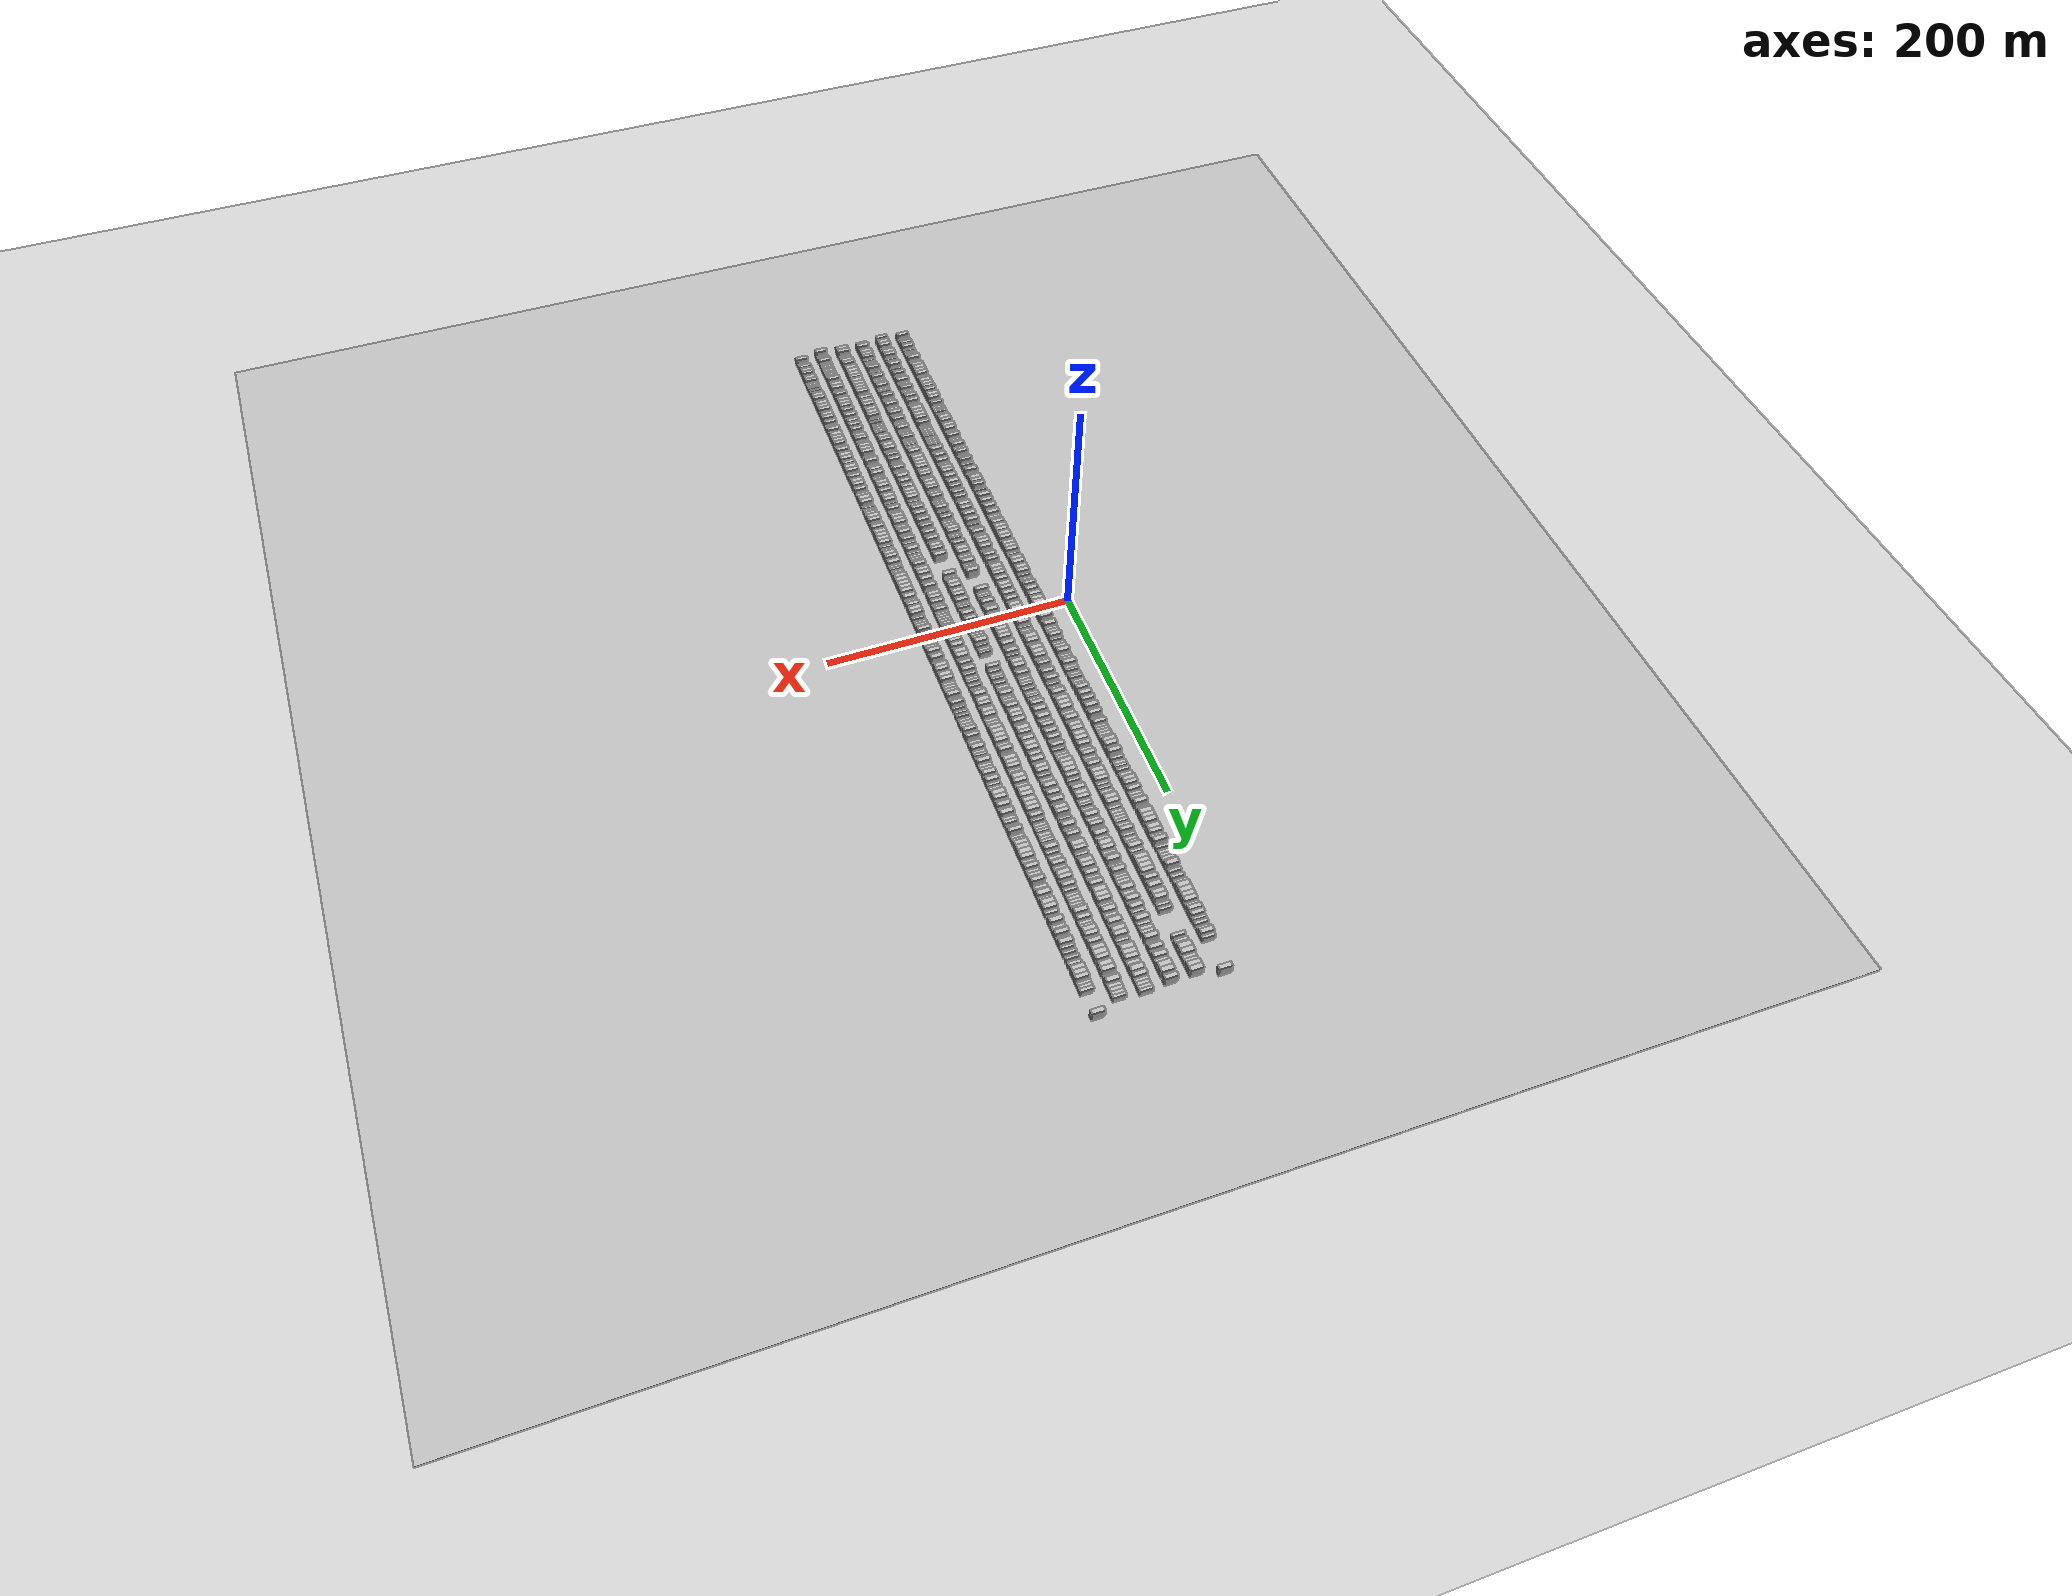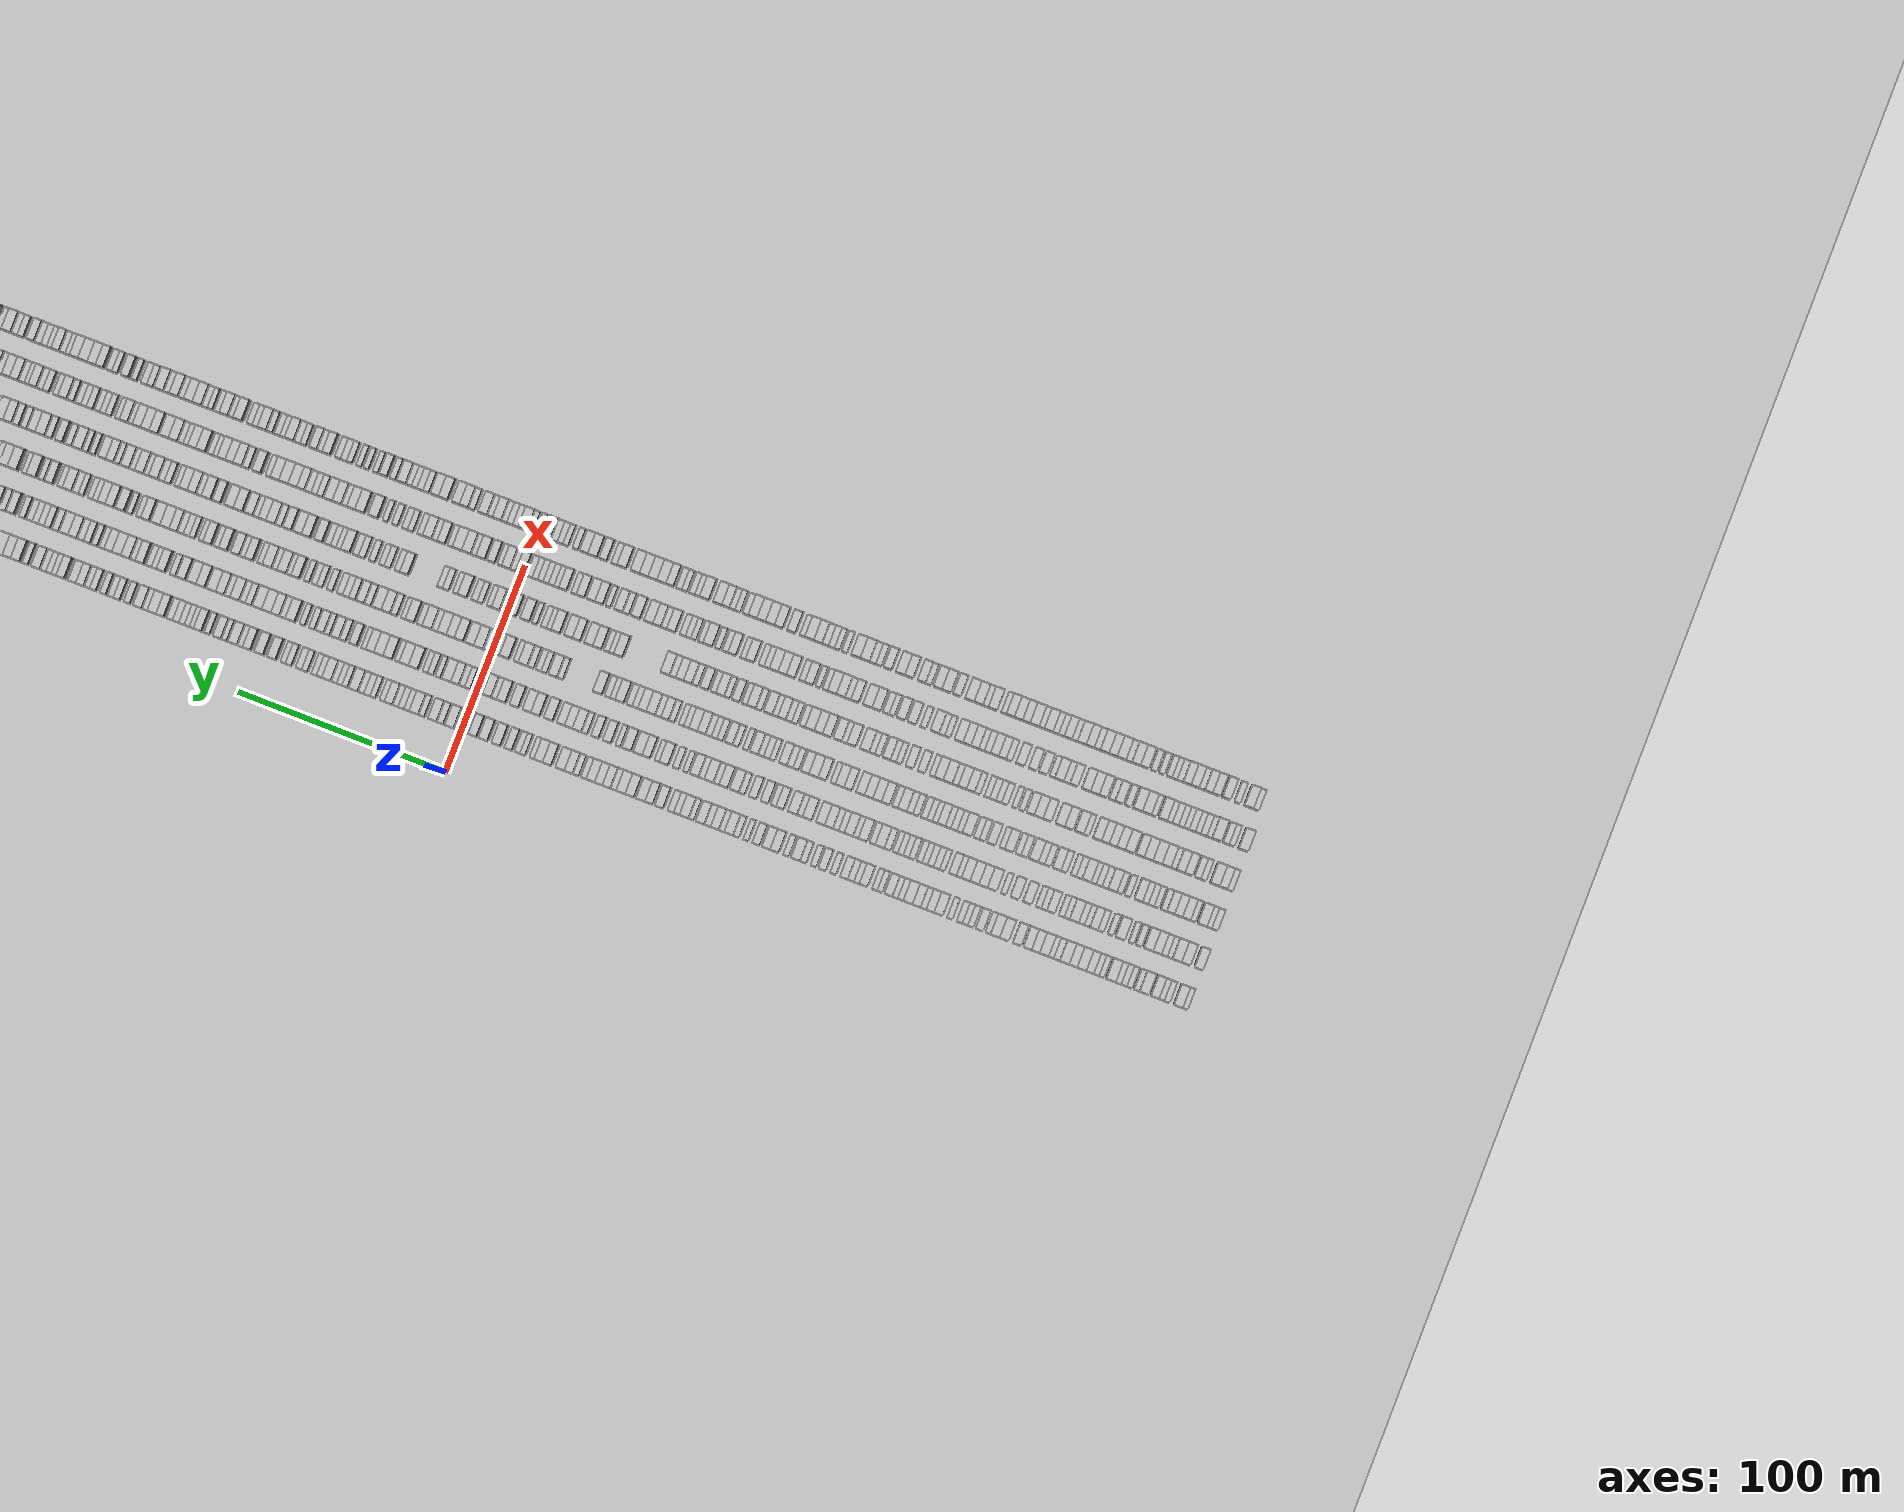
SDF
<?xml version="1.0" encoding="utf-8"?>

<sdf version="1.6">

   <world name="default">

      <gui fullscreen="0">

         <camera name="user_camera">

            <pose>-15 0 4.57585 0 0 0</pose>

            <view_controller>orbit</view_controller>

         </camera>

      </gui>

      <scene>

         <sky>

           <clouds>

             <speed>12</speed>

           </clouds>

         </sky>

         <ambient>0.4 0.4 0.4 1</ambient>

         <background>0.7 0.7 0.7 1</background>

         <shadows>1</shadows>

      </scene>

      <gravity>0 0 -9.8066</gravity>

      <magnetic_field>6e-06 2.3e-05 -4.2e-05</magnetic_field>

      <physics default="0" name="default_physics" type="ode">

         <ode>

            <solver>

               <type>quick</type>

               <iters>10</iters>

               <sor>1.0</sor>

               <use_dynamic_moi_rescaling>0</use_dynamic_moi_rescaling>

            </solver>

            <constraints>

               <cfm>0</cfm>

               <erp>0.2</erp>

               <contact_max_correcting_vel>100</contact_max_correcting_vel>

               <contact_surface_layer>0.001</contact_surface_layer>

            </constraints>

         </ode>

         <max_step_size>0.004</max_step_size>

         <real_time_factor>1</real_time_factor>

         <real_time_update_rate>250</real_time_update_rate>

      </physics>

      <light name="sun" type="directional">

         <cast_shadows>1</cast_shadows>

         <pose>0 0 10 0 0 0</pose>

         <diffuse>0.8 0.8 0.8 1</diffuse>

         <specular>0.2 0.2 0.2 1</specular>

         <attenuation>

            <range>1000</range>

            <constant>0.9</constant>

            <linear>0.01</linear>

            <quadratic>0.001</quadratic>

         </attenuation>

         <direction>-0.5 0.1 -0.9</direction>

      </light>

      <include>

         <name>ground_plane_1</name>

         <uri>model://HANNAS_ground_plane</uri>

         <pose>0 0 0  0 0 0</pose>

      </include>

      <include>

         <name>ground_plane_2</name>

         <uri>model://HANNAS_ground_plane</uri>

         <pose>100 0 0  0 0 0</pose>

      </include>

      <model name="building_1">

         <static>1</static>

         <pose frame="">25.0000 -348.7599 0 0.000000 0.000000 0.000000</pose>

         <link name="link">

            <pose frame="">0 0 3.00 0 0 0</pose>

            <collision name="collision">

               <geometry>

                  <box>

                     <size>10.0000 2.4801 6.0000</size>

                  </box>

               </geometry>

               <max_contacts>10</max_contacts>

               <surface>

                  <contact>

                     <ode/>

                  </contact>

                  <bounce/>

                  <friction>

                     <torsional>

                        <ode/>

                     </torsional>

                     <ode/>

                  </friction>

               </surface>

            </collision>

            <visual name="visual">

               <cast_shadows>0</cast_shadows>

               <geometry>

                  <box>

                     <size>10.0000 2.4801 6.0000</size>

                  </box>

               </geometry>

               <material>

                  <script>

                     <uri>model://HANNAS_wall/materials/scripts</uri>

                     <uri>model://HANNAS_wall/materials/textures</uri>

                     <name>vrc/HANNAS_wall</name>

                  </script>

               </material>

            </visual>

            <self_collide>0</self_collide>

            <enable_wind>0</enable_wind>

            <kinematic>0</kinematic>

         </link>

      </model>

      <model name="building_2">

         <static>1</static>

         <pose frame="">25.0000 -345.4535 0 0.000000 0.000000 0.000000</pose>

         <link name="link">

            <pose frame="">0 0 4.50 0 0 0</pose>

            <collision name="collision">

               <geometry>

                  <box>

                     <size>10.0000 4.1328 9.0000</size>

                  </box>

               </geometry>

               <max_contacts>10</max_contacts>

               <surface>

                  <contact>

                     <ode/>

                  </contact>

                  <bounce/>

                  <friction>

                     <torsional>

                        <ode/>

                     </torsional>

                     <ode/>

                  </friction>

               </surface>

            </collision>

            <visual name="visual">

               <cast_shadows>0</cast_shadows>

               <geometry>

                  <box>

                     <size>10.0000 4.1328 9.0000</size>

                  </box>

               </geometry>

               <material>

                  <script>

                     <uri>model://HANNAS_wall/materials/scripts</uri>

                     <uri>model://HANNAS_wall/materials/textures</uri>

                     <name>vrc/HANNAS_wall</name>

                  </script>

               </material>

            </visual>

            <self_collide>0</self_collide>

            <enable_wind>0</enable_wind>

            <kinematic>0</kinematic>

         </link>

      </model>

      <model name="building_3">

         <static>1</static>

         <pose frame="">25.0000 -340.0605 0 0.000000 0.000000 0.000000</pose>

         <link name="link">

            <pose frame="">0 0 3.00 0 0 0</pose>

            <collision name="collision">

               <geometry>

                  <box>

                     <size>10.0000 2.6533 6.0000</size>

                  </box>

               </geometry>

               <max_contacts>10</max_contacts>

               <surface>

                  <contact>

                     <ode/>

                  </contact>

                  <bounce/>

                  <friction>

                     <torsional>

                        <ode/>

                     </torsional>

                     <ode/>

                  </friction>

               </surface>

            </collision>

            <visual name="visual">

               <cast_shadows>0</cast_shadows>

               <geometry>

                  <box>

                     <size>10.0000 2.6533 6.0000</size>

                  </box>

               </geometry>

               <material>

                  <script>

                     <uri>model://HANNAS_wall/materials/scripts</uri>

                     <uri>model://HANNAS_wall/materials/textures</uri>

                     <name>vrc/HANNAS_wall</name>

                  </script>

               </material>

            </visual>

            <self_collide>0</self_collide>

            <enable_wind>0</enable_wind>

            <kinematic>0</kinematic>

         </link>

      </model>

      <model name="building_4">

         <static>1</static>

         <pose frame="">25.0000 -337.4462 0 0.000000 0.000000 0.000000</pose>

         <link name="link">

            <pose frame="">0 0 3.00 0 0 0</pose>

            <collision name="collision">

               <geometry>

                  <box>

                     <size>10.0000 2.5753 6.0000</size>

                  </box>

               </geometry>

               <max_contacts>10</max_contacts>

               <surface>

                  <contact>

                     <ode/>

                  </contact>

                  <bounce/>

                  <friction>

                     <torsional>

                        <ode/>

                     </torsional>

                     <ode/>

                  </friction>

               </surface>

            </collision>

            <visual name="visual">

               <cast_shadows>0</cast_shadows>

               <geometry>

                  <box>

                     <size>10.0000 2.5753 6.0000</size>

                  </box>

               </geometry>

               <material>

                  <script>

                     <uri>model://HANNAS_wall/materials/scripts</uri>

                     <uri>model://HANNAS_wall/materials/textures</uri>

                     <name>vrc/HANNAS_wall</name>

                  </script>

               </material>

            </visual>

            <self_collide>0</self_collide>

            <enable_wind>0</enable_wind>

            <kinematic>0</kinematic>

         </link>

      </model>

      <model name="building_5">

         <static>1</static>

         <pose frame="">25.0000 -334.2106 0 0.000000 0.000000 0.000000</pose>

         <link name="link">

            <pose frame="">0 0 4.50 0 0 0</pose>

            <collision name="collision">

               <geometry>

                  <box>

                     <size>10.0000 3.8959 9.0000</size>

                  </box>

               </geometry>

               <max_contacts>10</max_contacts>

               <surface>

                  <contact>

                     <ode/>

                  </contact>

                  <bounce/>

                  <friction>

                     <torsional>

                        <ode/>

                     </torsional>

                     <ode/>

                  </friction>

               </surface>

            </collision>

            <visual name="visual">

               <cast_shadows>0</cast_shadows>

               <geometry>

                  <box>

                     <size>10.0000 3.8959 9.0000</size>

                  </box>

               </geometry>

               <material>

                  <script>

                     <uri>model://HANNAS_wall/materials/scripts</uri>

                     <uri>model://HANNAS_wall/materials/textures</uri>

                     <name>vrc/HANNAS_wall</name>

                  </script>

               </material>

            </visual>

            <self_collide>0</self_collide>

            <enable_wind>0</enable_wind>

            <kinematic>0</kinematic>

         </link>

      </model>

      <model name="building_6">

         <static>1</static>

         <pose frame="">25.0000 -329.0597 0 0.000000 0.000000 0.000000</pose>

         <link name="link">

            <pose frame="">0 0 4.50 0 0 0</pose>

            <collision name="collision">

               <geometry>

                  <box>

                     <size>10.0000 4.4059 9.0000</size>

                  </box>

               </geometry>

               <max_contacts>10</max_contacts>

               <surface>

                  <contact>

                     <ode/>

                  </contact>

                  <bounce/>

                  <friction>

                     <torsional>

                        <ode/>

                     </torsional>

                     <ode/>

                  </friction>

               </surface>

            </collision>

            <visual name="visual">

               <cast_shadows>0</cast_shadows>

               <geometry>

                  <box>

                     <size>10.0000 4.4059 9.0000</size>

                  </box>

               </geometry>

               <material>

                  <script>

                     <uri>model://HANNAS_wall/materials/scripts</uri>

                     <uri>model://HANNAS_wall/materials/textures</uri>

                     <name>vrc/HANNAS_wall</name>

                  </script>

               </material>

            </visual>

            <self_collide>0</self_collide>

            <enable_wind>0</enable_wind>

            <kinematic>0</kinematic>

         </link>

      </model>

      <model name="building_7">

         <static>1</static>

         <pose frame="">25.0000 -325.5510 0 0.000000 0.000000 0.000000</pose>

         <link name="link">

            <pose frame="">0 0 3.00 0 0 0</pose>

            <collision name="collision">

               <geometry>

                  <box>

                     <size>10.0000 2.6116 6.0000</size>

                  </box>

               </geometry>

               <max_contacts>10</max_contacts>

               <surface>

                  <contact>

                     <ode/>

                  </contact>

                  <bounce/>

                  <friction>

                     <torsional>

                        <ode/>

                     </torsional>

                     <ode/>

                  </friction>

               </surface>

            </collision>

            <visual name="visual">

               <cast_shadows>0</cast_shadows>

               <geometry>

                  <box>

                     <size>10.0000 2.6116 6.0000</size>

                  </box>

               </geometry>

               <material>

                  <script>

                     <uri>model://HANNAS_wall/materials/scripts</uri>

                     <uri>model://HANNAS_wall/materials/textures</uri>

                     <name>vrc/HANNAS_wall</name>

                  </script>

               </material>

            </visual>

            <self_collide>0</self_collide>

            <enable_wind>0</enable_wind>

            <kinematic>0</kinematic>

         </link>

      </model>

      <model name="building_8">

         <static>1</static>

         <pose frame="">25.0000 -321.9728 0 0.000000 0.000000 0.000000</pose>

         <link name="link">

            <pose frame="">0 0 3.00 0 0 0</pose>

            <collision name="collision">

               <geometry>

                  <box>

                     <size>10.0000 2.5449 6.0000</size>

                  </box>

               </geometry>

               <max_contacts>10</max_contacts>

               <surface>

                  <contact>

                     <ode/>

                  </contact>

                  <bounce/>

                  <friction>

                     <torsional>

                        <ode/>

                     </torsional>

                     <ode/>

                  </friction>

               </surface>

            </collision>

            <visual name="visual">

               <cast_shadows>0</cast_shadows>

               <geometry>

                  <box>

                     <size>10.0000 2.5449 6.0000</size>

                  </box>

               </geometry>

               <material>

                  <script>

                     <uri>model://HANNAS_wall/materials/scripts</uri>

                     <uri>model://HANNAS_wall/materials/textures</uri>

                     <name>vrc/HANNAS_wall</name>

                  </script>

               </material>

            </visual>

            <self_collide>0</self_collide>

            <enable_wind>0</enable_wind>

            <kinematic>0</kinematic>

         </link>

      </model>

      <model name="building_9">

         <static>1</static>

         <pose frame="">25.0000 -319.3544 0 0.000000 0.000000 0.000000</pose>

         <link name="link">

            <pose frame="">0 0 3.00 0 0 0</pose>

            <collision name="collision">

               <geometry>

                  <box>

                     <size>10.0000 2.6918 6.0000</size>

                  </box>

               </geometry>

               <max_contacts>10</max_contacts>

               <surface>

                  <contact>

                     <ode/>

                  </contact>

                  <bounce/>

                  <friction>

                     <torsional>

                        <ode/>

                     </torsional>

                     <ode/>

                  </friction>

               </surface>

            </collision>

            <visual name="visual">

               <cast_shadows>0</cast_shadows>

               <geometry>

                  <box>

                     <size>10.0000 2.6918 6.0000</size>

                  </box>

               </geometry>

               <material>

                  <script>

                     <uri>model://HANNAS_wall/materials/scripts</uri>

                     <uri>model://HANNAS_wall/materials/textures</uri>

                     <name>vrc/HANNAS_wall</name>

                  </script>

               </material>

            </visual>

            <self_collide>0</self_collide>

            <enable_wind>0</enable_wind>

            <kinematic>0</kinematic>

         </link>

      </model>

      <model name="building_10">

         <static>1</static>

         <pose frame="">25.0000 -316.6475 0 0.000000 0.000000 0.000000</pose>

         <link name="link">

            <pose frame="">0 0 3.00 0 0 0</pose>

            <collision name="collision">

               <geometry>

                  <box>

                     <size>10.0000 2.7220 6.0000</size>

                  </box>

               </geometry>

               <max_contacts>10</max_contacts>

               <surface>

                  <contact>

                     <ode/>

                  </contact>

                  <bounce/>

                  <friction>

                     <torsional>

                        <ode/>

                     </torsional>

                     <ode/>

                  </friction>

               </surface>

            </collision>

            <visual name="visual">

               <cast_shadows>0</cast_shadows>

               <geometry>

                  <box>

                     <size>10.0000 2.7220 6.0000</size>

                  </box>

               </geometry>

               <material>

                  <script>

                     <uri>model://HANNAS_wall/materials/scripts</uri>

                     <uri>model://HANNAS_wall/materials/textures</uri>

                     <name>vrc/HANNAS_wall</name>

                  </script>

               </material>

            </visual>

            <self_collide>0</self_collide>

            <enable_wind>0</enable_wind>

            <kinematic>0</kinematic>

         </link>

      </model>

      <model name="building_11">

         <static>1</static>

         <pose frame="">25.0000 -313.0614 0 0.000000 0.000000 0.000000</pose>

         <link name="link">

            <pose frame="">0 0 4.50 0 0 0</pose>

            <collision name="collision">

               <geometry>

                  <box>

                     <size>10.0000 4.4501 9.0000</size>

                  </box>

               </geometry>

               <max_contacts>10</max_contacts>

               <surface>

                  <contact>

                     <ode/>

                  </contact>

                  <bounce/>

                  <friction>

                     <torsional>

                        <ode/>

                     </torsional>

                     <ode/>

                  </friction>

               </surface>

            </collision>

            <visual name="visual">

               <cast_shadows>0</cast_shadows>

               <geometry>

                  <box>

                     <size>10.0000 4.4501 9.0000</size>

                  </box>

               </geometry>

               <material>

                  <script>

                     <uri>model://HANNAS_wall/materials/scripts</uri>

                     <uri>model://HANNAS_wall/materials/textures</uri>

                     <name>vrc/HANNAS_wall</name>

                  </script>

               </material>

            </visual>

            <self_collide>0</self_collide>

            <enable_wind>0</enable_wind>

            <kinematic>0</kinematic>

         </link>

      </model>

      <model name="building_12">

         <static>1</static>

         <pose frame="">25.0000 -308.6230 0 0.000000 0.000000 0.000000</pose>

         <link name="link">

            <pose frame="">0 0 3.00 0 0 0</pose>

            <collision name="collision">

               <geometry>

                  <box>

                     <size>10.0000 2.4266 6.0000</size>

                  </box>

               </geometry>

               <max_contacts>10</max_contacts>

               <surface>

                  <contact>

                     <ode/>

                  </contact>

                  <bounce/>

                  <friction>

                     <torsional>

                        <ode/>

                     </torsional>

                     <ode/>

                  </friction>

               </surface>

            </collision>

            <visual name="visual">

               <cast_shadows>0</cast_shadows>

               <geometry>

                  <box>

                     <size>10.0000 2.4266 6.0000</size>

                  </box>

               </geometry>

               <material>

                  <script>

                     <uri>model://HANNAS_wall/materials/scripts</uri>

                     <uri>model://HANNAS_wall/materials/textures</uri>

                     <name>vrc/HANNAS_wall</name>

                  </script>

               </material>

            </visual>

            <self_collide>0</self_collide>

            <enable_wind>0</enable_wind>

            <kinematic>0</kinematic>

         </link>

      </model>

      <model name="building_13">

         <static>1</static>

         <pose frame="">25.0000 -306.0931 0 0.000000 0.000000 0.000000</pose>

         <link name="link">

            <pose frame="">0 0 3.00 0 0 0</pose>

            <collision name="collision">

               <geometry>

                  <box>

                     <size>10.0000 2.6333 6.0000</size>

                  </box>

               </geometry>

               <max_contacts>10</max_contacts>

               <surface>

                  <contact>

                     <ode/>

                  </contact>

                  <bounce/>

                  <friction>

                     <torsional>

                        <ode/>

                     </torsional>

                     <ode/>

                  </friction>

               </surface>

            </collision>

            <visual name="visual">

               <cast_shadows>0</cast_shadows>

               <geometry>

                  <box>

                     <size>10.0000 2.6333 6.0000</size>

                  </box>

               </geometry>

               <material>

                  <script>

                     <uri>model://HANNAS_wall/materials/scripts</uri>

                     <uri>model://HANNAS_wall/materials/textures</uri>

                     <name>vrc/HANNAS_wall</name>

                  </script>

               </material>

            </visual>

            <self_collide>0</self_collide>

            <enable_wind>0</enable_wind>

            <kinematic>0</kinematic>

         </link>

      </model>

      <model name="building_14">

         <static>1</static>

         <pose frame="">25.0000 -302.9602 0 0.000000 0.000000 0.000000</pose>

         <link name="link">

            <pose frame="">0 0 4.50 0 0 0</pose>

            <collision name="collision">

               <geometry>

                  <box>

                     <size>10.0000 3.6324 9.0000</size>

                  </box>

               </geometry>

               <max_contacts>10</max_contacts>

               <surface>

                  <contact>

                     <ode/>

                  </contact>

                  <bounce/>

                  <friction>

                     <torsional>

                        <ode/>

                     </torsional>

                     <ode/>

                  </friction>

               </surface>

            </collision>

            <visual name="visual">

               <cast_shadows>0</cast_shadows>

               <geometry>

                  <box>

                     <size>10.0000 3.6324 9.0000</size>

                  </box>

               </geometry>

               <material>

                  <script>

                     <uri>model://HANNAS_wall/materials/scripts</uri>

                     <uri>model://HANNAS_wall/materials/textures</uri>

                     <name>vrc/HANNAS_wall</name>

                  </script>

               </material>

            </visual>

            <self_collide>0</self_collide>

            <enable_wind>0</enable_wind>

            <kinematic>0</kinematic>

         </link>

      </model>

      <model name="building_15">

         <static>1</static>

         <pose frame="">25.0000 -298.9574 0 0.000000 0.000000 0.000000</pose>

         <link name="link">

            <pose frame="">0 0 4.50 0 0 0</pose>

            <collision name="collision">

               <geometry>

                  <box>

                     <size>10.0000 4.3732 9.0000</size>

                  </box>

               </geometry>

               <max_contacts>10</max_contacts>

               <surface>

                  <contact>

                     <ode/>

                  </contact>

                  <bounce/>

                  <friction>

                     <torsional>

                        <ode/>

                     </torsional>

                     <ode/>

                  </friction>

               </surface>

            </collision>

            <visual name="visual">

               <cast_shadows>0</cast_shadows>

               <geometry>

                  <box>

                     <size>10.0000 4.3732 9.0000</size>

                  </box>

               </geometry>

               <material>

                  <script>

                     <uri>model://HANNAS_wall/materials/scripts</uri>

                     <uri>model://HANNAS_wall/materials/textures</uri>

                     <name>vrc/HANNAS_wall</name>

                  </script>

               </material>

            </visual>

            <self_collide>0</self_collide>

            <enable_wind>0</enable_wind>

            <kinematic>0</kinematic>

         </link>

      </model>

      <model name="building_16">

         <static>1</static>

         <pose frame="">25.0000 -294.8477 0 0.000000 0.000000 0.000000</pose>

         <link name="link">

            <pose frame="">0 0 4.50 0 0 0</pose>

            <collision name="collision">

               <geometry>

                  <box>

                     <size>10.0000 3.8461 9.0000</size>

                  </box>

               </geometry>

               <max_contacts>10</max_contacts>

               <surface>

                  <contact>

                     <ode/>

                  </contact>

                  <bounce/>

                  <friction>

                     <torsional>

                        <ode/>

                     </torsional>

                     <ode/>

                  </friction>

               </surface>

            </collision>

            <visual name="visual">

               <cast_shadows>0</cast_shadows>

               <geometry>

                  <box>

                     <size>10.0000 3.8461 9.0000</size>

                  </box>

               </geometry>

               <material>

                  <script>

                     <uri>model://HANNAS_wall/materials/scripts</uri>

                     <uri>model://HANNAS_wall/materials/textures</uri>

                     <name>vrc/HANNAS_wall</name>

                  </script>

               </material>

            </visual>

            <self_collide>0</self_collide>

            <enable_wind>0</enable_wind>

            <kinematic>0</kinematic>

         </link>

      </model>

      <model name="building_17">

         <static>1</static>

         <pose frame="">25.0000 -290.7039 0 0.000000 0.000000 0.000000</pose>

         <link name="link">

            <pose frame="">0 0 4.50 0 0 0</pose>

            <collision name="collision">

               <geometry>

                  <box>

                     <size>10.0000 4.4416 9.0000</size>

                  </box>

               </geometry>

               <max_contacts>10</max_contacts>

               <surface>

                  <contact>

                     <ode/>

                  </contact>

                  <bounce/>

                  <friction>

                     <torsional>

                        <ode/>

                     </torsional>

                     <ode/>

                  </friction>

               </surface>

            </collision>

            <visual name="visual">

               <cast_shadows>0</cast_shadows>

               <geometry>

                  <box>

                     <size>10.0000 4.4416 9.0000</size>

                  </box>

               </geometry>

               <material>

                  <script>

                     <uri>model://HANNAS_wall/materials/scripts</uri>

                     <uri>model://HANNAS_wall/materials/textures</uri>

                     <name>vrc/HANNAS_wall</name>

                  </script>

               </material>

            </visual>

            <self_collide>0</self_collide>

            <enable_wind>0</enable_wind>

            <kinematic>0</kinematic>

         </link>

      </model>

      <model name="building_18">

         <static>1</static>

         <pose frame="">25.0000 -286.9948 0 0.000000 0.000000 0.000000</pose>

         <link name="link">

            <pose frame="">0 0 3.00 0 0 0</pose>

            <collision name="collision">

               <geometry>

                  <box>

                     <size>10.0000 2.9767 6.0000</size>

                  </box>

               </geometry>

               <max_contacts>10</max_contacts>

               <surface>

                  <contact>

                     <ode/>

                  </contact>

                  <bounce/>

                  <friction>

                     <torsional>

                        <ode/>

                     </torsional>

                     <ode/>

                  </friction>

               </surface>

            </collision>

            <visual name="visual">

               <cast_shadows>0</cast_shadows>

               <geometry>

                  <box>

                     <size>10.0000 2.9767 6.0000</size>

                  </box>

               </geometry>

               <material>

                  <script>

                     <uri>model://HANNAS_wall/materials/scripts</uri>

                     <uri>model://HANNAS_wall/materials/textures</uri>

                     <name>vrc/HANNAS_wall</name>

                  </script>

               </material>

            </visual>

            <self_collide>0</self_collide>

            <enable_wind>0</enable_wind>

            <kinematic>0</kinematic>

         </link>

      </model>

      <model name="building_19">

         <static>1</static>

         <pose frame="">25.0000 -284.2951 0 0.000000 0.000000 0.000000</pose>

         <link name="link">

            <pose frame="">0 0 3.00 0 0 0</pose>

            <collision name="collision">

               <geometry>

                  <box>

                     <size>10.0000 2.4228 6.0000</size>

                  </box>

               </geometry>

               <max_contacts>10</max_contacts>

               <surface>

                  <contact>

                     <ode/>

                  </contact>

                  <bounce/>

                  <friction>

                     <torsional>

                        <ode/>

                     </torsional>

                     <ode/>

                  </friction>

               </surface>

            </collision>

            <visual name="visual">

               <cast_shadows>0</cast_shadows>

               <geometry>

                  <box>

                     <size>10.0000 2.4228 6.0000</size>

                  </box>

               </geometry>

               <material>

                  <script>

                     <uri>model://HANNAS_wall/materials/scripts</uri>

                     <uri>model://HANNAS_wall/materials/textures</uri>

                     <name>vrc/HANNAS_wall</name>

                  </script>

               </material>

            </visual>

            <self_collide>0</self_collide>

            <enable_wind>0</enable_wind>

            <kinematic>0</kinematic>

         </link>

      </model>

      <model name="building_20">

         <static>1</static>

         <pose frame="">25.0000 -280.8944 0 0.000000 0.000000 0.000000</pose>

         <link name="link">

            <pose frame="">0 0 4.50 0 0 0</pose>

            <collision name="collision">

               <geometry>

                  <box>

                     <size>10.0000 4.3785 9.0000</size>

                  </box>

               </geometry>

               <max_contacts>10</max_contacts>

               <surface>

                  <contact>

                     <ode/>

                  </contact>

                  <bounce/>

                  <friction>

                     <torsional>

                        <ode/>

                     </torsional>

                     <ode/>

                  </friction>

               </surface>

            </collision>

            <visual name="visual">

               <cast_shadows>0</cast_shadows>

               <geometry>

                  <box>

                     <size>10.0000 4.3785 9.0000</size>

                  </box>

               </geometry>

               <material>

                  <script>

                     <uri>model://HANNAS_wall/materials/scripts</uri>

                     <uri>model://HANNAS_wall/materials/textures</uri>

                     <name>vrc/HANNAS_wall</name>

                  </script>

               </material>

            </visual>

            <self_collide>0</self_collide>

            <enable_wind>0</enable_wind>

            <kinematic>0</kinematic>

         </link>

      </model>

      <model name="building_21">

         <static>1</static>

         <pose frame="">25.0000 -276.7911 0 0.000000 0.000000 0.000000</pose>

         <link name="link">

            <pose frame="">0 0 4.50 0 0 0</pose>

            <collision name="collision">

               <geometry>

                  <box>

                     <size>10.0000 3.8281 9.0000</size>

                  </box>

               </geometry>

               <max_contacts>10</max_contacts>

               <surface>

                  <contact>

                     <ode/>

                  </contact>

                  <bounce/>

                  <friction>

                     <torsional>

                        <ode/>

                     </torsional>

                     <ode/>

                  </friction>

               </surface>

            </collision>

            <visual name="visual">

               <cast_shadows>0</cast_shadows>

               <geometry>

                  <box>

                     <size>10.0000 3.8281 9.0000</size>

                  </box>

               </geometry>

               <material>

                  <script>

                     <uri>model://HANNAS_wall/materials/scripts</uri>

                     <uri>model://HANNAS_wall/materials/textures</uri>

                     <name>vrc/HANNAS_wall</name>

                  </script>

               </material>

            </visual>

            <self_collide>0</self_collide>

            <enable_wind>0</enable_wind>

            <kinematic>0</kinematic>

         </link>

      </model>

      <model name="building_22">

         <static>1</static>

         <pose frame="">25.0000 -272.9097 0 0.000000 0.000000 0.000000</pose>

         <link name="link">

            <pose frame="">0 0 4.50 0 0 0</pose>

            <collision name="collision">

               <geometry>

                  <box>

                     <size>10.0000 3.9345 9.0000</size>

                  </box>

               </geometry>

               <max_contacts>10</max_contacts>

               <surface>

                  <contact>

                     <ode/>

                  </contact>

                  <bounce/>

                  <friction>

                     <torsional>

                        <ode/>

                     </torsional>

                     <ode/>

                  </friction>

               </surface>

            </collision>

            <visual name="visual">

               <cast_shadows>0</cast_shadows>

               <geometry>

                  <box>

                     <size>10.0000 3.9345 9.0000</size>

                  </box>

               </geometry>

               <material>

                  <script>

                     <uri>model://HANNAS_wall/materials/scripts</uri>

                     <uri>model://HANNAS_wall/materials/textures</uri>

                     <name>vrc/HANNAS_wall</name>

                  </script>

               </material>

            </visual>

            <self_collide>0</self_collide>

            <enable_wind>0</enable_wind>

            <kinematic>0</kinematic>

         </link>

      </model>

      <model name="building_23">

         <static>1</static>

         <pose frame="">25.0000 -267.9215 0 0.000000 0.000000 0.000000</pose>

         <link name="link">

            <pose frame="">0 0 4.50 0 0 0</pose>

            <collision name="collision">

               <geometry>

                  <box>

                     <size>10.0000 4.0418 9.0000</size>

                  </box>

               </geometry>

               <max_contacts>10</max_contacts>

               <surface>

                  <contact>

                     <ode/>

                  </contact>

                  <bounce/>

                  <friction>

                     <torsional>

                        <ode/>

                     </torsional>

                     <ode/>

                  </friction>

               </surface>

            </collision>

            <visual name="visual">

               <cast_shadows>0</cast_shadows>

               <geometry>

                  <box>

                     <size>10.0000 4.0418 9.0000</size>

                  </box>

               </geometry>

               <material>

                  <script>

                     <uri>model://HANNAS_wall/materials/scripts</uri>

                     <uri>model://HANNAS_wall/materials/textures</uri>

                     <name>vrc/HANNAS_wall</name>

                  </script>

               </material>

            </visual>

            <self_collide>0</self_collide>

            <enable_wind>0</enable_wind>

            <kinematic>0</kinematic>

         </link>

      </model>

      <model name="building_24">

         <static>1</static>

         <pose frame="">25.0000 -261.6957 0 0.000000 0.000000 0.000000</pose>

         <link name="link">

            <pose frame="">0 0 4.50 0 0 0</pose>

            <collision name="collision">

               <geometry>

                  <box>

                     <size>10.0000 4.4099 9.0000</size>

                  </box>

               </geometry>

               <max_contacts>10</max_contacts>

               <surface>

                  <contact>

                     <ode/>

                  </contact>

                  <bounce/>

                  <friction>

                     <torsional>

                        <ode/>

                     </torsional>

                     <ode/>

                  </friction>

               </surface>

            </collision>

            <visual name="visual">

               <cast_shadows>0</cast_shadows>

               <geometry>

                  <box>

                     <size>10.0000 4.4099 9.0000</size>

                  </box>

               </geometry>

               <material>

                  <script>

                     <uri>model://HANNAS_wall/materials/scripts</uri>

                     <uri>model://HANNAS_wall/materials/textures</uri>

                     <name>vrc/HANNAS_wall</name>

                  </script>

               </material>

            </visual>

            <self_collide>0</self_collide>

            <enable_wind>0</enable_wind>

            <kinematic>0</kinematic>

         </link>

      </model>

      <model name="building_25">

         <static>1</static>

         <pose frame="">25.0000 -257.3109 0 0.000000 0.000000 0.000000</pose>

         <link name="link">

            <pose frame="">0 0 4.50 0 0 0</pose>

            <collision name="collision">

               <geometry>

                  <box>

                     <size>10.0000 4.3598 9.0000</size>

                  </box>

               </geometry>

               <max_contacts>10</max_contacts>

               <surface>

                  <contact>

                     <ode/>

                  </contact>

                  <bounce/>

                  <friction>

                     <torsional>

                        <ode/>

                     </torsional>

                     <ode/>

                  </friction>

               </surface>

            </collision>

            <visual name="visual">

               <cast_shadows>0</cast_shadows>

               <geometry>

                  <box>

                     <size>10.0000 4.3598 9.0000</size>

                  </box>

               </geometry>

               <material>

                  <script>

                     <uri>model://HANNAS_wall/materials/scripts</uri>

                     <uri>model://HANNAS_wall/materials/textures</uri>

                     <name>vrc/HANNAS_wall</name>

                  </script>

               </material>

            </visual>

            <self_collide>0</self_collide>

            <enable_wind>0</enable_wind>

            <kinematic>0</kinematic>

         </link>

      </model>

      <model name="building_26">

         <static>1</static>

         <pose frame="">25.0000 -253.8704 0 0.000000 0.000000 0.000000</pose>

         <link name="link">

            <pose frame="">0 0 3.00 0 0 0</pose>

            <collision name="collision">

               <geometry>

                  <box>

                     <size>10.0000 2.5212 6.0000</size>

                  </box>

               </geometry>

               <max_contacts>10</max_contacts>

               <surface>

                  <contact>

                     <ode/>

                  </contact>

                  <bounce/>

                  <friction>

                     <torsional>

                        <ode/>

                     </torsional>

                     <ode/>

                  </friction>

               </surface>

            </collision>

            <visual name="visual">

               <cast_shadows>0</cast_shadows>

               <geometry>

                  <box>

                     <size>10.0000 2.5212 6.0000</size>

                  </box>

               </geometry>

               <material>

                  <script>

                     <uri>model://HANNAS_wall/materials/scripts</uri>

                     <uri>model://HANNAS_wall/materials/textures</uri>

                     <name>vrc/HANNAS_wall</name>

                  </script>

               </material>

            </visual>

            <self_collide>0</self_collide>

            <enable_wind>0</enable_wind>

            <kinematic>0</kinematic>

         </link>

      </model>

      <model name="building_27">

         <static>1</static>

         <pose frame="">25.0000 -249.7720 0 0.000000 0.000000 0.000000</pose>

         <link name="link">

            <pose frame="">0 0 4.50 0 0 0</pose>

            <collision name="collision">

               <geometry>

                  <box>

                     <size>10.0000 3.6756 9.0000</size>

                  </box>

               </geometry>

               <max_contacts>10</max_contacts>

               <surface>

                  <contact>

                     <ode/>

                  </contact>

                  <bounce/>

                  <friction>

                     <torsional>

                        <ode/>

                     </torsional>

                     <ode/>

                  </friction>

               </surface>

            </collision>

            <visual name="visual">

               <cast_shadows>0</cast_shadows>

               <geometry>

                  <box>

                     <size>10.0000 3.6756 9.0000</size>

                  </box>

               </geometry>

               <material>

                  <script>

                     <uri>model://HANNAS_wall/materials/scripts</uri>

                     <uri>model://HANNAS_wall/materials/textures</uri>

                     <name>vrc/HANNAS_wall</name>

                  </script>

               </material>

            </visual>

            <self_collide>0</self_collide>

            <enable_wind>0</enable_wind>

            <kinematic>0</kinematic>

         </link>

      </model>

      <model name="building_28">

         <static>1</static>

         <pose frame="">25.0000 -245.5644 0 0.000000 0.000000 0.000000</pose>

         <link name="link">

            <pose frame="">0 0 3.00 0 0 0</pose>

            <collision name="collision">

               <geometry>

                  <box>

                     <size>10.0000 2.7396 6.0000</size>

                  </box>

               </geometry>

               <max_contacts>10</max_contacts>

               <surface>

                  <contact>

                     <ode/>

                  </contact>

                  <bounce/>

                  <friction>

                     <torsional>

                        <ode/>

                     </torsional>

                     <ode/>

                  </friction>

               </surface>

            </collision>

            <visual name="visual">

               <cast_shadows>0</cast_shadows>

               <geometry>

                  <box>

                     <size>10.0000 2.7396 6.0000</size>

                  </box>

               </geometry>

               <material>

                  <script>

                     <uri>model://HANNAS_wall/materials/scripts</uri>

                     <uri>model://HANNAS_wall/materials/textures</uri>

                     <name>vrc/HANNAS_wall</name>

                  </script>

               </material>

            </visual>

            <self_collide>0</self_collide>

            <enable_wind>0</enable_wind>

            <kinematic>0</kinematic>

         </link>

      </model>

      <model name="building_29">

         <static>1</static>

         <pose frame="">25.0000 -242.9074 0 0.000000 0.000000 0.000000</pose>

         <link name="link">

            <pose frame="">0 0 3.00 0 0 0</pose>

            <collision name="collision">

               <geometry>

                  <box>

                     <size>10.0000 2.5745 6.0000</size>

                  </box>

               </geometry>

               <max_contacts>10</max_contacts>

               <surface>

                  <contact>

                     <ode/>

                  </contact>

                  <bounce/>

                  <friction>

                     <torsional>

                        <ode/>

                     </torsional>

                     <ode/>

                  </friction>

               </surface>

            </collision>

            <visual name="visual">

               <cast_shadows>0</cast_shadows>

               <geometry>

                  <box>

                     <size>10.0000 2.5745 6.0000</size>

                  </box>

               </geometry>

               <material>

                  <script>

                     <uri>model://HANNAS_wall/materials/scripts</uri>

                     <uri>model://HANNAS_wall/materials/textures</uri>

                     <name>vrc/HANNAS_wall</name>

                  </script>

               </material>

            </visual>

            <self_collide>0</self_collide>

            <enable_wind>0</enable_wind>

            <kinematic>0</kinematic>

         </link>

      </model>

      <model name="building_30">

         <static>1</static>

         <pose frame="">25.0000 -240.2080 0 0.000000 0.000000 0.000000</pose>

         <link name="link">

            <pose frame="">0 0 3.00 0 0 0</pose>

            <collision name="collision">

               <geometry>

                  <box>

                     <size>10.0000 2.8241 6.0000</size>

                  </box>

               </geometry>

               <max_contacts>10</max_contacts>

               <surface>

                  <contact>

                     <ode/>

                  </contact>

                  <bounce/>

                  <friction>

                     <torsional>

                        <ode/>

                     </torsional>

                     <ode/>

                  </friction>

               </surface>

            </collision>

            <visual name="visual">

               <cast_shadows>0</cast_shadows>

               <geometry>

                  <box>

                     <size>10.0000 2.8241 6.0000</size>

                  </box>

               </geometry>

               <material>

                  <script>

                     <uri>model://HANNAS_wall/materials/scripts</uri>

                     <uri>model://HANNAS_wall/materials/textures</uri>

                     <name>vrc/HANNAS_wall</name>

                  </script>

               </material>

            </visual>

            <self_collide>0</self_collide>

            <enable_wind>0</enable_wind>

            <kinematic>0</kinematic>

         </link>

      </model>

      <model name="building_31">

         <static>1</static>

         <pose frame="">25.0000 -235.5040 0 0.000000 0.000000 0.000000</pose>

         <link name="link">

            <pose frame="">0 0 3.00 0 0 0</pose>

            <collision name="collision">

               <geometry>

                  <box>

                     <size>10.0000 2.5838 6.0000</size>

                  </box>

               </geometry>

               <max_contacts>10</max_contacts>

               <surface>

                  <contact>

                     <ode/>

                  </contact>

                  <bounce/>

                  <friction>

                     <torsional>

                        <ode/>

                     </torsional>

                     <ode/>

                  </friction>

               </surface>

            </collision>

            <visual name="visual">

               <cast_shadows>0</cast_shadows>

               <geometry>

                  <box>

                     <size>10.0000 2.5838 6.0000</size>

                  </box>

               </geometry>

               <material>

                  <script>

                     <uri>model://HANNAS_wall/materials/scripts</uri>

                     <uri>model://HANNAS_wall/materials/textures</uri>

                     <name>vrc/HANNAS_wall</name>

                  </script>

               </material>

            </visual>

            <self_collide>0</self_collide>

            <enable_wind>0</enable_wind>

            <kinematic>0</kinematic>

         </link>

      </model>

      <model name="building_32">

         <static>1</static>

         <pose frame="">25.0000 -230.0899 0 0.000000 0.000000 0.000000</pose>

         <link name="link">

            <pose frame="">0 0 4.50 0 0 0</pose>

            <collision name="collision">

               <geometry>

                  <box>

                     <size>10.0000 4.2443 9.0000</size>

                  </box>

               </geometry>

               <max_contacts>10</max_contacts>

               <surface>

                  <contact>

                     <ode/>

                  </contact>

                  <bounce/>

                  <friction>

                     <torsional>

                        <ode/>

                     </torsional>

                     <ode/>

                  </friction>

               </surface>

            </collision>

            <visual name="visual">

               <cast_shadows>0</cast_shadows>

               <geometry>

                  <box>

                     <size>10.0000 4.2443 9.0000</size>

                  </box>

               </geometry>

               <material>

                  <script>

                     <uri>model://HANNAS_wall/materials/scripts</uri>

                     <uri>model://HANNAS_wall/materials/textures</uri>

                     <name>vrc/HANNAS_wall</name>

                  </script>

               </material>

            </visual>

            <self_collide>0</self_collide>

            <enable_wind>0</enable_wind>

            <kinematic>0</kinematic>

         </link>

      </model>

      <model name="building_33">

         <static>1</static>

         <pose frame="">25.0000 -226.0862 0 0.000000 0.000000 0.000000</pose>

         <link name="link">

            <pose frame="">0 0 4.50 0 0 0</pose>

            <collision name="collision">

               <geometry>

                  <box>

                     <size>10.0000 3.7631 9.0000</size>

                  </box>

               </geometry>

               <max_contacts>10</max_contacts>

               <surface>

                  <contact>

                     <ode/>

                  </contact>

                  <bounce/>

                  <friction>

                     <torsional>

                        <ode/>

                     </torsional>

                     <ode/>

                  </friction>

               </surface>

            </collision>

            <visual name="visual">

               <cast_shadows>0</cast_shadows>

               <geometry>

                  <box>

                     <size>10.0000 3.7631 9.0000</size>

                  </box>

               </geometry>

               <material>

                  <script>

                     <uri>model://HANNAS_wall/materials/scripts</uri>

                     <uri>model://HANNAS_wall/materials/textures</uri>

                     <name>vrc/HANNAS_wall</name>

                  </script>

               </material>

            </visual>

            <self_collide>0</self_collide>

            <enable_wind>0</enable_wind>

            <kinematic>0</kinematic>

         </link>

      </model>

      <model name="building_34">

         <static>1</static>

         <pose frame="">25.0000 -222.8587 0 0.000000 0.000000 0.000000</pose>

         <link name="link">

            <pose frame="">0 0 3.00 0 0 0</pose>

            <collision name="collision">

               <geometry>

                  <box>

                     <size>10.0000 2.6919 6.0000</size>

                  </box>

               </geometry>

               <max_contacts>10</max_contacts>

               <surface>

                  <contact>

                     <ode/>

                  </contact>

                  <bounce/>

                  <friction>

                     <torsional>

                        <ode/>

                     </torsional>

                     <ode/>

                  </friction>

               </surface>

            </collision>

            <visual name="visual">

               <cast_shadows>0</cast_shadows>

               <geometry>

                  <box>

                     <size>10.0000 2.6919 6.0000</size>

                  </box>

               </geometry>

               <material>

                  <script>

                     <uri>model://HANNAS_wall/materials/scripts</uri>

                     <uri>model://HANNAS_wall/materials/textures</uri>

                     <name>vrc/HANNAS_wall</name>

                  </script>

               </material>

            </visual>

            <self_collide>0</self_collide>

            <enable_wind>0</enable_wind>

            <kinematic>0</kinematic>

         </link>

      </model>

      <model name="building_35">

         <static>1</static>

         <pose frame="">25.0000 -219.5621 0 0.000000 0.000000 0.000000</pose>

         <link name="link">

            <pose frame="">0 0 4.50 0 0 0</pose>

            <collision name="collision">

               <geometry>

                  <box>

                     <size>10.0000 3.9012 9.0000</size>

                  </box>

               </geometry>

               <max_contacts>10</max_contacts>

               <surface>

                  <contact>

                     <ode/>

                  </contact>

                  <bounce/>

                  <friction>

                     <torsional>

                        <ode/>

                     </torsional>

                     <ode/>

                  </friction>

               </surface>

            </collision>

            <visual name="visual">

               <cast_shadows>0</cast_shadows>

               <geometry>

                  <box>

                     <size>10.0000 3.9012 9.0000</size>

                  </box>

               </geometry>

               <material>

                  <script>

                     <uri>model://HANNAS_wall/materials/scripts</uri>

                     <uri>model://HANNAS_wall/materials/textures</uri>

                     <name>vrc/HANNAS_wall</name>

                  </script>

               </material>

            </visual>

            <self_collide>0</self_collide>

            <enable_wind>0</enable_wind>

            <kinematic>0</kinematic>

         </link>

      </model>

      <model name="building_36">

         <static>1</static>

         <pose frame="">25.0000 -215.3749 0 0.000000 0.000000 0.000000</pose>

         <link name="link">

            <pose frame="">0 0 4.50 0 0 0</pose>

            <collision name="collision">

               <geometry>

                  <box>

                     <size>10.0000 4.4732 9.0000</size>

                  </box>

               </geometry>

               <max_contacts>10</max_contacts>

               <surface>

                  <contact>

                     <ode/>

                  </contact>

                  <bounce/>

                  <friction>

                     <torsional>

                        <ode/>

                     </torsional>

                     <ode/>

                  </friction>

               </surface>

            </collision>

            <visual name="visual">

               <cast_shadows>0</cast_shadows>

               <geometry>

                  <box>

                     <size>10.0000 4.4732 9.0000</size>

                  </box>

               </geometry>

               <material>

                  <script>

                     <uri>model://HANNAS_wall/materials/scripts</uri>

                     <uri>model://HANNAS_wall/materials/textures</uri>

                     <name>vrc/HANNAS_wall</name>

                  </script>

               </material>

            </visual>

            <self_collide>0</self_collide>

            <enable_wind>0</enable_wind>

            <kinematic>0</kinematic>

         </link>

      </model>

      <model name="building_37">

         <static>1</static>

         <pose frame="">25.0000 -211.7772 0 0.000000 0.000000 0.000000</pose>

         <link name="link">

            <pose frame="">0 0 3.00 0 0 0</pose>

            <collision name="collision">

               <geometry>

                  <box>

                     <size>10.0000 2.7222 6.0000</size>

                  </box>

               </geometry>

               <max_contacts>10</max_contacts>

               <surface>

                  <contact>

                     <ode/>

                  </contact>

                  <bounce/>

                  <friction>

                     <torsional>

                        <ode/>

                     </torsional>

                     <ode/>

                  </friction>

               </surface>

            </collision>

            <visual name="visual">

               <cast_shadows>0</cast_shadows>

               <geometry>

                  <box>

                     <size>10.0000 2.7222 6.0000</size>

                  </box>

               </geometry>

               <material>

                  <script>

                     <uri>model://HANNAS_wall/materials/scripts</uri>

                     <uri>model://HANNAS_wall/materials/textures</uri>

                     <name>vrc/HANNAS_wall</name>

                  </script>

               </material>

            </visual>

            <self_collide>0</self_collide>

            <enable_wind>0</enable_wind>

            <kinematic>0</kinematic>

         </link>

      </model>

      <model name="building_38">

         <static>1</static>

         <pose frame="">25.0000 -209.1756 0 0.000000 0.000000 0.000000</pose>

         <link name="link">

            <pose frame="">0 0 3.00 0 0 0</pose>

            <collision name="collision">

               <geometry>

                  <box>

                     <size>10.0000 2.4810 6.0000</size>

                  </box>

               </geometry>

               <max_contacts>10</max_contacts>

               <surface>

                  <contact>

                     <ode/>

                  </contact>

                  <bounce/>

                  <friction>

                     <torsional>

                        <ode/>

                     </torsional>

                     <ode/>

                  </friction>

               </surface>

            </collision>

            <visual name="visual">

               <cast_shadows>0</cast_shadows>

               <geometry>

                  <box>

                     <size>10.0000 2.4810 6.0000</size>

                  </box>

               </geometry>

               <material>

                  <script>

                     <uri>model://HANNAS_wall/materials/scripts</uri>

                     <uri>model://HANNAS_wall/materials/textures</uri>

                     <name>vrc/HANNAS_wall</name>

                  </script>

               </material>

            </visual>

            <self_collide>0</self_collide>

            <enable_wind>0</enable_wind>

            <kinematic>0</kinematic>

         </link>

      </model>

      <model name="building_39">

         <static>1</static>

         <pose frame="">25.0000 -206.0133 0 0.000000 0.000000 0.000000</pose>

         <link name="link">

            <pose frame="">0 0 4.50 0 0 0</pose>

            <collision name="collision">

               <geometry>

                  <box>

                     <size>10.0000 3.8437 9.0000</size>

                  </box>

               </geometry>

               <max_contacts>10</max_contacts>

               <surface>

                  <contact>

                     <ode/>

                  </contact>

                  <bounce/>

                  <friction>

                     <torsional>

                        <ode/>

                     </torsional>

                     <ode/>

                  </friction>

               </surface>

            </collision>

            <visual name="visual">

               <cast_shadows>0</cast_shadows>

               <geometry>

                  <box>

                     <size>10.0000 3.8437 9.0000</size>

                  </box>

               </geometry>

               <material>

                  <script>

                     <uri>model://HANNAS_wall/materials/scripts</uri>

                     <uri>model://HANNAS_wall/materials/textures</uri>

                     <name>vrc/HANNAS_wall</name>

                  </script>

               </material>

            </visual>

            <self_collide>0</self_collide>

            <enable_wind>0</enable_wind>

            <kinematic>0</kinematic>

         </link>

      </model>

      <model name="building_40">

         <static>1</static>

         <pose frame="">25.0000 -201.8204 0 0.000000 0.000000 0.000000</pose>

         <link name="link">

            <pose frame="">0 0 3.00 0 0 0</pose>

            <collision name="collision">

               <geometry>

                  <box>

                     <size>10.0000 2.5420 6.0000</size>

                  </box>

               </geometry>

               <max_contacts>10</max_contacts>

               <surface>

                  <contact>

                     <ode/>

                  </contact>

                  <bounce/>

                  <friction>

                     <torsional>

                        <ode/>

                     </torsional>

                     <ode/>

                  </friction>

               </surface>

            </collision>

            <visual name="visual">

               <cast_shadows>0</cast_shadows>

               <geometry>

                  <box>

                     <size>10.0000 2.5420 6.0000</size>

                  </box>

               </geometry>

               <material>

                  <script>

                     <uri>model://HANNAS_wall/materials/scripts</uri>

                     <uri>model://HANNAS_wall/materials/textures</uri>

                     <name>vrc/HANNAS_wall</name>

                  </script>

               </material>

            </visual>

            <self_collide>0</self_collide>

            <enable_wind>0</enable_wind>

            <kinematic>0</kinematic>

         </link>

      </model>

      <model name="building_41">

         <static>1</static>

         <pose frame="">25.0000 -199.2871 0 0.000000 0.000000 0.000000</pose>

         <link name="link">

            <pose frame="">0 0 3.00 0 0 0</pose>

            <collision name="collision">

               <geometry>

                  <box>

                     <size>10.0000 2.5247 6.0000</size>

                  </box>

               </geometry>

               <max_contacts>10</max_contacts>

               <surface>

                  <contact>

                     <ode/>

                  </contact>

                  <bounce/>

                  <friction>

                     <torsional>

                        <ode/>

                     </torsional>

                     <ode/>

                  </friction>

               </surface>

            </collision>

            <visual name="visual">

               <cast_shadows>0</cast_shadows>

               <geometry>

                  <box>

                     <size>10.0000 2.5247 6.0000</size>

                  </box>

               </geometry>

               <material>

                  <script>

                     <uri>model://HANNAS_wall/materials/scripts</uri>

                     <uri>model://HANNAS_wall/materials/textures</uri>

                     <name>vrc/HANNAS_wall</name>

                  </script>

               </material>

            </visual>

            <self_collide>0</self_collide>

            <enable_wind>0</enable_wind>

            <kinematic>0</kinematic>

         </link>

      </model>

      <model name="building_42">

         <static>1</static>

         <pose frame="">25.0000 -194.0223 0 0.000000 0.000000 0.000000</pose>

         <link name="link">

            <pose frame="">0 0 4.50 0 0 0</pose>

            <collision name="collision">

               <geometry>

                  <box>

                     <size>10.0000 4.0050 9.0000</size>

                  </box>

               </geometry>

               <max_contacts>10</max_contacts>

               <surface>

                  <contact>

                     <ode/>

                  </contact>

                  <bounce/>

                  <friction>

                     <torsional>

                        <ode/>

                     </torsional>

                     <ode/>

                  </friction>

               </surface>

            </collision>

            <visual name="visual">

               <cast_shadows>0</cast_shadows>

               <geometry>

                  <box>

                     <size>10.0000 4.0050 9.0000</size>

                  </box>

               </geometry>

               <material>

                  <script>

                     <uri>model://HANNAS_wall/materials/scripts</uri>

                     <uri>model://HANNAS_wall/materials/textures</uri>

                     <name>vrc/HANNAS_wall</name>

                  </script>

               </material>

            </visual>

            <self_collide>0</self_collide>

            <enable_wind>0</enable_wind>

            <kinematic>0</kinematic>

         </link>

      </model>

      <model name="building_43">

         <static>1</static>

         <pose frame="">25.0000 -190.6748 0 0.000000 0.000000 0.000000</pose>

         <link name="link">

            <pose frame="">0 0 3.00 0 0 0</pose>

            <collision name="collision">

               <geometry>

                  <box>

                     <size>10.0000 2.6900 6.0000</size>

                  </box>

               </geometry>

               <max_contacts>10</max_contacts>

               <surface>

                  <contact>

                     <ode/>

                  </contact>

                  <bounce/>

                  <friction>

                     <torsional>

                        <ode/>

                     </torsional>

                     <ode/>

                  </friction>

               </surface>

            </collision>

            <visual name="visual">

               <cast_shadows>0</cast_shadows>

               <geometry>

                  <box>

                     <size>10.0000 2.6900 6.0000</size>

                  </box>

               </geometry>

               <material>

                  <script>

                     <uri>model://HANNAS_wall/materials/scripts</uri>

                     <uri>model://HANNAS_wall/materials/textures</uri>

                     <name>vrc/HANNAS_wall</name>

                  </script>

               </material>

            </visual>

            <self_collide>0</self_collide>

            <enable_wind>0</enable_wind>

            <kinematic>0</kinematic>

         </link>

      </model>

      <model name="building_44">

         <static>1</static>

         <pose frame="">25.0000 -187.8573 0 0.000000 0.000000 0.000000</pose>

         <link name="link">

            <pose frame="">0 0 3.00 0 0 0</pose>

            <collision name="collision">

               <geometry>

                  <box>

                     <size>10.0000 2.9449 6.0000</size>

                  </box>

               </geometry>

               <max_contacts>10</max_contacts>

               <surface>

                  <contact>

                     <ode/>

                  </contact>

                  <bounce/>

                  <friction>

                     <torsional>

                        <ode/>

                     </torsional>

                     <ode/>

                  </friction>

               </surface>

            </collision>

            <visual name="visual">

               <cast_shadows>0</cast_shadows>

               <geometry>

                  <box>

                     <size>10.0000 2.9449 6.0000</size>

                  </box>

               </geometry>

               <material>

                  <script>

                     <uri>model://HANNAS_wall/materials/scripts</uri>

                     <uri>model://HANNAS_wall/materials/textures</uri>

                     <name>vrc/HANNAS_wall</name>

                  </script>

               </material>

            </visual>

            <self_collide>0</self_collide>

            <enable_wind>0</enable_wind>

            <kinematic>0</kinematic>

         </link>

      </model>

      <model name="building_45">

         <static>1</static>

         <pose frame="">25.0000 -184.5670 0 0.000000 0.000000 0.000000</pose>

         <link name="link">

            <pose frame="">0 0 4.50 0 0 0</pose>

            <collision name="collision">

               <geometry>

                  <box>

                     <size>10.0000 3.6356 9.0000</size>

                  </box>

               </geometry>

               <max_contacts>10</max_contacts>

               <surface>

                  <contact>

                     <ode/>

                  </contact>

                  <bounce/>

                  <friction>

                     <torsional>

                        <ode/>

                     </torsional>

                     <ode/>

                  </friction>

               </surface>

            </collision>

            <visual name="visual">

               <cast_shadows>0</cast_shadows>

               <geometry>

                  <box>

                     <size>10.0000 3.6356 9.0000</size>

                  </box>

               </geometry>

               <material>

                  <script>

                     <uri>model://HANNAS_wall/materials/scripts</uri>

                     <uri>model://HANNAS_wall/materials/textures</uri>

                     <name>vrc/HANNAS_wall</name>

                  </script>

               </material>

            </visual>

            <self_collide>0</self_collide>

            <enable_wind>0</enable_wind>

            <kinematic>0</kinematic>

         </link>

      </model>

      <model name="building_46">

         <static>1</static>

         <pose frame="">25.0000 -179.3126 0 0.000000 0.000000 0.000000</pose>

         <link name="link">

            <pose frame="">0 0 3.00 0 0 0</pose>

            <collision name="collision">

               <geometry>

                  <box>

                     <size>10.0000 2.8732 6.0000</size>

                  </box>

               </geometry>

               <max_contacts>10</max_contacts>

               <surface>

                  <contact>

                     <ode/>

                  </contact>

                  <bounce/>

                  <friction>

                     <torsional>

                        <ode/>

                     </torsional>

                     <ode/>

                  </friction>

               </surface>

            </collision>

            <visual name="visual">

               <cast_shadows>0</cast_shadows>

               <geometry>

                  <box>

                     <size>10.0000 2.8732 6.0000</size>

                  </box>

               </geometry>

               <material>

                  <script>

                     <uri>model://HANNAS_wall/materials/scripts</uri>

                     <uri>model://HANNAS_wall/materials/textures</uri>

                     <name>vrc/HANNAS_wall</name>

                  </script>

               </material>

            </visual>

            <self_collide>0</self_collide>

            <enable_wind>0</enable_wind>

            <kinematic>0</kinematic>

         </link>

      </model>

      <model name="building_47">

         <static>1</static>

         <pose frame="">25.0000 -174.0572 0 0.000000 0.000000 0.000000</pose>

         <link name="link">

            <pose frame="">0 0 4.50 0 0 0</pose>

            <collision name="collision">

               <geometry>

                  <box>

                     <size>10.0000 3.6375 9.0000</size>

                  </box>

               </geometry>

               <max_contacts>10</max_contacts>

               <surface>

                  <contact>

                     <ode/>

                  </contact>

                  <bounce/>

                  <friction>

                     <torsional>

                        <ode/>

                     </torsional>

                     <ode/>

                  </friction>

               </surface>

            </collision>

            <visual name="visual">

               <cast_shadows>0</cast_shadows>

               <geometry>

                  <box>

                     <size>10.0000 3.6375 9.0000</size>

                  </box>

               </geometry>

               <material>

                  <script>

                     <uri>model://HANNAS_wall/materials/scripts</uri>

                     <uri>model://HANNAS_wall/materials/textures</uri>

                     <name>vrc/HANNAS_wall</name>

                  </script>

               </material>

            </visual>

            <self_collide>0</self_collide>

            <enable_wind>0</enable_wind>

            <kinematic>0</kinematic>

         </link>

      </model>

      <model name="building_48">

         <static>1</static>

         <pose frame="">25.0000 -169.8067 0 0.000000 0.000000 0.000000</pose>

         <link name="link">

            <pose frame="">0 0 3.00 0 0 0</pose>

            <collision name="collision">

               <geometry>

                  <box>

                     <size>10.0000 2.8636 6.0000</size>

                  </box>

               </geometry>

               <max_contacts>10</max_contacts>

               <surface>

                  <contact>

                     <ode/>

                  </contact>

                  <bounce/>

                  <friction>

                     <torsional>

                        <ode/>

                     </torsional>

                     <ode/>

                  </friction>

               </surface>

            </collision>

            <visual name="visual">

               <cast_shadows>0</cast_shadows>

               <geometry>

                  <box>

                     <size>10.0000 2.8636 6.0000</size>

                  </box>

               </geometry>

               <material>

                  <script>

                     <uri>model://HANNAS_wall/materials/scripts</uri>

                     <uri>model://HANNAS_wall/materials/textures</uri>

                     <name>vrc/HANNAS_wall</name>

                  </script>

               </material>

            </visual>

            <self_collide>0</self_collide>

            <enable_wind>0</enable_wind>

            <kinematic>0</kinematic>

         </link>

      </model>

      <model name="building_49">

         <static>1</static>

         <pose frame="">25.0000 -164.9101 0 0.000000 0.000000 0.000000</pose>

         <link name="link">

            <pose frame="">0 0 3.00 0 0 0</pose>

            <collision name="collision">

               <geometry>

                  <box>

                     <size>10.0000 2.9296 6.0000</size>

                  </box>

               </geometry>

               <max_contacts>10</max_contacts>

               <surface>

                  <contact>

                     <ode/>

                  </contact>

                  <bounce/>

                  <friction>

                     <torsional>

                        <ode/>

                     </torsional>

                     <ode/>

                  </friction>

               </surface>

            </collision>

            <visual name="visual">

               <cast_shadows>0</cast_shadows>

               <geometry>

                  <box>

                     <size>10.0000 2.9296 6.0000</size>

                  </box>

               </geometry>

               <material>

                  <script>

                     <uri>model://HANNAS_wall/materials/scripts</uri>

                     <uri>model://HANNAS_wall/materials/textures</uri>

                     <name>vrc/HANNAS_wall</name>

                  </script>

               </material>

            </visual>

            <self_collide>0</self_collide>

            <enable_wind>0</enable_wind>

            <kinematic>0</kinematic>

         </link>

      </model>

      <model name="building_50">

         <static>1</static>

         <pose frame="">25.0000 -161.2648 0 0.000000 0.000000 0.000000</pose>

         <link name="link">

            <pose frame="">0 0 4.50 0 0 0</pose>

            <collision name="collision">

               <geometry>

                  <box>

                     <size>10.0000 4.3609 9.0000</size>

                  </box>

               </geometry>

               <max_contacts>10</max_contacts>

               <surface>

                  <contact>

                     <ode/>

                  </contact>

                  <bounce/>

                  <friction>

                     <torsional>

                        <ode/>

                     </torsional>

                     <ode/>

                  </friction>

               </surface>

            </collision>

            <visual name="visual">

               <cast_shadows>0</cast_shadows>

               <geometry>

                  <box>

                     <size>10.0000 4.3609 9.0000</size>

                  </box>

               </geometry>

               <material>

                  <script>

                     <uri>model://HANNAS_wall/materials/scripts</uri>

                     <uri>model://HANNAS_wall/materials/textures</uri>

                     <name>vrc/HANNAS_wall</name>

                  </script>

               </material>

            </visual>

            <self_collide>0</self_collide>

            <enable_wind>0</enable_wind>

            <kinematic>0</kinematic>

         </link>

      </model>

      <model name="building_51">

         <static>1</static>

         <pose frame="">25.0000 -156.6595 0 0.000000 0.000000 0.000000</pose>

         <link name="link">

            <pose frame="">0 0 3.00 0 0 0</pose>

            <collision name="collision">

               <geometry>

                  <box>

                     <size>10.0000 2.8498 6.0000</size>

                  </box>

               </geometry>

               <max_contacts>10</max_contacts>

               <surface>

                  <contact>

                     <ode/>

                  </contact>

                  <bounce/>

                  <friction>

                     <torsional>

                        <ode/>

                     </torsional>

                     <ode/>

                  </friction>

               </surface>

            </collision>

            <visual name="visual">

               <cast_shadows>0</cast_shadows>

               <geometry>

                  <box>

                     <size>10.0000 2.8498 6.0000</size>

                  </box>

               </geometry>

               <material>

                  <script>

                     <uri>model://HANNAS_wall/materials/scripts</uri>

                     <uri>model://HANNAS_wall/materials/textures</uri>

                     <name>vrc/HANNAS_wall</name>

                  </script>

               </material>

            </visual>

            <self_collide>0</self_collide>

            <enable_wind>0</enable_wind>

            <kinematic>0</kinematic>

         </link>

      </model>

      <model name="building_52">

         <static>1</static>

         <pose frame="">25.0000 -151.1320 0 0.000000 0.000000 0.000000</pose>

         <link name="link">

            <pose frame="">0 0 4.50 0 0 0</pose>

            <collision name="collision">

               <geometry>

                  <box>

                     <size>10.0000 4.2051 9.0000</size>

                  </box>

               </geometry>

               <max_contacts>10</max_contacts>

               <surface>

                  <contact>

                     <ode/>

                  </contact>

                  <bounce/>

                  <friction>

                     <torsional>

                        <ode/>

                     </torsional>

                     <ode/>

                  </friction>

               </surface>

            </collision>

            <visual name="visual">

               <cast_shadows>0</cast_shadows>

               <geometry>

                  <box>

                     <size>10.0000 4.2051 9.0000</size>

                  </box>

               </geometry>

               <material>

                  <script>

                     <uri>model://HANNAS_wall/materials/scripts</uri>

                     <uri>model://HANNAS_wall/materials/textures</uri>

                     <name>vrc/HANNAS_wall</name>

                  </script>

               </material>

            </visual>

            <self_collide>0</self_collide>

            <enable_wind>0</enable_wind>

            <kinematic>0</kinematic>

         </link>

      </model>

      <model name="building_53">

         <static>1</static>

         <pose frame="">25.0000 -147.0693 0 0.000000 0.000000 0.000000</pose>

         <link name="link">

            <pose frame="">0 0 4.50 0 0 0</pose>

            <collision name="collision">

               <geometry>

                  <box>

                     <size>10.0000 3.9203 9.0000</size>

                  </box>

               </geometry>

               <max_contacts>10</max_contacts>

               <surface>

                  <contact>

                     <ode/>

                  </contact>

                  <bounce/>

                  <friction>

                     <torsional>

                        <ode/>

                     </torsional>

                     <ode/>

                  </friction>

               </surface>

            </collision>

            <visual name="visual">

               <cast_shadows>0</cast_shadows>

               <geometry>

                  <box>

                     <size>10.0000 3.9203 9.0000</size>

                  </box>

               </geometry>

               <material>

                  <script>

                     <uri>model://HANNAS_wall/materials/scripts</uri>

                     <uri>model://HANNAS_wall/materials/textures</uri>

                     <name>vrc/HANNAS_wall</name>

                  </script>

               </material>

            </visual>

            <self_collide>0</self_collide>

            <enable_wind>0</enable_wind>

            <kinematic>0</kinematic>

         </link>

      </model>

      <model name="building_54">

         <static>1</static>

         <pose frame="">25.0000 -142.2915 0 0.000000 0.000000 0.000000</pose>

         <link name="link">

            <pose frame="">0 0 4.50 0 0 0</pose>

            <collision name="collision">

               <geometry>

                  <box>

                     <size>10.0000 3.6353 9.0000</size>

                  </box>

               </geometry>

               <max_contacts>10</max_contacts>

               <surface>

                  <contact>

                     <ode/>

                  </contact>

                  <bounce/>

                  <friction>

                     <torsional>

                        <ode/>

                     </torsional>

                     <ode/>

                  </friction>

               </surface>

            </collision>

            <visual name="visual">

               <cast_shadows>0</cast_shadows>

               <geometry>

                  <box>

                     <size>10.0000 3.6353 9.0000</size>

                  </box>

               </geometry>

               <material>

                  <script>

                     <uri>model://HANNAS_wall/materials/scripts</uri>

                     <uri>model://HANNAS_wall/materials/textures</uri>

                     <name>vrc/HANNAS_wall</name>

                  </script>

               </material>

            </visual>

            <self_collide>0</self_collide>

            <enable_wind>0</enable_wind>

            <kinematic>0</kinematic>

         </link>

      </model>

      <model name="building_55">

         <static>1</static>

         <pose frame="">25.0000 -137.2523 0 0.000000 0.000000 0.000000</pose>

         <link name="link">

            <pose frame="">0 0 3.00 0 0 0</pose>

            <collision name="collision">

               <geometry>

                  <box>

                     <size>10.0000 2.4430 6.0000</size>

                  </box>

               </geometry>

               <max_contacts>10</max_contacts>

               <surface>

                  <contact>

                     <ode/>

                  </contact>

                  <bounce/>

                  <friction>

                     <torsional>

                        <ode/>

                     </torsional>

                     <ode/>

                  </friction>

               </surface>

            </collision>

            <visual name="visual">

               <cast_shadows>0</cast_shadows>

               <geometry>

                  <box>

                     <size>10.0000 2.4430 6.0000</size>

                  </box>

               </geometry>

               <material>

                  <script>

                     <uri>model://HANNAS_wall/materials/scripts</uri>

                     <uri>model://HANNAS_wall/materials/textures</uri>

                     <name>vrc/HANNAS_wall</name>

                  </script>

               </material>

            </visual>

            <self_collide>0</self_collide>

            <enable_wind>0</enable_wind>

            <kinematic>0</kinematic>

         </link>

      </model>

      <model name="building_56">

         <static>1</static>

         <pose frame="">25.0000 -132.6540 0 0.000000 0.000000 0.000000</pose>

         <link name="link">

            <pose frame="">0 0 3.00 0 0 0</pose>

            <collision name="collision">

               <geometry>

                  <box>

                     <size>10.0000 2.7537 6.0000</size>

                  </box>

               </geometry>

               <max_contacts>10</max_contacts>

               <surface>

                  <contact>

                     <ode/>

                  </contact>

                  <bounce/>

                  <friction>

                     <torsional>

                        <ode/>

                     </torsional>

                     <ode/>

                  </friction>

               </surface>

            </collision>

            <visual name="visual">

               <cast_shadows>0</cast_shadows>

               <geometry>

                  <box>

                     <size>10.0000 2.7537 6.0000</size>

                  </box>

               </geometry>

               <material>

                  <script>

                     <uri>model://HANNAS_wall/materials/scripts</uri>

                     <uri>model://HANNAS_wall/materials/textures</uri>

                     <name>vrc/HANNAS_wall</name>

                  </script>

               </material>

            </visual>

            <self_collide>0</self_collide>

            <enable_wind>0</enable_wind>

            <kinematic>0</kinematic>

         </link>

      </model>

      <model name="building_57">

         <static>1</static>

         <pose frame="">25.0000 -129.1318 0 0.000000 0.000000 0.000000</pose>

         <link name="link">

            <pose frame="">0 0 4.50 0 0 0</pose>

            <collision name="collision">

               <geometry>

                  <box>

                     <size>10.0000 4.2906 9.0000</size>

                  </box>

               </geometry>

               <max_contacts>10</max_contacts>

               <surface>

                  <contact>

                     <ode/>

                  </contact>

                  <bounce/>

                  <friction>

                     <torsional>

                        <ode/>

                     </torsional>

                     <ode/>

                  </friction>

               </surface>

            </collision>

            <visual name="visual">

               <cast_shadows>0</cast_shadows>

               <geometry>

                  <box>

                     <size>10.0000 4.2906 9.0000</size>

                  </box>

               </geometry>

               <material>

                  <script>

                     <uri>model://HANNAS_wall/materials/scripts</uri>

                     <uri>model://HANNAS_wall/materials/textures</uri>

                     <name>vrc/HANNAS_wall</name>

                  </script>

               </material>

            </visual>

            <self_collide>0</self_collide>

            <enable_wind>0</enable_wind>

            <kinematic>0</kinematic>

         </link>

      </model>

      <model name="building_58">

         <static>1</static>

         <pose frame="">25.0000 -125.6862 0 0.000000 0.000000 0.000000</pose>

         <link name="link">

            <pose frame="">0 0 3.00 0 0 0</pose>

            <collision name="collision">

               <geometry>

                  <box>

                     <size>10.0000 2.6005 6.0000</size>

                  </box>

               </geometry>

               <max_contacts>10</max_contacts>

               <surface>

                  <contact>

                     <ode/>

                  </contact>

                  <bounce/>

                  <friction>

                     <torsional>

                        <ode/>

                     </torsional>

                     <ode/>

                  </friction>

               </surface>

            </collision>

            <visual name="visual">

               <cast_shadows>0</cast_shadows>

               <geometry>

                  <box>

                     <size>10.0000 2.6005 6.0000</size>

                  </box>

               </geometry>

               <material>

                  <script>

                     <uri>model://HANNAS_wall/materials/scripts</uri>

                     <uri>model://HANNAS_wall/materials/textures</uri>

                     <name>vrc/HANNAS_wall</name>

                  </script>

               </material>

            </visual>

            <self_collide>0</self_collide>

            <enable_wind>0</enable_wind>

            <kinematic>0</kinematic>

         </link>

      </model>

      <model name="building_59">

         <static>1</static>

         <pose frame="">25.0000 -122.4112 0 0.000000 0.000000 0.000000</pose>

         <link name="link">

            <pose frame="">0 0 4.50 0 0 0</pose>

            <collision name="collision">

               <geometry>

                  <box>

                     <size>10.0000 3.9496 9.0000</size>

                  </box>

               </geometry>

               <max_contacts>10</max_contacts>

               <surface>

                  <contact>

                     <ode/>

                  </contact>

                  <bounce/>

                  <friction>

                     <torsional>

                        <ode/>

                     </torsional>

                     <ode/>

                  </friction>

               </surface>

            </collision>

            <visual name="visual">

               <cast_shadows>0</cast_shadows>

               <geometry>

                  <box>

                     <size>10.0000 3.9496 9.0000</size>

                  </box>

               </geometry>

               <material>

                  <script>

                     <uri>model://HANNAS_wall/materials/scripts</uri>

                     <uri>model://HANNAS_wall/materials/textures</uri>

                     <name>vrc/HANNAS_wall</name>

                  </script>

               </material>

            </visual>

            <self_collide>0</self_collide>

            <enable_wind>0</enable_wind>

            <kinematic>0</kinematic>

         </link>

      </model>

      <model name="building_60">

         <static>1</static>

         <pose frame="">25.0000 -118.9423 0 0.000000 0.000000 0.000000</pose>

         <link name="link">

            <pose frame="">0 0 3.00 0 0 0</pose>

            <collision name="collision">

               <geometry>

                  <box>

                     <size>10.0000 2.9882 6.0000</size>

                  </box>

               </geometry>

               <max_contacts>10</max_contacts>

               <surface>

                  <contact>

                     <ode/>

                  </contact>

                  <bounce/>

                  <friction>

                     <torsional>

                        <ode/>

                     </torsional>

                     <ode/>

                  </friction>

               </surface>

            </collision>

            <visual name="visual">

               <cast_shadows>0</cast_shadows>

               <geometry>

                  <box>

                     <size>10.0000 2.9882 6.0000</size>

                  </box>

               </geometry>

               <material>

                  <script>

                     <uri>model://HANNAS_wall/materials/scripts</uri>

                     <uri>model://HANNAS_wall/materials/textures</uri>

                     <name>vrc/HANNAS_wall</name>

                  </script>

               </material>

            </visual>

            <self_collide>0</self_collide>

            <enable_wind>0</enable_wind>

            <kinematic>0</kinematic>

         </link>

      </model>

      <model name="building_61">

         <static>1</static>

         <pose frame="">25.0000 -115.3498 0 0.000000 0.000000 0.000000</pose>

         <link name="link">

            <pose frame="">0 0 4.50 0 0 0</pose>

            <collision name="collision">

               <geometry>

                  <box>

                     <size>10.0000 4.1967 9.0000</size>

                  </box>

               </geometry>

               <max_contacts>10</max_contacts>

               <surface>

                  <contact>

                     <ode/>

                  </contact>

                  <bounce/>

                  <friction>

                     <torsional>

                        <ode/>

                     </torsional>

                     <ode/>

                  </friction>

               </surface>

            </collision>

            <visual name="visual">

               <cast_shadows>0</cast_shadows>

               <geometry>

                  <box>

                     <size>10.0000 4.1967 9.0000</size>

                  </box>

               </geometry>

               <material>

                  <script>

                     <uri>model://HANNAS_wall/materials/scripts</uri>

                     <uri>model://HANNAS_wall/materials/textures</uri>

                     <name>vrc/HANNAS_wall</name>

                  </script>

               </material>

            </visual>

            <self_collide>0</self_collide>

            <enable_wind>0</enable_wind>

            <kinematic>0</kinematic>

         </link>

      </model>

      <model name="building_62">

         <static>1</static>

         <pose frame="">25.0000 -111.0351 0 0.000000 0.000000 0.000000</pose>

         <link name="link">

            <pose frame="">0 0 3.00 0 0 0</pose>

            <collision name="collision">

               <geometry>

                  <box>

                     <size>10.0000 2.4327 6.0000</size>

                  </box>

               </geometry>

               <max_contacts>10</max_contacts>

               <surface>

                  <contact>

                     <ode/>

                  </contact>

                  <bounce/>

                  <friction>

                     <torsional>

                        <ode/>

                     </torsional>

                     <ode/>

                  </friction>

               </surface>

            </collision>

            <visual name="visual">

               <cast_shadows>0</cast_shadows>

               <geometry>

                  <box>

                     <size>10.0000 2.4327 6.0000</size>

                  </box>

               </geometry>

               <material>

                  <script>

                     <uri>model://HANNAS_wall/materials/scripts</uri>

                     <uri>model://HANNAS_wall/materials/textures</uri>

                     <name>vrc/HANNAS_wall</name>

                  </script>

               </material>

            </visual>

            <self_collide>0</self_collide>

            <enable_wind>0</enable_wind>

            <kinematic>0</kinematic>

         </link>

      </model>

      <model name="building_63">

         <static>1</static>

         <pose frame="">25.0000 -107.6423 0 0.000000 0.000000 0.000000</pose>

         <link name="link">

            <pose frame="">0 0 4.50 0 0 0</pose>

            <collision name="collision">

               <geometry>

                  <box>

                     <size>10.0000 4.3530 9.0000</size>

                  </box>

               </geometry>

               <max_contacts>10</max_contacts>

               <surface>

                  <contact>

                     <ode/>

                  </contact>

                  <bounce/>

                  <friction>

                     <torsional>

                        <ode/>

                     </torsional>

                     <ode/>

                  </friction>

               </surface>

            </collision>

            <visual name="visual">

               <cast_shadows>0</cast_shadows>

               <geometry>

                  <box>

                     <size>10.0000 4.3530 9.0000</size>

                  </box>

               </geometry>

               <material>

                  <script>

                     <uri>model://HANNAS_wall/materials/scripts</uri>

                     <uri>model://HANNAS_wall/materials/textures</uri>

                     <name>vrc/HANNAS_wall</name>

                  </script>

               </material>

            </visual>

            <self_collide>0</self_collide>

            <enable_wind>0</enable_wind>

            <kinematic>0</kinematic>

         </link>

      </model>

      <model name="building_64">

         <static>1</static>

         <pose frame="">25.0000 -103.9992 0 0.000000 0.000000 0.000000</pose>

         <link name="link">

            <pose frame="">0 0 3.00 0 0 0</pose>

            <collision name="collision">

               <geometry>

                  <box>

                     <size>10.0000 2.9331 6.0000</size>

                  </box>

               </geometry>

               <max_contacts>10</max_contacts>

               <surface>

                  <contact>

                     <ode/>

                  </contact>

                  <bounce/>

                  <friction>

                     <torsional>

                        <ode/>

                     </torsional>

                     <ode/>

                  </friction>

               </surface>

            </collision>

            <visual name="visual">

               <cast_shadows>0</cast_shadows>

               <geometry>

                  <box>

                     <size>10.0000 2.9331 6.0000</size>

                  </box>

               </geometry>

               <material>

                  <script>

                     <uri>model://HANNAS_wall/materials/scripts</uri>

                     <uri>model://HANNAS_wall/materials/textures</uri>

                     <name>vrc/HANNAS_wall</name>

                  </script>

               </material>

            </visual>

            <self_collide>0</self_collide>

            <enable_wind>0</enable_wind>

            <kinematic>0</kinematic>

         </link>

      </model>

      <model name="building_65">

         <static>1</static>

         <pose frame="">25.0000 -101.0435 0 0.000000 0.000000 0.000000</pose>

         <link name="link">

            <pose frame="">0 0 3.00 0 0 0</pose>

            <collision name="collision">

               <geometry>

                  <box>

                     <size>10.0000 2.9783 6.0000</size>

                  </box>

               </geometry>

               <max_contacts>10</max_contacts>

               <surface>

                  <contact>

                     <ode/>

                  </contact>

                  <bounce/>

                  <friction>

                     <torsional>

                        <ode/>

                     </torsional>

                     <ode/>

                  </friction>

               </surface>

            </collision>

            <visual name="visual">

               <cast_shadows>0</cast_shadows>

               <geometry>

                  <box>

                     <size>10.0000 2.9783 6.0000</size>

                  </box>

               </geometry>

               <material>

                  <script>

                     <uri>model://HANNAS_wall/materials/scripts</uri>

                     <uri>model://HANNAS_wall/materials/textures</uri>

                     <name>vrc/HANNAS_wall</name>

                  </script>

               </material>

            </visual>

            <self_collide>0</self_collide>

            <enable_wind>0</enable_wind>

            <kinematic>0</kinematic>

         </link>

      </model>

      <model name="building_66">

         <static>1</static>

         <pose frame="">25.0000 -95.5627 0 0.000000 0.000000 0.000000</pose>

         <link name="link">

            <pose frame="">0 0 4.50 0 0 0</pose>

            <collision name="collision">

               <geometry>

                  <box>

                     <size>10.0000 3.9834 9.0000</size>

                  </box>

               </geometry>

               <max_contacts>10</max_contacts>

               <surface>

                  <contact>

                     <ode/>

                  </contact>

                  <bounce/>

                  <friction>

                     <torsional>

                        <ode/>

                     </torsional>

                     <ode/>

                  </friction>

               </surface>

            </collision>

            <visual name="visual">

               <cast_shadows>0</cast_shadows>

               <geometry>

                  <box>

                     <size>10.0000 3.9834 9.0000</size>

                  </box>

               </geometry>

               <material>

                  <script>

                     <uri>model://HANNAS_wall/materials/scripts</uri>

                     <uri>model://HANNAS_wall/materials/textures</uri>

                     <name>vrc/HANNAS_wall</name>

                  </script>

               </material>

            </visual>

            <self_collide>0</self_collide>

            <enable_wind>0</enable_wind>

            <kinematic>0</kinematic>

         </link>

      </model>

      <model name="building_67">

         <static>1</static>

         <pose frame="">25.0000 -90.6918 0 0.000000 0.000000 0.000000</pose>

         <link name="link">

            <pose frame="">0 0 4.50 0 0 0</pose>

            <collision name="collision">

               <geometry>

                  <box>

                     <size>10.0000 3.7584 9.0000</size>

                  </box>

               </geometry>

               <max_contacts>10</max_contacts>

               <surface>

                  <contact>

                     <ode/>

                  </contact>

                  <bounce/>

                  <friction>

                     <torsional>

                        <ode/>

                     </torsional>

                     <ode/>

                  </friction>

               </surface>

            </collision>

            <visual name="visual">

               <cast_shadows>0</cast_shadows>

               <geometry>

                  <box>

                     <size>10.0000 3.7584 9.0000</size>

                  </box>

               </geometry>

               <material>

                  <script>

                     <uri>model://HANNAS_wall/materials/scripts</uri>

                     <uri>model://HANNAS_wall/materials/textures</uri>

                     <name>vrc/HANNAS_wall</name>

                  </script>

               </material>

            </visual>

            <self_collide>0</self_collide>

            <enable_wind>0</enable_wind>

            <kinematic>0</kinematic>

         </link>

      </model>

      <model name="building_68">

         <static>1</static>

         <pose frame="">25.0000 -86.6680 0 0.000000 0.000000 0.000000</pose>

         <link name="link">

            <pose frame="">0 0 4.50 0 0 0</pose>

            <collision name="collision">

               <geometry>

                  <box>

                     <size>10.0000 4.2891 9.0000</size>

                  </box>

               </geometry>

               <max_contacts>10</max_contacts>

               <surface>

                  <contact>

                     <ode/>

                  </contact>

                  <bounce/>

                  <friction>

                     <torsional>

                        <ode/>

                     </torsional>

                     <ode/>

                  </friction>

               </surface>

            </collision>

            <visual name="visual">

               <cast_shadows>0</cast_shadows>

               <geometry>

                  <box>

                     <size>10.0000 4.2891 9.0000</size>

                  </box>

               </geometry>

               <material>

                  <script>

                     <uri>model://HANNAS_wall/materials/scripts</uri>

                     <uri>model://HANNAS_wall/materials/textures</uri>

                     <name>vrc/HANNAS_wall</name>

                  </script>

               </material>

            </visual>

            <self_collide>0</self_collide>

            <enable_wind>0</enable_wind>

            <kinematic>0</kinematic>

         </link>

      </model>

      <model name="building_69">

         <static>1</static>

         <pose frame="">25.0000 -81.3980 0 0.000000 0.000000 0.000000</pose>

         <link name="link">

            <pose frame="">0 0 4.50 0 0 0</pose>

            <collision name="collision">

               <geometry>

                  <box>

                     <size>10.0000 4.2510 9.0000</size>

                  </box>

               </geometry>

               <max_contacts>10</max_contacts>

               <surface>

                  <contact>

                     <ode/>

                  </contact>

                  <bounce/>

                  <friction>

                     <torsional>

                        <ode/>

                     </torsional>

                     <ode/>

                  </friction>

               </surface>

            </collision>

            <visual name="visual">

               <cast_shadows>0</cast_shadows>

               <geometry>

                  <box>

                     <size>10.0000 4.2510 9.0000</size>

                  </box>

               </geometry>

               <material>

                  <script>

                     <uri>model://HANNAS_wall/materials/scripts</uri>

                     <uri>model://HANNAS_wall/materials/textures</uri>

                     <name>vrc/HANNAS_wall</name>

                  </script>

               </material>

            </visual>

            <self_collide>0</self_collide>

            <enable_wind>0</enable_wind>

            <kinematic>0</kinematic>

         </link>

      </model>

      <model name="building_70">

         <static>1</static>

         <pose frame="">25.0000 -77.1111 0 0.000000 0.000000 0.000000</pose>

         <link name="link">

            <pose frame="">0 0 4.50 0 0 0</pose>

            <collision name="collision">

               <geometry>

                  <box>

                     <size>10.0000 4.3227 9.0000</size>

                  </box>

               </geometry>

               <max_contacts>10</max_contacts>

               <surface>

                  <contact>

                     <ode/>

                  </contact>

                  <bounce/>

                  <friction>

                     <torsional>

                        <ode/>

                     </torsional>

                     <ode/>

                  </friction>

               </surface>

            </collision>

            <visual name="visual">

               <cast_shadows>0</cast_shadows>

               <geometry>

                  <box>

                     <size>10.0000 4.3227 9.0000</size>

                  </box>

               </geometry>

               <material>

                  <script>

                     <uri>model://HANNAS_wall/materials/scripts</uri>

                     <uri>model://HANNAS_wall/materials/textures</uri>

                     <name>vrc/HANNAS_wall</name>

                  </script>

               </material>

            </visual>

            <self_collide>0</self_collide>

            <enable_wind>0</enable_wind>

            <kinematic>0</kinematic>

         </link>

      </model>

      <model name="building_71">

         <static>1</static>

         <pose frame="">25.0000 -73.5509 0 0.000000 0.000000 0.000000</pose>

         <link name="link">

            <pose frame="">0 0 3.00 0 0 0</pose>

            <collision name="collision">

               <geometry>

                  <box>

                     <size>10.0000 2.7978 6.0000</size>

                  </box>

               </geometry>

               <max_contacts>10</max_contacts>

               <surface>

                  <contact>

                     <ode/>

                  </contact>

                  <bounce/>

                  <friction>

                     <torsional>

                        <ode/>

                     </torsional>

                     <ode/>

                  </friction>

               </surface>

            </collision>

            <visual name="visual">

               <cast_shadows>0</cast_shadows>

               <geometry>

                  <box>

                     <size>10.0000 2.7978 6.0000</size>

                  </box>

               </geometry>

               <material>

                  <script>

                     <uri>model://HANNAS_wall/materials/scripts</uri>

                     <uri>model://HANNAS_wall/materials/textures</uri>

                     <name>vrc/HANNAS_wall</name>

                  </script>

               </material>

            </visual>

            <self_collide>0</self_collide>

            <enable_wind>0</enable_wind>

            <kinematic>0</kinematic>

         </link>

      </model>

      <model name="building_72">

         <static>1</static>

         <pose frame="">25.0000 -70.2554 0 0.000000 0.000000 0.000000</pose>

         <link name="link">

            <pose frame="">0 0 4.50 0 0 0</pose>

            <collision name="collision">

               <geometry>

                  <box>

                     <size>10.0000 3.7931 9.0000</size>

                  </box>

               </geometry>

               <max_contacts>10</max_contacts>

               <surface>

                  <contact>

                     <ode/>

                  </contact>

                  <bounce/>

                  <friction>

                     <torsional>

                        <ode/>

                     </torsional>

                     <ode/>

                  </friction>

               </surface>

            </collision>

            <visual name="visual">

               <cast_shadows>0</cast_shadows>

               <geometry>

                  <box>

                     <size>10.0000 3.7931 9.0000</size>

                  </box>

               </geometry>

               <material>

                  <script>

                     <uri>model://HANNAS_wall/materials/scripts</uri>

                     <uri>model://HANNAS_wall/materials/textures</uri>

                     <name>vrc/HANNAS_wall</name>

                  </script>

               </material>

            </visual>

            <self_collide>0</self_collide>

            <enable_wind>0</enable_wind>

            <kinematic>0</kinematic>

         </link>

      </model>

      <model name="building_73">

         <static>1</static>

         <pose frame="">25.0000 -66.4903 0 0.000000 0.000000 0.000000</pose>

         <link name="link">

            <pose frame="">0 0 4.50 0 0 0</pose>

            <collision name="collision">

               <geometry>

                  <box>

                     <size>10.0000 3.7370 9.0000</size>

                  </box>

               </geometry>

               <max_contacts>10</max_contacts>

               <surface>

                  <contact>

                     <ode/>

                  </contact>

                  <bounce/>

                  <friction>

                     <torsional>

                        <ode/>

                     </torsional>

                     <ode/>

                  </friction>

               </surface>

            </collision>

            <visual name="visual">

               <cast_shadows>0</cast_shadows>

               <geometry>

                  <box>

                     <size>10.0000 3.7370 9.0000</size>

                  </box>

               </geometry>

               <material>

                  <script>

                     <uri>model://HANNAS_wall/materials/scripts</uri>

                     <uri>model://HANNAS_wall/materials/textures</uri>

                     <name>vrc/HANNAS_wall</name>

                  </script>

               </material>

            </visual>

            <self_collide>0</self_collide>

            <enable_wind>0</enable_wind>

            <kinematic>0</kinematic>

         </link>

      </model>

      <model name="building_74">

         <static>1</static>

         <pose frame="">25.0000 -62.5750 0 0.000000 0.000000 0.000000</pose>

         <link name="link">

            <pose frame="">0 0 4.50 0 0 0</pose>

            <collision name="collision">

               <geometry>

                  <box>

                     <size>10.0000 4.0937 9.0000</size>

                  </box>

               </geometry>

               <max_contacts>10</max_contacts>

               <surface>

                  <contact>

                     <ode/>

                  </contact>

                  <bounce/>

                  <friction>

                     <torsional>

                        <ode/>

                     </torsional>

                     <ode/>

                  </friction>

               </surface>

            </collision>

            <visual name="visual">

               <cast_shadows>0</cast_shadows>

               <geometry>

                  <box>

                     <size>10.0000 4.0937 9.0000</size>

                  </box>

               </geometry>

               <material>

                  <script>

                     <uri>model://HANNAS_wall/materials/scripts</uri>

                     <uri>model://HANNAS_wall/materials/textures</uri>

                     <name>vrc/HANNAS_wall</name>

                  </script>

               </material>

            </visual>

            <self_collide>0</self_collide>

            <enable_wind>0</enable_wind>

            <kinematic>0</kinematic>

         </link>

      </model>

      <model name="building_75">

         <static>1</static>

         <pose frame="">25.0000 -59.1416 0 0.000000 0.000000 0.000000</pose>

         <link name="link">

            <pose frame="">0 0 3.00 0 0 0</pose>

            <collision name="collision">

               <geometry>

                  <box>

                     <size>10.0000 2.7732 6.0000</size>

                  </box>

               </geometry>

               <max_contacts>10</max_contacts>

               <surface>

                  <contact>

                     <ode/>

                  </contact>

                  <bounce/>

                  <friction>

                     <torsional>

                        <ode/>

                     </torsional>

                     <ode/>

                  </friction>

               </surface>

            </collision>

            <visual name="visual">

               <cast_shadows>0</cast_shadows>

               <geometry>

                  <box>

                     <size>10.0000 2.7732 6.0000</size>

                  </box>

               </geometry>

               <material>

                  <script>

                     <uri>model://HANNAS_wall/materials/scripts</uri>

                     <uri>model://HANNAS_wall/materials/textures</uri>

                     <name>vrc/HANNAS_wall</name>

                  </script>

               </material>

            </visual>

            <self_collide>0</self_collide>

            <enable_wind>0</enable_wind>

            <kinematic>0</kinematic>

         </link>

      </model>

      <model name="building_76">

         <static>1</static>

         <pose frame="">25.0000 -55.3768 0 0.000000 0.000000 0.000000</pose>

         <link name="link">

            <pose frame="">0 0 3.00 0 0 0</pose>

            <collision name="collision">

               <geometry>

                  <box>

                     <size>10.0000 2.7564 6.0000</size>

                  </box>

               </geometry>

               <max_contacts>10</max_contacts>

               <surface>

                  <contact>

                     <ode/>

                  </contact>

                  <bounce/>

                  <friction>

                     <torsional>

                        <ode/>

                     </torsional>

                     <ode/>

                  </friction>

               </surface>

            </collision>

            <visual name="visual">

               <cast_shadows>0</cast_shadows>

               <geometry>

                  <box>

                     <size>10.0000 2.7564 6.0000</size>

                  </box>

               </geometry>

               <material>

                  <script>

                     <uri>model://HANNAS_wall/materials/scripts</uri>

                     <uri>model://HANNAS_wall/materials/textures</uri>

                     <name>vrc/HANNAS_wall</name>

                  </script>

               </material>

            </visual>

            <self_collide>0</self_collide>

            <enable_wind>0</enable_wind>

            <kinematic>0</kinematic>

         </link>

      </model>

      <model name="building_77">

         <static>1</static>

         <pose frame="">25.0000 -52.0051 0 0.000000 0.000000 0.000000</pose>

         <link name="link">

            <pose frame="">0 0 4.50 0 0 0</pose>

            <collision name="collision">

               <geometry>

                  <box>

                     <size>10.0000 3.9870 9.0000</size>

                  </box>

               </geometry>

               <max_contacts>10</max_contacts>

               <surface>

                  <contact>

                     <ode/>

                  </contact>

                  <bounce/>

                  <friction>

                     <torsional>

                        <ode/>

                     </torsional>

                     <ode/>

                  </friction>

               </surface>

            </collision>

            <visual name="visual">

               <cast_shadows>0</cast_shadows>

               <geometry>

                  <box>

                     <size>10.0000 3.9870 9.0000</size>

                  </box>

               </geometry>

               <material>

                  <script>

                     <uri>model://HANNAS_wall/materials/scripts</uri>

                     <uri>model://HANNAS_wall/materials/textures</uri>

                     <name>vrc/HANNAS_wall</name>

                  </script>

               </material>

            </visual>

            <self_collide>0</self_collide>

            <enable_wind>0</enable_wind>

            <kinematic>0</kinematic>

         </link>

      </model>

      <model name="building_78">

         <static>1</static>

         <pose frame="">25.0000 -47.8203 0 0.000000 0.000000 0.000000</pose>

         <link name="link">

            <pose frame="">0 0 4.50 0 0 0</pose>

            <collision name="collision">

               <geometry>

                  <box>

                     <size>10.0000 4.3826 9.0000</size>

                  </box>

               </geometry>

               <max_contacts>10</max_contacts>

               <surface>

                  <contact>

                     <ode/>

                  </contact>

                  <bounce/>

                  <friction>

                     <torsional>

                        <ode/>

                     </torsional>

                     <ode/>

                  </friction>

               </surface>

            </collision>

            <visual name="visual">

               <cast_shadows>0</cast_shadows>

               <geometry>

                  <box>

                     <size>10.0000 4.3826 9.0000</size>

                  </box>

               </geometry>

               <material>

                  <script>

                     <uri>model://HANNAS_wall/materials/scripts</uri>

                     <uri>model://HANNAS_wall/materials/textures</uri>

                     <name>vrc/HANNAS_wall</name>

                  </script>

               </material>

            </visual>

            <self_collide>0</self_collide>

            <enable_wind>0</enable_wind>

            <kinematic>0</kinematic>

         </link>

      </model>

      <model name="building_79">

         <static>1</static>

         <pose frame="">25.0000 -41.5962 0 0.000000 0.000000 0.000000</pose>

         <link name="link">

            <pose frame="">0 0 4.50 0 0 0</pose>

            <collision name="collision">

               <geometry>

                  <box>

                     <size>10.0000 4.0655 9.0000</size>

                  </box>

               </geometry>

               <max_contacts>10</max_contacts>

               <surface>

                  <contact>

                     <ode/>

                  </contact>

                  <bounce/>

                  <friction>

                     <torsional>

                        <ode/>

                     </torsional>

                     <ode/>

                  </friction>

               </surface>

            </collision>

            <visual name="visual">

               <cast_shadows>0</cast_shadows>

               <geometry>

                  <box>

                     <size>10.0000 4.0655 9.0000</size>

                  </box>

               </geometry>

               <material>

                  <script>

                     <uri>model://HANNAS_wall/materials/scripts</uri>

                     <uri>model://HANNAS_wall/materials/textures</uri>

                     <name>vrc/HANNAS_wall</name>

                  </script>

               </material>

            </visual>

            <self_collide>0</self_collide>

            <enable_wind>0</enable_wind>

            <kinematic>0</kinematic>

         </link>

      </model>

      <model name="building_80">

         <static>1</static>

         <pose frame="">25.0000 -37.4816 0 0.000000 0.000000 0.000000</pose>

         <link name="link">

            <pose frame="">0 0 4.50 0 0 0</pose>

            <collision name="collision">

               <geometry>

                  <box>

                     <size>10.0000 4.1637 9.0000</size>

                  </box>

               </geometry>

               <max_contacts>10</max_contacts>

               <surface>

                  <contact>

                     <ode/>

                  </contact>

                  <bounce/>

                  <friction>

                     <torsional>

                        <ode/>

                     </torsional>

                     <ode/>

                  </friction>

               </surface>

            </collision>

            <visual name="visual">

               <cast_shadows>0</cast_shadows>

               <geometry>

                  <box>

                     <size>10.0000 4.1637 9.0000</size>

                  </box>

               </geometry>

               <material>

                  <script>

                     <uri>model://HANNAS_wall/materials/scripts</uri>

                     <uri>model://HANNAS_wall/materials/textures</uri>

                     <name>vrc/HANNAS_wall</name>

                  </script>

               </material>

            </visual>

            <self_collide>0</self_collide>

            <enable_wind>0</enable_wind>

            <kinematic>0</kinematic>

         </link>

      </model>

      <model name="building_81">

         <static>1</static>

         <pose frame="">25.0000 -34.1404 0 0.000000 0.000000 0.000000</pose>

         <link name="link">

            <pose frame="">0 0 3.00 0 0 0</pose>

            <collision name="collision">

               <geometry>

                  <box>

                     <size>10.0000 2.5189 6.0000</size>

                  </box>

               </geometry>

               <max_contacts>10</max_contacts>

               <surface>

                  <contact>

                     <ode/>

                  </contact>

                  <bounce/>

                  <friction>

                     <torsional>

                        <ode/>

                     </torsional>

                     <ode/>

                  </friction>

               </surface>

            </collision>

            <visual name="visual">

               <cast_shadows>0</cast_shadows>

               <geometry>

                  <box>

                     <size>10.0000 2.5189 6.0000</size>

                  </box>

               </geometry>

               <material>

                  <script>

                     <uri>model://HANNAS_wall/materials/scripts</uri>

                     <uri>model://HANNAS_wall/materials/textures</uri>

                     <name>vrc/HANNAS_wall</name>

                  </script>

               </material>

            </visual>

            <self_collide>0</self_collide>

            <enable_wind>0</enable_wind>

            <kinematic>0</kinematic>

         </link>

      </model>

      <model name="building_82">

         <static>1</static>

         <pose frame="">25.0000 -29.6250 0 0.000000 0.000000 0.000000</pose>

         <link name="link">

            <pose frame="">0 0 3.00 0 0 0</pose>

            <collision name="collision">

               <geometry>

                  <box>

                     <size>10.0000 2.5118 6.0000</size>

                  </box>

               </geometry>

               <max_contacts>10</max_contacts>

               <surface>

                  <contact>

                     <ode/>

                  </contact>

                  <bounce/>

                  <friction>

                     <torsional>

                        <ode/>

                     </torsional>

                     <ode/>

                  </friction>

               </surface>

            </collision>

            <visual name="visual">

               <cast_shadows>0</cast_shadows>

               <geometry>

                  <box>

                     <size>10.0000 2.5118 6.0000</size>

                  </box>

               </geometry>

               <material>

                  <script>

                     <uri>model://HANNAS_wall/materials/scripts</uri>

                     <uri>model://HANNAS_wall/materials/textures</uri>

                     <name>vrc/HANNAS_wall</name>

                  </script>

               </material>

            </visual>

            <self_collide>0</self_collide>

            <enable_wind>0</enable_wind>

            <kinematic>0</kinematic>

         </link>

      </model>

      <model name="building_83">

         <static>1</static>

         <pose frame="">25.0000 -27.0428 0 0.000000 0.000000 0.000000</pose>

         <link name="link">

            <pose frame="">0 0 3.00 0 0 0</pose>

            <collision name="collision">

               <geometry>

                  <box>

                     <size>10.0000 2.6528 6.0000</size>

                  </box>

               </geometry>

               <max_contacts>10</max_contacts>

               <surface>

                  <contact>

                     <ode/>

                  </contact>

                  <bounce/>

                  <friction>

                     <torsional>

                        <ode/>

                     </torsional>

                     <ode/>

                  </friction>

               </surface>

            </collision>

            <visual name="visual">

               <cast_shadows>0</cast_shadows>

               <geometry>

                  <box>

                     <size>10.0000 2.6528 6.0000</size>

                  </box>

               </geometry>

               <material>

                  <script>

                     <uri>model://HANNAS_wall/materials/scripts</uri>

                     <uri>model://HANNAS_wall/materials/textures</uri>

                     <name>vrc/HANNAS_wall</name>

                  </script>

               </material>

            </visual>

            <self_collide>0</self_collide>

            <enable_wind>0</enable_wind>

            <kinematic>0</kinematic>

         </link>

      </model>

      <model name="building_84">

         <static>1</static>

         <pose frame="">25.0000 -22.9056 0 0.000000 0.000000 0.000000</pose>

         <link name="link">

            <pose frame="">0 0 4.50 0 0 0</pose>

            <collision name="collision">

               <geometry>

                  <box>

                     <size>10.0000 3.6216 9.0000</size>

                  </box>

               </geometry>

               <max_contacts>10</max_contacts>

               <surface>

                  <contact>

                     <ode/>

                  </contact>

                  <bounce/>

                  <friction>

                     <torsional>

                        <ode/>

                     </torsional>

                     <ode/>

                  </friction>

               </surface>

            </collision>

            <visual name="visual">

               <cast_shadows>0</cast_shadows>

               <geometry>

                  <box>

                     <size>10.0000 3.6216 9.0000</size>

                  </box>

               </geometry>

               <material>

                  <script>

                     <uri>model://HANNAS_wall/materials/scripts</uri>

                     <uri>model://HANNAS_wall/materials/textures</uri>

                     <name>vrc/HANNAS_wall</name>

                  </script>

               </material>

            </visual>

            <self_collide>0</self_collide>

            <enable_wind>0</enable_wind>

            <kinematic>0</kinematic>

         </link>

      </model>

      <model name="building_85">

         <static>1</static>

         <pose frame="">25.0000 -16.9718 0 0.000000 0.000000 0.000000</pose>

         <link name="link">

            <pose frame="">0 0 4.50 0 0 0</pose>

            <collision name="collision">

               <geometry>

                  <box>

                     <size>10.0000 4.2459 9.0000</size>

                  </box>

               </geometry>

               <max_contacts>10</max_contacts>

               <surface>

                  <contact>

                     <ode/>

                  </contact>

                  <bounce/>

                  <friction>

                     <torsional>

                        <ode/>

                     </torsional>

                     <ode/>

                  </friction>

               </surface>

            </collision>

            <visual name="visual">

               <cast_shadows>0</cast_shadows>

               <geometry>

                  <box>

                     <size>10.0000 4.2459 9.0000</size>

                  </box>

               </geometry>

               <material>

                  <script>

                     <uri>model://HANNAS_wall/materials/scripts</uri>

                     <uri>model://HANNAS_wall/materials/textures</uri>

                     <name>vrc/HANNAS_wall</name>

                  </script>

               </material>

            </visual>

            <self_collide>0</self_collide>

            <enable_wind>0</enable_wind>

            <kinematic>0</kinematic>

         </link>

      </model>

      <model name="building_86">

         <static>1</static>

         <pose frame="">25.0000 -10.7475 0 0.000000 0.000000 0.000000</pose>

         <link name="link">

            <pose frame="">0 0 4.50 0 0 0</pose>

            <collision name="collision">

               <geometry>

                  <box>

                     <size>10.0000 4.2026 9.0000</size>

                  </box>

               </geometry>

               <max_contacts>10</max_contacts>

               <surface>

                  <contact>

                     <ode/>

                  </contact>

                  <bounce/>

                  <friction>

                     <torsional>

                        <ode/>

                     </torsional>

                     <ode/>

                  </friction>

               </surface>

            </collision>

            <visual name="visual">

               <cast_shadows>0</cast_shadows>

               <geometry>

                  <box>

                     <size>10.0000 4.2026 9.0000</size>

                  </box>

               </geometry>

               <material>

                  <script>

                     <uri>model://HANNAS_wall/materials/scripts</uri>

                     <uri>model://HANNAS_wall/materials/textures</uri>

                     <name>vrc/HANNAS_wall</name>

                  </script>

               </material>

            </visual>

            <self_collide>0</self_collide>

            <enable_wind>0</enable_wind>

            <kinematic>0</kinematic>

         </link>

      </model>

      <model name="building_87">

         <static>1</static>

         <pose frame="">25.0000 -5.6650 0 0.000000 0.000000 0.000000</pose>

         <link name="link">

            <pose frame="">0 0 4.50 0 0 0</pose>

            <collision name="collision">

               <geometry>

                  <box>

                     <size>10.0000 3.9624 9.0000</size>

                  </box>

               </geometry>

               <max_contacts>10</max_contacts>

               <surface>

                  <contact>

                     <ode/>

                  </contact>

                  <bounce/>

                  <friction>

                     <torsional>

                        <ode/>

                     </torsional>

                     <ode/>

                  </friction>

               </surface>

            </collision>

            <visual name="visual">

               <cast_shadows>0</cast_shadows>

               <geometry>

                  <box>

                     <size>10.0000 3.9624 9.0000</size>

                  </box>

               </geometry>

               <material>

                  <script>

                     <uri>model://HANNAS_wall/materials/scripts</uri>

                     <uri>model://HANNAS_wall/materials/textures</uri>

                     <name>vrc/HANNAS_wall</name>

                  </script>

               </material>

            </visual>

            <self_collide>0</self_collide>

            <enable_wind>0</enable_wind>

            <kinematic>0</kinematic>

         </link>

      </model>

      <model name="building_88">

         <static>1</static>

         <pose frame="">25.0000 -1.4471 0 0.000000 0.000000 0.000000</pose>

         <link name="link">

            <pose frame="">0 0 4.50 0 0 0</pose>

            <collision name="collision">

               <geometry>

                  <box>

                     <size>10.0000 4.4735 9.0000</size>

                  </box>

               </geometry>

               <max_contacts>10</max_contacts>

               <surface>

                  <contact>

                     <ode/>

                  </contact>

                  <bounce/>

                  <friction>

                     <torsional>

                        <ode/>

                     </torsional>

                     <ode/>

                  </friction>

               </surface>

            </collision>

            <visual name="visual">

               <cast_shadows>0</cast_shadows>

               <geometry>

                  <box>

                     <size>10.0000 4.4735 9.0000</size>

                  </box>

               </geometry>

               <material>

                  <script>

                     <uri>model://HANNAS_wall/materials/scripts</uri>

                     <uri>model://HANNAS_wall/materials/textures</uri>

                     <name>vrc/HANNAS_wall</name>

                  </script>

               </material>

            </visual>

            <self_collide>0</self_collide>

            <enable_wind>0</enable_wind>

            <kinematic>0</kinematic>

         </link>

      </model>

      <model name="building_89">

         <static>1</static>

         <pose frame="">25.0000 2.0580 0 0.000000 0.000000 0.000000</pose>

         <link name="link">

            <pose frame="">0 0 3.00 0 0 0</pose>

            <collision name="collision">

               <geometry>

                  <box>

                     <size>10.0000 2.5365 6.0000</size>

                  </box>

               </geometry>

               <max_contacts>10</max_contacts>

               <surface>

                  <contact>

                     <ode/>

                  </contact>

                  <bounce/>

                  <friction>

                     <torsional>

                        <ode/>

                     </torsional>

                     <ode/>

                  </friction>

               </surface>

            </collision>

            <visual name="visual">

               <cast_shadows>0</cast_shadows>

               <geometry>

                  <box>

                     <size>10.0000 2.5365 6.0000</size>

                  </box>

               </geometry>

               <material>

                  <script>

                     <uri>model://HANNAS_wall/materials/scripts</uri>

                     <uri>model://HANNAS_wall/materials/textures</uri>

                     <name>vrc/HANNAS_wall</name>

                  </script>

               </material>

            </visual>

            <self_collide>0</self_collide>

            <enable_wind>0</enable_wind>

            <kinematic>0</kinematic>

         </link>

      </model>

      <model name="building_90">

         <static>1</static>

         <pose frame="">25.0000 5.4576 0 0.000000 0.000000 0.000000</pose>

         <link name="link">

            <pose frame="">0 0 4.50 0 0 0</pose>

            <collision name="collision">

               <geometry>

                  <box>

                     <size>10.0000 4.2628 9.0000</size>

                  </box>

               </geometry>

               <max_contacts>10</max_contacts>

               <surface>

                  <contact>

                     <ode/>

                  </contact>

                  <bounce/>

                  <friction>

                     <torsional>

                        <ode/>

                     </torsional>

                     <ode/>

                  </friction>

               </surface>

            </collision>

            <visual name="visual">

               <cast_shadows>0</cast_shadows>

               <geometry>

                  <box>

                     <size>10.0000 4.2628 9.0000</size>

                  </box>

               </geometry>

               <material>

                  <script>

                     <uri>model://HANNAS_wall/materials/scripts</uri>

                     <uri>model://HANNAS_wall/materials/textures</uri>

                     <name>vrc/HANNAS_wall</name>

                  </script>

               </material>

            </visual>

            <self_collide>0</self_collide>

            <enable_wind>0</enable_wind>

            <kinematic>0</kinematic>

         </link>

      </model>

      <model name="building_91">

         <static>1</static>

         <pose frame="">25.0000 10.0822 0 0.000000 0.000000 0.000000</pose>

         <link name="link">

            <pose frame="">0 0 3.00 0 0 0</pose>

            <collision name="collision">

               <geometry>

                  <box>

                     <size>10.0000 2.9864 6.0000</size>

                  </box>

               </geometry>

               <max_contacts>10</max_contacts>

               <surface>

                  <contact>

                     <ode/>

                  </contact>

                  <bounce/>

                  <friction>

                     <torsional>

                        <ode/>

                     </torsional>

                     <ode/>

                  </friction>

               </surface>

            </collision>

            <visual name="visual">

               <cast_shadows>0</cast_shadows>

               <geometry>

                  <box>

                     <size>10.0000 2.9864 6.0000</size>

                  </box>

               </geometry>

               <material>

                  <script>

                     <uri>model://HANNAS_wall/materials/scripts</uri>

                     <uri>model://HANNAS_wall/materials/textures</uri>

                     <name>vrc/HANNAS_wall</name>

                  </script>

               </material>

            </visual>

            <self_collide>0</self_collide>

            <enable_wind>0</enable_wind>

            <kinematic>0</kinematic>

         </link>

      </model>

      <model name="building_92">

         <static>1</static>

         <pose frame="">25.0000 13.6766 0 0.000000 0.000000 0.000000</pose>

         <link name="link">

            <pose frame="">0 0 4.50 0 0 0</pose>

            <collision name="collision">

               <geometry>

                  <box>

                     <size>10.0000 4.2022 9.0000</size>

                  </box>

               </geometry>

               <max_contacts>10</max_contacts>

               <surface>

                  <contact>

                     <ode/>

                  </contact>

                  <bounce/>

                  <friction>

                     <torsional>

                        <ode/>

                     </torsional>

                     <ode/>

                  </friction>

               </surface>

            </collision>

            <visual name="visual">

               <cast_shadows>0</cast_shadows>

               <geometry>

                  <box>

                     <size>10.0000 4.2022 9.0000</size>

                  </box>

               </geometry>

               <material>

                  <script>

                     <uri>model://HANNAS_wall/materials/scripts</uri>

                     <uri>model://HANNAS_wall/materials/textures</uri>

                     <name>vrc/HANNAS_wall</name>

                  </script>

               </material>

            </visual>

            <self_collide>0</self_collide>

            <enable_wind>0</enable_wind>

            <kinematic>0</kinematic>

         </link>

      </model>

      <model name="building_93">

         <static>1</static>

         <pose frame="">25.0000 19.0886 0 0.000000 0.000000 0.000000</pose>

         <link name="link">

            <pose frame="">0 0 3.00 0 0 0</pose>

            <collision name="collision">

               <geometry>

                  <box>

                     <size>10.0000 2.6219 6.0000</size>

                  </box>

               </geometry>

               <max_contacts>10</max_contacts>

               <surface>

                  <contact>

                     <ode/>

                  </contact>

                  <bounce/>

                  <friction>

                     <torsional>

                        <ode/>

                     </torsional>

                     <ode/>

                  </friction>

               </surface>

            </collision>

            <visual name="visual">

               <cast_shadows>0</cast_shadows>

               <geometry>

                  <box>

                     <size>10.0000 2.6219 6.0000</size>

                  </box>

               </geometry>

               <material>

                  <script>

                     <uri>model://HANNAS_wall/materials/scripts</uri>

                     <uri>model://HANNAS_wall/materials/textures</uri>

                     <name>vrc/HANNAS_wall</name>

                  </script>

               </material>

            </visual>

            <self_collide>0</self_collide>

            <enable_wind>0</enable_wind>

            <kinematic>0</kinematic>

         </link>

      </model>

      <model name="building_94">

         <static>1</static>

         <pose frame="">25.0000 22.5845 0 0.000000 0.000000 0.000000</pose>

         <link name="link">

            <pose frame="">0 0 4.50 0 0 0</pose>

            <collision name="collision">

               <geometry>

                  <box>

                     <size>10.0000 4.3699 9.0000</size>

                  </box>

               </geometry>

               <max_contacts>10</max_contacts>

               <surface>

                  <contact>

                     <ode/>

                  </contact>

                  <bounce/>

                  <friction>

                     <torsional>

                        <ode/>

                     </torsional>

                     <ode/>

                  </friction>

               </surface>

            </collision>

            <visual name="visual">

               <cast_shadows>0</cast_shadows>

               <geometry>

                  <box>

                     <size>10.0000 4.3699 9.0000</size>

                  </box>

               </geometry>

               <material>

                  <script>

                     <uri>model://HANNAS_wall/materials/scripts</uri>

                     <uri>model://HANNAS_wall/materials/textures</uri>

                     <name>vrc/HANNAS_wall</name>

                  </script>

               </material>

            </visual>

            <self_collide>0</self_collide>

            <enable_wind>0</enable_wind>

            <kinematic>0</kinematic>

         </link>

      </model>

      <model name="building_95">

         <static>1</static>

         <pose frame="">25.0000 26.1605 0 0.000000 0.000000 0.000000</pose>

         <link name="link">

            <pose frame="">0 0 3.00 0 0 0</pose>

            <collision name="collision">

               <geometry>

                  <box>

                     <size>10.0000 2.7820 6.0000</size>

                  </box>

               </geometry>

               <max_contacts>10</max_contacts>

               <surface>

                  <contact>

                     <ode/>

                  </contact>

                  <bounce/>

                  <friction>

                     <torsional>

                        <ode/>

                     </torsional>

                     <ode/>

                  </friction>

               </surface>

            </collision>

            <visual name="visual">

               <cast_shadows>0</cast_shadows>

               <geometry>

                  <box>

                     <size>10.0000 2.7820 6.0000</size>

                  </box>

               </geometry>

               <material>

                  <script>

                     <uri>model://HANNAS_wall/materials/scripts</uri>

                     <uri>model://HANNAS_wall/materials/textures</uri>

                     <name>vrc/HANNAS_wall</name>

                  </script>

               </material>

            </visual>

            <self_collide>0</self_collide>

            <enable_wind>0</enable_wind>

            <kinematic>0</kinematic>

         </link>

      </model>

      <model name="building_96">

         <static>1</static>

         <pose frame="">25.0000 28.9496 0 0.000000 0.000000 0.000000</pose>

         <link name="link">

            <pose frame="">0 0 3.00 0 0 0</pose>

            <collision name="collision">

               <geometry>

                  <box>

                     <size>10.0000 2.7963 6.0000</size>

                  </box>

               </geometry>

               <max_contacts>10</max_contacts>

               <surface>

                  <contact>

                     <ode/>

                  </contact>

                  <bounce/>

                  <friction>

                     <torsional>

                        <ode/>

                     </torsional>

                     <ode/>

                  </friction>

               </surface>

            </collision>

            <visual name="visual">

               <cast_shadows>0</cast_shadows>

               <geometry>

                  <box>

                     <size>10.0000 2.7963 6.0000</size>

                  </box>

               </geometry>

               <material>

                  <script>

                     <uri>model://HANNAS_wall/materials/scripts</uri>

                     <uri>model://HANNAS_wall/materials/textures</uri>

                     <name>vrc/HANNAS_wall</name>

                  </script>

               </material>

            </visual>

            <self_collide>0</self_collide>

            <enable_wind>0</enable_wind>

            <kinematic>0</kinematic>

         </link>

      </model>

      <model name="building_97">

         <static>1</static>

         <pose frame="">25.0000 31.6066 0 0.000000 0.000000 0.000000</pose>

         <link name="link">

            <pose frame="">0 0 3.00 0 0 0</pose>

            <collision name="collision">

               <geometry>

                  <box>

                     <size>10.0000 2.5177 6.0000</size>

                  </box>

               </geometry>

               <max_contacts>10</max_contacts>

               <surface>

                  <contact>

                     <ode/>

                  </contact>

                  <bounce/>

                  <friction>

                     <torsional>

                        <ode/>

                     </torsional>

                     <ode/>

                  </friction>

               </surface>

            </collision>

            <visual name="visual">

               <cast_shadows>0</cast_shadows>

               <geometry>

                  <box>

                     <size>10.0000 2.5177 6.0000</size>

                  </box>

               </geometry>

               <material>

                  <script>

                     <uri>model://HANNAS_wall/materials/scripts</uri>

                     <uri>model://HANNAS_wall/materials/textures</uri>

                     <name>vrc/HANNAS_wall</name>

                  </script>

               </material>

            </visual>

            <self_collide>0</self_collide>

            <enable_wind>0</enable_wind>

            <kinematic>0</kinematic>

         </link>

      </model>

      <model name="building_98">

         <static>1</static>

         <pose frame="">25.0000 34.7796 0 0.000000 0.000000 0.000000</pose>

         <link name="link">

            <pose frame="">0 0 4.50 0 0 0</pose>

            <collision name="collision">

               <geometry>

                  <box>

                     <size>10.0000 3.8283 9.0000</size>

                  </box>

               </geometry>

               <max_contacts>10</max_contacts>

               <surface>

                  <contact>

                     <ode/>

                  </contact>

                  <bounce/>

                  <friction>

                     <torsional>

                        <ode/>

                     </torsional>

                     <ode/>

                  </friction>

               </surface>

            </collision>

            <visual name="visual">

               <cast_shadows>0</cast_shadows>

               <geometry>

                  <box>

                     <size>10.0000 3.8283 9.0000</size>

                  </box>

               </geometry>

               <material>

                  <script>

                     <uri>model://HANNAS_wall/materials/scripts</uri>

                     <uri>model://HANNAS_wall/materials/textures</uri>

                     <name>vrc/HANNAS_wall</name>

                  </script>

               </material>

            </visual>

            <self_collide>0</self_collide>

            <enable_wind>0</enable_wind>

            <kinematic>0</kinematic>

         </link>

      </model>

      <model name="building_99">

         <static>1</static>

         <pose frame="">25.0000 38.0408 0 0.000000 0.000000 0.000000</pose>

         <link name="link">

            <pose frame="">0 0 3.00 0 0 0</pose>

            <collision name="collision">

               <geometry>

                  <box>

                     <size>10.0000 2.6940 6.0000</size>

                  </box>

               </geometry>

               <max_contacts>10</max_contacts>

               <surface>

                  <contact>

                     <ode/>

                  </contact>

                  <bounce/>

                  <friction>

                     <torsional>

                        <ode/>

                     </torsional>

                     <ode/>

                  </friction>

               </surface>

            </collision>

            <visual name="visual">

               <cast_shadows>0</cast_shadows>

               <geometry>

                  <box>

                     <size>10.0000 2.6940 6.0000</size>

                  </box>

               </geometry>

               <material>

                  <script>

                     <uri>model://HANNAS_wall/materials/scripts</uri>

                     <uri>model://HANNAS_wall/materials/textures</uri>

                     <name>vrc/HANNAS_wall</name>

                  </script>

               </material>

            </visual>

            <self_collide>0</self_collide>

            <enable_wind>0</enable_wind>

            <kinematic>0</kinematic>

         </link>

      </model>

      <model name="building_100">

         <static>1</static>

         <pose frame="">25.0000 42.6638 0 0.000000 0.000000 0.000000</pose>

         <link name="link">

            <pose frame="">0 0 3.00 0 0 0</pose>

            <collision name="collision">

               <geometry>

                  <box>

                     <size>10.0000 2.5520 6.0000</size>

                  </box>

               </geometry>

               <max_contacts>10</max_contacts>

               <surface>

                  <contact>

                     <ode/>

                  </contact>

                  <bounce/>

                  <friction>

                     <torsional>

                        <ode/>

                     </torsional>

                     <ode/>

                  </friction>

               </surface>

            </collision>

            <visual name="visual">

               <cast_shadows>0</cast_shadows>

               <geometry>

                  <box>

                     <size>10.0000 2.5520 6.0000</size>

                  </box>

               </geometry>

               <material>

                  <script>

                     <uri>model://HANNAS_wall/materials/scripts</uri>

                     <uri>model://HANNAS_wall/materials/textures</uri>

                     <name>vrc/HANNAS_wall</name>

                  </script>

               </material>

            </visual>

            <self_collide>0</self_collide>

            <enable_wind>0</enable_wind>

            <kinematic>0</kinematic>

         </link>

      </model>

      <model name="building_101">

         <static>1</static>

         <pose frame="">25.0000 45.4271 0 0.000000 0.000000 0.000000</pose>

         <link name="link">

            <pose frame="">0 0 3.00 0 0 0</pose>

            <collision name="collision">

               <geometry>

                  <box>

                     <size>10.0000 2.9746 6.0000</size>

                  </box>

               </geometry>

               <max_contacts>10</max_contacts>

               <surface>

                  <contact>

                     <ode/>

                  </contact>

                  <bounce/>

                  <friction>

                     <torsional>

                        <ode/>

                     </torsional>

                     <ode/>

                  </friction>

               </surface>

            </collision>

            <visual name="visual">

               <cast_shadows>0</cast_shadows>

               <geometry>

                  <box>

                     <size>10.0000 2.9746 6.0000</size>

                  </box>

               </geometry>

               <material>

                  <script>

                     <uri>model://HANNAS_wall/materials/scripts</uri>

                     <uri>model://HANNAS_wall/materials/textures</uri>

                     <name>vrc/HANNAS_wall</name>

                  </script>

               </material>

            </visual>

            <self_collide>0</self_collide>

            <enable_wind>0</enable_wind>

            <kinematic>0</kinematic>

         </link>

      </model>

      <model name="building_102">

         <static>1</static>

         <pose frame="">25.0000 48.2496 0 0.000000 0.000000 0.000000</pose>

         <link name="link">

            <pose frame="">0 0 3.00 0 0 0</pose>

            <collision name="collision">

               <geometry>

                  <box>

                     <size>10.0000 2.6703 6.0000</size>

                  </box>

               </geometry>

               <max_contacts>10</max_contacts>

               <surface>

                  <contact>

                     <ode/>

                  </contact>

                  <bounce/>

                  <friction>

                     <torsional>

                        <ode/>

                     </torsional>

                     <ode/>

                  </friction>

               </surface>

            </collision>

            <visual name="visual">

               <cast_shadows>0</cast_shadows>

               <geometry>

                  <box>

                     <size>10.0000 2.6703 6.0000</size>

                  </box>

               </geometry>

               <material>

                  <script>

                     <uri>model://HANNAS_wall/materials/scripts</uri>

                     <uri>model://HANNAS_wall/materials/textures</uri>

                     <name>vrc/HANNAS_wall</name>

                  </script>

               </material>

            </visual>

            <self_collide>0</self_collide>

            <enable_wind>0</enable_wind>

            <kinematic>0</kinematic>

         </link>

      </model>

      <model name="building_103">

         <static>1</static>

         <pose frame="">25.0000 51.7257 0 0.000000 0.000000 0.000000</pose>

         <link name="link">

            <pose frame="">0 0 4.50 0 0 0</pose>

            <collision name="collision">

               <geometry>

                  <box>

                     <size>10.0000 4.2819 9.0000</size>

                  </box>

               </geometry>

               <max_contacts>10</max_contacts>

               <surface>

                  <contact>

                     <ode/>

                  </contact>

                  <bounce/>

                  <friction>

                     <torsional>

                        <ode/>

                     </torsional>

                     <ode/>

                  </friction>

               </surface>

            </collision>

            <visual name="visual">

               <cast_shadows>0</cast_shadows>

               <geometry>

                  <box>

                     <size>10.0000 4.2819 9.0000</size>

                  </box>

               </geometry>

               <material>

                  <script>

                     <uri>model://HANNAS_wall/materials/scripts</uri>

                     <uri>model://HANNAS_wall/materials/textures</uri>

                     <name>vrc/HANNAS_wall</name>

                  </script>

               </material>

            </visual>

            <self_collide>0</self_collide>

            <enable_wind>0</enable_wind>

            <kinematic>0</kinematic>

         </link>

      </model>

      <model name="building_104">

         <static>1</static>

         <pose frame="">25.0000 56.1713 0 0.000000 0.000000 0.000000</pose>

         <link name="link">

            <pose frame="">0 0 3.00 0 0 0</pose>

            <collision name="collision">

               <geometry>

                  <box>

                     <size>10.0000 2.6092 6.0000</size>

                  </box>

               </geometry>

               <max_contacts>10</max_contacts>

               <surface>

                  <contact>

                     <ode/>

                  </contact>

                  <bounce/>

                  <friction>

                     <torsional>

                        <ode/>

                     </torsional>

                     <ode/>

                  </friction>

               </surface>

            </collision>

            <visual name="visual">

               <cast_shadows>0</cast_shadows>

               <geometry>

                  <box>

                     <size>10.0000 2.6092 6.0000</size>

                  </box>

               </geometry>

               <material>

                  <script>

                     <uri>model://HANNAS_wall/materials/scripts</uri>

                     <uri>model://HANNAS_wall/materials/textures</uri>

                     <name>vrc/HANNAS_wall</name>

                  </script>

               </material>

            </visual>

            <self_collide>0</self_collide>

            <enable_wind>0</enable_wind>

            <kinematic>0</kinematic>

         </link>

      </model>

      <model name="building_105">

         <static>1</static>

         <pose frame="">25.0000 58.7191 0 0.000000 0.000000 0.000000</pose>

         <link name="link">

            <pose frame="">0 0 3.00 0 0 0</pose>

            <collision name="collision">

               <geometry>

                  <box>

                     <size>10.0000 2.4866 6.0000</size>

                  </box>

               </geometry>

               <max_contacts>10</max_contacts>

               <surface>

                  <contact>

                     <ode/>

                  </contact>

                  <bounce/>

                  <friction>

                     <torsional>

                        <ode/>

                     </torsional>

                     <ode/>

                  </friction>

               </surface>

            </collision>

            <visual name="visual">

               <cast_shadows>0</cast_shadows>

               <geometry>

                  <box>

                     <size>10.0000 2.4866 6.0000</size>

                  </box>

               </geometry>

               <material>

                  <script>

                     <uri>model://HANNAS_wall/materials/scripts</uri>

                     <uri>model://HANNAS_wall/materials/textures</uri>

                     <name>vrc/HANNAS_wall</name>

                  </script>

               </material>

            </visual>

            <self_collide>0</self_collide>

            <enable_wind>0</enable_wind>

            <kinematic>0</kinematic>

         </link>

      </model>

      <model name="building_106">

         <static>1</static>

         <pose frame="">25.0000 61.2697 0 0.000000 0.000000 0.000000</pose>

         <link name="link">

            <pose frame="">0 0 3.00 0 0 0</pose>

            <collision name="collision">

               <geometry>

                  <box>

                     <size>10.0000 2.6146 6.0000</size>

                  </box>

               </geometry>

               <max_contacts>10</max_contacts>

               <surface>

                  <contact>

                     <ode/>

                  </contact>

                  <bounce/>

                  <friction>

                     <torsional>

                        <ode/>

                     </torsional>

                     <ode/>

                  </friction>

               </surface>

            </collision>

            <visual name="visual">

               <cast_shadows>0</cast_shadows>

               <geometry>

                  <box>

                     <size>10.0000 2.6146 6.0000</size>

                  </box>

               </geometry>

               <material>

                  <script>

                     <uri>model://HANNAS_wall/materials/scripts</uri>

                     <uri>model://HANNAS_wall/materials/textures</uri>

                     <name>vrc/HANNAS_wall</name>

                  </script>

               </material>

            </visual>

            <self_collide>0</self_collide>

            <enable_wind>0</enable_wind>

            <kinematic>0</kinematic>

         </link>

      </model>

      <model name="building_107">

         <static>1</static>

         <pose frame="">25.0000 64.7110 0 0.000000 0.000000 0.000000</pose>

         <link name="link">

            <pose frame="">0 0 4.50 0 0 0</pose>

            <collision name="collision">

               <geometry>

                  <box>

                     <size>10.0000 4.2680 9.0000</size>

                  </box>

               </geometry>

               <max_contacts>10</max_contacts>

               <surface>

                  <contact>

                     <ode/>

                  </contact>

                  <bounce/>

                  <friction>

                     <torsional>

                        <ode/>

                     </torsional>

                     <ode/>

                  </friction>

               </surface>

            </collision>

            <visual name="visual">

               <cast_shadows>0</cast_shadows>

               <geometry>

                  <box>

                     <size>10.0000 4.2680 9.0000</size>

                  </box>

               </geometry>

               <material>

                  <script>

                     <uri>model://HANNAS_wall/materials/scripts</uri>

                     <uri>model://HANNAS_wall/materials/textures</uri>

                     <name>vrc/HANNAS_wall</name>

                  </script>

               </material>

            </visual>

            <self_collide>0</self_collide>

            <enable_wind>0</enable_wind>

            <kinematic>0</kinematic>

         </link>

      </model>

      <model name="building_108">

         <static>1</static>

         <pose frame="">25.0000 68.3147 0 0.000000 0.000000 0.000000</pose>

         <link name="link">

            <pose frame="">0 0 3.00 0 0 0</pose>

            <collision name="collision">

               <geometry>

                  <box>

                     <size>10.0000 2.9395 6.0000</size>

                  </box>

               </geometry>

               <max_contacts>10</max_contacts>

               <surface>

                  <contact>

                     <ode/>

                  </contact>

                  <bounce/>

                  <friction>

                     <torsional>

                        <ode/>

                     </torsional>

                     <ode/>

                  </friction>

               </surface>

            </collision>

            <visual name="visual">

               <cast_shadows>0</cast_shadows>

               <geometry>

                  <box>

                     <size>10.0000 2.9395 6.0000</size>

                  </box>

               </geometry>

               <material>

                  <script>

                     <uri>model://HANNAS_wall/materials/scripts</uri>

                     <uri>model://HANNAS_wall/materials/textures</uri>

                     <name>vrc/HANNAS_wall</name>

                  </script>

               </material>

            </visual>

            <self_collide>0</self_collide>

            <enable_wind>0</enable_wind>

            <kinematic>0</kinematic>

         </link>

      </model>

      <model name="building_109">

         <static>1</static>

         <pose frame="">25.0000 71.0429 0 0.000000 0.000000 0.000000</pose>

         <link name="link">

            <pose frame="">0 0 3.00 0 0 0</pose>

            <collision name="collision">

               <geometry>

                  <box>

                     <size>10.0000 2.5168 6.0000</size>

                  </box>

               </geometry>

               <max_contacts>10</max_contacts>

               <surface>

                  <contact>

                     <ode/>

                  </contact>

                  <bounce/>

                  <friction>

                     <torsional>

                        <ode/>

                     </torsional>

                     <ode/>

                  </friction>

               </surface>

            </collision>

            <visual name="visual">

               <cast_shadows>0</cast_shadows>

               <geometry>

                  <box>

                     <size>10.0000 2.5168 6.0000</size>

                  </box>

               </geometry>

               <material>

                  <script>

                     <uri>model://HANNAS_wall/materials/scripts</uri>

                     <uri>model://HANNAS_wall/materials/textures</uri>

                     <name>vrc/HANNAS_wall</name>

                  </script>

               </material>

            </visual>

            <self_collide>0</self_collide>

            <enable_wind>0</enable_wind>

            <kinematic>0</kinematic>

         </link>

      </model>

      <model name="building_110">

         <static>1</static>

         <pose frame="">25.0000 75.6495 0 0.000000 0.000000 0.000000</pose>

         <link name="link">

            <pose frame="">0 0 3.00 0 0 0</pose>

            <collision name="collision">

               <geometry>

                  <box>

                     <size>10.0000 2.6964 6.0000</size>

                  </box>

               </geometry>

               <max_contacts>10</max_contacts>

               <surface>

                  <contact>

                     <ode/>

                  </contact>

                  <bounce/>

                  <friction>

                     <torsional>

                        <ode/>

                     </torsional>

                     <ode/>

                  </friction>

               </surface>

            </collision>

            <visual name="visual">

               <cast_shadows>0</cast_shadows>

               <geometry>

                  <box>

                     <size>10.0000 2.6964 6.0000</size>

                  </box>

               </geometry>

               <material>

                  <script>

                     <uri>model://HANNAS_wall/materials/scripts</uri>

                     <uri>model://HANNAS_wall/materials/textures</uri>

                     <name>vrc/HANNAS_wall</name>

                  </script>

               </material>

            </visual>

            <self_collide>0</self_collide>

            <enable_wind>0</enable_wind>

            <kinematic>0</kinematic>

         </link>

      </model>

      <model name="building_111">

         <static>1</static>

         <pose frame="">25.0000 78.4590 0 0.000000 0.000000 0.000000</pose>

         <link name="link">

            <pose frame="">0 0 3.00 0 0 0</pose>

            <collision name="collision">

               <geometry>

                  <box>

                     <size>10.0000 2.9227 6.0000</size>

                  </box>

               </geometry>

               <max_contacts>10</max_contacts>

               <surface>

                  <contact>

                     <ode/>

                  </contact>

                  <bounce/>

                  <friction>

                     <torsional>

                        <ode/>

                     </torsional>

                     <ode/>

                  </friction>

               </surface>

            </collision>

            <visual name="visual">

               <cast_shadows>0</cast_shadows>

               <geometry>

                  <box>

                     <size>10.0000 2.9227 6.0000</size>

                  </box>

               </geometry>

               <material>

                  <script>

                     <uri>model://HANNAS_wall/materials/scripts</uri>

                     <uri>model://HANNAS_wall/materials/textures</uri>

                     <name>vrc/HANNAS_wall</name>

                  </script>

               </material>

            </visual>

            <self_collide>0</self_collide>

            <enable_wind>0</enable_wind>

            <kinematic>0</kinematic>

         </link>

      </model>

      <model name="building_112">

         <static>1</static>

         <pose frame="">25.0000 83.3650 0 0.000000 0.000000 0.000000</pose>

         <link name="link">

            <pose frame="">0 0 3.00 0 0 0</pose>

            <collision name="collision">

               <geometry>

                  <box>

                     <size>10.0000 2.8891 6.0000</size>

                  </box>

               </geometry>

               <max_contacts>10</max_contacts>

               <surface>

                  <contact>

                     <ode/>

                  </contact>

                  <bounce/>

                  <friction>

                     <torsional>

                        <ode/>

                     </torsional>

                     <ode/>

                  </friction>

               </surface>

            </collision>

            <visual name="visual">

               <cast_shadows>0</cast_shadows>

               <geometry>

                  <box>

                     <size>10.0000 2.8891 6.0000</size>

                  </box>

               </geometry>

               <material>

                  <script>

                     <uri>model://HANNAS_wall/materials/scripts</uri>

                     <uri>model://HANNAS_wall/materials/textures</uri>

                     <name>vrc/HANNAS_wall</name>

                  </script>

               </material>

            </visual>

            <self_collide>0</self_collide>

            <enable_wind>0</enable_wind>

            <kinematic>0</kinematic>

         </link>

      </model>

      <model name="building_113">

         <static>1</static>

         <pose frame="">25.0000 86.0320 0 0.000000 0.000000 0.000000</pose>

         <link name="link">

            <pose frame="">0 0 3.00 0 0 0</pose>

            <collision name="collision">

               <geometry>

                  <box>

                     <size>10.0000 2.4450 6.0000</size>

                  </box>

               </geometry>

               <max_contacts>10</max_contacts>

               <surface>

                  <contact>

                     <ode/>

                  </contact>

                  <bounce/>

                  <friction>

                     <torsional>

                        <ode/>

                     </torsional>

                     <ode/>

                  </friction>

               </surface>

            </collision>

            <visual name="visual">

               <cast_shadows>0</cast_shadows>

               <geometry>

                  <box>

                     <size>10.0000 2.4450 6.0000</size>

                  </box>

               </geometry>

               <material>

                  <script>

                     <uri>model://HANNAS_wall/materials/scripts</uri>

                     <uri>model://HANNAS_wall/materials/textures</uri>

                     <name>vrc/HANNAS_wall</name>

                  </script>

               </material>

            </visual>

            <self_collide>0</self_collide>

            <enable_wind>0</enable_wind>

            <kinematic>0</kinematic>

         </link>

      </model>

      <model name="building_114">

         <static>1</static>

         <pose frame="">25.0000 91.2689 0 0.000000 0.000000 0.000000</pose>

         <link name="link">

            <pose frame="">0 0 4.50 0 0 0</pose>

            <collision name="collision">

               <geometry>

                  <box>

                     <size>10.0000 4.0287 9.0000</size>

                  </box>

               </geometry>

               <max_contacts>10</max_contacts>

               <surface>

                  <contact>

                     <ode/>

                  </contact>

                  <bounce/>

                  <friction>

                     <torsional>

                        <ode/>

                     </torsional>

                     <ode/>

                  </friction>

               </surface>

            </collision>

            <visual name="visual">

               <cast_shadows>0</cast_shadows>

               <geometry>

                  <box>

                     <size>10.0000 4.0287 9.0000</size>

                  </box>

               </geometry>

               <material>

                  <script>

                     <uri>model://HANNAS_wall/materials/scripts</uri>

                     <uri>model://HANNAS_wall/materials/textures</uri>

                     <name>vrc/HANNAS_wall</name>

                  </script>

               </material>

            </visual>

            <self_collide>0</self_collide>

            <enable_wind>0</enable_wind>

            <kinematic>0</kinematic>

         </link>

      </model>

      <model name="building_115">

         <static>1</static>

         <pose frame="">25.0000 97.3821 0 0.000000 0.000000 0.000000</pose>

         <link name="link">

            <pose frame="">0 0 4.50 0 0 0</pose>

            <collision name="collision">

               <geometry>

                  <box>

                     <size>10.0000 4.1976 9.0000</size>

                  </box>

               </geometry>

               <max_contacts>10</max_contacts>

               <surface>

                  <contact>

                     <ode/>

                  </contact>

                  <bounce/>

                  <friction>

                     <torsional>

                        <ode/>

                     </torsional>

                     <ode/>

                  </friction>

               </surface>

            </collision>

            <visual name="visual">

               <cast_shadows>0</cast_shadows>

               <geometry>

                  <box>

                     <size>10.0000 4.1976 9.0000</size>

                  </box>

               </geometry>

               <material>

                  <script>

                     <uri>model://HANNAS_wall/materials/scripts</uri>

                     <uri>model://HANNAS_wall/materials/textures</uri>

                     <name>vrc/HANNAS_wall</name>

                  </script>

               </material>

            </visual>

            <self_collide>0</self_collide>

            <enable_wind>0</enable_wind>

            <kinematic>0</kinematic>

         </link>

      </model>

      <model name="building_116">

         <static>1</static>

         <pose frame="">25.0000 103.2933 0 0.000000 0.000000 0.000000</pose>

         <link name="link">

            <pose frame="">0 0 4.50 0 0 0</pose>

            <collision name="collision">

               <geometry>

                  <box>

                     <size>10.0000 3.6248 9.0000</size>

                  </box>

               </geometry>

               <max_contacts>10</max_contacts>

               <surface>

                  <contact>

                     <ode/>

                  </contact>

                  <bounce/>

                  <friction>

                     <torsional>

                        <ode/>

                     </torsional>

                     <ode/>

                  </friction>

               </surface>

            </collision>

            <visual name="visual">

               <cast_shadows>0</cast_shadows>

               <geometry>

                  <box>

                     <size>10.0000 3.6248 9.0000</size>

                  </box>

               </geometry>

               <material>

                  <script>

                     <uri>model://HANNAS_wall/materials/scripts</uri>

                     <uri>model://HANNAS_wall/materials/textures</uri>

                     <name>vrc/HANNAS_wall</name>

                  </script>

               </material>

            </visual>

            <self_collide>0</self_collide>

            <enable_wind>0</enable_wind>

            <kinematic>0</kinematic>

         </link>

      </model>

      <model name="building_117">

         <static>1</static>

         <pose frame="">25.0000 106.4768 0 0.000000 0.000000 0.000000</pose>

         <link name="link">

            <pose frame="">0 0 3.00 0 0 0</pose>

            <collision name="collision">

               <geometry>

                  <box>

                     <size>10.0000 2.7423 6.0000</size>

                  </box>

               </geometry>

               <max_contacts>10</max_contacts>

               <surface>

                  <contact>

                     <ode/>

                  </contact>

                  <bounce/>

                  <friction>

                     <torsional>

                        <ode/>

                     </torsional>

                     <ode/>

                  </friction>

               </surface>

            </collision>

            <visual name="visual">

               <cast_shadows>0</cast_shadows>

               <geometry>

                  <box>

                     <size>10.0000 2.7423 6.0000</size>

                  </box>

               </geometry>

               <material>

                  <script>

                     <uri>model://HANNAS_wall/materials/scripts</uri>

                     <uri>model://HANNAS_wall/materials/textures</uri>

                     <name>vrc/HANNAS_wall</name>

                  </script>

               </material>

            </visual>

            <self_collide>0</self_collide>

            <enable_wind>0</enable_wind>

            <kinematic>0</kinematic>

         </link>

      </model>

      <model name="building_118">

         <static>1</static>

         <pose frame="">25.0000 110.0171 0 0.000000 0.000000 0.000000</pose>

         <link name="link">

            <pose frame="">0 0 4.50 0 0 0</pose>

            <collision name="collision">

               <geometry>

                  <box>

                     <size>10.0000 4.3384 9.0000</size>

                  </box>

               </geometry>

               <max_contacts>10</max_contacts>

               <surface>

                  <contact>

                     <ode/>

                  </contact>

                  <bounce/>

                  <friction>

                     <torsional>

                        <ode/>

                     </torsional>

                     <ode/>

                  </friction>

               </surface>

            </collision>

            <visual name="visual">

               <cast_shadows>0</cast_shadows>

               <geometry>

                  <box>

                     <size>10.0000 4.3384 9.0000</size>

                  </box>

               </geometry>

               <material>

                  <script>

                     <uri>model://HANNAS_wall/materials/scripts</uri>

                     <uri>model://HANNAS_wall/materials/textures</uri>

                     <name>vrc/HANNAS_wall</name>

                  </script>

               </material>

            </visual>

            <self_collide>0</self_collide>

            <enable_wind>0</enable_wind>

            <kinematic>0</kinematic>

         </link>

      </model>

      <model name="building_119">

         <static>1</static>

         <pose frame="">25.0000 114.3981 0 0.000000 0.000000 0.000000</pose>

         <link name="link">

            <pose frame="">0 0 3.00 0 0 0</pose>

            <collision name="collision">

               <geometry>

                  <box>

                     <size>10.0000 2.4237 6.0000</size>

                  </box>

               </geometry>

               <max_contacts>10</max_contacts>

               <surface>

                  <contact>

                     <ode/>

                  </contact>

                  <bounce/>

                  <friction>

                     <torsional>

                        <ode/>

                     </torsional>

                     <ode/>

                  </friction>

               </surface>

            </collision>

            <visual name="visual">

               <cast_shadows>0</cast_shadows>

               <geometry>

                  <box>

                     <size>10.0000 2.4237 6.0000</size>

                  </box>

               </geometry>

               <material>

                  <script>

                     <uri>model://HANNAS_wall/materials/scripts</uri>

                     <uri>model://HANNAS_wall/materials/textures</uri>

                     <name>vrc/HANNAS_wall</name>

                  </script>

               </material>

            </visual>

            <self_collide>0</self_collide>

            <enable_wind>0</enable_wind>

            <kinematic>0</kinematic>

         </link>

      </model>

      <model name="building_120">

         <static>1</static>

         <pose frame="">25.0000 117.5397 0 0.000000 0.000000 0.000000</pose>

         <link name="link">

            <pose frame="">0 0 4.50 0 0 0</pose>

            <collision name="collision">

               <geometry>

                  <box>

                     <size>10.0000 3.8594 9.0000</size>

                  </box>

               </geometry>

               <max_contacts>10</max_contacts>

               <surface>

                  <contact>

                     <ode/>

                  </contact>

                  <bounce/>

                  <friction>

                     <torsional>

                        <ode/>

                     </torsional>

                     <ode/>

                  </friction>

               </surface>

            </collision>

            <visual name="visual">

               <cast_shadows>0</cast_shadows>

               <geometry>

                  <box>

                     <size>10.0000 3.8594 9.0000</size>

                  </box>

               </geometry>

               <material>

                  <script>

                     <uri>model://HANNAS_wall/materials/scripts</uri>

                     <uri>model://HANNAS_wall/materials/textures</uri>

                     <name>vrc/HANNAS_wall</name>

                  </script>

               </material>

            </visual>

            <self_collide>0</self_collide>

            <enable_wind>0</enable_wind>

            <kinematic>0</kinematic>

         </link>

      </model>

      <model name="building_121">

         <static>1</static>

         <pose frame="">25.0000 122.7769 0 0.000000 0.000000 0.000000</pose>

         <link name="link">

            <pose frame="">0 0 3.00 0 0 0</pose>

            <collision name="collision">

               <geometry>

                  <box>

                     <size>10.0000 2.6151 6.0000</size>

                  </box>

               </geometry>

               <max_contacts>10</max_contacts>

               <surface>

                  <contact>

                     <ode/>

                  </contact>

                  <bounce/>

                  <friction>

                     <torsional>

                        <ode/>

                     </torsional>

                     <ode/>

                  </friction>

               </surface>

            </collision>

            <visual name="visual">

               <cast_shadows>0</cast_shadows>

               <geometry>

                  <box>

                     <size>10.0000 2.6151 6.0000</size>

                  </box>

               </geometry>

               <material>

                  <script>

                     <uri>model://HANNAS_wall/materials/scripts</uri>

                     <uri>model://HANNAS_wall/materials/textures</uri>

                     <name>vrc/HANNAS_wall</name>

                  </script>

               </material>

            </visual>

            <self_collide>0</self_collide>

            <enable_wind>0</enable_wind>

            <kinematic>0</kinematic>

         </link>

      </model>

      <model name="building_122">

         <static>1</static>

         <pose frame="">25.0000 126.9235 0 0.000000 0.000000 0.000000</pose>

         <link name="link">

            <pose frame="">0 0 4.50 0 0 0</pose>

            <collision name="collision">

               <geometry>

                  <box>

                     <size>10.0000 3.6781 9.0000</size>

                  </box>

               </geometry>

               <max_contacts>10</max_contacts>

               <surface>

                  <contact>

                     <ode/>

                  </contact>

                  <bounce/>

                  <friction>

                     <torsional>

                        <ode/>

                     </torsional>

                     <ode/>

                  </friction>

               </surface>

            </collision>

            <visual name="visual">

               <cast_shadows>0</cast_shadows>

               <geometry>

                  <box>

                     <size>10.0000 3.6781 9.0000</size>

                  </box>

               </geometry>

               <material>

                  <script>

                     <uri>model://HANNAS_wall/materials/scripts</uri>

                     <uri>model://HANNAS_wall/materials/textures</uri>

                     <name>vrc/HANNAS_wall</name>

                  </script>

               </material>

            </visual>

            <self_collide>0</self_collide>

            <enable_wind>0</enable_wind>

            <kinematic>0</kinematic>

         </link>

      </model>

      <model name="building_123">

         <static>1</static>

         <pose frame="">25.0000 129.9770 0 0.000000 0.000000 0.000000</pose>

         <link name="link">

            <pose frame="">0 0 3.00 0 0 0</pose>

            <collision name="collision">

               <geometry>

                  <box>

                     <size>10.0000 2.4290 6.0000</size>

                  </box>

               </geometry>

               <max_contacts>10</max_contacts>

               <surface>

                  <contact>

                     <ode/>

                  </contact>

                  <bounce/>

                  <friction>

                     <torsional>

                        <ode/>

                     </torsional>

                     <ode/>

                  </friction>

               </surface>

            </collision>

            <visual name="visual">

               <cast_shadows>0</cast_shadows>

               <geometry>

                  <box>

                     <size>10.0000 2.4290 6.0000</size>

                  </box>

               </geometry>

               <material>

                  <script>

                     <uri>model://HANNAS_wall/materials/scripts</uri>

                     <uri>model://HANNAS_wall/materials/textures</uri>

                     <name>vrc/HANNAS_wall</name>

                  </script>

               </material>

            </visual>

            <self_collide>0</self_collide>

            <enable_wind>0</enable_wind>

            <kinematic>0</kinematic>

         </link>

      </model>

      <model name="building_124">

         <static>1</static>

         <pose frame="">25.0000 132.3944 0 0.000000 0.000000 0.000000</pose>

         <link name="link">

            <pose frame="">0 0 3.00 0 0 0</pose>

            <collision name="collision">

               <geometry>

                  <box>

                     <size>10.0000 2.4057 6.0000</size>

                  </box>

               </geometry>

               <max_contacts>10</max_contacts>

               <surface>

                  <contact>

                     <ode/>

                  </contact>

                  <bounce/>

                  <friction>

                     <torsional>

                        <ode/>

                     </torsional>

                     <ode/>

                  </friction>

               </surface>

            </collision>

            <visual name="visual">

               <cast_shadows>0</cast_shadows>

               <geometry>

                  <box>

                     <size>10.0000 2.4057 6.0000</size>

                  </box>

               </geometry>

               <material>

                  <script>

                     <uri>model://HANNAS_wall/materials/scripts</uri>

                     <uri>model://HANNAS_wall/materials/textures</uri>

                     <name>vrc/HANNAS_wall</name>

                  </script>

               </material>

            </visual>

            <self_collide>0</self_collide>

            <enable_wind>0</enable_wind>

            <kinematic>0</kinematic>

         </link>

      </model>

      <model name="building_125">

         <static>1</static>

         <pose frame="">25.0000 134.9478 0 0.000000 0.000000 0.000000</pose>

         <link name="link">

            <pose frame="">0 0 3.00 0 0 0</pose>

            <collision name="collision">

               <geometry>

                  <box>

                     <size>10.0000 2.7012 6.0000</size>

                  </box>

               </geometry>

               <max_contacts>10</max_contacts>

               <surface>

                  <contact>

                     <ode/>

                  </contact>

                  <bounce/>

                  <friction>

                     <torsional>

                        <ode/>

                     </torsional>

                     <ode/>

                  </friction>

               </surface>

            </collision>

            <visual name="visual">

               <cast_shadows>0</cast_shadows>

               <geometry>

                  <box>

                     <size>10.0000 2.7012 6.0000</size>

                  </box>

               </geometry>

               <material>

                  <script>

                     <uri>model://HANNAS_wall/materials/scripts</uri>

                     <uri>model://HANNAS_wall/materials/textures</uri>

                     <name>vrc/HANNAS_wall</name>

                  </script>

               </material>

            </visual>

            <self_collide>0</self_collide>

            <enable_wind>0</enable_wind>

            <kinematic>0</kinematic>

         </link>

      </model>

      <model name="building_126">

         <static>1</static>

         <pose frame="">25.0000 137.7971 0 0.000000 0.000000 0.000000</pose>

         <link name="link">

            <pose frame="">0 0 3.00 0 0 0</pose>

            <collision name="collision">

               <geometry>

                  <box>

                     <size>10.0000 2.9974 6.0000</size>

                  </box>

               </geometry>

               <max_contacts>10</max_contacts>

               <surface>

                  <contact>

                     <ode/>

                  </contact>

                  <bounce/>

                  <friction>

                     <torsional>

                        <ode/>

                     </torsional>

                     <ode/>

                  </friction>

               </surface>

            </collision>

            <visual name="visual">

               <cast_shadows>0</cast_shadows>

               <geometry>

                  <box>

                     <size>10.0000 2.9974 6.0000</size>

                  </box>

               </geometry>

               <material>

                  <script>

                     <uri>model://HANNAS_wall/materials/scripts</uri>

                     <uri>model://HANNAS_wall/materials/textures</uri>

                     <name>vrc/HANNAS_wall</name>

                  </script>

               </material>

            </visual>

            <self_collide>0</self_collide>

            <enable_wind>0</enable_wind>

            <kinematic>0</kinematic>

         </link>

      </model>

      <model name="building_127">

         <static>1</static>

         <pose frame="">25.0000 140.7614 0 0.000000 0.000000 0.000000</pose>

         <link name="link">

            <pose frame="">0 0 3.00 0 0 0</pose>

            <collision name="collision">

               <geometry>

                  <box>

                     <size>10.0000 2.9312 6.0000</size>

                  </box>

               </geometry>

               <max_contacts>10</max_contacts>

               <surface>

                  <contact>

                     <ode/>

                  </contact>

                  <bounce/>

                  <friction>

                     <torsional>

                        <ode/>

                     </torsional>

                     <ode/>

                  </friction>

               </surface>

            </collision>

            <visual name="visual">

               <cast_shadows>0</cast_shadows>

               <geometry>

                  <box>

                     <size>10.0000 2.9312 6.0000</size>

                  </box>

               </geometry>

               <material>

                  <script>

                     <uri>model://HANNAS_wall/materials/scripts</uri>

                     <uri>model://HANNAS_wall/materials/textures</uri>

                     <name>vrc/HANNAS_wall</name>

                  </script>

               </material>

            </visual>

            <self_collide>0</self_collide>

            <enable_wind>0</enable_wind>

            <kinematic>0</kinematic>

         </link>

      </model>

      <model name="building_128">

         <static>1</static>

         <pose frame="">25.0000 145.0583 0 0.000000 0.000000 0.000000</pose>

         <link name="link">

            <pose frame="">0 0 4.50 0 0 0</pose>

            <collision name="collision">

               <geometry>

                  <box>

                     <size>10.0000 3.6625 9.0000</size>

                  </box>

               </geometry>

               <max_contacts>10</max_contacts>

               <surface>

                  <contact>

                     <ode/>

                  </contact>

                  <bounce/>

                  <friction>

                     <torsional>

                        <ode/>

                     </torsional>

                     <ode/>

                  </friction>

               </surface>

            </collision>

            <visual name="visual">

               <cast_shadows>0</cast_shadows>

               <geometry>

                  <box>

                     <size>10.0000 3.6625 9.0000</size>

                  </box>

               </geometry>

               <material>

                  <script>

                     <uri>model://HANNAS_wall/materials/scripts</uri>

                     <uri>model://HANNAS_wall/materials/textures</uri>

                     <name>vrc/HANNAS_wall</name>

                  </script>

               </material>

            </visual>

            <self_collide>0</self_collide>

            <enable_wind>0</enable_wind>

            <kinematic>0</kinematic>

         </link>

      </model>

      <model name="building_129">

         <static>1</static>

         <pose frame="">25.0000 149.0203 0 0.000000 0.000000 0.000000</pose>

         <link name="link">

            <pose frame="">0 0 4.50 0 0 0</pose>

            <collision name="collision">

               <geometry>

                  <box>

                     <size>10.0000 4.2614 9.0000</size>

                  </box>

               </geometry>

               <max_contacts>10</max_contacts>

               <surface>

                  <contact>

                     <ode/>

                  </contact>

                  <bounce/>

                  <friction>

                     <torsional>

                        <ode/>

                     </torsional>

                     <ode/>

                  </friction>

               </surface>

            </collision>

            <visual name="visual">

               <cast_shadows>0</cast_shadows>

               <geometry>

                  <box>

                     <size>10.0000 4.2614 9.0000</size>

                  </box>

               </geometry>

               <material>

                  <script>

                     <uri>model://HANNAS_wall/materials/scripts</uri>

                     <uri>model://HANNAS_wall/materials/textures</uri>

                     <name>vrc/HANNAS_wall</name>

                  </script>

               </material>

            </visual>

            <self_collide>0</self_collide>

            <enable_wind>0</enable_wind>

            <kinematic>0</kinematic>

         </link>

      </model>

      <model name="building_130">

         <static>1</static>

         <pose frame="">25.0000 152.5335 0 0.000000 0.000000 0.000000</pose>

         <link name="link">

            <pose frame="">0 0 3.00 0 0 0</pose>

            <collision name="collision">

               <geometry>

                  <box>

                     <size>10.0000 2.7650 6.0000</size>

                  </box>

               </geometry>

               <max_contacts>10</max_contacts>

               <surface>

                  <contact>

                     <ode/>

                  </contact>

                  <bounce/>

                  <friction>

                     <torsional>

                        <ode/>

                     </torsional>

                     <ode/>

                  </friction>

               </surface>

            </collision>

            <visual name="visual">

               <cast_shadows>0</cast_shadows>

               <geometry>

                  <box>

                     <size>10.0000 2.7650 6.0000</size>

                  </box>

               </geometry>

               <material>

                  <script>

                     <uri>model://HANNAS_wall/materials/scripts</uri>

                     <uri>model://HANNAS_wall/materials/textures</uri>

                     <name>vrc/HANNAS_wall</name>

                  </script>

               </material>

            </visual>

            <self_collide>0</self_collide>

            <enable_wind>0</enable_wind>

            <kinematic>0</kinematic>

         </link>

      </model>

      <model name="building_131">

         <static>1</static>

         <pose frame="">25.0000 155.9703 0 0.000000 0.000000 0.000000</pose>

         <link name="link">

            <pose frame="">0 0 4.50 0 0 0</pose>

            <collision name="collision">

               <geometry>

                  <box>

                     <size>10.0000 4.1086 9.0000</size>

                  </box>

               </geometry>

               <max_contacts>10</max_contacts>

               <surface>

                  <contact>

                     <ode/>

                  </contact>

                  <bounce/>

                  <friction>

                     <torsional>

                        <ode/>

                     </torsional>

                     <ode/>

                  </friction>

               </surface>

            </collision>

            <visual name="visual">

               <cast_shadows>0</cast_shadows>

               <geometry>

                  <box>

                     <size>10.0000 4.1086 9.0000</size>

                  </box>

               </geometry>

               <material>

                  <script>

                     <uri>model://HANNAS_wall/materials/scripts</uri>

                     <uri>model://HANNAS_wall/materials/textures</uri>

                     <name>vrc/HANNAS_wall</name>

                  </script>

               </material>

            </visual>

            <self_collide>0</self_collide>

            <enable_wind>0</enable_wind>

            <kinematic>0</kinematic>

         </link>

      </model>

      <model name="building_132">

         <static>1</static>

         <pose frame="">25.0000 161.4896 0 0.000000 0.000000 0.000000</pose>

         <link name="link">

            <pose frame="">0 0 3.00 0 0 0</pose>

            <collision name="collision">

               <geometry>

                  <box>

                     <size>10.0000 2.9298 6.0000</size>

                  </box>

               </geometry>

               <max_contacts>10</max_contacts>

               <surface>

                  <contact>

                     <ode/>

                  </contact>

                  <bounce/>

                  <friction>

                     <torsional>

                        <ode/>

                     </torsional>

                     <ode/>

                  </friction>

               </surface>

            </collision>

            <visual name="visual">

               <cast_shadows>0</cast_shadows>

               <geometry>

                  <box>

                     <size>10.0000 2.9298 6.0000</size>

                  </box>

               </geometry>

               <material>

                  <script>

                     <uri>model://HANNAS_wall/materials/scripts</uri>

                     <uri>model://HANNAS_wall/materials/textures</uri>

                     <name>vrc/HANNAS_wall</name>

                  </script>

               </material>

            </visual>

            <self_collide>0</self_collide>

            <enable_wind>0</enable_wind>

            <kinematic>0</kinematic>

         </link>

      </model>

      <model name="building_133">

         <static>1</static>

         <pose frame="">25.0000 166.4526 0 0.000000 0.000000 0.000000</pose>

         <link name="link">

            <pose frame="">0 0 3.00 0 0 0</pose>

            <collision name="collision">

               <geometry>

                  <box>

                     <size>10.0000 2.9963 6.0000</size>

                  </box>

               </geometry>

               <max_contacts>10</max_contacts>

               <surface>

                  <contact>

                     <ode/>

                  </contact>

                  <bounce/>

                  <friction>

                     <torsional>

                        <ode/>

                     </torsional>

                     <ode/>

                  </friction>

               </surface>

            </collision>

            <visual name="visual">

               <cast_shadows>0</cast_shadows>

               <geometry>

                  <box>

                     <size>10.0000 2.9963 6.0000</size>

                  </box>

               </geometry>

               <material>

                  <script>

                     <uri>model://HANNAS_wall/materials/scripts</uri>

                     <uri>model://HANNAS_wall/materials/textures</uri>

                     <name>vrc/HANNAS_wall</name>

                  </script>

               </material>

            </visual>

            <self_collide>0</self_collide>

            <enable_wind>0</enable_wind>

            <kinematic>0</kinematic>

         </link>

      </model>

      <model name="building_134">

         <static>1</static>

         <pose frame="">25.0000 169.3046 0 0.000000 0.000000 0.000000</pose>

         <link name="link">

            <pose frame="">0 0 3.00 0 0 0</pose>

            <collision name="collision">

               <geometry>

                  <box>

                     <size>10.0000 2.7075 6.0000</size>

                  </box>

               </geometry>

               <max_contacts>10</max_contacts>

               <surface>

                  <contact>

                     <ode/>

                  </contact>

                  <bounce/>

                  <friction>

                     <torsional>

                        <ode/>

                     </torsional>

                     <ode/>

                  </friction>

               </surface>

            </collision>

            <visual name="visual">

               <cast_shadows>0</cast_shadows>

               <geometry>

                  <box>

                     <size>10.0000 2.7075 6.0000</size>

                  </box>

               </geometry>

               <material>

                  <script>

                     <uri>model://HANNAS_wall/materials/scripts</uri>

                     <uri>model://HANNAS_wall/materials/textures</uri>

                     <name>vrc/HANNAS_wall</name>

                  </script>

               </material>

            </visual>

            <self_collide>0</self_collide>

            <enable_wind>0</enable_wind>

            <kinematic>0</kinematic>

         </link>

      </model>

      <model name="building_135">

         <static>1</static>

         <pose frame="">25.0000 173.0522 0 0.000000 0.000000 0.000000</pose>

         <link name="link">

            <pose frame="">0 0 3.00 0 0 0</pose>

            <collision name="collision">

               <geometry>

                  <box>

                     <size>10.0000 2.7877 6.0000</size>

                  </box>

               </geometry>

               <max_contacts>10</max_contacts>

               <surface>

                  <contact>

                     <ode/>

                  </contact>

                  <bounce/>

                  <friction>

                     <torsional>

                        <ode/>

                     </torsional>

                     <ode/>

                  </friction>

               </surface>

            </collision>

            <visual name="visual">

               <cast_shadows>0</cast_shadows>

               <geometry>

                  <box>

                     <size>10.0000 2.7877 6.0000</size>

                  </box>

               </geometry>

               <material>

                  <script>

                     <uri>model://HANNAS_wall/materials/scripts</uri>

                     <uri>model://HANNAS_wall/materials/textures</uri>

                     <name>vrc/HANNAS_wall</name>

                  </script>

               </material>

            </visual>

            <self_collide>0</self_collide>

            <enable_wind>0</enable_wind>

            <kinematic>0</kinematic>

         </link>

      </model>

      <model name="building_136">

         <static>1</static>

         <pose frame="">25.0000 177.9216 0 0.000000 0.000000 0.000000</pose>

         <link name="link">

            <pose frame="">0 0 3.00 0 0 0</pose>

            <collision name="collision">

               <geometry>

                  <box>

                     <size>10.0000 2.9510 6.0000</size>

                  </box>

               </geometry>

               <max_contacts>10</max_contacts>

               <surface>

                  <contact>

                     <ode/>

                  </contact>

                  <bounce/>

                  <friction>

                     <torsional>

                        <ode/>

                     </torsional>

                     <ode/>

                  </friction>

               </surface>

            </collision>

            <visual name="visual">

               <cast_shadows>0</cast_shadows>

               <geometry>

                  <box>

                     <size>10.0000 2.9510 6.0000</size>

                  </box>

               </geometry>

               <material>

                  <script>

                     <uri>model://HANNAS_wall/materials/scripts</uri>

                     <uri>model://HANNAS_wall/materials/textures</uri>

                     <name>vrc/HANNAS_wall</name>

                  </script>

               </material>

            </visual>

            <self_collide>0</self_collide>

            <enable_wind>0</enable_wind>

            <kinematic>0</kinematic>

         </link>

      </model>

      <model name="building_137">

         <static>1</static>

         <pose frame="">25.0000 180.6453 0 0.000000 0.000000 0.000000</pose>

         <link name="link">

            <pose frame="">0 0 3.00 0 0 0</pose>

            <collision name="collision">

               <geometry>

                  <box>

                     <size>10.0000 2.4964 6.0000</size>

                  </box>

               </geometry>

               <max_contacts>10</max_contacts>

               <surface>

                  <contact>

                     <ode/>

                  </contact>

                  <bounce/>

                  <friction>

                     <torsional>

                        <ode/>

                     </torsional>

                     <ode/>

                  </friction>

               </surface>

            </collision>

            <visual name="visual">

               <cast_shadows>0</cast_shadows>

               <geometry>

                  <box>

                     <size>10.0000 2.4964 6.0000</size>

                  </box>

               </geometry>

               <material>

                  <script>

                     <uri>model://HANNAS_wall/materials/scripts</uri>

                     <uri>model://HANNAS_wall/materials/textures</uri>

                     <name>vrc/HANNAS_wall</name>

                  </script>

               </material>

            </visual>

            <self_collide>0</self_collide>

            <enable_wind>0</enable_wind>

            <kinematic>0</kinematic>

         </link>

      </model>

      <model name="building_138">

         <static>1</static>

         <pose frame="">25.0000 183.7643 0 0.000000 0.000000 0.000000</pose>

         <link name="link">

            <pose frame="">0 0 4.50 0 0 0</pose>

            <collision name="collision">

               <geometry>

                  <box>

                     <size>10.0000 3.7417 9.0000</size>

                  </box>

               </geometry>

               <max_contacts>10</max_contacts>

               <surface>

                  <contact>

                     <ode/>

                  </contact>

                  <bounce/>

                  <friction>

                     <torsional>

                        <ode/>

                     </torsional>

                     <ode/>

                  </friction>

               </surface>

            </collision>

            <visual name="visual">

               <cast_shadows>0</cast_shadows>

               <geometry>

                  <box>

                     <size>10.0000 3.7417 9.0000</size>

                  </box>

               </geometry>

               <material>

                  <script>

                     <uri>model://HANNAS_wall/materials/scripts</uri>

                     <uri>model://HANNAS_wall/materials/textures</uri>

                     <name>vrc/HANNAS_wall</name>

                  </script>

               </material>

            </visual>

            <self_collide>0</self_collide>

            <enable_wind>0</enable_wind>

            <kinematic>0</kinematic>

         </link>

      </model>

      <model name="building_139">

         <static>1</static>

         <pose frame="">25.0000 187.4774 0 0.000000 0.000000 0.000000</pose>

         <link name="link">

            <pose frame="">0 0 4.50 0 0 0</pose>

            <collision name="collision">

               <geometry>

                  <box>

                     <size>10.0000 3.6845 9.0000</size>

                  </box>

               </geometry>

               <max_contacts>10</max_contacts>

               <surface>

                  <contact>

                     <ode/>

                  </contact>

                  <bounce/>

                  <friction>

                     <torsional>

                        <ode/>

                     </torsional>

                     <ode/>

                  </friction>

               </surface>

            </collision>

            <visual name="visual">

               <cast_shadows>0</cast_shadows>

               <geometry>

                  <box>

                     <size>10.0000 3.6845 9.0000</size>

                  </box>

               </geometry>

               <material>

                  <script>

                     <uri>model://HANNAS_wall/materials/scripts</uri>

                     <uri>model://HANNAS_wall/materials/textures</uri>

                     <name>vrc/HANNAS_wall</name>

                  </script>

               </material>

            </visual>

            <self_collide>0</self_collide>

            <enable_wind>0</enable_wind>

            <kinematic>0</kinematic>

         </link>

      </model>

      <model name="building_140">

         <static>1</static>

         <pose frame="">25.0000 193.2299 0 0.000000 0.000000 0.000000</pose>

         <link name="link">

            <pose frame="">0 0 4.50 0 0 0</pose>

            <collision name="collision">

               <geometry>

                  <box>

                     <size>10.0000 3.8205 9.0000</size>

                  </box>

               </geometry>

               <max_contacts>10</max_contacts>

               <surface>

                  <contact>

                     <ode/>

                  </contact>

                  <bounce/>

                  <friction>

                     <torsional>

                        <ode/>

                     </torsional>

                     <ode/>

                  </friction>

               </surface>

            </collision>

            <visual name="visual">

               <cast_shadows>0</cast_shadows>

               <geometry>

                  <box>

                     <size>10.0000 3.8205 9.0000</size>

                  </box>

               </geometry>

               <material>

                  <script>

                     <uri>model://HANNAS_wall/materials/scripts</uri>

                     <uri>model://HANNAS_wall/materials/textures</uri>

                     <name>vrc/HANNAS_wall</name>

                  </script>

               </material>

            </visual>

            <self_collide>0</self_collide>

            <enable_wind>0</enable_wind>

            <kinematic>0</kinematic>

         </link>

      </model>

      <model name="building_141">

         <static>1</static>

         <pose frame="">25.0000 196.5533 0 0.000000 0.000000 0.000000</pose>

         <link name="link">

            <pose frame="">0 0 3.00 0 0 0</pose>

            <collision name="collision">

               <geometry>

                  <box>

                     <size>10.0000 2.8263 6.0000</size>

                  </box>

               </geometry>

               <max_contacts>10</max_contacts>

               <surface>

                  <contact>

                     <ode/>

                  </contact>

                  <bounce/>

                  <friction>

                     <torsional>

                        <ode/>

                     </torsional>

                     <ode/>

                  </friction>

               </surface>

            </collision>

            <visual name="visual">

               <cast_shadows>0</cast_shadows>

               <geometry>

                  <box>

                     <size>10.0000 2.8263 6.0000</size>

                  </box>

               </geometry>

               <material>

                  <script>

                     <uri>model://HANNAS_wall/materials/scripts</uri>

                     <uri>model://HANNAS_wall/materials/textures</uri>

                     <name>vrc/HANNAS_wall</name>

                  </script>

               </material>

            </visual>

            <self_collide>0</self_collide>

            <enable_wind>0</enable_wind>

            <kinematic>0</kinematic>

         </link>

      </model>

      <model name="building_142">

         <static>1</static>

         <pose frame="">25.0000 199.2543 0 0.000000 0.000000 0.000000</pose>

         <link name="link">

            <pose frame="">0 0 3.00 0 0 0</pose>

            <collision name="collision">

               <geometry>

                  <box>

                     <size>10.0000 2.5759 6.0000</size>

                  </box>

               </geometry>

               <max_contacts>10</max_contacts>

               <surface>

                  <contact>

                     <ode/>

                  </contact>

                  <bounce/>

                  <friction>

                     <torsional>

                        <ode/>

                     </torsional>

                     <ode/>

                  </friction>

               </surface>

            </collision>

            <visual name="visual">

               <cast_shadows>0</cast_shadows>

               <geometry>

                  <box>

                     <size>10.0000 2.5759 6.0000</size>

                  </box>

               </geometry>

               <material>

                  <script>

                     <uri>model://HANNAS_wall/materials/scripts</uri>

                     <uri>model://HANNAS_wall/materials/textures</uri>

                     <name>vrc/HANNAS_wall</name>

                  </script>

               </material>

            </visual>

            <self_collide>0</self_collide>

            <enable_wind>0</enable_wind>

            <kinematic>0</kinematic>

         </link>

      </model>

      <model name="building_143">

         <static>1</static>

         <pose frame="">25.0000 201.8493 0 0.000000 0.000000 0.000000</pose>

         <link name="link">

            <pose frame="">0 0 3.00 0 0 0</pose>

            <collision name="collision">

               <geometry>

                  <box>

                     <size>10.0000 2.6140 6.0000</size>

                  </box>

               </geometry>

               <max_contacts>10</max_contacts>

               <surface>

                  <contact>

                     <ode/>

                  </contact>

                  <bounce/>

                  <friction>

                     <torsional>

                        <ode/>

                     </torsional>

                     <ode/>

                  </friction>

               </surface>

            </collision>

            <visual name="visual">

               <cast_shadows>0</cast_shadows>

               <geometry>

                  <box>

                     <size>10.0000 2.6140 6.0000</size>

                  </box>

               </geometry>

               <material>

                  <script>

                     <uri>model://HANNAS_wall/materials/scripts</uri>

                     <uri>model://HANNAS_wall/materials/textures</uri>

                     <name>vrc/HANNAS_wall</name>

                  </script>

               </material>

            </visual>

            <self_collide>0</self_collide>

            <enable_wind>0</enable_wind>

            <kinematic>0</kinematic>

         </link>

      </model>

      <model name="building_144">

         <static>1</static>

         <pose frame="">25.0000 205.2284 0 0.000000 0.000000 0.000000</pose>

         <link name="link">

            <pose frame="">0 0 4.50 0 0 0</pose>

            <collision name="collision">

               <geometry>

                  <box>

                     <size>10.0000 4.1443 9.0000</size>

                  </box>

               </geometry>

               <max_contacts>10</max_contacts>

               <surface>

                  <contact>

                     <ode/>

                  </contact>

                  <bounce/>

                  <friction>

                     <torsional>

                        <ode/>

                     </torsional>

                     <ode/>

                  </friction>

               </surface>

            </collision>

            <visual name="visual">

               <cast_shadows>0</cast_shadows>

               <geometry>

                  <box>

                     <size>10.0000 4.1443 9.0000</size>

                  </box>

               </geometry>

               <material>

                  <script>

                     <uri>model://HANNAS_wall/materials/scripts</uri>

                     <uri>model://HANNAS_wall/materials/textures</uri>

                     <name>vrc/HANNAS_wall</name>

                  </script>

               </material>

            </visual>

            <self_collide>0</self_collide>

            <enable_wind>0</enable_wind>

            <kinematic>0</kinematic>

         </link>

      </model>

      <model name="building_145">

         <static>1</static>

         <pose frame="">25.0000 210.6296 0 0.000000 0.000000 0.000000</pose>

         <link name="link">

            <pose frame="">0 0 3.00 0 0 0</pose>

            <collision name="collision">

               <geometry>

                  <box>

                     <size>10.0000 2.6580 6.0000</size>

                  </box>

               </geometry>

               <max_contacts>10</max_contacts>

               <surface>

                  <contact>

                     <ode/>

                  </contact>

                  <bounce/>

                  <friction>

                     <torsional>

                        <ode/>

                     </torsional>

                     <ode/>

                  </friction>

               </surface>

            </collision>

            <visual name="visual">

               <cast_shadows>0</cast_shadows>

               <geometry>

                  <box>

                     <size>10.0000 2.6580 6.0000</size>

                  </box>

               </geometry>

               <material>

                  <script>

                     <uri>model://HANNAS_wall/materials/scripts</uri>

                     <uri>model://HANNAS_wall/materials/textures</uri>

                     <name>vrc/HANNAS_wall</name>

                  </script>

               </material>

            </visual>

            <self_collide>0</self_collide>

            <enable_wind>0</enable_wind>

            <kinematic>0</kinematic>

         </link>

      </model>

      <model name="building_146">

         <static>1</static>

         <pose frame="">25.0000 215.0411 0 0.000000 0.000000 0.000000</pose>

         <link name="link">

            <pose frame="">0 0 4.50 0 0 0</pose>

            <collision name="collision">

               <geometry>

                  <box>

                     <size>10.0000 4.1649 9.0000</size>

                  </box>

               </geometry>

               <max_contacts>10</max_contacts>

               <surface>

                  <contact>

                     <ode/>

                  </contact>

                  <bounce/>

                  <friction>

                     <torsional>

                        <ode/>

                     </torsional>

                     <ode/>

                  </friction>

               </surface>

            </collision>

            <visual name="visual">

               <cast_shadows>0</cast_shadows>

               <geometry>

                  <box>

                     <size>10.0000 4.1649 9.0000</size>

                  </box>

               </geometry>

               <material>

                  <script>

                     <uri>model://HANNAS_wall/materials/scripts</uri>

                     <uri>model://HANNAS_wall/materials/textures</uri>

                     <name>vrc/HANNAS_wall</name>

                  </script>

               </material>

            </visual>

            <self_collide>0</self_collide>

            <enable_wind>0</enable_wind>

            <kinematic>0</kinematic>

         </link>

      </model>

      <model name="building_147">

         <static>1</static>

         <pose frame="">25.0000 219.0999 0 0.000000 0.000000 0.000000</pose>

         <link name="link">

            <pose frame="">0 0 4.50 0 0 0</pose>

            <collision name="collision">

               <geometry>

                  <box>

                     <size>10.0000 3.9528 9.0000</size>

                  </box>

               </geometry>

               <max_contacts>10</max_contacts>

               <surface>

                  <contact>

                     <ode/>

                  </contact>

                  <bounce/>

                  <friction>

                     <torsional>

                        <ode/>

                     </torsional>

                     <ode/>

                  </friction>

               </surface>

            </collision>

            <visual name="visual">

               <cast_shadows>0</cast_shadows>

               <geometry>

                  <box>

                     <size>10.0000 3.9528 9.0000</size>

                  </box>

               </geometry>

               <material>

                  <script>

                     <uri>model://HANNAS_wall/materials/scripts</uri>

                     <uri>model://HANNAS_wall/materials/textures</uri>

                     <name>vrc/HANNAS_wall</name>

                  </script>

               </material>

            </visual>

            <self_collide>0</self_collide>

            <enable_wind>0</enable_wind>

            <kinematic>0</kinematic>

         </link>

      </model>

      <model name="building_148">

         <static>1</static>

         <pose frame="">25.0000 223.2023 0 0.000000 0.000000 0.000000</pose>

         <link name="link">

            <pose frame="">0 0 4.50 0 0 0</pose>

            <collision name="collision">

               <geometry>

                  <box>

                     <size>10.0000 4.2519 9.0000</size>

                  </box>

               </geometry>

               <max_contacts>10</max_contacts>

               <surface>

                  <contact>

                     <ode/>

                  </contact>

                  <bounce/>

                  <friction>

                     <torsional>

                        <ode/>

                     </torsional>

                     <ode/>

                  </friction>

               </surface>

            </collision>

            <visual name="visual">

               <cast_shadows>0</cast_shadows>

               <geometry>

                  <box>

                     <size>10.0000 4.2519 9.0000</size>

                  </box>

               </geometry>

               <material>

                  <script>

                     <uri>model://HANNAS_wall/materials/scripts</uri>

                     <uri>model://HANNAS_wall/materials/textures</uri>

                     <name>vrc/HANNAS_wall</name>

                  </script>

               </material>

            </visual>

            <self_collide>0</self_collide>

            <enable_wind>0</enable_wind>

            <kinematic>0</kinematic>

         </link>

      </model>

      <model name="building_149">

         <static>1</static>

         <pose frame="">25.0000 229.4240 0 0.000000 0.000000 0.000000</pose>

         <link name="link">

            <pose frame="">0 0 4.50 0 0 0</pose>

            <collision name="collision">

               <geometry>

                  <box>

                     <size>10.0000 4.1916 9.0000</size>

                  </box>

               </geometry>

               <max_contacts>10</max_contacts>

               <surface>

                  <contact>

                     <ode/>

                  </contact>

                  <bounce/>

                  <friction>

                     <torsional>

                        <ode/>

                     </torsional>

                     <ode/>

                  </friction>

               </surface>

            </collision>

            <visual name="visual">

               <cast_shadows>0</cast_shadows>

               <geometry>

                  <box>

                     <size>10.0000 4.1916 9.0000</size>

                  </box>

               </geometry>

               <material>

                  <script>

                     <uri>model://HANNAS_wall/materials/scripts</uri>

                     <uri>model://HANNAS_wall/materials/textures</uri>

                     <name>vrc/HANNAS_wall</name>

                  </script>

               </material>

            </visual>

            <self_collide>0</self_collide>

            <enable_wind>0</enable_wind>

            <kinematic>0</kinematic>

         </link>

      </model>

      <model name="building_150">

         <static>1</static>

         <pose frame="">25.0000 233.3765 0 0.000000 0.000000 0.000000</pose>

         <link name="link">

            <pose frame="">0 0 4.50 0 0 0</pose>

            <collision name="collision">

               <geometry>

                  <box>

                     <size>10.0000 3.7133 9.0000</size>

                  </box>

               </geometry>

               <max_contacts>10</max_contacts>

               <surface>

                  <contact>

                     <ode/>

                  </contact>

                  <bounce/>

                  <friction>

                     <torsional>

                        <ode/>

                     </torsional>

                     <ode/>

                  </friction>

               </surface>

            </collision>

            <visual name="visual">

               <cast_shadows>0</cast_shadows>

               <geometry>

                  <box>

                     <size>10.0000 3.7133 9.0000</size>

                  </box>

               </geometry>

               <material>

                  <script>

                     <uri>model://HANNAS_wall/materials/scripts</uri>

                     <uri>model://HANNAS_wall/materials/textures</uri>

                     <name>vrc/HANNAS_wall</name>

                  </script>

               </material>

            </visual>

            <self_collide>0</self_collide>

            <enable_wind>0</enable_wind>

            <kinematic>0</kinematic>

         </link>

      </model>

      <model name="building_151">

         <static>1</static>

         <pose frame="">25.0000 236.6208 0 0.000000 0.000000 0.000000</pose>

         <link name="link">

            <pose frame="">0 0 3.00 0 0 0</pose>

            <collision name="collision">

               <geometry>

                  <box>

                     <size>10.0000 2.7754 6.0000</size>

                  </box>

               </geometry>

               <max_contacts>10</max_contacts>

               <surface>

                  <contact>

                     <ode/>

                  </contact>

                  <bounce/>

                  <friction>

                     <torsional>

                        <ode/>

                     </torsional>

                     <ode/>

                  </friction>

               </surface>

            </collision>

            <visual name="visual">

               <cast_shadows>0</cast_shadows>

               <geometry>

                  <box>

                     <size>10.0000 2.7754 6.0000</size>

                  </box>

               </geometry>

               <material>

                  <script>

                     <uri>model://HANNAS_wall/materials/scripts</uri>

                     <uri>model://HANNAS_wall/materials/textures</uri>

                     <name>vrc/HANNAS_wall</name>

                  </script>

               </material>

            </visual>

            <self_collide>0</self_collide>

            <enable_wind>0</enable_wind>

            <kinematic>0</kinematic>

         </link>

      </model>

      <model name="building_152">

         <static>1</static>

         <pose frame="">25.0000 241.0811 0 0.000000 0.000000 0.000000</pose>

         <link name="link">

            <pose frame="">0 0 4.50 0 0 0</pose>

            <collision name="collision">

               <geometry>

                  <box>

                     <size>10.0000 4.1452 9.0000</size>

                  </box>

               </geometry>

               <max_contacts>10</max_contacts>

               <surface>

                  <contact>

                     <ode/>

                  </contact>

                  <bounce/>

                  <friction>

                     <torsional>

                        <ode/>

                     </torsional>

                     <ode/>

                  </friction>

               </surface>

            </collision>

            <visual name="visual">

               <cast_shadows>0</cast_shadows>

               <geometry>

                  <box>

                     <size>10.0000 4.1452 9.0000</size>

                  </box>

               </geometry>

               <material>

                  <script>

                     <uri>model://HANNAS_wall/materials/scripts</uri>

                     <uri>model://HANNAS_wall/materials/textures</uri>

                     <name>vrc/HANNAS_wall</name>

                  </script>

               </material>

            </visual>

            <self_collide>0</self_collide>

            <enable_wind>0</enable_wind>

            <kinematic>0</kinematic>

         </link>

      </model>

      <model name="building_153">

         <static>1</static>

         <pose frame="">25.0000 246.4484 0 0.000000 0.000000 0.000000</pose>

         <link name="link">

            <pose frame="">0 0 3.00 0 0 0</pose>

            <collision name="collision">

               <geometry>

                  <box>

                     <size>10.0000 2.5894 6.0000</size>

                  </box>

               </geometry>

               <max_contacts>10</max_contacts>

               <surface>

                  <contact>

                     <ode/>

                  </contact>

                  <bounce/>

                  <friction>

                     <torsional>

                        <ode/>

                     </torsional>

                     <ode/>

                  </friction>

               </surface>

            </collision>

            <visual name="visual">

               <cast_shadows>0</cast_shadows>

               <geometry>

                  <box>

                     <size>10.0000 2.5894 6.0000</size>

                  </box>

               </geometry>

               <material>

                  <script>

                     <uri>model://HANNAS_wall/materials/scripts</uri>

                     <uri>model://HANNAS_wall/materials/textures</uri>

                     <name>vrc/HANNAS_wall</name>

                  </script>

               </material>

            </visual>

            <self_collide>0</self_collide>

            <enable_wind>0</enable_wind>

            <kinematic>0</kinematic>

         </link>

      </model>

      <model name="building_154">

         <static>1</static>

         <pose frame="">25.0000 251.0912 0 0.000000 0.000000 0.000000</pose>

         <link name="link">

            <pose frame="">0 0 3.00 0 0 0</pose>

            <collision name="collision">

               <geometry>

                  <box>

                     <size>10.0000 2.6962 6.0000</size>

                  </box>

               </geometry>

               <max_contacts>10</max_contacts>

               <surface>

                  <contact>

                     <ode/>

                  </contact>

                  <bounce/>

                  <friction>

                     <torsional>

                        <ode/>

                     </torsional>

                     <ode/>

                  </friction>

               </surface>

            </collision>

            <visual name="visual">

               <cast_shadows>0</cast_shadows>

               <geometry>

                  <box>

                     <size>10.0000 2.6962 6.0000</size>

                  </box>

               </geometry>

               <material>

                  <script>

                     <uri>model://HANNAS_wall/materials/scripts</uri>

                     <uri>model://HANNAS_wall/materials/textures</uri>

                     <name>vrc/HANNAS_wall</name>

                  </script>

               </material>

            </visual>

            <self_collide>0</self_collide>

            <enable_wind>0</enable_wind>

            <kinematic>0</kinematic>

         </link>

      </model>

      <model name="building_155">

         <static>1</static>

         <pose frame="">25.0000 253.6915 0 0.000000 0.000000 0.000000</pose>

         <link name="link">

            <pose frame="">0 0 3.00 0 0 0</pose>

            <collision name="collision">

               <geometry>

                  <box>

                     <size>10.0000 2.5044 6.0000</size>

                  </box>

               </geometry>

               <max_contacts>10</max_contacts>

               <surface>

                  <contact>

                     <ode/>

                  </contact>

                  <bounce/>

                  <friction>

                     <torsional>

                        <ode/>

                     </torsional>

                     <ode/>

                  </friction>

               </surface>

            </collision>

            <visual name="visual">

               <cast_shadows>0</cast_shadows>

               <geometry>

                  <box>

                     <size>10.0000 2.5044 6.0000</size>

                  </box>

               </geometry>

               <material>

                  <script>

                     <uri>model://HANNAS_wall/materials/scripts</uri>

                     <uri>model://HANNAS_wall/materials/textures</uri>

                     <name>vrc/HANNAS_wall</name>

                  </script>

               </material>

            </visual>

            <self_collide>0</self_collide>

            <enable_wind>0</enable_wind>

            <kinematic>0</kinematic>

         </link>

      </model>

      <model name="building_156">

         <static>1</static>

         <pose frame="">25.0000 256.3741 0 0.000000 0.000000 0.000000</pose>

         <link name="link">

            <pose frame="">0 0 3.00 0 0 0</pose>

            <collision name="collision">

               <geometry>

                  <box>

                     <size>10.0000 2.8606 6.0000</size>

                  </box>

               </geometry>

               <max_contacts>10</max_contacts>

               <surface>

                  <contact>

                     <ode/>

                  </contact>

                  <bounce/>

                  <friction>

                     <torsional>

                        <ode/>

                     </torsional>

                     <ode/>

                  </friction>

               </surface>

            </collision>

            <visual name="visual">

               <cast_shadows>0</cast_shadows>

               <geometry>

                  <box>

                     <size>10.0000 2.8606 6.0000</size>

                  </box>

               </geometry>

               <material>

                  <script>

                     <uri>model://HANNAS_wall/materials/scripts</uri>

                     <uri>model://HANNAS_wall/materials/textures</uri>

                     <name>vrc/HANNAS_wall</name>

                  </script>

               </material>

            </visual>

            <self_collide>0</self_collide>

            <enable_wind>0</enable_wind>

            <kinematic>0</kinematic>

         </link>

      </model>

      <model name="building_157">

         <static>1</static>

         <pose frame="">25.0000 259.2068 0 0.000000 0.000000 0.000000</pose>

         <link name="link">

            <pose frame="">0 0 3.00 0 0 0</pose>

            <collision name="collision">

               <geometry>

                  <box>

                     <size>10.0000 2.8049 6.0000</size>

                  </box>

               </geometry>

               <max_contacts>10</max_contacts>

               <surface>

                  <contact>

                     <ode/>

                  </contact>

                  <bounce/>

                  <friction>

                     <torsional>

                        <ode/>

                     </torsional>

                     <ode/>

                  </friction>

               </surface>

            </collision>

            <visual name="visual">

               <cast_shadows>0</cast_shadows>

               <geometry>

                  <box>

                     <size>10.0000 2.8049 6.0000</size>

                  </box>

               </geometry>

               <material>

                  <script>

                     <uri>model://HANNAS_wall/materials/scripts</uri>

                     <uri>model://HANNAS_wall/materials/textures</uri>

                     <name>vrc/HANNAS_wall</name>

                  </script>

               </material>

            </visual>

            <self_collide>0</self_collide>

            <enable_wind>0</enable_wind>

            <kinematic>0</kinematic>

         </link>

      </model>

      <model name="building_158">

         <static>1</static>

         <pose frame="">25.0000 262.7423 0 0.000000 0.000000 0.000000</pose>

         <link name="link">

            <pose frame="">0 0 4.50 0 0 0</pose>

            <collision name="collision">

               <geometry>

                  <box>

                     <size>10.0000 4.2661 9.0000</size>

                  </box>

               </geometry>

               <max_contacts>10</max_contacts>

               <surface>

                  <contact>

                     <ode/>

                  </contact>

                  <bounce/>

                  <friction>

                     <torsional>

                        <ode/>

                     </torsional>

                     <ode/>

                  </friction>

               </surface>

            </collision>

            <visual name="visual">

               <cast_shadows>0</cast_shadows>

               <geometry>

                  <box>

                     <size>10.0000 4.2661 9.0000</size>

                  </box>

               </geometry>

               <material>

                  <script>

                     <uri>model://HANNAS_wall/materials/scripts</uri>

                     <uri>model://HANNAS_wall/materials/textures</uri>

                     <name>vrc/HANNAS_wall</name>

                  </script>

               </material>

            </visual>

            <self_collide>0</self_collide>

            <enable_wind>0</enable_wind>

            <kinematic>0</kinematic>

         </link>

      </model>

      <model name="building_159">

         <static>1</static>

         <pose frame="">25.0000 268.2664 0 0.000000 0.000000 0.000000</pose>

         <link name="link">

            <pose frame="">0 0 3.00 0 0 0</pose>

            <collision name="collision">

               <geometry>

                  <box>

                     <size>10.0000 2.7823 6.0000</size>

                  </box>

               </geometry>

               <max_contacts>10</max_contacts>

               <surface>

                  <contact>

                     <ode/>

                  </contact>

                  <bounce/>

                  <friction>

                     <torsional>

                        <ode/>

                     </torsional>

                     <ode/>

                  </friction>

               </surface>

            </collision>

            <visual name="visual">

               <cast_shadows>0</cast_shadows>

               <geometry>

                  <box>

                     <size>10.0000 2.7823 6.0000</size>

                  </box>

               </geometry>

               <material>

                  <script>

                     <uri>model://HANNAS_wall/materials/scripts</uri>

                     <uri>model://HANNAS_wall/materials/textures</uri>

                     <name>vrc/HANNAS_wall</name>

                  </script>

               </material>

            </visual>

            <self_collide>0</self_collide>

            <enable_wind>0</enable_wind>

            <kinematic>0</kinematic>

         </link>

      </model>

      <model name="building_160">

         <static>1</static>

         <pose frame="">25.0000 273.1148 0 0.000000 0.000000 0.000000</pose>

         <link name="link">

            <pose frame="">0 0 3.00 0 0 0</pose>

            <collision name="collision">

               <geometry>

                  <box>

                     <size>10.0000 2.9144 6.0000</size>

                  </box>

               </geometry>

               <max_contacts>10</max_contacts>

               <surface>

                  <contact>

                     <ode/>

                  </contact>

                  <bounce/>

                  <friction>

                     <torsional>

                        <ode/>

                     </torsional>

                     <ode/>

                  </friction>

               </surface>

            </collision>

            <visual name="visual">

               <cast_shadows>0</cast_shadows>

               <geometry>

                  <box>

                     <size>10.0000 2.9144 6.0000</size>

                  </box>

               </geometry>

               <material>

                  <script>

                     <uri>model://HANNAS_wall/materials/scripts</uri>

                     <uri>model://HANNAS_wall/materials/textures</uri>

                     <name>vrc/HANNAS_wall</name>

                  </script>

               </material>

            </visual>

            <self_collide>0</self_collide>

            <enable_wind>0</enable_wind>

            <kinematic>0</kinematic>

         </link>

      </model>

      <model name="building_161">

         <static>1</static>

         <pose frame="">25.0000 277.9898 0 0.000000 0.000000 0.000000</pose>

         <link name="link">

            <pose frame="">0 0 3.00 0 0 0</pose>

            <collision name="collision">

               <geometry>

                  <box>

                     <size>10.0000 2.8358 6.0000</size>

                  </box>

               </geometry>

               <max_contacts>10</max_contacts>

               <surface>

                  <contact>

                     <ode/>

                  </contact>

                  <bounce/>

                  <friction>

                     <torsional>

                        <ode/>

                     </torsional>

                     <ode/>

                  </friction>

               </surface>

            </collision>

            <visual name="visual">

               <cast_shadows>0</cast_shadows>

               <geometry>

                  <box>

                     <size>10.0000 2.8358 6.0000</size>

                  </box>

               </geometry>

               <material>

                  <script>

                     <uri>model://HANNAS_wall/materials/scripts</uri>

                     <uri>model://HANNAS_wall/materials/textures</uri>

                     <name>vrc/HANNAS_wall</name>

                  </script>

               </material>

            </visual>

            <self_collide>0</self_collide>

            <enable_wind>0</enable_wind>

            <kinematic>0</kinematic>

         </link>

      </model>

      <model name="building_162">

         <static>1</static>

         <pose frame="">25.0000 282.6385 0 0.000000 0.000000 0.000000</pose>

         <link name="link">

            <pose frame="">0 0 4.50 0 0 0</pose>

            <collision name="collision">

               <geometry>

                  <box>

                     <size>10.0000 4.4615 9.0000</size>

                  </box>

               </geometry>

               <max_contacts>10</max_contacts>

               <surface>

                  <contact>

                     <ode/>

                  </contact>

                  <bounce/>

                  <friction>

                     <torsional>

                        <ode/>

                     </torsional>

                     <ode/>

                  </friction>

               </surface>

            </collision>

            <visual name="visual">

               <cast_shadows>0</cast_shadows>

               <geometry>

                  <box>

                     <size>10.0000 4.4615 9.0000</size>

                  </box>

               </geometry>

               <material>

                  <script>

                     <uri>model://HANNAS_wall/materials/scripts</uri>

                     <uri>model://HANNAS_wall/materials/textures</uri>

                     <name>vrc/HANNAS_wall</name>

                  </script>

               </material>

            </visual>

            <self_collide>0</self_collide>

            <enable_wind>0</enable_wind>

            <kinematic>0</kinematic>

         </link>

      </model>

      <model name="building_163">

         <static>1</static>

         <pose frame="">25.0000 286.9806 0 0.000000 0.000000 0.000000</pose>

         <link name="link">

            <pose frame="">0 0 4.50 0 0 0</pose>

            <collision name="collision">

               <geometry>

                  <box>

                     <size>10.0000 4.2228 9.0000</size>

                  </box>

               </geometry>

               <max_contacts>10</max_contacts>

               <surface>

                  <contact>

                     <ode/>

                  </contact>

                  <bounce/>

                  <friction>

                     <torsional>

                        <ode/>

                     </torsional>

                     <ode/>

                  </friction>

               </surface>

            </collision>

            <visual name="visual">

               <cast_shadows>0</cast_shadows>

               <geometry>

                  <box>

                     <size>10.0000 4.2228 9.0000</size>

                  </box>

               </geometry>

               <material>

                  <script>

                     <uri>model://HANNAS_wall/materials/scripts</uri>

                     <uri>model://HANNAS_wall/materials/textures</uri>

                     <name>vrc/HANNAS_wall</name>

                  </script>

               </material>

            </visual>

            <self_collide>0</self_collide>

            <enable_wind>0</enable_wind>

            <kinematic>0</kinematic>

         </link>

      </model>

      <model name="building_164">

         <static>1</static>

         <pose frame="">25.0000 290.9815 0 0.000000 0.000000 0.000000</pose>

         <link name="link">

            <pose frame="">0 0 4.50 0 0 0</pose>

            <collision name="collision">

               <geometry>

                  <box>

                     <size>10.0000 3.7791 9.0000</size>

                  </box>

               </geometry>

               <max_contacts>10</max_contacts>

               <surface>

                  <contact>

                     <ode/>

                  </contact>

                  <bounce/>

                  <friction>

                     <torsional>

                        <ode/>

                     </torsional>

                     <ode/>

                  </friction>

               </surface>

            </collision>

            <visual name="visual">

               <cast_shadows>0</cast_shadows>

               <geometry>

                  <box>

                     <size>10.0000 3.7791 9.0000</size>

                  </box>

               </geometry>

               <material>

                  <script>

                     <uri>model://HANNAS_wall/materials/scripts</uri>

                     <uri>model://HANNAS_wall/materials/textures</uri>

                     <name>vrc/HANNAS_wall</name>

                  </script>

               </material>

            </visual>

            <self_collide>0</self_collide>

            <enable_wind>0</enable_wind>

            <kinematic>0</kinematic>

         </link>

      </model>

      <model name="building_165">

         <static>1</static>

         <pose frame="">25.0000 294.9158 0 0.000000 0.000000 0.000000</pose>

         <link name="link">

            <pose frame="">0 0 4.50 0 0 0</pose>

            <collision name="collision">

               <geometry>

                  <box>

                     <size>10.0000 4.0894 9.0000</size>

                  </box>

               </geometry>

               <max_contacts>10</max_contacts>

               <surface>

                  <contact>

                     <ode/>

                  </contact>

                  <bounce/>

                  <friction>

                     <torsional>

                        <ode/>

                     </torsional>

                     <ode/>

                  </friction>

               </surface>

            </collision>

            <visual name="visual">

               <cast_shadows>0</cast_shadows>

               <geometry>

                  <box>

                     <size>10.0000 4.0894 9.0000</size>

                  </box>

               </geometry>

               <material>

                  <script>

                     <uri>model://HANNAS_wall/materials/scripts</uri>

                     <uri>model://HANNAS_wall/materials/textures</uri>

                     <name>vrc/HANNAS_wall</name>

                  </script>

               </material>

            </visual>

            <self_collide>0</self_collide>

            <enable_wind>0</enable_wind>

            <kinematic>0</kinematic>

         </link>

      </model>

      <model name="building_166">

         <static>1</static>

         <pose frame="">25.0000 298.3592 0 0.000000 0.000000 0.000000</pose>

         <link name="link">

            <pose frame="">0 0 3.00 0 0 0</pose>

            <collision name="collision">

               <geometry>

                  <box>

                     <size>10.0000 2.7973 6.0000</size>

                  </box>

               </geometry>

               <max_contacts>10</max_contacts>

               <surface>

                  <contact>

                     <ode/>

                  </contact>

                  <bounce/>

                  <friction>

                     <torsional>

                        <ode/>

                     </torsional>

                     <ode/>

                  </friction>

               </surface>

            </collision>

            <visual name="visual">

               <cast_shadows>0</cast_shadows>

               <geometry>

                  <box>

                     <size>10.0000 2.7973 6.0000</size>

                  </box>

               </geometry>

               <material>

                  <script>

                     <uri>model://HANNAS_wall/materials/scripts</uri>

                     <uri>model://HANNAS_wall/materials/textures</uri>

                     <name>vrc/HANNAS_wall</name>

                  </script>

               </material>

            </visual>

            <self_collide>0</self_collide>

            <enable_wind>0</enable_wind>

            <kinematic>0</kinematic>

         </link>

      </model>

      <model name="building_167">

         <static>1</static>

         <pose frame="">25.0000 302.6188 0 0.000000 0.000000 0.000000</pose>

         <link name="link">

            <pose frame="">0 0 4.50 0 0 0</pose>

            <collision name="collision">

               <geometry>

                  <box>

                     <size>10.0000 3.7218 9.0000</size>

                  </box>

               </geometry>

               <max_contacts>10</max_contacts>

               <surface>

                  <contact>

                     <ode/>

                  </contact>

                  <bounce/>

                  <friction>

                     <torsional>

                        <ode/>

                     </torsional>

                     <ode/>

                  </friction>

               </surface>

            </collision>

            <visual name="visual">

               <cast_shadows>0</cast_shadows>

               <geometry>

                  <box>

                     <size>10.0000 3.7218 9.0000</size>

                  </box>

               </geometry>

               <material>

                  <script>

                     <uri>model://HANNAS_wall/materials/scripts</uri>

                     <uri>model://HANNAS_wall/materials/textures</uri>

                     <name>vrc/HANNAS_wall</name>

                  </script>

               </material>

            </visual>

            <self_collide>0</self_collide>

            <enable_wind>0</enable_wind>

            <kinematic>0</kinematic>

         </link>

      </model>

      <model name="building_168">

         <static>1</static>

         <pose frame="">25.0000 307.3051 0 0.000000 0.000000 0.000000</pose>

         <link name="link">

            <pose frame="">0 0 4.50 0 0 0</pose>

            <collision name="collision">

               <geometry>

                  <box>

                     <size>10.0000 3.6508 9.0000</size>

                  </box>

               </geometry>

               <max_contacts>10</max_contacts>

               <surface>

                  <contact>

                     <ode/>

                  </contact>

                  <bounce/>

                  <friction>

                     <torsional>

                        <ode/>

                     </torsional>

                     <ode/>

                  </friction>

               </surface>

            </collision>

            <visual name="visual">

               <cast_shadows>0</cast_shadows>

               <geometry>

                  <box>

                     <size>10.0000 3.6508 9.0000</size>

                  </box>

               </geometry>

               <material>

                  <script>

                     <uri>model://HANNAS_wall/materials/scripts</uri>

                     <uri>model://HANNAS_wall/materials/textures</uri>

                     <name>vrc/HANNAS_wall</name>

                  </script>

               </material>

            </visual>

            <self_collide>0</self_collide>

            <enable_wind>0</enable_wind>

            <kinematic>0</kinematic>

         </link>

      </model>

      <model name="building_169">

         <static>1</static>

         <pose frame="">25.0000 310.3611 0 0.000000 0.000000 0.000000</pose>

         <link name="link">

            <pose frame="">0 0 3.00 0 0 0</pose>

            <collision name="collision">

               <geometry>

                  <box>

                     <size>10.0000 2.4613 6.0000</size>

                  </box>

               </geometry>

               <max_contacts>10</max_contacts>

               <surface>

                  <contact>

                     <ode/>

                  </contact>

                  <bounce/>

                  <friction>

                     <torsional>

                        <ode/>

                     </torsional>

                     <ode/>

                  </friction>

               </surface>

            </collision>

            <visual name="visual">

               <cast_shadows>0</cast_shadows>

               <geometry>

                  <box>

                     <size>10.0000 2.4613 6.0000</size>

                  </box>

               </geometry>

               <material>

                  <script>

                     <uri>model://HANNAS_wall/materials/scripts</uri>

                     <uri>model://HANNAS_wall/materials/textures</uri>

                     <name>vrc/HANNAS_wall</name>

                  </script>

               </material>

            </visual>

            <self_collide>0</self_collide>

            <enable_wind>0</enable_wind>

            <kinematic>0</kinematic>

         </link>

      </model>

      <model name="building_170">

         <static>1</static>

         <pose frame="">25.0000 313.9952 0 0.000000 0.000000 0.000000</pose>

         <link name="link">

            <pose frame="">0 0 3.00 0 0 0</pose>

            <collision name="collision">

               <geometry>

                  <box>

                     <size>10.0000 2.8068 6.0000</size>

                  </box>

               </geometry>

               <max_contacts>10</max_contacts>

               <surface>

                  <contact>

                     <ode/>

                  </contact>

                  <bounce/>

                  <friction>

                     <torsional>

                        <ode/>

                     </torsional>

                     <ode/>

                  </friction>

               </surface>

            </collision>

            <visual name="visual">

               <cast_shadows>0</cast_shadows>

               <geometry>

                  <box>

                     <size>10.0000 2.8068 6.0000</size>

                  </box>

               </geometry>

               <material>

                  <script>

                     <uri>model://HANNAS_wall/materials/scripts</uri>

                     <uri>model://HANNAS_wall/materials/textures</uri>

                     <name>vrc/HANNAS_wall</name>

                  </script>

               </material>

            </visual>

            <self_collide>0</self_collide>

            <enable_wind>0</enable_wind>

            <kinematic>0</kinematic>

         </link>

      </model>

      <model name="building_171">

         <static>1</static>

         <pose frame="">25.0000 318.6783 0 0.000000 0.000000 0.000000</pose>

         <link name="link">

            <pose frame="">0 0 3.00 0 0 0</pose>

            <collision name="collision">

               <geometry>

                  <box>

                     <size>10.0000 2.5593 6.0000</size>

                  </box>

               </geometry>

               <max_contacts>10</max_contacts>

               <surface>

                  <contact>

                     <ode/>

                  </contact>

                  <bounce/>

                  <friction>

                     <torsional>

                        <ode/>

                     </torsional>

                     <ode/>

                  </friction>

               </surface>

            </collision>

            <visual name="visual">

               <cast_shadows>0</cast_shadows>

               <geometry>

                  <box>

                     <size>10.0000 2.5593 6.0000</size>

                  </box>

               </geometry>

               <material>

                  <script>

                     <uri>model://HANNAS_wall/materials/scripts</uri>

                     <uri>model://HANNAS_wall/materials/textures</uri>

                     <name>vrc/HANNAS_wall</name>

                  </script>

               </material>

            </visual>

            <self_collide>0</self_collide>

            <enable_wind>0</enable_wind>

            <kinematic>0</kinematic>

         </link>

      </model>

      <model name="building_172">

         <static>1</static>

         <pose frame="">25.0000 322.9405 0 0.000000 0.000000 0.000000</pose>

         <link name="link">

            <pose frame="">0 0 4.50 0 0 0</pose>

            <collision name="collision">

               <geometry>

                  <box>

                     <size>10.0000 3.9652 9.0000</size>

                  </box>

               </geometry>

               <max_contacts>10</max_contacts>

               <surface>

                  <contact>

                     <ode/>

                  </contact>

                  <bounce/>

                  <friction>

                     <torsional>

                        <ode/>

                     </torsional>

                     <ode/>

                  </friction>

               </surface>

            </collision>

            <visual name="visual">

               <cast_shadows>0</cast_shadows>

               <geometry>

                  <box>

                     <size>10.0000 3.9652 9.0000</size>

                  </box>

               </geometry>

               <material>

                  <script>

                     <uri>model://HANNAS_wall/materials/scripts</uri>

                     <uri>model://HANNAS_wall/materials/textures</uri>

                     <name>vrc/HANNAS_wall</name>

                  </script>

               </material>

            </visual>

            <self_collide>0</self_collide>

            <enable_wind>0</enable_wind>

            <kinematic>0</kinematic>

         </link>

      </model>

      <model name="building_173">

         <static>1</static>

         <pose frame="">25.0000 326.2326 0 0.000000 0.000000 0.000000</pose>

         <link name="link">

            <pose frame="">0 0 3.00 0 0 0</pose>

            <collision name="collision">

               <geometry>

                  <box>

                     <size>10.0000 2.6189 6.0000</size>

                  </box>

               </geometry>

               <max_contacts>10</max_contacts>

               <surface>

                  <contact>

                     <ode/>

                  </contact>

                  <bounce/>

                  <friction>

                     <torsional>

                        <ode/>

                     </torsional>

                     <ode/>

                  </friction>

               </surface>

            </collision>

            <visual name="visual">

               <cast_shadows>0</cast_shadows>

               <geometry>

                  <box>

                     <size>10.0000 2.6189 6.0000</size>

                  </box>

               </geometry>

               <material>

                  <script>

                     <uri>model://HANNAS_wall/materials/scripts</uri>

                     <uri>model://HANNAS_wall/materials/textures</uri>

                     <name>vrc/HANNAS_wall</name>

                  </script>

               </material>

            </visual>

            <self_collide>0</self_collide>

            <enable_wind>0</enable_wind>

            <kinematic>0</kinematic>

         </link>

      </model>

      <model name="building_174">

         <static>1</static>

         <pose frame="">25.0000 353.5034 0 0.000000 0.000000 0.000000</pose>

         <link name="link">

            <pose frame="">0 0 4.50 0 0 0</pose>

            <collision name="collision">

               <geometry>

                  <box>

                     <size>10.0000 3.9742 9.0000</size>

                  </box>

               </geometry>

               <max_contacts>10</max_contacts>

               <surface>

                  <contact>

                     <ode/>

                  </contact>

                  <bounce/>

                  <friction>

                     <torsional>

                        <ode/>

                     </torsional>

                     <ode/>

                  </friction>

               </surface>

            </collision>

            <visual name="visual">

               <cast_shadows>0</cast_shadows>

               <geometry>

                  <box>

                     <size>10.0000 3.9742 9.0000</size>

                  </box>

               </geometry>

               <material>

                  <script>

                     <uri>model://HANNAS_wall/materials/scripts</uri>

                     <uri>model://HANNAS_wall/materials/textures</uri>

                     <name>vrc/HANNAS_wall</name>

                  </script>

               </material>

            </visual>

            <self_collide>0</self_collide>

            <enable_wind>0</enable_wind>

            <kinematic>0</kinematic>

         </link>

      </model>

      <model name="building_175">

         <static>1</static>

         <pose frame="">44.0000 -347.9869 0 0.000000 0.000000 0.000000</pose>

         <link name="link">

            <pose frame="">0 0 4.50 0 0 0</pose>

            <collision name="collision">

               <geometry>

                  <box>

                     <size>10.0000 4.0261 9.0000</size>

                  </box>

               </geometry>

               <max_contacts>10</max_contacts>

               <surface>

                  <contact>

                     <ode/>

                  </contact>

                  <bounce/>

                  <friction>

                     <torsional>

                        <ode/>

                     </torsional>

                     <ode/>

                  </friction>

               </surface>

            </collision>

            <visual name="visual">

               <cast_shadows>0</cast_shadows>

               <geometry>

                  <box>

                     <size>10.0000 4.0261 9.0000</size>

                  </box>

               </geometry>

               <material>

                  <script>

                     <uri>model://HANNAS_wall/materials/scripts</uri>

                     <uri>model://HANNAS_wall/materials/textures</uri>

                     <name>vrc/HANNAS_wall</name>

                  </script>

               </material>

            </visual>

            <self_collide>0</self_collide>

            <enable_wind>0</enable_wind>

            <kinematic>0</kinematic>

         </link>

      </model>

      <model name="building_176">

         <static>1</static>

         <pose frame="">44.0000 -341.8412 0 0.000000 0.000000 0.000000</pose>

         <link name="link">

            <pose frame="">0 0 4.50 0 0 0</pose>

            <collision name="collision">

               <geometry>

                  <box>

                     <size>10.0000 4.2652 9.0000</size>

                  </box>

               </geometry>

               <max_contacts>10</max_contacts>

               <surface>

                  <contact>

                     <ode/>

                  </contact>

                  <bounce/>

                  <friction>

                     <torsional>

                        <ode/>

                     </torsional>

                     <ode/>

                  </friction>

               </surface>

            </collision>

            <visual name="visual">

               <cast_shadows>0</cast_shadows>

               <geometry>

                  <box>

                     <size>10.0000 4.2652 9.0000</size>

                  </box>

               </geometry>

               <material>

                  <script>

                     <uri>model://HANNAS_wall/materials/scripts</uri>

                     <uri>model://HANNAS_wall/materials/textures</uri>

                     <name>vrc/HANNAS_wall</name>

                  </script>

               </material>

            </visual>

            <self_collide>0</self_collide>

            <enable_wind>0</enable_wind>

            <kinematic>0</kinematic>

         </link>

      </model>

      <model name="building_177">

         <static>1</static>

         <pose frame="">44.0000 -337.5461 0 0.000000 0.000000 0.000000</pose>

         <link name="link">

            <pose frame="">0 0 4.50 0 0 0</pose>

            <collision name="collision">

               <geometry>

                  <box>

                     <size>10.0000 4.3251 9.0000</size>

                  </box>

               </geometry>

               <max_contacts>10</max_contacts>

               <surface>

                  <contact>

                     <ode/>

                  </contact>

                  <bounce/>

                  <friction>

                     <torsional>

                        <ode/>

                     </torsional>

                     <ode/>

                  </friction>

               </surface>

            </collision>

            <visual name="visual">

               <cast_shadows>0</cast_shadows>

               <geometry>

                  <box>

                     <size>10.0000 4.3251 9.0000</size>

                  </box>

               </geometry>

               <material>

                  <script>

                     <uri>model://HANNAS_wall/materials/scripts</uri>

                     <uri>model://HANNAS_wall/materials/textures</uri>

                     <name>vrc/HANNAS_wall</name>

                  </script>

               </material>

            </visual>

            <self_collide>0</self_collide>

            <enable_wind>0</enable_wind>

            <kinematic>0</kinematic>

         </link>

      </model>

      <model name="building_178">

         <static>1</static>

         <pose frame="">44.0000 -334.1520 0 0.000000 0.000000 0.000000</pose>

         <link name="link">

            <pose frame="">0 0 3.00 0 0 0</pose>

            <collision name="collision">

               <geometry>

                  <box>

                     <size>10.0000 2.4630 6.0000</size>

                  </box>

               </geometry>

               <max_contacts>10</max_contacts>

               <surface>

                  <contact>

                     <ode/>

                  </contact>

                  <bounce/>

                  <friction>

                     <torsional>

                        <ode/>

                     </torsional>

                     <ode/>

                  </friction>

               </surface>

            </collision>

            <visual name="visual">

               <cast_shadows>0</cast_shadows>

               <geometry>

                  <box>

                     <size>10.0000 2.4630 6.0000</size>

                  </box>

               </geometry>

               <material>

                  <script>

                     <uri>model://HANNAS_wall/materials/scripts</uri>

                     <uri>model://HANNAS_wall/materials/textures</uri>

                     <name>vrc/HANNAS_wall</name>

                  </script>

               </material>

            </visual>

            <self_collide>0</self_collide>

            <enable_wind>0</enable_wind>

            <kinematic>0</kinematic>

         </link>

      </model>

      <model name="building_179">

         <static>1</static>

         <pose frame="">44.0000 -331.4786 0 0.000000 0.000000 0.000000</pose>

         <link name="link">

            <pose frame="">0 0 3.00 0 0 0</pose>

            <collision name="collision">

               <geometry>

                  <box>

                     <size>10.0000 2.8839 6.0000</size>

                  </box>

               </geometry>

               <max_contacts>10</max_contacts>

               <surface>

                  <contact>

                     <ode/>

                  </contact>

                  <bounce/>

                  <friction>

                     <torsional>

                        <ode/>

                     </torsional>

                     <ode/>

                  </friction>

               </surface>

            </collision>

            <visual name="visual">

               <cast_shadows>0</cast_shadows>

               <geometry>

                  <box>

                     <size>10.0000 2.8839 6.0000</size>

                  </box>

               </geometry>

               <material>

                  <script>

                     <uri>model://HANNAS_wall/materials/scripts</uri>

                     <uri>model://HANNAS_wall/materials/textures</uri>

                     <name>vrc/HANNAS_wall</name>

                  </script>

               </material>

            </visual>

            <self_collide>0</self_collide>

            <enable_wind>0</enable_wind>

            <kinematic>0</kinematic>

         </link>

      </model>

      <model name="building_180">

         <static>1</static>

         <pose frame="">44.0000 -328.0221 0 0.000000 0.000000 0.000000</pose>

         <link name="link">

            <pose frame="">0 0 4.50 0 0 0</pose>

            <collision name="collision">

               <geometry>

                  <box>

                     <size>10.0000 4.0290 9.0000</size>

                  </box>

               </geometry>

               <max_contacts>10</max_contacts>

               <surface>

                  <contact>

                     <ode/>

                  </contact>

                  <bounce/>

                  <friction>

                     <torsional>

                        <ode/>

                     </torsional>

                     <ode/>

                  </friction>

               </surface>

            </collision>

            <visual name="visual">

               <cast_shadows>0</cast_shadows>

               <geometry>

                  <box>

                     <size>10.0000 4.0290 9.0000</size>

                  </box>

               </geometry>

               <material>

                  <script>

                     <uri>model://HANNAS_wall/materials/scripts</uri>

                     <uri>model://HANNAS_wall/materials/textures</uri>

                     <name>vrc/HANNAS_wall</name>

                  </script>

               </material>

            </visual>

            <self_collide>0</self_collide>

            <enable_wind>0</enable_wind>

            <kinematic>0</kinematic>

         </link>

      </model>

      <model name="building_181">

         <static>1</static>

         <pose frame="">44.0000 -323.8381 0 0.000000 0.000000 0.000000</pose>

         <link name="link">

            <pose frame="">0 0 4.50 0 0 0</pose>

            <collision name="collision">

               <geometry>

                  <box>

                     <size>10.0000 4.3389 9.0000</size>

                  </box>

               </geometry>

               <max_contacts>10</max_contacts>

               <surface>

                  <contact>

                     <ode/>

                  </contact>

                  <bounce/>

                  <friction>

                     <torsional>

                        <ode/>

                     </torsional>

                     <ode/>

                  </friction>

               </surface>

            </collision>

            <visual name="visual">

               <cast_shadows>0</cast_shadows>

               <geometry>

                  <box>

                     <size>10.0000 4.3389 9.0000</size>

                  </box>

               </geometry>

               <material>

                  <script>

                     <uri>model://HANNAS_wall/materials/scripts</uri>

                     <uri>model://HANNAS_wall/materials/textures</uri>

                     <name>vrc/HANNAS_wall</name>

                  </script>

               </material>

            </visual>

            <self_collide>0</self_collide>

            <enable_wind>0</enable_wind>

            <kinematic>0</kinematic>

         </link>

      </model>

      <model name="building_182">

         <static>1</static>

         <pose frame="">44.0000 -319.2491 0 0.000000 0.000000 0.000000</pose>

         <link name="link">

            <pose frame="">0 0 3.00 0 0 0</pose>

            <collision name="collision">

               <geometry>

                  <box>

                     <size>10.0000 2.8390 6.0000</size>

                  </box>

               </geometry>

               <max_contacts>10</max_contacts>

               <surface>

                  <contact>

                     <ode/>

                  </contact>

                  <bounce/>

                  <friction>

                     <torsional>

                        <ode/>

                     </torsional>

                     <ode/>

                  </friction>

               </surface>

            </collision>

            <visual name="visual">

               <cast_shadows>0</cast_shadows>

               <geometry>

                  <box>

                     <size>10.0000 2.8390 6.0000</size>

                  </box>

               </geometry>

               <material>

                  <script>

                     <uri>model://HANNAS_wall/materials/scripts</uri>

                     <uri>model://HANNAS_wall/materials/textures</uri>

                     <name>vrc/HANNAS_wall</name>

                  </script>

               </material>

            </visual>

            <self_collide>0</self_collide>

            <enable_wind>0</enable_wind>

            <kinematic>0</kinematic>

         </link>

      </model>

      <model name="building_183">

         <static>1</static>

         <pose frame="">44.0000 -315.6232 0 0.000000 0.000000 0.000000</pose>

         <link name="link">

            <pose frame="">0 0 3.00 0 0 0</pose>

            <collision name="collision">

               <geometry>

                  <box>

                     <size>10.0000 2.4129 6.0000</size>

                  </box>

               </geometry>

               <max_contacts>10</max_contacts>

               <surface>

                  <contact>

                     <ode/>

                  </contact>

                  <bounce/>

                  <friction>

                     <torsional>

                        <ode/>

                     </torsional>

                     <ode/>

                  </friction>

               </surface>

            </collision>

            <visual name="visual">

               <cast_shadows>0</cast_shadows>

               <geometry>

                  <box>

                     <size>10.0000 2.4129 6.0000</size>

                  </box>

               </geometry>

               <material>

                  <script>

                     <uri>model://HANNAS_wall/materials/scripts</uri>

                     <uri>model://HANNAS_wall/materials/textures</uri>

                     <name>vrc/HANNAS_wall</name>

                  </script>

               </material>

            </visual>

            <self_collide>0</self_collide>

            <enable_wind>0</enable_wind>

            <kinematic>0</kinematic>

         </link>

      </model>

      <model name="building_184">

         <static>1</static>

         <pose frame="">44.0000 -310.1896 0 0.000000 0.000000 0.000000</pose>

         <link name="link">

            <pose frame="">0 0 4.50 0 0 0</pose>

            <collision name="collision">

               <geometry>

                  <box>

                     <size>10.0000 4.4543 9.0000</size>

                  </box>

               </geometry>

               <max_contacts>10</max_contacts>

               <surface>

                  <contact>

                     <ode/>

                  </contact>

                  <bounce/>

                  <friction>

                     <torsional>

                        <ode/>

                     </torsional>

                     <ode/>

                  </friction>

               </surface>

            </collision>

            <visual name="visual">

               <cast_shadows>0</cast_shadows>

               <geometry>

                  <box>

                     <size>10.0000 4.4543 9.0000</size>

                  </box>

               </geometry>

               <material>

                  <script>

                     <uri>model://HANNAS_wall/materials/scripts</uri>

                     <uri>model://HANNAS_wall/materials/textures</uri>

                     <name>vrc/HANNAS_wall</name>

                  </script>

               </material>

            </visual>

            <self_collide>0</self_collide>

            <enable_wind>0</enable_wind>

            <kinematic>0</kinematic>

         </link>

      </model>

      <model name="building_185">

         <static>1</static>

         <pose frame="">44.0000 -305.6459 0 0.000000 0.000000 0.000000</pose>

         <link name="link">

            <pose frame="">0 0 3.00 0 0 0</pose>

            <collision name="collision">

               <geometry>

                  <box>

                     <size>10.0000 2.6331 6.0000</size>

                  </box>

               </geometry>

               <max_contacts>10</max_contacts>

               <surface>

                  <contact>

                     <ode/>

                  </contact>

                  <bounce/>

                  <friction>

                     <torsional>

                        <ode/>

                     </torsional>

                     <ode/>

                  </friction>

               </surface>

            </collision>

            <visual name="visual">

               <cast_shadows>0</cast_shadows>

               <geometry>

                  <box>

                     <size>10.0000 2.6331 6.0000</size>

                  </box>

               </geometry>

               <material>

                  <script>

                     <uri>model://HANNAS_wall/materials/scripts</uri>

                     <uri>model://HANNAS_wall/materials/textures</uri>

                     <name>vrc/HANNAS_wall</name>

                  </script>

               </material>

            </visual>

            <self_collide>0</self_collide>

            <enable_wind>0</enable_wind>

            <kinematic>0</kinematic>

         </link>

      </model>

      <model name="building_186">

         <static>1</static>

         <pose frame="">44.0000 -300.9179 0 0.000000 0.000000 0.000000</pose>

         <link name="link">

            <pose frame="">0 0 3.00 0 0 0</pose>

            <collision name="collision">

               <geometry>

                  <box>

                     <size>10.0000 2.8230 6.0000</size>

                  </box>

               </geometry>

               <max_contacts>10</max_contacts>

               <surface>

                  <contact>

                     <ode/>

                  </contact>

                  <bounce/>

                  <friction>

                     <torsional>

                        <ode/>

                     </torsional>

                     <ode/>

                  </friction>

               </surface>

            </collision>

            <visual name="visual">

               <cast_shadows>0</cast_shadows>

               <geometry>

                  <box>

                     <size>10.0000 2.8230 6.0000</size>

                  </box>

               </geometry>

               <material>

                  <script>

                     <uri>model://HANNAS_wall/materials/scripts</uri>

                     <uri>model://HANNAS_wall/materials/textures</uri>

                     <name>vrc/HANNAS_wall</name>

                  </script>

               </material>

            </visual>

            <self_collide>0</self_collide>

            <enable_wind>0</enable_wind>

            <kinematic>0</kinematic>

         </link>

      </model>

      <model name="building_187">

         <static>1</static>

         <pose frame="">44.0000 -297.5919 0 0.000000 0.000000 0.000000</pose>

         <link name="link">

            <pose frame="">0 0 4.50 0 0 0</pose>

            <collision name="collision">

               <geometry>

                  <box>

                     <size>10.0000 3.8291 9.0000</size>

                  </box>

               </geometry>

               <max_contacts>10</max_contacts>

               <surface>

                  <contact>

                     <ode/>

                  </contact>

                  <bounce/>

                  <friction>

                     <torsional>

                        <ode/>

                     </torsional>

                     <ode/>

                  </friction>

               </surface>

            </collision>

            <visual name="visual">

               <cast_shadows>0</cast_shadows>

               <geometry>

                  <box>

                     <size>10.0000 3.8291 9.0000</size>

                  </box>

               </geometry>

               <material>

                  <script>

                     <uri>model://HANNAS_wall/materials/scripts</uri>

                     <uri>model://HANNAS_wall/materials/textures</uri>

                     <name>vrc/HANNAS_wall</name>

                  </script>

               </material>

            </visual>

            <self_collide>0</self_collide>

            <enable_wind>0</enable_wind>

            <kinematic>0</kinematic>

         </link>

      </model>

      <model name="building_188">

         <static>1</static>

         <pose frame="">44.0000 -294.3814 0 0.000000 0.000000 0.000000</pose>

         <link name="link">

            <pose frame="">0 0 3.00 0 0 0</pose>

            <collision name="collision">

               <geometry>

                  <box>

                     <size>10.0000 2.5919 6.0000</size>

                  </box>

               </geometry>

               <max_contacts>10</max_contacts>

               <surface>

                  <contact>

                     <ode/>

                  </contact>

                  <bounce/>

                  <friction>

                     <torsional>

                        <ode/>

                     </torsional>

                     <ode/>

                  </friction>

               </surface>

            </collision>

            <visual name="visual">

               <cast_shadows>0</cast_shadows>

               <geometry>

                  <box>

                     <size>10.0000 2.5919 6.0000</size>

                  </box>

               </geometry>

               <material>

                  <script>

                     <uri>model://HANNAS_wall/materials/scripts</uri>

                     <uri>model://HANNAS_wall/materials/textures</uri>

                     <name>vrc/HANNAS_wall</name>

                  </script>

               </material>

            </visual>

            <self_collide>0</self_collide>

            <enable_wind>0</enable_wind>

            <kinematic>0</kinematic>

         </link>

      </model>

      <model name="building_189">

         <static>1</static>

         <pose frame="">44.0000 -291.6743 0 0.000000 0.000000 0.000000</pose>

         <link name="link">

            <pose frame="">0 0 3.00 0 0 0</pose>

            <collision name="collision">

               <geometry>

                  <box>

                     <size>10.0000 2.8221 6.0000</size>

                  </box>

               </geometry>

               <max_contacts>10</max_contacts>

               <surface>

                  <contact>

                     <ode/>

                  </contact>

                  <bounce/>

                  <friction>

                     <torsional>

                        <ode/>

                     </torsional>

                     <ode/>

                  </friction>

               </surface>

            </collision>

            <visual name="visual">

               <cast_shadows>0</cast_shadows>

               <geometry>

                  <box>

                     <size>10.0000 2.8221 6.0000</size>

                  </box>

               </geometry>

               <material>

                  <script>

                     <uri>model://HANNAS_wall/materials/scripts</uri>

                     <uri>model://HANNAS_wall/materials/textures</uri>

                     <name>vrc/HANNAS_wall</name>

                  </script>

               </material>

            </visual>

            <self_collide>0</self_collide>

            <enable_wind>0</enable_wind>

            <kinematic>0</kinematic>

         </link>

      </model>

      <model name="building_190">

         <static>1</static>

         <pose frame="">44.0000 -288.0842 0 0.000000 0.000000 0.000000</pose>

         <link name="link">

            <pose frame="">0 0 4.50 0 0 0</pose>

            <collision name="collision">

               <geometry>

                  <box>

                     <size>10.0000 4.3581 9.0000</size>

                  </box>

               </geometry>

               <max_contacts>10</max_contacts>

               <surface>

                  <contact>

                     <ode/>

                  </contact>

                  <bounce/>

                  <friction>

                     <torsional>

                        <ode/>

                     </torsional>

                     <ode/>

                  </friction>

               </surface>

            </collision>

            <visual name="visual">

               <cast_shadows>0</cast_shadows>

               <geometry>

                  <box>

                     <size>10.0000 4.3581 9.0000</size>

                  </box>

               </geometry>

               <material>

                  <script>

                     <uri>model://HANNAS_wall/materials/scripts</uri>

                     <uri>model://HANNAS_wall/materials/textures</uri>

                     <name>vrc/HANNAS_wall</name>

                  </script>

               </material>

            </visual>

            <self_collide>0</self_collide>

            <enable_wind>0</enable_wind>

            <kinematic>0</kinematic>

         </link>

      </model>

      <model name="building_191">

         <static>1</static>

         <pose frame="">44.0000 -284.6256 0 0.000000 0.000000 0.000000</pose>

         <link name="link">

            <pose frame="">0 0 3.00 0 0 0</pose>

            <collision name="collision">

               <geometry>

                  <box>

                     <size>10.0000 2.5593 6.0000</size>

                  </box>

               </geometry>

               <max_contacts>10</max_contacts>

               <surface>

                  <contact>

                     <ode/>

                  </contact>

                  <bounce/>

                  <friction>

                     <torsional>

                        <ode/>

                     </torsional>

                     <ode/>

                  </friction>

               </surface>

            </collision>

            <visual name="visual">

               <cast_shadows>0</cast_shadows>

               <geometry>

                  <box>

                     <size>10.0000 2.5593 6.0000</size>

                  </box>

               </geometry>

               <material>

                  <script>

                     <uri>model://HANNAS_wall/materials/scripts</uri>

                     <uri>model://HANNAS_wall/materials/textures</uri>

                     <name>vrc/HANNAS_wall</name>

                  </script>

               </material>

            </visual>

            <self_collide>0</self_collide>

            <enable_wind>0</enable_wind>

            <kinematic>0</kinematic>

         </link>

      </model>

      <model name="building_192">

         <static>1</static>

         <pose frame="">44.0000 -282.0410 0 0.000000 0.000000 0.000000</pose>

         <link name="link">

            <pose frame="">0 0 3.00 0 0 0</pose>

            <collision name="collision">

               <geometry>

                  <box>

                     <size>10.0000 2.6097 6.0000</size>

                  </box>

               </geometry>

               <max_contacts>10</max_contacts>

               <surface>

                  <contact>

                     <ode/>

                  </contact>

                  <bounce/>

                  <friction>

                     <torsional>

                        <ode/>

                     </torsional>

                     <ode/>

                  </friction>

               </surface>

            </collision>

            <visual name="visual">

               <cast_shadows>0</cast_shadows>

               <geometry>

                  <box>

                     <size>10.0000 2.6097 6.0000</size>

                  </box>

               </geometry>

               <material>

                  <script>

                     <uri>model://HANNAS_wall/materials/scripts</uri>

                     <uri>model://HANNAS_wall/materials/textures</uri>

                     <name>vrc/HANNAS_wall</name>

                  </script>

               </material>

            </visual>

            <self_collide>0</self_collide>

            <enable_wind>0</enable_wind>

            <kinematic>0</kinematic>

         </link>

      </model>

      <model name="building_193">

         <static>1</static>

         <pose frame="">44.0000 -276.8554 0 0.000000 0.000000 0.000000</pose>

         <link name="link">

            <pose frame="">0 0 4.50 0 0 0</pose>

            <collision name="collision">

               <geometry>

                  <box>

                     <size>10.0000 3.7615 9.0000</size>

                  </box>

               </geometry>

               <max_contacts>10</max_contacts>

               <surface>

                  <contact>

                     <ode/>

                  </contact>

                  <bounce/>

                  <friction>

                     <torsional>

                        <ode/>

                     </torsional>

                     <ode/>

                  </friction>

               </surface>

            </collision>

            <visual name="visual">

               <cast_shadows>0</cast_shadows>

               <geometry>

                  <box>

                     <size>10.0000 3.7615 9.0000</size>

                  </box>

               </geometry>

               <material>

                  <script>

                     <uri>model://HANNAS_wall/materials/scripts</uri>

                     <uri>model://HANNAS_wall/materials/textures</uri>

                     <name>vrc/HANNAS_wall</name>

                  </script>

               </material>

            </visual>

            <self_collide>0</self_collide>

            <enable_wind>0</enable_wind>

            <kinematic>0</kinematic>

         </link>

      </model>

      <model name="building_194">

         <static>1</static>

         <pose frame="">44.0000 -273.5908 0 0.000000 0.000000 0.000000</pose>

         <link name="link">

            <pose frame="">0 0 3.00 0 0 0</pose>

            <collision name="collision">

               <geometry>

                  <box>

                     <size>10.0000 2.7677 6.0000</size>

                  </box>

               </geometry>

               <max_contacts>10</max_contacts>

               <surface>

                  <contact>

                     <ode/>

                  </contact>

                  <bounce/>

                  <friction>

                     <torsional>

                        <ode/>

                     </torsional>

                     <ode/>

                  </friction>

               </surface>

            </collision>

            <visual name="visual">

               <cast_shadows>0</cast_shadows>

               <geometry>

                  <box>

                     <size>10.0000 2.7677 6.0000</size>

                  </box>

               </geometry>

               <material>

                  <script>

                     <uri>model://HANNAS_wall/materials/scripts</uri>

                     <uri>model://HANNAS_wall/materials/textures</uri>

                     <name>vrc/HANNAS_wall</name>

                  </script>

               </material>

            </visual>

            <self_collide>0</self_collide>

            <enable_wind>0</enable_wind>

            <kinematic>0</kinematic>

         </link>

      </model>

      <model name="building_195">

         <static>1</static>

         <pose frame="">44.0000 -270.9117 0 0.000000 0.000000 0.000000</pose>

         <link name="link">

            <pose frame="">0 0 3.00 0 0 0</pose>

            <collision name="collision">

               <geometry>

                  <box>

                     <size>10.0000 2.5904 6.0000</size>

                  </box>

               </geometry>

               <max_contacts>10</max_contacts>

               <surface>

                  <contact>

                     <ode/>

                  </contact>

                  <bounce/>

                  <friction>

                     <torsional>

                        <ode/>

                     </torsional>

                     <ode/>

                  </friction>

               </surface>

            </collision>

            <visual name="visual">

               <cast_shadows>0</cast_shadows>

               <geometry>

                  <box>

                     <size>10.0000 2.5904 6.0000</size>

                  </box>

               </geometry>

               <material>

                  <script>

                     <uri>model://HANNAS_wall/materials/scripts</uri>

                     <uri>model://HANNAS_wall/materials/textures</uri>

                     <name>vrc/HANNAS_wall</name>

                  </script>

               </material>

            </visual>

            <self_collide>0</self_collide>

            <enable_wind>0</enable_wind>

            <kinematic>0</kinematic>

         </link>

      </model>

      <model name="building_196">

         <static>1</static>

         <pose frame="">44.0000 -265.5893 0 0.000000 0.000000 0.000000</pose>

         <link name="link">

            <pose frame="">0 0 4.50 0 0 0</pose>

            <collision name="collision">

               <geometry>

                  <box>

                     <size>10.0000 4.0545 9.0000</size>

                  </box>

               </geometry>

               <max_contacts>10</max_contacts>

               <surface>

                  <contact>

                     <ode/>

                  </contact>

                  <bounce/>

                  <friction>

                     <torsional>

                        <ode/>

                     </torsional>

                     <ode/>

                  </friction>

               </surface>

            </collision>

            <visual name="visual">

               <cast_shadows>0</cast_shadows>

               <geometry>

                  <box>

                     <size>10.0000 4.0545 9.0000</size>

                  </box>

               </geometry>

               <material>

                  <script>

                     <uri>model://HANNAS_wall/materials/scripts</uri>

                     <uri>model://HANNAS_wall/materials/textures</uri>

                     <name>vrc/HANNAS_wall</name>

                  </script>

               </material>

            </visual>

            <self_collide>0</self_collide>

            <enable_wind>0</enable_wind>

            <kinematic>0</kinematic>

         </link>

      </model>

      <model name="building_197">

         <static>1</static>

         <pose frame="">44.0000 -259.4770 0 0.000000 0.000000 0.000000</pose>

         <link name="link">

            <pose frame="">0 0 4.50 0 0 0</pose>

            <collision name="collision">

               <geometry>

                  <box>

                     <size>10.0000 4.1701 9.0000</size>

                  </box>

               </geometry>

               <max_contacts>10</max_contacts>

               <surface>

                  <contact>

                     <ode/>

                  </contact>

                  <bounce/>

                  <friction>

                     <torsional>

                        <ode/>

                     </torsional>

                     <ode/>

                  </friction>

               </surface>

            </collision>

            <visual name="visual">

               <cast_shadows>0</cast_shadows>

               <geometry>

                  <box>

                     <size>10.0000 4.1701 9.0000</size>

                  </box>

               </geometry>

               <material>

                  <script>

                     <uri>model://HANNAS_wall/materials/scripts</uri>

                     <uri>model://HANNAS_wall/materials/textures</uri>

                     <name>vrc/HANNAS_wall</name>

                  </script>

               </material>

            </visual>

            <self_collide>0</self_collide>

            <enable_wind>0</enable_wind>

            <kinematic>0</kinematic>

         </link>

      </model>

      <model name="building_198">

         <static>1</static>

         <pose frame="">44.0000 -254.1169 0 0.000000 0.000000 0.000000</pose>

         <link name="link">

            <pose frame="">0 0 3.00 0 0 0</pose>

            <collision name="collision">

               <geometry>

                  <box>

                     <size>10.0000 2.5501 6.0000</size>

                  </box>

               </geometry>

               <max_contacts>10</max_contacts>

               <surface>

                  <contact>

                     <ode/>

                  </contact>

                  <bounce/>

                  <friction>

                     <torsional>

                        <ode/>

                     </torsional>

                     <ode/>

                  </friction>

               </surface>

            </collision>

            <visual name="visual">

               <cast_shadows>0</cast_shadows>

               <geometry>

                  <box>

                     <size>10.0000 2.5501 6.0000</size>

                  </box>

               </geometry>

               <material>

                  <script>

                     <uri>model://HANNAS_wall/materials/scripts</uri>

                     <uri>model://HANNAS_wall/materials/textures</uri>

                     <name>vrc/HANNAS_wall</name>

                  </script>

               </material>

            </visual>

            <self_collide>0</self_collide>

            <enable_wind>0</enable_wind>

            <kinematic>0</kinematic>

         </link>

      </model>

      <model name="building_199">

         <static>1</static>

         <pose frame="">44.0000 -248.6000 0 0.000000 0.000000 0.000000</pose>

         <link name="link">

            <pose frame="">0 0 4.50 0 0 0</pose>

            <collision name="collision">

               <geometry>

                  <box>

                     <size>10.0000 4.4836 9.0000</size>

                  </box>

               </geometry>

               <max_contacts>10</max_contacts>

               <surface>

                  <contact>

                     <ode/>

                  </contact>

                  <bounce/>

                  <friction>

                     <torsional>

                        <ode/>

                     </torsional>

                     <ode/>

                  </friction>

               </surface>

            </collision>

            <visual name="visual">

               <cast_shadows>0</cast_shadows>

               <geometry>

                  <box>

                     <size>10.0000 4.4836 9.0000</size>

                  </box>

               </geometry>

               <material>

                  <script>

                     <uri>model://HANNAS_wall/materials/scripts</uri>

                     <uri>model://HANNAS_wall/materials/textures</uri>

                     <name>vrc/HANNAS_wall</name>

                  </script>

               </material>

            </visual>

            <self_collide>0</self_collide>

            <enable_wind>0</enable_wind>

            <kinematic>0</kinematic>

         </link>

      </model>

      <model name="building_200">

         <static>1</static>

         <pose frame="">44.0000 -244.3317 0 0.000000 0.000000 0.000000</pose>

         <link name="link">

            <pose frame="">0 0 4.50 0 0 0</pose>

            <collision name="collision">

               <geometry>

                  <box>

                     <size>10.0000 4.0530 9.0000</size>

                  </box>

               </geometry>

               <max_contacts>10</max_contacts>

               <surface>

                  <contact>

                     <ode/>

                  </contact>

                  <bounce/>

                  <friction>

                     <torsional>

                        <ode/>

                     </torsional>

                     <ode/>

                  </friction>

               </surface>

            </collision>

            <visual name="visual">

               <cast_shadows>0</cast_shadows>

               <geometry>

                  <box>

                     <size>10.0000 4.0530 9.0000</size>

                  </box>

               </geometry>

               <material>

                  <script>

                     <uri>model://HANNAS_wall/materials/scripts</uri>

                     <uri>model://HANNAS_wall/materials/textures</uri>

                     <name>vrc/HANNAS_wall</name>

                  </script>

               </material>

            </visual>

            <self_collide>0</self_collide>

            <enable_wind>0</enable_wind>

            <kinematic>0</kinematic>

         </link>

      </model>

      <model name="building_201">

         <static>1</static>

         <pose frame="">44.0000 -240.1567 0 0.000000 0.000000 0.000000</pose>

         <link name="link">

            <pose frame="">0 0 4.50 0 0 0</pose>

            <collision name="collision">

               <geometry>

                  <box>

                     <size>10.0000 4.2970 9.0000</size>

                  </box>

               </geometry>

               <max_contacts>10</max_contacts>

               <surface>

                  <contact>

                     <ode/>

                  </contact>

                  <bounce/>

                  <friction>

                     <torsional>

                        <ode/>

                     </torsional>

                     <ode/>

                  </friction>

               </surface>

            </collision>

            <visual name="visual">

               <cast_shadows>0</cast_shadows>

               <geometry>

                  <box>

                     <size>10.0000 4.2970 9.0000</size>

                  </box>

               </geometry>

               <material>

                  <script>

                     <uri>model://HANNAS_wall/materials/scripts</uri>

                     <uri>model://HANNAS_wall/materials/textures</uri>

                     <name>vrc/HANNAS_wall</name>

                  </script>

               </material>

            </visual>

            <self_collide>0</self_collide>

            <enable_wind>0</enable_wind>

            <kinematic>0</kinematic>

         </link>

      </model>

      <model name="building_202">

         <static>1</static>

         <pose frame="">44.0000 -235.9486 0 0.000000 0.000000 0.000000</pose>

         <link name="link">

            <pose frame="">0 0 4.50 0 0 0</pose>

            <collision name="collision">

               <geometry>

                  <box>

                     <size>10.0000 4.1191 9.0000</size>

                  </box>

               </geometry>

               <max_contacts>10</max_contacts>

               <surface>

                  <contact>

                     <ode/>

                  </contact>

                  <bounce/>

                  <friction>

                     <torsional>

                        <ode/>

                     </torsional>

                     <ode/>

                  </friction>

               </surface>

            </collision>

            <visual name="visual">

               <cast_shadows>0</cast_shadows>

               <geometry>

                  <box>

                     <size>10.0000 4.1191 9.0000</size>

                  </box>

               </geometry>

               <material>

                  <script>

                     <uri>model://HANNAS_wall/materials/scripts</uri>

                     <uri>model://HANNAS_wall/materials/textures</uri>

                     <name>vrc/HANNAS_wall</name>

                  </script>

               </material>

            </visual>

            <self_collide>0</self_collide>

            <enable_wind>0</enable_wind>

            <kinematic>0</kinematic>

         </link>

      </model>

      <model name="building_203">

         <static>1</static>

         <pose frame="">44.0000 -232.6608 0 0.000000 0.000000 0.000000</pose>

         <link name="link">

            <pose frame="">0 0 3.00 0 0 0</pose>

            <collision name="collision">

               <geometry>

                  <box>

                     <size>10.0000 2.4566 6.0000</size>

                  </box>

               </geometry>

               <max_contacts>10</max_contacts>

               <surface>

                  <contact>

                     <ode/>

                  </contact>

                  <bounce/>

                  <friction>

                     <torsional>

                        <ode/>

                     </torsional>

                     <ode/>

                  </friction>

               </surface>

            </collision>

            <visual name="visual">

               <cast_shadows>0</cast_shadows>

               <geometry>

                  <box>

                     <size>10.0000 2.4566 6.0000</size>

                  </box>

               </geometry>

               <material>

                  <script>

                     <uri>model://HANNAS_wall/materials/scripts</uri>

                     <uri>model://HANNAS_wall/materials/textures</uri>

                     <name>vrc/HANNAS_wall</name>

                  </script>

               </material>

            </visual>

            <self_collide>0</self_collide>

            <enable_wind>0</enable_wind>

            <kinematic>0</kinematic>

         </link>

      </model>

      <model name="building_204">

         <static>1</static>

         <pose frame="">44.0000 -229.6119 0 0.000000 0.000000 0.000000</pose>

         <link name="link">

            <pose frame="">0 0 4.50 0 0 0</pose>

            <collision name="collision">

               <geometry>

                  <box>

                     <size>10.0000 3.6412 9.0000</size>

                  </box>

               </geometry>

               <max_contacts>10</max_contacts>

               <surface>

                  <contact>

                     <ode/>

                  </contact>

                  <bounce/>

                  <friction>

                     <torsional>

                        <ode/>

                     </torsional>

                     <ode/>

                  </friction>

               </surface>

            </collision>

            <visual name="visual">

               <cast_shadows>0</cast_shadows>

               <geometry>

                  <box>

                     <size>10.0000 3.6412 9.0000</size>

                  </box>

               </geometry>

               <material>

                  <script>

                     <uri>model://HANNAS_wall/materials/scripts</uri>

                     <uri>model://HANNAS_wall/materials/textures</uri>

                     <name>vrc/HANNAS_wall</name>

                  </script>

               </material>

            </visual>

            <self_collide>0</self_collide>

            <enable_wind>0</enable_wind>

            <kinematic>0</kinematic>

         </link>

      </model>

      <model name="building_205">

         <static>1</static>

         <pose frame="">44.0000 -224.5716 0 0.000000 0.000000 0.000000</pose>

         <link name="link">

            <pose frame="">0 0 3.00 0 0 0</pose>

            <collision name="collision">

               <geometry>

                  <box>

                     <size>10.0000 2.4394 6.0000</size>

                  </box>

               </geometry>

               <max_contacts>10</max_contacts>

               <surface>

                  <contact>

                     <ode/>

                  </contact>

                  <bounce/>

                  <friction>

                     <torsional>

                        <ode/>

                     </torsional>

                     <ode/>

                  </friction>

               </surface>

            </collision>

            <visual name="visual">

               <cast_shadows>0</cast_shadows>

               <geometry>

                  <box>

                     <size>10.0000 2.4394 6.0000</size>

                  </box>

               </geometry>

               <material>

                  <script>

                     <uri>model://HANNAS_wall/materials/scripts</uri>

                     <uri>model://HANNAS_wall/materials/textures</uri>

                     <name>vrc/HANNAS_wall</name>

                  </script>

               </material>

            </visual>

            <self_collide>0</self_collide>

            <enable_wind>0</enable_wind>

            <kinematic>0</kinematic>

         </link>

      </model>

      <model name="building_206">

         <static>1</static>

         <pose frame="">44.0000 -221.8832 0 0.000000 0.000000 0.000000</pose>

         <link name="link">

            <pose frame="">0 0 3.00 0 0 0</pose>

            <collision name="collision">

               <geometry>

                  <box>

                     <size>10.0000 2.9373 6.0000</size>

                  </box>

               </geometry>

               <max_contacts>10</max_contacts>

               <surface>

                  <contact>

                     <ode/>

                  </contact>

                  <bounce/>

                  <friction>

                     <torsional>

                        <ode/>

                     </torsional>

                     <ode/>

                  </friction>

               </surface>

            </collision>

            <visual name="visual">

               <cast_shadows>0</cast_shadows>

               <geometry>

                  <box>

                     <size>10.0000 2.9373 6.0000</size>

                  </box>

               </geometry>

               <material>

                  <script>

                     <uri>model://HANNAS_wall/materials/scripts</uri>

                     <uri>model://HANNAS_wall/materials/textures</uri>

                     <name>vrc/HANNAS_wall</name>

                  </script>

               </material>

            </visual>

            <self_collide>0</self_collide>

            <enable_wind>0</enable_wind>

            <kinematic>0</kinematic>

         </link>

      </model>

      <model name="building_207">

         <static>1</static>

         <pose frame="">44.0000 -218.9703 0 0.000000 0.000000 0.000000</pose>

         <link name="link">

            <pose frame="">0 0 3.00 0 0 0</pose>

            <collision name="collision">

               <geometry>

                  <box>

                     <size>10.0000 2.8885 6.0000</size>

                  </box>

               </geometry>

               <max_contacts>10</max_contacts>

               <surface>

                  <contact>

                     <ode/>

                  </contact>

                  <bounce/>

                  <friction>

                     <torsional>

                        <ode/>

                     </torsional>

                     <ode/>

                  </friction>

               </surface>

            </collision>

            <visual name="visual">

               <cast_shadows>0</cast_shadows>

               <geometry>

                  <box>

                     <size>10.0000 2.8885 6.0000</size>

                  </box>

               </geometry>

               <material>

                  <script>

                     <uri>model://HANNAS_wall/materials/scripts</uri>

                     <uri>model://HANNAS_wall/materials/textures</uri>

                     <name>vrc/HANNAS_wall</name>

                  </script>

               </material>

            </visual>

            <self_collide>0</self_collide>

            <enable_wind>0</enable_wind>

            <kinematic>0</kinematic>

         </link>

      </model>

      <model name="building_208">

         <static>1</static>

         <pose frame="">44.0000 -216.2135 0 0.000000 0.000000 0.000000</pose>

         <link name="link">

            <pose frame="">0 0 3.00 0 0 0</pose>

            <collision name="collision">

               <geometry>

                  <box>

                     <size>10.0000 2.6251 6.0000</size>

                  </box>

               </geometry>

               <max_contacts>10</max_contacts>

               <surface>

                  <contact>

                     <ode/>

                  </contact>

                  <bounce/>

                  <friction>

                     <torsional>

                        <ode/>

                     </torsional>

                     <ode/>

                  </friction>

               </surface>

            </collision>

            <visual name="visual">

               <cast_shadows>0</cast_shadows>

               <geometry>

                  <box>

                     <size>10.0000 2.6251 6.0000</size>

                  </box>

               </geometry>

               <material>

                  <script>

                     <uri>model://HANNAS_wall/materials/scripts</uri>

                     <uri>model://HANNAS_wall/materials/textures</uri>

                     <name>vrc/HANNAS_wall</name>

                  </script>

               </material>

            </visual>

            <self_collide>0</self_collide>

            <enable_wind>0</enable_wind>

            <kinematic>0</kinematic>

         </link>

      </model>

      <model name="building_209">

         <static>1</static>

         <pose frame="">44.0000 -213.5631 0 0.000000 0.000000 0.000000</pose>

         <link name="link">

            <pose frame="">0 0 3.00 0 0 0</pose>

            <collision name="collision">

               <geometry>

                  <box>

                     <size>10.0000 2.6758 6.0000</size>

                  </box>

               </geometry>

               <max_contacts>10</max_contacts>

               <surface>

                  <contact>

                     <ode/>

                  </contact>

                  <bounce/>

                  <friction>

                     <torsional>

                        <ode/>

                     </torsional>

                     <ode/>

                  </friction>

               </surface>

            </collision>

            <visual name="visual">

               <cast_shadows>0</cast_shadows>

               <geometry>

                  <box>

                     <size>10.0000 2.6758 6.0000</size>

                  </box>

               </geometry>

               <material>

                  <script>

                     <uri>model://HANNAS_wall/materials/scripts</uri>

                     <uri>model://HANNAS_wall/materials/textures</uri>

                     <name>vrc/HANNAS_wall</name>

                  </script>

               </material>

            </visual>

            <self_collide>0</self_collide>

            <enable_wind>0</enable_wind>

            <kinematic>0</kinematic>

         </link>

      </model>

      <model name="building_210">

         <static>1</static>

         <pose frame="">44.0000 -209.8679 0 0.000000 0.000000 0.000000</pose>

         <link name="link">

            <pose frame="">0 0 3.00 0 0 0</pose>

            <collision name="collision">

               <geometry>

                  <box>

                     <size>10.0000 2.7146 6.0000</size>

                  </box>

               </geometry>

               <max_contacts>10</max_contacts>

               <surface>

                  <contact>

                     <ode/>

                  </contact>

                  <bounce/>

                  <friction>

                     <torsional>

                        <ode/>

                     </torsional>

                     <ode/>

                  </friction>

               </surface>

            </collision>

            <visual name="visual">

               <cast_shadows>0</cast_shadows>

               <geometry>

                  <box>

                     <size>10.0000 2.7146 6.0000</size>

                  </box>

               </geometry>

               <material>

                  <script>

                     <uri>model://HANNAS_wall/materials/scripts</uri>

                     <uri>model://HANNAS_wall/materials/textures</uri>

                     <name>vrc/HANNAS_wall</name>

                  </script>

               </material>

            </visual>

            <self_collide>0</self_collide>

            <enable_wind>0</enable_wind>

            <kinematic>0</kinematic>

         </link>

      </model>

      <model name="building_211">

         <static>1</static>

         <pose frame="">44.0000 -207.1480 0 0.000000 0.000000 0.000000</pose>

         <link name="link">

            <pose frame="">0 0 3.00 0 0 0</pose>

            <collision name="collision">

               <geometry>

                  <box>

                     <size>10.0000 2.7251 6.0000</size>

                  </box>

               </geometry>

               <max_contacts>10</max_contacts>

               <surface>

                  <contact>

                     <ode/>

                  </contact>

                  <bounce/>

                  <friction>

                     <torsional>

                        <ode/>

                     </torsional>

                     <ode/>

                  </friction>

               </surface>

            </collision>

            <visual name="visual">

               <cast_shadows>0</cast_shadows>

               <geometry>

                  <box>

                     <size>10.0000 2.7251 6.0000</size>

                  </box>

               </geometry>

               <material>

                  <script>

                     <uri>model://HANNAS_wall/materials/scripts</uri>

                     <uri>model://HANNAS_wall/materials/textures</uri>

                     <name>vrc/HANNAS_wall</name>

                  </script>

               </material>

            </visual>

            <self_collide>0</self_collide>

            <enable_wind>0</enable_wind>

            <kinematic>0</kinematic>

         </link>

      </model>

      <model name="building_212">

         <static>1</static>

         <pose frame="">44.0000 -204.4742 0 0.000000 0.000000 0.000000</pose>

         <link name="link">

            <pose frame="">0 0 3.00 0 0 0</pose>

            <collision name="collision">

               <geometry>

                  <box>

                     <size>10.0000 2.6224 6.0000</size>

                  </box>

               </geometry>

               <max_contacts>10</max_contacts>

               <surface>

                  <contact>

                     <ode/>

                  </contact>

                  <bounce/>

                  <friction>

                     <torsional>

                        <ode/>

                     </torsional>

                     <ode/>

                  </friction>

               </surface>

            </collision>

            <visual name="visual">

               <cast_shadows>0</cast_shadows>

               <geometry>

                  <box>

                     <size>10.0000 2.6224 6.0000</size>

                  </box>

               </geometry>

               <material>

                  <script>

                     <uri>model://HANNAS_wall/materials/scripts</uri>

                     <uri>model://HANNAS_wall/materials/textures</uri>

                     <name>vrc/HANNAS_wall</name>

                  </script>

               </material>

            </visual>

            <self_collide>0</self_collide>

            <enable_wind>0</enable_wind>

            <kinematic>0</kinematic>

         </link>

      </model>

      <model name="building_213">

         <static>1</static>

         <pose frame="">44.0000 -201.9571 0 0.000000 0.000000 0.000000</pose>

         <link name="link">

            <pose frame="">0 0 3.00 0 0 0</pose>

            <collision name="collision">

               <geometry>

                  <box>

                     <size>10.0000 2.4119 6.0000</size>

                  </box>

               </geometry>

               <max_contacts>10</max_contacts>

               <surface>

                  <contact>

                     <ode/>

                  </contact>

                  <bounce/>

                  <friction>

                     <torsional>

                        <ode/>

                     </torsional>

                     <ode/>

                  </friction>

               </surface>

            </collision>

            <visual name="visual">

               <cast_shadows>0</cast_shadows>

               <geometry>

                  <box>

                     <size>10.0000 2.4119 6.0000</size>

                  </box>

               </geometry>

               <material>

                  <script>

                     <uri>model://HANNAS_wall/materials/scripts</uri>

                     <uri>model://HANNAS_wall/materials/textures</uri>

                     <name>vrc/HANNAS_wall</name>

                  </script>

               </material>

            </visual>

            <self_collide>0</self_collide>

            <enable_wind>0</enable_wind>

            <kinematic>0</kinematic>

         </link>

      </model>

      <model name="building_214">

         <static>1</static>

         <pose frame="">44.0000 -198.2516 0 0.000000 0.000000 0.000000</pose>

         <link name="link">

            <pose frame="">0 0 3.00 0 0 0</pose>

            <collision name="collision">

               <geometry>

                  <box>

                     <size>10.0000 2.9992 6.0000</size>

                  </box>

               </geometry>

               <max_contacts>10</max_contacts>

               <surface>

                  <contact>

                     <ode/>

                  </contact>

                  <bounce/>

                  <friction>

                     <torsional>

                        <ode/>

                     </torsional>

                     <ode/>

                  </friction>

               </surface>

            </collision>

            <visual name="visual">

               <cast_shadows>0</cast_shadows>

               <geometry>

                  <box>

                     <size>10.0000 2.9992 6.0000</size>

                  </box>

               </geometry>

               <material>

                  <script>

                     <uri>model://HANNAS_wall/materials/scripts</uri>

                     <uri>model://HANNAS_wall/materials/textures</uri>

                     <name>vrc/HANNAS_wall</name>

                  </script>

               </material>

            </visual>

            <self_collide>0</self_collide>

            <enable_wind>0</enable_wind>

            <kinematic>0</kinematic>

         </link>

      </model>

      <model name="building_215">

         <static>1</static>

         <pose frame="">44.0000 -194.5336 0 0.000000 0.000000 0.000000</pose>

         <link name="link">

            <pose frame="">0 0 4.50 0 0 0</pose>

            <collision name="collision">

               <geometry>

                  <box>

                     <size>10.0000 4.4368 9.0000</size>

                  </box>

               </geometry>

               <max_contacts>10</max_contacts>

               <surface>

                  <contact>

                     <ode/>

                  </contact>

                  <bounce/>

                  <friction>

                     <torsional>

                        <ode/>

                     </torsional>

                     <ode/>

                  </friction>

               </surface>

            </collision>

            <visual name="visual">

               <cast_shadows>0</cast_shadows>

               <geometry>

                  <box>

                     <size>10.0000 4.4368 9.0000</size>

                  </box>

               </geometry>

               <material>

                  <script>

                     <uri>model://HANNAS_wall/materials/scripts</uri>

                     <uri>model://HANNAS_wall/materials/textures</uri>

                     <name>vrc/HANNAS_wall</name>

                  </script>

               </material>

            </visual>

            <self_collide>0</self_collide>

            <enable_wind>0</enable_wind>

            <kinematic>0</kinematic>

         </link>

      </model>

      <model name="building_216">

         <static>1</static>

         <pose frame="">44.0000 -190.9087 0 0.000000 0.000000 0.000000</pose>

         <link name="link">

            <pose frame="">0 0 3.00 0 0 0</pose>

            <collision name="collision">

               <geometry>

                  <box>

                     <size>10.0000 2.8130 6.0000</size>

                  </box>

               </geometry>

               <max_contacts>10</max_contacts>

               <surface>

                  <contact>

                     <ode/>

                  </contact>

                  <bounce/>

                  <friction>

                     <torsional>

                        <ode/>

                     </torsional>

                     <ode/>

                  </friction>

               </surface>

            </collision>

            <visual name="visual">

               <cast_shadows>0</cast_shadows>

               <geometry>

                  <box>

                     <size>10.0000 2.8130 6.0000</size>

                  </box>

               </geometry>

               <material>

                  <script>

                     <uri>model://HANNAS_wall/materials/scripts</uri>

                     <uri>model://HANNAS_wall/materials/textures</uri>

                     <name>vrc/HANNAS_wall</name>

                  </script>

               </material>

            </visual>

            <self_collide>0</self_collide>

            <enable_wind>0</enable_wind>

            <kinematic>0</kinematic>

         </link>

      </model>

      <model name="building_217">

         <static>1</static>

         <pose frame="">44.0000 -186.3703 0 0.000000 0.000000 0.000000</pose>

         <link name="link">

            <pose frame="">0 0 4.50 0 0 0</pose>

            <collision name="collision">

               <geometry>

                  <box>

                     <size>10.0000 4.2636 9.0000</size>

                  </box>

               </geometry>

               <max_contacts>10</max_contacts>

               <surface>

                  <contact>

                     <ode/>

                  </contact>

                  <bounce/>

                  <friction>

                     <torsional>

                        <ode/>

                     </torsional>

                     <ode/>

                  </friction>

               </surface>

            </collision>

            <visual name="visual">

               <cast_shadows>0</cast_shadows>

               <geometry>

                  <box>

                     <size>10.0000 4.2636 9.0000</size>

                  </box>

               </geometry>

               <material>

                  <script>

                     <uri>model://HANNAS_wall/materials/scripts</uri>

                     <uri>model://HANNAS_wall/materials/textures</uri>

                     <name>vrc/HANNAS_wall</name>

                  </script>

               </material>

            </visual>

            <self_collide>0</self_collide>

            <enable_wind>0</enable_wind>

            <kinematic>0</kinematic>

         </link>

      </model>

      <model name="building_218">

         <static>1</static>

         <pose frame="">44.0000 -183.0066 0 0.000000 0.000000 0.000000</pose>

         <link name="link">

            <pose frame="">0 0 3.00 0 0 0</pose>

            <collision name="collision">

               <geometry>

                  <box>

                     <size>10.0000 2.4639 6.0000</size>

                  </box>

               </geometry>

               <max_contacts>10</max_contacts>

               <surface>

                  <contact>

                     <ode/>

                  </contact>

                  <bounce/>

                  <friction>

                     <torsional>

                        <ode/>

                     </torsional>

                     <ode/>

                  </friction>

               </surface>

            </collision>

            <visual name="visual">

               <cast_shadows>0</cast_shadows>

               <geometry>

                  <box>

                     <size>10.0000 2.4639 6.0000</size>

                  </box>

               </geometry>

               <material>

                  <script>

                     <uri>model://HANNAS_wall/materials/scripts</uri>

                     <uri>model://HANNAS_wall/materials/textures</uri>

                     <name>vrc/HANNAS_wall</name>

                  </script>

               </material>

            </visual>

            <self_collide>0</self_collide>

            <enable_wind>0</enable_wind>

            <kinematic>0</kinematic>

         </link>

      </model>

      <model name="building_219">

         <static>1</static>

         <pose frame="">44.0000 -179.6432 0 0.000000 0.000000 0.000000</pose>

         <link name="link">

            <pose frame="">0 0 4.50 0 0 0</pose>

            <collision name="collision">

               <geometry>

                  <box>

                     <size>10.0000 4.2630 9.0000</size>

                  </box>

               </geometry>

               <max_contacts>10</max_contacts>

               <surface>

                  <contact>

                     <ode/>

                  </contact>

                  <bounce/>

                  <friction>

                     <torsional>

                        <ode/>

                     </torsional>

                     <ode/>

                  </friction>

               </surface>

            </collision>

            <visual name="visual">

               <cast_shadows>0</cast_shadows>

               <geometry>

                  <box>

                     <size>10.0000 4.2630 9.0000</size>

                  </box>

               </geometry>

               <material>

                  <script>

                     <uri>model://HANNAS_wall/materials/scripts</uri>

                     <uri>model://HANNAS_wall/materials/textures</uri>

                     <name>vrc/HANNAS_wall</name>

                  </script>

               </material>

            </visual>

            <self_collide>0</self_collide>

            <enable_wind>0</enable_wind>

            <kinematic>0</kinematic>

         </link>

      </model>

      <model name="building_220">

         <static>1</static>

         <pose frame="">44.0000 -176.0857 0 0.000000 0.000000 0.000000</pose>

         <link name="link">

            <pose frame="">0 0 3.00 0 0 0</pose>

            <collision name="collision">

               <geometry>

                  <box>

                     <size>10.0000 2.8519 6.0000</size>

                  </box>

               </geometry>

               <max_contacts>10</max_contacts>

               <surface>

                  <contact>

                     <ode/>

                  </contact>

                  <bounce/>

                  <friction>

                     <torsional>

                        <ode/>

                     </torsional>

                     <ode/>

                  </friction>

               </surface>

            </collision>

            <visual name="visual">

               <cast_shadows>0</cast_shadows>

               <geometry>

                  <box>

                     <size>10.0000 2.8519 6.0000</size>

                  </box>

               </geometry>

               <material>

                  <script>

                     <uri>model://HANNAS_wall/materials/scripts</uri>

                     <uri>model://HANNAS_wall/materials/textures</uri>

                     <name>vrc/HANNAS_wall</name>

                  </script>

               </material>

            </visual>

            <self_collide>0</self_collide>

            <enable_wind>0</enable_wind>

            <kinematic>0</kinematic>

         </link>

      </model>

      <model name="building_221">

         <static>1</static>

         <pose frame="">44.0000 -173.3425 0 0.000000 0.000000 0.000000</pose>

         <link name="link">

            <pose frame="">0 0 3.00 0 0 0</pose>

            <collision name="collision">

               <geometry>

                  <box>

                     <size>10.0000 2.6345 6.0000</size>

                  </box>

               </geometry>

               <max_contacts>10</max_contacts>

               <surface>

                  <contact>

                     <ode/>

                  </contact>

                  <bounce/>

                  <friction>

                     <torsional>

                        <ode/>

                     </torsional>

                     <ode/>

                  </friction>

               </surface>

            </collision>

            <visual name="visual">

               <cast_shadows>0</cast_shadows>

               <geometry>

                  <box>

                     <size>10.0000 2.6345 6.0000</size>

                  </box>

               </geometry>

               <material>

                  <script>

                     <uri>model://HANNAS_wall/materials/scripts</uri>

                     <uri>model://HANNAS_wall/materials/textures</uri>

                     <name>vrc/HANNAS_wall</name>

                  </script>

               </material>

            </visual>

            <self_collide>0</self_collide>

            <enable_wind>0</enable_wind>

            <kinematic>0</kinematic>

         </link>

      </model>

      <model name="building_222">

         <static>1</static>

         <pose frame="">44.0000 -170.0363 0 0.000000 0.000000 0.000000</pose>

         <link name="link">

            <pose frame="">0 0 4.50 0 0 0</pose>

            <collision name="collision">

               <geometry>

                  <box>

                     <size>10.0000 3.9780 9.0000</size>

                  </box>

               </geometry>

               <max_contacts>10</max_contacts>

               <surface>

                  <contact>

                     <ode/>

                  </contact>

                  <bounce/>

                  <friction>

                     <torsional>

                        <ode/>

                     </torsional>

                     <ode/>

                  </friction>

               </surface>

            </collision>

            <visual name="visual">

               <cast_shadows>0</cast_shadows>

               <geometry>

                  <box>

                     <size>10.0000 3.9780 9.0000</size>

                  </box>

               </geometry>

               <material>

                  <script>

                     <uri>model://HANNAS_wall/materials/scripts</uri>

                     <uri>model://HANNAS_wall/materials/textures</uri>

                     <name>vrc/HANNAS_wall</name>

                  </script>

               </material>

            </visual>

            <self_collide>0</self_collide>

            <enable_wind>0</enable_wind>

            <kinematic>0</kinematic>

         </link>

      </model>

      <model name="building_223">

         <static>1</static>

         <pose frame="">44.0000 -165.9330 0 0.000000 0.000000 0.000000</pose>

         <link name="link">

            <pose frame="">0 0 4.50 0 0 0</pose>

            <collision name="collision">

               <geometry>

                  <box>

                     <size>10.0000 4.2286 9.0000</size>

                  </box>

               </geometry>

               <max_contacts>10</max_contacts>

               <surface>

                  <contact>

                     <ode/>

                  </contact>

                  <bounce/>

                  <friction>

                     <torsional>

                        <ode/>

                     </torsional>

                     <ode/>

                  </friction>

               </surface>

            </collision>

            <visual name="visual">

               <cast_shadows>0</cast_shadows>

               <geometry>

                  <box>

                     <size>10.0000 4.2286 9.0000</size>

                  </box>

               </geometry>

               <material>

                  <script>

                     <uri>model://HANNAS_wall/materials/scripts</uri>

                     <uri>model://HANNAS_wall/materials/textures</uri>

                     <name>vrc/HANNAS_wall</name>

                  </script>

               </material>

            </visual>

            <self_collide>0</self_collide>

            <enable_wind>0</enable_wind>

            <kinematic>0</kinematic>

         </link>

      </model>

      <model name="building_224">

         <static>1</static>

         <pose frame="">44.0000 -159.5950 0 0.000000 0.000000 0.000000</pose>

         <link name="link">

            <pose frame="">0 0 4.50 0 0 0</pose>

            <collision name="collision">

               <geometry>

                  <box>

                     <size>10.0000 4.4475 9.0000</size>

                  </box>

               </geometry>

               <max_contacts>10</max_contacts>

               <surface>

                  <contact>

                     <ode/>

                  </contact>

                  <bounce/>

                  <friction>

                     <torsional>

                        <ode/>

                     </torsional>

                     <ode/>

                  </friction>

               </surface>

            </collision>

            <visual name="visual">

               <cast_shadows>0</cast_shadows>

               <geometry>

                  <box>

                     <size>10.0000 4.4475 9.0000</size>

                  </box>

               </geometry>

               <material>

                  <script>

                     <uri>model://HANNAS_wall/materials/scripts</uri>

                     <uri>model://HANNAS_wall/materials/textures</uri>

                     <name>vrc/HANNAS_wall</name>

                  </script>

               </material>

            </visual>

            <self_collide>0</self_collide>

            <enable_wind>0</enable_wind>

            <kinematic>0</kinematic>

         </link>

      </model>

      <model name="building_225">

         <static>1</static>

         <pose frame="">44.0000 -156.0566 0 0.000000 0.000000 0.000000</pose>

         <link name="link">

            <pose frame="">0 0 3.00 0 0 0</pose>

            <collision name="collision">

               <geometry>

                  <box>

                     <size>10.0000 2.6292 6.0000</size>

                  </box>

               </geometry>

               <max_contacts>10</max_contacts>

               <surface>

                  <contact>

                     <ode/>

                  </contact>

                  <bounce/>

                  <friction>

                     <torsional>

                        <ode/>

                     </torsional>

                     <ode/>

                  </friction>

               </surface>

            </collision>

            <visual name="visual">

               <cast_shadows>0</cast_shadows>

               <geometry>

                  <box>

                     <size>10.0000 2.6292 6.0000</size>

                  </box>

               </geometry>

               <material>

                  <script>

                     <uri>model://HANNAS_wall/materials/scripts</uri>

                     <uri>model://HANNAS_wall/materials/textures</uri>

                     <name>vrc/HANNAS_wall</name>

                  </script>

               </material>

            </visual>

            <self_collide>0</self_collide>

            <enable_wind>0</enable_wind>

            <kinematic>0</kinematic>

         </link>

      </model>

      <model name="building_226">

         <static>1</static>

         <pose frame="">44.0000 -152.5229 0 0.000000 0.000000 0.000000</pose>

         <link name="link">

            <pose frame="">0 0 4.50 0 0 0</pose>

            <collision name="collision">

               <geometry>

                  <box>

                     <size>10.0000 4.4383 9.0000</size>

                  </box>

               </geometry>

               <max_contacts>10</max_contacts>

               <surface>

                  <contact>

                     <ode/>

                  </contact>

                  <bounce/>

                  <friction>

                     <torsional>

                        <ode/>

                     </torsional>

                     <ode/>

                  </friction>

               </surface>

            </collision>

            <visual name="visual">

               <cast_shadows>0</cast_shadows>

               <geometry>

                  <box>

                     <size>10.0000 4.4383 9.0000</size>

                  </box>

               </geometry>

               <material>

                  <script>

                     <uri>model://HANNAS_wall/materials/scripts</uri>

                     <uri>model://HANNAS_wall/materials/textures</uri>

                     <name>vrc/HANNAS_wall</name>

                  </script>

               </material>

            </visual>

            <self_collide>0</self_collide>

            <enable_wind>0</enable_wind>

            <kinematic>0</kinematic>

         </link>

      </model>

      <model name="building_227">

         <static>1</static>

         <pose frame="">44.0000 -146.4505 0 0.000000 0.000000 0.000000</pose>

         <link name="link">

            <pose frame="">0 0 4.50 0 0 0</pose>

            <collision name="collision">

               <geometry>

                  <box>

                     <size>10.0000 3.7065 9.0000</size>

                  </box>

               </geometry>

               <max_contacts>10</max_contacts>

               <surface>

                  <contact>

                     <ode/>

                  </contact>

                  <bounce/>

                  <friction>

                     <torsional>

                        <ode/>

                     </torsional>

                     <ode/>

                  </friction>

               </surface>

            </collision>

            <visual name="visual">

               <cast_shadows>0</cast_shadows>

               <geometry>

                  <box>

                     <size>10.0000 3.7065 9.0000</size>

                  </box>

               </geometry>

               <material>

                  <script>

                     <uri>model://HANNAS_wall/materials/scripts</uri>

                     <uri>model://HANNAS_wall/materials/textures</uri>

                     <name>vrc/HANNAS_wall</name>

                  </script>

               </material>

            </visual>

            <self_collide>0</self_collide>

            <enable_wind>0</enable_wind>

            <kinematic>0</kinematic>

         </link>

      </model>

      <model name="building_228">

         <static>1</static>

         <pose frame="">44.0000 -143.2576 0 0.000000 0.000000 0.000000</pose>

         <link name="link">

            <pose frame="">0 0 3.00 0 0 0</pose>

            <collision name="collision">

               <geometry>

                  <box>

                     <size>10.0000 2.6794 6.0000</size>

                  </box>

               </geometry>

               <max_contacts>10</max_contacts>

               <surface>

                  <contact>

                     <ode/>

                  </contact>

                  <bounce/>

                  <friction>

                     <torsional>

                        <ode/>

                     </torsional>

                     <ode/>

                  </friction>

               </surface>

            </collision>

            <visual name="visual">

               <cast_shadows>0</cast_shadows>

               <geometry>

                  <box>

                     <size>10.0000 2.6794 6.0000</size>

                  </box>

               </geometry>

               <material>

                  <script>

                     <uri>model://HANNAS_wall/materials/scripts</uri>

                     <uri>model://HANNAS_wall/materials/textures</uri>

                     <name>vrc/HANNAS_wall</name>

                  </script>

               </material>

            </visual>

            <self_collide>0</self_collide>

            <enable_wind>0</enable_wind>

            <kinematic>0</kinematic>

         </link>

      </model>

      <model name="building_229">

         <static>1</static>

         <pose frame="">44.0000 -139.0479 0 0.000000 0.000000 0.000000</pose>

         <link name="link">

            <pose frame="">0 0 4.50 0 0 0</pose>

            <collision name="collision">

               <geometry>

                  <box>

                     <size>10.0000 3.7401 9.0000</size>

                  </box>

               </geometry>

               <max_contacts>10</max_contacts>

               <surface>

                  <contact>

                     <ode/>

                  </contact>

                  <bounce/>

                  <friction>

                     <torsional>

                        <ode/>

                     </torsional>

                     <ode/>

                  </friction>

               </surface>

            </collision>

            <visual name="visual">

               <cast_shadows>0</cast_shadows>

               <geometry>

                  <box>

                     <size>10.0000 3.7401 9.0000</size>

                  </box>

               </geometry>

               <material>

                  <script>

                     <uri>model://HANNAS_wall/materials/scripts</uri>

                     <uri>model://HANNAS_wall/materials/textures</uri>

                     <name>vrc/HANNAS_wall</name>

                  </script>

               </material>

            </visual>

            <self_collide>0</self_collide>

            <enable_wind>0</enable_wind>

            <kinematic>0</kinematic>

         </link>

      </model>

      <model name="building_230">

         <static>1</static>

         <pose frame="">44.0000 -133.3259 0 0.000000 0.000000 0.000000</pose>

         <link name="link">

            <pose frame="">0 0 4.50 0 0 0</pose>

            <collision name="collision">

               <geometry>

                  <box>

                     <size>10.0000 3.7039 9.0000</size>

                  </box>

               </geometry>

               <max_contacts>10</max_contacts>

               <surface>

                  <contact>

                     <ode/>

                  </contact>

                  <bounce/>

                  <friction>

                     <torsional>

                        <ode/>

                     </torsional>

                     <ode/>

                  </friction>

               </surface>

            </collision>

            <visual name="visual">

               <cast_shadows>0</cast_shadows>

               <geometry>

                  <box>

                     <size>10.0000 3.7039 9.0000</size>

                  </box>

               </geometry>

               <material>

                  <script>

                     <uri>model://HANNAS_wall/materials/scripts</uri>

                     <uri>model://HANNAS_wall/materials/textures</uri>

                     <name>vrc/HANNAS_wall</name>

                  </script>

               </material>

            </visual>

            <self_collide>0</self_collide>

            <enable_wind>0</enable_wind>

            <kinematic>0</kinematic>

         </link>

      </model>

      <model name="building_231">

         <static>1</static>

         <pose frame="">44.0000 -128.1013 0 0.000000 0.000000 0.000000</pose>

         <link name="link">

            <pose frame="">0 0 3.00 0 0 0</pose>

            <collision name="collision">

               <geometry>

                  <box>

                     <size>10.0000 2.7454 6.0000</size>

                  </box>

               </geometry>

               <max_contacts>10</max_contacts>

               <surface>

                  <contact>

                     <ode/>

                  </contact>

                  <bounce/>

                  <friction>

                     <torsional>

                        <ode/>

                     </torsional>

                     <ode/>

                  </friction>

               </surface>

            </collision>

            <visual name="visual">

               <cast_shadows>0</cast_shadows>

               <geometry>

                  <box>

                     <size>10.0000 2.7454 6.0000</size>

                  </box>

               </geometry>

               <material>

                  <script>

                     <uri>model://HANNAS_wall/materials/scripts</uri>

                     <uri>model://HANNAS_wall/materials/textures</uri>

                     <name>vrc/HANNAS_wall</name>

                  </script>

               </material>

            </visual>

            <self_collide>0</self_collide>

            <enable_wind>0</enable_wind>

            <kinematic>0</kinematic>

         </link>

      </model>

      <model name="building_232">

         <static>1</static>

         <pose frame="">44.0000 -124.5206 0 0.000000 0.000000 0.000000</pose>

         <link name="link">

            <pose frame="">0 0 4.50 0 0 0</pose>

            <collision name="collision">

               <geometry>

                  <box>

                     <size>10.0000 4.4160 9.0000</size>

                  </box>

               </geometry>

               <max_contacts>10</max_contacts>

               <surface>

                  <contact>

                     <ode/>

                  </contact>

                  <bounce/>

                  <friction>

                     <torsional>

                        <ode/>

                     </torsional>

                     <ode/>

                  </friction>

               </surface>

            </collision>

            <visual name="visual">

               <cast_shadows>0</cast_shadows>

               <geometry>

                  <box>

                     <size>10.0000 4.4160 9.0000</size>

                  </box>

               </geometry>

               <material>

                  <script>

                     <uri>model://HANNAS_wall/materials/scripts</uri>

                     <uri>model://HANNAS_wall/materials/textures</uri>

                     <name>vrc/HANNAS_wall</name>

                  </script>

               </material>

            </visual>

            <self_collide>0</self_collide>

            <enable_wind>0</enable_wind>

            <kinematic>0</kinematic>

         </link>

      </model>

      <model name="building_233">

         <static>1</static>

         <pose frame="">44.0000 -119.2476 0 0.000000 0.000000 0.000000</pose>

         <link name="link">

            <pose frame="">0 0 4.50 0 0 0</pose>

            <collision name="collision">

               <geometry>

                  <box>

                     <size>10.0000 4.1299 9.0000</size>

                  </box>

               </geometry>

               <max_contacts>10</max_contacts>

               <surface>

                  <contact>

                     <ode/>

                  </contact>

                  <bounce/>

                  <friction>

                     <torsional>

                        <ode/>

                     </torsional>

                     <ode/>

                  </friction>

               </surface>

            </collision>

            <visual name="visual">

               <cast_shadows>0</cast_shadows>

               <geometry>

                  <box>

                     <size>10.0000 4.1299 9.0000</size>

                  </box>

               </geometry>

               <material>

                  <script>

                     <uri>model://HANNAS_wall/materials/scripts</uri>

                     <uri>model://HANNAS_wall/materials/textures</uri>

                     <name>vrc/HANNAS_wall</name>

                  </script>

               </material>

            </visual>

            <self_collide>0</self_collide>

            <enable_wind>0</enable_wind>

            <kinematic>0</kinematic>

         </link>

      </model>

      <model name="building_234">

         <static>1</static>

         <pose frame="">44.0000 -115.8389 0 0.000000 0.000000 0.000000</pose>

         <link name="link">

            <pose frame="">0 0 3.00 0 0 0</pose>

            <collision name="collision">

               <geometry>

                  <box>

                     <size>10.0000 2.6875 6.0000</size>

                  </box>

               </geometry>

               <max_contacts>10</max_contacts>

               <surface>

                  <contact>

                     <ode/>

                  </contact>

                  <bounce/>

                  <friction>

                     <torsional>

                        <ode/>

                     </torsional>

                     <ode/>

                  </friction>

               </surface>

            </collision>

            <visual name="visual">

               <cast_shadows>0</cast_shadows>

               <geometry>

                  <box>

                     <size>10.0000 2.6875 6.0000</size>

                  </box>

               </geometry>

               <material>

                  <script>

                     <uri>model://HANNAS_wall/materials/scripts</uri>

                     <uri>model://HANNAS_wall/materials/textures</uri>

                     <name>vrc/HANNAS_wall</name>

                  </script>

               </material>

            </visual>

            <self_collide>0</self_collide>

            <enable_wind>0</enable_wind>

            <kinematic>0</kinematic>

         </link>

      </model>

      <model name="building_235">

         <static>1</static>

         <pose frame="">44.0000 -112.2804 0 0.000000 0.000000 0.000000</pose>

         <link name="link">

            <pose frame="">0 0 4.50 0 0 0</pose>

            <collision name="collision">

               <geometry>

                  <box>

                     <size>10.0000 4.4294 9.0000</size>

                  </box>

               </geometry>

               <max_contacts>10</max_contacts>

               <surface>

                  <contact>

                     <ode/>

                  </contact>

                  <bounce/>

                  <friction>

                     <torsional>

                        <ode/>

                     </torsional>

                     <ode/>

                  </friction>

               </surface>

            </collision>

            <visual name="visual">

               <cast_shadows>0</cast_shadows>

               <geometry>

                  <box>

                     <size>10.0000 4.4294 9.0000</size>

                  </box>

               </geometry>

               <material>

                  <script>

                     <uri>model://HANNAS_wall/materials/scripts</uri>

                     <uri>model://HANNAS_wall/materials/textures</uri>

                     <name>vrc/HANNAS_wall</name>

                  </script>

               </material>

            </visual>

            <self_collide>0</self_collide>

            <enable_wind>0</enable_wind>

            <kinematic>0</kinematic>

         </link>

      </model>

      <model name="building_236">

         <static>1</static>

         <pose frame="">44.0000 -108.6815 0 0.000000 0.000000 0.000000</pose>

         <link name="link">

            <pose frame="">0 0 3.00 0 0 0</pose>

            <collision name="collision">

               <geometry>

                  <box>

                     <size>10.0000 2.7684 6.0000</size>

                  </box>

               </geometry>

               <max_contacts>10</max_contacts>

               <surface>

                  <contact>

                     <ode/>

                  </contact>

                  <bounce/>

                  <friction>

                     <torsional>

                        <ode/>

                     </torsional>

                     <ode/>

                  </friction>

               </surface>

            </collision>

            <visual name="visual">

               <cast_shadows>0</cast_shadows>

               <geometry>

                  <box>

                     <size>10.0000 2.7684 6.0000</size>

                  </box>

               </geometry>

               <material>

                  <script>

                     <uri>model://HANNAS_wall/materials/scripts</uri>

                     <uri>model://HANNAS_wall/materials/textures</uri>

                     <name>vrc/HANNAS_wall</name>

                  </script>

               </material>

            </visual>

            <self_collide>0</self_collide>

            <enable_wind>0</enable_wind>

            <kinematic>0</kinematic>

         </link>

      </model>

      <model name="building_237">

         <static>1</static>

         <pose frame="">44.0000 -105.2041 0 0.000000 0.000000 0.000000</pose>

         <link name="link">

            <pose frame="">0 0 4.50 0 0 0</pose>

            <collision name="collision">

               <geometry>

                  <box>

                     <size>10.0000 4.1864 9.0000</size>

                  </box>

               </geometry>

               <max_contacts>10</max_contacts>

               <surface>

                  <contact>

                     <ode/>

                  </contact>

                  <bounce/>

                  <friction>

                     <torsional>

                        <ode/>

                     </torsional>

                     <ode/>

                  </friction>

               </surface>

            </collision>

            <visual name="visual">

               <cast_shadows>0</cast_shadows>

               <geometry>

                  <box>

                     <size>10.0000 4.1864 9.0000</size>

                  </box>

               </geometry>

               <material>

                  <script>

                     <uri>model://HANNAS_wall/materials/scripts</uri>

                     <uri>model://HANNAS_wall/materials/textures</uri>

                     <name>vrc/HANNAS_wall</name>

                  </script>

               </material>

            </visual>

            <self_collide>0</self_collide>

            <enable_wind>0</enable_wind>

            <kinematic>0</kinematic>

         </link>

      </model>

      <model name="building_238">

         <static>1</static>

         <pose frame="">44.0000 -100.8561 0 0.000000 0.000000 0.000000</pose>

         <link name="link">

            <pose frame="">0 0 3.00 0 0 0</pose>

            <collision name="collision">

               <geometry>

                  <box>

                     <size>10.0000 2.5096 6.0000</size>

                  </box>

               </geometry>

               <max_contacts>10</max_contacts>

               <surface>

                  <contact>

                     <ode/>

                  </contact>

                  <bounce/>

                  <friction>

                     <torsional>

                        <ode/>

                     </torsional>

                     <ode/>

                  </friction>

               </surface>

            </collision>

            <visual name="visual">

               <cast_shadows>0</cast_shadows>

               <geometry>

                  <box>

                     <size>10.0000 2.5096 6.0000</size>

                  </box>

               </geometry>

               <material>

                  <script>

                     <uri>model://HANNAS_wall/materials/scripts</uri>

                     <uri>model://HANNAS_wall/materials/textures</uri>

                     <name>vrc/HANNAS_wall</name>

                  </script>

               </material>

            </visual>

            <self_collide>0</self_collide>

            <enable_wind>0</enable_wind>

            <kinematic>0</kinematic>

         </link>

      </model>

      <model name="building_239">

         <static>1</static>

         <pose frame="">44.0000 -96.1225 0 0.000000 0.000000 0.000000</pose>

         <link name="link">

            <pose frame="">0 0 3.00 0 0 0</pose>

            <collision name="collision">

               <geometry>

                  <box>

                     <size>10.0000 2.9574 6.0000</size>

                  </box>

               </geometry>

               <max_contacts>10</max_contacts>

               <surface>

                  <contact>

                     <ode/>

                  </contact>

                  <bounce/>

                  <friction>

                     <torsional>

                        <ode/>

                     </torsional>

                     <ode/>

                  </friction>

               </surface>

            </collision>

            <visual name="visual">

               <cast_shadows>0</cast_shadows>

               <geometry>

                  <box>

                     <size>10.0000 2.9574 6.0000</size>

                  </box>

               </geometry>

               <material>

                  <script>

                     <uri>model://HANNAS_wall/materials/scripts</uri>

                     <uri>model://HANNAS_wall/materials/textures</uri>

                     <name>vrc/HANNAS_wall</name>

                  </script>

               </material>

            </visual>

            <self_collide>0</self_collide>

            <enable_wind>0</enable_wind>

            <kinematic>0</kinematic>

         </link>

      </model>

      <model name="building_240">

         <static>1</static>

         <pose frame="">44.0000 -90.5003 0 0.000000 0.000000 0.000000</pose>

         <link name="link">

            <pose frame="">0 0 4.50 0 0 0</pose>

            <collision name="collision">

               <geometry>

                  <box>

                     <size>10.0000 4.2869 9.0000</size>

                  </box>

               </geometry>

               <max_contacts>10</max_contacts>

               <surface>

                  <contact>

                     <ode/>

                  </contact>

                  <bounce/>

                  <friction>

                     <torsional>

                        <ode/>

                     </torsional>

                     <ode/>

                  </friction>

               </surface>

            </collision>

            <visual name="visual">

               <cast_shadows>0</cast_shadows>

               <geometry>

                  <box>

                     <size>10.0000 4.2869 9.0000</size>

                  </box>

               </geometry>

               <material>

                  <script>

                     <uri>model://HANNAS_wall/materials/scripts</uri>

                     <uri>model://HANNAS_wall/materials/textures</uri>

                     <name>vrc/HANNAS_wall</name>

                  </script>

               </material>

            </visual>

            <self_collide>0</self_collide>

            <enable_wind>0</enable_wind>

            <kinematic>0</kinematic>

         </link>

      </model>

      <model name="building_241">

         <static>1</static>

         <pose frame="">44.0000 -87.1545 0 0.000000 0.000000 0.000000</pose>

         <link name="link">

            <pose frame="">0 0 3.00 0 0 0</pose>

            <collision name="collision">

               <geometry>

                  <box>

                     <size>10.0000 2.4048 6.0000</size>

                  </box>

               </geometry>

               <max_contacts>10</max_contacts>

               <surface>

                  <contact>

                     <ode/>

                  </contact>

                  <bounce/>

                  <friction>

                     <torsional>

                        <ode/>

                     </torsional>

                     <ode/>

                  </friction>

               </surface>

            </collision>

            <visual name="visual">

               <cast_shadows>0</cast_shadows>

               <geometry>

                  <box>

                     <size>10.0000 2.4048 6.0000</size>

                  </box>

               </geometry>

               <material>

                  <script>

                     <uri>model://HANNAS_wall/materials/scripts</uri>

                     <uri>model://HANNAS_wall/materials/textures</uri>

                     <name>vrc/HANNAS_wall</name>

                  </script>

               </material>

            </visual>

            <self_collide>0</self_collide>

            <enable_wind>0</enable_wind>

            <kinematic>0</kinematic>

         </link>

      </model>

      <model name="building_242">

         <static>1</static>

         <pose frame="">44.0000 -82.0714 0 0.000000 0.000000 0.000000</pose>

         <link name="link">

            <pose frame="">0 0 4.50 0 0 0</pose>

            <collision name="collision">

               <geometry>

                  <box>

                     <size>10.0000 3.7615 9.0000</size>

                  </box>

               </geometry>

               <max_contacts>10</max_contacts>

               <surface>

                  <contact>

                     <ode/>

                  </contact>

                  <bounce/>

                  <friction>

                     <torsional>

                        <ode/>

                     </torsional>

                     <ode/>

                  </friction>

               </surface>

            </collision>

            <visual name="visual">

               <cast_shadows>0</cast_shadows>

               <geometry>

                  <box>

                     <size>10.0000 3.7615 9.0000</size>

                  </box>

               </geometry>

               <material>

                  <script>

                     <uri>model://HANNAS_wall/materials/scripts</uri>

                     <uri>model://HANNAS_wall/materials/textures</uri>

                     <name>vrc/HANNAS_wall</name>

                  </script>

               </material>

            </visual>

            <self_collide>0</self_collide>

            <enable_wind>0</enable_wind>

            <kinematic>0</kinematic>

         </link>

      </model>

      <model name="building_243">

         <static>1</static>

         <pose frame="">44.0000 -78.0069 0 0.000000 0.000000 0.000000</pose>

         <link name="link">

            <pose frame="">0 0 4.50 0 0 0</pose>

            <collision name="collision">

               <geometry>

                  <box>

                     <size>10.0000 4.3674 9.0000</size>

                  </box>

               </geometry>

               <max_contacts>10</max_contacts>

               <surface>

                  <contact>

                     <ode/>

                  </contact>

                  <bounce/>

                  <friction>

                     <torsional>

                        <ode/>

                     </torsional>

                     <ode/>

                  </friction>

               </surface>

            </collision>

            <visual name="visual">

               <cast_shadows>0</cast_shadows>

               <geometry>

                  <box>

                     <size>10.0000 4.3674 9.0000</size>

                  </box>

               </geometry>

               <material>

                  <script>

                     <uri>model://HANNAS_wall/materials/scripts</uri>

                     <uri>model://HANNAS_wall/materials/textures</uri>

                     <name>vrc/HANNAS_wall</name>

                  </script>

               </material>

            </visual>

            <self_collide>0</self_collide>

            <enable_wind>0</enable_wind>

            <kinematic>0</kinematic>

         </link>

      </model>

      <model name="building_244">

         <static>1</static>

         <pose frame="">44.0000 -72.6647 0 0.000000 0.000000 0.000000</pose>

         <link name="link">

            <pose frame="">0 0 4.50 0 0 0</pose>

            <collision name="collision">

               <geometry>

                  <box>

                     <size>10.0000 4.3169 9.0000</size>

                  </box>

               </geometry>

               <max_contacts>10</max_contacts>

               <surface>

                  <contact>

                     <ode/>

                  </contact>

                  <bounce/>

                  <friction>

                     <torsional>

                        <ode/>

                     </torsional>

                     <ode/>

                  </friction>

               </surface>

            </collision>

            <visual name="visual">

               <cast_shadows>0</cast_shadows>

               <geometry>

                  <box>

                     <size>10.0000 4.3169 9.0000</size>

                  </box>

               </geometry>

               <material>

                  <script>

                     <uri>model://HANNAS_wall/materials/scripts</uri>

                     <uri>model://HANNAS_wall/materials/textures</uri>

                     <name>vrc/HANNAS_wall</name>

                  </script>

               </material>

            </visual>

            <self_collide>0</self_collide>

            <enable_wind>0</enable_wind>

            <kinematic>0</kinematic>

         </link>

      </model>

      <model name="building_245">

         <static>1</static>

         <pose frame="">44.0000 -68.2889 0 0.000000 0.000000 0.000000</pose>

         <link name="link">

            <pose frame="">0 0 3.00 0 0 0</pose>

            <collision name="collision">

               <geometry>

                  <box>

                     <size>10.0000 2.4348 6.0000</size>

                  </box>

               </geometry>

               <max_contacts>10</max_contacts>

               <surface>

                  <contact>

                     <ode/>

                  </contact>

                  <bounce/>

                  <friction>

                     <torsional>

                        <ode/>

                     </torsional>

                     <ode/>

                  </friction>

               </surface>

            </collision>

            <visual name="visual">

               <cast_shadows>0</cast_shadows>

               <geometry>

                  <box>

                     <size>10.0000 2.4348 6.0000</size>

                  </box>

               </geometry>

               <material>

                  <script>

                     <uri>model://HANNAS_wall/materials/scripts</uri>

                     <uri>model://HANNAS_wall/materials/textures</uri>

                     <name>vrc/HANNAS_wall</name>

                  </script>

               </material>

            </visual>

            <self_collide>0</self_collide>

            <enable_wind>0</enable_wind>

            <kinematic>0</kinematic>

         </link>

      </model>

      <model name="building_246">

         <static>1</static>

         <pose frame="">44.0000 -63.1206 0 0.000000 0.000000 0.000000</pose>

         <link name="link">

            <pose frame="">0 0 4.50 0 0 0</pose>

            <collision name="collision">

               <geometry>

                  <box>

                     <size>10.0000 3.9018 9.0000</size>

                  </box>

               </geometry>

               <max_contacts>10</max_contacts>

               <surface>

                  <contact>

                     <ode/>

                  </contact>

                  <bounce/>

                  <friction>

                     <torsional>

                        <ode/>

                     </torsional>

                     <ode/>

                  </friction>

               </surface>

            </collision>

            <visual name="visual">

               <cast_shadows>0</cast_shadows>

               <geometry>

                  <box>

                     <size>10.0000 3.9018 9.0000</size>

                  </box>

               </geometry>

               <material>

                  <script>

                     <uri>model://HANNAS_wall/materials/scripts</uri>

                     <uri>model://HANNAS_wall/materials/textures</uri>

                     <name>vrc/HANNAS_wall</name>

                  </script>

               </material>

            </visual>

            <self_collide>0</self_collide>

            <enable_wind>0</enable_wind>

            <kinematic>0</kinematic>

         </link>

      </model>

      <model name="building_247">

         <static>1</static>

         <pose frame="">44.0000 -57.3450 0 0.000000 0.000000 0.000000</pose>

         <link name="link">

            <pose frame="">0 0 4.50 0 0 0</pose>

            <collision name="collision">

               <geometry>

                  <box>

                     <size>10.0000 3.6495 9.0000</size>

                  </box>

               </geometry>

               <max_contacts>10</max_contacts>

               <surface>

                  <contact>

                     <ode/>

                  </contact>

                  <bounce/>

                  <friction>

                     <torsional>

                        <ode/>

                     </torsional>

                     <ode/>

                  </friction>

               </surface>

            </collision>

            <visual name="visual">

               <cast_shadows>0</cast_shadows>

               <geometry>

                  <box>

                     <size>10.0000 3.6495 9.0000</size>

                  </box>

               </geometry>

               <material>

                  <script>

                     <uri>model://HANNAS_wall/materials/scripts</uri>

                     <uri>model://HANNAS_wall/materials/textures</uri>

                     <name>vrc/HANNAS_wall</name>

                  </script>

               </material>

            </visual>

            <self_collide>0</self_collide>

            <enable_wind>0</enable_wind>

            <kinematic>0</kinematic>

         </link>

      </model>

      <model name="building_248">

         <static>1</static>

         <pose frame="">44.0000 -52.1981 0 0.000000 0.000000 0.000000</pose>

         <link name="link">

            <pose frame="">0 0 3.00 0 0 0</pose>

            <collision name="collision">

               <geometry>

                  <box>

                     <size>10.0000 2.6443 6.0000</size>

                  </box>

               </geometry>

               <max_contacts>10</max_contacts>

               <surface>

                  <contact>

                     <ode/>

                  </contact>

                  <bounce/>

                  <friction>

                     <torsional>

                        <ode/>

                     </torsional>

                     <ode/>

                  </friction>

               </surface>

            </collision>

            <visual name="visual">

               <cast_shadows>0</cast_shadows>

               <geometry>

                  <box>

                     <size>10.0000 2.6443 6.0000</size>

                  </box>

               </geometry>

               <material>

                  <script>

                     <uri>model://HANNAS_wall/materials/scripts</uri>

                     <uri>model://HANNAS_wall/materials/textures</uri>

                     <name>vrc/HANNAS_wall</name>

                  </script>

               </material>

            </visual>

            <self_collide>0</self_collide>

            <enable_wind>0</enable_wind>

            <kinematic>0</kinematic>

         </link>

      </model>

      <model name="building_249">

         <static>1</static>

         <pose frame="">44.0000 -48.7122 0 0.000000 0.000000 0.000000</pose>

         <link name="link">

            <pose frame="">0 0 4.50 0 0 0</pose>

            <collision name="collision">

               <geometry>

                  <box>

                     <size>10.0000 4.3275 9.0000</size>

                  </box>

               </geometry>

               <max_contacts>10</max_contacts>

               <surface>

                  <contact>

                     <ode/>

                  </contact>

                  <bounce/>

                  <friction>

                     <torsional>

                        <ode/>

                     </torsional>

                     <ode/>

                  </friction>

               </surface>

            </collision>

            <visual name="visual">

               <cast_shadows>0</cast_shadows>

               <geometry>

                  <box>

                     <size>10.0000 4.3275 9.0000</size>

                  </box>

               </geometry>

               <material>

                  <script>

                     <uri>model://HANNAS_wall/materials/scripts</uri>

                     <uri>model://HANNAS_wall/materials/textures</uri>

                     <name>vrc/HANNAS_wall</name>

                  </script>

               </material>

            </visual>

            <self_collide>0</self_collide>

            <enable_wind>0</enable_wind>

            <kinematic>0</kinematic>

         </link>

      </model>

      <model name="building_250">

         <static>1</static>

         <pose frame="">44.0000 -44.6727 0 0.000000 0.000000 0.000000</pose>

         <link name="link">

            <pose frame="">0 0 4.50 0 0 0</pose>

            <collision name="collision">

               <geometry>

                  <box>

                     <size>10.0000 3.7515 9.0000</size>

                  </box>

               </geometry>

               <max_contacts>10</max_contacts>

               <surface>

                  <contact>

                     <ode/>

                  </contact>

                  <bounce/>

                  <friction>

                     <torsional>

                        <ode/>

                     </torsional>

                     <ode/>

                  </friction>

               </surface>

            </collision>

            <visual name="visual">

               <cast_shadows>0</cast_shadows>

               <geometry>

                  <box>

                     <size>10.0000 3.7515 9.0000</size>

                  </box>

               </geometry>

               <material>

                  <script>

                     <uri>model://HANNAS_wall/materials/scripts</uri>

                     <uri>model://HANNAS_wall/materials/textures</uri>

                     <name>vrc/HANNAS_wall</name>

                  </script>

               </material>

            </visual>

            <self_collide>0</self_collide>

            <enable_wind>0</enable_wind>

            <kinematic>0</kinematic>

         </link>

      </model>

      <model name="building_251">

         <static>1</static>

         <pose frame="">44.0000 -40.9242 0 0.000000 0.000000 0.000000</pose>

         <link name="link">

            <pose frame="">0 0 4.50 0 0 0</pose>

            <collision name="collision">

               <geometry>

                  <box>

                     <size>10.0000 3.7456 9.0000</size>

                  </box>

               </geometry>

               <max_contacts>10</max_contacts>

               <surface>

                  <contact>

                     <ode/>

                  </contact>

                  <bounce/>

                  <friction>

                     <torsional>

                        <ode/>

                     </torsional>

                     <ode/>

                  </friction>

               </surface>

            </collision>

            <visual name="visual">

               <cast_shadows>0</cast_shadows>

               <geometry>

                  <box>

                     <size>10.0000 3.7456 9.0000</size>

                  </box>

               </geometry>

               <material>

                  <script>

                     <uri>model://HANNAS_wall/materials/scripts</uri>

                     <uri>model://HANNAS_wall/materials/textures</uri>

                     <name>vrc/HANNAS_wall</name>

                  </script>

               </material>

            </visual>

            <self_collide>0</self_collide>

            <enable_wind>0</enable_wind>

            <kinematic>0</kinematic>

         </link>

      </model>

      <model name="building_252">

         <static>1</static>

         <pose frame="">44.0000 -34.9023 0 0.000000 0.000000 0.000000</pose>

         <link name="link">

            <pose frame="">0 0 4.50 0 0 0</pose>

            <collision name="collision">

               <geometry>

                  <box>

                     <size>10.0000 4.2982 9.0000</size>

                  </box>

               </geometry>

               <max_contacts>10</max_contacts>

               <surface>

                  <contact>

                     <ode/>

                  </contact>

                  <bounce/>

                  <friction>

                     <torsional>

                        <ode/>

                     </torsional>

                     <ode/>

                  </friction>

               </surface>

            </collision>

            <visual name="visual">

               <cast_shadows>0</cast_shadows>

               <geometry>

                  <box>

                     <size>10.0000 4.2982 9.0000</size>

                  </box>

               </geometry>

               <material>

                  <script>

                     <uri>model://HANNAS_wall/materials/scripts</uri>

                     <uri>model://HANNAS_wall/materials/textures</uri>

                     <name>vrc/HANNAS_wall</name>

                  </script>

               </material>

            </visual>

            <self_collide>0</self_collide>

            <enable_wind>0</enable_wind>

            <kinematic>0</kinematic>

         </link>

      </model>

      <model name="building_253">

         <static>1</static>

         <pose frame="">44.0000 -28.6449 0 0.000000 0.000000 0.000000</pose>

         <link name="link">

            <pose frame="">0 0 4.50 0 0 0</pose>

            <collision name="collision">

               <geometry>

                  <box>

                     <size>10.0000 4.2166 9.0000</size>

                  </box>

               </geometry>

               <max_contacts>10</max_contacts>

               <surface>

                  <contact>

                     <ode/>

                  </contact>

                  <bounce/>

                  <friction>

                     <torsional>

                        <ode/>

                     </torsional>

                     <ode/>

                  </friction>

               </surface>

            </collision>

            <visual name="visual">

               <cast_shadows>0</cast_shadows>

               <geometry>

                  <box>

                     <size>10.0000 4.2166 9.0000</size>

                  </box>

               </geometry>

               <material>

                  <script>

                     <uri>model://HANNAS_wall/materials/scripts</uri>

                     <uri>model://HANNAS_wall/materials/textures</uri>

                     <name>vrc/HANNAS_wall</name>

                  </script>

               </material>

            </visual>

            <self_collide>0</self_collide>

            <enable_wind>0</enable_wind>

            <kinematic>0</kinematic>

         </link>

      </model>

      <model name="building_254">

         <static>1</static>

         <pose frame="">44.0000 -24.4914 0 0.000000 0.000000 0.000000</pose>

         <link name="link">

            <pose frame="">0 0 4.50 0 0 0</pose>

            <collision name="collision">

               <geometry>

                  <box>

                     <size>10.0000 4.0903 9.0000</size>

                  </box>

               </geometry>

               <max_contacts>10</max_contacts>

               <surface>

                  <contact>

                     <ode/>

                  </contact>

                  <bounce/>

                  <friction>

                     <torsional>

                        <ode/>

                     </torsional>

                     <ode/>

                  </friction>

               </surface>

            </collision>

            <visual name="visual">

               <cast_shadows>0</cast_shadows>

               <geometry>

                  <box>

                     <size>10.0000 4.0903 9.0000</size>

                  </box>

               </geometry>

               <material>

                  <script>

                     <uri>model://HANNAS_wall/materials/scripts</uri>

                     <uri>model://HANNAS_wall/materials/textures</uri>

                     <name>vrc/HANNAS_wall</name>

                  </script>

               </material>

            </visual>

            <self_collide>0</self_collide>

            <enable_wind>0</enable_wind>

            <kinematic>0</kinematic>

         </link>

      </model>

      <model name="building_255">

         <static>1</static>

         <pose frame="">44.0000 -18.3173 0 0.000000 0.000000 0.000000</pose>

         <link name="link">

            <pose frame="">0 0 4.50 0 0 0</pose>

            <collision name="collision">

               <geometry>

                  <box>

                     <size>10.0000 4.2579 9.0000</size>

                  </box>

               </geometry>

               <max_contacts>10</max_contacts>

               <surface>

                  <contact>

                     <ode/>

                  </contact>

                  <bounce/>

                  <friction>

                     <torsional>

                        <ode/>

                     </torsional>

                     <ode/>

                  </friction>

               </surface>

            </collision>

            <visual name="visual">

               <cast_shadows>0</cast_shadows>

               <geometry>

                  <box>

                     <size>10.0000 4.2579 9.0000</size>

                  </box>

               </geometry>

               <material>

                  <script>

                     <uri>model://HANNAS_wall/materials/scripts</uri>

                     <uri>model://HANNAS_wall/materials/textures</uri>

                     <name>vrc/HANNAS_wall</name>

                  </script>

               </material>

            </visual>

            <self_collide>0</self_collide>

            <enable_wind>0</enable_wind>

            <kinematic>0</kinematic>

         </link>

      </model>

      <model name="building_256">

         <static>1</static>

         <pose frame="">44.0000 -12.1094 0 0.000000 0.000000 0.000000</pose>

         <link name="link">

            <pose frame="">0 0 4.50 0 0 0</pose>

            <collision name="collision">

               <geometry>

                  <box>

                     <size>10.0000 4.1579 9.0000</size>

                  </box>

               </geometry>

               <max_contacts>10</max_contacts>

               <surface>

                  <contact>

                     <ode/>

                  </contact>

                  <bounce/>

                  <friction>

                     <torsional>

                        <ode/>

                     </torsional>

                     <ode/>

                  </friction>

               </surface>

            </collision>

            <visual name="visual">

               <cast_shadows>0</cast_shadows>

               <geometry>

                  <box>

                     <size>10.0000 4.1579 9.0000</size>

                  </box>

               </geometry>

               <material>

                  <script>

                     <uri>model://HANNAS_wall/materials/scripts</uri>

                     <uri>model://HANNAS_wall/materials/textures</uri>

                     <name>vrc/HANNAS_wall</name>

                  </script>

               </material>

            </visual>

            <self_collide>0</self_collide>

            <enable_wind>0</enable_wind>

            <kinematic>0</kinematic>

         </link>

      </model>

      <model name="building_257">

         <static>1</static>

         <pose frame="">44.0000 -8.6927 0 0.000000 0.000000 0.000000</pose>

         <link name="link">

            <pose frame="">0 0 3.00 0 0 0</pose>

            <collision name="collision">

               <geometry>

                  <box>

                     <size>10.0000 2.6756 6.0000</size>

                  </box>

               </geometry>

               <max_contacts>10</max_contacts>

               <surface>

                  <contact>

                     <ode/>

                  </contact>

                  <bounce/>

                  <friction>

                     <torsional>

                        <ode/>

                     </torsional>

                     <ode/>

                  </friction>

               </surface>

            </collision>

            <visual name="visual">

               <cast_shadows>0</cast_shadows>

               <geometry>

                  <box>

                     <size>10.0000 2.6756 6.0000</size>

                  </box>

               </geometry>

               <material>

                  <script>

                     <uri>model://HANNAS_wall/materials/scripts</uri>

                     <uri>model://HANNAS_wall/materials/textures</uri>

                     <name>vrc/HANNAS_wall</name>

                  </script>

               </material>

            </visual>

            <self_collide>0</self_collide>

            <enable_wind>0</enable_wind>

            <kinematic>0</kinematic>

         </link>

      </model>

      <model name="building_258">

         <static>1</static>

         <pose frame="">44.0000 -5.2742 0 0.000000 0.000000 0.000000</pose>

         <link name="link">

            <pose frame="">0 0 4.50 0 0 0</pose>

            <collision name="collision">

               <geometry>

                  <box>

                     <size>10.0000 4.1613 9.0000</size>

                  </box>

               </geometry>

               <max_contacts>10</max_contacts>

               <surface>

                  <contact>

                     <ode/>

                  </contact>

                  <bounce/>

                  <friction>

                     <torsional>

                        <ode/>

                     </torsional>

                     <ode/>

                  </friction>

               </surface>

            </collision>

            <visual name="visual">

               <cast_shadows>0</cast_shadows>

               <geometry>

                  <box>

                     <size>10.0000 4.1613 9.0000</size>

                  </box>

               </geometry>

               <material>

                  <script>

                     <uri>model://HANNAS_wall/materials/scripts</uri>

                     <uri>model://HANNAS_wall/materials/textures</uri>

                     <name>vrc/HANNAS_wall</name>

                  </script>

               </material>

            </visual>

            <self_collide>0</self_collide>

            <enable_wind>0</enable_wind>

            <kinematic>0</kinematic>

         </link>

      </model>

      <model name="building_259">

         <static>1</static>

         <pose frame="">44.0000 -1.1055 0 0.000000 0.000000 0.000000</pose>

         <link name="link">

            <pose frame="">0 0 4.50 0 0 0</pose>

            <collision name="collision">

               <geometry>

                  <box>

                     <size>10.0000 4.1761 9.0000</size>

                  </box>

               </geometry>

               <max_contacts>10</max_contacts>

               <surface>

                  <contact>

                     <ode/>

                  </contact>

                  <bounce/>

                  <friction>

                     <torsional>

                        <ode/>

                     </torsional>

                     <ode/>

                  </friction>

               </surface>

            </collision>

            <visual name="visual">

               <cast_shadows>0</cast_shadows>

               <geometry>

                  <box>

                     <size>10.0000 4.1761 9.0000</size>

                  </box>

               </geometry>

               <material>

                  <script>

                     <uri>model://HANNAS_wall/materials/scripts</uri>

                     <uri>model://HANNAS_wall/materials/textures</uri>

                     <name>vrc/HANNAS_wall</name>

                  </script>

               </material>

            </visual>

            <self_collide>0</self_collide>

            <enable_wind>0</enable_wind>

            <kinematic>0</kinematic>

         </link>

      </model>

      <model name="building_260">

         <static>1</static>

         <pose frame="">44.0000 4.3230 0 0.000000 0.000000 0.000000</pose>

         <link name="link">

            <pose frame="">0 0 3.00 0 0 0</pose>

            <collision name="collision">

               <geometry>

                  <box>

                     <size>10.0000 2.6811 6.0000</size>

                  </box>

               </geometry>

               <max_contacts>10</max_contacts>

               <surface>

                  <contact>

                     <ode/>

                  </contact>

                  <bounce/>

                  <friction>

                     <torsional>

                        <ode/>

                     </torsional>

                     <ode/>

                  </friction>

               </surface>

            </collision>

            <visual name="visual">

               <cast_shadows>0</cast_shadows>

               <geometry>

                  <box>

                     <size>10.0000 2.6811 6.0000</size>

                  </box>

               </geometry>

               <material>

                  <script>

                     <uri>model://HANNAS_wall/materials/scripts</uri>

                     <uri>model://HANNAS_wall/materials/textures</uri>

                     <name>vrc/HANNAS_wall</name>

                  </script>

               </material>

            </visual>

            <self_collide>0</self_collide>

            <enable_wind>0</enable_wind>

            <kinematic>0</kinematic>

         </link>

      </model>

      <model name="building_261">

         <static>1</static>

         <pose frame="">44.0000 6.9603 0 0.000000 0.000000 0.000000</pose>

         <link name="link">

            <pose frame="">0 0 3.00 0 0 0</pose>

            <collision name="collision">

               <geometry>

                  <box>

                     <size>10.0000 2.5935 6.0000</size>

                  </box>

               </geometry>

               <max_contacts>10</max_contacts>

               <surface>

                  <contact>

                     <ode/>

                  </contact>

                  <bounce/>

                  <friction>

                     <torsional>

                        <ode/>

                     </torsional>

                     <ode/>

                  </friction>

               </surface>

            </collision>

            <visual name="visual">

               <cast_shadows>0</cast_shadows>

               <geometry>

                  <box>

                     <size>10.0000 2.5935 6.0000</size>

                  </box>

               </geometry>

               <material>

                  <script>

                     <uri>model://HANNAS_wall/materials/scripts</uri>

                     <uri>model://HANNAS_wall/materials/textures</uri>

                     <name>vrc/HANNAS_wall</name>

                  </script>

               </material>

            </visual>

            <self_collide>0</self_collide>

            <enable_wind>0</enable_wind>

            <kinematic>0</kinematic>

         </link>

      </model>

      <model name="building_262">

         <static>1</static>

         <pose frame="">44.0000 10.1477 0 0.000000 0.000000 0.000000</pose>

         <link name="link">

            <pose frame="">0 0 4.50 0 0 0</pose>

            <collision name="collision">

               <geometry>

                  <box>

                     <size>10.0000 3.7812 9.0000</size>

                  </box>

               </geometry>

               <max_contacts>10</max_contacts>

               <surface>

                  <contact>

                     <ode/>

                  </contact>

                  <bounce/>

                  <friction>

                     <torsional>

                        <ode/>

                     </torsional>

                     <ode/>

                  </friction>

               </surface>

            </collision>

            <visual name="visual">

               <cast_shadows>0</cast_shadows>

               <geometry>

                  <box>

                     <size>10.0000 3.7812 9.0000</size>

                  </box>

               </geometry>

               <material>

                  <script>

                     <uri>model://HANNAS_wall/materials/scripts</uri>

                     <uri>model://HANNAS_wall/materials/textures</uri>

                     <name>vrc/HANNAS_wall</name>

                  </script>

               </material>

            </visual>

            <self_collide>0</self_collide>

            <enable_wind>0</enable_wind>

            <kinematic>0</kinematic>

         </link>

      </model>

      <model name="building_263">

         <static>1</static>

         <pose frame="">44.0000 14.1966 0 0.000000 0.000000 0.000000</pose>

         <link name="link">

            <pose frame="">0 0 4.50 0 0 0</pose>

            <collision name="collision">

               <geometry>

                  <box>

                     <size>10.0000 4.3167 9.0000</size>

                  </box>

               </geometry>

               <max_contacts>10</max_contacts>

               <surface>

                  <contact>

                     <ode/>

                  </contact>

                  <bounce/>

                  <friction>

                     <torsional>

                        <ode/>

                     </torsional>

                     <ode/>

                  </friction>

               </surface>

            </collision>

            <visual name="visual">

               <cast_shadows>0</cast_shadows>

               <geometry>

                  <box>

                     <size>10.0000 4.3167 9.0000</size>

                  </box>

               </geometry>

               <material>

                  <script>

                     <uri>model://HANNAS_wall/materials/scripts</uri>

                     <uri>model://HANNAS_wall/materials/textures</uri>

                     <name>vrc/HANNAS_wall</name>

                  </script>

               </material>

            </visual>

            <self_collide>0</self_collide>

            <enable_wind>0</enable_wind>

            <kinematic>0</kinematic>

         </link>

      </model>

      <model name="building_264">

         <static>1</static>

         <pose frame="">44.0000 18.5567 0 0.000000 0.000000 0.000000</pose>

         <link name="link">

            <pose frame="">0 0 3.00 0 0 0</pose>

            <collision name="collision">

               <geometry>

                  <box>

                     <size>10.0000 2.4034 6.0000</size>

                  </box>

               </geometry>

               <max_contacts>10</max_contacts>

               <surface>

                  <contact>

                     <ode/>

                  </contact>

                  <bounce/>

                  <friction>

                     <torsional>

                        <ode/>

                     </torsional>

                     <ode/>

                  </friction>

               </surface>

            </collision>

            <visual name="visual">

               <cast_shadows>0</cast_shadows>

               <geometry>

                  <box>

                     <size>10.0000 2.4034 6.0000</size>

                  </box>

               </geometry>

               <material>

                  <script>

                     <uri>model://HANNAS_wall/materials/scripts</uri>

                     <uri>model://HANNAS_wall/materials/textures</uri>

                     <name>vrc/HANNAS_wall</name>

                  </script>

               </material>

            </visual>

            <self_collide>0</self_collide>

            <enable_wind>0</enable_wind>

            <kinematic>0</kinematic>

         </link>

      </model>

      <model name="building_265">

         <static>1</static>

         <pose frame="">44.0000 22.1591 0 0.000000 0.000000 0.000000</pose>

         <link name="link">

            <pose frame="">0 0 3.00 0 0 0</pose>

            <collision name="collision">

               <geometry>

                  <box>

                     <size>10.0000 2.8014 6.0000</size>

                  </box>

               </geometry>

               <max_contacts>10</max_contacts>

               <surface>

                  <contact>

                     <ode/>

                  </contact>

                  <bounce/>

                  <friction>

                     <torsional>

                        <ode/>

                     </torsional>

                     <ode/>

                  </friction>

               </surface>

            </collision>

            <visual name="visual">

               <cast_shadows>0</cast_shadows>

               <geometry>

                  <box>

                     <size>10.0000 2.8014 6.0000</size>

                  </box>

               </geometry>

               <material>

                  <script>

                     <uri>model://HANNAS_wall/materials/scripts</uri>

                     <uri>model://HANNAS_wall/materials/textures</uri>

                     <name>vrc/HANNAS_wall</name>

                  </script>

               </material>

            </visual>

            <self_collide>0</self_collide>

            <enable_wind>0</enable_wind>

            <kinematic>0</kinematic>

         </link>

      </model>

      <model name="building_266">

         <static>1</static>

         <pose frame="">44.0000 24.7898 0 0.000000 0.000000 0.000000</pose>

         <link name="link">

            <pose frame="">0 0 3.00 0 0 0</pose>

            <collision name="collision">

               <geometry>

                  <box>

                     <size>10.0000 2.4600 6.0000</size>

                  </box>

               </geometry>

               <max_contacts>10</max_contacts>

               <surface>

                  <contact>

                     <ode/>

                  </contact>

                  <bounce/>

                  <friction>

                     <torsional>

                        <ode/>

                     </torsional>

                     <ode/>

                  </friction>

               </surface>

            </collision>

            <visual name="visual">

               <cast_shadows>0</cast_shadows>

               <geometry>

                  <box>

                     <size>10.0000 2.4600 6.0000</size>

                  </box>

               </geometry>

               <material>

                  <script>

                     <uri>model://HANNAS_wall/materials/scripts</uri>

                     <uri>model://HANNAS_wall/materials/textures</uri>

                     <name>vrc/HANNAS_wall</name>

                  </script>

               </material>

            </visual>

            <self_collide>0</self_collide>

            <enable_wind>0</enable_wind>

            <kinematic>0</kinematic>

         </link>

      </model>

      <model name="building_267">

         <static>1</static>

         <pose frame="">44.0000 30.2677 0 0.000000 0.000000 0.000000</pose>

         <link name="link">

            <pose frame="">0 0 4.50 0 0 0</pose>

            <collision name="collision">

               <geometry>

                  <box>

                     <size>10.0000 4.4958 9.0000</size>

                  </box>

               </geometry>

               <max_contacts>10</max_contacts>

               <surface>

                  <contact>

                     <ode/>

                  </contact>

                  <bounce/>

                  <friction>

                     <torsional>

                        <ode/>

                     </torsional>

                     <ode/>

                  </friction>

               </surface>

            </collision>

            <visual name="visual">

               <cast_shadows>0</cast_shadows>

               <geometry>

                  <box>

                     <size>10.0000 4.4958 9.0000</size>

                  </box>

               </geometry>

               <material>

                  <script>

                     <uri>model://HANNAS_wall/materials/scripts</uri>

                     <uri>model://HANNAS_wall/materials/textures</uri>

                     <name>vrc/HANNAS_wall</name>

                  </script>

               </material>

            </visual>

            <self_collide>0</self_collide>

            <enable_wind>0</enable_wind>

            <kinematic>0</kinematic>

         </link>

      </model>

      <model name="building_268">

         <static>1</static>

         <pose frame="">44.0000 34.7207 0 0.000000 0.000000 0.000000</pose>

         <link name="link">

            <pose frame="">0 0 4.50 0 0 0</pose>

            <collision name="collision">

               <geometry>

                  <box>

                     <size>10.0000 4.4102 9.0000</size>

                  </box>

               </geometry>

               <max_contacts>10</max_contacts>

               <surface>

                  <contact>

                     <ode/>

                  </contact>

                  <bounce/>

                  <friction>

                     <torsional>

                        <ode/>

                     </torsional>

                     <ode/>

                  </friction>

               </surface>

            </collision>

            <visual name="visual">

               <cast_shadows>0</cast_shadows>

               <geometry>

                  <box>

                     <size>10.0000 4.4102 9.0000</size>

                  </box>

               </geometry>

               <material>

                  <script>

                     <uri>model://HANNAS_wall/materials/scripts</uri>

                     <uri>model://HANNAS_wall/materials/textures</uri>

                     <name>vrc/HANNAS_wall</name>

                  </script>

               </material>

            </visual>

            <self_collide>0</self_collide>

            <enable_wind>0</enable_wind>

            <kinematic>0</kinematic>

         </link>

      </model>

      <model name="building_269">

         <static>1</static>

         <pose frame="">44.0000 38.2073 0 0.000000 0.000000 0.000000</pose>

         <link name="link">

            <pose frame="">0 0 3.00 0 0 0</pose>

            <collision name="collision">

               <geometry>

                  <box>

                     <size>10.0000 2.5629 6.0000</size>

                  </box>

               </geometry>

               <max_contacts>10</max_contacts>

               <surface>

                  <contact>

                     <ode/>

                  </contact>

                  <bounce/>

                  <friction>

                     <torsional>

                        <ode/>

                     </torsional>

                     <ode/>

                  </friction>

               </surface>

            </collision>

            <visual name="visual">

               <cast_shadows>0</cast_shadows>

               <geometry>

                  <box>

                     <size>10.0000 2.5629 6.0000</size>

                  </box>

               </geometry>

               <material>

                  <script>

                     <uri>model://HANNAS_wall/materials/scripts</uri>

                     <uri>model://HANNAS_wall/materials/textures</uri>

                     <name>vrc/HANNAS_wall</name>

                  </script>

               </material>

            </visual>

            <self_collide>0</self_collide>

            <enable_wind>0</enable_wind>

            <kinematic>0</kinematic>

         </link>

      </model>

      <model name="building_270">

         <static>1</static>

         <pose frame="">44.0000 42.6159 0 0.000000 0.000000 0.000000</pose>

         <link name="link">

            <pose frame="">0 0 4.50 0 0 0</pose>

            <collision name="collision">

               <geometry>

                  <box>

                     <size>10.0000 4.2542 9.0000</size>

                  </box>

               </geometry>

               <max_contacts>10</max_contacts>

               <surface>

                  <contact>

                     <ode/>

                  </contact>

                  <bounce/>

                  <friction>

                     <torsional>

                        <ode/>

                     </torsional>

                     <ode/>

                  </friction>

               </surface>

            </collision>

            <visual name="visual">

               <cast_shadows>0</cast_shadows>

               <geometry>

                  <box>

                     <size>10.0000 4.2542 9.0000</size>

                  </box>

               </geometry>

               <material>

                  <script>

                     <uri>model://HANNAS_wall/materials/scripts</uri>

                     <uri>model://HANNAS_wall/materials/textures</uri>

                     <name>vrc/HANNAS_wall</name>

                  </script>

               </material>

            </visual>

            <self_collide>0</self_collide>

            <enable_wind>0</enable_wind>

            <kinematic>0</kinematic>

         </link>

      </model>

      <model name="building_271">

         <static>1</static>

         <pose frame="">44.0000 46.9661 0 0.000000 0.000000 0.000000</pose>

         <link name="link">

            <pose frame="">0 0 4.50 0 0 0</pose>

            <collision name="collision">

               <geometry>

                  <box>

                     <size>10.0000 4.4463 9.0000</size>

                  </box>

               </geometry>

               <max_contacts>10</max_contacts>

               <surface>

                  <contact>

                     <ode/>

                  </contact>

                  <bounce/>

                  <friction>

                     <torsional>

                        <ode/>

                     </torsional>

                     <ode/>

                  </friction>

               </surface>

            </collision>

            <visual name="visual">

               <cast_shadows>0</cast_shadows>

               <geometry>

                  <box>

                     <size>10.0000 4.4463 9.0000</size>

                  </box>

               </geometry>

               <material>

                  <script>

                     <uri>model://HANNAS_wall/materials/scripts</uri>

                     <uri>model://HANNAS_wall/materials/textures</uri>

                     <name>vrc/HANNAS_wall</name>

                  </script>

               </material>

            </visual>

            <self_collide>0</self_collide>

            <enable_wind>0</enable_wind>

            <kinematic>0</kinematic>

         </link>

      </model>

      <model name="building_272">

         <static>1</static>

         <pose frame="">44.0000 51.1177 0 0.000000 0.000000 0.000000</pose>

         <link name="link">

            <pose frame="">0 0 4.50 0 0 0</pose>

            <collision name="collision">

               <geometry>

                  <box>

                     <size>10.0000 3.8569 9.0000</size>

                  </box>

               </geometry>

               <max_contacts>10</max_contacts>

               <surface>

                  <contact>

                     <ode/>

                  </contact>

                  <bounce/>

                  <friction>

                     <torsional>

                        <ode/>

                     </torsional>

                     <ode/>

                  </friction>

               </surface>

            </collision>

            <visual name="visual">

               <cast_shadows>0</cast_shadows>

               <geometry>

                  <box>

                     <size>10.0000 3.8569 9.0000</size>

                  </box>

               </geometry>

               <material>

                  <script>

                     <uri>model://HANNAS_wall/materials/scripts</uri>

                     <uri>model://HANNAS_wall/materials/textures</uri>

                     <name>vrc/HANNAS_wall</name>

                  </script>

               </material>

            </visual>

            <self_collide>0</self_collide>

            <enable_wind>0</enable_wind>

            <kinematic>0</kinematic>

         </link>

      </model>

      <model name="building_273">

         <static>1</static>

         <pose frame="">44.0000 54.2949 0 0.000000 0.000000 0.000000</pose>

         <link name="link">

            <pose frame="">0 0 3.00 0 0 0</pose>

            <collision name="collision">

               <geometry>

                  <box>

                     <size>10.0000 2.4976 6.0000</size>

                  </box>

               </geometry>

               <max_contacts>10</max_contacts>

               <surface>

                  <contact>

                     <ode/>

                  </contact>

                  <bounce/>

                  <friction>

                     <torsional>

                        <ode/>

                     </torsional>

                     <ode/>

                  </friction>

               </surface>

            </collision>

            <visual name="visual">

               <cast_shadows>0</cast_shadows>

               <geometry>

                  <box>

                     <size>10.0000 2.4976 6.0000</size>

                  </box>

               </geometry>

               <material>

                  <script>

                     <uri>model://HANNAS_wall/materials/scripts</uri>

                     <uri>model://HANNAS_wall/materials/textures</uri>

                     <name>vrc/HANNAS_wall</name>

                  </script>

               </material>

            </visual>

            <self_collide>0</self_collide>

            <enable_wind>0</enable_wind>

            <kinematic>0</kinematic>

         </link>

      </model>

      <model name="building_274">

         <static>1</static>

         <pose frame="">44.0000 59.3465 0 0.000000 0.000000 0.000000</pose>

         <link name="link">

            <pose frame="">0 0 4.50 0 0 0</pose>

            <collision name="collision">

               <geometry>

                  <box>

                     <size>10.0000 3.6056 9.0000</size>

                  </box>

               </geometry>

               <max_contacts>10</max_contacts>

               <surface>

                  <contact>

                     <ode/>

                  </contact>

                  <bounce/>

                  <friction>

                     <torsional>

                        <ode/>

                     </torsional>

                     <ode/>

                  </friction>

               </surface>

            </collision>

            <visual name="visual">

               <cast_shadows>0</cast_shadows>

               <geometry>

                  <box>

                     <size>10.0000 3.6056 9.0000</size>

                  </box>

               </geometry>

               <material>

                  <script>

                     <uri>model://HANNAS_wall/materials/scripts</uri>

                     <uri>model://HANNAS_wall/materials/textures</uri>

                     <name>vrc/HANNAS_wall</name>

                  </script>

               </material>

            </visual>

            <self_collide>0</self_collide>

            <enable_wind>0</enable_wind>

            <kinematic>0</kinematic>

         </link>

      </model>

      <model name="building_275">

         <static>1</static>

         <pose frame="">44.0000 64.5772 0 0.000000 0.000000 0.000000</pose>

         <link name="link">

            <pose frame="">0 0 3.00 0 0 0</pose>

            <collision name="collision">

               <geometry>

                  <box>

                     <size>10.0000 2.8558 6.0000</size>

                  </box>

               </geometry>

               <max_contacts>10</max_contacts>

               <surface>

                  <contact>

                     <ode/>

                  </contact>

                  <bounce/>

                  <friction>

                     <torsional>

                        <ode/>

                     </torsional>

                     <ode/>

                  </friction>

               </surface>

            </collision>

            <visual name="visual">

               <cast_shadows>0</cast_shadows>

               <geometry>

                  <box>

                     <size>10.0000 2.8558 6.0000</size>

                  </box>

               </geometry>

               <material>

                  <script>

                     <uri>model://HANNAS_wall/materials/scripts</uri>

                     <uri>model://HANNAS_wall/materials/textures</uri>

                     <name>vrc/HANNAS_wall</name>

                  </script>

               </material>

            </visual>

            <self_collide>0</self_collide>

            <enable_wind>0</enable_wind>

            <kinematic>0</kinematic>

         </link>

      </model>

      <model name="building_276">

         <static>1</static>

         <pose frame="">44.0000 67.9653 0 0.000000 0.000000 0.000000</pose>

         <link name="link">

            <pose frame="">0 0 4.50 0 0 0</pose>

            <collision name="collision">

               <geometry>

                  <box>

                     <size>10.0000 3.9206 9.0000</size>

                  </box>

               </geometry>

               <max_contacts>10</max_contacts>

               <surface>

                  <contact>

                     <ode/>

                  </contact>

                  <bounce/>

                  <friction>

                     <torsional>

                        <ode/>

                     </torsional>

                     <ode/>

                  </friction>

               </surface>

            </collision>

            <visual name="visual">

               <cast_shadows>0</cast_shadows>

               <geometry>

                  <box>

                     <size>10.0000 3.9206 9.0000</size>

                  </box>

               </geometry>

               <material>

                  <script>

                     <uri>model://HANNAS_wall/materials/scripts</uri>

                     <uri>model://HANNAS_wall/materials/textures</uri>

                     <name>vrc/HANNAS_wall</name>

                  </script>

               </material>

            </visual>

            <self_collide>0</self_collide>

            <enable_wind>0</enable_wind>

            <kinematic>0</kinematic>

         </link>

      </model>

      <model name="building_277">

         <static>1</static>

         <pose frame="">44.0000 72.1450 0 0.000000 0.000000 0.000000</pose>

         <link name="link">

            <pose frame="">0 0 3.00 0 0 0</pose>

            <collision name="collision">

               <geometry>

                  <box>

                     <size>10.0000 2.4387 6.0000</size>

                  </box>

               </geometry>

               <max_contacts>10</max_contacts>

               <surface>

                  <contact>

                     <ode/>

                  </contact>

                  <bounce/>

                  <friction>

                     <torsional>

                        <ode/>

                     </torsional>

                     <ode/>

                  </friction>

               </surface>

            </collision>

            <visual name="visual">

               <cast_shadows>0</cast_shadows>

               <geometry>

                  <box>

                     <size>10.0000 2.4387 6.0000</size>

                  </box>

               </geometry>

               <material>

                  <script>

                     <uri>model://HANNAS_wall/materials/scripts</uri>

                     <uri>model://HANNAS_wall/materials/textures</uri>

                     <name>vrc/HANNAS_wall</name>

                  </script>

               </material>

            </visual>

            <self_collide>0</self_collide>

            <enable_wind>0</enable_wind>

            <kinematic>0</kinematic>

         </link>

      </model>

      <model name="building_278">

         <static>1</static>

         <pose frame="">44.0000 75.2810 0 0.000000 0.000000 0.000000</pose>

         <link name="link">

            <pose frame="">0 0 4.50 0 0 0</pose>

            <collision name="collision">

               <geometry>

                  <box>

                     <size>10.0000 3.8333 9.0000</size>

                  </box>

               </geometry>

               <max_contacts>10</max_contacts>

               <surface>

                  <contact>

                     <ode/>

                  </contact>

                  <bounce/>

                  <friction>

                     <torsional>

                        <ode/>

                     </torsional>

                     <ode/>

                  </friction>

               </surface>

            </collision>

            <visual name="visual">

               <cast_shadows>0</cast_shadows>

               <geometry>

                  <box>

                     <size>10.0000 3.8333 9.0000</size>

                  </box>

               </geometry>

               <material>

                  <script>

                     <uri>model://HANNAS_wall/materials/scripts</uri>

                     <uri>model://HANNAS_wall/materials/textures</uri>

                     <name>vrc/HANNAS_wall</name>

                  </script>

               </material>

            </visual>

            <self_collide>0</self_collide>

            <enable_wind>0</enable_wind>

            <kinematic>0</kinematic>

         </link>

      </model>

      <model name="building_279">

         <static>1</static>

         <pose frame="">44.0000 79.5506 0 0.000000 0.000000 0.000000</pose>

         <link name="link">

            <pose frame="">0 0 3.00 0 0 0</pose>

            <collision name="collision">

               <geometry>

                  <box>

                     <size>10.0000 2.7057 6.0000</size>

                  </box>

               </geometry>

               <max_contacts>10</max_contacts>

               <surface>

                  <contact>

                     <ode/>

                  </contact>

                  <bounce/>

                  <friction>

                     <torsional>

                        <ode/>

                     </torsional>

                     <ode/>

                  </friction>

               </surface>

            </collision>

            <visual name="visual">

               <cast_shadows>0</cast_shadows>

               <geometry>

                  <box>

                     <size>10.0000 2.7057 6.0000</size>

                  </box>

               </geometry>

               <material>

                  <script>

                     <uri>model://HANNAS_wall/materials/scripts</uri>

                     <uri>model://HANNAS_wall/materials/textures</uri>

                     <name>vrc/HANNAS_wall</name>

                  </script>

               </material>

            </visual>

            <self_collide>0</self_collide>

            <enable_wind>0</enable_wind>

            <kinematic>0</kinematic>

         </link>

      </model>

      <model name="building_280">

         <static>1</static>

         <pose frame="">44.0000 84.1802 0 0.000000 0.000000 0.000000</pose>

         <link name="link">

            <pose frame="">0 0 3.00 0 0 0</pose>

            <collision name="collision">

               <geometry>

                  <box>

                     <size>10.0000 2.5535 6.0000</size>

                  </box>

               </geometry>

               <max_contacts>10</max_contacts>

               <surface>

                  <contact>

                     <ode/>

                  </contact>

                  <bounce/>

                  <friction>

                     <torsional>

                        <ode/>

                     </torsional>

                     <ode/>

                  </friction>

               </surface>

            </collision>

            <visual name="visual">

               <cast_shadows>0</cast_shadows>

               <geometry>

                  <box>

                     <size>10.0000 2.5535 6.0000</size>

                  </box>

               </geometry>

               <material>

                  <script>

                     <uri>model://HANNAS_wall/materials/scripts</uri>

                     <uri>model://HANNAS_wall/materials/textures</uri>

                     <name>vrc/HANNAS_wall</name>

                  </script>

               </material>

            </visual>

            <self_collide>0</self_collide>

            <enable_wind>0</enable_wind>

            <kinematic>0</kinematic>

         </link>

      </model>

      <model name="building_281">

         <static>1</static>

         <pose frame="">44.0000 89.6745 0 0.000000 0.000000 0.000000</pose>

         <link name="link">

            <pose frame="">0 0 4.50 0 0 0</pose>

            <collision name="collision">

               <geometry>

                  <box>

                     <size>10.0000 4.4352 9.0000</size>

                  </box>

               </geometry>

               <max_contacts>10</max_contacts>

               <surface>

                  <contact>

                     <ode/>

                  </contact>

                  <bounce/>

                  <friction>

                     <torsional>

                        <ode/>

                     </torsional>

                     <ode/>

                  </friction>

               </surface>

            </collision>

            <visual name="visual">

               <cast_shadows>0</cast_shadows>

               <geometry>

                  <box>

                     <size>10.0000 4.4352 9.0000</size>

                  </box>

               </geometry>

               <material>

                  <script>

                     <uri>model://HANNAS_wall/materials/scripts</uri>

                     <uri>model://HANNAS_wall/materials/textures</uri>

                     <name>vrc/HANNAS_wall</name>

                  </script>

               </material>

            </visual>

            <self_collide>0</self_collide>

            <enable_wind>0</enable_wind>

            <kinematic>0</kinematic>

         </link>

      </model>

      <model name="building_282">

         <static>1</static>

         <pose frame="">44.0000 93.3653 0 0.000000 0.000000 0.000000</pose>

         <link name="link">

            <pose frame="">0 0 3.00 0 0 0</pose>

            <collision name="collision">

               <geometry>

                  <box>

                     <size>10.0000 2.9464 6.0000</size>

                  </box>

               </geometry>

               <max_contacts>10</max_contacts>

               <surface>

                  <contact>

                     <ode/>

                  </contact>

                  <bounce/>

                  <friction>

                     <torsional>

                        <ode/>

                     </torsional>

                     <ode/>

                  </friction>

               </surface>

            </collision>

            <visual name="visual">

               <cast_shadows>0</cast_shadows>

               <geometry>

                  <box>

                     <size>10.0000 2.9464 6.0000</size>

                  </box>

               </geometry>

               <material>

                  <script>

                     <uri>model://HANNAS_wall/materials/scripts</uri>

                     <uri>model://HANNAS_wall/materials/textures</uri>

                     <name>vrc/HANNAS_wall</name>

                  </script>

               </material>

            </visual>

            <self_collide>0</self_collide>

            <enable_wind>0</enable_wind>

            <kinematic>0</kinematic>

         </link>

      </model>

      <model name="building_283">

         <static>1</static>

         <pose frame="">44.0000 96.8377 0 0.000000 0.000000 0.000000</pose>

         <link name="link">

            <pose frame="">0 0 4.50 0 0 0</pose>

            <collision name="collision">

               <geometry>

                  <box>

                     <size>10.0000 3.9984 9.0000</size>

                  </box>

               </geometry>

               <max_contacts>10</max_contacts>

               <surface>

                  <contact>

                     <ode/>

                  </contact>

                  <bounce/>

                  <friction>

                     <torsional>

                        <ode/>

                     </torsional>

                     <ode/>

                  </friction>

               </surface>

            </collision>

            <visual name="visual">

               <cast_shadows>0</cast_shadows>

               <geometry>

                  <box>

                     <size>10.0000 3.9984 9.0000</size>

                  </box>

               </geometry>

               <material>

                  <script>

                     <uri>model://HANNAS_wall/materials/scripts</uri>

                     <uri>model://HANNAS_wall/materials/textures</uri>

                     <name>vrc/HANNAS_wall</name>

                  </script>

               </material>

            </visual>

            <self_collide>0</self_collide>

            <enable_wind>0</enable_wind>

            <kinematic>0</kinematic>

         </link>

      </model>

      <model name="building_284">

         <static>1</static>

         <pose frame="">44.0000 101.0473 0 0.000000 0.000000 0.000000</pose>

         <link name="link">

            <pose frame="">0 0 4.50 0 0 0</pose>

            <collision name="collision">

               <geometry>

                  <box>

                     <size>10.0000 4.4208 9.0000</size>

                  </box>

               </geometry>

               <max_contacts>10</max_contacts>

               <surface>

                  <contact>

                     <ode/>

                  </contact>

                  <bounce/>

                  <friction>

                     <torsional>

                        <ode/>

                     </torsional>

                     <ode/>

                  </friction>

               </surface>

            </collision>

            <visual name="visual">

               <cast_shadows>0</cast_shadows>

               <geometry>

                  <box>

                     <size>10.0000 4.4208 9.0000</size>

                  </box>

               </geometry>

               <material>

                  <script>

                     <uri>model://HANNAS_wall/materials/scripts</uri>

                     <uri>model://HANNAS_wall/materials/textures</uri>

                     <name>vrc/HANNAS_wall</name>

                  </script>

               </material>

            </visual>

            <self_collide>0</self_collide>

            <enable_wind>0</enable_wind>

            <kinematic>0</kinematic>

         </link>

      </model>

      <model name="building_285">

         <static>1</static>

         <pose frame="">44.0000 105.4753 0 0.000000 0.000000 0.000000</pose>

         <link name="link">

            <pose frame="">0 0 4.50 0 0 0</pose>

            <collision name="collision">

               <geometry>

                  <box>

                     <size>10.0000 4.4351 9.0000</size>

                  </box>

               </geometry>

               <max_contacts>10</max_contacts>

               <surface>

                  <contact>

                     <ode/>

                  </contact>

                  <bounce/>

                  <friction>

                     <torsional>

                        <ode/>

                     </torsional>

                     <ode/>

                  </friction>

               </surface>

            </collision>

            <visual name="visual">

               <cast_shadows>0</cast_shadows>

               <geometry>

                  <box>

                     <size>10.0000 4.4351 9.0000</size>

                  </box>

               </geometry>

               <material>

                  <script>

                     <uri>model://HANNAS_wall/materials/scripts</uri>

                     <uri>model://HANNAS_wall/materials/textures</uri>

                     <name>vrc/HANNAS_wall</name>

                  </script>

               </material>

            </visual>

            <self_collide>0</self_collide>

            <enable_wind>0</enable_wind>

            <kinematic>0</kinematic>

         </link>

      </model>

      <model name="building_286">

         <static>1</static>

         <pose frame="">44.0000 110.1576 0 0.000000 0.000000 0.000000</pose>

         <link name="link">

            <pose frame="">0 0 3.00 0 0 0</pose>

            <collision name="collision">

               <geometry>

                  <box>

                     <size>10.0000 2.9295 6.0000</size>

                  </box>

               </geometry>

               <max_contacts>10</max_contacts>

               <surface>

                  <contact>

                     <ode/>

                  </contact>

                  <bounce/>

                  <friction>

                     <torsional>

                        <ode/>

                     </torsional>

                     <ode/>

                  </friction>

               </surface>

            </collision>

            <visual name="visual">

               <cast_shadows>0</cast_shadows>

               <geometry>

                  <box>

                     <size>10.0000 2.9295 6.0000</size>

                  </box>

               </geometry>

               <material>

                  <script>

                     <uri>model://HANNAS_wall/materials/scripts</uri>

                     <uri>model://HANNAS_wall/materials/textures</uri>

                     <name>vrc/HANNAS_wall</name>

                  </script>

               </material>

            </visual>

            <self_collide>0</self_collide>

            <enable_wind>0</enable_wind>

            <kinematic>0</kinematic>

         </link>

      </model>

      <model name="building_287">

         <static>1</static>

         <pose frame="">44.0000 112.9179 0 0.000000 0.000000 0.000000</pose>

         <link name="link">

            <pose frame="">0 0 3.00 0 0 0</pose>

            <collision name="collision">

               <geometry>

                  <box>

                     <size>10.0000 2.5911 6.0000</size>

                  </box>

               </geometry>

               <max_contacts>10</max_contacts>

               <surface>

                  <contact>

                     <ode/>

                  </contact>

                  <bounce/>

                  <friction>

                     <torsional>

                        <ode/>

                     </torsional>

                     <ode/>

                  </friction>

               </surface>

            </collision>

            <visual name="visual">

               <cast_shadows>0</cast_shadows>

               <geometry>

                  <box>

                     <size>10.0000 2.5911 6.0000</size>

                  </box>

               </geometry>

               <material>

                  <script>

                     <uri>model://HANNAS_wall/materials/scripts</uri>

                     <uri>model://HANNAS_wall/materials/textures</uri>

                     <name>vrc/HANNAS_wall</name>

                  </script>

               </material>

            </visual>

            <self_collide>0</self_collide>

            <enable_wind>0</enable_wind>

            <kinematic>0</kinematic>

         </link>

      </model>

      <model name="building_288">

         <static>1</static>

         <pose frame="">44.0000 116.4005 0 0.000000 0.000000 0.000000</pose>

         <link name="link">

            <pose frame="">0 0 4.50 0 0 0</pose>

            <collision name="collision">

               <geometry>

                  <box>

                     <size>10.0000 4.3740 9.0000</size>

                  </box>

               </geometry>

               <max_contacts>10</max_contacts>

               <surface>

                  <contact>

                     <ode/>

                  </contact>

                  <bounce/>

                  <friction>

                     <torsional>

                        <ode/>

                     </torsional>

                     <ode/>

                  </friction>

               </surface>

            </collision>

            <visual name="visual">

               <cast_shadows>0</cast_shadows>

               <geometry>

                  <box>

                     <size>10.0000 4.3740 9.0000</size>

                  </box>

               </geometry>

               <material>

                  <script>

                     <uri>model://HANNAS_wall/materials/scripts</uri>

                     <uri>model://HANNAS_wall/materials/textures</uri>

                     <name>vrc/HANNAS_wall</name>

                  </script>

               </material>

            </visual>

            <self_collide>0</self_collide>

            <enable_wind>0</enable_wind>

            <kinematic>0</kinematic>

         </link>

      </model>

      <model name="building_289">

         <static>1</static>

         <pose frame="">44.0000 120.0363 0 0.000000 0.000000 0.000000</pose>

         <link name="link">

            <pose frame="">0 0 3.00 0 0 0</pose>

            <collision name="collision">

               <geometry>

                  <box>

                     <size>10.0000 2.8978 6.0000</size>

                  </box>

               </geometry>

               <max_contacts>10</max_contacts>

               <surface>

                  <contact>

                     <ode/>

                  </contact>

                  <bounce/>

                  <friction>

                     <torsional>

                        <ode/>

                     </torsional>

                     <ode/>

                  </friction>

               </surface>

            </collision>

            <visual name="visual">

               <cast_shadows>0</cast_shadows>

               <geometry>

                  <box>

                     <size>10.0000 2.8978 6.0000</size>

                  </box>

               </geometry>

               <material>

                  <script>

                     <uri>model://HANNAS_wall/materials/scripts</uri>

                     <uri>model://HANNAS_wall/materials/textures</uri>

                     <name>vrc/HANNAS_wall</name>

                  </script>

               </material>

            </visual>

            <self_collide>0</self_collide>

            <enable_wind>0</enable_wind>

            <kinematic>0</kinematic>

         </link>

      </model>

      <model name="building_290">

         <static>1</static>

         <pose frame="">44.0000 123.4776 0 0.000000 0.000000 0.000000</pose>

         <link name="link">

            <pose frame="">0 0 4.50 0 0 0</pose>

            <collision name="collision">

               <geometry>

                  <box>

                     <size>10.0000 3.9847 9.0000</size>

                  </box>

               </geometry>

               <max_contacts>10</max_contacts>

               <surface>

                  <contact>

                     <ode/>

                  </contact>

                  <bounce/>

                  <friction>

                     <torsional>

                        <ode/>

                     </torsional>

                     <ode/>

                  </friction>

               </surface>

            </collision>

            <visual name="visual">

               <cast_shadows>0</cast_shadows>

               <geometry>

                  <box>

                     <size>10.0000 3.9847 9.0000</size>

                  </box>

               </geometry>

               <material>

                  <script>

                     <uri>model://HANNAS_wall/materials/scripts</uri>

                     <uri>model://HANNAS_wall/materials/textures</uri>

                     <name>vrc/HANNAS_wall</name>

                  </script>

               </material>

            </visual>

            <self_collide>0</self_collide>

            <enable_wind>0</enable_wind>

            <kinematic>0</kinematic>

         </link>

      </model>

      <model name="building_291">

         <static>1</static>

         <pose frame="">44.0000 127.6505 0 0.000000 0.000000 0.000000</pose>

         <link name="link">

            <pose frame="">0 0 4.50 0 0 0</pose>

            <collision name="collision">

               <geometry>

                  <box>

                     <size>10.0000 4.3612 9.0000</size>

                  </box>

               </geometry>

               <max_contacts>10</max_contacts>

               <surface>

                  <contact>

                     <ode/>

                  </contact>

                  <bounce/>

                  <friction>

                     <torsional>

                        <ode/>

                     </torsional>

                     <ode/>

                  </friction>

               </surface>

            </collision>

            <visual name="visual">

               <cast_shadows>0</cast_shadows>

               <geometry>

                  <box>

                     <size>10.0000 4.3612 9.0000</size>

                  </box>

               </geometry>

               <material>

                  <script>

                     <uri>model://HANNAS_wall/materials/scripts</uri>

                     <uri>model://HANNAS_wall/materials/textures</uri>

                     <name>vrc/HANNAS_wall</name>

                  </script>

               </material>

            </visual>

            <self_collide>0</self_collide>

            <enable_wind>0</enable_wind>

            <kinematic>0</kinematic>

         </link>

      </model>

      <model name="building_292">

         <static>1</static>

         <pose frame="">44.0000 132.9008 0 0.000000 0.000000 0.000000</pose>

         <link name="link">

            <pose frame="">0 0 4.50 0 0 0</pose>

            <collision name="collision">

               <geometry>

                  <box>

                     <size>10.0000 4.1393 9.0000</size>

                  </box>

               </geometry>

               <max_contacts>10</max_contacts>

               <surface>

                  <contact>

                     <ode/>

                  </contact>

                  <bounce/>

                  <friction>

                     <torsional>

                        <ode/>

                     </torsional>

                     <ode/>

                  </friction>

               </surface>

            </collision>

            <visual name="visual">

               <cast_shadows>0</cast_shadows>

               <geometry>

                  <box>

                     <size>10.0000 4.1393 9.0000</size>

                  </box>

               </geometry>

               <material>

                  <script>

                     <uri>model://HANNAS_wall/materials/scripts</uri>

                     <uri>model://HANNAS_wall/materials/textures</uri>

                     <name>vrc/HANNAS_wall</name>

                  </script>

               </material>

            </visual>

            <self_collide>0</self_collide>

            <enable_wind>0</enable_wind>

            <kinematic>0</kinematic>

         </link>

      </model>

      <model name="building_293">

         <static>1</static>

         <pose frame="">44.0000 137.1803 0 0.000000 0.000000 0.000000</pose>

         <link name="link">

            <pose frame="">0 0 4.50 0 0 0</pose>

            <collision name="collision">

               <geometry>

                  <box>

                     <size>10.0000 4.4198 9.0000</size>

                  </box>

               </geometry>

               <max_contacts>10</max_contacts>

               <surface>

                  <contact>

                     <ode/>

                  </contact>

                  <bounce/>

                  <friction>

                     <torsional>

                        <ode/>

                     </torsional>

                     <ode/>

                  </friction>

               </surface>

            </collision>

            <visual name="visual">

               <cast_shadows>0</cast_shadows>

               <geometry>

                  <box>

                     <size>10.0000 4.4198 9.0000</size>

                  </box>

               </geometry>

               <material>

                  <script>

                     <uri>model://HANNAS_wall/materials/scripts</uri>

                     <uri>model://HANNAS_wall/materials/textures</uri>

                     <name>vrc/HANNAS_wall</name>

                  </script>

               </material>

            </visual>

            <self_collide>0</self_collide>

            <enable_wind>0</enable_wind>

            <kinematic>0</kinematic>

         </link>

      </model>

      <model name="building_294">

         <static>1</static>

         <pose frame="">44.0000 142.4025 0 0.000000 0.000000 0.000000</pose>

         <link name="link">

            <pose frame="">0 0 4.50 0 0 0</pose>

            <collision name="collision">

               <geometry>

                  <box>

                     <size>10.0000 4.0246 9.0000</size>

                  </box>

               </geometry>

               <max_contacts>10</max_contacts>

               <surface>

                  <contact>

                     <ode/>

                  </contact>

                  <bounce/>

                  <friction>

                     <torsional>

                        <ode/>

                     </torsional>

                     <ode/>

                  </friction>

               </surface>

            </collision>

            <visual name="visual">

               <cast_shadows>0</cast_shadows>

               <geometry>

                  <box>

                     <size>10.0000 4.0246 9.0000</size>

                  </box>

               </geometry>

               <material>

                  <script>

                     <uri>model://HANNAS_wall/materials/scripts</uri>

                     <uri>model://HANNAS_wall/materials/textures</uri>

                     <name>vrc/HANNAS_wall</name>

                  </script>

               </material>

            </visual>

            <self_collide>0</self_collide>

            <enable_wind>0</enable_wind>

            <kinematic>0</kinematic>

         </link>

      </model>

      <model name="building_295">

         <static>1</static>

         <pose frame="">44.0000 146.8113 0 0.000000 0.000000 0.000000</pose>

         <link name="link">

            <pose frame="">0 0 3.00 0 0 0</pose>

            <collision name="collision">

               <geometry>

                  <box>

                     <size>10.0000 2.7929 6.0000</size>

                  </box>

               </geometry>

               <max_contacts>10</max_contacts>

               <surface>

                  <contact>

                     <ode/>

                  </contact>

                  <bounce/>

                  <friction>

                     <torsional>

                        <ode/>

                     </torsional>

                     <ode/>

                  </friction>

               </surface>

            </collision>

            <visual name="visual">

               <cast_shadows>0</cast_shadows>

               <geometry>

                  <box>

                     <size>10.0000 2.7929 6.0000</size>

                  </box>

               </geometry>

               <material>

                  <script>

                     <uri>model://HANNAS_wall/materials/scripts</uri>

                     <uri>model://HANNAS_wall/materials/textures</uri>

                     <name>vrc/HANNAS_wall</name>

                  </script>

               </material>

            </visual>

            <self_collide>0</self_collide>

            <enable_wind>0</enable_wind>

            <kinematic>0</kinematic>

         </link>

      </model>

      <model name="building_296">

         <static>1</static>

         <pose frame="">44.0000 152.1411 0 0.000000 0.000000 0.000000</pose>

         <link name="link">

            <pose frame="">0 0 4.50 0 0 0</pose>

            <collision name="collision">

               <geometry>

                  <box>

                     <size>10.0000 3.8667 9.0000</size>

                  </box>

               </geometry>

               <max_contacts>10</max_contacts>

               <surface>

                  <contact>

                     <ode/>

                  </contact>

                  <bounce/>

                  <friction>

                     <torsional>

                        <ode/>

                     </torsional>

                     <ode/>

                  </friction>

               </surface>

            </collision>

            <visual name="visual">

               <cast_shadows>0</cast_shadows>

               <geometry>

                  <box>

                     <size>10.0000 3.8667 9.0000</size>

                  </box>

               </geometry>

               <material>

                  <script>

                     <uri>model://HANNAS_wall/materials/scripts</uri>

                     <uri>model://HANNAS_wall/materials/textures</uri>

                     <name>vrc/HANNAS_wall</name>

                  </script>

               </material>

            </visual>

            <self_collide>0</self_collide>

            <enable_wind>0</enable_wind>

            <kinematic>0</kinematic>

         </link>

      </model>

      <model name="building_297">

         <static>1</static>

         <pose frame="">44.0000 155.4641 0 0.000000 0.000000 0.000000</pose>

         <link name="link">

            <pose frame="">0 0 3.00 0 0 0</pose>

            <collision name="collision">

               <geometry>

                  <box>

                     <size>10.0000 2.7793 6.0000</size>

                  </box>

               </geometry>

               <max_contacts>10</max_contacts>

               <surface>

                  <contact>

                     <ode/>

                  </contact>

                  <bounce/>

                  <friction>

                     <torsional>

                        <ode/>

                     </torsional>

                     <ode/>

                  </friction>

               </surface>

            </collision>

            <visual name="visual">

               <cast_shadows>0</cast_shadows>

               <geometry>

                  <box>

                     <size>10.0000 2.7793 6.0000</size>

                  </box>

               </geometry>

               <material>

                  <script>

                     <uri>model://HANNAS_wall/materials/scripts</uri>

                     <uri>model://HANNAS_wall/materials/textures</uri>

                     <name>vrc/HANNAS_wall</name>

                  </script>

               </material>

            </visual>

            <self_collide>0</self_collide>

            <enable_wind>0</enable_wind>

            <kinematic>0</kinematic>

         </link>

      </model>

      <model name="building_298">

         <static>1</static>

         <pose frame="">44.0000 158.1917 0 0.000000 0.000000 0.000000</pose>

         <link name="link">

            <pose frame="">0 0 3.00 0 0 0</pose>

            <collision name="collision">

               <geometry>

                  <box>

                     <size>10.0000 2.6759 6.0000</size>

                  </box>

               </geometry>

               <max_contacts>10</max_contacts>

               <surface>

                  <contact>

                     <ode/>

                  </contact>

                  <bounce/>

                  <friction>

                     <torsional>

                        <ode/>

                     </torsional>

                     <ode/>

                  </friction>

               </surface>

            </collision>

            <visual name="visual">

               <cast_shadows>0</cast_shadows>

               <geometry>

                  <box>

                     <size>10.0000 2.6759 6.0000</size>

                  </box>

               </geometry>

               <material>

                  <script>

                     <uri>model://HANNAS_wall/materials/scripts</uri>

                     <uri>model://HANNAS_wall/materials/textures</uri>

                     <name>vrc/HANNAS_wall</name>

                  </script>

               </material>

            </visual>

            <self_collide>0</self_collide>

            <enable_wind>0</enable_wind>

            <kinematic>0</kinematic>

         </link>

      </model>

      <model name="building_299">

         <static>1</static>

         <pose frame="">44.0000 162.4577 0 0.000000 0.000000 0.000000</pose>

         <link name="link">

            <pose frame="">0 0 4.50 0 0 0</pose>

            <collision name="collision">

               <geometry>

                  <box>

                     <size>10.0000 3.8561 9.0000</size>

                  </box>

               </geometry>

               <max_contacts>10</max_contacts>

               <surface>

                  <contact>

                     <ode/>

                  </contact>

                  <bounce/>

                  <friction>

                     <torsional>

                        <ode/>

                     </torsional>

                     <ode/>

                  </friction>

               </surface>

            </collision>

            <visual name="visual">

               <cast_shadows>0</cast_shadows>

               <geometry>

                  <box>

                     <size>10.0000 3.8561 9.0000</size>

                  </box>

               </geometry>

               <material>

                  <script>

                     <uri>model://HANNAS_wall/materials/scripts</uri>

                     <uri>model://HANNAS_wall/materials/textures</uri>

                     <name>vrc/HANNAS_wall</name>

                  </script>

               </material>

            </visual>

            <self_collide>0</self_collide>

            <enable_wind>0</enable_wind>

            <kinematic>0</kinematic>

         </link>

      </model>

      <model name="building_300">

         <static>1</static>

         <pose frame="">44.0000 165.7403 0 0.000000 0.000000 0.000000</pose>

         <link name="link">

            <pose frame="">0 0 3.00 0 0 0</pose>

            <collision name="collision">

               <geometry>

                  <box>

                     <size>10.0000 2.7091 6.0000</size>

                  </box>

               </geometry>

               <max_contacts>10</max_contacts>

               <surface>

                  <contact>

                     <ode/>

                  </contact>

                  <bounce/>

                  <friction>

                     <torsional>

                        <ode/>

                     </torsional>

                     <ode/>

                  </friction>

               </surface>

            </collision>

            <visual name="visual">

               <cast_shadows>0</cast_shadows>

               <geometry>

                  <box>

                     <size>10.0000 2.7091 6.0000</size>

                  </box>

               </geometry>

               <material>

                  <script>

                     <uri>model://HANNAS_wall/materials/scripts</uri>

                     <uri>model://HANNAS_wall/materials/textures</uri>

                     <name>vrc/HANNAS_wall</name>

                  </script>

               </material>

            </visual>

            <self_collide>0</self_collide>

            <enable_wind>0</enable_wind>

            <kinematic>0</kinematic>

         </link>

      </model>

      <model name="building_301">

         <static>1</static>

         <pose frame="">44.0000 169.1445 0 0.000000 0.000000 0.000000</pose>

         <link name="link">

            <pose frame="">0 0 4.50 0 0 0</pose>

            <collision name="collision">

               <geometry>

                  <box>

                     <size>10.0000 4.0994 9.0000</size>

                  </box>

               </geometry>

               <max_contacts>10</max_contacts>

               <surface>

                  <contact>

                     <ode/>

                  </contact>

                  <bounce/>

                  <friction>

                     <torsional>

                        <ode/>

                     </torsional>

                     <ode/>

                  </friction>

               </surface>

            </collision>

            <visual name="visual">

               <cast_shadows>0</cast_shadows>

               <geometry>

                  <box>

                     <size>10.0000 4.0994 9.0000</size>

                  </box>

               </geometry>

               <material>

                  <script>

                     <uri>model://HANNAS_wall/materials/scripts</uri>

                     <uri>model://HANNAS_wall/materials/textures</uri>

                     <name>vrc/HANNAS_wall</name>

                  </script>

               </material>

            </visual>

            <self_collide>0</self_collide>

            <enable_wind>0</enable_wind>

            <kinematic>0</kinematic>

         </link>

      </model>

      <model name="building_302">

         <static>1</static>

         <pose frame="">44.0000 173.3693 0 0.000000 0.000000 0.000000</pose>

         <link name="link">

            <pose frame="">0 0 4.50 0 0 0</pose>

            <collision name="collision">

               <geometry>

                  <box>

                     <size>10.0000 4.3502 9.0000</size>

                  </box>

               </geometry>

               <max_contacts>10</max_contacts>

               <surface>

                  <contact>

                     <ode/>

                  </contact>

                  <bounce/>

                  <friction>

                     <torsional>

                        <ode/>

                     </torsional>

                     <ode/>

                  </friction>

               </surface>

            </collision>

            <visual name="visual">

               <cast_shadows>0</cast_shadows>

               <geometry>

                  <box>

                     <size>10.0000 4.3502 9.0000</size>

                  </box>

               </geometry>

               <material>

                  <script>

                     <uri>model://HANNAS_wall/materials/scripts</uri>

                     <uri>model://HANNAS_wall/materials/textures</uri>

                     <name>vrc/HANNAS_wall</name>

                  </script>

               </material>

            </visual>

            <self_collide>0</self_collide>

            <enable_wind>0</enable_wind>

            <kinematic>0</kinematic>

         </link>

      </model>

      <model name="building_303">

         <static>1</static>

         <pose frame="">44.0000 177.4318 0 0.000000 0.000000 0.000000</pose>

         <link name="link">

            <pose frame="">0 0 4.50 0 0 0</pose>

            <collision name="collision">

               <geometry>

                  <box>

                     <size>10.0000 3.7748 9.0000</size>

                  </box>

               </geometry>

               <max_contacts>10</max_contacts>

               <surface>

                  <contact>

                     <ode/>

                  </contact>

                  <bounce/>

                  <friction>

                     <torsional>

                        <ode/>

                     </torsional>

                     <ode/>

                  </friction>

               </surface>

            </collision>

            <visual name="visual">

               <cast_shadows>0</cast_shadows>

               <geometry>

                  <box>

                     <size>10.0000 3.7748 9.0000</size>

                  </box>

               </geometry>

               <material>

                  <script>

                     <uri>model://HANNAS_wall/materials/scripts</uri>

                     <uri>model://HANNAS_wall/materials/textures</uri>

                     <name>vrc/HANNAS_wall</name>

                  </script>

               </material>

            </visual>

            <self_collide>0</self_collide>

            <enable_wind>0</enable_wind>

            <kinematic>0</kinematic>

         </link>

      </model>

      <model name="building_304">

         <static>1</static>

         <pose frame="">44.0000 180.7526 0 0.000000 0.000000 0.000000</pose>

         <link name="link">

            <pose frame="">0 0 3.00 0 0 0</pose>

            <collision name="collision">

               <geometry>

                  <box>

                     <size>10.0000 2.8668 6.0000</size>

                  </box>

               </geometry>

               <max_contacts>10</max_contacts>

               <surface>

                  <contact>

                     <ode/>

                  </contact>

                  <bounce/>

                  <friction>

                     <torsional>

                        <ode/>

                     </torsional>

                     <ode/>

                  </friction>

               </surface>

            </collision>

            <visual name="visual">

               <cast_shadows>0</cast_shadows>

               <geometry>

                  <box>

                     <size>10.0000 2.8668 6.0000</size>

                  </box>

               </geometry>

               <material>

                  <script>

                     <uri>model://HANNAS_wall/materials/scripts</uri>

                     <uri>model://HANNAS_wall/materials/textures</uri>

                     <name>vrc/HANNAS_wall</name>

                  </script>

               </material>

            </visual>

            <self_collide>0</self_collide>

            <enable_wind>0</enable_wind>

            <kinematic>0</kinematic>

         </link>

      </model>

      <model name="building_305">

         <static>1</static>

         <pose frame="">44.0000 184.4784 0 0.000000 0.000000 0.000000</pose>

         <link name="link">

            <pose frame="">0 0 3.00 0 0 0</pose>

            <collision name="collision">

               <geometry>

                  <box>

                     <size>10.0000 2.5848 6.0000</size>

                  </box>

               </geometry>

               <max_contacts>10</max_contacts>

               <surface>

                  <contact>

                     <ode/>

                  </contact>

                  <bounce/>

                  <friction>

                     <torsional>

                        <ode/>

                     </torsional>

                     <ode/>

                  </friction>

               </surface>

            </collision>

            <visual name="visual">

               <cast_shadows>0</cast_shadows>

               <geometry>

                  <box>

                     <size>10.0000 2.5848 6.0000</size>

                  </box>

               </geometry>

               <material>

                  <script>

                     <uri>model://HANNAS_wall/materials/scripts</uri>

                     <uri>model://HANNAS_wall/materials/textures</uri>

                     <name>vrc/HANNAS_wall</name>

                  </script>

               </material>

            </visual>

            <self_collide>0</self_collide>

            <enable_wind>0</enable_wind>

            <kinematic>0</kinematic>

         </link>

      </model>

      <model name="building_306">

         <static>1</static>

         <pose frame="">44.0000 188.2605 0 0.000000 0.000000 0.000000</pose>

         <link name="link">

            <pose frame="">0 0 3.00 0 0 0</pose>

            <collision name="collision">

               <geometry>

                  <box>

                     <size>10.0000 2.9795 6.0000</size>

                  </box>

               </geometry>

               <max_contacts>10</max_contacts>

               <surface>

                  <contact>

                     <ode/>

                  </contact>

                  <bounce/>

                  <friction>

                     <torsional>

                        <ode/>

                     </torsional>

                     <ode/>

                  </friction>

               </surface>

            </collision>

            <visual name="visual">

               <cast_shadows>0</cast_shadows>

               <geometry>

                  <box>

                     <size>10.0000 2.9795 6.0000</size>

                  </box>

               </geometry>

               <material>

                  <script>

                     <uri>model://HANNAS_wall/materials/scripts</uri>

                     <uri>model://HANNAS_wall/materials/textures</uri>

                     <name>vrc/HANNAS_wall</name>

                  </script>

               </material>

            </visual>

            <self_collide>0</self_collide>

            <enable_wind>0</enable_wind>

            <kinematic>0</kinematic>

         </link>

      </model>

      <model name="building_307">

         <static>1</static>

         <pose frame="">44.0000 191.2092 0 0.000000 0.000000 0.000000</pose>

         <link name="link">

            <pose frame="">0 0 3.00 0 0 0</pose>

            <collision name="collision">

               <geometry>

                  <box>

                     <size>10.0000 2.9179 6.0000</size>

                  </box>

               </geometry>

               <max_contacts>10</max_contacts>

               <surface>

                  <contact>

                     <ode/>

                  </contact>

                  <bounce/>

                  <friction>

                     <torsional>

                        <ode/>

                     </torsional>

                     <ode/>

                  </friction>

               </surface>

            </collision>

            <visual name="visual">

               <cast_shadows>0</cast_shadows>

               <geometry>

                  <box>

                     <size>10.0000 2.9179 6.0000</size>

                  </box>

               </geometry>

               <material>

                  <script>

                     <uri>model://HANNAS_wall/materials/scripts</uri>

                     <uri>model://HANNAS_wall/materials/textures</uri>

                     <name>vrc/HANNAS_wall</name>

                  </script>

               </material>

            </visual>

            <self_collide>0</self_collide>

            <enable_wind>0</enable_wind>

            <kinematic>0</kinematic>

         </link>

      </model>

      <model name="building_308">

         <static>1</static>

         <pose frame="">44.0000 194.7238 0 0.000000 0.000000 0.000000</pose>

         <link name="link">

            <pose frame="">0 0 4.50 0 0 0</pose>

            <collision name="collision">

               <geometry>

                  <box>

                     <size>10.0000 4.1112 9.0000</size>

                  </box>

               </geometry>

               <max_contacts>10</max_contacts>

               <surface>

                  <contact>

                     <ode/>

                  </contact>

                  <bounce/>

                  <friction>

                     <torsional>

                        <ode/>

                     </torsional>

                     <ode/>

                  </friction>

               </surface>

            </collision>

            <visual name="visual">

               <cast_shadows>0</cast_shadows>

               <geometry>

                  <box>

                     <size>10.0000 4.1112 9.0000</size>

                  </box>

               </geometry>

               <material>

                  <script>

                     <uri>model://HANNAS_wall/materials/scripts</uri>

                     <uri>model://HANNAS_wall/materials/textures</uri>

                     <name>vrc/HANNAS_wall</name>

                  </script>

               </material>

            </visual>

            <self_collide>0</self_collide>

            <enable_wind>0</enable_wind>

            <kinematic>0</kinematic>

         </link>

      </model>

      <model name="building_309">

         <static>1</static>

         <pose frame="">44.0000 198.8752 0 0.000000 0.000000 0.000000</pose>

         <link name="link">

            <pose frame="">0 0 4.50 0 0 0</pose>

            <collision name="collision">

               <geometry>

                  <box>

                     <size>10.0000 4.1917 9.0000</size>

                  </box>

               </geometry>

               <max_contacts>10</max_contacts>

               <surface>

                  <contact>

                     <ode/>

                  </contact>

                  <bounce/>

                  <friction>

                     <torsional>

                        <ode/>

                     </torsional>

                     <ode/>

                  </friction>

               </surface>

            </collision>

            <visual name="visual">

               <cast_shadows>0</cast_shadows>

               <geometry>

                  <box>

                     <size>10.0000 4.1917 9.0000</size>

                  </box>

               </geometry>

               <material>

                  <script>

                     <uri>model://HANNAS_wall/materials/scripts</uri>

                     <uri>model://HANNAS_wall/materials/textures</uri>

                     <name>vrc/HANNAS_wall</name>

                  </script>

               </material>

            </visual>

            <self_collide>0</self_collide>

            <enable_wind>0</enable_wind>

            <kinematic>0</kinematic>

         </link>

      </model>

      <model name="building_310">

         <static>1</static>

         <pose frame="">44.0000 203.4619 0 0.000000 0.000000 0.000000</pose>

         <link name="link">

            <pose frame="">0 0 3.00 0 0 0</pose>

            <collision name="collision">

               <geometry>

                  <box>

                     <size>10.0000 2.9818 6.0000</size>

                  </box>

               </geometry>

               <max_contacts>10</max_contacts>

               <surface>

                  <contact>

                     <ode/>

                  </contact>

                  <bounce/>

                  <friction>

                     <torsional>

                        <ode/>

                     </torsional>

                     <ode/>

                  </friction>

               </surface>

            </collision>

            <visual name="visual">

               <cast_shadows>0</cast_shadows>

               <geometry>

                  <box>

                     <size>10.0000 2.9818 6.0000</size>

                  </box>

               </geometry>

               <material>

                  <script>

                     <uri>model://HANNAS_wall/materials/scripts</uri>

                     <uri>model://HANNAS_wall/materials/textures</uri>

                     <name>vrc/HANNAS_wall</name>

                  </script>

               </material>

            </visual>

            <self_collide>0</self_collide>

            <enable_wind>0</enable_wind>

            <kinematic>0</kinematic>

         </link>

      </model>

      <model name="building_311">

         <static>1</static>

         <pose frame="">44.0000 207.4237 0 0.000000 0.000000 0.000000</pose>

         <link name="link">

            <pose frame="">0 0 3.00 0 0 0</pose>

            <collision name="collision">

               <geometry>

                  <box>

                     <size>10.0000 2.9417 6.0000</size>

                  </box>

               </geometry>

               <max_contacts>10</max_contacts>

               <surface>

                  <contact>

                     <ode/>

                  </contact>

                  <bounce/>

                  <friction>

                     <torsional>

                        <ode/>

                     </torsional>

                     <ode/>

                  </friction>

               </surface>

            </collision>

            <visual name="visual">

               <cast_shadows>0</cast_shadows>

               <geometry>

                  <box>

                     <size>10.0000 2.9417 6.0000</size>

                  </box>

               </geometry>

               <material>

                  <script>

                     <uri>model://HANNAS_wall/materials/scripts</uri>

                     <uri>model://HANNAS_wall/materials/textures</uri>

                     <name>vrc/HANNAS_wall</name>

                  </script>

               </material>

            </visual>

            <self_collide>0</self_collide>

            <enable_wind>0</enable_wind>

            <kinematic>0</kinematic>

         </link>

      </model>

      <model name="building_312">

         <static>1</static>

         <pose frame="">44.0000 210.3079 0 0.000000 0.000000 0.000000</pose>

         <link name="link">

            <pose frame="">0 0 3.00 0 0 0</pose>

            <collision name="collision">

               <geometry>

                  <box>

                     <size>10.0000 2.8267 6.0000</size>

                  </box>

               </geometry>

               <max_contacts>10</max_contacts>

               <surface>

                  <contact>

                     <ode/>

                  </contact>

                  <bounce/>

                  <friction>

                     <torsional>

                        <ode/>

                     </torsional>

                     <ode/>

                  </friction>

               </surface>

            </collision>

            <visual name="visual">

               <cast_shadows>0</cast_shadows>

               <geometry>

                  <box>

                     <size>10.0000 2.8267 6.0000</size>

                  </box>

               </geometry>

               <material>

                  <script>

                     <uri>model://HANNAS_wall/materials/scripts</uri>

                     <uri>model://HANNAS_wall/materials/textures</uri>

                     <name>vrc/HANNAS_wall</name>

                  </script>

               </material>

            </visual>

            <self_collide>0</self_collide>

            <enable_wind>0</enable_wind>

            <kinematic>0</kinematic>

         </link>

      </model>

      <model name="building_313">

         <static>1</static>

         <pose frame="">44.0000 213.0984 0 0.000000 0.000000 0.000000</pose>

         <link name="link">

            <pose frame="">0 0 3.00 0 0 0</pose>

            <collision name="collision">

               <geometry>

                  <box>

                     <size>10.0000 2.7544 6.0000</size>

                  </box>

               </geometry>

               <max_contacts>10</max_contacts>

               <surface>

                  <contact>

                     <ode/>

                  </contact>

                  <bounce/>

                  <friction>

                     <torsional>

                        <ode/>

                     </torsional>

                     <ode/>

                  </friction>

               </surface>

            </collision>

            <visual name="visual">

               <cast_shadows>0</cast_shadows>

               <geometry>

                  <box>

                     <size>10.0000 2.7544 6.0000</size>

                  </box>

               </geometry>

               <material>

                  <script>

                     <uri>model://HANNAS_wall/materials/scripts</uri>

                     <uri>model://HANNAS_wall/materials/textures</uri>

                     <name>vrc/HANNAS_wall</name>

                  </script>

               </material>

            </visual>

            <self_collide>0</self_collide>

            <enable_wind>0</enable_wind>

            <kinematic>0</kinematic>

         </link>

      </model>

      <model name="building_314">

         <static>1</static>

         <pose frame="">44.0000 215.8821 0 0.000000 0.000000 0.000000</pose>

         <link name="link">

            <pose frame="">0 0 3.00 0 0 0</pose>

            <collision name="collision">

               <geometry>

                  <box>

                     <size>10.0000 2.8129 6.0000</size>

                  </box>

               </geometry>

               <max_contacts>10</max_contacts>

               <surface>

                  <contact>

                     <ode/>

                  </contact>

                  <bounce/>

                  <friction>

                     <torsional>

                        <ode/>

                     </torsional>

                     <ode/>

                  </friction>

               </surface>

            </collision>

            <visual name="visual">

               <cast_shadows>0</cast_shadows>

               <geometry>

                  <box>

                     <size>10.0000 2.8129 6.0000</size>

                  </box>

               </geometry>

               <material>

                  <script>

                     <uri>model://HANNAS_wall/materials/scripts</uri>

                     <uri>model://HANNAS_wall/materials/textures</uri>

                     <name>vrc/HANNAS_wall</name>

                  </script>

               </material>

            </visual>

            <self_collide>0</self_collide>

            <enable_wind>0</enable_wind>

            <kinematic>0</kinematic>

         </link>

      </model>

      <model name="building_315">

         <static>1</static>

         <pose frame="">44.0000 219.6496 0 0.000000 0.000000 0.000000</pose>

         <link name="link">

            <pose frame="">0 0 3.00 0 0 0</pose>

            <collision name="collision">

               <geometry>

                  <box>

                     <size>10.0000 2.7223 6.0000</size>

                  </box>

               </geometry>

               <max_contacts>10</max_contacts>

               <surface>

                  <contact>

                     <ode/>

                  </contact>

                  <bounce/>

                  <friction>

                     <torsional>

                        <ode/>

                     </torsional>

                     <ode/>

                  </friction>

               </surface>

            </collision>

            <visual name="visual">

               <cast_shadows>0</cast_shadows>

               <geometry>

                  <box>

                     <size>10.0000 2.7223 6.0000</size>

                  </box>

               </geometry>

               <material>

                  <script>

                     <uri>model://HANNAS_wall/materials/scripts</uri>

                     <uri>model://HANNAS_wall/materials/textures</uri>

                     <name>vrc/HANNAS_wall</name>

                  </script>

               </material>

            </visual>

            <self_collide>0</self_collide>

            <enable_wind>0</enable_wind>

            <kinematic>0</kinematic>

         </link>

      </model>

      <model name="building_316">

         <static>1</static>

         <pose frame="">44.0000 224.8292 0 0.000000 0.000000 0.000000</pose>

         <link name="link">

            <pose frame="">0 0 4.50 0 0 0</pose>

            <collision name="collision">

               <geometry>

                  <box>

                     <size>10.0000 3.6368 9.0000</size>

                  </box>

               </geometry>

               <max_contacts>10</max_contacts>

               <surface>

                  <contact>

                     <ode/>

                  </contact>

                  <bounce/>

                  <friction>

                     <torsional>

                        <ode/>

                     </torsional>

                     <ode/>

                  </friction>

               </surface>

            </collision>

            <visual name="visual">

               <cast_shadows>0</cast_shadows>

               <geometry>

                  <box>

                     <size>10.0000 3.6368 9.0000</size>

                  </box>

               </geometry>

               <material>

                  <script>

                     <uri>model://HANNAS_wall/materials/scripts</uri>

                     <uri>model://HANNAS_wall/materials/textures</uri>

                     <name>vrc/HANNAS_wall</name>

                  </script>

               </material>

            </visual>

            <self_collide>0</self_collide>

            <enable_wind>0</enable_wind>

            <kinematic>0</kinematic>

         </link>

      </model>

      <model name="building_317">

         <static>1</static>

         <pose frame="">44.0000 229.0206 0 0.000000 0.000000 0.000000</pose>

         <link name="link">

            <pose frame="">0 0 3.00 0 0 0</pose>

            <collision name="collision">

               <geometry>

                  <box>

                     <size>10.0000 2.7461 6.0000</size>

                  </box>

               </geometry>

               <max_contacts>10</max_contacts>

               <surface>

                  <contact>

                     <ode/>

                  </contact>

                  <bounce/>

                  <friction>

                     <torsional>

                        <ode/>

                     </torsional>

                     <ode/>

                  </friction>

               </surface>

            </collision>

            <visual name="visual">

               <cast_shadows>0</cast_shadows>

               <geometry>

                  <box>

                     <size>10.0000 2.7461 6.0000</size>

                  </box>

               </geometry>

               <material>

                  <script>

                     <uri>model://HANNAS_wall/materials/scripts</uri>

                     <uri>model://HANNAS_wall/materials/textures</uri>

                     <name>vrc/HANNAS_wall</name>

                  </script>

               </material>

            </visual>

            <self_collide>0</self_collide>

            <enable_wind>0</enable_wind>

            <kinematic>0</kinematic>

         </link>

      </model>

      <model name="building_318">

         <static>1</static>

         <pose frame="">44.0000 232.7923 0 0.000000 0.000000 0.000000</pose>

         <link name="link">

            <pose frame="">0 0 3.00 0 0 0</pose>

            <collision name="collision">

               <geometry>

                  <box>

                     <size>10.0000 2.7973 6.0000</size>

                  </box>

               </geometry>

               <max_contacts>10</max_contacts>

               <surface>

                  <contact>

                     <ode/>

                  </contact>

                  <bounce/>

                  <friction>

                     <torsional>

                        <ode/>

                     </torsional>

                     <ode/>

                  </friction>

               </surface>

            </collision>

            <visual name="visual">

               <cast_shadows>0</cast_shadows>

               <geometry>

                  <box>

                     <size>10.0000 2.7973 6.0000</size>

                  </box>

               </geometry>

               <material>

                  <script>

                     <uri>model://HANNAS_wall/materials/scripts</uri>

                     <uri>model://HANNAS_wall/materials/textures</uri>

                     <name>vrc/HANNAS_wall</name>

                  </script>

               </material>

            </visual>

            <self_collide>0</self_collide>

            <enable_wind>0</enable_wind>

            <kinematic>0</kinematic>

         </link>

      </model>

      <model name="building_319">

         <static>1</static>

         <pose frame="">44.0000 235.6354 0 0.000000 0.000000 0.000000</pose>

         <link name="link">

            <pose frame="">0 0 3.00 0 0 0</pose>

            <collision name="collision">

               <geometry>

                  <box>

                     <size>10.0000 2.8888 6.0000</size>

                  </box>

               </geometry>

               <max_contacts>10</max_contacts>

               <surface>

                  <contact>

                     <ode/>

                  </contact>

                  <bounce/>

                  <friction>

                     <torsional>

                        <ode/>

                     </torsional>

                     <ode/>

                  </friction>

               </surface>

            </collision>

            <visual name="visual">

               <cast_shadows>0</cast_shadows>

               <geometry>

                  <box>

                     <size>10.0000 2.8888 6.0000</size>

                  </box>

               </geometry>

               <material>

                  <script>

                     <uri>model://HANNAS_wall/materials/scripts</uri>

                     <uri>model://HANNAS_wall/materials/textures</uri>

                     <name>vrc/HANNAS_wall</name>

                  </script>

               </material>

            </visual>

            <self_collide>0</self_collide>

            <enable_wind>0</enable_wind>

            <kinematic>0</kinematic>

         </link>

      </model>

      <model name="building_320">

         <static>1</static>

         <pose frame="">44.0000 240.1828 0 0.000000 0.000000 0.000000</pose>

         <link name="link">

            <pose frame="">0 0 4.50 0 0 0</pose>

            <collision name="collision">

               <geometry>

                  <box>

                     <size>10.0000 4.2061 9.0000</size>

                  </box>

               </geometry>

               <max_contacts>10</max_contacts>

               <surface>

                  <contact>

                     <ode/>

                  </contact>

                  <bounce/>

                  <friction>

                     <torsional>

                        <ode/>

                     </torsional>

                     <ode/>

                  </friction>

               </surface>

            </collision>

            <visual name="visual">

               <cast_shadows>0</cast_shadows>

               <geometry>

                  <box>

                     <size>10.0000 4.2061 9.0000</size>

                  </box>

               </geometry>

               <material>

                  <script>

                     <uri>model://HANNAS_wall/materials/scripts</uri>

                     <uri>model://HANNAS_wall/materials/textures</uri>

                     <name>vrc/HANNAS_wall</name>

                  </script>

               </material>

            </visual>

            <self_collide>0</self_collide>

            <enable_wind>0</enable_wind>

            <kinematic>0</kinematic>

         </link>

      </model>

      <model name="building_321">

         <static>1</static>

         <pose frame="">44.0000 243.7621 0 0.000000 0.000000 0.000000</pose>

         <link name="link">

            <pose frame="">0 0 3.00 0 0 0</pose>

            <collision name="collision">

               <geometry>

                  <box>

                     <size>10.0000 2.9525 6.0000</size>

                  </box>

               </geometry>

               <max_contacts>10</max_contacts>

               <surface>

                  <contact>

                     <ode/>

                  </contact>

                  <bounce/>

                  <friction>

                     <torsional>

                        <ode/>

                     </torsional>

                     <ode/>

                  </friction>

               </surface>

            </collision>

            <visual name="visual">

               <cast_shadows>0</cast_shadows>

               <geometry>

                  <box>

                     <size>10.0000 2.9525 6.0000</size>

                  </box>

               </geometry>

               <material>

                  <script>

                     <uri>model://HANNAS_wall/materials/scripts</uri>

                     <uri>model://HANNAS_wall/materials/textures</uri>

                     <name>vrc/HANNAS_wall</name>

                  </script>

               </material>

            </visual>

            <self_collide>0</self_collide>

            <enable_wind>0</enable_wind>

            <kinematic>0</kinematic>

         </link>

      </model>

      <model name="building_322">

         <static>1</static>

         <pose frame="">44.0000 247.5706 0 0.000000 0.000000 0.000000</pose>

         <link name="link">

            <pose frame="">0 0 3.00 0 0 0</pose>

            <collision name="collision">

               <geometry>

                  <box>

                     <size>10.0000 2.6646 6.0000</size>

                  </box>

               </geometry>

               <max_contacts>10</max_contacts>

               <surface>

                  <contact>

                     <ode/>

                  </contact>

                  <bounce/>

                  <friction>

                     <torsional>

                        <ode/>

                     </torsional>

                     <ode/>

                  </friction>

               </surface>

            </collision>

            <visual name="visual">

               <cast_shadows>0</cast_shadows>

               <geometry>

                  <box>

                     <size>10.0000 2.6646 6.0000</size>

                  </box>

               </geometry>

               <material>

                  <script>

                     <uri>model://HANNAS_wall/materials/scripts</uri>

                     <uri>model://HANNAS_wall/materials/textures</uri>

                     <name>vrc/HANNAS_wall</name>

                  </script>

               </material>

            </visual>

            <self_collide>0</self_collide>

            <enable_wind>0</enable_wind>

            <kinematic>0</kinematic>

         </link>

      </model>

      <model name="building_323">

         <static>1</static>

         <pose frame="">44.0000 250.8202 0 0.000000 0.000000 0.000000</pose>

         <link name="link">

            <pose frame="">0 0 4.50 0 0 0</pose>

            <collision name="collision">

               <geometry>

                  <box>

                     <size>10.0000 3.8345 9.0000</size>

                  </box>

               </geometry>

               <max_contacts>10</max_contacts>

               <surface>

                  <contact>

                     <ode/>

                  </contact>

                  <bounce/>

                  <friction>

                     <torsional>

                        <ode/>

                     </torsional>

                     <ode/>

                  </friction>

               </surface>

            </collision>

            <visual name="visual">

               <cast_shadows>0</cast_shadows>

               <geometry>

                  <box>

                     <size>10.0000 3.8345 9.0000</size>

                  </box>

               </geometry>

               <material>

                  <script>

                     <uri>model://HANNAS_wall/materials/scripts</uri>

                     <uri>model://HANNAS_wall/materials/textures</uri>

                     <name>vrc/HANNAS_wall</name>

                  </script>

               </material>

            </visual>

            <self_collide>0</self_collide>

            <enable_wind>0</enable_wind>

            <kinematic>0</kinematic>

         </link>

      </model>

      <model name="building_324">

         <static>1</static>

         <pose frame="">44.0000 254.6581 0 0.000000 0.000000 0.000000</pose>

         <link name="link">

            <pose frame="">0 0 4.50 0 0 0</pose>

            <collision name="collision">

               <geometry>

                  <box>

                     <size>10.0000 3.8413 9.0000</size>

                  </box>

               </geometry>

               <max_contacts>10</max_contacts>

               <surface>

                  <contact>

                     <ode/>

                  </contact>

                  <bounce/>

                  <friction>

                     <torsional>

                        <ode/>

                     </torsional>

                     <ode/>

                  </friction>

               </surface>

            </collision>

            <visual name="visual">

               <cast_shadows>0</cast_shadows>

               <geometry>

                  <box>

                     <size>10.0000 3.8413 9.0000</size>

                  </box>

               </geometry>

               <material>

                  <script>

                     <uri>model://HANNAS_wall/materials/scripts</uri>

                     <uri>model://HANNAS_wall/materials/textures</uri>

                     <name>vrc/HANNAS_wall</name>

                  </script>

               </material>

            </visual>

            <self_collide>0</self_collide>

            <enable_wind>0</enable_wind>

            <kinematic>0</kinematic>

         </link>

      </model>

      <model name="building_325">

         <static>1</static>

         <pose frame="">44.0000 258.7001 0 0.000000 0.000000 0.000000</pose>

         <link name="link">

            <pose frame="">0 0 4.50 0 0 0</pose>

            <collision name="collision">

               <geometry>

                  <box>

                     <size>10.0000 4.2426 9.0000</size>

                  </box>

               </geometry>

               <max_contacts>10</max_contacts>

               <surface>

                  <contact>

                     <ode/>

                  </contact>

                  <bounce/>

                  <friction>

                     <torsional>

                        <ode/>

                     </torsional>

                     <ode/>

                  </friction>

               </surface>

            </collision>

            <visual name="visual">

               <cast_shadows>0</cast_shadows>

               <geometry>

                  <box>

                     <size>10.0000 4.2426 9.0000</size>

                  </box>

               </geometry>

               <material>

                  <script>

                     <uri>model://HANNAS_wall/materials/scripts</uri>

                     <uri>model://HANNAS_wall/materials/textures</uri>

                     <name>vrc/HANNAS_wall</name>

                  </script>

               </material>

            </visual>

            <self_collide>0</self_collide>

            <enable_wind>0</enable_wind>

            <kinematic>0</kinematic>

         </link>

      </model>

      <model name="building_326">

         <static>1</static>

         <pose frame="">44.0000 262.7328 0 0.000000 0.000000 0.000000</pose>

         <link name="link">

            <pose frame="">0 0 4.50 0 0 0</pose>

            <collision name="collision">

               <geometry>

                  <box>

                     <size>10.0000 3.8230 9.0000</size>

                  </box>

               </geometry>

               <max_contacts>10</max_contacts>

               <surface>

                  <contact>

                     <ode/>

                  </contact>

                  <bounce/>

                  <friction>

                     <torsional>

                        <ode/>

                     </torsional>

                     <ode/>

                  </friction>

               </surface>

            </collision>

            <visual name="visual">

               <cast_shadows>0</cast_shadows>

               <geometry>

                  <box>

                     <size>10.0000 3.8230 9.0000</size>

                  </box>

               </geometry>

               <material>

                  <script>

                     <uri>model://HANNAS_wall/materials/scripts</uri>

                     <uri>model://HANNAS_wall/materials/textures</uri>

                     <name>vrc/HANNAS_wall</name>

                  </script>

               </material>

            </visual>

            <self_collide>0</self_collide>

            <enable_wind>0</enable_wind>

            <kinematic>0</kinematic>

         </link>

      </model>

      <model name="building_327">

         <static>1</static>

         <pose frame="">44.0000 265.9722 0 0.000000 0.000000 0.000000</pose>

         <link name="link">

            <pose frame="">0 0 3.00 0 0 0</pose>

            <collision name="collision">

               <geometry>

                  <box>

                     <size>10.0000 2.6557 6.0000</size>

                  </box>

               </geometry>

               <max_contacts>10</max_contacts>

               <surface>

                  <contact>

                     <ode/>

                  </contact>

                  <bounce/>

                  <friction>

                     <torsional>

                        <ode/>

                     </torsional>

                     <ode/>

                  </friction>

               </surface>

            </collision>

            <visual name="visual">

               <cast_shadows>0</cast_shadows>

               <geometry>

                  <box>

                     <size>10.0000 2.6557 6.0000</size>

                  </box>

               </geometry>

               <material>

                  <script>

                     <uri>model://HANNAS_wall/materials/scripts</uri>

                     <uri>model://HANNAS_wall/materials/textures</uri>

                     <name>vrc/HANNAS_wall</name>

                  </script>

               </material>

            </visual>

            <self_collide>0</self_collide>

            <enable_wind>0</enable_wind>

            <kinematic>0</kinematic>

         </link>

      </model>

      <model name="building_328">

         <static>1</static>

         <pose frame="">44.0000 269.1884 0 0.000000 0.000000 0.000000</pose>

         <link name="link">

            <pose frame="">0 0 4.50 0 0 0</pose>

            <collision name="collision">

               <geometry>

                  <box>

                     <size>10.0000 3.7768 9.0000</size>

                  </box>

               </geometry>

               <max_contacts>10</max_contacts>

               <surface>

                  <contact>

                     <ode/>

                  </contact>

                  <bounce/>

                  <friction>

                     <torsional>

                        <ode/>

                     </torsional>

                     <ode/>

                  </friction>

               </surface>

            </collision>

            <visual name="visual">

               <cast_shadows>0</cast_shadows>

               <geometry>

                  <box>

                     <size>10.0000 3.7768 9.0000</size>

                  </box>

               </geometry>

               <material>

                  <script>

                     <uri>model://HANNAS_wall/materials/scripts</uri>

                     <uri>model://HANNAS_wall/materials/textures</uri>

                     <name>vrc/HANNAS_wall</name>

                  </script>

               </material>

            </visual>

            <self_collide>0</self_collide>

            <enable_wind>0</enable_wind>

            <kinematic>0</kinematic>

         </link>

      </model>

      <model name="building_329">

         <static>1</static>

         <pose frame="">44.0000 272.3725 0 0.000000 0.000000 0.000000</pose>

         <link name="link">

            <pose frame="">0 0 3.00 0 0 0</pose>

            <collision name="collision">

               <geometry>

                  <box>

                     <size>10.0000 2.5914 6.0000</size>

                  </box>

               </geometry>

               <max_contacts>10</max_contacts>

               <surface>

                  <contact>

                     <ode/>

                  </contact>

                  <bounce/>

                  <friction>

                     <torsional>

                        <ode/>

                     </torsional>

                     <ode/>

                  </friction>

               </surface>

            </collision>

            <visual name="visual">

               <cast_shadows>0</cast_shadows>

               <geometry>

                  <box>

                     <size>10.0000 2.5914 6.0000</size>

                  </box>

               </geometry>

               <material>

                  <script>

                     <uri>model://HANNAS_wall/materials/scripts</uri>

                     <uri>model://HANNAS_wall/materials/textures</uri>

                     <name>vrc/HANNAS_wall</name>

                  </script>

               </material>

            </visual>

            <self_collide>0</self_collide>

            <enable_wind>0</enable_wind>

            <kinematic>0</kinematic>

         </link>

      </model>

      <model name="building_330">

         <static>1</static>

         <pose frame="">44.0000 275.8079 0 0.000000 0.000000 0.000000</pose>

         <link name="link">

            <pose frame="">0 0 4.50 0 0 0</pose>

            <collision name="collision">

               <geometry>

                  <box>

                     <size>10.0000 4.2794 9.0000</size>

                  </box>

               </geometry>

               <max_contacts>10</max_contacts>

               <surface>

                  <contact>

                     <ode/>

                  </contact>

                  <bounce/>

                  <friction>

                     <torsional>

                        <ode/>

                     </torsional>

                     <ode/>

                  </friction>

               </surface>

            </collision>

            <visual name="visual">

               <cast_shadows>0</cast_shadows>

               <geometry>

                  <box>

                     <size>10.0000 4.2794 9.0000</size>

                  </box>

               </geometry>

               <material>

                  <script>

                     <uri>model://HANNAS_wall/materials/scripts</uri>

                     <uri>model://HANNAS_wall/materials/textures</uri>

                     <name>vrc/HANNAS_wall</name>

                  </script>

               </material>

            </visual>

            <self_collide>0</self_collide>

            <enable_wind>0</enable_wind>

            <kinematic>0</kinematic>

         </link>

      </model>

      <model name="building_331">

         <static>1</static>

         <pose frame="">44.0000 279.1679 0 0.000000 0.000000 0.000000</pose>

         <link name="link">

            <pose frame="">0 0 3.00 0 0 0</pose>

            <collision name="collision">

               <geometry>

                  <box>

                     <size>10.0000 2.4407 6.0000</size>

                  </box>

               </geometry>

               <max_contacts>10</max_contacts>

               <surface>

                  <contact>

                     <ode/>

                  </contact>

                  <bounce/>

                  <friction>

                     <torsional>

                        <ode/>

                     </torsional>

                     <ode/>

                  </friction>

               </surface>

            </collision>

            <visual name="visual">

               <cast_shadows>0</cast_shadows>

               <geometry>

                  <box>

                     <size>10.0000 2.4407 6.0000</size>

                  </box>

               </geometry>

               <material>

                  <script>

                     <uri>model://HANNAS_wall/materials/scripts</uri>

                     <uri>model://HANNAS_wall/materials/textures</uri>

                     <name>vrc/HANNAS_wall</name>

                  </script>

               </material>

            </visual>

            <self_collide>0</self_collide>

            <enable_wind>0</enable_wind>

            <kinematic>0</kinematic>

         </link>

      </model>

      <model name="building_332">

         <static>1</static>

         <pose frame="">44.0000 282.2762 0 0.000000 0.000000 0.000000</pose>

         <link name="link">

            <pose frame="">0 0 4.50 0 0 0</pose>

            <collision name="collision">

               <geometry>

                  <box>

                     <size>10.0000 3.7759 9.0000</size>

                  </box>

               </geometry>

               <max_contacts>10</max_contacts>

               <surface>

                  <contact>

                     <ode/>

                  </contact>

                  <bounce/>

                  <friction>

                     <torsional>

                        <ode/>

                     </torsional>

                     <ode/>

                  </friction>

               </surface>

            </collision>

            <visual name="visual">

               <cast_shadows>0</cast_shadows>

               <geometry>

                  <box>

                     <size>10.0000 3.7759 9.0000</size>

                  </box>

               </geometry>

               <material>

                  <script>

                     <uri>model://HANNAS_wall/materials/scripts</uri>

                     <uri>model://HANNAS_wall/materials/textures</uri>

                     <name>vrc/HANNAS_wall</name>

                  </script>

               </material>

            </visual>

            <self_collide>0</self_collide>

            <enable_wind>0</enable_wind>

            <kinematic>0</kinematic>

         </link>

      </model>

      <model name="building_333">

         <static>1</static>

         <pose frame="">44.0000 286.2111 0 0.000000 0.000000 0.000000</pose>

         <link name="link">

            <pose frame="">0 0 4.50 0 0 0</pose>

            <collision name="collision">

               <geometry>

                  <box>

                     <size>10.0000 4.0938 9.0000</size>

                  </box>

               </geometry>

               <max_contacts>10</max_contacts>

               <surface>

                  <contact>

                     <ode/>

                  </contact>

                  <bounce/>

                  <friction>

                     <torsional>

                        <ode/>

                     </torsional>

                     <ode/>

                  </friction>

               </surface>

            </collision>

            <visual name="visual">

               <cast_shadows>0</cast_shadows>

               <geometry>

                  <box>

                     <size>10.0000 4.0938 9.0000</size>

                  </box>

               </geometry>

               <material>

                  <script>

                     <uri>model://HANNAS_wall/materials/scripts</uri>

                     <uri>model://HANNAS_wall/materials/textures</uri>

                     <name>vrc/HANNAS_wall</name>

                  </script>

               </material>

            </visual>

            <self_collide>0</self_collide>

            <enable_wind>0</enable_wind>

            <kinematic>0</kinematic>

         </link>

      </model>

      <model name="building_334">

         <static>1</static>

         <pose frame="">44.0000 291.6262 0 0.000000 0.000000 0.000000</pose>

         <link name="link">

            <pose frame="">0 0 3.00 0 0 0</pose>

            <collision name="collision">

               <geometry>

                  <box>

                     <size>10.0000 2.7365 6.0000</size>

                  </box>

               </geometry>

               <max_contacts>10</max_contacts>

               <surface>

                  <contact>

                     <ode/>

                  </contact>

                  <bounce/>

                  <friction>

                     <torsional>

                        <ode/>

                     </torsional>

                     <ode/>

                  </friction>

               </surface>

            </collision>

            <visual name="visual">

               <cast_shadows>0</cast_shadows>

               <geometry>

                  <box>

                     <size>10.0000 2.7365 6.0000</size>

                  </box>

               </geometry>

               <material>

                  <script>

                     <uri>model://HANNAS_wall/materials/scripts</uri>

                     <uri>model://HANNAS_wall/materials/textures</uri>

                     <name>vrc/HANNAS_wall</name>

                  </script>

               </material>

            </visual>

            <self_collide>0</self_collide>

            <enable_wind>0</enable_wind>

            <kinematic>0</kinematic>

         </link>

      </model>

      <model name="building_335">

         <static>1</static>

         <pose frame="">44.0000 295.2928 0 0.000000 0.000000 0.000000</pose>

         <link name="link">

            <pose frame="">0 0 3.00 0 0 0</pose>

            <collision name="collision">

               <geometry>

                  <box>

                     <size>10.0000 2.5967 6.0000</size>

                  </box>

               </geometry>

               <max_contacts>10</max_contacts>

               <surface>

                  <contact>

                     <ode/>

                  </contact>

                  <bounce/>

                  <friction>

                     <torsional>

                        <ode/>

                     </torsional>

                     <ode/>

                  </friction>

               </surface>

            </collision>

            <visual name="visual">

               <cast_shadows>0</cast_shadows>

               <geometry>

                  <box>

                     <size>10.0000 2.5967 6.0000</size>

                  </box>

               </geometry>

               <material>

                  <script>

                     <uri>model://HANNAS_wall/materials/scripts</uri>

                     <uri>model://HANNAS_wall/materials/textures</uri>

                     <name>vrc/HANNAS_wall</name>

                  </script>

               </material>

            </visual>

            <self_collide>0</self_collide>

            <enable_wind>0</enable_wind>

            <kinematic>0</kinematic>

         </link>

      </model>

      <model name="building_336">

         <static>1</static>

         <pose frame="">44.0000 317.9940 0 0.000000 0.000000 0.000000</pose>

         <link name="link">

            <pose frame="">0 0 3.00 0 0 0</pose>

            <collision name="collision">

               <geometry>

                  <box>

                     <size>10.0000 2.9352 6.0000</size>

                  </box>

               </geometry>

               <max_contacts>10</max_contacts>

               <surface>

                  <contact>

                     <ode/>

                  </contact>

                  <bounce/>

                  <friction>

                     <torsional>

                        <ode/>

                     </torsional>

                     <ode/>

                  </friction>

               </surface>

            </collision>

            <visual name="visual">

               <cast_shadows>0</cast_shadows>

               <geometry>

                  <box>

                     <size>10.0000 2.9352 6.0000</size>

                  </box>

               </geometry>

               <material>

                  <script>

                     <uri>model://HANNAS_wall/materials/scripts</uri>

                     <uri>model://HANNAS_wall/materials/textures</uri>

                     <name>vrc/HANNAS_wall</name>

                  </script>

               </material>

            </visual>

            <self_collide>0</self_collide>

            <enable_wind>0</enable_wind>

            <kinematic>0</kinematic>

         </link>

      </model>

      <model name="building_337">

         <static>1</static>

         <pose frame="">44.0000 322.7504 0 0.000000 0.000000 0.000000</pose>

         <link name="link">

            <pose frame="">0 0 3.00 0 0 0</pose>

            <collision name="collision">

               <geometry>

                  <box>

                     <size>10.0000 2.5776 6.0000</size>

                  </box>

               </geometry>

               <max_contacts>10</max_contacts>

               <surface>

                  <contact>

                     <ode/>

                  </contact>

                  <bounce/>

                  <friction>

                     <torsional>

                        <ode/>

                     </torsional>

                     <ode/>

                  </friction>

               </surface>

            </collision>

            <visual name="visual">

               <cast_shadows>0</cast_shadows>

               <geometry>

                  <box>

                     <size>10.0000 2.5776 6.0000</size>

                  </box>

               </geometry>

               <material>

                  <script>

                     <uri>model://HANNAS_wall/materials/scripts</uri>

                     <uri>model://HANNAS_wall/materials/textures</uri>

                     <name>vrc/HANNAS_wall</name>

                  </script>

               </material>

            </visual>

            <self_collide>0</self_collide>

            <enable_wind>0</enable_wind>

            <kinematic>0</kinematic>

         </link>

      </model>

      <model name="building_338">

         <static>1</static>

         <pose frame="">44.0000 325.3466 0 0.000000 0.000000 0.000000</pose>

         <link name="link">

            <pose frame="">0 0 3.00 0 0 0</pose>

            <collision name="collision">

               <geometry>

                  <box>

                     <size>10.0000 2.6147 6.0000</size>

                  </box>

               </geometry>

               <max_contacts>10</max_contacts>

               <surface>

                  <contact>

                     <ode/>

                  </contact>

                  <bounce/>

                  <friction>

                     <torsional>

                        <ode/>

                     </torsional>

                     <ode/>

                  </friction>

               </surface>

            </collision>

            <visual name="visual">

               <cast_shadows>0</cast_shadows>

               <geometry>

                  <box>

                     <size>10.0000 2.6147 6.0000</size>

                  </box>

               </geometry>

               <material>

                  <script>

                     <uri>model://HANNAS_wall/materials/scripts</uri>

                     <uri>model://HANNAS_wall/materials/textures</uri>

                     <name>vrc/HANNAS_wall</name>

                  </script>

               </material>

            </visual>

            <self_collide>0</self_collide>

            <enable_wind>0</enable_wind>

            <kinematic>0</kinematic>

         </link>

      </model>

      <model name="building_339">

         <static>1</static>

         <pose frame="">44.0000 328.8182 0 0.000000 0.000000 0.000000</pose>

         <link name="link">

            <pose frame="">0 0 4.50 0 0 0</pose>

            <collision name="collision">

               <geometry>

                  <box>

                     <size>10.0000 4.3285 9.0000</size>

                  </box>

               </geometry>

               <max_contacts>10</max_contacts>

               <surface>

                  <contact>

                     <ode/>

                  </contact>

                  <bounce/>

                  <friction>

                     <torsional>

                        <ode/>

                     </torsional>

                     <ode/>

                  </friction>

               </surface>

            </collision>

            <visual name="visual">

               <cast_shadows>0</cast_shadows>

               <geometry>

                  <box>

                     <size>10.0000 4.3285 9.0000</size>

                  </box>

               </geometry>

               <material>

                  <script>

                     <uri>model://HANNAS_wall/materials/scripts</uri>

                     <uri>model://HANNAS_wall/materials/textures</uri>

                     <name>vrc/HANNAS_wall</name>

                  </script>

               </material>

            </visual>

            <self_collide>0</self_collide>

            <enable_wind>0</enable_wind>

            <kinematic>0</kinematic>

         </link>

      </model>

      <model name="building_340">

         <static>1</static>

         <pose frame="">44.0000 333.1827 0 0.000000 0.000000 0.000000</pose>

         <link name="link">

            <pose frame="">0 0 4.50 0 0 0</pose>

            <collision name="collision">

               <geometry>

                  <box>

                     <size>10.0000 4.4005 9.0000</size>

                  </box>

               </geometry>

               <max_contacts>10</max_contacts>

               <surface>

                  <contact>

                     <ode/>

                  </contact>

                  <bounce/>

                  <friction>

                     <torsional>

                        <ode/>

                     </torsional>

                     <ode/>

                  </friction>

               </surface>

            </collision>

            <visual name="visual">

               <cast_shadows>0</cast_shadows>

               <geometry>

                  <box>

                     <size>10.0000 4.4005 9.0000</size>

                  </box>

               </geometry>

               <material>

                  <script>

                     <uri>model://HANNAS_wall/materials/scripts</uri>

                     <uri>model://HANNAS_wall/materials/textures</uri>

                     <name>vrc/HANNAS_wall</name>

                  </script>

               </material>

            </visual>

            <self_collide>0</self_collide>

            <enable_wind>0</enable_wind>

            <kinematic>0</kinematic>

         </link>

      </model>

      <model name="building_341">

         <static>1</static>

         <pose frame="">44.0000 336.7279 0 0.000000 0.000000 0.000000</pose>

         <link name="link">

            <pose frame="">0 0 3.00 0 0 0</pose>

            <collision name="collision">

               <geometry>

                  <box>

                     <size>10.0000 2.6898 6.0000</size>

                  </box>

               </geometry>

               <max_contacts>10</max_contacts>

               <surface>

                  <contact>

                     <ode/>

                  </contact>

                  <bounce/>

                  <friction>

                     <torsional>

                        <ode/>

                     </torsional>

                     <ode/>

                  </friction>

               </surface>

            </collision>

            <visual name="visual">

               <cast_shadows>0</cast_shadows>

               <geometry>

                  <box>

                     <size>10.0000 2.6898 6.0000</size>

                  </box>

               </geometry>

               <material>

                  <script>

                     <uri>model://HANNAS_wall/materials/scripts</uri>

                     <uri>model://HANNAS_wall/materials/textures</uri>

                     <name>vrc/HANNAS_wall</name>

                  </script>

               </material>

            </visual>

            <self_collide>0</self_collide>

            <enable_wind>0</enable_wind>

            <kinematic>0</kinematic>

         </link>

      </model>

      <model name="building_342">

         <static>1</static>

         <pose frame="">44.0000 339.5661 0 0.000000 0.000000 0.000000</pose>

         <link name="link">

            <pose frame="">0 0 3.00 0 0 0</pose>

            <collision name="collision">

               <geometry>

                  <box>

                     <size>10.0000 2.9867 6.0000</size>

                  </box>

               </geometry>

               <max_contacts>10</max_contacts>

               <surface>

                  <contact>

                     <ode/>

                  </contact>

                  <bounce/>

                  <friction>

                     <torsional>

                        <ode/>

                     </torsional>

                     <ode/>

                  </friction>

               </surface>

            </collision>

            <visual name="visual">

               <cast_shadows>0</cast_shadows>

               <geometry>

                  <box>

                     <size>10.0000 2.9867 6.0000</size>

                  </box>

               </geometry>

               <material>

                  <script>

                     <uri>model://HANNAS_wall/materials/scripts</uri>

                     <uri>model://HANNAS_wall/materials/textures</uri>

                     <name>vrc/HANNAS_wall</name>

                  </script>

               </material>

            </visual>

            <self_collide>0</self_collide>

            <enable_wind>0</enable_wind>

            <kinematic>0</kinematic>

         </link>

      </model>

      <model name="building_343">

         <static>1</static>

         <pose frame="">44.0000 343.9354 0 0.000000 0.000000 0.000000</pose>

         <link name="link">

            <pose frame="">0 0 4.50 0 0 0</pose>

            <collision name="collision">

               <geometry>

                  <box>

                     <size>10.0000 3.7518 9.0000</size>

                  </box>

               </geometry>

               <max_contacts>10</max_contacts>

               <surface>

                  <contact>

                     <ode/>

                  </contact>

                  <bounce/>

                  <friction>

                     <torsional>

                        <ode/>

                     </torsional>

                     <ode/>

                  </friction>

               </surface>

            </collision>

            <visual name="visual">

               <cast_shadows>0</cast_shadows>

               <geometry>

                  <box>

                     <size>10.0000 3.7518 9.0000</size>

                  </box>

               </geometry>

               <material>

                  <script>

                     <uri>model://HANNAS_wall/materials/scripts</uri>

                     <uri>model://HANNAS_wall/materials/textures</uri>

                     <name>vrc/HANNAS_wall</name>

                  </script>

               </material>

            </visual>

            <self_collide>0</self_collide>

            <enable_wind>0</enable_wind>

            <kinematic>0</kinematic>

         </link>

      </model>

      <model name="building_344">

         <static>1</static>

         <pose frame="">44.0000 347.9292 0 0.000000 0.000000 0.000000</pose>

         <link name="link">

            <pose frame="">0 0 4.50 0 0 0</pose>

            <collision name="collision">

               <geometry>

                  <box>

                     <size>10.0000 4.2359 9.0000</size>

                  </box>

               </geometry>

               <max_contacts>10</max_contacts>

               <surface>

                  <contact>

                     <ode/>

                  </contact>

                  <bounce/>

                  <friction>

                     <torsional>

                        <ode/>

                     </torsional>

                     <ode/>

                  </friction>

               </surface>

            </collision>

            <visual name="visual">

               <cast_shadows>0</cast_shadows>

               <geometry>

                  <box>

                     <size>10.0000 4.2359 9.0000</size>

                  </box>

               </geometry>

               <material>

                  <script>

                     <uri>model://HANNAS_wall/materials/scripts</uri>

                     <uri>model://HANNAS_wall/materials/textures</uri>

                     <name>vrc/HANNAS_wall</name>

                  </script>

               </material>

            </visual>

            <self_collide>0</self_collide>

            <enable_wind>0</enable_wind>

            <kinematic>0</kinematic>

         </link>

      </model>

      <model name="building_345">

         <static>1</static>

         <pose frame="">63.0000 -348.5397 0 0.000000 0.000000 0.000000</pose>

         <link name="link">

            <pose frame="">0 0 3.00 0 0 0</pose>

            <collision name="collision">

               <geometry>

                  <box>

                     <size>10.0000 2.9206 6.0000</size>

                  </box>

               </geometry>

               <max_contacts>10</max_contacts>

               <surface>

                  <contact>

                     <ode/>

                  </contact>

                  <bounce/>

                  <friction>

                     <torsional>

                        <ode/>

                     </torsional>

                     <ode/>

                  </friction>

               </surface>

            </collision>

            <visual name="visual">

               <cast_shadows>0</cast_shadows>

               <geometry>

                  <box>

                     <size>10.0000 2.9206 6.0000</size>

                  </box>

               </geometry>

               <material>

                  <script>

                     <uri>model://HANNAS_wall/materials/scripts</uri>

                     <uri>model://HANNAS_wall/materials/textures</uri>

                     <name>vrc/HANNAS_wall</name>

                  </script>

               </material>

            </visual>

            <self_collide>0</self_collide>

            <enable_wind>0</enable_wind>

            <kinematic>0</kinematic>

         </link>

      </model>

      <model name="building_346">

         <static>1</static>

         <pose frame="">63.0000 -345.8643 0 0.000000 0.000000 0.000000</pose>

         <link name="link">

            <pose frame="">0 0 3.00 0 0 0</pose>

            <collision name="collision">

               <geometry>

                  <box>

                     <size>10.0000 2.4301 6.0000</size>

                  </box>

               </geometry>

               <max_contacts>10</max_contacts>

               <surface>

                  <contact>

                     <ode/>

                  </contact>

                  <bounce/>

                  <friction>

                     <torsional>

                        <ode/>

                     </torsional>

                     <ode/>

                  </friction>

               </surface>

            </collision>

            <visual name="visual">

               <cast_shadows>0</cast_shadows>

               <geometry>

                  <box>

                     <size>10.0000 2.4301 6.0000</size>

                  </box>

               </geometry>

               <material>

                  <script>

                     <uri>model://HANNAS_wall/materials/scripts</uri>

                     <uri>model://HANNAS_wall/materials/textures</uri>

                     <name>vrc/HANNAS_wall</name>

                  </script>

               </material>

            </visual>

            <self_collide>0</self_collide>

            <enable_wind>0</enable_wind>

            <kinematic>0</kinematic>

         </link>

      </model>

      <model name="building_347">

         <static>1</static>

         <pose frame="">63.0000 -342.4774 0 0.000000 0.000000 0.000000</pose>

         <link name="link">

            <pose frame="">0 0 4.50 0 0 0</pose>

            <collision name="collision">

               <geometry>

                  <box>

                     <size>10.0000 4.3438 9.0000</size>

                  </box>

               </geometry>

               <max_contacts>10</max_contacts>

               <surface>

                  <contact>

                     <ode/>

                  </contact>

                  <bounce/>

                  <friction>

                     <torsional>

                        <ode/>

                     </torsional>

                     <ode/>

                  </friction>

               </surface>

            </collision>

            <visual name="visual">

               <cast_shadows>0</cast_shadows>

               <geometry>

                  <box>

                     <size>10.0000 4.3438 9.0000</size>

                  </box>

               </geometry>

               <material>

                  <script>

                     <uri>model://HANNAS_wall/materials/scripts</uri>

                     <uri>model://HANNAS_wall/materials/textures</uri>

                     <name>vrc/HANNAS_wall</name>

                  </script>

               </material>

            </visual>

            <self_collide>0</self_collide>

            <enable_wind>0</enable_wind>

            <kinematic>0</kinematic>

         </link>

      </model>

      <model name="building_348">

         <static>1</static>

         <pose frame="">63.0000 -338.0428 0 0.000000 0.000000 0.000000</pose>

         <link name="link">

            <pose frame="">0 0 3.00 0 0 0</pose>

            <collision name="collision">

               <geometry>

                  <box>

                     <size>10.0000 2.5254 6.0000</size>

                  </box>

               </geometry>

               <max_contacts>10</max_contacts>

               <surface>

                  <contact>

                     <ode/>

                  </contact>

                  <bounce/>

                  <friction>

                     <torsional>

                        <ode/>

                     </torsional>

                     <ode/>

                  </friction>

               </surface>

            </collision>

            <visual name="visual">

               <cast_shadows>0</cast_shadows>

               <geometry>

                  <box>

                     <size>10.0000 2.5254 6.0000</size>

                  </box>

               </geometry>

               <material>

                  <script>

                     <uri>model://HANNAS_wall/materials/scripts</uri>

                     <uri>model://HANNAS_wall/materials/textures</uri>

                     <name>vrc/HANNAS_wall</name>

                  </script>

               </material>

            </visual>

            <self_collide>0</self_collide>

            <enable_wind>0</enable_wind>

            <kinematic>0</kinematic>

         </link>

      </model>

      <model name="building_349">

         <static>1</static>

         <pose frame="">63.0000 -334.8219 0 0.000000 0.000000 0.000000</pose>

         <link name="link">

            <pose frame="">0 0 4.50 0 0 0</pose>

            <collision name="collision">

               <geometry>

                  <box>

                     <size>10.0000 3.9163 9.0000</size>

                  </box>

               </geometry>

               <max_contacts>10</max_contacts>

               <surface>

                  <contact>

                     <ode/>

                  </contact>

                  <bounce/>

                  <friction>

                     <torsional>

                        <ode/>

                     </torsional>

                     <ode/>

                  </friction>

               </surface>

            </collision>

            <visual name="visual">

               <cast_shadows>0</cast_shadows>

               <geometry>

                  <box>

                     <size>10.0000 3.9163 9.0000</size>

                  </box>

               </geometry>

               <material>

                  <script>

                     <uri>model://HANNAS_wall/materials/scripts</uri>

                     <uri>model://HANNAS_wall/materials/textures</uri>

                     <name>vrc/HANNAS_wall</name>

                  </script>

               </material>

            </visual>

            <self_collide>0</self_collide>

            <enable_wind>0</enable_wind>

            <kinematic>0</kinematic>

         </link>

      </model>

      <model name="building_350">

         <static>1</static>

         <pose frame="">63.0000 -330.9716 0 0.000000 0.000000 0.000000</pose>

         <link name="link">

            <pose frame="">0 0 4.50 0 0 0</pose>

            <collision name="collision">

               <geometry>

                  <box>

                     <size>10.0000 3.7843 9.0000</size>

                  </box>

               </geometry>

               <max_contacts>10</max_contacts>

               <surface>

                  <contact>

                     <ode/>

                  </contact>

                  <bounce/>

                  <friction>

                     <torsional>

                        <ode/>

                     </torsional>

                     <ode/>

                  </friction>

               </surface>

            </collision>

            <visual name="visual">

               <cast_shadows>0</cast_shadows>

               <geometry>

                  <box>

                     <size>10.0000 3.7843 9.0000</size>

                  </box>

               </geometry>

               <material>

                  <script>

                     <uri>model://HANNAS_wall/materials/scripts</uri>

                     <uri>model://HANNAS_wall/materials/textures</uri>

                     <name>vrc/HANNAS_wall</name>

                  </script>

               </material>

            </visual>

            <self_collide>0</self_collide>

            <enable_wind>0</enable_wind>

            <kinematic>0</kinematic>

         </link>

      </model>

      <model name="building_351">

         <static>1</static>

         <pose frame="">63.0000 -327.2791 0 0.000000 0.000000 0.000000</pose>

         <link name="link">

            <pose frame="">0 0 4.50 0 0 0</pose>

            <collision name="collision">

               <geometry>

                  <box>

                     <size>10.0000 3.6008 9.0000</size>

                  </box>

               </geometry>

               <max_contacts>10</max_contacts>

               <surface>

                  <contact>

                     <ode/>

                  </contact>

                  <bounce/>

                  <friction>

                     <torsional>

                        <ode/>

                     </torsional>

                     <ode/>

                  </friction>

               </surface>

            </collision>

            <visual name="visual">

               <cast_shadows>0</cast_shadows>

               <geometry>

                  <box>

                     <size>10.0000 3.6008 9.0000</size>

                  </box>

               </geometry>

               <material>

                  <script>

                     <uri>model://HANNAS_wall/materials/scripts</uri>

                     <uri>model://HANNAS_wall/materials/textures</uri>

                     <name>vrc/HANNAS_wall</name>

                  </script>

               </material>

            </visual>

            <self_collide>0</self_collide>

            <enable_wind>0</enable_wind>

            <kinematic>0</kinematic>

         </link>

      </model>

      <model name="building_352">

         <static>1</static>

         <pose frame="">63.0000 -324.0963 0 0.000000 0.000000 0.000000</pose>

         <link name="link">

            <pose frame="">0 0 3.00 0 0 0</pose>

            <collision name="collision">

               <geometry>

                  <box>

                     <size>10.0000 2.7648 6.0000</size>

                  </box>

               </geometry>

               <max_contacts>10</max_contacts>

               <surface>

                  <contact>

                     <ode/>

                  </contact>

                  <bounce/>

                  <friction>

                     <torsional>

                        <ode/>

                     </torsional>

                     <ode/>

                  </friction>

               </surface>

            </collision>

            <visual name="visual">

               <cast_shadows>0</cast_shadows>

               <geometry>

                  <box>

                     <size>10.0000 2.7648 6.0000</size>

                  </box>

               </geometry>

               <material>

                  <script>

                     <uri>model://HANNAS_wall/materials/scripts</uri>

                     <uri>model://HANNAS_wall/materials/textures</uri>

                     <name>vrc/HANNAS_wall</name>

                  </script>

               </material>

            </visual>

            <self_collide>0</self_collide>

            <enable_wind>0</enable_wind>

            <kinematic>0</kinematic>

         </link>

      </model>

      <model name="building_353">

         <static>1</static>

         <pose frame="">63.0000 -320.5025 0 0.000000 0.000000 0.000000</pose>

         <link name="link">

            <pose frame="">0 0 3.00 0 0 0</pose>

            <collision name="collision">

               <geometry>

                  <box>

                     <size>10.0000 2.4227 6.0000</size>

                  </box>

               </geometry>

               <max_contacts>10</max_contacts>

               <surface>

                  <contact>

                     <ode/>

                  </contact>

                  <bounce/>

                  <friction>

                     <torsional>

                        <ode/>

                     </torsional>

                     <ode/>

                  </friction>

               </surface>

            </collision>

            <visual name="visual">

               <cast_shadows>0</cast_shadows>

               <geometry>

                  <box>

                     <size>10.0000 2.4227 6.0000</size>

                  </box>

               </geometry>

               <material>

                  <script>

                     <uri>model://HANNAS_wall/materials/scripts</uri>

                     <uri>model://HANNAS_wall/materials/textures</uri>

                     <name>vrc/HANNAS_wall</name>

                  </script>

               </material>

            </visual>

            <self_collide>0</self_collide>

            <enable_wind>0</enable_wind>

            <kinematic>0</kinematic>

         </link>

      </model>

      <model name="building_354">

         <static>1</static>

         <pose frame="">63.0000 -317.9150 0 0.000000 0.000000 0.000000</pose>

         <link name="link">

            <pose frame="">0 0 3.00 0 0 0</pose>

            <collision name="collision">

               <geometry>

                  <box>

                     <size>10.0000 2.7523 6.0000</size>

                  </box>

               </geometry>

               <max_contacts>10</max_contacts>

               <surface>

                  <contact>

                     <ode/>

                  </contact>

                  <bounce/>

                  <friction>

                     <torsional>

                        <ode/>

                     </torsional>

                     <ode/>

                  </friction>

               </surface>

            </collision>

            <visual name="visual">

               <cast_shadows>0</cast_shadows>

               <geometry>

                  <box>

                     <size>10.0000 2.7523 6.0000</size>

                  </box>

               </geometry>

               <material>

                  <script>

                     <uri>model://HANNAS_wall/materials/scripts</uri>

                     <uri>model://HANNAS_wall/materials/textures</uri>

                     <name>vrc/HANNAS_wall</name>

                  </script>

               </material>

            </visual>

            <self_collide>0</self_collide>

            <enable_wind>0</enable_wind>

            <kinematic>0</kinematic>

         </link>

      </model>

      <model name="building_355">

         <static>1</static>

         <pose frame="">63.0000 -315.1168 0 0.000000 0.000000 0.000000</pose>

         <link name="link">

            <pose frame="">0 0 3.00 0 0 0</pose>

            <collision name="collision">

               <geometry>

                  <box>

                     <size>10.0000 2.8442 6.0000</size>

                  </box>

               </geometry>

               <max_contacts>10</max_contacts>

               <surface>

                  <contact>

                     <ode/>

                  </contact>

                  <bounce/>

                  <friction>

                     <torsional>

                        <ode/>

                     </torsional>

                     <ode/>

                  </friction>

               </surface>

            </collision>

            <visual name="visual">

               <cast_shadows>0</cast_shadows>

               <geometry>

                  <box>

                     <size>10.0000 2.8442 6.0000</size>

                  </box>

               </geometry>

               <material>

                  <script>

                     <uri>model://HANNAS_wall/materials/scripts</uri>

                     <uri>model://HANNAS_wall/materials/textures</uri>

                     <name>vrc/HANNAS_wall</name>

                  </script>

               </material>

            </visual>

            <self_collide>0</self_collide>

            <enable_wind>0</enable_wind>

            <kinematic>0</kinematic>

         </link>

      </model>

      <model name="building_356">

         <static>1</static>

         <pose frame="">63.0000 -311.7737 0 0.000000 0.000000 0.000000</pose>

         <link name="link">

            <pose frame="">0 0 4.50 0 0 0</pose>

            <collision name="collision">

               <geometry>

                  <box>

                     <size>10.0000 3.8419 9.0000</size>

                  </box>

               </geometry>

               <max_contacts>10</max_contacts>

               <surface>

                  <contact>

                     <ode/>

                  </contact>

                  <bounce/>

                  <friction>

                     <torsional>

                        <ode/>

                     </torsional>

                     <ode/>

                  </friction>

               </surface>

            </collision>

            <visual name="visual">

               <cast_shadows>0</cast_shadows>

               <geometry>

                  <box>

                     <size>10.0000 3.8419 9.0000</size>

                  </box>

               </geometry>

               <material>

                  <script>

                     <uri>model://HANNAS_wall/materials/scripts</uri>

                     <uri>model://HANNAS_wall/materials/textures</uri>

                     <name>vrc/HANNAS_wall</name>

                  </script>

               </material>

            </visual>

            <self_collide>0</self_collide>

            <enable_wind>0</enable_wind>

            <kinematic>0</kinematic>

         </link>

      </model>

      <model name="building_357">

         <static>1</static>

         <pose frame="">63.0000 -306.4634 0 0.000000 0.000000 0.000000</pose>

         <link name="link">

            <pose frame="">0 0 3.00 0 0 0</pose>

            <collision name="collision">

               <geometry>

                  <box>

                     <size>10.0000 2.7786 6.0000</size>

                  </box>

               </geometry>

               <max_contacts>10</max_contacts>

               <surface>

                  <contact>

                     <ode/>

                  </contact>

                  <bounce/>

                  <friction>

                     <torsional>

                        <ode/>

                     </torsional>

                     <ode/>

                  </friction>

               </surface>

            </collision>

            <visual name="visual">

               <cast_shadows>0</cast_shadows>

               <geometry>

                  <box>

                     <size>10.0000 2.7786 6.0000</size>

                  </box>

               </geometry>

               <material>

                  <script>

                     <uri>model://HANNAS_wall/materials/scripts</uri>

                     <uri>model://HANNAS_wall/materials/textures</uri>

                     <name>vrc/HANNAS_wall</name>

                  </script>

               </material>

            </visual>

            <self_collide>0</self_collide>

            <enable_wind>0</enable_wind>

            <kinematic>0</kinematic>

         </link>

      </model>

      <model name="building_358">

         <static>1</static>

         <pose frame="">63.0000 -302.7469 0 0.000000 0.000000 0.000000</pose>

         <link name="link">

            <pose frame="">0 0 3.00 0 0 0</pose>

            <collision name="collision">

               <geometry>

                  <box>

                     <size>10.0000 2.6545 6.0000</size>

                  </box>

               </geometry>

               <max_contacts>10</max_contacts>

               <surface>

                  <contact>

                     <ode/>

                  </contact>

                  <bounce/>

                  <friction>

                     <torsional>

                        <ode/>

                     </torsional>

                     <ode/>

                  </friction>

               </surface>

            </collision>

            <visual name="visual">

               <cast_shadows>0</cast_shadows>

               <geometry>

                  <box>

                     <size>10.0000 2.6545 6.0000</size>

                  </box>

               </geometry>

               <material>

                  <script>

                     <uri>model://HANNAS_wall/materials/scripts</uri>

                     <uri>model://HANNAS_wall/materials/textures</uri>

                     <name>vrc/HANNAS_wall</name>

                  </script>

               </material>

            </visual>

            <self_collide>0</self_collide>

            <enable_wind>0</enable_wind>

            <kinematic>0</kinematic>

         </link>

      </model>

      <model name="building_359">

         <static>1</static>

         <pose frame="">63.0000 -299.3025 0 0.000000 0.000000 0.000000</pose>

         <link name="link">

            <pose frame="">0 0 4.50 0 0 0</pose>

            <collision name="collision">

               <geometry>

                  <box>

                     <size>10.0000 4.2343 9.0000</size>

                  </box>

               </geometry>

               <max_contacts>10</max_contacts>

               <surface>

                  <contact>

                     <ode/>

                  </contact>

                  <bounce/>

                  <friction>

                     <torsional>

                        <ode/>

                     </torsional>

                     <ode/>

                  </friction>

               </surface>

            </collision>

            <visual name="visual">

               <cast_shadows>0</cast_shadows>

               <geometry>

                  <box>

                     <size>10.0000 4.2343 9.0000</size>

                  </box>

               </geometry>

               <material>

                  <script>

                     <uri>model://HANNAS_wall/materials/scripts</uri>

                     <uri>model://HANNAS_wall/materials/textures</uri>

                     <name>vrc/HANNAS_wall</name>

                  </script>

               </material>

            </visual>

            <self_collide>0</self_collide>

            <enable_wind>0</enable_wind>

            <kinematic>0</kinematic>

         </link>

      </model>

      <model name="building_360">

         <static>1</static>

         <pose frame="">63.0000 -295.7668 0 0.000000 0.000000 0.000000</pose>

         <link name="link">

            <pose frame="">0 0 3.00 0 0 0</pose>

            <collision name="collision">

               <geometry>

                  <box>

                     <size>10.0000 2.8371 6.0000</size>

                  </box>

               </geometry>

               <max_contacts>10</max_contacts>

               <surface>

                  <contact>

                     <ode/>

                  </contact>

                  <bounce/>

                  <friction>

                     <torsional>

                        <ode/>

                     </torsional>

                     <ode/>

                  </friction>

               </surface>

            </collision>

            <visual name="visual">

               <cast_shadows>0</cast_shadows>

               <geometry>

                  <box>

                     <size>10.0000 2.8371 6.0000</size>

                  </box>

               </geometry>

               <material>

                  <script>

                     <uri>model://HANNAS_wall/materials/scripts</uri>

                     <uri>model://HANNAS_wall/materials/textures</uri>

                     <name>vrc/HANNAS_wall</name>

                  </script>

               </material>

            </visual>

            <self_collide>0</self_collide>

            <enable_wind>0</enable_wind>

            <kinematic>0</kinematic>

         </link>

      </model>

      <model name="building_361">

         <static>1</static>

         <pose frame="">63.0000 -292.9269 0 0.000000 0.000000 0.000000</pose>

         <link name="link">

            <pose frame="">0 0 3.00 0 0 0</pose>

            <collision name="collision">

               <geometry>

                  <box>

                     <size>10.0000 2.8427 6.0000</size>

                  </box>

               </geometry>

               <max_contacts>10</max_contacts>

               <surface>

                  <contact>

                     <ode/>

                  </contact>

                  <bounce/>

                  <friction>

                     <torsional>

                        <ode/>

                     </torsional>

                     <ode/>

                  </friction>

               </surface>

            </collision>

            <visual name="visual">

               <cast_shadows>0</cast_shadows>

               <geometry>

                  <box>

                     <size>10.0000 2.8427 6.0000</size>

                  </box>

               </geometry>

               <material>

                  <script>

                     <uri>model://HANNAS_wall/materials/scripts</uri>

                     <uri>model://HANNAS_wall/materials/textures</uri>

                     <name>vrc/HANNAS_wall</name>

                  </script>

               </material>

            </visual>

            <self_collide>0</self_collide>

            <enable_wind>0</enable_wind>

            <kinematic>0</kinematic>

         </link>

      </model>

      <model name="building_362">

         <static>1</static>

         <pose frame="">63.0000 -290.2471 0 0.000000 0.000000 0.000000</pose>

         <link name="link">

            <pose frame="">0 0 3.00 0 0 0</pose>

            <collision name="collision">

               <geometry>

                  <box>

                     <size>10.0000 2.5169 6.0000</size>

                  </box>

               </geometry>

               <max_contacts>10</max_contacts>

               <surface>

                  <contact>

                     <ode/>

                  </contact>

                  <bounce/>

                  <friction>

                     <torsional>

                        <ode/>

                     </torsional>

                     <ode/>

                  </friction>

               </surface>

            </collision>

            <visual name="visual">

               <cast_shadows>0</cast_shadows>

               <geometry>

                  <box>

                     <size>10.0000 2.5169 6.0000</size>

                  </box>

               </geometry>

               <material>

                  <script>

                     <uri>model://HANNAS_wall/materials/scripts</uri>

                     <uri>model://HANNAS_wall/materials/textures</uri>

                     <name>vrc/HANNAS_wall</name>

                  </script>

               </material>

            </visual>

            <self_collide>0</self_collide>

            <enable_wind>0</enable_wind>

            <kinematic>0</kinematic>

         </link>

      </model>

      <model name="building_363">

         <static>1</static>

         <pose frame="">63.0000 -286.8441 0 0.000000 0.000000 0.000000</pose>

         <link name="link">

            <pose frame="">0 0 4.50 0 0 0</pose>

            <collision name="collision">

               <geometry>

                  <box>

                     <size>10.0000 4.2891 9.0000</size>

                  </box>

               </geometry>

               <max_contacts>10</max_contacts>

               <surface>

                  <contact>

                     <ode/>

                  </contact>

                  <bounce/>

                  <friction>

                     <torsional>

                        <ode/>

                     </torsional>

                     <ode/>

                  </friction>

               </surface>

            </collision>

            <visual name="visual">

               <cast_shadows>0</cast_shadows>

               <geometry>

                  <box>

                     <size>10.0000 4.2891 9.0000</size>

                  </box>

               </geometry>

               <material>

                  <script>

                     <uri>model://HANNAS_wall/materials/scripts</uri>

                     <uri>model://HANNAS_wall/materials/textures</uri>

                     <name>vrc/HANNAS_wall</name>

                  </script>

               </material>

            </visual>

            <self_collide>0</self_collide>

            <enable_wind>0</enable_wind>

            <kinematic>0</kinematic>

         </link>

      </model>

      <model name="building_364">

         <static>1</static>

         <pose frame="">63.0000 -283.2509 0 0.000000 0.000000 0.000000</pose>

         <link name="link">

            <pose frame="">0 0 3.00 0 0 0</pose>

            <collision name="collision">

               <geometry>

                  <box>

                     <size>10.0000 2.8972 6.0000</size>

                  </box>

               </geometry>

               <max_contacts>10</max_contacts>

               <surface>

                  <contact>

                     <ode/>

                  </contact>

                  <bounce/>

                  <friction>

                     <torsional>

                        <ode/>

                     </torsional>

                     <ode/>

                  </friction>

               </surface>

            </collision>

            <visual name="visual">

               <cast_shadows>0</cast_shadows>

               <geometry>

                  <box>

                     <size>10.0000 2.8972 6.0000</size>

                  </box>

               </geometry>

               <material>

                  <script>

                     <uri>model://HANNAS_wall/materials/scripts</uri>

                     <uri>model://HANNAS_wall/materials/textures</uri>

                     <name>vrc/HANNAS_wall</name>

                  </script>

               </material>

            </visual>

            <self_collide>0</self_collide>

            <enable_wind>0</enable_wind>

            <kinematic>0</kinematic>

         </link>

      </model>

      <model name="building_365">

         <static>1</static>

         <pose frame="">63.0000 -280.5549 0 0.000000 0.000000 0.000000</pose>

         <link name="link">

            <pose frame="">0 0 3.00 0 0 0</pose>

            <collision name="collision">

               <geometry>

                  <box>

                     <size>10.0000 2.4950 6.0000</size>

                  </box>

               </geometry>

               <max_contacts>10</max_contacts>

               <surface>

                  <contact>

                     <ode/>

                  </contact>

                  <bounce/>

                  <friction>

                     <torsional>

                        <ode/>

                     </torsional>

                     <ode/>

                  </friction>

               </surface>

            </collision>

            <visual name="visual">

               <cast_shadows>0</cast_shadows>

               <geometry>

                  <box>

                     <size>10.0000 2.4950 6.0000</size>

                  </box>

               </geometry>

               <material>

                  <script>

                     <uri>model://HANNAS_wall/materials/scripts</uri>

                     <uri>model://HANNAS_wall/materials/textures</uri>

                     <name>vrc/HANNAS_wall</name>

                  </script>

               </material>

            </visual>

            <self_collide>0</self_collide>

            <enable_wind>0</enable_wind>

            <kinematic>0</kinematic>

         </link>

      </model>

      <model name="building_366">

         <static>1</static>

         <pose frame="">63.0000 -275.8825 0 0.000000 0.000000 0.000000</pose>

         <link name="link">

            <pose frame="">0 0 3.00 0 0 0</pose>

            <collision name="collision">

               <geometry>

                  <box>

                     <size>10.0000 2.8498 6.0000</size>

                  </box>

               </geometry>

               <max_contacts>10</max_contacts>

               <surface>

                  <contact>

                     <ode/>

                  </contact>

                  <bounce/>

                  <friction>

                     <torsional>

                        <ode/>

                     </torsional>

                     <ode/>

                  </friction>

               </surface>

            </collision>

            <visual name="visual">

               <cast_shadows>0</cast_shadows>

               <geometry>

                  <box>

                     <size>10.0000 2.8498 6.0000</size>

                  </box>

               </geometry>

               <material>

                  <script>

                     <uri>model://HANNAS_wall/materials/scripts</uri>

                     <uri>model://HANNAS_wall/materials/textures</uri>

                     <name>vrc/HANNAS_wall</name>

                  </script>

               </material>

            </visual>

            <self_collide>0</self_collide>

            <enable_wind>0</enable_wind>

            <kinematic>0</kinematic>

         </link>

      </model>

      <model name="building_367">

         <static>1</static>

         <pose frame="">63.0000 -272.4917 0 0.000000 0.000000 0.000000</pose>

         <link name="link">

            <pose frame="">0 0 4.50 0 0 0</pose>

            <collision name="collision">

               <geometry>

                  <box>

                     <size>10.0000 3.9318 9.0000</size>

                  </box>

               </geometry>

               <max_contacts>10</max_contacts>

               <surface>

                  <contact>

                     <ode/>

                  </contact>

                  <bounce/>

                  <friction>

                     <torsional>

                        <ode/>

                     </torsional>

                     <ode/>

                  </friction>

               </surface>

            </collision>

            <visual name="visual">

               <cast_shadows>0</cast_shadows>

               <geometry>

                  <box>

                     <size>10.0000 3.9318 9.0000</size>

                  </box>

               </geometry>

               <material>

                  <script>

                     <uri>model://HANNAS_wall/materials/scripts</uri>

                     <uri>model://HANNAS_wall/materials/textures</uri>

                     <name>vrc/HANNAS_wall</name>

                  </script>

               </material>

            </visual>

            <self_collide>0</self_collide>

            <enable_wind>0</enable_wind>

            <kinematic>0</kinematic>

         </link>

      </model>

      <model name="building_368">

         <static>1</static>

         <pose frame="">63.0000 -268.0848 0 0.000000 0.000000 0.000000</pose>

         <link name="link">

            <pose frame="">0 0 3.00 0 0 0</pose>

            <collision name="collision">

               <geometry>

                  <box>

                     <size>10.0000 2.8820 6.0000</size>

                  </box>

               </geometry>

               <max_contacts>10</max_contacts>

               <surface>

                  <contact>

                     <ode/>

                  </contact>

                  <bounce/>

                  <friction>

                     <torsional>

                        <ode/>

                     </torsional>

                     <ode/>

                  </friction>

               </surface>

            </collision>

            <visual name="visual">

               <cast_shadows>0</cast_shadows>

               <geometry>

                  <box>

                     <size>10.0000 2.8820 6.0000</size>

                  </box>

               </geometry>

               <material>

                  <script>

                     <uri>model://HANNAS_wall/materials/scripts</uri>

                     <uri>model://HANNAS_wall/materials/textures</uri>

                     <name>vrc/HANNAS_wall</name>

                  </script>

               </material>

            </visual>

            <self_collide>0</self_collide>

            <enable_wind>0</enable_wind>

            <kinematic>0</kinematic>

         </link>

      </model>

      <model name="building_369">

         <static>1</static>

         <pose frame="">63.0000 -265.1536 0 0.000000 0.000000 0.000000</pose>

         <link name="link">

            <pose frame="">0 0 3.00 0 0 0</pose>

            <collision name="collision">

               <geometry>

                  <box>

                     <size>10.0000 2.9804 6.0000</size>

                  </box>

               </geometry>

               <max_contacts>10</max_contacts>

               <surface>

                  <contact>

                     <ode/>

                  </contact>

                  <bounce/>

                  <friction>

                     <torsional>

                        <ode/>

                     </torsional>

                     <ode/>

                  </friction>

               </surface>

            </collision>

            <visual name="visual">

               <cast_shadows>0</cast_shadows>

               <geometry>

                  <box>

                     <size>10.0000 2.9804 6.0000</size>

                  </box>

               </geometry>

               <material>

                  <script>

                     <uri>model://HANNAS_wall/materials/scripts</uri>

                     <uri>model://HANNAS_wall/materials/textures</uri>

                     <name>vrc/HANNAS_wall</name>

                  </script>

               </material>

            </visual>

            <self_collide>0</self_collide>

            <enable_wind>0</enable_wind>

            <kinematic>0</kinematic>

         </link>

      </model>

      <model name="building_370">

         <static>1</static>

         <pose frame="">63.0000 -261.4344 0 0.000000 0.000000 0.000000</pose>

         <link name="link">

            <pose frame="">0 0 4.50 0 0 0</pose>

            <collision name="collision">

               <geometry>

                  <box>

                     <size>10.0000 4.4580 9.0000</size>

                  </box>

               </geometry>

               <max_contacts>10</max_contacts>

               <surface>

                  <contact>

                     <ode/>

                  </contact>

                  <bounce/>

                  <friction>

                     <torsional>

                        <ode/>

                     </torsional>

                     <ode/>

                  </friction>

               </surface>

            </collision>

            <visual name="visual">

               <cast_shadows>0</cast_shadows>

               <geometry>

                  <box>

                     <size>10.0000 4.4580 9.0000</size>

                  </box>

               </geometry>

               <material>

                  <script>

                     <uri>model://HANNAS_wall/materials/scripts</uri>

                     <uri>model://HANNAS_wall/materials/textures</uri>

                     <name>vrc/HANNAS_wall</name>

                  </script>

               </material>

            </visual>

            <self_collide>0</self_collide>

            <enable_wind>0</enable_wind>

            <kinematic>0</kinematic>

         </link>

      </model>

      <model name="building_371">

         <static>1</static>

         <pose frame="">63.0000 -256.7177 0 0.000000 0.000000 0.000000</pose>

         <link name="link">

            <pose frame="">0 0 3.00 0 0 0</pose>

            <collision name="collision">

               <geometry>

                  <box>

                     <size>10.0000 2.9755 6.0000</size>

                  </box>

               </geometry>

               <max_contacts>10</max_contacts>

               <surface>

                  <contact>

                     <ode/>

                  </contact>

                  <bounce/>

                  <friction>

                     <torsional>

                        <ode/>

                     </torsional>

                     <ode/>

                  </friction>

               </surface>

            </collision>

            <visual name="visual">

               <cast_shadows>0</cast_shadows>

               <geometry>

                  <box>

                     <size>10.0000 2.9755 6.0000</size>

                  </box>

               </geometry>

               <material>

                  <script>

                     <uri>model://HANNAS_wall/materials/scripts</uri>

                     <uri>model://HANNAS_wall/materials/textures</uri>

                     <name>vrc/HANNAS_wall</name>

                  </script>

               </material>

            </visual>

            <self_collide>0</self_collide>

            <enable_wind>0</enable_wind>

            <kinematic>0</kinematic>

         </link>

      </model>

      <model name="building_372">

         <static>1</static>

         <pose frame="">63.0000 -253.8854 0 0.000000 0.000000 0.000000</pose>

         <link name="link">

            <pose frame="">0 0 3.00 0 0 0</pose>

            <collision name="collision">

               <geometry>

                  <box>

                     <size>10.0000 2.6892 6.0000</size>

                  </box>

               </geometry>

               <max_contacts>10</max_contacts>

               <surface>

                  <contact>

                     <ode/>

                  </contact>

                  <bounce/>

                  <friction>

                     <torsional>

                        <ode/>

                     </torsional>

                     <ode/>

                  </friction>

               </surface>

            </collision>

            <visual name="visual">

               <cast_shadows>0</cast_shadows>

               <geometry>

                  <box>

                     <size>10.0000 2.6892 6.0000</size>

                  </box>

               </geometry>

               <material>

                  <script>

                     <uri>model://HANNAS_wall/materials/scripts</uri>

                     <uri>model://HANNAS_wall/materials/textures</uri>

                     <name>vrc/HANNAS_wall</name>

                  </script>

               </material>

            </visual>

            <self_collide>0</self_collide>

            <enable_wind>0</enable_wind>

            <kinematic>0</kinematic>

         </link>

      </model>

      <model name="building_373">

         <static>1</static>

         <pose frame="">63.0000 -249.4580 0 0.000000 0.000000 0.000000</pose>

         <link name="link">

            <pose frame="">0 0 4.50 0 0 0</pose>

            <collision name="collision">

               <geometry>

                  <box>

                     <size>10.0000 4.1654 9.0000</size>

                  </box>

               </geometry>

               <max_contacts>10</max_contacts>

               <surface>

                  <contact>

                     <ode/>

                  </contact>

                  <bounce/>

                  <friction>

                     <torsional>

                        <ode/>

                     </torsional>

                     <ode/>

                  </friction>

               </surface>

            </collision>

            <visual name="visual">

               <cast_shadows>0</cast_shadows>

               <geometry>

                  <box>

                     <size>10.0000 4.1654 9.0000</size>

                  </box>

               </geometry>

               <material>

                  <script>

                     <uri>model://HANNAS_wall/materials/scripts</uri>

                     <uri>model://HANNAS_wall/materials/textures</uri>

                     <name>vrc/HANNAS_wall</name>

                  </script>

               </material>

            </visual>

            <self_collide>0</self_collide>

            <enable_wind>0</enable_wind>

            <kinematic>0</kinematic>

         </link>

      </model>

      <model name="building_374">

         <static>1</static>

         <pose frame="">63.0000 -246.1209 0 0.000000 0.000000 0.000000</pose>

         <link name="link">

            <pose frame="">0 0 3.00 0 0 0</pose>

            <collision name="collision">

               <geometry>

                  <box>

                     <size>10.0000 2.5088 6.0000</size>

                  </box>

               </geometry>

               <max_contacts>10</max_contacts>

               <surface>

                  <contact>

                     <ode/>

                  </contact>

                  <bounce/>

                  <friction>

                     <torsional>

                        <ode/>

                     </torsional>

                     <ode/>

                  </friction>

               </surface>

            </collision>

            <visual name="visual">

               <cast_shadows>0</cast_shadows>

               <geometry>

                  <box>

                     <size>10.0000 2.5088 6.0000</size>

                  </box>

               </geometry>

               <material>

                  <script>

                     <uri>model://HANNAS_wall/materials/scripts</uri>

                     <uri>model://HANNAS_wall/materials/textures</uri>

                     <name>vrc/HANNAS_wall</name>

                  </script>

               </material>

            </visual>

            <self_collide>0</self_collide>

            <enable_wind>0</enable_wind>

            <kinematic>0</kinematic>

         </link>

      </model>

      <model name="building_375">

         <static>1</static>

         <pose frame="">63.0000 -240.9071 0 0.000000 0.000000 0.000000</pose>

         <link name="link">

            <pose frame="">0 0 4.50 0 0 0</pose>

            <collision name="collision">

               <geometry>

                  <box>

                     <size>10.0000 3.9188 9.0000</size>

                  </box>

               </geometry>

               <max_contacts>10</max_contacts>

               <surface>

                  <contact>

                     <ode/>

                  </contact>

                  <bounce/>

                  <friction>

                     <torsional>

                        <ode/>

                     </torsional>

                     <ode/>

                  </friction>

               </surface>

            </collision>

            <visual name="visual">

               <cast_shadows>0</cast_shadows>

               <geometry>

                  <box>

                     <size>10.0000 3.9188 9.0000</size>

                  </box>

               </geometry>

               <material>

                  <script>

                     <uri>model://HANNAS_wall/materials/scripts</uri>

                     <uri>model://HANNAS_wall/materials/textures</uri>

                     <name>vrc/HANNAS_wall</name>

                  </script>

               </material>

            </visual>

            <self_collide>0</self_collide>

            <enable_wind>0</enable_wind>

            <kinematic>0</kinematic>

         </link>

      </model>

      <model name="building_376">

         <static>1</static>

         <pose frame="">63.0000 -236.5701 0 0.000000 0.000000 0.000000</pose>

         <link name="link">

            <pose frame="">0 0 3.00 0 0 0</pose>

            <collision name="collision">

               <geometry>

                  <box>

                     <size>10.0000 2.7552 6.0000</size>

                  </box>

               </geometry>

               <max_contacts>10</max_contacts>

               <surface>

                  <contact>

                     <ode/>

                  </contact>

                  <bounce/>

                  <friction>

                     <torsional>

                        <ode/>

                     </torsional>

                     <ode/>

                  </friction>

               </surface>

            </collision>

            <visual name="visual">

               <cast_shadows>0</cast_shadows>

               <geometry>

                  <box>

                     <size>10.0000 2.7552 6.0000</size>

                  </box>

               </geometry>

               <material>

                  <script>

                     <uri>model://HANNAS_wall/materials/scripts</uri>

                     <uri>model://HANNAS_wall/materials/textures</uri>

                     <name>vrc/HANNAS_wall</name>

                  </script>

               </material>

            </visual>

            <self_collide>0</self_collide>

            <enable_wind>0</enable_wind>

            <kinematic>0</kinematic>

         </link>

      </model>

      <model name="building_377">

         <static>1</static>

         <pose frame="">63.0000 -233.7864 0 0.000000 0.000000 0.000000</pose>

         <link name="link">

            <pose frame="">0 0 3.00 0 0 0</pose>

            <collision name="collision">

               <geometry>

                  <box>

                     <size>10.0000 2.8122 6.0000</size>

                  </box>

               </geometry>

               <max_contacts>10</max_contacts>

               <surface>

                  <contact>

                     <ode/>

                  </contact>

                  <bounce/>

                  <friction>

                     <torsional>

                        <ode/>

                     </torsional>

                     <ode/>

                  </friction>

               </surface>

            </collision>

            <visual name="visual">

               <cast_shadows>0</cast_shadows>

               <geometry>

                  <box>

                     <size>10.0000 2.8122 6.0000</size>

                  </box>

               </geometry>

               <material>

                  <script>

                     <uri>model://HANNAS_wall/materials/scripts</uri>

                     <uri>model://HANNAS_wall/materials/textures</uri>

                     <name>vrc/HANNAS_wall</name>

                  </script>

               </material>

            </visual>

            <self_collide>0</self_collide>

            <enable_wind>0</enable_wind>

            <kinematic>0</kinematic>

         </link>

      </model>

      <model name="building_378">

         <static>1</static>

         <pose frame="">63.0000 -229.1794 0 0.000000 0.000000 0.000000</pose>

         <link name="link">

            <pose frame="">0 0 4.50 0 0 0</pose>

            <collision name="collision">

               <geometry>

                  <box>

                     <size>10.0000 4.4017 9.0000</size>

                  </box>

               </geometry>

               <max_contacts>10</max_contacts>

               <surface>

                  <contact>

                     <ode/>

                  </contact>

                  <bounce/>

                  <friction>

                     <torsional>

                        <ode/>

                     </torsional>

                     <ode/>

                  </friction>

               </surface>

            </collision>

            <visual name="visual">

               <cast_shadows>0</cast_shadows>

               <geometry>

                  <box>

                     <size>10.0000 4.4017 9.0000</size>

                  </box>

               </geometry>

               <material>

                  <script>

                     <uri>model://HANNAS_wall/materials/scripts</uri>

                     <uri>model://HANNAS_wall/materials/textures</uri>

                     <name>vrc/HANNAS_wall</name>

                  </script>

               </material>

            </visual>

            <self_collide>0</self_collide>

            <enable_wind>0</enable_wind>

            <kinematic>0</kinematic>

         </link>

      </model>

      <model name="building_379">

         <static>1</static>

         <pose frame="">63.0000 -225.7063 0 0.000000 0.000000 0.000000</pose>

         <link name="link">

            <pose frame="">0 0 3.00 0 0 0</pose>

            <collision name="collision">

               <geometry>

                  <box>

                     <size>10.0000 2.5444 6.0000</size>

                  </box>

               </geometry>

               <max_contacts>10</max_contacts>

               <surface>

                  <contact>

                     <ode/>

                  </contact>

                  <bounce/>

                  <friction>

                     <torsional>

                        <ode/>

                     </torsional>

                     <ode/>

                  </friction>

               </surface>

            </collision>

            <visual name="visual">

               <cast_shadows>0</cast_shadows>

               <geometry>

                  <box>

                     <size>10.0000 2.5444 6.0000</size>

                  </box>

               </geometry>

               <material>

                  <script>

                     <uri>model://HANNAS_wall/materials/scripts</uri>

                     <uri>model://HANNAS_wall/materials/textures</uri>

                     <name>vrc/HANNAS_wall</name>

                  </script>

               </material>

            </visual>

            <self_collide>0</self_collide>

            <enable_wind>0</enable_wind>

            <kinematic>0</kinematic>

         </link>

      </model>

      <model name="building_380">

         <static>1</static>

         <pose frame="">63.0000 -222.9483 0 0.000000 0.000000 0.000000</pose>

         <link name="link">

            <pose frame="">0 0 3.00 0 0 0</pose>

            <collision name="collision">

               <geometry>

                  <box>

                     <size>10.0000 2.9717 6.0000</size>

                  </box>

               </geometry>

               <max_contacts>10</max_contacts>

               <surface>

                  <contact>

                     <ode/>

                  </contact>

                  <bounce/>

                  <friction>

                     <torsional>

                        <ode/>

                     </torsional>

                     <ode/>

                  </friction>

               </surface>

            </collision>

            <visual name="visual">

               <cast_shadows>0</cast_shadows>

               <geometry>

                  <box>

                     <size>10.0000 2.9717 6.0000</size>

                  </box>

               </geometry>

               <material>

                  <script>

                     <uri>model://HANNAS_wall/materials/scripts</uri>

                     <uri>model://HANNAS_wall/materials/textures</uri>

                     <name>vrc/HANNAS_wall</name>

                  </script>

               </material>

            </visual>

            <self_collide>0</self_collide>

            <enable_wind>0</enable_wind>

            <kinematic>0</kinematic>

         </link>

      </model>

      <model name="building_381">

         <static>1</static>

         <pose frame="">63.0000 -220.1282 0 0.000000 0.000000 0.000000</pose>

         <link name="link">

            <pose frame="">0 0 3.00 0 0 0</pose>

            <collision name="collision">

               <geometry>

                  <box>

                     <size>10.0000 2.6686 6.0000</size>

                  </box>

               </geometry>

               <max_contacts>10</max_contacts>

               <surface>

                  <contact>

                     <ode/>

                  </contact>

                  <bounce/>

                  <friction>

                     <torsional>

                        <ode/>

                     </torsional>

                     <ode/>

                  </friction>

               </surface>

            </collision>

            <visual name="visual">

               <cast_shadows>0</cast_shadows>

               <geometry>

                  <box>

                     <size>10.0000 2.6686 6.0000</size>

                  </box>

               </geometry>

               <material>

                  <script>

                     <uri>model://HANNAS_wall/materials/scripts</uri>

                     <uri>model://HANNAS_wall/materials/textures</uri>

                     <name>vrc/HANNAS_wall</name>

                  </script>

               </material>

            </visual>

            <self_collide>0</self_collide>

            <enable_wind>0</enable_wind>

            <kinematic>0</kinematic>

         </link>

      </model>

      <model name="building_382">

         <static>1</static>

         <pose frame="">63.0000 -216.9191 0 0.000000 0.000000 0.000000</pose>

         <link name="link">

            <pose frame="">0 0 4.50 0 0 0</pose>

            <collision name="collision">

               <geometry>

                  <box>

                     <size>10.0000 3.7496 9.0000</size>

                  </box>

               </geometry>

               <max_contacts>10</max_contacts>

               <surface>

                  <contact>

                     <ode/>

                  </contact>

                  <bounce/>

                  <friction>

                     <torsional>

                        <ode/>

                     </torsional>

                     <ode/>

                  </friction>

               </surface>

            </collision>

            <visual name="visual">

               <cast_shadows>0</cast_shadows>

               <geometry>

                  <box>

                     <size>10.0000 3.7496 9.0000</size>

                  </box>

               </geometry>

               <material>

                  <script>

                     <uri>model://HANNAS_wall/materials/scripts</uri>

                     <uri>model://HANNAS_wall/materials/textures</uri>

                     <name>vrc/HANNAS_wall</name>

                  </script>

               </material>

            </visual>

            <self_collide>0</self_collide>

            <enable_wind>0</enable_wind>

            <kinematic>0</kinematic>

         </link>

      </model>

      <model name="building_383">

         <static>1</static>

         <pose frame="">63.0000 -213.8146 0 0.000000 0.000000 0.000000</pose>

         <link name="link">

            <pose frame="">0 0 3.00 0 0 0</pose>

            <collision name="collision">

               <geometry>

                  <box>

                     <size>10.0000 2.4592 6.0000</size>

                  </box>

               </geometry>

               <max_contacts>10</max_contacts>

               <surface>

                  <contact>

                     <ode/>

                  </contact>

                  <bounce/>

                  <friction>

                     <torsional>

                        <ode/>

                     </torsional>

                     <ode/>

                  </friction>

               </surface>

            </collision>

            <visual name="visual">

               <cast_shadows>0</cast_shadows>

               <geometry>

                  <box>

                     <size>10.0000 2.4592 6.0000</size>

                  </box>

               </geometry>

               <material>

                  <script>

                     <uri>model://HANNAS_wall/materials/scripts</uri>

                     <uri>model://HANNAS_wall/materials/textures</uri>

                     <name>vrc/HANNAS_wall</name>

                  </script>

               </material>

            </visual>

            <self_collide>0</self_collide>

            <enable_wind>0</enable_wind>

            <kinematic>0</kinematic>

         </link>

      </model>

      <model name="building_384">

         <static>1</static>

         <pose frame="">63.0000 -211.2508 0 0.000000 0.000000 0.000000</pose>

         <link name="link">

            <pose frame="">0 0 3.00 0 0 0</pose>

            <collision name="collision">

               <geometry>

                  <box>

                     <size>10.0000 2.6684 6.0000</size>

                  </box>

               </geometry>

               <max_contacts>10</max_contacts>

               <surface>

                  <contact>

                     <ode/>

                  </contact>

                  <bounce/>

                  <friction>

                     <torsional>

                        <ode/>

                     </torsional>

                     <ode/>

                  </friction>

               </surface>

            </collision>

            <visual name="visual">

               <cast_shadows>0</cast_shadows>

               <geometry>

                  <box>

                     <size>10.0000 2.6684 6.0000</size>

                  </box>

               </geometry>

               <material>

                  <script>

                     <uri>model://HANNAS_wall/materials/scripts</uri>

                     <uri>model://HANNAS_wall/materials/textures</uri>

                     <name>vrc/HANNAS_wall</name>

                  </script>

               </material>

            </visual>

            <self_collide>0</self_collide>

            <enable_wind>0</enable_wind>

            <kinematic>0</kinematic>

         </link>

      </model>

      <model name="building_385">

         <static>1</static>

         <pose frame="">63.0000 -208.5079 0 0.000000 0.000000 0.000000</pose>

         <link name="link">

            <pose frame="">0 0 3.00 0 0 0</pose>

            <collision name="collision">

               <geometry>

                  <box>

                     <size>10.0000 2.8173 6.0000</size>

                  </box>

               </geometry>

               <max_contacts>10</max_contacts>

               <surface>

                  <contact>

                     <ode/>

                  </contact>

                  <bounce/>

                  <friction>

                     <torsional>

                        <ode/>

                     </torsional>

                     <ode/>

                  </friction>

               </surface>

            </collision>

            <visual name="visual">

               <cast_shadows>0</cast_shadows>

               <geometry>

                  <box>

                     <size>10.0000 2.8173 6.0000</size>

                  </box>

               </geometry>

               <material>

                  <script>

                     <uri>model://HANNAS_wall/materials/scripts</uri>

                     <uri>model://HANNAS_wall/materials/textures</uri>

                     <name>vrc/HANNAS_wall</name>

                  </script>

               </material>

            </visual>

            <self_collide>0</self_collide>

            <enable_wind>0</enable_wind>

            <kinematic>0</kinematic>

         </link>

      </model>

      <model name="building_386">

         <static>1</static>

         <pose frame="">63.0000 -204.6285 0 0.000000 0.000000 0.000000</pose>

         <link name="link">

            <pose frame="">0 0 3.00 0 0 0</pose>

            <collision name="collision">

               <geometry>

                  <box>

                     <size>10.0000 2.9414 6.0000</size>

                  </box>

               </geometry>

               <max_contacts>10</max_contacts>

               <surface>

                  <contact>

                     <ode/>

                  </contact>

                  <bounce/>

                  <friction>

                     <torsional>

                        <ode/>

                     </torsional>

                     <ode/>

                  </friction>

               </surface>

            </collision>

            <visual name="visual">

               <cast_shadows>0</cast_shadows>

               <geometry>

                  <box>

                     <size>10.0000 2.9414 6.0000</size>

                  </box>

               </geometry>

               <material>

                  <script>

                     <uri>model://HANNAS_wall/materials/scripts</uri>

                     <uri>model://HANNAS_wall/materials/textures</uri>

                     <name>vrc/HANNAS_wall</name>

                  </script>

               </material>

            </visual>

            <self_collide>0</self_collide>

            <enable_wind>0</enable_wind>

            <kinematic>0</kinematic>

         </link>

      </model>

      <model name="building_387">

         <static>1</static>

         <pose frame="">63.0000 -201.7023 0 0.000000 0.000000 0.000000</pose>

         <link name="link">

            <pose frame="">0 0 3.00 0 0 0</pose>

            <collision name="collision">

               <geometry>

                  <box>

                     <size>10.0000 2.9110 6.0000</size>

                  </box>

               </geometry>

               <max_contacts>10</max_contacts>

               <surface>

                  <contact>

                     <ode/>

                  </contact>

                  <bounce/>

                  <friction>

                     <torsional>

                        <ode/>

                     </torsional>

                     <ode/>

                  </friction>

               </surface>

            </collision>

            <visual name="visual">

               <cast_shadows>0</cast_shadows>

               <geometry>

                  <box>

                     <size>10.0000 2.9110 6.0000</size>

                  </box>

               </geometry>

               <material>

                  <script>

                     <uri>model://HANNAS_wall/materials/scripts</uri>

                     <uri>model://HANNAS_wall/materials/textures</uri>

                     <name>vrc/HANNAS_wall</name>

                  </script>

               </material>

            </visual>

            <self_collide>0</self_collide>

            <enable_wind>0</enable_wind>

            <kinematic>0</kinematic>

         </link>

      </model>

      <model name="building_388">

         <static>1</static>

         <pose frame="">63.0000 -198.1061 0 0.000000 0.000000 0.000000</pose>

         <link name="link">

            <pose frame="">0 0 4.50 0 0 0</pose>

            <collision name="collision">

               <geometry>

                  <box>

                     <size>10.0000 4.2814 9.0000</size>

                  </box>

               </geometry>

               <max_contacts>10</max_contacts>

               <surface>

                  <contact>

                     <ode/>

                  </contact>

                  <bounce/>

                  <friction>

                     <torsional>

                        <ode/>

                     </torsional>

                     <ode/>

                  </friction>

               </surface>

            </collision>

            <visual name="visual">

               <cast_shadows>0</cast_shadows>

               <geometry>

                  <box>

                     <size>10.0000 4.2814 9.0000</size>

                  </box>

               </geometry>

               <material>

                  <script>

                     <uri>model://HANNAS_wall/materials/scripts</uri>

                     <uri>model://HANNAS_wall/materials/textures</uri>

                     <name>vrc/HANNAS_wall</name>

                  </script>

               </material>

            </visual>

            <self_collide>0</self_collide>

            <enable_wind>0</enable_wind>

            <kinematic>0</kinematic>

         </link>

      </model>

      <model name="building_389">

         <static>1</static>

         <pose frame="">63.0000 -194.5460 0 0.000000 0.000000 0.000000</pose>

         <link name="link">

            <pose frame="">0 0 3.00 0 0 0</pose>

            <collision name="collision">

               <geometry>

                  <box>

                     <size>10.0000 2.8389 6.0000</size>

                  </box>

               </geometry>

               <max_contacts>10</max_contacts>

               <surface>

                  <contact>

                     <ode/>

                  </contact>

                  <bounce/>

                  <friction>

                     <torsional>

                        <ode/>

                     </torsional>

                     <ode/>

                  </friction>

               </surface>

            </collision>

            <visual name="visual">

               <cast_shadows>0</cast_shadows>

               <geometry>

                  <box>

                     <size>10.0000 2.8389 6.0000</size>

                  </box>

               </geometry>

               <material>

                  <script>

                     <uri>model://HANNAS_wall/materials/scripts</uri>

                     <uri>model://HANNAS_wall/materials/textures</uri>

                     <name>vrc/HANNAS_wall</name>

                  </script>

               </material>

            </visual>

            <self_collide>0</self_collide>

            <enable_wind>0</enable_wind>

            <kinematic>0</kinematic>

         </link>

      </model>

      <model name="building_390">

         <static>1</static>

         <pose frame="">63.0000 -190.0946 0 0.000000 0.000000 0.000000</pose>

         <link name="link">

            <pose frame="">0 0 4.50 0 0 0</pose>

            <collision name="collision">

               <geometry>

                  <box>

                     <size>10.0000 4.0640 9.0000</size>

                  </box>

               </geometry>

               <max_contacts>10</max_contacts>

               <surface>

                  <contact>

                     <ode/>

                  </contact>

                  <bounce/>

                  <friction>

                     <torsional>

                        <ode/>

                     </torsional>

                     <ode/>

                  </friction>

               </surface>

            </collision>

            <visual name="visual">

               <cast_shadows>0</cast_shadows>

               <geometry>

                  <box>

                     <size>10.0000 4.0640 9.0000</size>

                  </box>

               </geometry>

               <material>

                  <script>

                     <uri>model://HANNAS_wall/materials/scripts</uri>

                     <uri>model://HANNAS_wall/materials/textures</uri>

                     <name>vrc/HANNAS_wall</name>

                  </script>

               </material>

            </visual>

            <self_collide>0</self_collide>

            <enable_wind>0</enable_wind>

            <kinematic>0</kinematic>

         </link>

      </model>

      <model name="building_391">

         <static>1</static>

         <pose frame="">63.0000 -185.9994 0 0.000000 0.000000 0.000000</pose>

         <link name="link">

            <pose frame="">0 0 4.50 0 0 0</pose>

            <collision name="collision">

               <geometry>

                  <box>

                     <size>10.0000 4.1264 9.0000</size>

                  </box>

               </geometry>

               <max_contacts>10</max_contacts>

               <surface>

                  <contact>

                     <ode/>

                  </contact>

                  <bounce/>

                  <friction>

                     <torsional>

                        <ode/>

                     </torsional>

                     <ode/>

                  </friction>

               </surface>

            </collision>

            <visual name="visual">

               <cast_shadows>0</cast_shadows>

               <geometry>

                  <box>

                     <size>10.0000 4.1264 9.0000</size>

                  </box>

               </geometry>

               <material>

                  <script>

                     <uri>model://HANNAS_wall/materials/scripts</uri>

                     <uri>model://HANNAS_wall/materials/textures</uri>

                     <name>vrc/HANNAS_wall</name>

                  </script>

               </material>

            </visual>

            <self_collide>0</self_collide>

            <enable_wind>0</enable_wind>

            <kinematic>0</kinematic>

         </link>

      </model>

      <model name="building_392">

         <static>1</static>

         <pose frame="">63.0000 -181.9261 0 0.000000 0.000000 0.000000</pose>

         <link name="link">

            <pose frame="">0 0 4.50 0 0 0</pose>

            <collision name="collision">

               <geometry>

                  <box>

                     <size>10.0000 4.0202 9.0000</size>

                  </box>

               </geometry>

               <max_contacts>10</max_contacts>

               <surface>

                  <contact>

                     <ode/>

                  </contact>

                  <bounce/>

                  <friction>

                     <torsional>

                        <ode/>

                     </torsional>

                     <ode/>

                  </friction>

               </surface>

            </collision>

            <visual name="visual">

               <cast_shadows>0</cast_shadows>

               <geometry>

                  <box>

                     <size>10.0000 4.0202 9.0000</size>

                  </box>

               </geometry>

               <material>

                  <script>

                     <uri>model://HANNAS_wall/materials/scripts</uri>

                     <uri>model://HANNAS_wall/materials/textures</uri>

                     <name>vrc/HANNAS_wall</name>

                  </script>

               </material>

            </visual>

            <self_collide>0</self_collide>

            <enable_wind>0</enable_wind>

            <kinematic>0</kinematic>

         </link>

      </model>

      <model name="building_393">

         <static>1</static>

         <pose frame="">63.0000 -177.8594 0 0.000000 0.000000 0.000000</pose>

         <link name="link">

            <pose frame="">0 0 4.50 0 0 0</pose>

            <collision name="collision">

               <geometry>

                  <box>

                     <size>10.0000 4.1131 9.0000</size>

                  </box>

               </geometry>

               <max_contacts>10</max_contacts>

               <surface>

                  <contact>

                     <ode/>

                  </contact>

                  <bounce/>

                  <friction>

                     <torsional>

                        <ode/>

                     </torsional>

                     <ode/>

                  </friction>

               </surface>

            </collision>

            <visual name="visual">

               <cast_shadows>0</cast_shadows>

               <geometry>

                  <box>

                     <size>10.0000 4.1131 9.0000</size>

                  </box>

               </geometry>

               <material>

                  <script>

                     <uri>model://HANNAS_wall/materials/scripts</uri>

                     <uri>model://HANNAS_wall/materials/textures</uri>

                     <name>vrc/HANNAS_wall</name>

                  </script>

               </material>

            </visual>

            <self_collide>0</self_collide>

            <enable_wind>0</enable_wind>

            <kinematic>0</kinematic>

         </link>

      </model>

      <model name="building_394">

         <static>1</static>

         <pose frame="">63.0000 -171.9413 0 0.000000 0.000000 0.000000</pose>

         <link name="link">

            <pose frame="">0 0 4.50 0 0 0</pose>

            <collision name="collision">

               <geometry>

                  <box>

                     <size>10.0000 3.7230 9.0000</size>

                  </box>

               </geometry>

               <max_contacts>10</max_contacts>

               <surface>

                  <contact>

                     <ode/>

                  </contact>

                  <bounce/>

                  <friction>

                     <torsional>

                        <ode/>

                     </torsional>

                     <ode/>

                  </friction>

               </surface>

            </collision>

            <visual name="visual">

               <cast_shadows>0</cast_shadows>

               <geometry>

                  <box>

                     <size>10.0000 3.7230 9.0000</size>

                  </box>

               </geometry>

               <material>

                  <script>

                     <uri>model://HANNAS_wall/materials/scripts</uri>

                     <uri>model://HANNAS_wall/materials/textures</uri>

                     <name>vrc/HANNAS_wall</name>

                  </script>

               </material>

            </visual>

            <self_collide>0</self_collide>

            <enable_wind>0</enable_wind>

            <kinematic>0</kinematic>

         </link>

      </model>

      <model name="building_395">

         <static>1</static>

         <pose frame="">63.0000 -168.0161 0 0.000000 0.000000 0.000000</pose>

         <link name="link">

            <pose frame="">0 0 4.50 0 0 0</pose>

            <collision name="collision">

               <geometry>

                  <box>

                     <size>10.0000 4.1275 9.0000</size>

                  </box>

               </geometry>

               <max_contacts>10</max_contacts>

               <surface>

                  <contact>

                     <ode/>

                  </contact>

                  <bounce/>

                  <friction>

                     <torsional>

                        <ode/>

                     </torsional>

                     <ode/>

                  </friction>

               </surface>

            </collision>

            <visual name="visual">

               <cast_shadows>0</cast_shadows>

               <geometry>

                  <box>

                     <size>10.0000 4.1275 9.0000</size>

                  </box>

               </geometry>

               <material>

                  <script>

                     <uri>model://HANNAS_wall/materials/scripts</uri>

                     <uri>model://HANNAS_wall/materials/textures</uri>

                     <name>vrc/HANNAS_wall</name>

                  </script>

               </material>

            </visual>

            <self_collide>0</self_collide>

            <enable_wind>0</enable_wind>

            <kinematic>0</kinematic>

         </link>

      </model>

      <model name="building_396">

         <static>1</static>

         <pose frame="">63.0000 -164.6939 0 0.000000 0.000000 0.000000</pose>

         <link name="link">

            <pose frame="">0 0 3.00 0 0 0</pose>

            <collision name="collision">

               <geometry>

                  <box>

                     <size>10.0000 2.5168 6.0000</size>

                  </box>

               </geometry>

               <max_contacts>10</max_contacts>

               <surface>

                  <contact>

                     <ode/>

                  </contact>

                  <bounce/>

                  <friction>

                     <torsional>

                        <ode/>

                     </torsional>

                     <ode/>

                  </friction>

               </surface>

            </collision>

            <visual name="visual">

               <cast_shadows>0</cast_shadows>

               <geometry>

                  <box>

                     <size>10.0000 2.5168 6.0000</size>

                  </box>

               </geometry>

               <material>

                  <script>

                     <uri>model://HANNAS_wall/materials/scripts</uri>

                     <uri>model://HANNAS_wall/materials/textures</uri>

                     <name>vrc/HANNAS_wall</name>

                  </script>

               </material>

            </visual>

            <self_collide>0</self_collide>

            <enable_wind>0</enable_wind>

            <kinematic>0</kinematic>

         </link>

      </model>

      <model name="building_397">

         <static>1</static>

         <pose frame="">63.0000 -159.5127 0 0.000000 0.000000 0.000000</pose>

         <link name="link">

            <pose frame="">0 0 4.50 0 0 0</pose>

            <collision name="collision">

               <geometry>

                  <box>

                     <size>10.0000 3.8457 9.0000</size>

                  </box>

               </geometry>

               <max_contacts>10</max_contacts>

               <surface>

                  <contact>

                     <ode/>

                  </contact>

                  <bounce/>

                  <friction>

                     <torsional>

                        <ode/>

                     </torsional>

                     <ode/>

                  </friction>

               </surface>

            </collision>

            <visual name="visual">

               <cast_shadows>0</cast_shadows>

               <geometry>

                  <box>

                     <size>10.0000 3.8457 9.0000</size>

                  </box>

               </geometry>

               <material>

                  <script>

                     <uri>model://HANNAS_wall/materials/scripts</uri>

                     <uri>model://HANNAS_wall/materials/textures</uri>

                     <name>vrc/HANNAS_wall</name>

                  </script>

               </material>

            </visual>

            <self_collide>0</self_collide>

            <enable_wind>0</enable_wind>

            <kinematic>0</kinematic>

         </link>

      </model>

      <model name="building_398">

         <static>1</static>

         <pose frame="">63.0000 -155.3562 0 0.000000 0.000000 0.000000</pose>

         <link name="link">

            <pose frame="">0 0 4.50 0 0 0</pose>

            <collision name="collision">

               <geometry>

                  <box>

                     <size>10.0000 4.4672 9.0000</size>

                  </box>

               </geometry>

               <max_contacts>10</max_contacts>

               <surface>

                  <contact>

                     <ode/>

                  </contact>

                  <bounce/>

                  <friction>

                     <torsional>

                        <ode/>

                     </torsional>

                     <ode/>

                  </friction>

               </surface>

            </collision>

            <visual name="visual">

               <cast_shadows>0</cast_shadows>

               <geometry>

                  <box>

                     <size>10.0000 4.4672 9.0000</size>

                  </box>

               </geometry>

               <material>

                  <script>

                     <uri>model://HANNAS_wall/materials/scripts</uri>

                     <uri>model://HANNAS_wall/materials/textures</uri>

                     <name>vrc/HANNAS_wall</name>

                  </script>

               </material>

            </visual>

            <self_collide>0</self_collide>

            <enable_wind>0</enable_wind>

            <kinematic>0</kinematic>

         </link>

      </model>

      <model name="building_399">

         <static>1</static>

         <pose frame="">63.0000 -151.2001 0 0.000000 0.000000 0.000000</pose>

         <link name="link">

            <pose frame="">0 0 4.50 0 0 0</pose>

            <collision name="collision">

               <geometry>

                  <box>

                     <size>10.0000 3.8452 9.0000</size>

                  </box>

               </geometry>

               <max_contacts>10</max_contacts>

               <surface>

                  <contact>

                     <ode/>

                  </contact>

                  <bounce/>

                  <friction>

                     <torsional>

                        <ode/>

                     </torsional>

                     <ode/>

                  </friction>

               </surface>

            </collision>

            <visual name="visual">

               <cast_shadows>0</cast_shadows>

               <geometry>

                  <box>

                     <size>10.0000 3.8452 9.0000</size>

                  </box>

               </geometry>

               <material>

                  <script>

                     <uri>model://HANNAS_wall/materials/scripts</uri>

                     <uri>model://HANNAS_wall/materials/textures</uri>

                     <name>vrc/HANNAS_wall</name>

                  </script>

               </material>

            </visual>

            <self_collide>0</self_collide>

            <enable_wind>0</enable_wind>

            <kinematic>0</kinematic>

         </link>

      </model>

      <model name="building_400">

         <static>1</static>

         <pose frame="">63.0000 -146.8554 0 0.000000 0.000000 0.000000</pose>

         <link name="link">

            <pose frame="">0 0 3.00 0 0 0</pose>

            <collision name="collision">

               <geometry>

                  <box>

                     <size>10.0000 2.8443 6.0000</size>

                  </box>

               </geometry>

               <max_contacts>10</max_contacts>

               <surface>

                  <contact>

                     <ode/>

                  </contact>

                  <bounce/>

                  <friction>

                     <torsional>

                        <ode/>

                     </torsional>

                     <ode/>

                  </friction>

               </surface>

            </collision>

            <visual name="visual">

               <cast_shadows>0</cast_shadows>

               <geometry>

                  <box>

                     <size>10.0000 2.8443 6.0000</size>

                  </box>

               </geometry>

               <material>

                  <script>

                     <uri>model://HANNAS_wall/materials/scripts</uri>

                     <uri>model://HANNAS_wall/materials/textures</uri>

                     <name>vrc/HANNAS_wall</name>

                  </script>

               </material>

            </visual>

            <self_collide>0</self_collide>

            <enable_wind>0</enable_wind>

            <kinematic>0</kinematic>

         </link>

      </model>

      <model name="building_401">

         <static>1</static>

         <pose frame="">63.0000 -143.9830 0 0.000000 0.000000 0.000000</pose>

         <link name="link">

            <pose frame="">0 0 3.00 0 0 0</pose>

            <collision name="collision">

               <geometry>

                  <box>

                     <size>10.0000 2.9004 6.0000</size>

                  </box>

               </geometry>

               <max_contacts>10</max_contacts>

               <surface>

                  <contact>

                     <ode/>

                  </contact>

                  <bounce/>

                  <friction>

                     <torsional>

                        <ode/>

                     </torsional>

                     <ode/>

                  </friction>

               </surface>

            </collision>

            <visual name="visual">

               <cast_shadows>0</cast_shadows>

               <geometry>

                  <box>

                     <size>10.0000 2.9004 6.0000</size>

                  </box>

               </geometry>

               <material>

                  <script>

                     <uri>model://HANNAS_wall/materials/scripts</uri>

                     <uri>model://HANNAS_wall/materials/textures</uri>

                     <name>vrc/HANNAS_wall</name>

                  </script>

               </material>

            </visual>

            <self_collide>0</self_collide>

            <enable_wind>0</enable_wind>

            <kinematic>0</kinematic>

         </link>

      </model>

      <model name="building_402">

         <static>1</static>

         <pose frame="">63.0000 -140.5760 0 0.000000 0.000000 0.000000</pose>

         <link name="link">

            <pose frame="">0 0 4.50 0 0 0</pose>

            <collision name="collision">

               <geometry>

                  <box>

                     <size>10.0000 3.9136 9.0000</size>

                  </box>

               </geometry>

               <max_contacts>10</max_contacts>

               <surface>

                  <contact>

                     <ode/>

                  </contact>

                  <bounce/>

                  <friction>

                     <torsional>

                        <ode/>

                     </torsional>

                     <ode/>

                  </friction>

               </surface>

            </collision>

            <visual name="visual">

               <cast_shadows>0</cast_shadows>

               <geometry>

                  <box>

                     <size>10.0000 3.9136 9.0000</size>

                  </box>

               </geometry>

               <material>

                  <script>

                     <uri>model://HANNAS_wall/materials/scripts</uri>

                     <uri>model://HANNAS_wall/materials/textures</uri>

                     <name>vrc/HANNAS_wall</name>

                  </script>

               </material>

            </visual>

            <self_collide>0</self_collide>

            <enable_wind>0</enable_wind>

            <kinematic>0</kinematic>

         </link>

      </model>

      <model name="building_403">

         <static>1</static>

         <pose frame="">63.0000 -135.3951 0 0.000000 0.000000 0.000000</pose>

         <link name="link">

            <pose frame="">0 0 3.00 0 0 0</pose>

            <collision name="collision">

               <geometry>

                  <box>

                     <size>10.0000 2.4482 6.0000</size>

                  </box>

               </geometry>

               <max_contacts>10</max_contacts>

               <surface>

                  <contact>

                     <ode/>

                  </contact>

                  <bounce/>

                  <friction>

                     <torsional>

                        <ode/>

                     </torsional>

                     <ode/>

                  </friction>

               </surface>

            </collision>

            <visual name="visual">

               <cast_shadows>0</cast_shadows>

               <geometry>

                  <box>

                     <size>10.0000 2.4482 6.0000</size>

                  </box>

               </geometry>

               <material>

                  <script>

                     <uri>model://HANNAS_wall/materials/scripts</uri>

                     <uri>model://HANNAS_wall/materials/textures</uri>

                     <name>vrc/HANNAS_wall</name>

                  </script>

               </material>

            </visual>

            <self_collide>0</self_collide>

            <enable_wind>0</enable_wind>

            <kinematic>0</kinematic>

         </link>

      </model>

      <model name="building_404">

         <static>1</static>

         <pose frame="">63.0000 -132.6858 0 0.000000 0.000000 0.000000</pose>

         <link name="link">

            <pose frame="">0 0 3.00 0 0 0</pose>

            <collision name="collision">

               <geometry>

                  <box>

                     <size>10.0000 2.9704 6.0000</size>

                  </box>

               </geometry>

               <max_contacts>10</max_contacts>

               <surface>

                  <contact>

                     <ode/>

                  </contact>

                  <bounce/>

                  <friction>

                     <torsional>

                        <ode/>

                     </torsional>

                     <ode/>

                  </friction>

               </surface>

            </collision>

            <visual name="visual">

               <cast_shadows>0</cast_shadows>

               <geometry>

                  <box>

                     <size>10.0000 2.9704 6.0000</size>

                  </box>

               </geometry>

               <material>

                  <script>

                     <uri>model://HANNAS_wall/materials/scripts</uri>

                     <uri>model://HANNAS_wall/materials/textures</uri>

                     <name>vrc/HANNAS_wall</name>

                  </script>

               </material>

            </visual>

            <self_collide>0</self_collide>

            <enable_wind>0</enable_wind>

            <kinematic>0</kinematic>

         </link>

      </model>

      <model name="building_405">

         <static>1</static>

         <pose frame="">63.0000 -129.9572 0 0.000000 0.000000 0.000000</pose>

         <link name="link">

            <pose frame="">0 0 3.00 0 0 0</pose>

            <collision name="collision">

               <geometry>

                  <box>

                     <size>10.0000 2.4869 6.0000</size>

                  </box>

               </geometry>

               <max_contacts>10</max_contacts>

               <surface>

                  <contact>

                     <ode/>

                  </contact>

                  <bounce/>

                  <friction>

                     <torsional>

                        <ode/>

                     </torsional>

                     <ode/>

                  </friction>

               </surface>

            </collision>

            <visual name="visual">

               <cast_shadows>0</cast_shadows>

               <geometry>

                  <box>

                     <size>10.0000 2.4869 6.0000</size>

                  </box>

               </geometry>

               <material>

                  <script>

                     <uri>model://HANNAS_wall/materials/scripts</uri>

                     <uri>model://HANNAS_wall/materials/textures</uri>

                     <name>vrc/HANNAS_wall</name>

                  </script>

               </material>

            </visual>

            <self_collide>0</self_collide>

            <enable_wind>0</enable_wind>

            <kinematic>0</kinematic>

         </link>

      </model>

      <model name="building_406">

         <static>1</static>

         <pose frame="">63.0000 -126.7077 0 0.000000 0.000000 0.000000</pose>

         <link name="link">

            <pose frame="">0 0 4.50 0 0 0</pose>

            <collision name="collision">

               <geometry>

                  <box>

                     <size>10.0000 4.0120 9.0000</size>

                  </box>

               </geometry>

               <max_contacts>10</max_contacts>

               <surface>

                  <contact>

                     <ode/>

                  </contact>

                  <bounce/>

                  <friction>

                     <torsional>

                        <ode/>

                     </torsional>

                     <ode/>

                  </friction>

               </surface>

            </collision>

            <visual name="visual">

               <cast_shadows>0</cast_shadows>

               <geometry>

                  <box>

                     <size>10.0000 4.0120 9.0000</size>

                  </box>

               </geometry>

               <material>

                  <script>

                     <uri>model://HANNAS_wall/materials/scripts</uri>

                     <uri>model://HANNAS_wall/materials/textures</uri>

                     <name>vrc/HANNAS_wall</name>

                  </script>

               </material>

            </visual>

            <self_collide>0</self_collide>

            <enable_wind>0</enable_wind>

            <kinematic>0</kinematic>

         </link>

      </model>

      <model name="building_407">

         <static>1</static>

         <pose frame="">63.0000 -122.4582 0 0.000000 0.000000 0.000000</pose>

         <link name="link">

            <pose frame="">0 0 3.00 0 0 0</pose>

            <collision name="collision">

               <geometry>

                  <box>

                     <size>10.0000 2.4870 6.0000</size>

                  </box>

               </geometry>

               <max_contacts>10</max_contacts>

               <surface>

                  <contact>

                     <ode/>

                  </contact>

                  <bounce/>

                  <friction>

                     <torsional>

                        <ode/>

                     </torsional>

                     <ode/>

                  </friction>

               </surface>

            </collision>

            <visual name="visual">

               <cast_shadows>0</cast_shadows>

               <geometry>

                  <box>

                     <size>10.0000 2.4870 6.0000</size>

                  </box>

               </geometry>

               <material>

                  <script>

                     <uri>model://HANNAS_wall/materials/scripts</uri>

                     <uri>model://HANNAS_wall/materials/textures</uri>

                     <name>vrc/HANNAS_wall</name>

                  </script>

               </material>

            </visual>

            <self_collide>0</self_collide>

            <enable_wind>0</enable_wind>

            <kinematic>0</kinematic>

         </link>

      </model>

      <model name="building_408">

         <static>1</static>

         <pose frame="">63.0000 -117.8348 0 0.000000 0.000000 0.000000</pose>

         <link name="link">

            <pose frame="">0 0 3.00 0 0 0</pose>

            <collision name="collision">

               <geometry>

                  <box>

                     <size>10.0000 2.7598 6.0000</size>

                  </box>

               </geometry>

               <max_contacts>10</max_contacts>

               <surface>

                  <contact>

                     <ode/>

                  </contact>

                  <bounce/>

                  <friction>

                     <torsional>

                        <ode/>

                     </torsional>

                     <ode/>

                  </friction>

               </surface>

            </collision>

            <visual name="visual">

               <cast_shadows>0</cast_shadows>

               <geometry>

                  <box>

                     <size>10.0000 2.7598 6.0000</size>

                  </box>

               </geometry>

               <material>

                  <script>

                     <uri>model://HANNAS_wall/materials/scripts</uri>

                     <uri>model://HANNAS_wall/materials/textures</uri>

                     <name>vrc/HANNAS_wall</name>

                  </script>

               </material>

            </visual>

            <self_collide>0</self_collide>

            <enable_wind>0</enable_wind>

            <kinematic>0</kinematic>

         </link>

      </model>

      <model name="building_409">

         <static>1</static>

         <pose frame="">63.0000 -114.5380 0 0.000000 0.000000 0.000000</pose>

         <link name="link">

            <pose frame="">0 0 4.50 0 0 0</pose>

            <collision name="collision">

               <geometry>

                  <box>

                     <size>10.0000 3.8340 9.0000</size>

                  </box>

               </geometry>

               <max_contacts>10</max_contacts>

               <surface>

                  <contact>

                     <ode/>

                  </contact>

                  <bounce/>

                  <friction>

                     <torsional>

                        <ode/>

                     </torsional>

                     <ode/>

                  </friction>

               </surface>

            </collision>

            <visual name="visual">

               <cast_shadows>0</cast_shadows>

               <geometry>

                  <box>

                     <size>10.0000 3.8340 9.0000</size>

                  </box>

               </geometry>

               <material>

                  <script>

                     <uri>model://HANNAS_wall/materials/scripts</uri>

                     <uri>model://HANNAS_wall/materials/textures</uri>

                     <name>vrc/HANNAS_wall</name>

                  </script>

               </material>

            </visual>

            <self_collide>0</self_collide>

            <enable_wind>0</enable_wind>

            <kinematic>0</kinematic>

         </link>

      </model>

      <model name="building_410">

         <static>1</static>

         <pose frame="">63.0000 -110.1778 0 0.000000 0.000000 0.000000</pose>

         <link name="link">

            <pose frame="">0 0 3.00 0 0 0</pose>

            <collision name="collision">

               <geometry>

                  <box>

                     <size>10.0000 2.8863 6.0000</size>

                  </box>

               </geometry>

               <max_contacts>10</max_contacts>

               <surface>

                  <contact>

                     <ode/>

                  </contact>

                  <bounce/>

                  <friction>

                     <torsional>

                        <ode/>

                     </torsional>

                     <ode/>

                  </friction>

               </surface>

            </collision>

            <visual name="visual">

               <cast_shadows>0</cast_shadows>

               <geometry>

                  <box>

                     <size>10.0000 2.8863 6.0000</size>

                  </box>

               </geometry>

               <material>

                  <script>

                     <uri>model://HANNAS_wall/materials/scripts</uri>

                     <uri>model://HANNAS_wall/materials/textures</uri>

                     <name>vrc/HANNAS_wall</name>

                  </script>

               </material>

            </visual>

            <self_collide>0</self_collide>

            <enable_wind>0</enable_wind>

            <kinematic>0</kinematic>

         </link>

      </model>

      <model name="building_411">

         <static>1</static>

         <pose frame="">63.0000 -107.3876 0 0.000000 0.000000 0.000000</pose>

         <link name="link">

            <pose frame="">0 0 3.00 0 0 0</pose>

            <collision name="collision">

               <geometry>

                  <box>

                     <size>10.0000 2.6941 6.0000</size>

                  </box>

               </geometry>

               <max_contacts>10</max_contacts>

               <surface>

                  <contact>

                     <ode/>

                  </contact>

                  <bounce/>

                  <friction>

                     <torsional>

                        <ode/>

                     </torsional>

                     <ode/>

                  </friction>

               </surface>

            </collision>

            <visual name="visual">

               <cast_shadows>0</cast_shadows>

               <geometry>

                  <box>

                     <size>10.0000 2.6941 6.0000</size>

                  </box>

               </geometry>

               <material>

                  <script>

                     <uri>model://HANNAS_wall/materials/scripts</uri>

                     <uri>model://HANNAS_wall/materials/textures</uri>

                     <name>vrc/HANNAS_wall</name>

                  </script>

               </material>

            </visual>

            <self_collide>0</self_collide>

            <enable_wind>0</enable_wind>

            <kinematic>0</kinematic>

         </link>

      </model>

      <model name="building_412">

         <static>1</static>

         <pose frame="">63.0000 -104.6895 0 0.000000 0.000000 0.000000</pose>

         <link name="link">

            <pose frame="">0 0 3.00 0 0 0</pose>

            <collision name="collision">

               <geometry>

                  <box>

                     <size>10.0000 2.7020 6.0000</size>

                  </box>

               </geometry>

               <max_contacts>10</max_contacts>

               <surface>

                  <contact>

                     <ode/>

                  </contact>

                  <bounce/>

                  <friction>

                     <torsional>

                        <ode/>

                     </torsional>

                     <ode/>

                  </friction>

               </surface>

            </collision>

            <visual name="visual">

               <cast_shadows>0</cast_shadows>

               <geometry>

                  <box>

                     <size>10.0000 2.7020 6.0000</size>

                  </box>

               </geometry>

               <material>

                  <script>

                     <uri>model://HANNAS_wall/materials/scripts</uri>

                     <uri>model://HANNAS_wall/materials/textures</uri>

                     <name>vrc/HANNAS_wall</name>

                  </script>

               </material>

            </visual>

            <self_collide>0</self_collide>

            <enable_wind>0</enable_wind>

            <kinematic>0</kinematic>

         </link>

      </model>

      <model name="building_413">

         <static>1</static>

         <pose frame="">63.0000 -101.3658 0 0.000000 0.000000 0.000000</pose>

         <link name="link">

            <pose frame="">0 0 4.50 0 0 0</pose>

            <collision name="collision">

               <geometry>

                  <box>

                     <size>10.0000 3.9454 9.0000</size>

                  </box>

               </geometry>

               <max_contacts>10</max_contacts>

               <surface>

                  <contact>

                     <ode/>

                  </contact>

                  <bounce/>

                  <friction>

                     <torsional>

                        <ode/>

                     </torsional>

                     <ode/>

                  </friction>

               </surface>

            </collision>

            <visual name="visual">

               <cast_shadows>0</cast_shadows>

               <geometry>

                  <box>

                     <size>10.0000 3.9454 9.0000</size>

                  </box>

               </geometry>

               <material>

                  <script>

                     <uri>model://HANNAS_wall/materials/scripts</uri>

                     <uri>model://HANNAS_wall/materials/textures</uri>

                     <name>vrc/HANNAS_wall</name>

                  </script>

               </material>

            </visual>

            <self_collide>0</self_collide>

            <enable_wind>0</enable_wind>

            <kinematic>0</kinematic>

         </link>

      </model>

      <model name="building_414">

         <static>1</static>

         <pose frame="">63.0000 -97.3830 0 0.000000 0.000000 0.000000</pose>

         <link name="link">

            <pose frame="">0 0 4.50 0 0 0</pose>

            <collision name="collision">

               <geometry>

                  <box>

                     <size>10.0000 4.0202 9.0000</size>

                  </box>

               </geometry>

               <max_contacts>10</max_contacts>

               <surface>

                  <contact>

                     <ode/>

                  </contact>

                  <bounce/>

                  <friction>

                     <torsional>

                        <ode/>

                     </torsional>

                     <ode/>

                  </friction>

               </surface>

            </collision>

            <visual name="visual">

               <cast_shadows>0</cast_shadows>

               <geometry>

                  <box>

                     <size>10.0000 4.0202 9.0000</size>

                  </box>

               </geometry>

               <material>

                  <script>

                     <uri>model://HANNAS_wall/materials/scripts</uri>

                     <uri>model://HANNAS_wall/materials/textures</uri>

                     <name>vrc/HANNAS_wall</name>

                  </script>

               </material>

            </visual>

            <self_collide>0</self_collide>

            <enable_wind>0</enable_wind>

            <kinematic>0</kinematic>

         </link>

      </model>

      <model name="building_415">

         <static>1</static>

         <pose frame="">63.0000 -94.0296 0 0.000000 0.000000 0.000000</pose>

         <link name="link">

            <pose frame="">0 0 3.00 0 0 0</pose>

            <collision name="collision">

               <geometry>

                  <box>

                     <size>10.0000 2.6865 6.0000</size>

                  </box>

               </geometry>

               <max_contacts>10</max_contacts>

               <surface>

                  <contact>

                     <ode/>

                  </contact>

                  <bounce/>

                  <friction>

                     <torsional>

                        <ode/>

                     </torsional>

                     <ode/>

                  </friction>

               </surface>

            </collision>

            <visual name="visual">

               <cast_shadows>0</cast_shadows>

               <geometry>

                  <box>

                     <size>10.0000 2.6865 6.0000</size>

                  </box>

               </geometry>

               <material>

                  <script>

                     <uri>model://HANNAS_wall/materials/scripts</uri>

                     <uri>model://HANNAS_wall/materials/textures</uri>

                     <name>vrc/HANNAS_wall</name>

                  </script>

               </material>

            </visual>

            <self_collide>0</self_collide>

            <enable_wind>0</enable_wind>

            <kinematic>0</kinematic>

         </link>

      </model>

      <model name="building_416">

         <static>1</static>

         <pose frame="">63.0000 -91.4849 0 0.000000 0.000000 0.000000</pose>

         <link name="link">

            <pose frame="">0 0 3.00 0 0 0</pose>

            <collision name="collision">

               <geometry>

                  <box>

                     <size>10.0000 2.4030 6.0000</size>

                  </box>

               </geometry>

               <max_contacts>10</max_contacts>

               <surface>

                  <contact>

                     <ode/>

                  </contact>

                  <bounce/>

                  <friction>

                     <torsional>

                        <ode/>

                     </torsional>

                     <ode/>

                  </friction>

               </surface>

            </collision>

            <visual name="visual">

               <cast_shadows>0</cast_shadows>

               <geometry>

                  <box>

                     <size>10.0000 2.4030 6.0000</size>

                  </box>

               </geometry>

               <material>

                  <script>

                     <uri>model://HANNAS_wall/materials/scripts</uri>

                     <uri>model://HANNAS_wall/materials/textures</uri>

                     <name>vrc/HANNAS_wall</name>

                  </script>

               </material>

            </visual>

            <self_collide>0</self_collide>

            <enable_wind>0</enable_wind>

            <kinematic>0</kinematic>

         </link>

      </model>

      <model name="building_417">

         <static>1</static>

         <pose frame="">63.0000 -86.9503 0 0.000000 0.000000 0.000000</pose>

         <link name="link">

            <pose frame="">0 0 3.00 0 0 0</pose>

            <collision name="collision">

               <geometry>

                  <box>

                     <size>10.0000 2.6662 6.0000</size>

                  </box>

               </geometry>

               <max_contacts>10</max_contacts>

               <surface>

                  <contact>

                     <ode/>

                  </contact>

                  <bounce/>

                  <friction>

                     <torsional>

                        <ode/>

                     </torsional>

                     <ode/>

                  </friction>

               </surface>

            </collision>

            <visual name="visual">

               <cast_shadows>0</cast_shadows>

               <geometry>

                  <box>

                     <size>10.0000 2.6662 6.0000</size>

                  </box>

               </geometry>

               <material>

                  <script>

                     <uri>model://HANNAS_wall/materials/scripts</uri>

                     <uri>model://HANNAS_wall/materials/textures</uri>

                     <name>vrc/HANNAS_wall</name>

                  </script>

               </material>

            </visual>

            <self_collide>0</self_collide>

            <enable_wind>0</enable_wind>

            <kinematic>0</kinematic>

         </link>

      </model>

      <model name="building_418">

         <static>1</static>

         <pose frame="">63.0000 -83.7740 0 0.000000 0.000000 0.000000</pose>

         <link name="link">

            <pose frame="">0 0 4.50 0 0 0</pose>

            <collision name="collision">

               <geometry>

                  <box>

                     <size>10.0000 3.6866 9.0000</size>

                  </box>

               </geometry>

               <max_contacts>10</max_contacts>

               <surface>

                  <contact>

                     <ode/>

                  </contact>

                  <bounce/>

                  <friction>

                     <torsional>

                        <ode/>

                     </torsional>

                     <ode/>

                  </friction>

               </surface>

            </collision>

            <visual name="visual">

               <cast_shadows>0</cast_shadows>

               <geometry>

                  <box>

                     <size>10.0000 3.6866 9.0000</size>

                  </box>

               </geometry>

               <material>

                  <script>

                     <uri>model://HANNAS_wall/materials/scripts</uri>

                     <uri>model://HANNAS_wall/materials/textures</uri>

                     <name>vrc/HANNAS_wall</name>

                  </script>

               </material>

            </visual>

            <self_collide>0</self_collide>

            <enable_wind>0</enable_wind>

            <kinematic>0</kinematic>

         </link>

      </model>

      <model name="building_419">

         <static>1</static>

         <pose frame="">63.0000 -80.4919 0 0.000000 0.000000 0.000000</pose>

         <link name="link">

            <pose frame="">0 0 3.00 0 0 0</pose>

            <collision name="collision">

               <geometry>

                  <box>

                     <size>10.0000 2.8776 6.0000</size>

                  </box>

               </geometry>

               <max_contacts>10</max_contacts>

               <surface>

                  <contact>

                     <ode/>

                  </contact>

                  <bounce/>

                  <friction>

                     <torsional>

                        <ode/>

                     </torsional>

                     <ode/>

                  </friction>

               </surface>

            </collision>

            <visual name="visual">

               <cast_shadows>0</cast_shadows>

               <geometry>

                  <box>

                     <size>10.0000 2.8776 6.0000</size>

                  </box>

               </geometry>

               <material>

                  <script>

                     <uri>model://HANNAS_wall/materials/scripts</uri>

                     <uri>model://HANNAS_wall/materials/textures</uri>

                     <name>vrc/HANNAS_wall</name>

                  </script>

               </material>

            </visual>

            <self_collide>0</self_collide>

            <enable_wind>0</enable_wind>

            <kinematic>0</kinematic>

         </link>

      </model>

      <model name="building_420">

         <static>1</static>

         <pose frame="">63.0000 -76.8876 0 0.000000 0.000000 0.000000</pose>

         <link name="link">

            <pose frame="">0 0 4.50 0 0 0</pose>

            <collision name="collision">

               <geometry>

                  <box>

                     <size>10.0000 4.3311 9.0000</size>

                  </box>

               </geometry>

               <max_contacts>10</max_contacts>

               <surface>

                  <contact>

                     <ode/>

                  </contact>

                  <bounce/>

                  <friction>

                     <torsional>

                        <ode/>

                     </torsional>

                     <ode/>

                  </friction>

               </surface>

            </collision>

            <visual name="visual">

               <cast_shadows>0</cast_shadows>

               <geometry>

                  <box>

                     <size>10.0000 4.3311 9.0000</size>

                  </box>

               </geometry>

               <material>

                  <script>

                     <uri>model://HANNAS_wall/materials/scripts</uri>

                     <uri>model://HANNAS_wall/materials/textures</uri>

                     <name>vrc/HANNAS_wall</name>

                  </script>

               </material>

            </visual>

            <self_collide>0</self_collide>

            <enable_wind>0</enable_wind>

            <kinematic>0</kinematic>

         </link>

      </model>

      <model name="building_421">

         <static>1</static>

         <pose frame="">63.0000 -72.7354 0 0.000000 0.000000 0.000000</pose>

         <link name="link">

            <pose frame="">0 0 4.50 0 0 0</pose>

            <collision name="collision">

               <geometry>

                  <box>

                     <size>10.0000 3.9732 9.0000</size>

                  </box>

               </geometry>

               <max_contacts>10</max_contacts>

               <surface>

                  <contact>

                     <ode/>

                  </contact>

                  <bounce/>

                  <friction>

                     <torsional>

                        <ode/>

                     </torsional>

                     <ode/>

                  </friction>

               </surface>

            </collision>

            <visual name="visual">

               <cast_shadows>0</cast_shadows>

               <geometry>

                  <box>

                     <size>10.0000 3.9732 9.0000</size>

                  </box>

               </geometry>

               <material>

                  <script>

                     <uri>model://HANNAS_wall/materials/scripts</uri>

                     <uri>model://HANNAS_wall/materials/textures</uri>

                     <name>vrc/HANNAS_wall</name>

                  </script>

               </material>

            </visual>

            <self_collide>0</self_collide>

            <enable_wind>0</enable_wind>

            <kinematic>0</kinematic>

         </link>

      </model>

      <model name="building_422">

         <static>1</static>

         <pose frame="">63.0000 -69.2938 0 0.000000 0.000000 0.000000</pose>

         <link name="link">

            <pose frame="">0 0 3.00 0 0 0</pose>

            <collision name="collision">

               <geometry>

                  <box>

                     <size>10.0000 2.9100 6.0000</size>

                  </box>

               </geometry>

               <max_contacts>10</max_contacts>

               <surface>

                  <contact>

                     <ode/>

                  </contact>

                  <bounce/>

                  <friction>

                     <torsional>

                        <ode/>

                     </torsional>

                     <ode/>

                  </friction>

               </surface>

            </collision>

            <visual name="visual">

               <cast_shadows>0</cast_shadows>

               <geometry>

                  <box>

                     <size>10.0000 2.9100 6.0000</size>

                  </box>

               </geometry>

               <material>

                  <script>

                     <uri>model://HANNAS_wall/materials/scripts</uri>

                     <uri>model://HANNAS_wall/materials/textures</uri>

                     <name>vrc/HANNAS_wall</name>

                  </script>

               </material>

            </visual>

            <self_collide>0</self_collide>

            <enable_wind>0</enable_wind>

            <kinematic>0</kinematic>

         </link>

      </model>

      <model name="building_423">

         <static>1</static>

         <pose frame="">63.0000 -66.4165 0 0.000000 0.000000 0.000000</pose>

         <link name="link">

            <pose frame="">0 0 3.00 0 0 0</pose>

            <collision name="collision">

               <geometry>

                  <box>

                     <size>10.0000 2.8447 6.0000</size>

                  </box>

               </geometry>

               <max_contacts>10</max_contacts>

               <surface>

                  <contact>

                     <ode/>

                  </contact>

                  <bounce/>

                  <friction>

                     <torsional>

                        <ode/>

                     </torsional>

                     <ode/>

                  </friction>

               </surface>

            </collision>

            <visual name="visual">

               <cast_shadows>0</cast_shadows>

               <geometry>

                  <box>

                     <size>10.0000 2.8447 6.0000</size>

                  </box>

               </geometry>

               <material>

                  <script>

                     <uri>model://HANNAS_wall/materials/scripts</uri>

                     <uri>model://HANNAS_wall/materials/textures</uri>

                     <name>vrc/HANNAS_wall</name>

                  </script>

               </material>

            </visual>

            <self_collide>0</self_collide>

            <enable_wind>0</enable_wind>

            <kinematic>0</kinematic>

         </link>

      </model>

      <model name="building_424">

         <static>1</static>

         <pose frame="">63.0000 -61.8801 0 0.000000 0.000000 0.000000</pose>

         <link name="link">

            <pose frame="">0 0 4.50 0 0 0</pose>

            <collision name="collision">

               <geometry>

                  <box>

                     <size>10.0000 4.2282 9.0000</size>

                  </box>

               </geometry>

               <max_contacts>10</max_contacts>

               <surface>

                  <contact>

                     <ode/>

                  </contact>

                  <bounce/>

                  <friction>

                     <torsional>

                        <ode/>

                     </torsional>

                     <ode/>

                  </friction>

               </surface>

            </collision>

            <visual name="visual">

               <cast_shadows>0</cast_shadows>

               <geometry>

                  <box>

                     <size>10.0000 4.2282 9.0000</size>

                  </box>

               </geometry>

               <material>

                  <script>

                     <uri>model://HANNAS_wall/materials/scripts</uri>

                     <uri>model://HANNAS_wall/materials/textures</uri>

                     <name>vrc/HANNAS_wall</name>

                  </script>

               </material>

            </visual>

            <self_collide>0</self_collide>

            <enable_wind>0</enable_wind>

            <kinematic>0</kinematic>

         </link>

      </model>

      <model name="building_425">

         <static>1</static>

         <pose frame="">63.0000 -58.4934 0 0.000000 0.000000 0.000000</pose>

         <link name="link">

            <pose frame="">0 0 3.00 0 0 0</pose>

            <collision name="collision">

               <geometry>

                  <box>

                     <size>10.0000 2.5452 6.0000</size>

                  </box>

               </geometry>

               <max_contacts>10</max_contacts>

               <surface>

                  <contact>

                     <ode/>

                  </contact>

                  <bounce/>

                  <friction>

                     <torsional>

                        <ode/>

                     </torsional>

                     <ode/>

                  </friction>

               </surface>

            </collision>

            <visual name="visual">

               <cast_shadows>0</cast_shadows>

               <geometry>

                  <box>

                     <size>10.0000 2.5452 6.0000</size>

                  </box>

               </geometry>

               <material>

                  <script>

                     <uri>model://HANNAS_wall/materials/scripts</uri>

                     <uri>model://HANNAS_wall/materials/textures</uri>

                     <name>vrc/HANNAS_wall</name>

                  </script>

               </material>

            </visual>

            <self_collide>0</self_collide>

            <enable_wind>0</enable_wind>

            <kinematic>0</kinematic>

         </link>

      </model>

      <model name="building_426">

         <static>1</static>

         <pose frame="">63.0000 -55.8339 0 0.000000 0.000000 0.000000</pose>

         <link name="link">

            <pose frame="">0 0 3.00 0 0 0</pose>

            <collision name="collision">

               <geometry>

                  <box>

                     <size>10.0000 2.7737 6.0000</size>

                  </box>

               </geometry>

               <max_contacts>10</max_contacts>

               <surface>

                  <contact>

                     <ode/>

                  </contact>

                  <bounce/>

                  <friction>

                     <torsional>

                        <ode/>

                     </torsional>

                     <ode/>

                  </friction>

               </surface>

            </collision>

            <visual name="visual">

               <cast_shadows>0</cast_shadows>

               <geometry>

                  <box>

                     <size>10.0000 2.7737 6.0000</size>

                  </box>

               </geometry>

               <material>

                  <script>

                     <uri>model://HANNAS_wall/materials/scripts</uri>

                     <uri>model://HANNAS_wall/materials/textures</uri>

                     <name>vrc/HANNAS_wall</name>

                  </script>

               </material>

            </visual>

            <self_collide>0</self_collide>

            <enable_wind>0</enable_wind>

            <kinematic>0</kinematic>

         </link>

      </model>

      <model name="building_427">

         <static>1</static>

         <pose frame="">63.0000 -51.2446 0 0.000000 0.000000 0.000000</pose>

         <link name="link">

            <pose frame="">0 0 4.50 0 0 0</pose>

            <collision name="collision">

               <geometry>

                  <box>

                     <size>10.0000 4.4048 9.0000</size>

                  </box>

               </geometry>

               <max_contacts>10</max_contacts>

               <surface>

                  <contact>

                     <ode/>

                  </contact>

                  <bounce/>

                  <friction>

                     <torsional>

                        <ode/>

                     </torsional>

                     <ode/>

                  </friction>

               </surface>

            </collision>

            <visual name="visual">

               <cast_shadows>0</cast_shadows>

               <geometry>

                  <box>

                     <size>10.0000 4.4048 9.0000</size>

                  </box>

               </geometry>

               <material>

                  <script>

                     <uri>model://HANNAS_wall/materials/scripts</uri>

                     <uri>model://HANNAS_wall/materials/textures</uri>

                     <name>vrc/HANNAS_wall</name>

                  </script>

               </material>

            </visual>

            <self_collide>0</self_collide>

            <enable_wind>0</enable_wind>

            <kinematic>0</kinematic>

         </link>

      </model>

      <model name="building_428">

         <static>1</static>

         <pose frame="">63.0000 -33.1157 0 0.000000 0.000000 0.000000</pose>

         <link name="link">

            <pose frame="">0 0 3.00 0 0 0</pose>

            <collision name="collision">

               <geometry>

                  <box>

                     <size>10.0000 2.6177 6.0000</size>

                  </box>

               </geometry>

               <max_contacts>10</max_contacts>

               <surface>

                  <contact>

                     <ode/>

                  </contact>

                  <bounce/>

                  <friction>

                     <torsional>

                        <ode/>

                     </torsional>

                     <ode/>

                  </friction>

               </surface>

            </collision>

            <visual name="visual">

               <cast_shadows>0</cast_shadows>

               <geometry>

                  <box>

                     <size>10.0000 2.6177 6.0000</size>

                  </box>

               </geometry>

               <material>

                  <script>

                     <uri>model://HANNAS_wall/materials/scripts</uri>

                     <uri>model://HANNAS_wall/materials/textures</uri>

                     <name>vrc/HANNAS_wall</name>

                  </script>

               </material>

            </visual>

            <self_collide>0</self_collide>

            <enable_wind>0</enable_wind>

            <kinematic>0</kinematic>

         </link>

      </model>

      <model name="building_429">

         <static>1</static>

         <pose frame="">63.0000 -29.7063 0 0.000000 0.000000 0.000000</pose>

         <link name="link">

            <pose frame="">0 0 4.50 0 0 0</pose>

            <collision name="collision">

               <geometry>

                  <box>

                     <size>10.0000 4.2011 9.0000</size>

                  </box>

               </geometry>

               <max_contacts>10</max_contacts>

               <surface>

                  <contact>

                     <ode/>

                  </contact>

                  <bounce/>

                  <friction>

                     <torsional>

                        <ode/>

                     </torsional>

                     <ode/>

                  </friction>

               </surface>

            </collision>

            <visual name="visual">

               <cast_shadows>0</cast_shadows>

               <geometry>

                  <box>

                     <size>10.0000 4.2011 9.0000</size>

                  </box>

               </geometry>

               <material>

                  <script>

                     <uri>model://HANNAS_wall/materials/scripts</uri>

                     <uri>model://HANNAS_wall/materials/textures</uri>

                     <name>vrc/HANNAS_wall</name>

                  </script>

               </material>

            </visual>

            <self_collide>0</self_collide>

            <enable_wind>0</enable_wind>

            <kinematic>0</kinematic>

         </link>

      </model>

      <model name="building_430">

         <static>1</static>

         <pose frame="">63.0000 -25.2605 0 0.000000 0.000000 0.000000</pose>

         <link name="link">

            <pose frame="">0 0 3.00 0 0 0</pose>

            <collision name="collision">

               <geometry>

                  <box>

                     <size>10.0000 2.6906 6.0000</size>

                  </box>

               </geometry>

               <max_contacts>10</max_contacts>

               <surface>

                  <contact>

                     <ode/>

                  </contact>

                  <bounce/>

                  <friction>

                     <torsional>

                        <ode/>

                     </torsional>

                     <ode/>

                  </friction>

               </surface>

            </collision>

            <visual name="visual">

               <cast_shadows>0</cast_shadows>

               <geometry>

                  <box>

                     <size>10.0000 2.6906 6.0000</size>

                  </box>

               </geometry>

               <material>

                  <script>

                     <uri>model://HANNAS_wall/materials/scripts</uri>

                     <uri>model://HANNAS_wall/materials/textures</uri>

                     <name>vrc/HANNAS_wall</name>

                  </script>

               </material>

            </visual>

            <self_collide>0</self_collide>

            <enable_wind>0</enable_wind>

            <kinematic>0</kinematic>

         </link>

      </model>

      <model name="building_431">

         <static>1</static>

         <pose frame="">63.0000 -22.6201 0 0.000000 0.000000 0.000000</pose>

         <link name="link">

            <pose frame="">0 0 3.00 0 0 0</pose>

            <collision name="collision">

               <geometry>

                  <box>

                     <size>10.0000 2.5902 6.0000</size>

                  </box>

               </geometry>

               <max_contacts>10</max_contacts>

               <surface>

                  <contact>

                     <ode/>

                  </contact>

                  <bounce/>

                  <friction>

                     <torsional>

                        <ode/>

                     </torsional>

                     <ode/>

                  </friction>

               </surface>

            </collision>

            <visual name="visual">

               <cast_shadows>0</cast_shadows>

               <geometry>

                  <box>

                     <size>10.0000 2.5902 6.0000</size>

                  </box>

               </geometry>

               <material>

                  <script>

                     <uri>model://HANNAS_wall/materials/scripts</uri>

                     <uri>model://HANNAS_wall/materials/textures</uri>

                     <name>vrc/HANNAS_wall</name>

                  </script>

               </material>

            </visual>

            <self_collide>0</self_collide>

            <enable_wind>0</enable_wind>

            <kinematic>0</kinematic>

         </link>

      </model>

      <model name="building_432">

         <static>1</static>

         <pose frame="">63.0000 -18.8980 0 0.000000 0.000000 0.000000</pose>

         <link name="link">

            <pose frame="">0 0 3.00 0 0 0</pose>

            <collision name="collision">

               <geometry>

                  <box>

                     <size>10.0000 2.8540 6.0000</size>

                  </box>

               </geometry>

               <max_contacts>10</max_contacts>

               <surface>

                  <contact>

                     <ode/>

                  </contact>

                  <bounce/>

                  <friction>

                     <torsional>

                        <ode/>

                     </torsional>

                     <ode/>

                  </friction>

               </surface>

            </collision>

            <visual name="visual">

               <cast_shadows>0</cast_shadows>

               <geometry>

                  <box>

                     <size>10.0000 2.8540 6.0000</size>

                  </box>

               </geometry>

               <material>

                  <script>

                     <uri>model://HANNAS_wall/materials/scripts</uri>

                     <uri>model://HANNAS_wall/materials/textures</uri>

                     <name>vrc/HANNAS_wall</name>

                  </script>

               </material>

            </visual>

            <self_collide>0</self_collide>

            <enable_wind>0</enable_wind>

            <kinematic>0</kinematic>

         </link>

      </model>

      <model name="building_433">

         <static>1</static>

         <pose frame="">63.0000 -15.2780 0 0.000000 0.000000 0.000000</pose>

         <link name="link">

            <pose frame="">0 0 4.50 0 0 0</pose>

            <collision name="collision">

               <geometry>

                  <box>

                     <size>10.0000 4.3860 9.0000</size>

                  </box>

               </geometry>

               <max_contacts>10</max_contacts>

               <surface>

                  <contact>

                     <ode/>

                  </contact>

                  <bounce/>

                  <friction>

                     <torsional>

                        <ode/>

                     </torsional>

                     <ode/>

                  </friction>

               </surface>

            </collision>

            <visual name="visual">

               <cast_shadows>0</cast_shadows>

               <geometry>

                  <box>

                     <size>10.0000 4.3860 9.0000</size>

                  </box>

               </geometry>

               <material>

                  <script>

                     <uri>model://HANNAS_wall/materials/scripts</uri>

                     <uri>model://HANNAS_wall/materials/textures</uri>

                     <name>vrc/HANNAS_wall</name>

                  </script>

               </material>

            </visual>

            <self_collide>0</self_collide>

            <enable_wind>0</enable_wind>

            <kinematic>0</kinematic>

         </link>

      </model>

      <model name="building_434">

         <static>1</static>

         <pose frame="">63.0000 -11.8132 0 0.000000 0.000000 0.000000</pose>

         <link name="link">

            <pose frame="">0 0 3.00 0 0 0</pose>

            <collision name="collision">

               <geometry>

                  <box>

                     <size>10.0000 2.5437 6.0000</size>

                  </box>

               </geometry>

               <max_contacts>10</max_contacts>

               <surface>

                  <contact>

                     <ode/>

                  </contact>

                  <bounce/>

                  <friction>

                     <torsional>

                        <ode/>

                     </torsional>

                     <ode/>

                  </friction>

               </surface>

            </collision>

            <visual name="visual">

               <cast_shadows>0</cast_shadows>

               <geometry>

                  <box>

                     <size>10.0000 2.5437 6.0000</size>

                  </box>

               </geometry>

               <material>

                  <script>

                     <uri>model://HANNAS_wall/materials/scripts</uri>

                     <uri>model://HANNAS_wall/materials/textures</uri>

                     <name>vrc/HANNAS_wall</name>

                  </script>

               </material>

            </visual>

            <self_collide>0</self_collide>

            <enable_wind>0</enable_wind>

            <kinematic>0</kinematic>

         </link>

      </model>

      <model name="building_435">

         <static>1</static>

         <pose frame="">63.0000 -6.3114 0 0.000000 0.000000 0.000000</pose>

         <link name="link">

            <pose frame="">0 0 4.50 0 0 0</pose>

            <collision name="collision">

               <geometry>

                  <box>

                     <size>10.0000 4.4598 9.0000</size>

                  </box>

               </geometry>

               <max_contacts>10</max_contacts>

               <surface>

                  <contact>

                     <ode/>

                  </contact>

                  <bounce/>

                  <friction>

                     <torsional>

                        <ode/>

                     </torsional>

                     <ode/>

                  </friction>

               </surface>

            </collision>

            <visual name="visual">

               <cast_shadows>0</cast_shadows>

               <geometry>

                  <box>

                     <size>10.0000 4.4598 9.0000</size>

                  </box>

               </geometry>

               <material>

                  <script>

                     <uri>model://HANNAS_wall/materials/scripts</uri>

                     <uri>model://HANNAS_wall/materials/textures</uri>

                     <name>vrc/HANNAS_wall</name>

                  </script>

               </material>

            </visual>

            <self_collide>0</self_collide>

            <enable_wind>0</enable_wind>

            <kinematic>0</kinematic>

         </link>

      </model>

      <model name="building_436">

         <static>1</static>

         <pose frame="">63.0000 -2.7238 0 0.000000 0.000000 0.000000</pose>

         <link name="link">

            <pose frame="">0 0 3.00 0 0 0</pose>

            <collision name="collision">

               <geometry>

                  <box>

                     <size>10.0000 2.7154 6.0000</size>

                  </box>

               </geometry>

               <max_contacts>10</max_contacts>

               <surface>

                  <contact>

                     <ode/>

                  </contact>

                  <bounce/>

                  <friction>

                     <torsional>

                        <ode/>

                     </torsional>

                     <ode/>

                  </friction>

               </surface>

            </collision>

            <visual name="visual">

               <cast_shadows>0</cast_shadows>

               <geometry>

                  <box>

                     <size>10.0000 2.7154 6.0000</size>

                  </box>

               </geometry>

               <material>

                  <script>

                     <uri>model://HANNAS_wall/materials/scripts</uri>

                     <uri>model://HANNAS_wall/materials/textures</uri>

                     <name>vrc/HANNAS_wall</name>

                  </script>

               </material>

            </visual>

            <self_collide>0</self_collide>

            <enable_wind>0</enable_wind>

            <kinematic>0</kinematic>

         </link>

      </model>

      <model name="building_437">

         <static>1</static>

         <pose frame="">63.0000 -0.0134 0 0.000000 0.000000 0.000000</pose>

         <link name="link">

            <pose frame="">0 0 3.00 0 0 0</pose>

            <collision name="collision">

               <geometry>

                  <box>

                     <size>10.0000 2.7053 6.0000</size>

                  </box>

               </geometry>

               <max_contacts>10</max_contacts>

               <surface>

                  <contact>

                     <ode/>

                  </contact>

                  <bounce/>

                  <friction>

                     <torsional>

                        <ode/>

                     </torsional>

                     <ode/>

                  </friction>

               </surface>

            </collision>

            <visual name="visual">

               <cast_shadows>0</cast_shadows>

               <geometry>

                  <box>

                     <size>10.0000 2.7053 6.0000</size>

                  </box>

               </geometry>

               <material>

                  <script>

                     <uri>model://HANNAS_wall/materials/scripts</uri>

                     <uri>model://HANNAS_wall/materials/textures</uri>

                     <name>vrc/HANNAS_wall</name>

                  </script>

               </material>

            </visual>

            <self_collide>0</self_collide>

            <enable_wind>0</enable_wind>

            <kinematic>0</kinematic>

         </link>

      </model>

      <model name="building_438">

         <static>1</static>

         <pose frame="">63.0000 2.6024 0 0.000000 0.000000 0.000000</pose>

         <link name="link">

            <pose frame="">0 0 3.00 0 0 0</pose>

            <collision name="collision">

               <geometry>

                  <box>

                     <size>10.0000 2.5265 6.0000</size>

                  </box>

               </geometry>

               <max_contacts>10</max_contacts>

               <surface>

                  <contact>

                     <ode/>

                  </contact>

                  <bounce/>

                  <friction>

                     <torsional>

                        <ode/>

                     </torsional>

                     <ode/>

                  </friction>

               </surface>

            </collision>

            <visual name="visual">

               <cast_shadows>0</cast_shadows>

               <geometry>

                  <box>

                     <size>10.0000 2.5265 6.0000</size>

                  </box>

               </geometry>

               <material>

                  <script>

                     <uri>model://HANNAS_wall/materials/scripts</uri>

                     <uri>model://HANNAS_wall/materials/textures</uri>

                     <name>vrc/HANNAS_wall</name>

                  </script>

               </material>

            </visual>

            <self_collide>0</self_collide>

            <enable_wind>0</enable_wind>

            <kinematic>0</kinematic>

         </link>

      </model>

      <model name="building_439">

         <static>1</static>

         <pose frame="">63.0000 6.0796 0 0.000000 0.000000 0.000000</pose>

         <link name="link">

            <pose frame="">0 0 4.50 0 0 0</pose>

            <collision name="collision">

               <geometry>

                  <box>

                     <size>10.0000 4.4278 9.0000</size>

                  </box>

               </geometry>

               <max_contacts>10</max_contacts>

               <surface>

                  <contact>

                     <ode/>

                  </contact>

                  <bounce/>

                  <friction>

                     <torsional>

                        <ode/>

                     </torsional>

                     <ode/>

                  </friction>

               </surface>

            </collision>

            <visual name="visual">

               <cast_shadows>0</cast_shadows>

               <geometry>

                  <box>

                     <size>10.0000 4.4278 9.0000</size>

                  </box>

               </geometry>

               <material>

                  <script>

                     <uri>model://HANNAS_wall/materials/scripts</uri>

                     <uri>model://HANNAS_wall/materials/textures</uri>

                     <name>vrc/HANNAS_wall</name>

                  </script>

               </material>

            </visual>

            <self_collide>0</self_collide>

            <enable_wind>0</enable_wind>

            <kinematic>0</kinematic>

         </link>

      </model>

      <model name="building_440">

         <static>1</static>

         <pose frame="">63.0000 10.3981 0 0.000000 0.000000 0.000000</pose>

         <link name="link">

            <pose frame="">0 0 4.50 0 0 0</pose>

            <collision name="collision">

               <geometry>

                  <box>

                     <size>10.0000 4.2091 9.0000</size>

                  </box>

               </geometry>

               <max_contacts>10</max_contacts>

               <surface>

                  <contact>

                     <ode/>

                  </contact>

                  <bounce/>

                  <friction>

                     <torsional>

                        <ode/>

                     </torsional>

                     <ode/>

                  </friction>

               </surface>

            </collision>

            <visual name="visual">

               <cast_shadows>0</cast_shadows>

               <geometry>

                  <box>

                     <size>10.0000 4.2091 9.0000</size>

                  </box>

               </geometry>

               <material>

                  <script>

                     <uri>model://HANNAS_wall/materials/scripts</uri>

                     <uri>model://HANNAS_wall/materials/textures</uri>

                     <name>vrc/HANNAS_wall</name>

                  </script>

               </material>

            </visual>

            <self_collide>0</self_collide>

            <enable_wind>0</enable_wind>

            <kinematic>0</kinematic>

         </link>

      </model>

      <model name="building_441">

         <static>1</static>

         <pose frame="">63.0000 15.6186 0 0.000000 0.000000 0.000000</pose>

         <link name="link">

            <pose frame="">0 0 4.50 0 0 0</pose>

            <collision name="collision">

               <geometry>

                  <box>

                     <size>10.0000 4.2320 9.0000</size>

                  </box>

               </geometry>

               <max_contacts>10</max_contacts>

               <surface>

                  <contact>

                     <ode/>

                  </contact>

                  <bounce/>

                  <friction>

                     <torsional>

                        <ode/>

                     </torsional>

                     <ode/>

                  </friction>

               </surface>

            </collision>

            <visual name="visual">

               <cast_shadows>0</cast_shadows>

               <geometry>

                  <box>

                     <size>10.0000 4.2320 9.0000</size>

                  </box>

               </geometry>

               <material>

                  <script>

                     <uri>model://HANNAS_wall/materials/scripts</uri>

                     <uri>model://HANNAS_wall/materials/textures</uri>

                     <name>vrc/HANNAS_wall</name>

                  </script>

               </material>

            </visual>

            <self_collide>0</self_collide>

            <enable_wind>0</enable_wind>

            <kinematic>0</kinematic>

         </link>

      </model>

      <model name="building_442">

         <static>1</static>

         <pose frame="">63.0000 19.6794 0 0.000000 0.000000 0.000000</pose>

         <link name="link">

            <pose frame="">0 0 4.50 0 0 0</pose>

            <collision name="collision">

               <geometry>

                  <box>

                     <size>10.0000 3.8895 9.0000</size>

                  </box>

               </geometry>

               <max_contacts>10</max_contacts>

               <surface>

                  <contact>

                     <ode/>

                  </contact>

                  <bounce/>

                  <friction>

                     <torsional>

                        <ode/>

                     </torsional>

                     <ode/>

                  </friction>

               </surface>

            </collision>

            <visual name="visual">

               <cast_shadows>0</cast_shadows>

               <geometry>

                  <box>

                     <size>10.0000 3.8895 9.0000</size>

                  </box>

               </geometry>

               <material>

                  <script>

                     <uri>model://HANNAS_wall/materials/scripts</uri>

                     <uri>model://HANNAS_wall/materials/textures</uri>

                     <name>vrc/HANNAS_wall</name>

                  </script>

               </material>

            </visual>

            <self_collide>0</self_collide>

            <enable_wind>0</enable_wind>

            <kinematic>0</kinematic>

         </link>

      </model>

      <model name="building_443">

         <static>1</static>

         <pose frame="">63.0000 23.7591 0 0.000000 0.000000 0.000000</pose>

         <link name="link">

            <pose frame="">0 0 4.50 0 0 0</pose>

            <collision name="collision">

               <geometry>

                  <box>

                     <size>10.0000 4.2698 9.0000</size>

                  </box>

               </geometry>

               <max_contacts>10</max_contacts>

               <surface>

                  <contact>

                     <ode/>

                  </contact>

                  <bounce/>

                  <friction>

                     <torsional>

                        <ode/>

                     </torsional>

                     <ode/>

                  </friction>

               </surface>

            </collision>

            <visual name="visual">

               <cast_shadows>0</cast_shadows>

               <geometry>

                  <box>

                     <size>10.0000 4.2698 9.0000</size>

                  </box>

               </geometry>

               <material>

                  <script>

                     <uri>model://HANNAS_wall/materials/scripts</uri>

                     <uri>model://HANNAS_wall/materials/textures</uri>

                     <name>vrc/HANNAS_wall</name>

                  </script>

               </material>

            </visual>

            <self_collide>0</self_collide>

            <enable_wind>0</enable_wind>

            <kinematic>0</kinematic>

         </link>

      </model>

      <model name="building_444">

         <static>1</static>

         <pose frame="">63.0000 27.3264 0 0.000000 0.000000 0.000000</pose>

         <link name="link">

            <pose frame="">0 0 3.00 0 0 0</pose>

            <collision name="collision">

               <geometry>

                  <box>

                     <size>10.0000 2.8649 6.0000</size>

                  </box>

               </geometry>

               <max_contacts>10</max_contacts>

               <surface>

                  <contact>

                     <ode/>

                  </contact>

                  <bounce/>

                  <friction>

                     <torsional>

                        <ode/>

                     </torsional>

                     <ode/>

                  </friction>

               </surface>

            </collision>

            <visual name="visual">

               <cast_shadows>0</cast_shadows>

               <geometry>

                  <box>

                     <size>10.0000 2.8649 6.0000</size>

                  </box>

               </geometry>

               <material>

                  <script>

                     <uri>model://HANNAS_wall/materials/scripts</uri>

                     <uri>model://HANNAS_wall/materials/textures</uri>

                     <name>vrc/HANNAS_wall</name>

                  </script>

               </material>

            </visual>

            <self_collide>0</self_collide>

            <enable_wind>0</enable_wind>

            <kinematic>0</kinematic>

         </link>

      </model>

      <model name="building_445">

         <static>1</static>

         <pose frame="">63.0000 30.9924 0 0.000000 0.000000 0.000000</pose>

         <link name="link">

            <pose frame="">0 0 4.50 0 0 0</pose>

            <collision name="collision">

               <geometry>

                  <box>

                     <size>10.0000 4.4672 9.0000</size>

                  </box>

               </geometry>

               <max_contacts>10</max_contacts>

               <surface>

                  <contact>

                     <ode/>

                  </contact>

                  <bounce/>

                  <friction>

                     <torsional>

                        <ode/>

                     </torsional>

                     <ode/>

                  </friction>

               </surface>

            </collision>

            <visual name="visual">

               <cast_shadows>0</cast_shadows>

               <geometry>

                  <box>

                     <size>10.0000 4.4672 9.0000</size>

                  </box>

               </geometry>

               <material>

                  <script>

                     <uri>model://HANNAS_wall/materials/scripts</uri>

                     <uri>model://HANNAS_wall/materials/textures</uri>

                     <name>vrc/HANNAS_wall</name>

                  </script>

               </material>

            </visual>

            <self_collide>0</self_collide>

            <enable_wind>0</enable_wind>

            <kinematic>0</kinematic>

         </link>

      </model>

      <model name="building_446">

         <static>1</static>

         <pose frame="">63.0000 34.6886 0 0.000000 0.000000 0.000000</pose>

         <link name="link">

            <pose frame="">0 0 3.00 0 0 0</pose>

            <collision name="collision">

               <geometry>

                  <box>

                     <size>10.0000 2.9253 6.0000</size>

                  </box>

               </geometry>

               <max_contacts>10</max_contacts>

               <surface>

                  <contact>

                     <ode/>

                  </contact>

                  <bounce/>

                  <friction>

                     <torsional>

                        <ode/>

                     </torsional>

                     <ode/>

                  </friction>

               </surface>

            </collision>

            <visual name="visual">

               <cast_shadows>0</cast_shadows>

               <geometry>

                  <box>

                     <size>10.0000 2.9253 6.0000</size>

                  </box>

               </geometry>

               <material>

                  <script>

                     <uri>model://HANNAS_wall/materials/scripts</uri>

                     <uri>model://HANNAS_wall/materials/textures</uri>

                     <name>vrc/HANNAS_wall</name>

                  </script>

               </material>

            </visual>

            <self_collide>0</self_collide>

            <enable_wind>0</enable_wind>

            <kinematic>0</kinematic>

         </link>

      </model>

      <model name="building_447">

         <static>1</static>

         <pose frame="">63.0000 39.2562 0 0.000000 0.000000 0.000000</pose>

         <link name="link">

            <pose frame="">0 0 4.50 0 0 0</pose>

            <collision name="collision">

               <geometry>

                  <box>

                     <size>10.0000 4.2098 9.0000</size>

                  </box>

               </geometry>

               <max_contacts>10</max_contacts>

               <surface>

                  <contact>

                     <ode/>

                  </contact>

                  <bounce/>

                  <friction>

                     <torsional>

                        <ode/>

                     </torsional>

                     <ode/>

                  </friction>

               </surface>

            </collision>

            <visual name="visual">

               <cast_shadows>0</cast_shadows>

               <geometry>

                  <box>

                     <size>10.0000 4.2098 9.0000</size>

                  </box>

               </geometry>

               <material>

                  <script>

                     <uri>model://HANNAS_wall/materials/scripts</uri>

                     <uri>model://HANNAS_wall/materials/textures</uri>

                     <name>vrc/HANNAS_wall</name>

                  </script>

               </material>

            </visual>

            <self_collide>0</self_collide>

            <enable_wind>0</enable_wind>

            <kinematic>0</kinematic>

         </link>

      </model>

      <model name="building_448">

         <static>1</static>

         <pose frame="">63.0000 42.5636 0 0.000000 0.000000 0.000000</pose>

         <link name="link">

            <pose frame="">0 0 3.00 0 0 0</pose>

            <collision name="collision">

               <geometry>

                  <box>

                     <size>10.0000 2.4050 6.0000</size>

                  </box>

               </geometry>

               <max_contacts>10</max_contacts>

               <surface>

                  <contact>

                     <ode/>

                  </contact>

                  <bounce/>

                  <friction>

                     <torsional>

                        <ode/>

                     </torsional>

                     <ode/>

                  </friction>

               </surface>

            </collision>

            <visual name="visual">

               <cast_shadows>0</cast_shadows>

               <geometry>

                  <box>

                     <size>10.0000 2.4050 6.0000</size>

                  </box>

               </geometry>

               <material>

                  <script>

                     <uri>model://HANNAS_wall/materials/scripts</uri>

                     <uri>model://HANNAS_wall/materials/textures</uri>

                     <name>vrc/HANNAS_wall</name>

                  </script>

               </material>

            </visual>

            <self_collide>0</self_collide>

            <enable_wind>0</enable_wind>

            <kinematic>0</kinematic>

         </link>

      </model>

      <model name="building_449">

         <static>1</static>

         <pose frame="">63.0000 47.2347 0 0.000000 0.000000 0.000000</pose>

         <link name="link">

            <pose frame="">0 0 3.00 0 0 0</pose>

            <collision name="collision">

               <geometry>

                  <box>

                     <size>10.0000 2.9372 6.0000</size>

                  </box>

               </geometry>

               <max_contacts>10</max_contacts>

               <surface>

                  <contact>

                     <ode/>

                  </contact>

                  <bounce/>

                  <friction>

                     <torsional>

                        <ode/>

                     </torsional>

                     <ode/>

                  </friction>

               </surface>

            </collision>

            <visual name="visual">

               <cast_shadows>0</cast_shadows>

               <geometry>

                  <box>

                     <size>10.0000 2.9372 6.0000</size>

                  </box>

               </geometry>

               <material>

                  <script>

                     <uri>model://HANNAS_wall/materials/scripts</uri>

                     <uri>model://HANNAS_wall/materials/textures</uri>

                     <name>vrc/HANNAS_wall</name>

                  </script>

               </material>

            </visual>

            <self_collide>0</self_collide>

            <enable_wind>0</enable_wind>

            <kinematic>0</kinematic>

         </link>

      </model>

      <model name="building_450">

         <static>1</static>

         <pose frame="">63.0000 50.8214 0 0.000000 0.000000 0.000000</pose>

         <link name="link">

            <pose frame="">0 0 4.50 0 0 0</pose>

            <collision name="collision">

               <geometry>

                  <box>

                     <size>10.0000 4.2363 9.0000</size>

                  </box>

               </geometry>

               <max_contacts>10</max_contacts>

               <surface>

                  <contact>

                     <ode/>

                  </contact>

                  <bounce/>

                  <friction>

                     <torsional>

                        <ode/>

                     </torsional>

                     <ode/>

                  </friction>

               </surface>

            </collision>

            <visual name="visual">

               <cast_shadows>0</cast_shadows>

               <geometry>

                  <box>

                     <size>10.0000 4.2363 9.0000</size>

                  </box>

               </geometry>

               <material>

                  <script>

                     <uri>model://HANNAS_wall/materials/scripts</uri>

                     <uri>model://HANNAS_wall/materials/textures</uri>

                     <name>vrc/HANNAS_wall</name>

                  </script>

               </material>

            </visual>

            <self_collide>0</self_collide>

            <enable_wind>0</enable_wind>

            <kinematic>0</kinematic>

         </link>

      </model>

      <model name="building_451">

         <static>1</static>

         <pose frame="">63.0000 55.1574 0 0.000000 0.000000 0.000000</pose>

         <link name="link">

            <pose frame="">0 0 4.50 0 0 0</pose>

            <collision name="collision">

               <geometry>

                  <box>

                     <size>10.0000 4.4356 9.0000</size>

                  </box>

               </geometry>

               <max_contacts>10</max_contacts>

               <surface>

                  <contact>

                     <ode/>

                  </contact>

                  <bounce/>

                  <friction>

                     <torsional>

                        <ode/>

                     </torsional>

                     <ode/>

                  </friction>

               </surface>

            </collision>

            <visual name="visual">

               <cast_shadows>0</cast_shadows>

               <geometry>

                  <box>

                     <size>10.0000 4.4356 9.0000</size>

                  </box>

               </geometry>

               <material>

                  <script>

                     <uri>model://HANNAS_wall/materials/scripts</uri>

                     <uri>model://HANNAS_wall/materials/textures</uri>

                     <name>vrc/HANNAS_wall</name>

                  </script>

               </material>

            </visual>

            <self_collide>0</self_collide>

            <enable_wind>0</enable_wind>

            <kinematic>0</kinematic>

         </link>

      </model>

      <model name="building_452">

         <static>1</static>

         <pose frame="">63.0000 59.8157 0 0.000000 0.000000 0.000000</pose>

         <link name="link">

            <pose frame="">0 0 3.00 0 0 0</pose>

            <collision name="collision">

               <geometry>

                  <box>

                     <size>10.0000 2.8809 6.0000</size>

                  </box>

               </geometry>

               <max_contacts>10</max_contacts>

               <surface>

                  <contact>

                     <ode/>

                  </contact>

                  <bounce/>

                  <friction>

                     <torsional>

                        <ode/>

                     </torsional>

                     <ode/>

                  </friction>

               </surface>

            </collision>

            <visual name="visual">

               <cast_shadows>0</cast_shadows>

               <geometry>

                  <box>

                     <size>10.0000 2.8809 6.0000</size>

                  </box>

               </geometry>

               <material>

                  <script>

                     <uri>model://HANNAS_wall/materials/scripts</uri>

                     <uri>model://HANNAS_wall/materials/textures</uri>

                     <name>vrc/HANNAS_wall</name>

                  </script>

               </material>

            </visual>

            <self_collide>0</self_collide>

            <enable_wind>0</enable_wind>

            <kinematic>0</kinematic>

         </link>

      </model>

      <model name="building_453">

         <static>1</static>

         <pose frame="">63.0000 63.1194 0 0.000000 0.000000 0.000000</pose>

         <link name="link">

            <pose frame="">0 0 4.50 0 0 0</pose>

            <collision name="collision">

               <geometry>

                  <box>

                     <size>10.0000 3.7266 9.0000</size>

                  </box>

               </geometry>

               <max_contacts>10</max_contacts>

               <surface>

                  <contact>

                     <ode/>

                  </contact>

                  <bounce/>

                  <friction>

                     <torsional>

                        <ode/>

                     </torsional>

                     <ode/>

                  </friction>

               </surface>

            </collision>

            <visual name="visual">

               <cast_shadows>0</cast_shadows>

               <geometry>

                  <box>

                     <size>10.0000 3.7266 9.0000</size>

                  </box>

               </geometry>

               <material>

                  <script>

                     <uri>model://HANNAS_wall/materials/scripts</uri>

                     <uri>model://HANNAS_wall/materials/textures</uri>

                     <name>vrc/HANNAS_wall</name>

                  </script>

               </material>

            </visual>

            <self_collide>0</self_collide>

            <enable_wind>0</enable_wind>

            <kinematic>0</kinematic>

         </link>

      </model>

      <model name="building_454">

         <static>1</static>

         <pose frame="">63.0000 67.4784 0 0.000000 0.000000 0.000000</pose>

         <link name="link">

            <pose frame="">0 0 3.00 0 0 0</pose>

            <collision name="collision">

               <geometry>

                  <box>

                     <size>10.0000 2.9913 6.0000</size>

                  </box>

               </geometry>

               <max_contacts>10</max_contacts>

               <surface>

                  <contact>

                     <ode/>

                  </contact>

                  <bounce/>

                  <friction>

                     <torsional>

                        <ode/>

                     </torsional>

                     <ode/>

                  </friction>

               </surface>

            </collision>

            <visual name="visual">

               <cast_shadows>0</cast_shadows>

               <geometry>

                  <box>

                     <size>10.0000 2.9913 6.0000</size>

                  </box>

               </geometry>

               <material>

                  <script>

                     <uri>model://HANNAS_wall/materials/scripts</uri>

                     <uri>model://HANNAS_wall/materials/textures</uri>

                     <name>vrc/HANNAS_wall</name>

                  </script>

               </material>

            </visual>

            <self_collide>0</self_collide>

            <enable_wind>0</enable_wind>

            <kinematic>0</kinematic>

         </link>

      </model>

      <model name="building_455">

         <static>1</static>

         <pose frame="">63.0000 70.4403 0 0.000000 0.000000 0.000000</pose>

         <link name="link">

            <pose frame="">0 0 3.00 0 0 0</pose>

            <collision name="collision">

               <geometry>

                  <box>

                     <size>10.0000 2.9325 6.0000</size>

                  </box>

               </geometry>

               <max_contacts>10</max_contacts>

               <surface>

                  <contact>

                     <ode/>

                  </contact>

                  <bounce/>

                  <friction>

                     <torsional>

                        <ode/>

                     </torsional>

                     <ode/>

                  </friction>

               </surface>

            </collision>

            <visual name="visual">

               <cast_shadows>0</cast_shadows>

               <geometry>

                  <box>

                     <size>10.0000 2.9325 6.0000</size>

                  </box>

               </geometry>

               <material>

                  <script>

                     <uri>model://HANNAS_wall/materials/scripts</uri>

                     <uri>model://HANNAS_wall/materials/textures</uri>

                     <name>vrc/HANNAS_wall</name>

                  </script>

               </material>

            </visual>

            <self_collide>0</self_collide>

            <enable_wind>0</enable_wind>

            <kinematic>0</kinematic>

         </link>

      </model>

      <model name="building_456">

         <static>1</static>

         <pose frame="">63.0000 73.3657 0 0.000000 0.000000 0.000000</pose>

         <link name="link">

            <pose frame="">0 0 3.00 0 0 0</pose>

            <collision name="collision">

               <geometry>

                  <box>

                     <size>10.0000 2.9183 6.0000</size>

                  </box>

               </geometry>

               <max_contacts>10</max_contacts>

               <surface>

                  <contact>

                     <ode/>

                  </contact>

                  <bounce/>

                  <friction>

                     <torsional>

                        <ode/>

                     </torsional>

                     <ode/>

                  </friction>

               </surface>

            </collision>

            <visual name="visual">

               <cast_shadows>0</cast_shadows>

               <geometry>

                  <box>

                     <size>10.0000 2.9183 6.0000</size>

                  </box>

               </geometry>

               <material>

                  <script>

                     <uri>model://HANNAS_wall/materials/scripts</uri>

                     <uri>model://HANNAS_wall/materials/textures</uri>

                     <name>vrc/HANNAS_wall</name>

                  </script>

               </material>

            </visual>

            <self_collide>0</self_collide>

            <enable_wind>0</enable_wind>

            <kinematic>0</kinematic>

         </link>

      </model>

      <model name="building_457">

         <static>1</static>

         <pose frame="">63.0000 78.2753 0 0.000000 0.000000 0.000000</pose>

         <link name="link">

            <pose frame="">0 0 3.00 0 0 0</pose>

            <collision name="collision">

               <geometry>

                  <box>

                     <size>10.0000 2.9010 6.0000</size>

                  </box>

               </geometry>

               <max_contacts>10</max_contacts>

               <surface>

                  <contact>

                     <ode/>

                  </contact>

                  <bounce/>

                  <friction>

                     <torsional>

                        <ode/>

                     </torsional>

                     <ode/>

                  </friction>

               </surface>

            </collision>

            <visual name="visual">

               <cast_shadows>0</cast_shadows>

               <geometry>

                  <box>

                     <size>10.0000 2.9010 6.0000</size>

                  </box>

               </geometry>

               <material>

                  <script>

                     <uri>model://HANNAS_wall/materials/scripts</uri>

                     <uri>model://HANNAS_wall/materials/textures</uri>

                     <name>vrc/HANNAS_wall</name>

                  </script>

               </material>

            </visual>

            <self_collide>0</self_collide>

            <enable_wind>0</enable_wind>

            <kinematic>0</kinematic>

         </link>

      </model>

      <model name="building_458">

         <static>1</static>

         <pose frame="">63.0000 83.1173 0 0.000000 0.000000 0.000000</pose>

         <link name="link">

            <pose frame="">0 0 3.00 0 0 0</pose>

            <collision name="collision">

               <geometry>

                  <box>

                     <size>10.0000 2.7830 6.0000</size>

                  </box>

               </geometry>

               <max_contacts>10</max_contacts>

               <surface>

                  <contact>

                     <ode/>

                  </contact>

                  <bounce/>

                  <friction>

                     <torsional>

                        <ode/>

                     </torsional>

                     <ode/>

                  </friction>

               </surface>

            </collision>

            <visual name="visual">

               <cast_shadows>0</cast_shadows>

               <geometry>

                  <box>

                     <size>10.0000 2.7830 6.0000</size>

                  </box>

               </geometry>

               <material>

                  <script>

                     <uri>model://HANNAS_wall/materials/scripts</uri>

                     <uri>model://HANNAS_wall/materials/textures</uri>

                     <name>vrc/HANNAS_wall</name>

                  </script>

               </material>

            </visual>

            <self_collide>0</self_collide>

            <enable_wind>0</enable_wind>

            <kinematic>0</kinematic>

         </link>

      </model>

      <model name="building_459">

         <static>1</static>

         <pose frame="">63.0000 85.8189 0 0.000000 0.000000 0.000000</pose>

         <link name="link">

            <pose frame="">0 0 3.00 0 0 0</pose>

            <collision name="collision">

               <geometry>

                  <box>

                     <size>10.0000 2.6202 6.0000</size>

                  </box>

               </geometry>

               <max_contacts>10</max_contacts>

               <surface>

                  <contact>

                     <ode/>

                  </contact>

                  <bounce/>

                  <friction>

                     <torsional>

                        <ode/>

                     </torsional>

                     <ode/>

                  </friction>

               </surface>

            </collision>

            <visual name="visual">

               <cast_shadows>0</cast_shadows>

               <geometry>

                  <box>

                     <size>10.0000 2.6202 6.0000</size>

                  </box>

               </geometry>

               <material>

                  <script>

                     <uri>model://HANNAS_wall/materials/scripts</uri>

                     <uri>model://HANNAS_wall/materials/textures</uri>

                     <name>vrc/HANNAS_wall</name>

                  </script>

               </material>

            </visual>

            <self_collide>0</self_collide>

            <enable_wind>0</enable_wind>

            <kinematic>0</kinematic>

         </link>

      </model>

      <model name="building_460">

         <static>1</static>

         <pose frame="">63.0000 89.3939 0 0.000000 0.000000 0.000000</pose>

         <link name="link">

            <pose frame="">0 0 3.00 0 0 0</pose>

            <collision name="collision">

               <geometry>

                  <box>

                     <size>10.0000 2.5298 6.0000</size>

                  </box>

               </geometry>

               <max_contacts>10</max_contacts>

               <surface>

                  <contact>

                     <ode/>

                  </contact>

                  <bounce/>

                  <friction>

                     <torsional>

                        <ode/>

                     </torsional>

                     <ode/>

                  </friction>

               </surface>

            </collision>

            <visual name="visual">

               <cast_shadows>0</cast_shadows>

               <geometry>

                  <box>

                     <size>10.0000 2.5298 6.0000</size>

                  </box>

               </geometry>

               <material>

                  <script>

                     <uri>model://HANNAS_wall/materials/scripts</uri>

                     <uri>model://HANNAS_wall/materials/textures</uri>

                     <name>vrc/HANNAS_wall</name>

                  </script>

               </material>

            </visual>

            <self_collide>0</self_collide>

            <enable_wind>0</enable_wind>

            <kinematic>0</kinematic>

         </link>

      </model>

      <model name="building_461">

         <static>1</static>

         <pose frame="">63.0000 94.5844 0 0.000000 0.000000 0.000000</pose>

         <link name="link">

            <pose frame="">0 0 4.50 0 0 0</pose>

            <collision name="collision">

               <geometry>

                  <box>

                     <size>10.0000 3.8511 9.0000</size>

                  </box>

               </geometry>

               <max_contacts>10</max_contacts>

               <surface>

                  <contact>

                     <ode/>

                  </contact>

                  <bounce/>

                  <friction>

                     <torsional>

                        <ode/>

                     </torsional>

                     <ode/>

                  </friction>

               </surface>

            </collision>

            <visual name="visual">

               <cast_shadows>0</cast_shadows>

               <geometry>

                  <box>

                     <size>10.0000 3.8511 9.0000</size>

                  </box>

               </geometry>

               <material>

                  <script>

                     <uri>model://HANNAS_wall/materials/scripts</uri>

                     <uri>model://HANNAS_wall/materials/textures</uri>

                     <name>vrc/HANNAS_wall</name>

                  </script>

               </material>

            </visual>

            <self_collide>0</self_collide>

            <enable_wind>0</enable_wind>

            <kinematic>0</kinematic>

         </link>

      </model>

      <model name="building_462">

         <static>1</static>

         <pose frame="">63.0000 97.7195 0 0.000000 0.000000 0.000000</pose>

         <link name="link">

            <pose frame="">0 0 3.00 0 0 0</pose>

            <collision name="collision">

               <geometry>

                  <box>

                     <size>10.0000 2.4191 6.0000</size>

                  </box>

               </geometry>

               <max_contacts>10</max_contacts>

               <surface>

                  <contact>

                     <ode/>

                  </contact>

                  <bounce/>

                  <friction>

                     <torsional>

                        <ode/>

                     </torsional>

                     <ode/>

                  </friction>

               </surface>

            </collision>

            <visual name="visual">

               <cast_shadows>0</cast_shadows>

               <geometry>

                  <box>

                     <size>10.0000 2.4191 6.0000</size>

                  </box>

               </geometry>

               <material>

                  <script>

                     <uri>model://HANNAS_wall/materials/scripts</uri>

                     <uri>model://HANNAS_wall/materials/textures</uri>

                     <name>vrc/HANNAS_wall</name>

                  </script>

               </material>

            </visual>

            <self_collide>0</self_collide>

            <enable_wind>0</enable_wind>

            <kinematic>0</kinematic>

         </link>

      </model>

      <model name="building_463">

         <static>1</static>

         <pose frame="">63.0000 101.0705 0 0.000000 0.000000 0.000000</pose>

         <link name="link">

            <pose frame="">0 0 4.50 0 0 0</pose>

            <collision name="collision">

               <geometry>

                  <box>

                     <size>10.0000 4.2828 9.0000</size>

                  </box>

               </geometry>

               <max_contacts>10</max_contacts>

               <surface>

                  <contact>

                     <ode/>

                  </contact>

                  <bounce/>

                  <friction>

                     <torsional>

                        <ode/>

                     </torsional>

                     <ode/>

                  </friction>

               </surface>

            </collision>

            <visual name="visual">

               <cast_shadows>0</cast_shadows>

               <geometry>

                  <box>

                     <size>10.0000 4.2828 9.0000</size>

                  </box>

               </geometry>

               <material>

                  <script>

                     <uri>model://HANNAS_wall/materials/scripts</uri>

                     <uri>model://HANNAS_wall/materials/textures</uri>

                     <name>vrc/HANNAS_wall</name>

                  </script>

               </material>

            </visual>

            <self_collide>0</self_collide>

            <enable_wind>0</enable_wind>

            <kinematic>0</kinematic>

         </link>

      </model>

      <model name="building_464">

         <static>1</static>

         <pose frame="">63.0000 104.5792 0 0.000000 0.000000 0.000000</pose>

         <link name="link">

            <pose frame="">0 0 3.00 0 0 0</pose>

            <collision name="collision">

               <geometry>

                  <box>

                     <size>10.0000 2.7346 6.0000</size>

                  </box>

               </geometry>

               <max_contacts>10</max_contacts>

               <surface>

                  <contact>

                     <ode/>

                  </contact>

                  <bounce/>

                  <friction>

                     <torsional>

                        <ode/>

                     </torsional>

                     <ode/>

                  </friction>

               </surface>

            </collision>

            <visual name="visual">

               <cast_shadows>0</cast_shadows>

               <geometry>

                  <box>

                     <size>10.0000 2.7346 6.0000</size>

                  </box>

               </geometry>

               <material>

                  <script>

                     <uri>model://HANNAS_wall/materials/scripts</uri>

                     <uri>model://HANNAS_wall/materials/textures</uri>

                     <name>vrc/HANNAS_wall</name>

                  </script>

               </material>

            </visual>

            <self_collide>0</self_collide>

            <enable_wind>0</enable_wind>

            <kinematic>0</kinematic>

         </link>

      </model>

      <model name="building_465">

         <static>1</static>

         <pose frame="">63.0000 108.1446 0 0.000000 0.000000 0.000000</pose>

         <link name="link">

            <pose frame="">0 0 4.50 0 0 0</pose>

            <collision name="collision">

               <geometry>

                  <box>

                     <size>10.0000 4.3963 9.0000</size>

                  </box>

               </geometry>

               <max_contacts>10</max_contacts>

               <surface>

                  <contact>

                     <ode/>

                  </contact>

                  <bounce/>

                  <friction>

                     <torsional>

                        <ode/>

                     </torsional>

                     <ode/>

                  </friction>

               </surface>

            </collision>

            <visual name="visual">

               <cast_shadows>0</cast_shadows>

               <geometry>

                  <box>

                     <size>10.0000 4.3963 9.0000</size>

                  </box>

               </geometry>

               <material>

                  <script>

                     <uri>model://HANNAS_wall/materials/scripts</uri>

                     <uri>model://HANNAS_wall/materials/textures</uri>

                     <name>vrc/HANNAS_wall</name>

                  </script>

               </material>

            </visual>

            <self_collide>0</self_collide>

            <enable_wind>0</enable_wind>

            <kinematic>0</kinematic>

         </link>

      </model>

      <model name="building_466">

         <static>1</static>

         <pose frame="">63.0000 111.7274 0 0.000000 0.000000 0.000000</pose>

         <link name="link">

            <pose frame="">0 0 3.00 0 0 0</pose>

            <collision name="collision">

               <geometry>

                  <box>

                     <size>10.0000 2.7692 6.0000</size>

                  </box>

               </geometry>

               <max_contacts>10</max_contacts>

               <surface>

                  <contact>

                     <ode/>

                  </contact>

                  <bounce/>

                  <friction>

                     <torsional>

                        <ode/>

                     </torsional>

                     <ode/>

                  </friction>

               </surface>

            </collision>

            <visual name="visual">

               <cast_shadows>0</cast_shadows>

               <geometry>

                  <box>

                     <size>10.0000 2.7692 6.0000</size>

                  </box>

               </geometry>

               <material>

                  <script>

                     <uri>model://HANNAS_wall/materials/scripts</uri>

                     <uri>model://HANNAS_wall/materials/textures</uri>

                     <name>vrc/HANNAS_wall</name>

                  </script>

               </material>

            </visual>

            <self_collide>0</self_collide>

            <enable_wind>0</enable_wind>

            <kinematic>0</kinematic>

         </link>

      </model>

      <model name="building_467">

         <static>1</static>

         <pose frame="">63.0000 116.9935 0 0.000000 0.000000 0.000000</pose>

         <link name="link">

            <pose frame="">0 0 4.50 0 0 0</pose>

            <collision name="collision">

               <geometry>

                  <box>

                     <size>10.0000 3.7630 9.0000</size>

                  </box>

               </geometry>

               <max_contacts>10</max_contacts>

               <surface>

                  <contact>

                     <ode/>

                  </contact>

                  <bounce/>

                  <friction>

                     <torsional>

                        <ode/>

                     </torsional>

                     <ode/>

                  </friction>

               </surface>

            </collision>

            <visual name="visual">

               <cast_shadows>0</cast_shadows>

               <geometry>

                  <box>

                     <size>10.0000 3.7630 9.0000</size>

                  </box>

               </geometry>

               <material>

                  <script>

                     <uri>model://HANNAS_wall/materials/scripts</uri>

                     <uri>model://HANNAS_wall/materials/textures</uri>

                     <name>vrc/HANNAS_wall</name>

                  </script>

               </material>

            </visual>

            <self_collide>0</self_collide>

            <enable_wind>0</enable_wind>

            <kinematic>0</kinematic>

         </link>

      </model>

      <model name="building_468">

         <static>1</static>

         <pose frame="">63.0000 120.2160 0 0.000000 0.000000 0.000000</pose>

         <link name="link">

            <pose frame="">0 0 3.00 0 0 0</pose>

            <collision name="collision">

               <geometry>

                  <box>

                     <size>10.0000 2.6820 6.0000</size>

                  </box>

               </geometry>

               <max_contacts>10</max_contacts>

               <surface>

                  <contact>

                     <ode/>

                  </contact>

                  <bounce/>

                  <friction>

                     <torsional>

                        <ode/>

                     </torsional>

                     <ode/>

                  </friction>

               </surface>

            </collision>

            <visual name="visual">

               <cast_shadows>0</cast_shadows>

               <geometry>

                  <box>

                     <size>10.0000 2.6820 6.0000</size>

                  </box>

               </geometry>

               <material>

                  <script>

                     <uri>model://HANNAS_wall/materials/scripts</uri>

                     <uri>model://HANNAS_wall/materials/textures</uri>

                     <name>vrc/HANNAS_wall</name>

                  </script>

               </material>

            </visual>

            <self_collide>0</self_collide>

            <enable_wind>0</enable_wind>

            <kinematic>0</kinematic>

         </link>

      </model>

      <model name="building_469">

         <static>1</static>

         <pose frame="">63.0000 123.5903 0 0.000000 0.000000 0.000000</pose>

         <link name="link">

            <pose frame="">0 0 4.50 0 0 0</pose>

            <collision name="collision">

               <geometry>

                  <box>

                     <size>10.0000 4.0667 9.0000</size>

                  </box>

               </geometry>

               <max_contacts>10</max_contacts>

               <surface>

                  <contact>

                     <ode/>

                  </contact>

                  <bounce/>

                  <friction>

                     <torsional>

                        <ode/>

                     </torsional>

                     <ode/>

                  </friction>

               </surface>

            </collision>

            <visual name="visual">

               <cast_shadows>0</cast_shadows>

               <geometry>

                  <box>

                     <size>10.0000 4.0667 9.0000</size>

                  </box>

               </geometry>

               <material>

                  <script>

                     <uri>model://HANNAS_wall/materials/scripts</uri>

                     <uri>model://HANNAS_wall/materials/textures</uri>

                     <name>vrc/HANNAS_wall</name>

                  </script>

               </material>

            </visual>

            <self_collide>0</self_collide>

            <enable_wind>0</enable_wind>

            <kinematic>0</kinematic>

         </link>

      </model>

      <model name="building_470">

         <static>1</static>

         <pose frame="">63.0000 129.5118 0 0.000000 0.000000 0.000000</pose>

         <link name="link">

            <pose frame="">0 0 4.50 0 0 0</pose>

            <collision name="collision">

               <geometry>

                  <box>

                     <size>10.0000 3.7763 9.0000</size>

                  </box>

               </geometry>

               <max_contacts>10</max_contacts>

               <surface>

                  <contact>

                     <ode/>

                  </contact>

                  <bounce/>

                  <friction>

                     <torsional>

                        <ode/>

                     </torsional>

                     <ode/>

                  </friction>

               </surface>

            </collision>

            <visual name="visual">

               <cast_shadows>0</cast_shadows>

               <geometry>

                  <box>

                     <size>10.0000 3.7763 9.0000</size>

                  </box>

               </geometry>

               <material>

                  <script>

                     <uri>model://HANNAS_wall/materials/scripts</uri>

                     <uri>model://HANNAS_wall/materials/textures</uri>

                     <name>vrc/HANNAS_wall</name>

                  </script>

               </material>

            </visual>

            <self_collide>0</self_collide>

            <enable_wind>0</enable_wind>

            <kinematic>0</kinematic>

         </link>

      </model>

      <model name="building_471">

         <static>1</static>

         <pose frame="">63.0000 132.8186 0 0.000000 0.000000 0.000000</pose>

         <link name="link">

            <pose frame="">0 0 3.00 0 0 0</pose>

            <collision name="collision">

               <geometry>

                  <box>

                     <size>10.0000 2.8374 6.0000</size>

                  </box>

               </geometry>

               <max_contacts>10</max_contacts>

               <surface>

                  <contact>

                     <ode/>

                  </contact>

                  <bounce/>

                  <friction>

                     <torsional>

                        <ode/>

                     </torsional>

                     <ode/>

                  </friction>

               </surface>

            </collision>

            <visual name="visual">

               <cast_shadows>0</cast_shadows>

               <geometry>

                  <box>

                     <size>10.0000 2.8374 6.0000</size>

                  </box>

               </geometry>

               <material>

                  <script>

                     <uri>model://HANNAS_wall/materials/scripts</uri>

                     <uri>model://HANNAS_wall/materials/textures</uri>

                     <name>vrc/HANNAS_wall</name>

                  </script>

               </material>

            </visual>

            <self_collide>0</self_collide>

            <enable_wind>0</enable_wind>

            <kinematic>0</kinematic>

         </link>

      </model>

      <model name="building_472">

         <static>1</static>

         <pose frame="">63.0000 137.1293 0 0.000000 0.000000 0.000000</pose>

         <link name="link">

            <pose frame="">0 0 4.50 0 0 0</pose>

            <collision name="collision">

               <geometry>

                  <box>

                     <size>10.0000 3.7839 9.0000</size>

                  </box>

               </geometry>

               <max_contacts>10</max_contacts>

               <surface>

                  <contact>

                     <ode/>

                  </contact>

                  <bounce/>

                  <friction>

                     <torsional>

                        <ode/>

                     </torsional>

                     <ode/>

                  </friction>

               </surface>

            </collision>

            <visual name="visual">

               <cast_shadows>0</cast_shadows>

               <geometry>

                  <box>

                     <size>10.0000 3.7839 9.0000</size>

                  </box>

               </geometry>

               <material>

                  <script>

                     <uri>model://HANNAS_wall/materials/scripts</uri>

                     <uri>model://HANNAS_wall/materials/textures</uri>

                     <name>vrc/HANNAS_wall</name>

                  </script>

               </material>

            </visual>

            <self_collide>0</self_collide>

            <enable_wind>0</enable_wind>

            <kinematic>0</kinematic>

         </link>

      </model>

      <model name="building_473">

         <static>1</static>

         <pose frame="">63.0000 140.3071 0 0.000000 0.000000 0.000000</pose>

         <link name="link">

            <pose frame="">0 0 3.00 0 0 0</pose>

            <collision name="collision">

               <geometry>

                  <box>

                     <size>10.0000 2.5716 6.0000</size>

                  </box>

               </geometry>

               <max_contacts>10</max_contacts>

               <surface>

                  <contact>

                     <ode/>

                  </contact>

                  <bounce/>

                  <friction>

                     <torsional>

                        <ode/>

                     </torsional>

                     <ode/>

                  </friction>

               </surface>

            </collision>

            <visual name="visual">

               <cast_shadows>0</cast_shadows>

               <geometry>

                  <box>

                     <size>10.0000 2.5716 6.0000</size>

                  </box>

               </geometry>

               <material>

                  <script>

                     <uri>model://HANNAS_wall/materials/scripts</uri>

                     <uri>model://HANNAS_wall/materials/textures</uri>

                     <name>vrc/HANNAS_wall</name>

                  </script>

               </material>

            </visual>

            <self_collide>0</self_collide>

            <enable_wind>0</enable_wind>

            <kinematic>0</kinematic>

         </link>

      </model>

      <model name="building_474">

         <static>1</static>

         <pose frame="">63.0000 144.8243 0 0.000000 0.000000 0.000000</pose>

         <link name="link">

            <pose frame="">0 0 3.00 0 0 0</pose>

            <collision name="collision">

               <geometry>

                  <box>

                     <size>10.0000 2.4628 6.0000</size>

                  </box>

               </geometry>

               <max_contacts>10</max_contacts>

               <surface>

                  <contact>

                     <ode/>

                  </contact>

                  <bounce/>

                  <friction>

                     <torsional>

                        <ode/>

                     </torsional>

                     <ode/>

                  </friction>

               </surface>

            </collision>

            <visual name="visual">

               <cast_shadows>0</cast_shadows>

               <geometry>

                  <box>

                     <size>10.0000 2.4628 6.0000</size>

                  </box>

               </geometry>

               <material>

                  <script>

                     <uri>model://HANNAS_wall/materials/scripts</uri>

                     <uri>model://HANNAS_wall/materials/textures</uri>

                     <name>vrc/HANNAS_wall</name>

                  </script>

               </material>

            </visual>

            <self_collide>0</self_collide>

            <enable_wind>0</enable_wind>

            <kinematic>0</kinematic>

         </link>

      </model>

      <model name="building_475">

         <static>1</static>

         <pose frame="">63.0000 147.4914 0 0.000000 0.000000 0.000000</pose>

         <link name="link">

            <pose frame="">0 0 3.00 0 0 0</pose>

            <collision name="collision">

               <geometry>

                  <box>

                     <size>10.0000 2.8714 6.0000</size>

                  </box>

               </geometry>

               <max_contacts>10</max_contacts>

               <surface>

                  <contact>

                     <ode/>

                  </contact>

                  <bounce/>

                  <friction>

                     <torsional>

                        <ode/>

                     </torsional>

                     <ode/>

                  </friction>

               </surface>

            </collision>

            <visual name="visual">

               <cast_shadows>0</cast_shadows>

               <geometry>

                  <box>

                     <size>10.0000 2.8714 6.0000</size>

                  </box>

               </geometry>

               <material>

                  <script>

                     <uri>model://HANNAS_wall/materials/scripts</uri>

                     <uri>model://HANNAS_wall/materials/textures</uri>

                     <name>vrc/HANNAS_wall</name>

                  </script>

               </material>

            </visual>

            <self_collide>0</self_collide>

            <enable_wind>0</enable_wind>

            <kinematic>0</kinematic>

         </link>

      </model>

      <model name="building_476">

         <static>1</static>

         <pose frame="">63.0000 150.2834 0 0.000000 0.000000 0.000000</pose>

         <link name="link">

            <pose frame="">0 0 3.00 0 0 0</pose>

            <collision name="collision">

               <geometry>

                  <box>

                     <size>10.0000 2.7125 6.0000</size>

                  </box>

               </geometry>

               <max_contacts>10</max_contacts>

               <surface>

                  <contact>

                     <ode/>

                  </contact>

                  <bounce/>

                  <friction>

                     <torsional>

                        <ode/>

                     </torsional>

                     <ode/>

                  </friction>

               </surface>

            </collision>

            <visual name="visual">

               <cast_shadows>0</cast_shadows>

               <geometry>

                  <box>

                     <size>10.0000 2.7125 6.0000</size>

                  </box>

               </geometry>

               <material>

                  <script>

                     <uri>model://HANNAS_wall/materials/scripts</uri>

                     <uri>model://HANNAS_wall/materials/textures</uri>

                     <name>vrc/HANNAS_wall</name>

                  </script>

               </material>

            </visual>

            <self_collide>0</self_collide>

            <enable_wind>0</enable_wind>

            <kinematic>0</kinematic>

         </link>

      </model>

      <model name="building_477">

         <static>1</static>

         <pose frame="">63.0000 153.4706 0 0.000000 0.000000 0.000000</pose>

         <link name="link">

            <pose frame="">0 0 4.50 0 0 0</pose>

            <collision name="collision">

               <geometry>

                  <box>

                     <size>10.0000 3.6619 9.0000</size>

                  </box>

               </geometry>

               <max_contacts>10</max_contacts>

               <surface>

                  <contact>

                     <ode/>

                  </contact>

                  <bounce/>

                  <friction>

                     <torsional>

                        <ode/>

                     </torsional>

                     <ode/>

                  </friction>

               </surface>

            </collision>

            <visual name="visual">

               <cast_shadows>0</cast_shadows>

               <geometry>

                  <box>

                     <size>10.0000 3.6619 9.0000</size>

                  </box>

               </geometry>

               <material>

                  <script>

                     <uri>model://HANNAS_wall/materials/scripts</uri>

                     <uri>model://HANNAS_wall/materials/textures</uri>

                     <name>vrc/HANNAS_wall</name>

                  </script>

               </material>

            </visual>

            <self_collide>0</self_collide>

            <enable_wind>0</enable_wind>

            <kinematic>0</kinematic>

         </link>

      </model>

      <model name="building_478">

         <static>1</static>

         <pose frame="">63.0000 157.5390 0 0.000000 0.000000 0.000000</pose>

         <link name="link">

            <pose frame="">0 0 4.50 0 0 0</pose>

            <collision name="collision">

               <geometry>

                  <box>

                     <size>10.0000 4.4749 9.0000</size>

                  </box>

               </geometry>

               <max_contacts>10</max_contacts>

               <surface>

                  <contact>

                     <ode/>

                  </contact>

                  <bounce/>

                  <friction>

                     <torsional>

                        <ode/>

                     </torsional>

                     <ode/>

                  </friction>

               </surface>

            </collision>

            <visual name="visual">

               <cast_shadows>0</cast_shadows>

               <geometry>

                  <box>

                     <size>10.0000 4.4749 9.0000</size>

                  </box>

               </geometry>

               <material>

                  <script>

                     <uri>model://HANNAS_wall/materials/scripts</uri>

                     <uri>model://HANNAS_wall/materials/textures</uri>

                     <name>vrc/HANNAS_wall</name>

                  </script>

               </material>

            </visual>

            <self_collide>0</self_collide>

            <enable_wind>0</enable_wind>

            <kinematic>0</kinematic>

         </link>

      </model>

      <model name="building_479">

         <static>1</static>

         <pose frame="">63.0000 161.9882 0 0.000000 0.000000 0.000000</pose>

         <link name="link">

            <pose frame="">0 0 4.50 0 0 0</pose>

            <collision name="collision">

               <geometry>

                  <box>

                     <size>10.0000 4.4237 9.0000</size>

                  </box>

               </geometry>

               <max_contacts>10</max_contacts>

               <surface>

                  <contact>

                     <ode/>

                  </contact>

                  <bounce/>

                  <friction>

                     <torsional>

                        <ode/>

                     </torsional>

                     <ode/>

                  </friction>

               </surface>

            </collision>

            <visual name="visual">

               <cast_shadows>0</cast_shadows>

               <geometry>

                  <box>

                     <size>10.0000 4.4237 9.0000</size>

                  </box>

               </geometry>

               <material>

                  <script>

                     <uri>model://HANNAS_wall/materials/scripts</uri>

                     <uri>model://HANNAS_wall/materials/textures</uri>

                     <name>vrc/HANNAS_wall</name>

                  </script>

               </material>

            </visual>

            <self_collide>0</self_collide>

            <enable_wind>0</enable_wind>

            <kinematic>0</kinematic>

         </link>

      </model>

      <model name="building_480">

         <static>1</static>

         <pose frame="">63.0000 167.1155 0 0.000000 0.000000 0.000000</pose>

         <link name="link">

            <pose frame="">0 0 4.50 0 0 0</pose>

            <collision name="collision">

               <geometry>

                  <box>

                     <size>10.0000 3.8309 9.0000</size>

                  </box>

               </geometry>

               <max_contacts>10</max_contacts>

               <surface>

                  <contact>

                     <ode/>

                  </contact>

                  <bounce/>

                  <friction>

                     <torsional>

                        <ode/>

                     </torsional>

                     <ode/>

                  </friction>

               </surface>

            </collision>

            <visual name="visual">

               <cast_shadows>0</cast_shadows>

               <geometry>

                  <box>

                     <size>10.0000 3.8309 9.0000</size>

                  </box>

               </geometry>

               <material>

                  <script>

                     <uri>model://HANNAS_wall/materials/scripts</uri>

                     <uri>model://HANNAS_wall/materials/textures</uri>

                     <name>vrc/HANNAS_wall</name>

                  </script>

               </material>

            </visual>

            <self_collide>0</self_collide>

            <enable_wind>0</enable_wind>

            <kinematic>0</kinematic>

         </link>

      </model>

      <model name="building_481">

         <static>1</static>

         <pose frame="">63.0000 170.4263 0 0.000000 0.000000 0.000000</pose>

         <link name="link">

            <pose frame="">0 0 3.00 0 0 0</pose>

            <collision name="collision">

               <geometry>

                  <box>

                     <size>10.0000 2.7906 6.0000</size>

                  </box>

               </geometry>

               <max_contacts>10</max_contacts>

               <surface>

                  <contact>

                     <ode/>

                  </contact>

                  <bounce/>

                  <friction>

                     <torsional>

                        <ode/>

                     </torsional>

                     <ode/>

                  </friction>

               </surface>

            </collision>

            <visual name="visual">

               <cast_shadows>0</cast_shadows>

               <geometry>

                  <box>

                     <size>10.0000 2.7906 6.0000</size>

                  </box>

               </geometry>

               <material>

                  <script>

                     <uri>model://HANNAS_wall/materials/scripts</uri>

                     <uri>model://HANNAS_wall/materials/textures</uri>

                     <name>vrc/HANNAS_wall</name>

                  </script>

               </material>

            </visual>

            <self_collide>0</self_collide>

            <enable_wind>0</enable_wind>

            <kinematic>0</kinematic>

         </link>

      </model>

      <model name="building_482">

         <static>1</static>

         <pose frame="">63.0000 175.0300 0 0.000000 0.000000 0.000000</pose>

         <link name="link">

            <pose frame="">0 0 3.00 0 0 0</pose>

            <collision name="collision">

               <geometry>

                  <box>

                     <size>10.0000 2.4168 6.0000</size>

                  </box>

               </geometry>

               <max_contacts>10</max_contacts>

               <surface>

                  <contact>

                     <ode/>

                  </contact>

                  <bounce/>

                  <friction>

                     <torsional>

                        <ode/>

                     </torsional>

                     <ode/>

                  </friction>

               </surface>

            </collision>

            <visual name="visual">

               <cast_shadows>0</cast_shadows>

               <geometry>

                  <box>

                     <size>10.0000 2.4168 6.0000</size>

                  </box>

               </geometry>

               <material>

                  <script>

                     <uri>model://HANNAS_wall/materials/scripts</uri>

                     <uri>model://HANNAS_wall/materials/textures</uri>

                     <name>vrc/HANNAS_wall</name>

                  </script>

               </material>

            </visual>

            <self_collide>0</self_collide>

            <enable_wind>0</enable_wind>

            <kinematic>0</kinematic>

         </link>

      </model>

      <model name="building_483">

         <static>1</static>

         <pose frame="">63.0000 179.2979 0 0.000000 0.000000 0.000000</pose>

         <link name="link">

            <pose frame="">0 0 4.50 0 0 0</pose>

            <collision name="collision">

               <geometry>

                  <box>

                     <size>10.0000 4.1191 9.0000</size>

                  </box>

               </geometry>

               <max_contacts>10</max_contacts>

               <surface>

                  <contact>

                     <ode/>

                  </contact>

                  <bounce/>

                  <friction>

                     <torsional>

                        <ode/>

                     </torsional>

                     <ode/>

                  </friction>

               </surface>

            </collision>

            <visual name="visual">

               <cast_shadows>0</cast_shadows>

               <geometry>

                  <box>

                     <size>10.0000 4.1191 9.0000</size>

                  </box>

               </geometry>

               <material>

                  <script>

                     <uri>model://HANNAS_wall/materials/scripts</uri>

                     <uri>model://HANNAS_wall/materials/textures</uri>

                     <name>vrc/HANNAS_wall</name>

                  </script>

               </material>

            </visual>

            <self_collide>0</self_collide>

            <enable_wind>0</enable_wind>

            <kinematic>0</kinematic>

         </link>

      </model>

      <model name="building_484">

         <static>1</static>

         <pose frame="">63.0000 184.3140 0 0.000000 0.000000 0.000000</pose>

         <link name="link">

            <pose frame="">0 0 4.50 0 0 0</pose>

            <collision name="collision">

               <geometry>

                  <box>

                     <size>10.0000 3.9130 9.0000</size>

                  </box>

               </geometry>

               <max_contacts>10</max_contacts>

               <surface>

                  <contact>

                     <ode/>

                  </contact>

                  <bounce/>

                  <friction>

                     <torsional>

                        <ode/>

                     </torsional>

                     <ode/>

                  </friction>

               </surface>

            </collision>

            <visual name="visual">

               <cast_shadows>0</cast_shadows>

               <geometry>

                  <box>

                     <size>10.0000 3.9130 9.0000</size>

                  </box>

               </geometry>

               <material>

                  <script>

                     <uri>model://HANNAS_wall/materials/scripts</uri>

                     <uri>model://HANNAS_wall/materials/textures</uri>

                     <name>vrc/HANNAS_wall</name>

                  </script>

               </material>

            </visual>

            <self_collide>0</self_collide>

            <enable_wind>0</enable_wind>

            <kinematic>0</kinematic>

         </link>

      </model>

      <model name="building_485">

         <static>1</static>

         <pose frame="">63.0000 188.1175 0 0.000000 0.000000 0.000000</pose>

         <link name="link">

            <pose frame="">0 0 4.50 0 0 0</pose>

            <collision name="collision">

               <geometry>

                  <box>

                     <size>10.0000 3.6941 9.0000</size>

                  </box>

               </geometry>

               <max_contacts>10</max_contacts>

               <surface>

                  <contact>

                     <ode/>

                  </contact>

                  <bounce/>

                  <friction>

                     <torsional>

                        <ode/>

                     </torsional>

                     <ode/>

                  </friction>

               </surface>

            </collision>

            <visual name="visual">

               <cast_shadows>0</cast_shadows>

               <geometry>

                  <box>

                     <size>10.0000 3.6941 9.0000</size>

                  </box>

               </geometry>

               <material>

                  <script>

                     <uri>model://HANNAS_wall/materials/scripts</uri>

                     <uri>model://HANNAS_wall/materials/textures</uri>

                     <name>vrc/HANNAS_wall</name>

                  </script>

               </material>

            </visual>

            <self_collide>0</self_collide>

            <enable_wind>0</enable_wind>

            <kinematic>0</kinematic>

         </link>

      </model>

      <model name="building_486">

         <static>1</static>

         <pose frame="">63.0000 191.3918 0 0.000000 0.000000 0.000000</pose>

         <link name="link">

            <pose frame="">0 0 3.00 0 0 0</pose>

            <collision name="collision">

               <geometry>

                  <box>

                     <size>10.0000 2.8544 6.0000</size>

                  </box>

               </geometry>

               <max_contacts>10</max_contacts>

               <surface>

                  <contact>

                     <ode/>

                  </contact>

                  <bounce/>

                  <friction>

                     <torsional>

                        <ode/>

                     </torsional>

                     <ode/>

                  </friction>

               </surface>

            </collision>

            <visual name="visual">

               <cast_shadows>0</cast_shadows>

               <geometry>

                  <box>

                     <size>10.0000 2.8544 6.0000</size>

                  </box>

               </geometry>

               <material>

                  <script>

                     <uri>model://HANNAS_wall/materials/scripts</uri>

                     <uri>model://HANNAS_wall/materials/textures</uri>

                     <name>vrc/HANNAS_wall</name>

                  </script>

               </material>

            </visual>

            <self_collide>0</self_collide>

            <enable_wind>0</enable_wind>

            <kinematic>0</kinematic>

         </link>

      </model>

      <model name="building_487">

         <static>1</static>

         <pose frame="">63.0000 194.0343 0 0.000000 0.000000 0.000000</pose>

         <link name="link">

            <pose frame="">0 0 3.00 0 0 0</pose>

            <collision name="collision">

               <geometry>

                  <box>

                     <size>10.0000 2.4307 6.0000</size>

                  </box>

               </geometry>

               <max_contacts>10</max_contacts>

               <surface>

                  <contact>

                     <ode/>

                  </contact>

                  <bounce/>

                  <friction>

                     <torsional>

                        <ode/>

                     </torsional>

                     <ode/>

                  </friction>

               </surface>

            </collision>

            <visual name="visual">

               <cast_shadows>0</cast_shadows>

               <geometry>

                  <box>

                     <size>10.0000 2.4307 6.0000</size>

                  </box>

               </geometry>

               <material>

                  <script>

                     <uri>model://HANNAS_wall/materials/scripts</uri>

                     <uri>model://HANNAS_wall/materials/textures</uri>

                     <name>vrc/HANNAS_wall</name>

                  </script>

               </material>

            </visual>

            <self_collide>0</self_collide>

            <enable_wind>0</enable_wind>

            <kinematic>0</kinematic>

         </link>

      </model>

      <model name="building_488">

         <static>1</static>

         <pose frame="">63.0000 198.4738 0 0.000000 0.000000 0.000000</pose>

         <link name="link">

            <pose frame="">0 0 3.00 0 0 0</pose>

            <collision name="collision">

               <geometry>

                  <box>

                     <size>10.0000 2.4483 6.0000</size>

                  </box>

               </geometry>

               <max_contacts>10</max_contacts>

               <surface>

                  <contact>

                     <ode/>

                  </contact>

                  <bounce/>

                  <friction>

                     <torsional>

                        <ode/>

                     </torsional>

                     <ode/>

                  </friction>

               </surface>

            </collision>

            <visual name="visual">

               <cast_shadows>0</cast_shadows>

               <geometry>

                  <box>

                     <size>10.0000 2.4483 6.0000</size>

                  </box>

               </geometry>

               <material>

                  <script>

                     <uri>model://HANNAS_wall/materials/scripts</uri>

                     <uri>model://HANNAS_wall/materials/textures</uri>

                     <name>vrc/HANNAS_wall</name>

                  </script>

               </material>

            </visual>

            <self_collide>0</self_collide>

            <enable_wind>0</enable_wind>

            <kinematic>0</kinematic>

         </link>

      </model>

      <model name="building_489">

         <static>1</static>

         <pose frame="">63.0000 201.1417 0 0.000000 0.000000 0.000000</pose>

         <link name="link">

            <pose frame="">0 0 3.00 0 0 0</pose>

            <collision name="collision">

               <geometry>

                  <box>

                     <size>10.0000 2.8874 6.0000</size>

                  </box>

               </geometry>

               <max_contacts>10</max_contacts>

               <surface>

                  <contact>

                     <ode/>

                  </contact>

                  <bounce/>

                  <friction>

                     <torsional>

                        <ode/>

                     </torsional>

                     <ode/>

                  </friction>

               </surface>

            </collision>

            <visual name="visual">

               <cast_shadows>0</cast_shadows>

               <geometry>

                  <box>

                     <size>10.0000 2.8874 6.0000</size>

                  </box>

               </geometry>

               <material>

                  <script>

                     <uri>model://HANNAS_wall/materials/scripts</uri>

                     <uri>model://HANNAS_wall/materials/textures</uri>

                     <name>vrc/HANNAS_wall</name>

                  </script>

               </material>

            </visual>

            <self_collide>0</self_collide>

            <enable_wind>0</enable_wind>

            <kinematic>0</kinematic>

         </link>

      </model>

      <model name="building_490">

         <static>1</static>

         <pose frame="">63.0000 204.7509 0 0.000000 0.000000 0.000000</pose>

         <link name="link">

            <pose frame="">0 0 4.50 0 0 0</pose>

            <collision name="collision">

               <geometry>

                  <box>

                     <size>10.0000 4.3310 9.0000</size>

                  </box>

               </geometry>

               <max_contacts>10</max_contacts>

               <surface>

                  <contact>

                     <ode/>

                  </contact>

                  <bounce/>

                  <friction>

                     <torsional>

                        <ode/>

                     </torsional>

                     <ode/>

                  </friction>

               </surface>

            </collision>

            <visual name="visual">

               <cast_shadows>0</cast_shadows>

               <geometry>

                  <box>

                     <size>10.0000 4.3310 9.0000</size>

                  </box>

               </geometry>

               <material>

                  <script>

                     <uri>model://HANNAS_wall/materials/scripts</uri>

                     <uri>model://HANNAS_wall/materials/textures</uri>

                     <name>vrc/HANNAS_wall</name>

                  </script>

               </material>

            </visual>

            <self_collide>0</self_collide>

            <enable_wind>0</enable_wind>

            <kinematic>0</kinematic>

         </link>

      </model>

      <model name="building_491">

         <static>1</static>

         <pose frame="">63.0000 208.3931 0 0.000000 0.000000 0.000000</pose>

         <link name="link">

            <pose frame="">0 0 3.00 0 0 0</pose>

            <collision name="collision">

               <geometry>

                  <box>

                     <size>10.0000 2.9534 6.0000</size>

                  </box>

               </geometry>

               <max_contacts>10</max_contacts>

               <surface>

                  <contact>

                     <ode/>

                  </contact>

                  <bounce/>

                  <friction>

                     <torsional>

                        <ode/>

                     </torsional>

                     <ode/>

                  </friction>

               </surface>

            </collision>

            <visual name="visual">

               <cast_shadows>0</cast_shadows>

               <geometry>

                  <box>

                     <size>10.0000 2.9534 6.0000</size>

                  </box>

               </geometry>

               <material>

                  <script>

                     <uri>model://HANNAS_wall/materials/scripts</uri>

                     <uri>model://HANNAS_wall/materials/textures</uri>

                     <name>vrc/HANNAS_wall</name>

                  </script>

               </material>

            </visual>

            <self_collide>0</self_collide>

            <enable_wind>0</enable_wind>

            <kinematic>0</kinematic>

         </link>

      </model>

      <model name="building_492">

         <static>1</static>

         <pose frame="">63.0000 213.6909 0 0.000000 0.000000 0.000000</pose>

         <link name="link">

            <pose frame="">0 0 4.50 0 0 0</pose>

            <collision name="collision">

               <geometry>

                  <box>

                     <size>10.0000 3.6422 9.0000</size>

                  </box>

               </geometry>

               <max_contacts>10</max_contacts>

               <surface>

                  <contact>

                     <ode/>

                  </contact>

                  <bounce/>

                  <friction>

                     <torsional>

                        <ode/>

                     </torsional>

                     <ode/>

                  </friction>

               </surface>

            </collision>

            <visual name="visual">

               <cast_shadows>0</cast_shadows>

               <geometry>

                  <box>

                     <size>10.0000 3.6422 9.0000</size>

                  </box>

               </geometry>

               <material>

                  <script>

                     <uri>model://HANNAS_wall/materials/scripts</uri>

                     <uri>model://HANNAS_wall/materials/textures</uri>

                     <name>vrc/HANNAS_wall</name>

                  </script>

               </material>

            </visual>

            <self_collide>0</self_collide>

            <enable_wind>0</enable_wind>

            <kinematic>0</kinematic>

         </link>

      </model>

      <model name="building_493">

         <static>1</static>

         <pose frame="">63.0000 217.7586 0 0.000000 0.000000 0.000000</pose>

         <link name="link">

            <pose frame="">0 0 3.00 0 0 0</pose>

            <collision name="collision">

               <geometry>

                  <box>

                     <size>10.0000 2.4932 6.0000</size>

                  </box>

               </geometry>

               <max_contacts>10</max_contacts>

               <surface>

                  <contact>

                     <ode/>

                  </contact>

                  <bounce/>

                  <friction>

                     <torsional>

                        <ode/>

                     </torsional>

                     <ode/>

                  </friction>

               </surface>

            </collision>

            <visual name="visual">

               <cast_shadows>0</cast_shadows>

               <geometry>

                  <box>

                     <size>10.0000 2.4932 6.0000</size>

                  </box>

               </geometry>

               <material>

                  <script>

                     <uri>model://HANNAS_wall/materials/scripts</uri>

                     <uri>model://HANNAS_wall/materials/textures</uri>

                     <name>vrc/HANNAS_wall</name>

                  </script>

               </material>

            </visual>

            <self_collide>0</self_collide>

            <enable_wind>0</enable_wind>

            <kinematic>0</kinematic>

         </link>

      </model>

      <model name="building_494">

         <static>1</static>

         <pose frame="">63.0000 222.1933 0 0.000000 0.000000 0.000000</pose>

         <link name="link">

            <pose frame="">0 0 4.50 0 0 0</pose>

            <collision name="collision">

               <geometry>

                  <box>

                     <size>10.0000 4.3762 9.0000</size>

                  </box>

               </geometry>

               <max_contacts>10</max_contacts>

               <surface>

                  <contact>

                     <ode/>

                  </contact>

                  <bounce/>

                  <friction>

                     <torsional>

                        <ode/>

                     </torsional>

                     <ode/>

                  </friction>

               </surface>

            </collision>

            <visual name="visual">

               <cast_shadows>0</cast_shadows>

               <geometry>

                  <box>

                     <size>10.0000 4.3762 9.0000</size>

                  </box>

               </geometry>

               <material>

                  <script>

                     <uri>model://HANNAS_wall/materials/scripts</uri>

                     <uri>model://HANNAS_wall/materials/textures</uri>

                     <name>vrc/HANNAS_wall</name>

                  </script>

               </material>

            </visual>

            <self_collide>0</self_collide>

            <enable_wind>0</enable_wind>

            <kinematic>0</kinematic>

         </link>

      </model>

      <model name="building_495">

         <static>1</static>

         <pose frame="">63.0000 225.7270 0 0.000000 0.000000 0.000000</pose>

         <link name="link">

            <pose frame="">0 0 3.00 0 0 0</pose>

            <collision name="collision">

               <geometry>

                  <box>

                     <size>10.0000 2.6912 6.0000</size>

                  </box>

               </geometry>

               <max_contacts>10</max_contacts>

               <surface>

                  <contact>

                     <ode/>

                  </contact>

                  <bounce/>

                  <friction>

                     <torsional>

                        <ode/>

                     </torsional>

                     <ode/>

                  </friction>

               </surface>

            </collision>

            <visual name="visual">

               <cast_shadows>0</cast_shadows>

               <geometry>

                  <box>

                     <size>10.0000 2.6912 6.0000</size>

                  </box>

               </geometry>

               <material>

                  <script>

                     <uri>model://HANNAS_wall/materials/scripts</uri>

                     <uri>model://HANNAS_wall/materials/textures</uri>

                     <name>vrc/HANNAS_wall</name>

                  </script>

               </material>

            </visual>

            <self_collide>0</self_collide>

            <enable_wind>0</enable_wind>

            <kinematic>0</kinematic>

         </link>

      </model>

      <model name="building_496">

         <static>1</static>

         <pose frame="">63.0000 231.3094 0 0.000000 0.000000 0.000000</pose>

         <link name="link">

            <pose frame="">0 0 4.50 0 0 0</pose>

            <collision name="collision">

               <geometry>

                  <box>

                     <size>10.0000 4.4738 9.0000</size>

                  </box>

               </geometry>

               <max_contacts>10</max_contacts>

               <surface>

                  <contact>

                     <ode/>

                  </contact>

                  <bounce/>

                  <friction>

                     <torsional>

                        <ode/>

                     </torsional>

                     <ode/>

                  </friction>

               </surface>

            </collision>

            <visual name="visual">

               <cast_shadows>0</cast_shadows>

               <geometry>

                  <box>

                     <size>10.0000 4.4738 9.0000</size>

                  </box>

               </geometry>

               <material>

                  <script>

                     <uri>model://HANNAS_wall/materials/scripts</uri>

                     <uri>model://HANNAS_wall/materials/textures</uri>

                     <name>vrc/HANNAS_wall</name>

                  </script>

               </material>

            </visual>

            <self_collide>0</self_collide>

            <enable_wind>0</enable_wind>

            <kinematic>0</kinematic>

         </link>

      </model>

      <model name="building_497">

         <static>1</static>

         <pose frame="">63.0000 235.5209 0 0.000000 0.000000 0.000000</pose>

         <link name="link">

            <pose frame="">0 0 4.50 0 0 0</pose>

            <collision name="collision">

               <geometry>

                  <box>

                     <size>10.0000 3.9492 9.0000</size>

                  </box>

               </geometry>

               <max_contacts>10</max_contacts>

               <surface>

                  <contact>

                     <ode/>

                  </contact>

                  <bounce/>

                  <friction>

                     <torsional>

                        <ode/>

                     </torsional>

                     <ode/>

                  </friction>

               </surface>

            </collision>

            <visual name="visual">

               <cast_shadows>0</cast_shadows>

               <geometry>

                  <box>

                     <size>10.0000 3.9492 9.0000</size>

                  </box>

               </geometry>

               <material>

                  <script>

                     <uri>model://HANNAS_wall/materials/scripts</uri>

                     <uri>model://HANNAS_wall/materials/textures</uri>

                     <name>vrc/HANNAS_wall</name>

                  </script>

               </material>

            </visual>

            <self_collide>0</self_collide>

            <enable_wind>0</enable_wind>

            <kinematic>0</kinematic>

         </link>

      </model>

      <model name="building_498">

         <static>1</static>

         <pose frame="">63.0000 238.7510 0 0.000000 0.000000 0.000000</pose>

         <link name="link">

            <pose frame="">0 0 3.00 0 0 0</pose>

            <collision name="collision">

               <geometry>

                  <box>

                     <size>10.0000 2.5111 6.0000</size>

                  </box>

               </geometry>

               <max_contacts>10</max_contacts>

               <surface>

                  <contact>

                     <ode/>

                  </contact>

                  <bounce/>

                  <friction>

                     <torsional>

                        <ode/>

                     </torsional>

                     <ode/>

                  </friction>

               </surface>

            </collision>

            <visual name="visual">

               <cast_shadows>0</cast_shadows>

               <geometry>

                  <box>

                     <size>10.0000 2.5111 6.0000</size>

                  </box>

               </geometry>

               <material>

                  <script>

                     <uri>model://HANNAS_wall/materials/scripts</uri>

                     <uri>model://HANNAS_wall/materials/textures</uri>

                     <name>vrc/HANNAS_wall</name>

                  </script>

               </material>

            </visual>

            <self_collide>0</self_collide>

            <enable_wind>0</enable_wind>

            <kinematic>0</kinematic>

         </link>

      </model>

      <model name="building_499">

         <static>1</static>

         <pose frame="">63.0000 241.2136 0 0.000000 0.000000 0.000000</pose>

         <link name="link">

            <pose frame="">0 0 3.00 0 0 0</pose>

            <collision name="collision">

               <geometry>

                  <box>

                     <size>10.0000 2.4141 6.0000</size>

                  </box>

               </geometry>

               <max_contacts>10</max_contacts>

               <surface>

                  <contact>

                     <ode/>

                  </contact>

                  <bounce/>

                  <friction>

                     <torsional>

                        <ode/>

                     </torsional>

                     <ode/>

                  </friction>

               </surface>

            </collision>

            <visual name="visual">

               <cast_shadows>0</cast_shadows>

               <geometry>

                  <box>

                     <size>10.0000 2.4141 6.0000</size>

                  </box>

               </geometry>

               <material>

                  <script>

                     <uri>model://HANNAS_wall/materials/scripts</uri>

                     <uri>model://HANNAS_wall/materials/textures</uri>

                     <name>vrc/HANNAS_wall</name>

                  </script>

               </material>

            </visual>

            <self_collide>0</self_collide>

            <enable_wind>0</enable_wind>

            <kinematic>0</kinematic>

         </link>

      </model>

      <model name="building_500">

         <static>1</static>

         <pose frame="">63.0000 245.5818 0 0.000000 0.000000 0.000000</pose>

         <link name="link">

            <pose frame="">0 0 4.50 0 0 0</pose>

            <collision name="collision">

               <geometry>

                  <box>

                     <size>10.0000 4.3223 9.0000</size>

                  </box>

               </geometry>

               <max_contacts>10</max_contacts>

               <surface>

                  <contact>

                     <ode/>

                  </contact>

                  <bounce/>

                  <friction>

                     <torsional>

                        <ode/>

                     </torsional>

                     <ode/>

                  </friction>

               </surface>

            </collision>

            <visual name="visual">

               <cast_shadows>0</cast_shadows>

               <geometry>

                  <box>

                     <size>10.0000 4.3223 9.0000</size>

                  </box>

               </geometry>

               <material>

                  <script>

                     <uri>model://HANNAS_wall/materials/scripts</uri>

                     <uri>model://HANNAS_wall/materials/textures</uri>

                     <name>vrc/HANNAS_wall</name>

                  </script>

               </material>

            </visual>

            <self_collide>0</self_collide>

            <enable_wind>0</enable_wind>

            <kinematic>0</kinematic>

         </link>

      </model>

      <model name="building_501">

         <static>1</static>

         <pose frame="">63.0000 251.1696 0 0.000000 0.000000 0.000000</pose>

         <link name="link">

            <pose frame="">0 0 3.00 0 0 0</pose>

            <collision name="collision">

               <geometry>

                  <box>

                     <size>10.0000 2.8533 6.0000</size>

                  </box>

               </geometry>

               <max_contacts>10</max_contacts>

               <surface>

                  <contact>

                     <ode/>

                  </contact>

                  <bounce/>

                  <friction>

                     <torsional>

                        <ode/>

                     </torsional>

                     <ode/>

                  </friction>

               </surface>

            </collision>

            <visual name="visual">

               <cast_shadows>0</cast_shadows>

               <geometry>

                  <box>

                     <size>10.0000 2.8533 6.0000</size>

                  </box>

               </geometry>

               <material>

                  <script>

                     <uri>model://HANNAS_wall/materials/scripts</uri>

                     <uri>model://HANNAS_wall/materials/textures</uri>

                     <name>vrc/HANNAS_wall</name>

                  </script>

               </material>

            </visual>

            <self_collide>0</self_collide>

            <enable_wind>0</enable_wind>

            <kinematic>0</kinematic>

         </link>

      </model>

      <model name="building_502">

         <static>1</static>

         <pose frame="">63.0000 255.5855 0 0.000000 0.000000 0.000000</pose>

         <link name="link">

            <pose frame="">0 0 4.50 0 0 0</pose>

            <collision name="collision">

               <geometry>

                  <box>

                     <size>10.0000 3.9786 9.0000</size>

                  </box>

               </geometry>

               <max_contacts>10</max_contacts>

               <surface>

                  <contact>

                     <ode/>

                  </contact>

                  <bounce/>

                  <friction>

                     <torsional>

                        <ode/>

                     </torsional>

                     <ode/>

                  </friction>

               </surface>

            </collision>

            <visual name="visual">

               <cast_shadows>0</cast_shadows>

               <geometry>

                  <box>

                     <size>10.0000 3.9786 9.0000</size>

                  </box>

               </geometry>

               <material>

                  <script>

                     <uri>model://HANNAS_wall/materials/scripts</uri>

                     <uri>model://HANNAS_wall/materials/textures</uri>

                     <name>vrc/HANNAS_wall</name>

                  </script>

               </material>

            </visual>

            <self_collide>0</self_collide>

            <enable_wind>0</enable_wind>

            <kinematic>0</kinematic>

         </link>

      </model>

      <model name="building_503">

         <static>1</static>

         <pose frame="">63.0000 259.8076 0 0.000000 0.000000 0.000000</pose>

         <link name="link">

            <pose frame="">0 0 3.00 0 0 0</pose>

            <collision name="collision">

               <geometry>

                  <box>

                     <size>10.0000 2.4656 6.0000</size>

                  </box>

               </geometry>

               <max_contacts>10</max_contacts>

               <surface>

                  <contact>

                     <ode/>

                  </contact>

                  <bounce/>

                  <friction>

                     <torsional>

                        <ode/>

                     </torsional>

                     <ode/>

                  </friction>

               </surface>

            </collision>

            <visual name="visual">

               <cast_shadows>0</cast_shadows>

               <geometry>

                  <box>

                     <size>10.0000 2.4656 6.0000</size>

                  </box>

               </geometry>

               <material>

                  <script>

                     <uri>model://HANNAS_wall/materials/scripts</uri>

                     <uri>model://HANNAS_wall/materials/textures</uri>

                     <name>vrc/HANNAS_wall</name>

                  </script>

               </material>

            </visual>

            <self_collide>0</self_collide>

            <enable_wind>0</enable_wind>

            <kinematic>0</kinematic>

         </link>

      </model>

      <model name="building_504">

         <static>1</static>

         <pose frame="">63.0000 262.3215 0 0.000000 0.000000 0.000000</pose>

         <link name="link">

            <pose frame="">0 0 3.00 0 0 0</pose>

            <collision name="collision">

               <geometry>

                  <box>

                     <size>10.0000 2.5620 6.0000</size>

                  </box>

               </geometry>

               <max_contacts>10</max_contacts>

               <surface>

                  <contact>

                     <ode/>

                  </contact>

                  <bounce/>

                  <friction>

                     <torsional>

                        <ode/>

                     </torsional>

                     <ode/>

                  </friction>

               </surface>

            </collision>

            <visual name="visual">

               <cast_shadows>0</cast_shadows>

               <geometry>

                  <box>

                     <size>10.0000 2.5620 6.0000</size>

                  </box>

               </geometry>

               <material>

                  <script>

                     <uri>model://HANNAS_wall/materials/scripts</uri>

                     <uri>model://HANNAS_wall/materials/textures</uri>

                     <name>vrc/HANNAS_wall</name>

                  </script>

               </material>

            </visual>

            <self_collide>0</self_collide>

            <enable_wind>0</enable_wind>

            <kinematic>0</kinematic>

         </link>

      </model>

      <model name="building_505">

         <static>1</static>

         <pose frame="">63.0000 265.0253 0 0.000000 0.000000 0.000000</pose>

         <link name="link">

            <pose frame="">0 0 3.00 0 0 0</pose>

            <collision name="collision">

               <geometry>

                  <box>

                     <size>10.0000 2.8456 6.0000</size>

                  </box>

               </geometry>

               <max_contacts>10</max_contacts>

               <surface>

                  <contact>

                     <ode/>

                  </contact>

                  <bounce/>

                  <friction>

                     <torsional>

                        <ode/>

                     </torsional>

                     <ode/>

                  </friction>

               </surface>

            </collision>

            <visual name="visual">

               <cast_shadows>0</cast_shadows>

               <geometry>

                  <box>

                     <size>10.0000 2.8456 6.0000</size>

                  </box>

               </geometry>

               <material>

                  <script>

                     <uri>model://HANNAS_wall/materials/scripts</uri>

                     <uri>model://HANNAS_wall/materials/textures</uri>

                     <name>vrc/HANNAS_wall</name>

                  </script>

               </material>

            </visual>

            <self_collide>0</self_collide>

            <enable_wind>0</enable_wind>

            <kinematic>0</kinematic>

         </link>

      </model>

      <model name="building_506">

         <static>1</static>

         <pose frame="">63.0000 267.8822 0 0.000000 0.000000 0.000000</pose>

         <link name="link">

            <pose frame="">0 0 3.00 0 0 0</pose>

            <collision name="collision">

               <geometry>

                  <box>

                     <size>10.0000 2.8682 6.0000</size>

                  </box>

               </geometry>

               <max_contacts>10</max_contacts>

               <surface>

                  <contact>

                     <ode/>

                  </contact>

                  <bounce/>

                  <friction>

                     <torsional>

                        <ode/>

                     </torsional>

                     <ode/>

                  </friction>

               </surface>

            </collision>

            <visual name="visual">

               <cast_shadows>0</cast_shadows>

               <geometry>

                  <box>

                     <size>10.0000 2.8682 6.0000</size>

                  </box>

               </geometry>

               <material>

                  <script>

                     <uri>model://HANNAS_wall/materials/scripts</uri>

                     <uri>model://HANNAS_wall/materials/textures</uri>

                     <name>vrc/HANNAS_wall</name>

                  </script>

               </material>

            </visual>

            <self_collide>0</self_collide>

            <enable_wind>0</enable_wind>

            <kinematic>0</kinematic>

         </link>

      </model>

      <model name="building_507">

         <static>1</static>

         <pose frame="">63.0000 271.4663 0 0.000000 0.000000 0.000000</pose>

         <link name="link">

            <pose frame="">0 0 4.50 0 0 0</pose>

            <collision name="collision">

               <geometry>

                  <box>

                     <size>10.0000 4.3001 9.0000</size>

                  </box>

               </geometry>

               <max_contacts>10</max_contacts>

               <surface>

                  <contact>

                     <ode/>

                  </contact>

                  <bounce/>

                  <friction>

                     <torsional>

                        <ode/>

                     </torsional>

                     <ode/>

                  </friction>

               </surface>

            </collision>

            <visual name="visual">

               <cast_shadows>0</cast_shadows>

               <geometry>

                  <box>

                     <size>10.0000 4.3001 9.0000</size>

                  </box>

               </geometry>

               <material>

                  <script>

                     <uri>model://HANNAS_wall/materials/scripts</uri>

                     <uri>model://HANNAS_wall/materials/textures</uri>

                     <name>vrc/HANNAS_wall</name>

                  </script>

               </material>

            </visual>

            <self_collide>0</self_collide>

            <enable_wind>0</enable_wind>

            <kinematic>0</kinematic>

         </link>

      </model>

      <model name="building_508">

         <static>1</static>

         <pose frame="">63.0000 275.0858 0 0.000000 0.000000 0.000000</pose>

         <link name="link">

            <pose frame="">0 0 3.00 0 0 0</pose>

            <collision name="collision">

               <geometry>

                  <box>

                     <size>10.0000 2.9388 6.0000</size>

                  </box>

               </geometry>

               <max_contacts>10</max_contacts>

               <surface>

                  <contact>

                     <ode/>

                  </contact>

                  <bounce/>

                  <friction>

                     <torsional>

                        <ode/>

                     </torsional>

                     <ode/>

                  </friction>

               </surface>

            </collision>

            <visual name="visual">

               <cast_shadows>0</cast_shadows>

               <geometry>

                  <box>

                     <size>10.0000 2.9388 6.0000</size>

                  </box>

               </geometry>

               <material>

                  <script>

                     <uri>model://HANNAS_wall/materials/scripts</uri>

                     <uri>model://HANNAS_wall/materials/textures</uri>

                     <name>vrc/HANNAS_wall</name>

                  </script>

               </material>

            </visual>

            <self_collide>0</self_collide>

            <enable_wind>0</enable_wind>

            <kinematic>0</kinematic>

         </link>

      </model>

      <model name="building_509">

         <static>1</static>

         <pose frame="">63.0000 277.8258 0 0.000000 0.000000 0.000000</pose>

         <link name="link">

            <pose frame="">0 0 3.00 0 0 0</pose>

            <collision name="collision">

               <geometry>

                  <box>

                     <size>10.0000 2.5413 6.0000</size>

                  </box>

               </geometry>

               <max_contacts>10</max_contacts>

               <surface>

                  <contact>

                     <ode/>

                  </contact>

                  <bounce/>

                  <friction>

                     <torsional>

                        <ode/>

                     </torsional>

                     <ode/>

                  </friction>

               </surface>

            </collision>

            <visual name="visual">

               <cast_shadows>0</cast_shadows>

               <geometry>

                  <box>

                     <size>10.0000 2.5413 6.0000</size>

                  </box>

               </geometry>

               <material>

                  <script>

                     <uri>model://HANNAS_wall/materials/scripts</uri>

                     <uri>model://HANNAS_wall/materials/textures</uri>

                     <name>vrc/HANNAS_wall</name>

                  </script>

               </material>

            </visual>

            <self_collide>0</self_collide>

            <enable_wind>0</enable_wind>

            <kinematic>0</kinematic>

         </link>

      </model>

      <model name="building_510">

         <static>1</static>

         <pose frame="">63.0000 281.1874 0 0.000000 0.000000 0.000000</pose>

         <link name="link">

            <pose frame="">0 0 4.50 0 0 0</pose>

            <collision name="collision">

               <geometry>

                  <box>

                     <size>10.0000 4.1818 9.0000</size>

                  </box>

               </geometry>

               <max_contacts>10</max_contacts>

               <surface>

                  <contact>

                     <ode/>

                  </contact>

                  <bounce/>

                  <friction>

                     <torsional>

                        <ode/>

                     </torsional>

                     <ode/>

                  </friction>

               </surface>

            </collision>

            <visual name="visual">

               <cast_shadows>0</cast_shadows>

               <geometry>

                  <box>

                     <size>10.0000 4.1818 9.0000</size>

                  </box>

               </geometry>

               <material>

                  <script>

                     <uri>model://HANNAS_wall/materials/scripts</uri>

                     <uri>model://HANNAS_wall/materials/textures</uri>

                     <name>vrc/HANNAS_wall</name>

                  </script>

               </material>

            </visual>

            <self_collide>0</self_collide>

            <enable_wind>0</enable_wind>

            <kinematic>0</kinematic>

         </link>

      </model>

      <model name="building_511">

         <static>1</static>

         <pose frame="">63.0000 284.5852 0 0.000000 0.000000 0.000000</pose>

         <link name="link">

            <pose frame="">0 0 3.00 0 0 0</pose>

            <collision name="collision">

               <geometry>

                  <box>

                     <size>10.0000 2.6139 6.0000</size>

                  </box>

               </geometry>

               <max_contacts>10</max_contacts>

               <surface>

                  <contact>

                     <ode/>

                  </contact>

                  <bounce/>

                  <friction>

                     <torsional>

                        <ode/>

                     </torsional>

                     <ode/>

                  </friction>

               </surface>

            </collision>

            <visual name="visual">

               <cast_shadows>0</cast_shadows>

               <geometry>

                  <box>

                     <size>10.0000 2.6139 6.0000</size>

                  </box>

               </geometry>

               <material>

                  <script>

                     <uri>model://HANNAS_wall/materials/scripts</uri>

                     <uri>model://HANNAS_wall/materials/textures</uri>

                     <name>vrc/HANNAS_wall</name>

                  </script>

               </material>

            </visual>

            <self_collide>0</self_collide>

            <enable_wind>0</enable_wind>

            <kinematic>0</kinematic>

         </link>

      </model>

      <model name="building_512">

         <static>1</static>

         <pose frame="">63.0000 287.8807 0 0.000000 0.000000 0.000000</pose>

         <link name="link">

            <pose frame="">0 0 4.50 0 0 0</pose>

            <collision name="collision">

               <geometry>

                  <box>

                     <size>10.0000 3.9770 9.0000</size>

                  </box>

               </geometry>

               <max_contacts>10</max_contacts>

               <surface>

                  <contact>

                     <ode/>

                  </contact>

                  <bounce/>

                  <friction>

                     <torsional>

                        <ode/>

                     </torsional>

                     <ode/>

                  </friction>

               </surface>

            </collision>

            <visual name="visual">

               <cast_shadows>0</cast_shadows>

               <geometry>

                  <box>

                     <size>10.0000 3.9770 9.0000</size>

                  </box>

               </geometry>

               <material>

                  <script>

                     <uri>model://HANNAS_wall/materials/scripts</uri>

                     <uri>model://HANNAS_wall/materials/textures</uri>

                     <name>vrc/HANNAS_wall</name>

                  </script>

               </material>

            </visual>

            <self_collide>0</self_collide>

            <enable_wind>0</enable_wind>

            <kinematic>0</kinematic>

         </link>

      </model>

      <model name="building_513">

         <static>1</static>

         <pose frame="">63.0000 291.3140 0 0.000000 0.000000 0.000000</pose>

         <link name="link">

            <pose frame="">0 0 3.00 0 0 0</pose>

            <collision name="collision">

               <geometry>

                  <box>

                     <size>10.0000 2.8896 6.0000</size>

                  </box>

               </geometry>

               <max_contacts>10</max_contacts>

               <surface>

                  <contact>

                     <ode/>

                  </contact>

                  <bounce/>

                  <friction>

                     <torsional>

                        <ode/>

                     </torsional>

                     <ode/>

                  </friction>

               </surface>

            </collision>

            <visual name="visual">

               <cast_shadows>0</cast_shadows>

               <geometry>

                  <box>

                     <size>10.0000 2.8896 6.0000</size>

                  </box>

               </geometry>

               <material>

                  <script>

                     <uri>model://HANNAS_wall/materials/scripts</uri>

                     <uri>model://HANNAS_wall/materials/textures</uri>

                     <name>vrc/HANNAS_wall</name>

                  </script>

               </material>

            </visual>

            <self_collide>0</self_collide>

            <enable_wind>0</enable_wind>

            <kinematic>0</kinematic>

         </link>

      </model>

      <model name="building_514">

         <static>1</static>

         <pose frame="">63.0000 294.9615 0 0.000000 0.000000 0.000000</pose>

         <link name="link">

            <pose frame="">0 0 3.00 0 0 0</pose>

            <collision name="collision">

               <geometry>

                  <box>

                     <size>10.0000 2.4054 6.0000</size>

                  </box>

               </geometry>

               <max_contacts>10</max_contacts>

               <surface>

                  <contact>

                     <ode/>

                  </contact>

                  <bounce/>

                  <friction>

                     <torsional>

                        <ode/>

                     </torsional>

                     <ode/>

                  </friction>

               </surface>

            </collision>

            <visual name="visual">

               <cast_shadows>0</cast_shadows>

               <geometry>

                  <box>

                     <size>10.0000 2.4054 6.0000</size>

                  </box>

               </geometry>

               <material>

                  <script>

                     <uri>model://HANNAS_wall/materials/scripts</uri>

                     <uri>model://HANNAS_wall/materials/textures</uri>

                     <name>vrc/HANNAS_wall</name>

                  </script>

               </material>

            </visual>

            <self_collide>0</self_collide>

            <enable_wind>0</enable_wind>

            <kinematic>0</kinematic>

         </link>

      </model>

      <model name="building_515">

         <static>1</static>

         <pose frame="">63.0000 298.2828 0 0.000000 0.000000 0.000000</pose>

         <link name="link">

            <pose frame="">0 0 4.50 0 0 0</pose>

            <collision name="collision">

               <geometry>

                  <box>

                     <size>10.0000 4.2371 9.0000</size>

                  </box>

               </geometry>

               <max_contacts>10</max_contacts>

               <surface>

                  <contact>

                     <ode/>

                  </contact>

                  <bounce/>

                  <friction>

                     <torsional>

                        <ode/>

                     </torsional>

                     <ode/>

                  </friction>

               </surface>

            </collision>

            <visual name="visual">

               <cast_shadows>0</cast_shadows>

               <geometry>

                  <box>

                     <size>10.0000 4.2371 9.0000</size>

                  </box>

               </geometry>

               <material>

                  <script>

                     <uri>model://HANNAS_wall/materials/scripts</uri>

                     <uri>model://HANNAS_wall/materials/textures</uri>

                     <name>vrc/HANNAS_wall</name>

                  </script>

               </material>

            </visual>

            <self_collide>0</self_collide>

            <enable_wind>0</enable_wind>

            <kinematic>0</kinematic>

         </link>

      </model>

      <model name="building_516">

         <static>1</static>

         <pose frame="">63.0000 301.8173 0 0.000000 0.000000 0.000000</pose>

         <link name="link">

            <pose frame="">0 0 3.00 0 0 0</pose>

            <collision name="collision">

               <geometry>

                  <box>

                     <size>10.0000 2.8320 6.0000</size>

                  </box>

               </geometry>

               <max_contacts>10</max_contacts>

               <surface>

                  <contact>

                     <ode/>

                  </contact>

                  <bounce/>

                  <friction>

                     <torsional>

                        <ode/>

                     </torsional>

                     <ode/>

                  </friction>

               </surface>

            </collision>

            <visual name="visual">

               <cast_shadows>0</cast_shadows>

               <geometry>

                  <box>

                     <size>10.0000 2.8320 6.0000</size>

                  </box>

               </geometry>

               <material>

                  <script>

                     <uri>model://HANNAS_wall/materials/scripts</uri>

                     <uri>model://HANNAS_wall/materials/textures</uri>

                     <name>vrc/HANNAS_wall</name>

                  </script>

               </material>

            </visual>

            <self_collide>0</self_collide>

            <enable_wind>0</enable_wind>

            <kinematic>0</kinematic>

         </link>

      </model>

      <model name="building_517">

         <static>1</static>

         <pose frame="">63.0000 305.7291 0 0.000000 0.000000 0.000000</pose>

         <link name="link">

            <pose frame="">0 0 3.00 0 0 0</pose>

            <collision name="collision">

               <geometry>

                  <box>

                     <size>10.0000 2.9916 6.0000</size>

                  </box>

               </geometry>

               <max_contacts>10</max_contacts>

               <surface>

                  <contact>

                     <ode/>

                  </contact>

                  <bounce/>

                  <friction>

                     <torsional>

                        <ode/>

                     </torsional>

                     <ode/>

                  </friction>

               </surface>

            </collision>

            <visual name="visual">

               <cast_shadows>0</cast_shadows>

               <geometry>

                  <box>

                     <size>10.0000 2.9916 6.0000</size>

                  </box>

               </geometry>

               <material>

                  <script>

                     <uri>model://HANNAS_wall/materials/scripts</uri>

                     <uri>model://HANNAS_wall/materials/textures</uri>

                     <name>vrc/HANNAS_wall</name>

                  </script>

               </material>

            </visual>

            <self_collide>0</self_collide>

            <enable_wind>0</enable_wind>

            <kinematic>0</kinematic>

         </link>

      </model>

      <model name="building_518">

         <static>1</static>

         <pose frame="">63.0000 308.6289 0 0.000000 0.000000 0.000000</pose>

         <link name="link">

            <pose frame="">0 0 3.00 0 0 0</pose>

            <collision name="collision">

               <geometry>

                  <box>

                     <size>10.0000 2.8080 6.0000</size>

                  </box>

               </geometry>

               <max_contacts>10</max_contacts>

               <surface>

                  <contact>

                     <ode/>

                  </contact>

                  <bounce/>

                  <friction>

                     <torsional>

                        <ode/>

                     </torsional>

                     <ode/>

                  </friction>

               </surface>

            </collision>

            <visual name="visual">

               <cast_shadows>0</cast_shadows>

               <geometry>

                  <box>

                     <size>10.0000 2.8080 6.0000</size>

                  </box>

               </geometry>

               <material>

                  <script>

                     <uri>model://HANNAS_wall/materials/scripts</uri>

                     <uri>model://HANNAS_wall/materials/textures</uri>

                     <name>vrc/HANNAS_wall</name>

                  </script>

               </material>

            </visual>

            <self_collide>0</self_collide>

            <enable_wind>0</enable_wind>

            <kinematic>0</kinematic>

         </link>

      </model>

      <model name="building_519">

         <static>1</static>

         <pose frame="">63.0000 314.0401 0 0.000000 0.000000 0.000000</pose>

         <link name="link">

            <pose frame="">0 0 4.50 0 0 0</pose>

            <collision name="collision">

               <geometry>

                  <box>

                     <size>10.0000 4.0143 9.0000</size>

                  </box>

               </geometry>

               <max_contacts>10</max_contacts>

               <surface>

                  <contact>

                     <ode/>

                  </contact>

                  <bounce/>

                  <friction>

                     <torsional>

                        <ode/>

                     </torsional>

                     <ode/>

                  </friction>

               </surface>

            </collision>

            <visual name="visual">

               <cast_shadows>0</cast_shadows>

               <geometry>

                  <box>

                     <size>10.0000 4.0143 9.0000</size>

                  </box>

               </geometry>

               <material>

                  <script>

                     <uri>model://HANNAS_wall/materials/scripts</uri>

                     <uri>model://HANNAS_wall/materials/textures</uri>

                     <name>vrc/HANNAS_wall</name>

                  </script>

               </material>

            </visual>

            <self_collide>0</self_collide>

            <enable_wind>0</enable_wind>

            <kinematic>0</kinematic>

         </link>

      </model>

      <model name="building_520">

         <static>1</static>

         <pose frame="">63.0000 319.4968 0 0.000000 0.000000 0.000000</pose>

         <link name="link">

            <pose frame="">0 0 3.00 0 0 0</pose>

            <collision name="collision">

               <geometry>

                  <box>

                     <size>10.0000 2.8991 6.0000</size>

                  </box>

               </geometry>

               <max_contacts>10</max_contacts>

               <surface>

                  <contact>

                     <ode/>

                  </contact>

                  <bounce/>

                  <friction>

                     <torsional>

                        <ode/>

                     </torsional>

                     <ode/>

                  </friction>

               </surface>

            </collision>

            <visual name="visual">

               <cast_shadows>0</cast_shadows>

               <geometry>

                  <box>

                     <size>10.0000 2.8991 6.0000</size>

                  </box>

               </geometry>

               <material>

                  <script>

                     <uri>model://HANNAS_wall/materials/scripts</uri>

                     <uri>model://HANNAS_wall/materials/textures</uri>

                     <name>vrc/HANNAS_wall</name>

                  </script>

               </material>

            </visual>

            <self_collide>0</self_collide>

            <enable_wind>0</enable_wind>

            <kinematic>0</kinematic>

         </link>

      </model>

      <model name="building_521">

         <static>1</static>

         <pose frame="">63.0000 322.8800 0 0.000000 0.000000 0.000000</pose>

         <link name="link">

            <pose frame="">0 0 4.50 0 0 0</pose>

            <collision name="collision">

               <geometry>

                  <box>

                     <size>10.0000 3.8673 9.0000</size>

                  </box>

               </geometry>

               <max_contacts>10</max_contacts>

               <surface>

                  <contact>

                     <ode/>

                  </contact>

                  <bounce/>

                  <friction>

                     <torsional>

                        <ode/>

                     </torsional>

                     <ode/>

                  </friction>

               </surface>

            </collision>

            <visual name="visual">

               <cast_shadows>0</cast_shadows>

               <geometry>

                  <box>

                     <size>10.0000 3.8673 9.0000</size>

                  </box>

               </geometry>

               <material>

                  <script>

                     <uri>model://HANNAS_wall/materials/scripts</uri>

                     <uri>model://HANNAS_wall/materials/textures</uri>

                     <name>vrc/HANNAS_wall</name>

                  </script>

               </material>

            </visual>

            <self_collide>0</self_collide>

            <enable_wind>0</enable_wind>

            <kinematic>0</kinematic>

         </link>

      </model>

      <model name="building_522">

         <static>1</static>

         <pose frame="">63.0000 326.2391 0 0.000000 0.000000 0.000000</pose>

         <link name="link">

            <pose frame="">0 0 3.00 0 0 0</pose>

            <collision name="collision">

               <geometry>

                  <box>

                     <size>10.0000 2.8509 6.0000</size>

                  </box>

               </geometry>

               <max_contacts>10</max_contacts>

               <surface>

                  <contact>

                     <ode/>

                  </contact>

                  <bounce/>

                  <friction>

                     <torsional>

                        <ode/>

                     </torsional>

                     <ode/>

                  </friction>

               </surface>

            </collision>

            <visual name="visual">

               <cast_shadows>0</cast_shadows>

               <geometry>

                  <box>

                     <size>10.0000 2.8509 6.0000</size>

                  </box>

               </geometry>

               <material>

                  <script>

                     <uri>model://HANNAS_wall/materials/scripts</uri>

                     <uri>model://HANNAS_wall/materials/textures</uri>

                     <name>vrc/HANNAS_wall</name>

                  </script>

               </material>

            </visual>

            <self_collide>0</self_collide>

            <enable_wind>0</enable_wind>

            <kinematic>0</kinematic>

         </link>

      </model>

      <model name="building_523">

         <static>1</static>

         <pose frame="">63.0000 329.7063 0 0.000000 0.000000 0.000000</pose>

         <link name="link">

            <pose frame="">0 0 4.50 0 0 0</pose>

            <collision name="collision">

               <geometry>

                  <box>

                     <size>10.0000 4.0834 9.0000</size>

                  </box>

               </geometry>

               <max_contacts>10</max_contacts>

               <surface>

                  <contact>

                     <ode/>

                  </contact>

                  <bounce/>

                  <friction>

                     <torsional>

                        <ode/>

                     </torsional>

                     <ode/>

                  </friction>

               </surface>

            </collision>

            <visual name="visual">

               <cast_shadows>0</cast_shadows>

               <geometry>

                  <box>

                     <size>10.0000 4.0834 9.0000</size>

                  </box>

               </geometry>

               <material>

                  <script>

                     <uri>model://HANNAS_wall/materials/scripts</uri>

                     <uri>model://HANNAS_wall/materials/textures</uri>

                     <name>vrc/HANNAS_wall</name>

                  </script>

               </material>

            </visual>

            <self_collide>0</self_collide>

            <enable_wind>0</enable_wind>

            <kinematic>0</kinematic>

         </link>

      </model>

      <model name="building_524">

         <static>1</static>

         <pose frame="">63.0000 333.2103 0 0.000000 0.000000 0.000000</pose>

         <link name="link">

            <pose frame="">0 0 3.00 0 0 0</pose>

            <collision name="collision">

               <geometry>

                  <box>

                     <size>10.0000 2.9246 6.0000</size>

                  </box>

               </geometry>

               <max_contacts>10</max_contacts>

               <surface>

                  <contact>

                     <ode/>

                  </contact>

                  <bounce/>

                  <friction>

                     <torsional>

                        <ode/>

                     </torsional>

                     <ode/>

                  </friction>

               </surface>

            </collision>

            <visual name="visual">

               <cast_shadows>0</cast_shadows>

               <geometry>

                  <box>

                     <size>10.0000 2.9246 6.0000</size>

                  </box>

               </geometry>

               <material>

                  <script>

                     <uri>model://HANNAS_wall/materials/scripts</uri>

                     <uri>model://HANNAS_wall/materials/textures</uri>

                     <name>vrc/HANNAS_wall</name>

                  </script>

               </material>

            </visual>

            <self_collide>0</self_collide>

            <enable_wind>0</enable_wind>

            <kinematic>0</kinematic>

         </link>

      </model>

      <model name="building_525">

         <static>1</static>

         <pose frame="">63.0000 337.8902 0 0.000000 0.000000 0.000000</pose>

         <link name="link">

            <pose frame="">0 0 4.50 0 0 0</pose>

            <collision name="collision">

               <geometry>

                  <box>

                     <size>10.0000 4.4352 9.0000</size>

                  </box>

               </geometry>

               <max_contacts>10</max_contacts>

               <surface>

                  <contact>

                     <ode/>

                  </contact>

                  <bounce/>

                  <friction>

                     <torsional>

                        <ode/>

                     </torsional>

                     <ode/>

                  </friction>

               </surface>

            </collision>

            <visual name="visual">

               <cast_shadows>0</cast_shadows>

               <geometry>

                  <box>

                     <size>10.0000 4.4352 9.0000</size>

                  </box>

               </geometry>

               <material>

                  <script>

                     <uri>model://HANNAS_wall/materials/scripts</uri>

                     <uri>model://HANNAS_wall/materials/textures</uri>

                     <name>vrc/HANNAS_wall</name>

                  </script>

               </material>

            </visual>

            <self_collide>0</self_collide>

            <enable_wind>0</enable_wind>

            <kinematic>0</kinematic>

         </link>

      </model>

      <model name="building_526">

         <static>1</static>

         <pose frame="">63.0000 342.2646 0 0.000000 0.000000 0.000000</pose>

         <link name="link">

            <pose frame="">0 0 4.50 0 0 0</pose>

            <collision name="collision">

               <geometry>

                  <box>

                     <size>10.0000 4.3136 9.0000</size>

                  </box>

               </geometry>

               <max_contacts>10</max_contacts>

               <surface>

                  <contact>

                     <ode/>

                  </contact>

                  <bounce/>

                  <friction>

                     <torsional>

                        <ode/>

                     </torsional>

                     <ode/>

                  </friction>

               </surface>

            </collision>

            <visual name="visual">

               <cast_shadows>0</cast_shadows>

               <geometry>

                  <box>

                     <size>10.0000 4.3136 9.0000</size>

                  </box>

               </geometry>

               <material>

                  <script>

                     <uri>model://HANNAS_wall/materials/scripts</uri>

                     <uri>model://HANNAS_wall/materials/textures</uri>

                     <name>vrc/HANNAS_wall</name>

                  </script>

               </material>

            </visual>

            <self_collide>0</self_collide>

            <enable_wind>0</enable_wind>

            <kinematic>0</kinematic>

         </link>

      </model>

      <model name="building_527">

         <static>1</static>

         <pose frame="">63.0000 348.3710 0 0.000000 0.000000 0.000000</pose>

         <link name="link">

            <pose frame="">0 0 4.50 0 0 0</pose>

            <collision name="collision">

               <geometry>

                  <box>

                     <size>10.0000 3.8993 9.0000</size>

                  </box>

               </geometry>

               <max_contacts>10</max_contacts>

               <surface>

                  <contact>

                     <ode/>

                  </contact>

                  <bounce/>

                  <friction>

                     <torsional>

                        <ode/>

                     </torsional>

                     <ode/>

                  </friction>

               </surface>

            </collision>

            <visual name="visual">

               <cast_shadows>0</cast_shadows>

               <geometry>

                  <box>

                     <size>10.0000 3.8993 9.0000</size>

                  </box>

               </geometry>

               <material>

                  <script>

                     <uri>model://HANNAS_wall/materials/scripts</uri>

                     <uri>model://HANNAS_wall/materials/textures</uri>

                     <name>vrc/HANNAS_wall</name>

                  </script>

               </material>

            </visual>

            <self_collide>0</self_collide>

            <enable_wind>0</enable_wind>

            <kinematic>0</kinematic>

         </link>

      </model>

      <model name="building_528">

         <static>1</static>

         <pose frame="">82.0000 -348.6622 0 0.000000 0.000000 0.000000</pose>

         <link name="link">

            <pose frame="">0 0 3.00 0 0 0</pose>

            <collision name="collision">

               <geometry>

                  <box>

                     <size>10.0000 2.6757 6.0000</size>

                  </box>

               </geometry>

               <max_contacts>10</max_contacts>

               <surface>

                  <contact>

                     <ode/>

                  </contact>

                  <bounce/>

                  <friction>

                     <torsional>

                        <ode/>

                     </torsional>

                     <ode/>

                  </friction>

               </surface>

            </collision>

            <visual name="visual">

               <cast_shadows>0</cast_shadows>

               <geometry>

                  <box>

                     <size>10.0000 2.6757 6.0000</size>

                  </box>

               </geometry>

               <material>

                  <script>

                     <uri>model://HANNAS_wall/materials/scripts</uri>

                     <uri>model://HANNAS_wall/materials/textures</uri>

                     <name>vrc/HANNAS_wall</name>

                  </script>

               </material>

            </visual>

            <self_collide>0</self_collide>

            <enable_wind>0</enable_wind>

            <kinematic>0</kinematic>

         </link>

      </model>

      <model name="building_529">

         <static>1</static>

         <pose frame="">82.0000 -345.4168 0 0.000000 0.000000 0.000000</pose>

         <link name="link">

            <pose frame="">0 0 4.50 0 0 0</pose>

            <collision name="collision">

               <geometry>

                  <box>

                     <size>10.0000 3.8150 9.0000</size>

                  </box>

               </geometry>

               <max_contacts>10</max_contacts>

               <surface>

                  <contact>

                     <ode/>

                  </contact>

                  <bounce/>

                  <friction>

                     <torsional>

                        <ode/>

                     </torsional>

                     <ode/>

                  </friction>

               </surface>

            </collision>

            <visual name="visual">

               <cast_shadows>0</cast_shadows>

               <geometry>

                  <box>

                     <size>10.0000 3.8150 9.0000</size>

                  </box>

               </geometry>

               <material>

                  <script>

                     <uri>model://HANNAS_wall/materials/scripts</uri>

                     <uri>model://HANNAS_wall/materials/textures</uri>

                     <name>vrc/HANNAS_wall</name>

                  </script>

               </material>

            </visual>

            <self_collide>0</self_collide>

            <enable_wind>0</enable_wind>

            <kinematic>0</kinematic>

         </link>

      </model>

      <model name="building_530">

         <static>1</static>

         <pose frame="">82.0000 -341.3368 0 0.000000 0.000000 0.000000</pose>

         <link name="link">

            <pose frame="">0 0 4.50 0 0 0</pose>

            <collision name="collision">

               <geometry>

                  <box>

                     <size>10.0000 4.3450 9.0000</size>

                  </box>

               </geometry>

               <max_contacts>10</max_contacts>

               <surface>

                  <contact>

                     <ode/>

                  </contact>

                  <bounce/>

                  <friction>

                     <torsional>

                        <ode/>

                     </torsional>

                     <ode/>

                  </friction>

               </surface>

            </collision>

            <visual name="visual">

               <cast_shadows>0</cast_shadows>

               <geometry>

                  <box>

                     <size>10.0000 4.3450 9.0000</size>

                  </box>

               </geometry>

               <material>

                  <script>

                     <uri>model://HANNAS_wall/materials/scripts</uri>

                     <uri>model://HANNAS_wall/materials/textures</uri>

                     <name>vrc/HANNAS_wall</name>

                  </script>

               </material>

            </visual>

            <self_collide>0</self_collide>

            <enable_wind>0</enable_wind>

            <kinematic>0</kinematic>

         </link>

      </model>

      <model name="building_531">

         <static>1</static>

         <pose frame="">82.0000 -335.8570 0 0.000000 0.000000 0.000000</pose>

         <link name="link">

            <pose frame="">0 0 3.00 0 0 0</pose>

            <collision name="collision">

               <geometry>

                  <box>

                     <size>10.0000 2.6146 6.0000</size>

                  </box>

               </geometry>

               <max_contacts>10</max_contacts>

               <surface>

                  <contact>

                     <ode/>

                  </contact>

                  <bounce/>

                  <friction>

                     <torsional>

                        <ode/>

                     </torsional>

                     <ode/>

                  </friction>

               </surface>

            </collision>

            <visual name="visual">

               <cast_shadows>0</cast_shadows>

               <geometry>

                  <box>

                     <size>10.0000 2.6146 6.0000</size>

                  </box>

               </geometry>

               <material>

                  <script>

                     <uri>model://HANNAS_wall/materials/scripts</uri>

                     <uri>model://HANNAS_wall/materials/textures</uri>

                     <name>vrc/HANNAS_wall</name>

                  </script>

               </material>

            </visual>

            <self_collide>0</self_collide>

            <enable_wind>0</enable_wind>

            <kinematic>0</kinematic>

         </link>

      </model>

      <model name="building_532">

         <static>1</static>

         <pose frame="">82.0000 -333.0563 0 0.000000 0.000000 0.000000</pose>

         <link name="link">

            <pose frame="">0 0 3.00 0 0 0</pose>

            <collision name="collision">

               <geometry>

                  <box>

                     <size>10.0000 2.9867 6.0000</size>

                  </box>

               </geometry>

               <max_contacts>10</max_contacts>

               <surface>

                  <contact>

                     <ode/>

                  </contact>

                  <bounce/>

                  <friction>

                     <torsional>

                        <ode/>

                     </torsional>

                     <ode/>

                  </friction>

               </surface>

            </collision>

            <visual name="visual">

               <cast_shadows>0</cast_shadows>

               <geometry>

                  <box>

                     <size>10.0000 2.9867 6.0000</size>

                  </box>

               </geometry>

               <material>

                  <script>

                     <uri>model://HANNAS_wall/materials/scripts</uri>

                     <uri>model://HANNAS_wall/materials/textures</uri>

                     <name>vrc/HANNAS_wall</name>

                  </script>

               </material>

            </visual>

            <self_collide>0</self_collide>

            <enable_wind>0</enable_wind>

            <kinematic>0</kinematic>

         </link>

      </model>

      <model name="building_533">

         <static>1</static>

         <pose frame="">82.0000 -328.6925 0 0.000000 0.000000 0.000000</pose>

         <link name="link">

            <pose frame="">0 0 4.50 0 0 0</pose>

            <collision name="collision">

               <geometry>

                  <box>

                     <size>10.0000 3.7408 9.0000</size>

                  </box>

               </geometry>

               <max_contacts>10</max_contacts>

               <surface>

                  <contact>

                     <ode/>

                  </contact>

                  <bounce/>

                  <friction>

                     <torsional>

                        <ode/>

                     </torsional>

                     <ode/>

                  </friction>

               </surface>

            </collision>

            <visual name="visual">

               <cast_shadows>0</cast_shadows>

               <geometry>

                  <box>

                     <size>10.0000 3.7408 9.0000</size>

                  </box>

               </geometry>

               <material>

                  <script>

                     <uri>model://HANNAS_wall/materials/scripts</uri>

                     <uri>model://HANNAS_wall/materials/textures</uri>

                     <name>vrc/HANNAS_wall</name>

                  </script>

               </material>

            </visual>

            <self_collide>0</self_collide>

            <enable_wind>0</enable_wind>

            <kinematic>0</kinematic>

         </link>

      </model>

      <model name="building_534">

         <static>1</static>

         <pose frame="">82.0000 -324.8238 0 0.000000 0.000000 0.000000</pose>

         <link name="link">

            <pose frame="">0 0 4.50 0 0 0</pose>

            <collision name="collision">

               <geometry>

                  <box>

                     <size>10.0000 3.9967 9.0000</size>

                  </box>

               </geometry>

               <max_contacts>10</max_contacts>

               <surface>

                  <contact>

                     <ode/>

                  </contact>

                  <bounce/>

                  <friction>

                     <torsional>

                        <ode/>

                     </torsional>

                     <ode/>

                  </friction>

               </surface>

            </collision>

            <visual name="visual">

               <cast_shadows>0</cast_shadows>

               <geometry>

                  <box>

                     <size>10.0000 3.9967 9.0000</size>

                  </box>

               </geometry>

               <material>

                  <script>

                     <uri>model://HANNAS_wall/materials/scripts</uri>

                     <uri>model://HANNAS_wall/materials/textures</uri>

                     <name>vrc/HANNAS_wall</name>

                  </script>

               </material>

            </visual>

            <self_collide>0</self_collide>

            <enable_wind>0</enable_wind>

            <kinematic>0</kinematic>

         </link>

      </model>

      <model name="building_535">

         <static>1</static>

         <pose frame="">82.0000 -321.4832 0 0.000000 0.000000 0.000000</pose>

         <link name="link">

            <pose frame="">0 0 3.00 0 0 0</pose>

            <collision name="collision">

               <geometry>

                  <box>

                     <size>10.0000 2.6844 6.0000</size>

                  </box>

               </geometry>

               <max_contacts>10</max_contacts>

               <surface>

                  <contact>

                     <ode/>

                  </contact>

                  <bounce/>

                  <friction>

                     <torsional>

                        <ode/>

                     </torsional>

                     <ode/>

                  </friction>

               </surface>

            </collision>

            <visual name="visual">

               <cast_shadows>0</cast_shadows>

               <geometry>

                  <box>

                     <size>10.0000 2.6844 6.0000</size>

                  </box>

               </geometry>

               <material>

                  <script>

                     <uri>model://HANNAS_wall/materials/scripts</uri>

                     <uri>model://HANNAS_wall/materials/textures</uri>

                     <name>vrc/HANNAS_wall</name>

                  </script>

               </material>

            </visual>

            <self_collide>0</self_collide>

            <enable_wind>0</enable_wind>

            <kinematic>0</kinematic>

         </link>

      </model>

      <model name="building_536">

         <static>1</static>

         <pose frame="">82.0000 -317.9907 0 0.000000 0.000000 0.000000</pose>

         <link name="link">

            <pose frame="">0 0 4.50 0 0 0</pose>

            <collision name="collision">

               <geometry>

                  <box>

                     <size>10.0000 4.3008 9.0000</size>

                  </box>

               </geometry>

               <max_contacts>10</max_contacts>

               <surface>

                  <contact>

                     <ode/>

                  </contact>

                  <bounce/>

                  <friction>

                     <torsional>

                        <ode/>

                     </torsional>

                     <ode/>

                  </friction>

               </surface>

            </collision>

            <visual name="visual">

               <cast_shadows>0</cast_shadows>

               <geometry>

                  <box>

                     <size>10.0000 4.3008 9.0000</size>

                  </box>

               </geometry>

               <material>

                  <script>

                     <uri>model://HANNAS_wall/materials/scripts</uri>

                     <uri>model://HANNAS_wall/materials/textures</uri>

                     <name>vrc/HANNAS_wall</name>

                  </script>

               </material>

            </visual>

            <self_collide>0</self_collide>

            <enable_wind>0</enable_wind>

            <kinematic>0</kinematic>

         </link>

      </model>

      <model name="building_537">

         <static>1</static>

         <pose frame="">82.0000 -313.6325 0 0.000000 0.000000 0.000000</pose>

         <link name="link">

            <pose frame="">0 0 4.50 0 0 0</pose>

            <collision name="collision">

               <geometry>

                  <box>

                     <size>10.0000 4.4157 9.0000</size>

                  </box>

               </geometry>

               <max_contacts>10</max_contacts>

               <surface>

                  <contact>

                     <ode/>

                  </contact>

                  <bounce/>

                  <friction>

                     <torsional>

                        <ode/>

                     </torsional>

                     <ode/>

                  </friction>

               </surface>

            </collision>

            <visual name="visual">

               <cast_shadows>0</cast_shadows>

               <geometry>

                  <box>

                     <size>10.0000 4.4157 9.0000</size>

                  </box>

               </geometry>

               <material>

                  <script>

                     <uri>model://HANNAS_wall/materials/scripts</uri>

                     <uri>model://HANNAS_wall/materials/textures</uri>

                     <name>vrc/HANNAS_wall</name>

                  </script>

               </material>

            </visual>

            <self_collide>0</self_collide>

            <enable_wind>0</enable_wind>

            <kinematic>0</kinematic>

         </link>

      </model>

      <model name="building_538">

         <static>1</static>

         <pose frame="">82.0000 -309.3017 0 0.000000 0.000000 0.000000</pose>

         <link name="link">

            <pose frame="">0 0 4.50 0 0 0</pose>

            <collision name="collision">

               <geometry>

                  <box>

                     <size>10.0000 4.2458 9.0000</size>

                  </box>

               </geometry>

               <max_contacts>10</max_contacts>

               <surface>

                  <contact>

                     <ode/>

                  </contact>

                  <bounce/>

                  <friction>

                     <torsional>

                        <ode/>

                     </torsional>

                     <ode/>

                  </friction>

               </surface>

            </collision>

            <visual name="visual">

               <cast_shadows>0</cast_shadows>

               <geometry>

                  <box>

                     <size>10.0000 4.2458 9.0000</size>

                  </box>

               </geometry>

               <material>

                  <script>

                     <uri>model://HANNAS_wall/materials/scripts</uri>

                     <uri>model://HANNAS_wall/materials/textures</uri>

                     <name>vrc/HANNAS_wall</name>

                  </script>

               </material>

            </visual>

            <self_collide>0</self_collide>

            <enable_wind>0</enable_wind>

            <kinematic>0</kinematic>

         </link>

      </model>

      <model name="building_539">

         <static>1</static>

         <pose frame="">82.0000 -305.3145 0 0.000000 0.000000 0.000000</pose>

         <link name="link">

            <pose frame="">0 0 4.50 0 0 0</pose>

            <collision name="collision">

               <geometry>

                  <box>

                     <size>10.0000 3.7286 9.0000</size>

                  </box>

               </geometry>

               <max_contacts>10</max_contacts>

               <surface>

                  <contact>

                     <ode/>

                  </contact>

                  <bounce/>

                  <friction>

                     <torsional>

                        <ode/>

                     </torsional>

                     <ode/>

                  </friction>

               </surface>

            </collision>

            <visual name="visual">

               <cast_shadows>0</cast_shadows>

               <geometry>

                  <box>

                     <size>10.0000 3.7286 9.0000</size>

                  </box>

               </geometry>

               <material>

                  <script>

                     <uri>model://HANNAS_wall/materials/scripts</uri>

                     <uri>model://HANNAS_wall/materials/textures</uri>

                     <name>vrc/HANNAS_wall</name>

                  </script>

               </material>

            </visual>

            <self_collide>0</self_collide>

            <enable_wind>0</enable_wind>

            <kinematic>0</kinematic>

         </link>

      </model>

      <model name="building_540">

         <static>1</static>

         <pose frame="">82.0000 -300.2733 0 0.000000 0.000000 0.000000</pose>

         <link name="link">

            <pose frame="">0 0 4.50 0 0 0</pose>

            <collision name="collision">

               <geometry>

                  <box>

                     <size>10.0000 4.3537 9.0000</size>

                  </box>

               </geometry>

               <max_contacts>10</max_contacts>

               <surface>

                  <contact>

                     <ode/>

                  </contact>

                  <bounce/>

                  <friction>

                     <torsional>

                        <ode/>

                     </torsional>

                     <ode/>

                  </friction>

               </surface>

            </collision>

            <visual name="visual">

               <cast_shadows>0</cast_shadows>

               <geometry>

                  <box>

                     <size>10.0000 4.3537 9.0000</size>

                  </box>

               </geometry>

               <material>

                  <script>

                     <uri>model://HANNAS_wall/materials/scripts</uri>

                     <uri>model://HANNAS_wall/materials/textures</uri>

                     <name>vrc/HANNAS_wall</name>

                  </script>

               </material>

            </visual>

            <self_collide>0</self_collide>

            <enable_wind>0</enable_wind>

            <kinematic>0</kinematic>

         </link>

      </model>

      <model name="building_541">

         <static>1</static>

         <pose frame="">82.0000 -296.1005 0 0.000000 0.000000 0.000000</pose>

         <link name="link">

            <pose frame="">0 0 4.50 0 0 0</pose>

            <collision name="collision">

               <geometry>

                  <box>

                     <size>10.0000 3.9919 9.0000</size>

                  </box>

               </geometry>

               <max_contacts>10</max_contacts>

               <surface>

                  <contact>

                     <ode/>

                  </contact>

                  <bounce/>

                  <friction>

                     <torsional>

                        <ode/>

                     </torsional>

                     <ode/>

                  </friction>

               </surface>

            </collision>

            <visual name="visual">

               <cast_shadows>0</cast_shadows>

               <geometry>

                  <box>

                     <size>10.0000 3.9919 9.0000</size>

                  </box>

               </geometry>

               <material>

                  <script>

                     <uri>model://HANNAS_wall/materials/scripts</uri>

                     <uri>model://HANNAS_wall/materials/textures</uri>

                     <name>vrc/HANNAS_wall</name>

                  </script>

               </material>

            </visual>

            <self_collide>0</self_collide>

            <enable_wind>0</enable_wind>

            <kinematic>0</kinematic>

         </link>

      </model>

      <model name="building_542">

         <static>1</static>

         <pose frame="">82.0000 -292.2459 0 0.000000 0.000000 0.000000</pose>

         <link name="link">

            <pose frame="">0 0 4.50 0 0 0</pose>

            <collision name="collision">

               <geometry>

                  <box>

                     <size>10.0000 3.7174 9.0000</size>

                  </box>

               </geometry>

               <max_contacts>10</max_contacts>

               <surface>

                  <contact>

                     <ode/>

                  </contact>

                  <bounce/>

                  <friction>

                     <torsional>

                        <ode/>

                     </torsional>

                     <ode/>

                  </friction>

               </surface>

            </collision>

            <visual name="visual">

               <cast_shadows>0</cast_shadows>

               <geometry>

                  <box>

                     <size>10.0000 3.7174 9.0000</size>

                  </box>

               </geometry>

               <material>

                  <script>

                     <uri>model://HANNAS_wall/materials/scripts</uri>

                     <uri>model://HANNAS_wall/materials/textures</uri>

                     <name>vrc/HANNAS_wall</name>

                  </script>

               </material>

            </visual>

            <self_collide>0</self_collide>

            <enable_wind>0</enable_wind>

            <kinematic>0</kinematic>

         </link>

      </model>

      <model name="building_543">

         <static>1</static>

         <pose frame="">82.0000 -288.5314 0 0.000000 0.000000 0.000000</pose>

         <link name="link">

            <pose frame="">0 0 4.50 0 0 0</pose>

            <collision name="collision">

               <geometry>

                  <box>

                     <size>10.0000 3.7117 9.0000</size>

                  </box>

               </geometry>

               <max_contacts>10</max_contacts>

               <surface>

                  <contact>

                     <ode/>

                  </contact>

                  <bounce/>

                  <friction>

                     <torsional>

                        <ode/>

                     </torsional>

                     <ode/>

                  </friction>

               </surface>

            </collision>

            <visual name="visual">

               <cast_shadows>0</cast_shadows>

               <geometry>

                  <box>

                     <size>10.0000 3.7117 9.0000</size>

                  </box>

               </geometry>

               <material>

                  <script>

                     <uri>model://HANNAS_wall/materials/scripts</uri>

                     <uri>model://HANNAS_wall/materials/textures</uri>

                     <name>vrc/HANNAS_wall</name>

                  </script>

               </material>

            </visual>

            <self_collide>0</self_collide>

            <enable_wind>0</enable_wind>

            <kinematic>0</kinematic>

         </link>

      </model>

      <model name="building_544">

         <static>1</static>

         <pose frame="">82.0000 -284.6997 0 0.000000 0.000000 0.000000</pose>

         <link name="link">

            <pose frame="">0 0 4.50 0 0 0</pose>

            <collision name="collision">

               <geometry>

                  <box>

                     <size>10.0000 3.9517 9.0000</size>

                  </box>

               </geometry>

               <max_contacts>10</max_contacts>

               <surface>

                  <contact>

                     <ode/>

                  </contact>

                  <bounce/>

                  <friction>

                     <torsional>

                        <ode/>

                     </torsional>

                     <ode/>

                  </friction>

               </surface>

            </collision>

            <visual name="visual">

               <cast_shadows>0</cast_shadows>

               <geometry>

                  <box>

                     <size>10.0000 3.9517 9.0000</size>

                  </box>

               </geometry>

               <material>

                  <script>

                     <uri>model://HANNAS_wall/materials/scripts</uri>

                     <uri>model://HANNAS_wall/materials/textures</uri>

                     <name>vrc/HANNAS_wall</name>

                  </script>

               </material>

            </visual>

            <self_collide>0</self_collide>

            <enable_wind>0</enable_wind>

            <kinematic>0</kinematic>

         </link>

      </model>

      <model name="building_545">

         <static>1</static>

         <pose frame="">82.0000 -279.4689 0 0.000000 0.000000 0.000000</pose>

         <link name="link">

            <pose frame="">0 0 3.00 0 0 0</pose>

            <collision name="collision">

               <geometry>

                  <box>

                     <size>10.0000 2.5099 6.0000</size>

                  </box>

               </geometry>

               <max_contacts>10</max_contacts>

               <surface>

                  <contact>

                     <ode/>

                  </contact>

                  <bounce/>

                  <friction>

                     <torsional>

                        <ode/>

                     </torsional>

                     <ode/>

                  </friction>

               </surface>

            </collision>

            <visual name="visual">

               <cast_shadows>0</cast_shadows>

               <geometry>

                  <box>

                     <size>10.0000 2.5099 6.0000</size>

                  </box>

               </geometry>

               <material>

                  <script>

                     <uri>model://HANNAS_wall/materials/scripts</uri>

                     <uri>model://HANNAS_wall/materials/textures</uri>

                     <name>vrc/HANNAS_wall</name>

                  </script>

               </material>

            </visual>

            <self_collide>0</self_collide>

            <enable_wind>0</enable_wind>

            <kinematic>0</kinematic>

         </link>

      </model>

      <model name="building_546">

         <static>1</static>

         <pose frame="">82.0000 -276.1393 0 0.000000 0.000000 0.000000</pose>

         <link name="link">

            <pose frame="">0 0 4.50 0 0 0</pose>

            <collision name="collision">

               <geometry>

                  <box>

                     <size>10.0000 4.1492 9.0000</size>

                  </box>

               </geometry>

               <max_contacts>10</max_contacts>

               <surface>

                  <contact>

                     <ode/>

                  </contact>

                  <bounce/>

                  <friction>

                     <torsional>

                        <ode/>

                     </torsional>

                     <ode/>

                  </friction>

               </surface>

            </collision>

            <visual name="visual">

               <cast_shadows>0</cast_shadows>

               <geometry>

                  <box>

                     <size>10.0000 4.1492 9.0000</size>

                  </box>

               </geometry>

               <material>

                  <script>

                     <uri>model://HANNAS_wall/materials/scripts</uri>

                     <uri>model://HANNAS_wall/materials/textures</uri>

                     <name>vrc/HANNAS_wall</name>

                  </script>

               </material>

            </visual>

            <self_collide>0</self_collide>

            <enable_wind>0</enable_wind>

            <kinematic>0</kinematic>

         </link>

      </model>

      <model name="building_547">

         <static>1</static>

         <pose frame="">82.0000 -271.0288 0 0.000000 0.000000 0.000000</pose>

         <link name="link">

            <pose frame="">0 0 4.50 0 0 0</pose>

            <collision name="collision">

               <geometry>

                  <box>

                     <size>10.0000 4.0717 9.0000</size>

                  </box>

               </geometry>

               <max_contacts>10</max_contacts>

               <surface>

                  <contact>

                     <ode/>

                  </contact>

                  <bounce/>

                  <friction>

                     <torsional>

                        <ode/>

                     </torsional>

                     <ode/>

                  </friction>

               </surface>

            </collision>

            <visual name="visual">

               <cast_shadows>0</cast_shadows>

               <geometry>

                  <box>

                     <size>10.0000 4.0717 9.0000</size>

                  </box>

               </geometry>

               <material>

                  <script>

                     <uri>model://HANNAS_wall/materials/scripts</uri>

                     <uri>model://HANNAS_wall/materials/textures</uri>

                     <name>vrc/HANNAS_wall</name>

                  </script>

               </material>

            </visual>

            <self_collide>0</self_collide>

            <enable_wind>0</enable_wind>

            <kinematic>0</kinematic>

         </link>

      </model>

      <model name="building_548">

         <static>1</static>

         <pose frame="">82.0000 -266.7920 0 0.000000 0.000000 0.000000</pose>

         <link name="link">

            <pose frame="">0 0 4.50 0 0 0</pose>

            <collision name="collision">

               <geometry>

                  <box>

                     <size>10.0000 4.4019 9.0000</size>

                  </box>

               </geometry>

               <max_contacts>10</max_contacts>

               <surface>

                  <contact>

                     <ode/>

                  </contact>

                  <bounce/>

                  <friction>

                     <torsional>

                        <ode/>

                     </torsional>

                     <ode/>

                  </friction>

               </surface>

            </collision>

            <visual name="visual">

               <cast_shadows>0</cast_shadows>

               <geometry>

                  <box>

                     <size>10.0000 4.4019 9.0000</size>

                  </box>

               </geometry>

               <material>

                  <script>

                     <uri>model://HANNAS_wall/materials/scripts</uri>

                     <uri>model://HANNAS_wall/materials/textures</uri>

                     <name>vrc/HANNAS_wall</name>

                  </script>

               </material>

            </visual>

            <self_collide>0</self_collide>

            <enable_wind>0</enable_wind>

            <kinematic>0</kinematic>

         </link>

      </model>

      <model name="building_549">

         <static>1</static>

         <pose frame="">82.0000 -260.5830 0 0.000000 0.000000 0.000000</pose>

         <link name="link">

            <pose frame="">0 0 4.50 0 0 0</pose>

            <collision name="collision">

               <geometry>

                  <box>

                     <size>10.0000 4.0161 9.0000</size>

                  </box>

               </geometry>

               <max_contacts>10</max_contacts>

               <surface>

                  <contact>

                     <ode/>

                  </contact>

                  <bounce/>

                  <friction>

                     <torsional>

                        <ode/>

                     </torsional>

                     <ode/>

                  </friction>

               </surface>

            </collision>

            <visual name="visual">

               <cast_shadows>0</cast_shadows>

               <geometry>

                  <box>

                     <size>10.0000 4.0161 9.0000</size>

                  </box>

               </geometry>

               <material>

                  <script>

                     <uri>model://HANNAS_wall/materials/scripts</uri>

                     <uri>model://HANNAS_wall/materials/textures</uri>

                     <name>vrc/HANNAS_wall</name>

                  </script>

               </material>

            </visual>

            <self_collide>0</self_collide>

            <enable_wind>0</enable_wind>

            <kinematic>0</kinematic>

         </link>

      </model>

      <model name="building_550">

         <static>1</static>

         <pose frame="">82.0000 -256.4694 0 0.000000 0.000000 0.000000</pose>

         <link name="link">

            <pose frame="">0 0 4.50 0 0 0</pose>

            <collision name="collision">

               <geometry>

                  <box>

                     <size>10.0000 4.2110 9.0000</size>

                  </box>

               </geometry>

               <max_contacts>10</max_contacts>

               <surface>

                  <contact>

                     <ode/>

                  </contact>

                  <bounce/>

                  <friction>

                     <torsional>

                        <ode/>

                     </torsional>

                     <ode/>

                  </friction>

               </surface>

            </collision>

            <visual name="visual">

               <cast_shadows>0</cast_shadows>

               <geometry>

                  <box>

                     <size>10.0000 4.2110 9.0000</size>

                  </box>

               </geometry>

               <material>

                  <script>

                     <uri>model://HANNAS_wall/materials/scripts</uri>

                     <uri>model://HANNAS_wall/materials/textures</uri>

                     <name>vrc/HANNAS_wall</name>

                  </script>

               </material>

            </visual>

            <self_collide>0</self_collide>

            <enable_wind>0</enable_wind>

            <kinematic>0</kinematic>

         </link>

      </model>

      <model name="building_551">

         <static>1</static>

         <pose frame="">82.0000 -252.4755 0 0.000000 0.000000 0.000000</pose>

         <link name="link">

            <pose frame="">0 0 4.50 0 0 0</pose>

            <collision name="collision">

               <geometry>

                  <box>

                     <size>10.0000 3.7769 9.0000</size>

                  </box>

               </geometry>

               <max_contacts>10</max_contacts>

               <surface>

                  <contact>

                     <ode/>

                  </contact>

                  <bounce/>

                  <friction>

                     <torsional>

                        <ode/>

                     </torsional>

                     <ode/>

                  </friction>

               </surface>

            </collision>

            <visual name="visual">

               <cast_shadows>0</cast_shadows>

               <geometry>

                  <box>

                     <size>10.0000 3.7769 9.0000</size>

                  </box>

               </geometry>

               <material>

                  <script>

                     <uri>model://HANNAS_wall/materials/scripts</uri>

                     <uri>model://HANNAS_wall/materials/textures</uri>

                     <name>vrc/HANNAS_wall</name>

                  </script>

               </material>

            </visual>

            <self_collide>0</self_collide>

            <enable_wind>0</enable_wind>

            <kinematic>0</kinematic>

         </link>

      </model>

      <model name="building_552">

         <static>1</static>

         <pose frame="">82.0000 -248.3068 0 0.000000 0.000000 0.000000</pose>

         <link name="link">

            <pose frame="">0 0 3.00 0 0 0</pose>

            <collision name="collision">

               <geometry>

                  <box>

                     <size>10.0000 2.5605 6.0000</size>

                  </box>

               </geometry>

               <max_contacts>10</max_contacts>

               <surface>

                  <contact>

                     <ode/>

                  </contact>

                  <bounce/>

                  <friction>

                     <torsional>

                        <ode/>

                     </torsional>

                     <ode/>

                  </friction>

               </surface>

            </collision>

            <visual name="visual">

               <cast_shadows>0</cast_shadows>

               <geometry>

                  <box>

                     <size>10.0000 2.5605 6.0000</size>

                  </box>

               </geometry>

               <material>

                  <script>

                     <uri>model://HANNAS_wall/materials/scripts</uri>

                     <uri>model://HANNAS_wall/materials/textures</uri>

                     <name>vrc/HANNAS_wall</name>

                  </script>

               </material>

            </visual>

            <self_collide>0</self_collide>

            <enable_wind>0</enable_wind>

            <kinematic>0</kinematic>

         </link>

      </model>

      <model name="building_553">

         <static>1</static>

         <pose frame="">82.0000 -244.7973 0 0.000000 0.000000 0.000000</pose>

         <link name="link">

            <pose frame="">0 0 3.00 0 0 0</pose>

            <collision name="collision">

               <geometry>

                  <box>

                     <size>10.0000 2.4585 6.0000</size>

                  </box>

               </geometry>

               <max_contacts>10</max_contacts>

               <surface>

                  <contact>

                     <ode/>

                  </contact>

                  <bounce/>

                  <friction>

                     <torsional>

                        <ode/>

                     </torsional>

                     <ode/>

                  </friction>

               </surface>

            </collision>

            <visual name="visual">

               <cast_shadows>0</cast_shadows>

               <geometry>

                  <box>

                     <size>10.0000 2.4585 6.0000</size>

                  </box>

               </geometry>

               <material>

                  <script>

                     <uri>model://HANNAS_wall/materials/scripts</uri>

                     <uri>model://HANNAS_wall/materials/textures</uri>

                     <name>vrc/HANNAS_wall</name>

                  </script>

               </material>

            </visual>

            <self_collide>0</self_collide>

            <enable_wind>0</enable_wind>

            <kinematic>0</kinematic>

         </link>

      </model>

      <model name="building_554">

         <static>1</static>

         <pose frame="">82.0000 -240.1033 0 0.000000 0.000000 0.000000</pose>

         <link name="link">

            <pose frame="">0 0 3.00 0 0 0</pose>

            <collision name="collision">

               <geometry>

                  <box>

                     <size>10.0000 2.9296 6.0000</size>

                  </box>

               </geometry>

               <max_contacts>10</max_contacts>

               <surface>

                  <contact>

                     <ode/>

                  </contact>

                  <bounce/>

                  <friction>

                     <torsional>

                        <ode/>

                     </torsional>

                     <ode/>

                  </friction>

               </surface>

            </collision>

            <visual name="visual">

               <cast_shadows>0</cast_shadows>

               <geometry>

                  <box>

                     <size>10.0000 2.9296 6.0000</size>

                  </box>

               </geometry>

               <material>

                  <script>

                     <uri>model://HANNAS_wall/materials/scripts</uri>

                     <uri>model://HANNAS_wall/materials/textures</uri>

                     <name>vrc/HANNAS_wall</name>

                  </script>

               </material>

            </visual>

            <self_collide>0</self_collide>

            <enable_wind>0</enable_wind>

            <kinematic>0</kinematic>

         </link>

      </model>

      <model name="building_555">

         <static>1</static>

         <pose frame="">82.0000 -237.2563 0 0.000000 0.000000 0.000000</pose>

         <link name="link">

            <pose frame="">0 0 3.00 0 0 0</pose>

            <collision name="collision">

               <geometry>

                  <box>

                     <size>10.0000 2.7645 6.0000</size>

                  </box>

               </geometry>

               <max_contacts>10</max_contacts>

               <surface>

                  <contact>

                     <ode/>

                  </contact>

                  <bounce/>

                  <friction>

                     <torsional>

                        <ode/>

                     </torsional>

                     <ode/>

                  </friction>

               </surface>

            </collision>

            <visual name="visual">

               <cast_shadows>0</cast_shadows>

               <geometry>

                  <box>

                     <size>10.0000 2.7645 6.0000</size>

                  </box>

               </geometry>

               <material>

                  <script>

                     <uri>model://HANNAS_wall/materials/scripts</uri>

                     <uri>model://HANNAS_wall/materials/textures</uri>

                     <name>vrc/HANNAS_wall</name>

                  </script>

               </material>

            </visual>

            <self_collide>0</self_collide>

            <enable_wind>0</enable_wind>

            <kinematic>0</kinematic>

         </link>

      </model>

      <model name="building_556">

         <static>1</static>

         <pose frame="">82.0000 -234.3819 0 0.000000 0.000000 0.000000</pose>

         <link name="link">

            <pose frame="">0 0 3.00 0 0 0</pose>

            <collision name="collision">

               <geometry>

                  <box>

                     <size>10.0000 2.9842 6.0000</size>

                  </box>

               </geometry>

               <max_contacts>10</max_contacts>

               <surface>

                  <contact>

                     <ode/>

                  </contact>

                  <bounce/>

                  <friction>

                     <torsional>

                        <ode/>

                     </torsional>

                     <ode/>

                  </friction>

               </surface>

            </collision>

            <visual name="visual">

               <cast_shadows>0</cast_shadows>

               <geometry>

                  <box>

                     <size>10.0000 2.9842 6.0000</size>

                  </box>

               </geometry>

               <material>

                  <script>

                     <uri>model://HANNAS_wall/materials/scripts</uri>

                     <uri>model://HANNAS_wall/materials/textures</uri>

                     <name>vrc/HANNAS_wall</name>

                  </script>

               </material>

            </visual>

            <self_collide>0</self_collide>

            <enable_wind>0</enable_wind>

            <kinematic>0</kinematic>

         </link>

      </model>

      <model name="building_557">

         <static>1</static>

         <pose frame="">82.0000 -231.5974 0 0.000000 0.000000 0.000000</pose>

         <link name="link">

            <pose frame="">0 0 3.00 0 0 0</pose>

            <collision name="collision">

               <geometry>

                  <box>

                     <size>10.0000 2.5849 6.0000</size>

                  </box>

               </geometry>

               <max_contacts>10</max_contacts>

               <surface>

                  <contact>

                     <ode/>

                  </contact>

                  <bounce/>

                  <friction>

                     <torsional>

                        <ode/>

                     </torsional>

                     <ode/>

                  </friction>

               </surface>

            </collision>

            <visual name="visual">

               <cast_shadows>0</cast_shadows>

               <geometry>

                  <box>

                     <size>10.0000 2.5849 6.0000</size>

                  </box>

               </geometry>

               <material>

                  <script>

                     <uri>model://HANNAS_wall/materials/scripts</uri>

                     <uri>model://HANNAS_wall/materials/textures</uri>

                     <name>vrc/HANNAS_wall</name>

                  </script>

               </material>

            </visual>

            <self_collide>0</self_collide>

            <enable_wind>0</enable_wind>

            <kinematic>0</kinematic>

         </link>

      </model>

      <model name="building_558">

         <static>1</static>

         <pose frame="">82.0000 -226.9975 0 0.000000 0.000000 0.000000</pose>

         <link name="link">

            <pose frame="">0 0 3.00 0 0 0</pose>

            <collision name="collision">

               <geometry>

                  <box>

                     <size>10.0000 2.6149 6.0000</size>

                  </box>

               </geometry>

               <max_contacts>10</max_contacts>

               <surface>

                  <contact>

                     <ode/>

                  </contact>

                  <bounce/>

                  <friction>

                     <torsional>

                        <ode/>

                     </torsional>

                     <ode/>

                  </friction>

               </surface>

            </collision>

            <visual name="visual">

               <cast_shadows>0</cast_shadows>

               <geometry>

                  <box>

                     <size>10.0000 2.6149 6.0000</size>

                  </box>

               </geometry>

               <material>

                  <script>

                     <uri>model://HANNAS_wall/materials/scripts</uri>

                     <uri>model://HANNAS_wall/materials/textures</uri>

                     <name>vrc/HANNAS_wall</name>

                  </script>

               </material>

            </visual>

            <self_collide>0</self_collide>

            <enable_wind>0</enable_wind>

            <kinematic>0</kinematic>

         </link>

      </model>

      <model name="building_559">

         <static>1</static>

         <pose frame="">82.0000 -223.7078 0 0.000000 0.000000 0.000000</pose>

         <link name="link">

            <pose frame="">0 0 4.50 0 0 0</pose>

            <collision name="collision">

               <geometry>

                  <box>

                     <size>10.0000 3.9644 9.0000</size>

                  </box>

               </geometry>

               <max_contacts>10</max_contacts>

               <surface>

                  <contact>

                     <ode/>

                  </contact>

                  <bounce/>

                  <friction>

                     <torsional>

                        <ode/>

                     </torsional>

                     <ode/>

                  </friction>

               </surface>

            </collision>

            <visual name="visual">

               <cast_shadows>0</cast_shadows>

               <geometry>

                  <box>

                     <size>10.0000 3.9644 9.0000</size>

                  </box>

               </geometry>

               <material>

                  <script>

                     <uri>model://HANNAS_wall/materials/scripts</uri>

                     <uri>model://HANNAS_wall/materials/textures</uri>

                     <name>vrc/HANNAS_wall</name>

                  </script>

               </material>

            </visual>

            <self_collide>0</self_collide>

            <enable_wind>0</enable_wind>

            <kinematic>0</kinematic>

         </link>

      </model>

      <model name="building_560">

         <static>1</static>

         <pose frame="">82.0000 -219.7251 0 0.000000 0.000000 0.000000</pose>

         <link name="link">

            <pose frame="">0 0 4.50 0 0 0</pose>

            <collision name="collision">

               <geometry>

                  <box>

                     <size>10.0000 4.0011 9.0000</size>

                  </box>

               </geometry>

               <max_contacts>10</max_contacts>

               <surface>

                  <contact>

                     <ode/>

                  </contact>

                  <bounce/>

                  <friction>

                     <torsional>

                        <ode/>

                     </torsional>

                     <ode/>

                  </friction>

               </surface>

            </collision>

            <visual name="visual">

               <cast_shadows>0</cast_shadows>

               <geometry>

                  <box>

                     <size>10.0000 4.0011 9.0000</size>

                  </box>

               </geometry>

               <material>

                  <script>

                     <uri>model://HANNAS_wall/materials/scripts</uri>

                     <uri>model://HANNAS_wall/materials/textures</uri>

                     <name>vrc/HANNAS_wall</name>

                  </script>

               </material>

            </visual>

            <self_collide>0</self_collide>

            <enable_wind>0</enable_wind>

            <kinematic>0</kinematic>

         </link>

      </model>

      <model name="building_561">

         <static>1</static>

         <pose frame="">82.0000 -216.3275 0 0.000000 0.000000 0.000000</pose>

         <link name="link">

            <pose frame="">0 0 3.00 0 0 0</pose>

            <collision name="collision">

               <geometry>

                  <box>

                     <size>10.0000 2.7940 6.0000</size>

                  </box>

               </geometry>

               <max_contacts>10</max_contacts>

               <surface>

                  <contact>

                     <ode/>

                  </contact>

                  <bounce/>

                  <friction>

                     <torsional>

                        <ode/>

                     </torsional>

                     <ode/>

                  </friction>

               </surface>

            </collision>

            <visual name="visual">

               <cast_shadows>0</cast_shadows>

               <geometry>

                  <box>

                     <size>10.0000 2.7940 6.0000</size>

                  </box>

               </geometry>

               <material>

                  <script>

                     <uri>model://HANNAS_wall/materials/scripts</uri>

                     <uri>model://HANNAS_wall/materials/textures</uri>

                     <name>vrc/HANNAS_wall</name>

                  </script>

               </material>

            </visual>

            <self_collide>0</self_collide>

            <enable_wind>0</enable_wind>

            <kinematic>0</kinematic>

         </link>

      </model>

      <model name="building_562">

         <static>1</static>

         <pose frame="">82.0000 -212.7200 0 0.000000 0.000000 0.000000</pose>

         <link name="link">

            <pose frame="">0 0 4.50 0 0 0</pose>

            <collision name="collision">

               <geometry>

                  <box>

                     <size>10.0000 4.4209 9.0000</size>

                  </box>

               </geometry>

               <max_contacts>10</max_contacts>

               <surface>

                  <contact>

                     <ode/>

                  </contact>

                  <bounce/>

                  <friction>

                     <torsional>

                        <ode/>

                     </torsional>

                     <ode/>

                  </friction>

               </surface>

            </collision>

            <visual name="visual">

               <cast_shadows>0</cast_shadows>

               <geometry>

                  <box>

                     <size>10.0000 4.4209 9.0000</size>

                  </box>

               </geometry>

               <material>

                  <script>

                     <uri>model://HANNAS_wall/materials/scripts</uri>

                     <uri>model://HANNAS_wall/materials/textures</uri>

                     <name>vrc/HANNAS_wall</name>

                  </script>

               </material>

            </visual>

            <self_collide>0</self_collide>

            <enable_wind>0</enable_wind>

            <kinematic>0</kinematic>

         </link>

      </model>

      <model name="building_563">

         <static>1</static>

         <pose frame="">82.0000 -208.3890 0 0.000000 0.000000 0.000000</pose>

         <link name="link">

            <pose frame="">0 0 4.50 0 0 0</pose>

            <collision name="collision">

               <geometry>

                  <box>

                     <size>10.0000 4.2413 9.0000</size>

                  </box>

               </geometry>

               <max_contacts>10</max_contacts>

               <surface>

                  <contact>

                     <ode/>

                  </contact>

                  <bounce/>

                  <friction>

                     <torsional>

                        <ode/>

                     </torsional>

                     <ode/>

                  </friction>

               </surface>

            </collision>

            <visual name="visual">

               <cast_shadows>0</cast_shadows>

               <geometry>

                  <box>

                     <size>10.0000 4.2413 9.0000</size>

                  </box>

               </geometry>

               <material>

                  <script>

                     <uri>model://HANNAS_wall/materials/scripts</uri>

                     <uri>model://HANNAS_wall/materials/textures</uri>

                     <name>vrc/HANNAS_wall</name>

                  </script>

               </material>

            </visual>

            <self_collide>0</self_collide>

            <enable_wind>0</enable_wind>

            <kinematic>0</kinematic>

         </link>

      </model>

      <model name="building_564">

         <static>1</static>

         <pose frame="">82.0000 -205.0144 0 0.000000 0.000000 0.000000</pose>

         <link name="link">

            <pose frame="">0 0 3.00 0 0 0</pose>

            <collision name="collision">

               <geometry>

                  <box>

                     <size>10.0000 2.5079 6.0000</size>

                  </box>

               </geometry>

               <max_contacts>10</max_contacts>

               <surface>

                  <contact>

                     <ode/>

                  </contact>

                  <bounce/>

                  <friction>

                     <torsional>

                        <ode/>

                     </torsional>

                     <ode/>

                  </friction>

               </surface>

            </collision>

            <visual name="visual">

               <cast_shadows>0</cast_shadows>

               <geometry>

                  <box>

                     <size>10.0000 2.5079 6.0000</size>

                  </box>

               </geometry>

               <material>

                  <script>

                     <uri>model://HANNAS_wall/materials/scripts</uri>

                     <uri>model://HANNAS_wall/materials/textures</uri>

                     <name>vrc/HANNAS_wall</name>

                  </script>

               </material>

            </visual>

            <self_collide>0</self_collide>

            <enable_wind>0</enable_wind>

            <kinematic>0</kinematic>

         </link>

      </model>

      <model name="building_565">

         <static>1</static>

         <pose frame="">82.0000 -199.9602 0 0.000000 0.000000 0.000000</pose>

         <link name="link">

            <pose frame="">0 0 4.50 0 0 0</pose>

            <collision name="collision">

               <geometry>

                  <box>

                     <size>10.0000 3.6005 9.0000</size>

                  </box>

               </geometry>

               <max_contacts>10</max_contacts>

               <surface>

                  <contact>

                     <ode/>

                  </contact>

                  <bounce/>

                  <friction>

                     <torsional>

                        <ode/>

                     </torsional>

                     <ode/>

                  </friction>

               </surface>

            </collision>

            <visual name="visual">

               <cast_shadows>0</cast_shadows>

               <geometry>

                  <box>

                     <size>10.0000 3.6005 9.0000</size>

                  </box>

               </geometry>

               <material>

                  <script>

                     <uri>model://HANNAS_wall/materials/scripts</uri>

                     <uri>model://HANNAS_wall/materials/textures</uri>

                     <name>vrc/HANNAS_wall</name>

                  </script>

               </material>

            </visual>

            <self_collide>0</self_collide>

            <enable_wind>0</enable_wind>

            <kinematic>0</kinematic>

         </link>

      </model>

      <model name="building_566">

         <static>1</static>

         <pose frame="">82.0000 -194.2334 0 0.000000 0.000000 0.000000</pose>

         <link name="link">

            <pose frame="">0 0 4.50 0 0 0</pose>

            <collision name="collision">

               <geometry>

                  <box>

                     <size>10.0000 3.8530 9.0000</size>

                  </box>

               </geometry>

               <max_contacts>10</max_contacts>

               <surface>

                  <contact>

                     <ode/>

                  </contact>

                  <bounce/>

                  <friction>

                     <torsional>

                        <ode/>

                     </torsional>

                     <ode/>

                  </friction>

               </surface>

            </collision>

            <visual name="visual">

               <cast_shadows>0</cast_shadows>

               <geometry>

                  <box>

                     <size>10.0000 3.8530 9.0000</size>

                  </box>

               </geometry>

               <material>

                  <script>

                     <uri>model://HANNAS_wall/materials/scripts</uri>

                     <uri>model://HANNAS_wall/materials/textures</uri>

                     <name>vrc/HANNAS_wall</name>

                  </script>

               </material>

            </visual>

            <self_collide>0</self_collide>

            <enable_wind>0</enable_wind>

            <kinematic>0</kinematic>

         </link>

      </model>

      <model name="building_567">

         <static>1</static>

         <pose frame="">82.0000 -189.0072 0 0.000000 0.000000 0.000000</pose>

         <link name="link">

            <pose frame="">0 0 3.00 0 0 0</pose>

            <collision name="collision">

               <geometry>

                  <box>

                     <size>10.0000 2.5993 6.0000</size>

                  </box>

               </geometry>

               <max_contacts>10</max_contacts>

               <surface>

                  <contact>

                     <ode/>

                  </contact>

                  <bounce/>

                  <friction>

                     <torsional>

                        <ode/>

                     </torsional>

                     <ode/>

                  </friction>

               </surface>

            </collision>

            <visual name="visual">

               <cast_shadows>0</cast_shadows>

               <geometry>

                  <box>

                     <size>10.0000 2.5993 6.0000</size>

                  </box>

               </geometry>

               <material>

                  <script>

                     <uri>model://HANNAS_wall/materials/scripts</uri>

                     <uri>model://HANNAS_wall/materials/textures</uri>

                     <name>vrc/HANNAS_wall</name>

                  </script>

               </material>

            </visual>

            <self_collide>0</self_collide>

            <enable_wind>0</enable_wind>

            <kinematic>0</kinematic>

         </link>

      </model>

      <model name="building_568">

         <static>1</static>

         <pose frame="">82.0000 -186.4210 0 0.000000 0.000000 0.000000</pose>

         <link name="link">

            <pose frame="">0 0 3.00 0 0 0</pose>

            <collision name="collision">

               <geometry>

                  <box>

                     <size>10.0000 2.5731 6.0000</size>

                  </box>

               </geometry>

               <max_contacts>10</max_contacts>

               <surface>

                  <contact>

                     <ode/>

                  </contact>

                  <bounce/>

                  <friction>

                     <torsional>

                        <ode/>

                     </torsional>

                     <ode/>

                  </friction>

               </surface>

            </collision>

            <visual name="visual">

               <cast_shadows>0</cast_shadows>

               <geometry>

                  <box>

                     <size>10.0000 2.5731 6.0000</size>

                  </box>

               </geometry>

               <material>

                  <script>

                     <uri>model://HANNAS_wall/materials/scripts</uri>

                     <uri>model://HANNAS_wall/materials/textures</uri>

                     <name>vrc/HANNAS_wall</name>

                  </script>

               </material>

            </visual>

            <self_collide>0</self_collide>

            <enable_wind>0</enable_wind>

            <kinematic>0</kinematic>

         </link>

      </model>

      <model name="building_569">

         <static>1</static>

         <pose frame="">82.0000 -183.2284 0 0.000000 0.000000 0.000000</pose>

         <link name="link">

            <pose frame="">0 0 4.50 0 0 0</pose>

            <collision name="collision">

               <geometry>

                  <box>

                     <size>10.0000 3.8121 9.0000</size>

                  </box>

               </geometry>

               <max_contacts>10</max_contacts>

               <surface>

                  <contact>

                     <ode/>

                  </contact>

                  <bounce/>

                  <friction>

                     <torsional>

                        <ode/>

                     </torsional>

                     <ode/>

                  </friction>

               </surface>

            </collision>

            <visual name="visual">

               <cast_shadows>0</cast_shadows>

               <geometry>

                  <box>

                     <size>10.0000 3.8121 9.0000</size>

                  </box>

               </geometry>

               <material>

                  <script>

                     <uri>model://HANNAS_wall/materials/scripts</uri>

                     <uri>model://HANNAS_wall/materials/textures</uri>

                     <name>vrc/HANNAS_wall</name>

                  </script>

               </material>

            </visual>

            <self_collide>0</self_collide>

            <enable_wind>0</enable_wind>

            <kinematic>0</kinematic>

         </link>

      </model>

      <model name="building_570">

         <static>1</static>

         <pose frame="">82.0000 -178.9424 0 0.000000 0.000000 0.000000</pose>

         <link name="link">

            <pose frame="">0 0 3.00 0 0 0</pose>

            <collision name="collision">

               <geometry>

                  <box>

                     <size>10.0000 2.7598 6.0000</size>

                  </box>

               </geometry>

               <max_contacts>10</max_contacts>

               <surface>

                  <contact>

                     <ode/>

                  </contact>

                  <bounce/>

                  <friction>

                     <torsional>

                        <ode/>

                     </torsional>

                     <ode/>

                  </friction>

               </surface>

            </collision>

            <visual name="visual">

               <cast_shadows>0</cast_shadows>

               <geometry>

                  <box>

                     <size>10.0000 2.7598 6.0000</size>

                  </box>

               </geometry>

               <material>

                  <script>

                     <uri>model://HANNAS_wall/materials/scripts</uri>

                     <uri>model://HANNAS_wall/materials/textures</uri>

                     <name>vrc/HANNAS_wall</name>

                  </script>

               </material>

            </visual>

            <self_collide>0</self_collide>

            <enable_wind>0</enable_wind>

            <kinematic>0</kinematic>

         </link>

      </model>

      <model name="building_571">

         <static>1</static>

         <pose frame="">82.0000 -176.2389 0 0.000000 0.000000 0.000000</pose>

         <link name="link">

            <pose frame="">0 0 3.00 0 0 0</pose>

            <collision name="collision">

               <geometry>

                  <box>

                     <size>10.0000 2.6472 6.0000</size>

                  </box>

               </geometry>

               <max_contacts>10</max_contacts>

               <surface>

                  <contact>

                     <ode/>

                  </contact>

                  <bounce/>

                  <friction>

                     <torsional>

                        <ode/>

                     </torsional>

                     <ode/>

                  </friction>

               </surface>

            </collision>

            <visual name="visual">

               <cast_shadows>0</cast_shadows>

               <geometry>

                  <box>

                     <size>10.0000 2.6472 6.0000</size>

                  </box>

               </geometry>

               <material>

                  <script>

                     <uri>model://HANNAS_wall/materials/scripts</uri>

                     <uri>model://HANNAS_wall/materials/textures</uri>

                     <name>vrc/HANNAS_wall</name>

                  </script>

               </material>

            </visual>

            <self_collide>0</self_collide>

            <enable_wind>0</enable_wind>

            <kinematic>0</kinematic>

         </link>

      </model>

      <model name="building_572">

         <static>1</static>

         <pose frame="">82.0000 -172.6708 0 0.000000 0.000000 0.000000</pose>

         <link name="link">

            <pose frame="">0 0 4.50 0 0 0</pose>

            <collision name="collision">

               <geometry>

                  <box>

                     <size>10.0000 4.4890 9.0000</size>

                  </box>

               </geometry>

               <max_contacts>10</max_contacts>

               <surface>

                  <contact>

                     <ode/>

                  </contact>

                  <bounce/>

                  <friction>

                     <torsional>

                        <ode/>

                     </torsional>

                     <ode/>

                  </friction>

               </surface>

            </collision>

            <visual name="visual">

               <cast_shadows>0</cast_shadows>

               <geometry>

                  <box>

                     <size>10.0000 4.4890 9.0000</size>

                  </box>

               </geometry>

               <material>

                  <script>

                     <uri>model://HANNAS_wall/materials/scripts</uri>

                     <uri>model://HANNAS_wall/materials/textures</uri>

                     <name>vrc/HANNAS_wall</name>

                  </script>

               </material>

            </visual>

            <self_collide>0</self_collide>

            <enable_wind>0</enable_wind>

            <kinematic>0</kinematic>

         </link>

      </model>

      <model name="building_573">

         <static>1</static>

         <pose frame="">82.0000 -166.2780 0 0.000000 0.000000 0.000000</pose>

         <link name="link">

            <pose frame="">0 0 4.50 0 0 0</pose>

            <collision name="collision">

               <geometry>

                  <box>

                     <size>10.0000 4.2968 9.0000</size>

                  </box>

               </geometry>

               <max_contacts>10</max_contacts>

               <surface>

                  <contact>

                     <ode/>

                  </contact>

                  <bounce/>

                  <friction>

                     <torsional>

                        <ode/>

                     </torsional>

                     <ode/>

                  </friction>

               </surface>

            </collision>

            <visual name="visual">

               <cast_shadows>0</cast_shadows>

               <geometry>

                  <box>

                     <size>10.0000 4.2968 9.0000</size>

                  </box>

               </geometry>

               <material>

                  <script>

                     <uri>model://HANNAS_wall/materials/scripts</uri>

                     <uri>model://HANNAS_wall/materials/textures</uri>

                     <name>vrc/HANNAS_wall</name>

                  </script>

               </material>

            </visual>

            <self_collide>0</self_collide>

            <enable_wind>0</enable_wind>

            <kinematic>0</kinematic>

         </link>

      </model>

      <model name="building_574">

         <static>1</static>

         <pose frame="">82.0000 -162.8849 0 0.000000 0.000000 0.000000</pose>

         <link name="link">

            <pose frame="">0 0 3.00 0 0 0</pose>

            <collision name="collision">

               <geometry>

                  <box>

                     <size>10.0000 2.4893 6.0000</size>

                  </box>

               </geometry>

               <max_contacts>10</max_contacts>

               <surface>

                  <contact>

                     <ode/>

                  </contact>

                  <bounce/>

                  <friction>

                     <torsional>

                        <ode/>

                     </torsional>

                     <ode/>

                  </friction>

               </surface>

            </collision>

            <visual name="visual">

               <cast_shadows>0</cast_shadows>

               <geometry>

                  <box>

                     <size>10.0000 2.4893 6.0000</size>

                  </box>

               </geometry>

               <material>

                  <script>

                     <uri>model://HANNAS_wall/materials/scripts</uri>

                     <uri>model://HANNAS_wall/materials/textures</uri>

                     <name>vrc/HANNAS_wall</name>

                  </script>

               </material>

            </visual>

            <self_collide>0</self_collide>

            <enable_wind>0</enable_wind>

            <kinematic>0</kinematic>

         </link>

      </model>

      <model name="building_575">

         <static>1</static>

         <pose frame="">82.0000 -159.5795 0 0.000000 0.000000 0.000000</pose>

         <link name="link">

            <pose frame="">0 0 4.50 0 0 0</pose>

            <collision name="collision">

               <geometry>

                  <box>

                     <size>10.0000 4.1216 9.0000</size>

                  </box>

               </geometry>

               <max_contacts>10</max_contacts>

               <surface>

                  <contact>

                     <ode/>

                  </contact>

                  <bounce/>

                  <friction>

                     <torsional>

                        <ode/>

                     </torsional>

                     <ode/>

                  </friction>

               </surface>

            </collision>

            <visual name="visual">

               <cast_shadows>0</cast_shadows>

               <geometry>

                  <box>

                     <size>10.0000 4.1216 9.0000</size>

                  </box>

               </geometry>

               <material>

                  <script>

                     <uri>model://HANNAS_wall/materials/scripts</uri>

                     <uri>model://HANNAS_wall/materials/textures</uri>

                     <name>vrc/HANNAS_wall</name>

                  </script>

               </material>

            </visual>

            <self_collide>0</self_collide>

            <enable_wind>0</enable_wind>

            <kinematic>0</kinematic>

         </link>

      </model>

      <model name="building_576">

         <static>1</static>

         <pose frame="">82.0000 -154.4689 0 0.000000 0.000000 0.000000</pose>

         <link name="link">

            <pose frame="">0 0 4.50 0 0 0</pose>

            <collision name="collision">

               <geometry>

                  <box>

                     <size>10.0000 4.0996 9.0000</size>

                  </box>

               </geometry>

               <max_contacts>10</max_contacts>

               <surface>

                  <contact>

                     <ode/>

                  </contact>

                  <bounce/>

                  <friction>

                     <torsional>

                        <ode/>

                     </torsional>

                     <ode/>

                  </friction>

               </surface>

            </collision>

            <visual name="visual">

               <cast_shadows>0</cast_shadows>

               <geometry>

                  <box>

                     <size>10.0000 4.0996 9.0000</size>

                  </box>

               </geometry>

               <material>

                  <script>

                     <uri>model://HANNAS_wall/materials/scripts</uri>

                     <uri>model://HANNAS_wall/materials/textures</uri>

                     <name>vrc/HANNAS_wall</name>

                  </script>

               </material>

            </visual>

            <self_collide>0</self_collide>

            <enable_wind>0</enable_wind>

            <kinematic>0</kinematic>

         </link>

      </model>

      <model name="building_577">

         <static>1</static>

         <pose frame="">82.0000 -150.4197 0 0.000000 0.000000 0.000000</pose>

         <link name="link">

            <pose frame="">0 0 4.50 0 0 0</pose>

            <collision name="collision">

               <geometry>

                  <box>

                     <size>10.0000 3.9988 9.0000</size>

                  </box>

               </geometry>

               <max_contacts>10</max_contacts>

               <surface>

                  <contact>

                     <ode/>

                  </contact>

                  <bounce/>

                  <friction>

                     <torsional>

                        <ode/>

                     </torsional>

                     <ode/>

                  </friction>

               </surface>

            </collision>

            <visual name="visual">

               <cast_shadows>0</cast_shadows>

               <geometry>

                  <box>

                     <size>10.0000 3.9988 9.0000</size>

                  </box>

               </geometry>

               <material>

                  <script>

                     <uri>model://HANNAS_wall/materials/scripts</uri>

                     <uri>model://HANNAS_wall/materials/textures</uri>

                     <name>vrc/HANNAS_wall</name>

                  </script>

               </material>

            </visual>

            <self_collide>0</self_collide>

            <enable_wind>0</enable_wind>

            <kinematic>0</kinematic>

         </link>

      </model>

      <model name="building_578">

         <static>1</static>

         <pose frame="">82.0000 -146.1951 0 0.000000 0.000000 0.000000</pose>

         <link name="link">

            <pose frame="">0 0 4.50 0 0 0</pose>

            <collision name="collision">

               <geometry>

                  <box>

                     <size>10.0000 4.4504 9.0000</size>

                  </box>

               </geometry>

               <max_contacts>10</max_contacts>

               <surface>

                  <contact>

                     <ode/>

                  </contact>

                  <bounce/>

                  <friction>

                     <torsional>

                        <ode/>

                     </torsional>

                     <ode/>

                  </friction>

               </surface>

            </collision>

            <visual name="visual">

               <cast_shadows>0</cast_shadows>

               <geometry>

                  <box>

                     <size>10.0000 4.4504 9.0000</size>

                  </box>

               </geometry>

               <material>

                  <script>

                     <uri>model://HANNAS_wall/materials/scripts</uri>

                     <uri>model://HANNAS_wall/materials/textures</uri>

                     <name>vrc/HANNAS_wall</name>

                  </script>

               </material>

            </visual>

            <self_collide>0</self_collide>

            <enable_wind>0</enable_wind>

            <kinematic>0</kinematic>

         </link>

      </model>

      <model name="building_579">

         <static>1</static>

         <pose frame="">82.0000 -142.5242 0 0.000000 0.000000 0.000000</pose>

         <link name="link">

            <pose frame="">0 0 3.00 0 0 0</pose>

            <collision name="collision">

               <geometry>

                  <box>

                     <size>10.0000 2.8914 6.0000</size>

                  </box>

               </geometry>

               <max_contacts>10</max_contacts>

               <surface>

                  <contact>

                     <ode/>

                  </contact>

                  <bounce/>

                  <friction>

                     <torsional>

                        <ode/>

                     </torsional>

                     <ode/>

                  </friction>

               </surface>

            </collision>

            <visual name="visual">

               <cast_shadows>0</cast_shadows>

               <geometry>

                  <box>

                     <size>10.0000 2.8914 6.0000</size>

                  </box>

               </geometry>

               <material>

                  <script>

                     <uri>model://HANNAS_wall/materials/scripts</uri>

                     <uri>model://HANNAS_wall/materials/textures</uri>

                     <name>vrc/HANNAS_wall</name>

                  </script>

               </material>

            </visual>

            <self_collide>0</self_collide>

            <enable_wind>0</enable_wind>

            <kinematic>0</kinematic>

         </link>

      </model>

      <model name="building_580">

         <static>1</static>

         <pose frame="">82.0000 -138.7613 0 0.000000 0.000000 0.000000</pose>

         <link name="link">

            <pose frame="">0 0 3.00 0 0 0</pose>

            <collision name="collision">

               <geometry>

                  <box>

                     <size>10.0000 2.6344 6.0000</size>

                  </box>

               </geometry>

               <max_contacts>10</max_contacts>

               <surface>

                  <contact>

                     <ode/>

                  </contact>

                  <bounce/>

                  <friction>

                     <torsional>

                        <ode/>

                     </torsional>

                     <ode/>

                  </friction>

               </surface>

            </collision>

            <visual name="visual">

               <cast_shadows>0</cast_shadows>

               <geometry>

                  <box>

                     <size>10.0000 2.6344 6.0000</size>

                  </box>

               </geometry>

               <material>

                  <script>

                     <uri>model://HANNAS_wall/materials/scripts</uri>

                     <uri>model://HANNAS_wall/materials/textures</uri>

                     <name>vrc/HANNAS_wall</name>

                  </script>

               </material>

            </visual>

            <self_collide>0</self_collide>

            <enable_wind>0</enable_wind>

            <kinematic>0</kinematic>

         </link>

      </model>

      <model name="building_581">

         <static>1</static>

         <pose frame="">82.0000 -136.0694 0 0.000000 0.000000 0.000000</pose>

         <link name="link">

            <pose frame="">0 0 3.00 0 0 0</pose>

            <collision name="collision">

               <geometry>

                  <box>

                     <size>10.0000 2.7492 6.0000</size>

                  </box>

               </geometry>

               <max_contacts>10</max_contacts>

               <surface>

                  <contact>

                     <ode/>

                  </contact>

                  <bounce/>

                  <friction>

                     <torsional>

                        <ode/>

                     </torsional>

                     <ode/>

                  </friction>

               </surface>

            </collision>

            <visual name="visual">

               <cast_shadows>0</cast_shadows>

               <geometry>

                  <box>

                     <size>10.0000 2.7492 6.0000</size>

                  </box>

               </geometry>

               <material>

                  <script>

                     <uri>model://HANNAS_wall/materials/scripts</uri>

                     <uri>model://HANNAS_wall/materials/textures</uri>

                     <name>vrc/HANNAS_wall</name>

                  </script>

               </material>

            </visual>

            <self_collide>0</self_collide>

            <enable_wind>0</enable_wind>

            <kinematic>0</kinematic>

         </link>

      </model>

      <model name="building_582">

         <static>1</static>

         <pose frame="">82.0000 -132.7564 0 0.000000 0.000000 0.000000</pose>

         <link name="link">

            <pose frame="">0 0 4.50 0 0 0</pose>

            <collision name="collision">

               <geometry>

                  <box>

                     <size>10.0000 3.8770 9.0000</size>

                  </box>

               </geometry>

               <max_contacts>10</max_contacts>

               <surface>

                  <contact>

                     <ode/>

                  </contact>

                  <bounce/>

                  <friction>

                     <torsional>

                        <ode/>

                     </torsional>

                     <ode/>

                  </friction>

               </surface>

            </collision>

            <visual name="visual">

               <cast_shadows>0</cast_shadows>

               <geometry>

                  <box>

                     <size>10.0000 3.8770 9.0000</size>

                  </box>

               </geometry>

               <material>

                  <script>

                     <uri>model://HANNAS_wall/materials/scripts</uri>

                     <uri>model://HANNAS_wall/materials/textures</uri>

                     <name>vrc/HANNAS_wall</name>

                  </script>

               </material>

            </visual>

            <self_collide>0</self_collide>

            <enable_wind>0</enable_wind>

            <kinematic>0</kinematic>

         </link>

      </model>

      <model name="building_583">

         <static>1</static>

         <pose frame="">82.0000 -129.5489 0 0.000000 0.000000 0.000000</pose>

         <link name="link">

            <pose frame="">0 0 3.00 0 0 0</pose>

            <collision name="collision">

               <geometry>

                  <box>

                     <size>10.0000 2.5381 6.0000</size>

                  </box>

               </geometry>

               <max_contacts>10</max_contacts>

               <surface>

                  <contact>

                     <ode/>

                  </contact>

                  <bounce/>

                  <friction>

                     <torsional>

                        <ode/>

                     </torsional>

                     <ode/>

                  </friction>

               </surface>

            </collision>

            <visual name="visual">

               <cast_shadows>0</cast_shadows>

               <geometry>

                  <box>

                     <size>10.0000 2.5381 6.0000</size>

                  </box>

               </geometry>

               <material>

                  <script>

                     <uri>model://HANNAS_wall/materials/scripts</uri>

                     <uri>model://HANNAS_wall/materials/textures</uri>

                     <name>vrc/HANNAS_wall</name>

                  </script>

               </material>

            </visual>

            <self_collide>0</self_collide>

            <enable_wind>0</enable_wind>

            <kinematic>0</kinematic>

         </link>

      </model>

      <model name="building_584">

         <static>1</static>

         <pose frame="">82.0000 -126.1622 0 0.000000 0.000000 0.000000</pose>

         <link name="link">

            <pose frame="">0 0 4.50 0 0 0</pose>

            <collision name="collision">

               <geometry>

                  <box>

                     <size>10.0000 4.2352 9.0000</size>

                  </box>

               </geometry>

               <max_contacts>10</max_contacts>

               <surface>

                  <contact>

                     <ode/>

                  </contact>

                  <bounce/>

                  <friction>

                     <torsional>

                        <ode/>

                     </torsional>

                     <ode/>

                  </friction>

               </surface>

            </collision>

            <visual name="visual">

               <cast_shadows>0</cast_shadows>

               <geometry>

                  <box>

                     <size>10.0000 4.2352 9.0000</size>

                  </box>

               </geometry>

               <material>

                  <script>

                     <uri>model://HANNAS_wall/materials/scripts</uri>

                     <uri>model://HANNAS_wall/materials/textures</uri>

                     <name>vrc/HANNAS_wall</name>

                  </script>

               </material>

            </visual>

            <self_collide>0</self_collide>

            <enable_wind>0</enable_wind>

            <kinematic>0</kinematic>

         </link>

      </model>

      <model name="building_585">

         <static>1</static>

         <pose frame="">82.0000 -121.6446 0 0.000000 0.000000 0.000000</pose>

         <link name="link">

            <pose frame="">0 0 3.00 0 0 0</pose>

            <collision name="collision">

               <geometry>

                  <box>

                     <size>10.0000 2.8000 6.0000</size>

                  </box>

               </geometry>

               <max_contacts>10</max_contacts>

               <surface>

                  <contact>

                     <ode/>

                  </contact>

                  <bounce/>

                  <friction>

                     <torsional>

                        <ode/>

                     </torsional>

                     <ode/>

                  </friction>

               </surface>

            </collision>

            <visual name="visual">

               <cast_shadows>0</cast_shadows>

               <geometry>

                  <box>

                     <size>10.0000 2.8000 6.0000</size>

                  </box>

               </geometry>

               <material>

                  <script>

                     <uri>model://HANNAS_wall/materials/scripts</uri>

                     <uri>model://HANNAS_wall/materials/textures</uri>

                     <name>vrc/HANNAS_wall</name>

                  </script>

               </material>

            </visual>

            <self_collide>0</self_collide>

            <enable_wind>0</enable_wind>

            <kinematic>0</kinematic>

         </link>

      </model>

      <model name="building_586">

         <static>1</static>

         <pose frame="">82.0000 -118.0923 0 0.000000 0.000000 0.000000</pose>

         <link name="link">

            <pose frame="">0 0 4.50 0 0 0</pose>

            <collision name="collision">

               <geometry>

                  <box>

                     <size>10.0000 4.3048 9.0000</size>

                  </box>

               </geometry>

               <max_contacts>10</max_contacts>

               <surface>

                  <contact>

                     <ode/>

                  </contact>

                  <bounce/>

                  <friction>

                     <torsional>

                        <ode/>

                     </torsional>

                     <ode/>

                  </friction>

               </surface>

            </collision>

            <visual name="visual">

               <cast_shadows>0</cast_shadows>

               <geometry>

                  <box>

                     <size>10.0000 4.3048 9.0000</size>

                  </box>

               </geometry>

               <material>

                  <script>

                     <uri>model://HANNAS_wall/materials/scripts</uri>

                     <uri>model://HANNAS_wall/materials/textures</uri>

                     <name>vrc/HANNAS_wall</name>

                  </script>

               </material>

            </visual>

            <self_collide>0</self_collide>

            <enable_wind>0</enable_wind>

            <kinematic>0</kinematic>

         </link>

      </model>

      <model name="building_587">

         <static>1</static>

         <pose frame="">82.0000 -114.6510 0 0.000000 0.000000 0.000000</pose>

         <link name="link">

            <pose frame="">0 0 3.00 0 0 0</pose>

            <collision name="collision">

               <geometry>

                  <box>

                     <size>10.0000 2.5776 6.0000</size>

                  </box>

               </geometry>

               <max_contacts>10</max_contacts>

               <surface>

                  <contact>

                     <ode/>

                  </contact>

                  <bounce/>

                  <friction>

                     <torsional>

                        <ode/>

                     </torsional>

                     <ode/>

                  </friction>

               </surface>

            </collision>

            <visual name="visual">

               <cast_shadows>0</cast_shadows>

               <geometry>

                  <box>

                     <size>10.0000 2.5776 6.0000</size>

                  </box>

               </geometry>

               <material>

                  <script>

                     <uri>model://HANNAS_wall/materials/scripts</uri>

                     <uri>model://HANNAS_wall/materials/textures</uri>

                     <name>vrc/HANNAS_wall</name>

                  </script>

               </material>

            </visual>

            <self_collide>0</self_collide>

            <enable_wind>0</enable_wind>

            <kinematic>0</kinematic>

         </link>

      </model>

      <model name="building_588">

         <static>1</static>

         <pose frame="">82.0000 -110.4866 0 0.000000 0.000000 0.000000</pose>

         <link name="link">

            <pose frame="">0 0 4.50 0 0 0</pose>

            <collision name="collision">

               <geometry>

                  <box>

                     <size>10.0000 3.7513 9.0000</size>

                  </box>

               </geometry>

               <max_contacts>10</max_contacts>

               <surface>

                  <contact>

                     <ode/>

                  </contact>

                  <bounce/>

                  <friction>

                     <torsional>

                        <ode/>

                     </torsional>

                     <ode/>

                  </friction>

               </surface>

            </collision>

            <visual name="visual">

               <cast_shadows>0</cast_shadows>

               <geometry>

                  <box>

                     <size>10.0000 3.7513 9.0000</size>

                  </box>

               </geometry>

               <material>

                  <script>

                     <uri>model://HANNAS_wall/materials/scripts</uri>

                     <uri>model://HANNAS_wall/materials/textures</uri>

                     <name>vrc/HANNAS_wall</name>

                  </script>

               </material>

            </visual>

            <self_collide>0</self_collide>

            <enable_wind>0</enable_wind>

            <kinematic>0</kinematic>

         </link>

      </model>

      <model name="building_589">

         <static>1</static>

         <pose frame="">82.0000 -106.3163 0 0.000000 0.000000 0.000000</pose>

         <link name="link">

            <pose frame="">0 0 3.00 0 0 0</pose>

            <collision name="collision">

               <geometry>

                  <box>

                     <size>10.0000 2.5893 6.0000</size>

                  </box>

               </geometry>

               <max_contacts>10</max_contacts>

               <surface>

                  <contact>

                     <ode/>

                  </contact>

                  <bounce/>

                  <friction>

                     <torsional>

                        <ode/>

                     </torsional>

                     <ode/>

                  </friction>

               </surface>

            </collision>

            <visual name="visual">

               <cast_shadows>0</cast_shadows>

               <geometry>

                  <box>

                     <size>10.0000 2.5893 6.0000</size>

                  </box>

               </geometry>

               <material>

                  <script>

                     <uri>model://HANNAS_wall/materials/scripts</uri>

                     <uri>model://HANNAS_wall/materials/textures</uri>

                     <name>vrc/HANNAS_wall</name>

                  </script>

               </material>

            </visual>

            <self_collide>0</self_collide>

            <enable_wind>0</enable_wind>

            <kinematic>0</kinematic>

         </link>

      </model>

      <model name="building_590">

         <static>1</static>

         <pose frame="">82.0000 -103.0176 0 0.000000 0.000000 0.000000</pose>

         <link name="link">

            <pose frame="">0 0 4.50 0 0 0</pose>

            <collision name="collision">

               <geometry>

                  <box>

                     <size>10.0000 4.0079 9.0000</size>

                  </box>

               </geometry>

               <max_contacts>10</max_contacts>

               <surface>

                  <contact>

                     <ode/>

                  </contact>

                  <bounce/>

                  <friction>

                     <torsional>

                        <ode/>

                     </torsional>

                     <ode/>

                  </friction>

               </surface>

            </collision>

            <visual name="visual">

               <cast_shadows>0</cast_shadows>

               <geometry>

                  <box>

                     <size>10.0000 4.0079 9.0000</size>

                  </box>

               </geometry>

               <material>

                  <script>

                     <uri>model://HANNAS_wall/materials/scripts</uri>

                     <uri>model://HANNAS_wall/materials/textures</uri>

                     <name>vrc/HANNAS_wall</name>

                  </script>

               </material>

            </visual>

            <self_collide>0</self_collide>

            <enable_wind>0</enable_wind>

            <kinematic>0</kinematic>

         </link>

      </model>

      <model name="building_591">

         <static>1</static>

         <pose frame="">82.0000 -99.6317 0 0.000000 0.000000 0.000000</pose>

         <link name="link">

            <pose frame="">0 0 3.00 0 0 0</pose>

            <collision name="collision">

               <geometry>

                  <box>

                     <size>10.0000 2.7639 6.0000</size>

                  </box>

               </geometry>

               <max_contacts>10</max_contacts>

               <surface>

                  <contact>

                     <ode/>

                  </contact>

                  <bounce/>

                  <friction>

                     <torsional>

                        <ode/>

                     </torsional>

                     <ode/>

                  </friction>

               </surface>

            </collision>

            <visual name="visual">

               <cast_shadows>0</cast_shadows>

               <geometry>

                  <box>

                     <size>10.0000 2.7639 6.0000</size>

                  </box>

               </geometry>

               <material>

                  <script>

                     <uri>model://HANNAS_wall/materials/scripts</uri>

                     <uri>model://HANNAS_wall/materials/textures</uri>

                     <name>vrc/HANNAS_wall</name>

                  </script>

               </material>

            </visual>

            <self_collide>0</self_collide>

            <enable_wind>0</enable_wind>

            <kinematic>0</kinematic>

         </link>

      </model>

      <model name="building_592">

         <static>1</static>

         <pose frame="">82.0000 -95.2853 0 0.000000 0.000000 0.000000</pose>

         <link name="link">

            <pose frame="">0 0 4.50 0 0 0</pose>

            <collision name="collision">

               <geometry>

                  <box>

                     <size>10.0000 3.9289 9.0000</size>

                  </box>

               </geometry>

               <max_contacts>10</max_contacts>

               <surface>

                  <contact>

                     <ode/>

                  </contact>

                  <bounce/>

                  <friction>

                     <torsional>

                        <ode/>

                     </torsional>

                     <ode/>

                  </friction>

               </surface>

            </collision>

            <visual name="visual">

               <cast_shadows>0</cast_shadows>

               <geometry>

                  <box>

                     <size>10.0000 3.9289 9.0000</size>

                  </box>

               </geometry>

               <material>

                  <script>

                     <uri>model://HANNAS_wall/materials/scripts</uri>

                     <uri>model://HANNAS_wall/materials/textures</uri>

                     <name>vrc/HANNAS_wall</name>

                  </script>

               </material>

            </visual>

            <self_collide>0</self_collide>

            <enable_wind>0</enable_wind>

            <kinematic>0</kinematic>

         </link>

      </model>

      <model name="building_593">

         <static>1</static>

         <pose frame="">82.0000 -90.8881 0 0.000000 0.000000 0.000000</pose>

         <link name="link">

            <pose frame="">0 0 3.00 0 0 0</pose>

            <collision name="collision">

               <geometry>

                  <box>

                     <size>10.0000 2.8655 6.0000</size>

                  </box>

               </geometry>

               <max_contacts>10</max_contacts>

               <surface>

                  <contact>

                     <ode/>

                  </contact>

                  <bounce/>

                  <friction>

                     <torsional>

                        <ode/>

                     </torsional>

                     <ode/>

                  </friction>

               </surface>

            </collision>

            <visual name="visual">

               <cast_shadows>0</cast_shadows>

               <geometry>

                  <box>

                     <size>10.0000 2.8655 6.0000</size>

                  </box>

               </geometry>

               <material>

                  <script>

                     <uri>model://HANNAS_wall/materials/scripts</uri>

                     <uri>model://HANNAS_wall/materials/textures</uri>

                     <name>vrc/HANNAS_wall</name>

                  </script>

               </material>

            </visual>

            <self_collide>0</self_collide>

            <enable_wind>0</enable_wind>

            <kinematic>0</kinematic>

         </link>

      </model>

      <model name="building_594">

         <static>1</static>

         <pose frame="">82.0000 -87.4365 0 0.000000 0.000000 0.000000</pose>

         <link name="link">

            <pose frame="">0 0 4.50 0 0 0</pose>

            <collision name="collision">

               <geometry>

                  <box>

                     <size>10.0000 4.0377 9.0000</size>

                  </box>

               </geometry>

               <max_contacts>10</max_contacts>

               <surface>

                  <contact>

                     <ode/>

                  </contact>

                  <bounce/>

                  <friction>

                     <torsional>

                        <ode/>

                     </torsional>

                     <ode/>

                  </friction>

               </surface>

            </collision>

            <visual name="visual">

               <cast_shadows>0</cast_shadows>

               <geometry>

                  <box>

                     <size>10.0000 4.0377 9.0000</size>

                  </box>

               </geometry>

               <material>

                  <script>

                     <uri>model://HANNAS_wall/materials/scripts</uri>

                     <uri>model://HANNAS_wall/materials/textures</uri>

                     <name>vrc/HANNAS_wall</name>

                  </script>

               </material>

            </visual>

            <self_collide>0</self_collide>

            <enable_wind>0</enable_wind>

            <kinematic>0</kinematic>

         </link>

      </model>

      <model name="building_595">

         <static>1</static>

         <pose frame="">82.0000 -83.5544 0 0.000000 0.000000 0.000000</pose>

         <link name="link">

            <pose frame="">0 0 4.50 0 0 0</pose>

            <collision name="collision">

               <geometry>

                  <box>

                     <size>10.0000 3.7264 9.0000</size>

                  </box>

               </geometry>

               <max_contacts>10</max_contacts>

               <surface>

                  <contact>

                     <ode/>

                  </contact>

                  <bounce/>

                  <friction>

                     <torsional>

                        <ode/>

                     </torsional>

                     <ode/>

                  </friction>

               </surface>

            </collision>

            <visual name="visual">

               <cast_shadows>0</cast_shadows>

               <geometry>

                  <box>

                     <size>10.0000 3.7264 9.0000</size>

                  </box>

               </geometry>

               <material>

                  <script>

                     <uri>model://HANNAS_wall/materials/scripts</uri>

                     <uri>model://HANNAS_wall/materials/textures</uri>

                     <name>vrc/HANNAS_wall</name>

                  </script>

               </material>

            </visual>

            <self_collide>0</self_collide>

            <enable_wind>0</enable_wind>

            <kinematic>0</kinematic>

         </link>

      </model>

      <model name="building_596">

         <static>1</static>

         <pose frame="">82.0000 -80.2047 0 0.000000 0.000000 0.000000</pose>

         <link name="link">

            <pose frame="">0 0 3.00 0 0 0</pose>

            <collision name="collision">

               <geometry>

                  <box>

                     <size>10.0000 2.9730 6.0000</size>

                  </box>

               </geometry>

               <max_contacts>10</max_contacts>

               <surface>

                  <contact>

                     <ode/>

                  </contact>

                  <bounce/>

                  <friction>

                     <torsional>

                        <ode/>

                     </torsional>

                     <ode/>

                  </friction>

               </surface>

            </collision>

            <visual name="visual">

               <cast_shadows>0</cast_shadows>

               <geometry>

                  <box>

                     <size>10.0000 2.9730 6.0000</size>

                  </box>

               </geometry>

               <material>

                  <script>

                     <uri>model://HANNAS_wall/materials/scripts</uri>

                     <uri>model://HANNAS_wall/materials/textures</uri>

                     <name>vrc/HANNAS_wall</name>

                  </script>

               </material>

            </visual>

            <self_collide>0</self_collide>

            <enable_wind>0</enable_wind>

            <kinematic>0</kinematic>

         </link>

      </model>

      <model name="building_597">

         <static>1</static>

         <pose frame="">82.0000 -76.5198 0 0.000000 0.000000 0.000000</pose>

         <link name="link">

            <pose frame="">0 0 4.50 0 0 0</pose>

            <collision name="collision">

               <geometry>

                  <box>

                     <size>10.0000 4.3967 9.0000</size>

                  </box>

               </geometry>

               <max_contacts>10</max_contacts>

               <surface>

                  <contact>

                     <ode/>

                  </contact>

                  <bounce/>

                  <friction>

                     <torsional>

                        <ode/>

                     </torsional>

                     <ode/>

                  </friction>

               </surface>

            </collision>

            <visual name="visual">

               <cast_shadows>0</cast_shadows>

               <geometry>

                  <box>

                     <size>10.0000 4.3967 9.0000</size>

                  </box>

               </geometry>

               <material>

                  <script>

                     <uri>model://HANNAS_wall/materials/scripts</uri>

                     <uri>model://HANNAS_wall/materials/textures</uri>

                     <name>vrc/HANNAS_wall</name>

                  </script>

               </material>

            </visual>

            <self_collide>0</self_collide>

            <enable_wind>0</enable_wind>

            <kinematic>0</kinematic>

         </link>

      </model>

      <model name="building_598">

         <static>1</static>

         <pose frame="">82.0000 -53.9048 0 0.000000 0.000000 0.000000</pose>

         <link name="link">

            <pose frame="">0 0 4.50 0 0 0</pose>

            <collision name="collision">

               <geometry>

                  <box>

                     <size>10.0000 4.2778 9.0000</size>

                  </box>

               </geometry>

               <max_contacts>10</max_contacts>

               <surface>

                  <contact>

                     <ode/>

                  </contact>

                  <bounce/>

                  <friction>

                     <torsional>

                        <ode/>

                     </torsional>

                     <ode/>

                  </friction>

               </surface>

            </collision>

            <visual name="visual">

               <cast_shadows>0</cast_shadows>

               <geometry>

                  <box>

                     <size>10.0000 4.2778 9.0000</size>

                  </box>

               </geometry>

               <material>

                  <script>

                     <uri>model://HANNAS_wall/materials/scripts</uri>

                     <uri>model://HANNAS_wall/materials/textures</uri>

                     <name>vrc/HANNAS_wall</name>

                  </script>

               </material>

            </visual>

            <self_collide>0</self_collide>

            <enable_wind>0</enable_wind>

            <kinematic>0</kinematic>

         </link>

      </model>

      <model name="building_599">

         <static>1</static>

         <pose frame="">82.0000 -50.5617 0 0.000000 0.000000 0.000000</pose>

         <link name="link">

            <pose frame="">0 0 3.00 0 0 0</pose>

            <collision name="collision">

               <geometry>

                  <box>

                     <size>10.0000 2.4084 6.0000</size>

                  </box>

               </geometry>

               <max_contacts>10</max_contacts>

               <surface>

                  <contact>

                     <ode/>

                  </contact>

                  <bounce/>

                  <friction>

                     <torsional>

                        <ode/>

                     </torsional>

                     <ode/>

                  </friction>

               </surface>

            </collision>

            <visual name="visual">

               <cast_shadows>0</cast_shadows>

               <geometry>

                  <box>

                     <size>10.0000 2.4084 6.0000</size>

                  </box>

               </geometry>

               <material>

                  <script>

                     <uri>model://HANNAS_wall/materials/scripts</uri>

                     <uri>model://HANNAS_wall/materials/textures</uri>

                     <name>vrc/HANNAS_wall</name>

                  </script>

               </material>

            </visual>

            <self_collide>0</self_collide>

            <enable_wind>0</enable_wind>

            <kinematic>0</kinematic>

         </link>

      </model>

      <model name="building_600">

         <static>1</static>

         <pose frame="">82.0000 -48.1253 0 0.000000 0.000000 0.000000</pose>

         <link name="link">

            <pose frame="">0 0 3.00 0 0 0</pose>

            <collision name="collision">

               <geometry>

                  <box>

                     <size>10.0000 2.4643 6.0000</size>

                  </box>

               </geometry>

               <max_contacts>10</max_contacts>

               <surface>

                  <contact>

                     <ode/>

                  </contact>

                  <bounce/>

                  <friction>

                     <torsional>

                        <ode/>

                     </torsional>

                     <ode/>

                  </friction>

               </surface>

            </collision>

            <visual name="visual">

               <cast_shadows>0</cast_shadows>

               <geometry>

                  <box>

                     <size>10.0000 2.4643 6.0000</size>

                  </box>

               </geometry>

               <material>

                  <script>

                     <uri>model://HANNAS_wall/materials/scripts</uri>

                     <uri>model://HANNAS_wall/materials/textures</uri>

                     <name>vrc/HANNAS_wall</name>

                  </script>

               </material>

            </visual>

            <self_collide>0</self_collide>

            <enable_wind>0</enable_wind>

            <kinematic>0</kinematic>

         </link>

      </model>

      <model name="building_601">

         <static>1</static>

         <pose frame="">82.0000 -43.8114 0 0.000000 0.000000 0.000000</pose>

         <link name="link">

            <pose frame="">0 0 4.50 0 0 0</pose>

            <collision name="collision">

               <geometry>

                  <box>

                     <size>10.0000 4.1635 9.0000</size>

                  </box>

               </geometry>

               <max_contacts>10</max_contacts>

               <surface>

                  <contact>

                     <ode/>

                  </contact>

                  <bounce/>

                  <friction>

                     <torsional>

                        <ode/>

                     </torsional>

                     <ode/>

                  </friction>

               </surface>

            </collision>

            <visual name="visual">

               <cast_shadows>0</cast_shadows>

               <geometry>

                  <box>

                     <size>10.0000 4.1635 9.0000</size>

                  </box>

               </geometry>

               <material>

                  <script>

                     <uri>model://HANNAS_wall/materials/scripts</uri>

                     <uri>model://HANNAS_wall/materials/textures</uri>

                     <name>vrc/HANNAS_wall</name>

                  </script>

               </material>

            </visual>

            <self_collide>0</self_collide>

            <enable_wind>0</enable_wind>

            <kinematic>0</kinematic>

         </link>

      </model>

      <model name="building_602">

         <static>1</static>

         <pose frame="">82.0000 -39.6571 0 0.000000 0.000000 0.000000</pose>

         <link name="link">

            <pose frame="">0 0 4.50 0 0 0</pose>

            <collision name="collision">

               <geometry>

                  <box>

                     <size>10.0000 4.1452 9.0000</size>

                  </box>

               </geometry>

               <max_contacts>10</max_contacts>

               <surface>

                  <contact>

                     <ode/>

                  </contact>

                  <bounce/>

                  <friction>

                     <torsional>

                        <ode/>

                     </torsional>

                     <ode/>

                  </friction>

               </surface>

            </collision>

            <visual name="visual">

               <cast_shadows>0</cast_shadows>

               <geometry>

                  <box>

                     <size>10.0000 4.1452 9.0000</size>

                  </box>

               </geometry>

               <material>

                  <script>

                     <uri>model://HANNAS_wall/materials/scripts</uri>

                     <uri>model://HANNAS_wall/materials/textures</uri>

                     <name>vrc/HANNAS_wall</name>

                  </script>

               </material>

            </visual>

            <self_collide>0</self_collide>

            <enable_wind>0</enable_wind>

            <kinematic>0</kinematic>

         </link>

      </model>

      <model name="building_603">

         <static>1</static>

         <pose frame="">82.0000 -33.7718 0 0.000000 0.000000 0.000000</pose>

         <link name="link">

            <pose frame="">0 0 4.50 0 0 0</pose>

            <collision name="collision">

               <geometry>

                  <box>

                     <size>10.0000 3.6253 9.0000</size>

                  </box>

               </geometry>

               <max_contacts>10</max_contacts>

               <surface>

                  <contact>

                     <ode/>

                  </contact>

                  <bounce/>

                  <friction>

                     <torsional>

                        <ode/>

                     </torsional>

                     <ode/>

                  </friction>

               </surface>

            </collision>

            <visual name="visual">

               <cast_shadows>0</cast_shadows>

               <geometry>

                  <box>

                     <size>10.0000 3.6253 9.0000</size>

                  </box>

               </geometry>

               <material>

                  <script>

                     <uri>model://HANNAS_wall/materials/scripts</uri>

                     <uri>model://HANNAS_wall/materials/textures</uri>

                     <name>vrc/HANNAS_wall</name>

                  </script>

               </material>

            </visual>

            <self_collide>0</self_collide>

            <enable_wind>0</enable_wind>

            <kinematic>0</kinematic>

         </link>

      </model>

      <model name="building_604">

         <static>1</static>

         <pose frame="">82.0000 -29.8982 0 0.000000 0.000000 0.000000</pose>

         <link name="link">

            <pose frame="">0 0 4.50 0 0 0</pose>

            <collision name="collision">

               <geometry>

                  <box>

                     <size>10.0000 4.1220 9.0000</size>

                  </box>

               </geometry>

               <max_contacts>10</max_contacts>

               <surface>

                  <contact>

                     <ode/>

                  </contact>

                  <bounce/>

                  <friction>

                     <torsional>

                        <ode/>

                     </torsional>

                     <ode/>

                  </friction>

               </surface>

            </collision>

            <visual name="visual">

               <cast_shadows>0</cast_shadows>

               <geometry>

                  <box>

                     <size>10.0000 4.1220 9.0000</size>

                  </box>

               </geometry>

               <material>

                  <script>

                     <uri>model://HANNAS_wall/materials/scripts</uri>

                     <uri>model://HANNAS_wall/materials/textures</uri>

                     <name>vrc/HANNAS_wall</name>

                  </script>

               </material>

            </visual>

            <self_collide>0</self_collide>

            <enable_wind>0</enable_wind>

            <kinematic>0</kinematic>

         </link>

      </model>

      <model name="building_605">

         <static>1</static>

         <pose frame="">82.0000 -23.7036 0 0.000000 0.000000 0.000000</pose>

         <link name="link">

            <pose frame="">0 0 4.50 0 0 0</pose>

            <collision name="collision">

               <geometry>

                  <box>

                     <size>10.0000 4.2672 9.0000</size>

                  </box>

               </geometry>

               <max_contacts>10</max_contacts>

               <surface>

                  <contact>

                     <ode/>

                  </contact>

                  <bounce/>

                  <friction>

                     <torsional>

                        <ode/>

                     </torsional>

                     <ode/>

                  </friction>

               </surface>

            </collision>

            <visual name="visual">

               <cast_shadows>0</cast_shadows>

               <geometry>

                  <box>

                     <size>10.0000 4.2672 9.0000</size>

                  </box>

               </geometry>

               <material>

                  <script>

                     <uri>model://HANNAS_wall/materials/scripts</uri>

                     <uri>model://HANNAS_wall/materials/textures</uri>

                     <name>vrc/HANNAS_wall</name>

                  </script>

               </material>

            </visual>

            <self_collide>0</self_collide>

            <enable_wind>0</enable_wind>

            <kinematic>0</kinematic>

         </link>

      </model>

      <model name="building_606">

         <static>1</static>

         <pose frame="">82.0000 -20.3696 0 0.000000 0.000000 0.000000</pose>

         <link name="link">

            <pose frame="">0 0 3.00 0 0 0</pose>

            <collision name="collision">

               <geometry>

                  <box>

                     <size>10.0000 2.4009 6.0000</size>

                  </box>

               </geometry>

               <max_contacts>10</max_contacts>

               <surface>

                  <contact>

                     <ode/>

                  </contact>

                  <bounce/>

                  <friction>

                     <torsional>

                        <ode/>

                     </torsional>

                     <ode/>

                  </friction>

               </surface>

            </collision>

            <visual name="visual">

               <cast_shadows>0</cast_shadows>

               <geometry>

                  <box>

                     <size>10.0000 2.4009 6.0000</size>

                  </box>

               </geometry>

               <material>

                  <script>

                     <uri>model://HANNAS_wall/materials/scripts</uri>

                     <uri>model://HANNAS_wall/materials/textures</uri>

                     <name>vrc/HANNAS_wall</name>

                  </script>

               </material>

            </visual>

            <self_collide>0</self_collide>

            <enable_wind>0</enable_wind>

            <kinematic>0</kinematic>

         </link>

      </model>

      <model name="building_607">

         <static>1</static>

         <pose frame="">82.0000 -17.8307 0 0.000000 0.000000 0.000000</pose>

         <link name="link">

            <pose frame="">0 0 3.00 0 0 0</pose>

            <collision name="collision">

               <geometry>

                  <box>

                     <size>10.0000 2.6769 6.0000</size>

                  </box>

               </geometry>

               <max_contacts>10</max_contacts>

               <surface>

                  <contact>

                     <ode/>

                  </contact>

                  <bounce/>

                  <friction>

                     <torsional>

                        <ode/>

                     </torsional>

                     <ode/>

                  </friction>

               </surface>

            </collision>

            <visual name="visual">

               <cast_shadows>0</cast_shadows>

               <geometry>

                  <box>

                     <size>10.0000 2.6769 6.0000</size>

                  </box>

               </geometry>

               <material>

                  <script>

                     <uri>model://HANNAS_wall/materials/scripts</uri>

                     <uri>model://HANNAS_wall/materials/textures</uri>

                     <name>vrc/HANNAS_wall</name>

                  </script>

               </material>

            </visual>

            <self_collide>0</self_collide>

            <enable_wind>0</enable_wind>

            <kinematic>0</kinematic>

         </link>

      </model>

      <model name="building_608">

         <static>1</static>

         <pose frame="">82.0000 -13.2914 0 0.000000 0.000000 0.000000</pose>

         <link name="link">

            <pose frame="">0 0 3.00 0 0 0</pose>

            <collision name="collision">

               <geometry>

                  <box>

                     <size>10.0000 2.4017 6.0000</size>

                  </box>

               </geometry>

               <max_contacts>10</max_contacts>

               <surface>

                  <contact>

                     <ode/>

                  </contact>

                  <bounce/>

                  <friction>

                     <torsional>

                        <ode/>

                     </torsional>

                     <ode/>

                  </friction>

               </surface>

            </collision>

            <visual name="visual">

               <cast_shadows>0</cast_shadows>

               <geometry>

                  <box>

                     <size>10.0000 2.4017 6.0000</size>

                  </box>

               </geometry>

               <material>

                  <script>

                     <uri>model://HANNAS_wall/materials/scripts</uri>

                     <uri>model://HANNAS_wall/materials/textures</uri>

                     <name>vrc/HANNAS_wall</name>

                  </script>

               </material>

            </visual>

            <self_collide>0</self_collide>

            <enable_wind>0</enable_wind>

            <kinematic>0</kinematic>

         </link>

      </model>

      <model name="building_609">

         <static>1</static>

         <pose frame="">82.0000 -8.8937 0 0.000000 0.000000 0.000000</pose>

         <link name="link">

            <pose frame="">0 0 4.50 0 0 0</pose>

            <collision name="collision">

               <geometry>

                  <box>

                     <size>10.0000 4.3938 9.0000</size>

                  </box>

               </geometry>

               <max_contacts>10</max_contacts>

               <surface>

                  <contact>

                     <ode/>

                  </contact>

                  <bounce/>

                  <friction>

                     <torsional>

                        <ode/>

                     </torsional>

                     <ode/>

                  </friction>

               </surface>

            </collision>

            <visual name="visual">

               <cast_shadows>0</cast_shadows>

               <geometry>

                  <box>

                     <size>10.0000 4.3938 9.0000</size>

                  </box>

               </geometry>

               <material>

                  <script>

                     <uri>model://HANNAS_wall/materials/scripts</uri>

                     <uri>model://HANNAS_wall/materials/textures</uri>

                     <name>vrc/HANNAS_wall</name>

                  </script>

               </material>

            </visual>

            <self_collide>0</self_collide>

            <enable_wind>0</enable_wind>

            <kinematic>0</kinematic>

         </link>

      </model>

      <model name="building_610">

         <static>1</static>

         <pose frame="">82.0000 -2.6568 0 0.000000 0.000000 0.000000</pose>

         <link name="link">

            <pose frame="">0 0 4.50 0 0 0</pose>

            <collision name="collision">

               <geometry>

                  <box>

                     <size>10.0000 4.0799 9.0000</size>

                  </box>

               </geometry>

               <max_contacts>10</max_contacts>

               <surface>

                  <contact>

                     <ode/>

                  </contact>

                  <bounce/>

                  <friction>

                     <torsional>

                        <ode/>

                     </torsional>

                     <ode/>

                  </friction>

               </surface>

            </collision>

            <visual name="visual">

               <cast_shadows>0</cast_shadows>

               <geometry>

                  <box>

                     <size>10.0000 4.0799 9.0000</size>

                  </box>

               </geometry>

               <material>

                  <script>

                     <uri>model://HANNAS_wall/materials/scripts</uri>

                     <uri>model://HANNAS_wall/materials/textures</uri>

                     <name>vrc/HANNAS_wall</name>

                  </script>

               </material>

            </visual>

            <self_collide>0</self_collide>

            <enable_wind>0</enable_wind>

            <kinematic>0</kinematic>

         </link>

      </model>

      <model name="building_611">

         <static>1</static>

         <pose frame="">82.0000 1.8225 0 0.000000 0.000000 0.000000</pose>

         <link name="link">

            <pose frame="">0 0 3.00 0 0 0</pose>

            <collision name="collision">

               <geometry>

                  <box>

                     <size>10.0000 2.8788 6.0000</size>

                  </box>

               </geometry>

               <max_contacts>10</max_contacts>

               <surface>

                  <contact>

                     <ode/>

                  </contact>

                  <bounce/>

                  <friction>

                     <torsional>

                        <ode/>

                     </torsional>

                     <ode/>

                  </friction>

               </surface>

            </collision>

            <visual name="visual">

               <cast_shadows>0</cast_shadows>

               <geometry>

                  <box>

                     <size>10.0000 2.8788 6.0000</size>

                  </box>

               </geometry>

               <material>

                  <script>

                     <uri>model://HANNAS_wall/materials/scripts</uri>

                     <uri>model://HANNAS_wall/materials/textures</uri>

                     <name>vrc/HANNAS_wall</name>

                  </script>

               </material>

            </visual>

            <self_collide>0</self_collide>

            <enable_wind>0</enable_wind>

            <kinematic>0</kinematic>

         </link>

      </model>

      <model name="building_612">

         <static>1</static>

         <pose frame="">82.0000 5.1880 0 0.000000 0.000000 0.000000</pose>

         <link name="link">

            <pose frame="">0 0 4.50 0 0 0</pose>

            <collision name="collision">

               <geometry>

                  <box>

                     <size>10.0000 3.8521 9.0000</size>

                  </box>

               </geometry>

               <max_contacts>10</max_contacts>

               <surface>

                  <contact>

                     <ode/>

                  </contact>

                  <bounce/>

                  <friction>

                     <torsional>

                        <ode/>

                     </torsional>

                     <ode/>

                  </friction>

               </surface>

            </collision>

            <visual name="visual">

               <cast_shadows>0</cast_shadows>

               <geometry>

                  <box>

                     <size>10.0000 3.8521 9.0000</size>

                  </box>

               </geometry>

               <material>

                  <script>

                     <uri>model://HANNAS_wall/materials/scripts</uri>

                     <uri>model://HANNAS_wall/materials/textures</uri>

                     <name>vrc/HANNAS_wall</name>

                  </script>

               </material>

            </visual>

            <self_collide>0</self_collide>

            <enable_wind>0</enable_wind>

            <kinematic>0</kinematic>

         </link>

      </model>

      <model name="building_613">

         <static>1</static>

         <pose frame="">82.0000 8.4117 0 0.000000 0.000000 0.000000</pose>

         <link name="link">

            <pose frame="">0 0 3.00 0 0 0</pose>

            <collision name="collision">

               <geometry>

                  <box>

                     <size>10.0000 2.5952 6.0000</size>

                  </box>

               </geometry>

               <max_contacts>10</max_contacts>

               <surface>

                  <contact>

                     <ode/>

                  </contact>

                  <bounce/>

                  <friction>

                     <torsional>

                        <ode/>

                     </torsional>

                     <ode/>

                  </friction>

               </surface>

            </collision>

            <visual name="visual">

               <cast_shadows>0</cast_shadows>

               <geometry>

                  <box>

                     <size>10.0000 2.5952 6.0000</size>

                  </box>

               </geometry>

               <material>

                  <script>

                     <uri>model://HANNAS_wall/materials/scripts</uri>

                     <uri>model://HANNAS_wall/materials/textures</uri>

                     <name>vrc/HANNAS_wall</name>

                  </script>

               </material>

            </visual>

            <self_collide>0</self_collide>

            <enable_wind>0</enable_wind>

            <kinematic>0</kinematic>

         </link>

      </model>

      <model name="building_614">

         <static>1</static>

         <pose frame="">82.0000 13.0053 0 0.000000 0.000000 0.000000</pose>

         <link name="link">

            <pose frame="">0 0 3.00 0 0 0</pose>

            <collision name="collision">

               <geometry>

                  <box>

                     <size>10.0000 2.5921 6.0000</size>

                  </box>

               </geometry>

               <max_contacts>10</max_contacts>

               <surface>

                  <contact>

                     <ode/>

                  </contact>

                  <bounce/>

                  <friction>

                     <torsional>

                        <ode/>

                     </torsional>

                     <ode/>

                  </friction>

               </surface>

            </collision>

            <visual name="visual">

               <cast_shadows>0</cast_shadows>

               <geometry>

                  <box>

                     <size>10.0000 2.5921 6.0000</size>

                  </box>

               </geometry>

               <material>

                  <script>

                     <uri>model://HANNAS_wall/materials/scripts</uri>

                     <uri>model://HANNAS_wall/materials/textures</uri>

                     <name>vrc/HANNAS_wall</name>

                  </script>

               </material>

            </visual>

            <self_collide>0</self_collide>

            <enable_wind>0</enable_wind>

            <kinematic>0</kinematic>

         </link>

      </model>

      <model name="building_615">

         <static>1</static>

         <pose frame="">82.0000 15.7340 0 0.000000 0.000000 0.000000</pose>

         <link name="link">

            <pose frame="">0 0 3.00 0 0 0</pose>

            <collision name="collision">

               <geometry>

                  <box>

                     <size>10.0000 2.8653 6.0000</size>

                  </box>

               </geometry>

               <max_contacts>10</max_contacts>

               <surface>

                  <contact>

                     <ode/>

                  </contact>

                  <bounce/>

                  <friction>

                     <torsional>

                        <ode/>

                     </torsional>

                     <ode/>

                  </friction>

               </surface>

            </collision>

            <visual name="visual">

               <cast_shadows>0</cast_shadows>

               <geometry>

                  <box>

                     <size>10.0000 2.8653 6.0000</size>

                  </box>

               </geometry>

               <material>

                  <script>

                     <uri>model://HANNAS_wall/materials/scripts</uri>

                     <uri>model://HANNAS_wall/materials/textures</uri>

                     <name>vrc/HANNAS_wall</name>

                  </script>

               </material>

            </visual>

            <self_collide>0</self_collide>

            <enable_wind>0</enable_wind>

            <kinematic>0</kinematic>

         </link>

      </model>

      <model name="building_616">

         <static>1</static>

         <pose frame="">82.0000 21.3483 0 0.000000 0.000000 0.000000</pose>

         <link name="link">

            <pose frame="">0 0 4.50 0 0 0</pose>

            <collision name="collision">

               <geometry>

                  <box>

                     <size>10.0000 4.3634 9.0000</size>

                  </box>

               </geometry>

               <max_contacts>10</max_contacts>

               <surface>

                  <contact>

                     <ode/>

                  </contact>

                  <bounce/>

                  <friction>

                     <torsional>

                        <ode/>

                     </torsional>

                     <ode/>

                  </friction>

               </surface>

            </collision>

            <visual name="visual">

               <cast_shadows>0</cast_shadows>

               <geometry>

                  <box>

                     <size>10.0000 4.3634 9.0000</size>

                  </box>

               </geometry>

               <material>

                  <script>

                     <uri>model://HANNAS_wall/materials/scripts</uri>

                     <uri>model://HANNAS_wall/materials/textures</uri>

                     <name>vrc/HANNAS_wall</name>

                  </script>

               </material>

            </visual>

            <self_collide>0</self_collide>

            <enable_wind>0</enable_wind>

            <kinematic>0</kinematic>

         </link>

      </model>

      <model name="building_617">

         <static>1</static>

         <pose frame="">82.0000 24.8137 0 0.000000 0.000000 0.000000</pose>

         <link name="link">

            <pose frame="">0 0 3.00 0 0 0</pose>

            <collision name="collision">

               <geometry>

                  <box>

                     <size>10.0000 2.5674 6.0000</size>

                  </box>

               </geometry>

               <max_contacts>10</max_contacts>

               <surface>

                  <contact>

                     <ode/>

                  </contact>

                  <bounce/>

                  <friction>

                     <torsional>

                        <ode/>

                     </torsional>

                     <ode/>

                  </friction>

               </surface>

            </collision>

            <visual name="visual">

               <cast_shadows>0</cast_shadows>

               <geometry>

                  <box>

                     <size>10.0000 2.5674 6.0000</size>

                  </box>

               </geometry>

               <material>

                  <script>

                     <uri>model://HANNAS_wall/materials/scripts</uri>

                     <uri>model://HANNAS_wall/materials/textures</uri>

                     <name>vrc/HANNAS_wall</name>

                  </script>

               </material>

            </visual>

            <self_collide>0</self_collide>

            <enable_wind>0</enable_wind>

            <kinematic>0</kinematic>

         </link>

      </model>

      <model name="building_618">

         <static>1</static>

         <pose frame="">82.0000 29.5744 0 0.000000 0.000000 0.000000</pose>

         <link name="link">

            <pose frame="">0 0 3.00 0 0 0</pose>

            <collision name="collision">

               <geometry>

                  <box>

                     <size>10.0000 2.9540 6.0000</size>

                  </box>

               </geometry>

               <max_contacts>10</max_contacts>

               <surface>

                  <contact>

                     <ode/>

                  </contact>

                  <bounce/>

                  <friction>

                     <torsional>

                        <ode/>

                     </torsional>

                     <ode/>

                  </friction>

               </surface>

            </collision>

            <visual name="visual">

               <cast_shadows>0</cast_shadows>

               <geometry>

                  <box>

                     <size>10.0000 2.9540 6.0000</size>

                  </box>

               </geometry>

               <material>

                  <script>

                     <uri>model://HANNAS_wall/materials/scripts</uri>

                     <uri>model://HANNAS_wall/materials/textures</uri>

                     <name>vrc/HANNAS_wall</name>

                  </script>

               </material>

            </visual>

            <self_collide>0</self_collide>

            <enable_wind>0</enable_wind>

            <kinematic>0</kinematic>

         </link>

      </model>

      <model name="building_619">

         <static>1</static>

         <pose frame="">82.0000 32.3255 0 0.000000 0.000000 0.000000</pose>

         <link name="link">

            <pose frame="">0 0 3.00 0 0 0</pose>

            <collision name="collision">

               <geometry>

                  <box>

                     <size>10.0000 2.5483 6.0000</size>

                  </box>

               </geometry>

               <max_contacts>10</max_contacts>

               <surface>

                  <contact>

                     <ode/>

                  </contact>

                  <bounce/>

                  <friction>

                     <torsional>

                        <ode/>

                     </torsional>

                     <ode/>

                  </friction>

               </surface>

            </collision>

            <visual name="visual">

               <cast_shadows>0</cast_shadows>

               <geometry>

                  <box>

                     <size>10.0000 2.5483 6.0000</size>

                  </box>

               </geometry>

               <material>

                  <script>

                     <uri>model://HANNAS_wall/materials/scripts</uri>

                     <uri>model://HANNAS_wall/materials/textures</uri>

                     <name>vrc/HANNAS_wall</name>

                  </script>

               </material>

            </visual>

            <self_collide>0</self_collide>

            <enable_wind>0</enable_wind>

            <kinematic>0</kinematic>

         </link>

      </model>

      <model name="building_620">

         <static>1</static>

         <pose frame="">82.0000 49.4125 0 0.000000 0.000000 0.000000</pose>

         <link name="link">

            <pose frame="">0 0 4.50 0 0 0</pose>

            <collision name="collision">

               <geometry>

                  <box>

                     <size>10.0000 3.8753 9.0000</size>

                  </box>

               </geometry>

               <max_contacts>10</max_contacts>

               <surface>

                  <contact>

                     <ode/>

                  </contact>

                  <bounce/>

                  <friction>

                     <torsional>

                        <ode/>

                     </torsional>

                     <ode/>

                  </friction>

               </surface>

            </collision>

            <visual name="visual">

               <cast_shadows>0</cast_shadows>

               <geometry>

                  <box>

                     <size>10.0000 3.8753 9.0000</size>

                  </box>

               </geometry>

               <material>

                  <script>

                     <uri>model://HANNAS_wall/materials/scripts</uri>

                     <uri>model://HANNAS_wall/materials/textures</uri>

                     <name>vrc/HANNAS_wall</name>

                  </script>

               </material>

            </visual>

            <self_collide>0</self_collide>

            <enable_wind>0</enable_wind>

            <kinematic>0</kinematic>

         </link>

      </model>

      <model name="building_621">

         <static>1</static>

         <pose frame="">82.0000 52.8271 0 0.000000 0.000000 0.000000</pose>

         <link name="link">

            <pose frame="">0 0 3.00 0 0 0</pose>

            <collision name="collision">

               <geometry>

                  <box>

                     <size>10.0000 2.9538 6.0000</size>

                  </box>

               </geometry>

               <max_contacts>10</max_contacts>

               <surface>

                  <contact>

                     <ode/>

                  </contact>

                  <bounce/>

                  <friction>

                     <torsional>

                        <ode/>

                     </torsional>

                     <ode/>

                  </friction>

               </surface>

            </collision>

            <visual name="visual">

               <cast_shadows>0</cast_shadows>

               <geometry>

                  <box>

                     <size>10.0000 2.9538 6.0000</size>

                  </box>

               </geometry>

               <material>

                  <script>

                     <uri>model://HANNAS_wall/materials/scripts</uri>

                     <uri>model://HANNAS_wall/materials/textures</uri>

                     <name>vrc/HANNAS_wall</name>

                  </script>

               </material>

            </visual>

            <self_collide>0</self_collide>

            <enable_wind>0</enable_wind>

            <kinematic>0</kinematic>

         </link>

      </model>

      <model name="building_622">

         <static>1</static>

         <pose frame="">82.0000 57.7645 0 0.000000 0.000000 0.000000</pose>

         <link name="link">

            <pose frame="">0 0 3.00 0 0 0</pose>

            <collision name="collision">

               <geometry>

                  <box>

                     <size>10.0000 2.9211 6.0000</size>

                  </box>

               </geometry>

               <max_contacts>10</max_contacts>

               <surface>

                  <contact>

                     <ode/>

                  </contact>

                  <bounce/>

                  <friction>

                     <torsional>

                        <ode/>

                     </torsional>

                     <ode/>

                  </friction>

               </surface>

            </collision>

            <visual name="visual">

               <cast_shadows>0</cast_shadows>

               <geometry>

                  <box>

                     <size>10.0000 2.9211 6.0000</size>

                  </box>

               </geometry>

               <material>

                  <script>

                     <uri>model://HANNAS_wall/materials/scripts</uri>

                     <uri>model://HANNAS_wall/materials/textures</uri>

                     <name>vrc/HANNAS_wall</name>

                  </script>

               </material>

            </visual>

            <self_collide>0</self_collide>

            <enable_wind>0</enable_wind>

            <kinematic>0</kinematic>

         </link>

      </model>

      <model name="building_623">

         <static>1</static>

         <pose frame="">82.0000 60.5018 0 0.000000 0.000000 0.000000</pose>

         <link name="link">

            <pose frame="">0 0 3.00 0 0 0</pose>

            <collision name="collision">

               <geometry>

                  <box>

                     <size>10.0000 2.5534 6.0000</size>

                  </box>

               </geometry>

               <max_contacts>10</max_contacts>

               <surface>

                  <contact>

                     <ode/>

                  </contact>

                  <bounce/>

                  <friction>

                     <torsional>

                        <ode/>

                     </torsional>

                     <ode/>

                  </friction>

               </surface>

            </collision>

            <visual name="visual">

               <cast_shadows>0</cast_shadows>

               <geometry>

                  <box>

                     <size>10.0000 2.5534 6.0000</size>

                  </box>

               </geometry>

               <material>

                  <script>

                     <uri>model://HANNAS_wall/materials/scripts</uri>

                     <uri>model://HANNAS_wall/materials/textures</uri>

                     <name>vrc/HANNAS_wall</name>

                  </script>

               </material>

            </visual>

            <self_collide>0</self_collide>

            <enable_wind>0</enable_wind>

            <kinematic>0</kinematic>

         </link>

      </model>

      <model name="building_624">

         <static>1</static>

         <pose frame="">82.0000 65.2423 0 0.000000 0.000000 0.000000</pose>

         <link name="link">

            <pose frame="">0 0 3.00 0 0 0</pose>

            <collision name="collision">

               <geometry>

                  <box>

                     <size>10.0000 2.9277 6.0000</size>

                  </box>

               </geometry>

               <max_contacts>10</max_contacts>

               <surface>

                  <contact>

                     <ode/>

                  </contact>

                  <bounce/>

                  <friction>

                     <torsional>

                        <ode/>

                     </torsional>

                     <ode/>

                  </friction>

               </surface>

            </collision>

            <visual name="visual">

               <cast_shadows>0</cast_shadows>

               <geometry>

                  <box>

                     <size>10.0000 2.9277 6.0000</size>

                  </box>

               </geometry>

               <material>

                  <script>

                     <uri>model://HANNAS_wall/materials/scripts</uri>

                     <uri>model://HANNAS_wall/materials/textures</uri>

                     <name>vrc/HANNAS_wall</name>

                  </script>

               </material>

            </visual>

            <self_collide>0</self_collide>

            <enable_wind>0</enable_wind>

            <kinematic>0</kinematic>

         </link>

      </model>

      <model name="building_625">

         <static>1</static>

         <pose frame="">82.0000 70.2028 0 0.000000 0.000000 0.000000</pose>

         <link name="link">

            <pose frame="">0 0 3.00 0 0 0</pose>

            <collision name="collision">

               <geometry>

                  <box>

                     <size>10.0000 2.9934 6.0000</size>

                  </box>

               </geometry>

               <max_contacts>10</max_contacts>

               <surface>

                  <contact>

                     <ode/>

                  </contact>

                  <bounce/>

                  <friction>

                     <torsional>

                        <ode/>

                     </torsional>

                     <ode/>

                  </friction>

               </surface>

            </collision>

            <visual name="visual">

               <cast_shadows>0</cast_shadows>

               <geometry>

                  <box>

                     <size>10.0000 2.9934 6.0000</size>

                  </box>

               </geometry>

               <material>

                  <script>

                     <uri>model://HANNAS_wall/materials/scripts</uri>

                     <uri>model://HANNAS_wall/materials/textures</uri>

                     <name>vrc/HANNAS_wall</name>

                  </script>

               </material>

            </visual>

            <self_collide>0</self_collide>

            <enable_wind>0</enable_wind>

            <kinematic>0</kinematic>

         </link>

      </model>

      <model name="building_626">

         <static>1</static>

         <pose frame="">82.0000 73.1449 0 0.000000 0.000000 0.000000</pose>

         <link name="link">

            <pose frame="">0 0 3.00 0 0 0</pose>

            <collision name="collision">

               <geometry>

                  <box>

                     <size>10.0000 2.8908 6.0000</size>

                  </box>

               </geometry>

               <max_contacts>10</max_contacts>

               <surface>

                  <contact>

                     <ode/>

                  </contact>

                  <bounce/>

                  <friction>

                     <torsional>

                        <ode/>

                     </torsional>

                     <ode/>

                  </friction>

               </surface>

            </collision>

            <visual name="visual">

               <cast_shadows>0</cast_shadows>

               <geometry>

                  <box>

                     <size>10.0000 2.8908 6.0000</size>

                  </box>

               </geometry>

               <material>

                  <script>

                     <uri>model://HANNAS_wall/materials/scripts</uri>

                     <uri>model://HANNAS_wall/materials/textures</uri>

                     <name>vrc/HANNAS_wall</name>

                  </script>

               </material>

            </visual>

            <self_collide>0</self_collide>

            <enable_wind>0</enable_wind>

            <kinematic>0</kinematic>

         </link>

      </model>

      <model name="building_627">

         <static>1</static>

         <pose frame="">82.0000 77.7204 0 0.000000 0.000000 0.000000</pose>

         <link name="link">

            <pose frame="">0 0 4.50 0 0 0</pose>

            <collision name="collision">

               <geometry>

                  <box>

                     <size>10.0000 4.2602 9.0000</size>

                  </box>

               </geometry>

               <max_contacts>10</max_contacts>

               <surface>

                  <contact>

                     <ode/>

                  </contact>

                  <bounce/>

                  <friction>

                     <torsional>

                        <ode/>

                     </torsional>

                     <ode/>

                  </friction>

               </surface>

            </collision>

            <visual name="visual">

               <cast_shadows>0</cast_shadows>

               <geometry>

                  <box>

                     <size>10.0000 4.2602 9.0000</size>

                  </box>

               </geometry>

               <material>

                  <script>

                     <uri>model://HANNAS_wall/materials/scripts</uri>

                     <uri>model://HANNAS_wall/materials/textures</uri>

                     <name>vrc/HANNAS_wall</name>

                  </script>

               </material>

            </visual>

            <self_collide>0</self_collide>

            <enable_wind>0</enable_wind>

            <kinematic>0</kinematic>

         </link>

      </model>

      <model name="building_628">

         <static>1</static>

         <pose frame="">82.0000 81.1683 0 0.000000 0.000000 0.000000</pose>

         <link name="link">

            <pose frame="">0 0 3.00 0 0 0</pose>

            <collision name="collision">

               <geometry>

                  <box>

                     <size>10.0000 2.6356 6.0000</size>

                  </box>

               </geometry>

               <max_contacts>10</max_contacts>

               <surface>

                  <contact>

                     <ode/>

                  </contact>

                  <bounce/>

                  <friction>

                     <torsional>

                        <ode/>

                     </torsional>

                     <ode/>

                  </friction>

               </surface>

            </collision>

            <visual name="visual">

               <cast_shadows>0</cast_shadows>

               <geometry>

                  <box>

                     <size>10.0000 2.6356 6.0000</size>

                  </box>

               </geometry>

               <material>

                  <script>

                     <uri>model://HANNAS_wall/materials/scripts</uri>

                     <uri>model://HANNAS_wall/materials/textures</uri>

                     <name>vrc/HANNAS_wall</name>

                  </script>

               </material>

            </visual>

            <self_collide>0</self_collide>

            <enable_wind>0</enable_wind>

            <kinematic>0</kinematic>

         </link>

      </model>

      <model name="building_629">

         <static>1</static>

         <pose frame="">82.0000 83.8183 0 0.000000 0.000000 0.000000</pose>

         <link name="link">

            <pose frame="">0 0 3.00 0 0 0</pose>

            <collision name="collision">

               <geometry>

                  <box>

                     <size>10.0000 2.6646 6.0000</size>

                  </box>

               </geometry>

               <max_contacts>10</max_contacts>

               <surface>

                  <contact>

                     <ode/>

                  </contact>

                  <bounce/>

                  <friction>

                     <torsional>

                        <ode/>

                     </torsional>

                     <ode/>

                  </friction>

               </surface>

            </collision>

            <visual name="visual">

               <cast_shadows>0</cast_shadows>

               <geometry>

                  <box>

                     <size>10.0000 2.6646 6.0000</size>

                  </box>

               </geometry>

               <material>

                  <script>

                     <uri>model://HANNAS_wall/materials/scripts</uri>

                     <uri>model://HANNAS_wall/materials/textures</uri>

                     <name>vrc/HANNAS_wall</name>

                  </script>

               </material>

            </visual>

            <self_collide>0</self_collide>

            <enable_wind>0</enable_wind>

            <kinematic>0</kinematic>

         </link>

      </model>

      <model name="building_630">

         <static>1</static>

         <pose frame="">82.0000 86.5230 0 0.000000 0.000000 0.000000</pose>

         <link name="link">

            <pose frame="">0 0 3.00 0 0 0</pose>

            <collision name="collision">

               <geometry>

                  <box>

                     <size>10.0000 2.7448 6.0000</size>

                  </box>

               </geometry>

               <max_contacts>10</max_contacts>

               <surface>

                  <contact>

                     <ode/>

                  </contact>

                  <bounce/>

                  <friction>

                     <torsional>

                        <ode/>

                     </torsional>

                     <ode/>

                  </friction>

               </surface>

            </collision>

            <visual name="visual">

               <cast_shadows>0</cast_shadows>

               <geometry>

                  <box>

                     <size>10.0000 2.7448 6.0000</size>

                  </box>

               </geometry>

               <material>

                  <script>

                     <uri>model://HANNAS_wall/materials/scripts</uri>

                     <uri>model://HANNAS_wall/materials/textures</uri>

                     <name>vrc/HANNAS_wall</name>

                  </script>

               </material>

            </visual>

            <self_collide>0</self_collide>

            <enable_wind>0</enable_wind>

            <kinematic>0</kinematic>

         </link>

      </model>

      <model name="building_631">

         <static>1</static>

         <pose frame="">82.0000 90.8380 0 0.000000 0.000000 0.000000</pose>

         <link name="link">

            <pose frame="">0 0 4.50 0 0 0</pose>

            <collision name="collision">

               <geometry>

                  <box>

                     <size>10.0000 3.8850 9.0000</size>

                  </box>

               </geometry>

               <max_contacts>10</max_contacts>

               <surface>

                  <contact>

                     <ode/>

                  </contact>

                  <bounce/>

                  <friction>

                     <torsional>

                        <ode/>

                     </torsional>

                     <ode/>

                  </friction>

               </surface>

            </collision>

            <visual name="visual">

               <cast_shadows>0</cast_shadows>

               <geometry>

                  <box>

                     <size>10.0000 3.8850 9.0000</size>

                  </box>

               </geometry>

               <material>

                  <script>

                     <uri>model://HANNAS_wall/materials/scripts</uri>

                     <uri>model://HANNAS_wall/materials/textures</uri>

                     <name>vrc/HANNAS_wall</name>

                  </script>

               </material>

            </visual>

            <self_collide>0</self_collide>

            <enable_wind>0</enable_wind>

            <kinematic>0</kinematic>

         </link>

      </model>

      <model name="building_632">

         <static>1</static>

         <pose frame="">82.0000 96.7917 0 0.000000 0.000000 0.000000</pose>

         <link name="link">

            <pose frame="">0 0 4.50 0 0 0</pose>

            <collision name="collision">

               <geometry>

                  <box>

                     <size>10.0000 4.0225 9.0000</size>

                  </box>

               </geometry>

               <max_contacts>10</max_contacts>

               <surface>

                  <contact>

                     <ode/>

                  </contact>

                  <bounce/>

                  <friction>

                     <torsional>

                        <ode/>

                     </torsional>

                     <ode/>

                  </friction>

               </surface>

            </collision>

            <visual name="visual">

               <cast_shadows>0</cast_shadows>

               <geometry>

                  <box>

                     <size>10.0000 4.0225 9.0000</size>

                  </box>

               </geometry>

               <material>

                  <script>

                     <uri>model://HANNAS_wall/materials/scripts</uri>

                     <uri>model://HANNAS_wall/materials/textures</uri>

                     <name>vrc/HANNAS_wall</name>

                  </script>

               </material>

            </visual>

            <self_collide>0</self_collide>

            <enable_wind>0</enable_wind>

            <kinematic>0</kinematic>

         </link>

      </model>

      <model name="building_633">

         <static>1</static>

         <pose frame="">82.0000 100.8646 0 0.000000 0.000000 0.000000</pose>

         <link name="link">

            <pose frame="">0 0 4.50 0 0 0</pose>

            <collision name="collision">

               <geometry>

                  <box>

                     <size>10.0000 4.1232 9.0000</size>

                  </box>

               </geometry>

               <max_contacts>10</max_contacts>

               <surface>

                  <contact>

                     <ode/>

                  </contact>

                  <bounce/>

                  <friction>

                     <torsional>

                        <ode/>

                     </torsional>

                     <ode/>

                  </friction>

               </surface>

            </collision>

            <visual name="visual">

               <cast_shadows>0</cast_shadows>

               <geometry>

                  <box>

                     <size>10.0000 4.1232 9.0000</size>

                  </box>

               </geometry>

               <material>

                  <script>

                     <uri>model://HANNAS_wall/materials/scripts</uri>

                     <uri>model://HANNAS_wall/materials/textures</uri>

                     <name>vrc/HANNAS_wall</name>

                  </script>

               </material>

            </visual>

            <self_collide>0</self_collide>

            <enable_wind>0</enable_wind>

            <kinematic>0</kinematic>

         </link>

      </model>

      <model name="building_634">

         <static>1</static>

         <pose frame="">82.0000 105.8771 0 0.000000 0.000000 0.000000</pose>

         <link name="link">

            <pose frame="">0 0 4.50 0 0 0</pose>

            <collision name="collision">

               <geometry>

                  <box>

                     <size>10.0000 3.9018 9.0000</size>

                  </box>

               </geometry>

               <max_contacts>10</max_contacts>

               <surface>

                  <contact>

                     <ode/>

                  </contact>

                  <bounce/>

                  <friction>

                     <torsional>

                        <ode/>

                     </torsional>

                     <ode/>

                  </friction>

               </surface>

            </collision>

            <visual name="visual">

               <cast_shadows>0</cast_shadows>

               <geometry>

                  <box>

                     <size>10.0000 3.9018 9.0000</size>

                  </box>

               </geometry>

               <material>

                  <script>

                     <uri>model://HANNAS_wall/materials/scripts</uri>

                     <uri>model://HANNAS_wall/materials/textures</uri>

                     <name>vrc/HANNAS_wall</name>

                  </script>

               </material>

            </visual>

            <self_collide>0</self_collide>

            <enable_wind>0</enable_wind>

            <kinematic>0</kinematic>

         </link>

      </model>

      <model name="building_635">

         <static>1</static>

         <pose frame="">82.0000 110.2610 0 0.000000 0.000000 0.000000</pose>

         <link name="link">

            <pose frame="">0 0 3.00 0 0 0</pose>

            <collision name="collision">

               <geometry>

                  <box>

                     <size>10.0000 2.8659 6.0000</size>

                  </box>

               </geometry>

               <max_contacts>10</max_contacts>

               <surface>

                  <contact>

                     <ode/>

                  </contact>

                  <bounce/>

                  <friction>

                     <torsional>

                        <ode/>

                     </torsional>

                     <ode/>

                  </friction>

               </surface>

            </collision>

            <visual name="visual">

               <cast_shadows>0</cast_shadows>

               <geometry>

                  <box>

                     <size>10.0000 2.8659 6.0000</size>

                  </box>

               </geometry>

               <material>

                  <script>

                     <uri>model://HANNAS_wall/materials/scripts</uri>

                     <uri>model://HANNAS_wall/materials/textures</uri>

                     <name>vrc/HANNAS_wall</name>

                  </script>

               </material>

            </visual>

            <self_collide>0</self_collide>

            <enable_wind>0</enable_wind>

            <kinematic>0</kinematic>

         </link>

      </model>

      <model name="building_636">

         <static>1</static>

         <pose frame="">82.0000 113.8494 0 0.000000 0.000000 0.000000</pose>

         <link name="link">

            <pose frame="">0 0 4.50 0 0 0</pose>

            <collision name="collision">

               <geometry>

                  <box>

                     <size>10.0000 4.3110 9.0000</size>

                  </box>

               </geometry>

               <max_contacts>10</max_contacts>

               <surface>

                  <contact>

                     <ode/>

                  </contact>

                  <bounce/>

                  <friction>

                     <torsional>

                        <ode/>

                     </torsional>

                     <ode/>

                  </friction>

               </surface>

            </collision>

            <visual name="visual">

               <cast_shadows>0</cast_shadows>

               <geometry>

                  <box>

                     <size>10.0000 4.3110 9.0000</size>

                  </box>

               </geometry>

               <material>

                  <script>

                     <uri>model://HANNAS_wall/materials/scripts</uri>

                     <uri>model://HANNAS_wall/materials/textures</uri>

                     <name>vrc/HANNAS_wall</name>

                  </script>

               </material>

            </visual>

            <self_collide>0</self_collide>

            <enable_wind>0</enable_wind>

            <kinematic>0</kinematic>

         </link>

      </model>

      <model name="building_637">

         <static>1</static>

         <pose frame="">82.0000 117.8396 0 0.000000 0.000000 0.000000</pose>

         <link name="link">

            <pose frame="">0 0 4.50 0 0 0</pose>

            <collision name="collision">

               <geometry>

                  <box>

                     <size>10.0000 3.6695 9.0000</size>

                  </box>

               </geometry>

               <max_contacts>10</max_contacts>

               <surface>

                  <contact>

                     <ode/>

                  </contact>

                  <bounce/>

                  <friction>

                     <torsional>

                        <ode/>

                     </torsional>

                     <ode/>

                  </friction>

               </surface>

            </collision>

            <visual name="visual">

               <cast_shadows>0</cast_shadows>

               <geometry>

                  <box>

                     <size>10.0000 3.6695 9.0000</size>

                  </box>

               </geometry>

               <material>

                  <script>

                     <uri>model://HANNAS_wall/materials/scripts</uri>

                     <uri>model://HANNAS_wall/materials/textures</uri>

                     <name>vrc/HANNAS_wall</name>

                  </script>

               </material>

            </visual>

            <self_collide>0</self_collide>

            <enable_wind>0</enable_wind>

            <kinematic>0</kinematic>

         </link>

      </model>

      <model name="building_638">

         <static>1</static>

         <pose frame="">82.0000 121.0335 0 0.000000 0.000000 0.000000</pose>

         <link name="link">

            <pose frame="">0 0 3.00 0 0 0</pose>

            <collision name="collision">

               <geometry>

                  <box>

                     <size>10.0000 2.7182 6.0000</size>

                  </box>

               </geometry>

               <max_contacts>10</max_contacts>

               <surface>

                  <contact>

                     <ode/>

                  </contact>

                  <bounce/>

                  <friction>

                     <torsional>

                        <ode/>

                     </torsional>

                     <ode/>

                  </friction>

               </surface>

            </collision>

            <visual name="visual">

               <cast_shadows>0</cast_shadows>

               <geometry>

                  <box>

                     <size>10.0000 2.7182 6.0000</size>

                  </box>

               </geometry>

               <material>

                  <script>

                     <uri>model://HANNAS_wall/materials/scripts</uri>

                     <uri>model://HANNAS_wall/materials/textures</uri>

                     <name>vrc/HANNAS_wall</name>

                  </script>

               </material>

            </visual>

            <self_collide>0</self_collide>

            <enable_wind>0</enable_wind>

            <kinematic>0</kinematic>

         </link>

      </model>

      <model name="building_639">

         <static>1</static>

         <pose frame="">82.0000 124.4314 0 0.000000 0.000000 0.000000</pose>

         <link name="link">

            <pose frame="">0 0 4.50 0 0 0</pose>

            <collision name="collision">

               <geometry>

                  <box>

                     <size>10.0000 4.0777 9.0000</size>

                  </box>

               </geometry>

               <max_contacts>10</max_contacts>

               <surface>

                  <contact>

                     <ode/>

                  </contact>

                  <bounce/>

                  <friction>

                     <torsional>

                        <ode/>

                     </torsional>

                     <ode/>

                  </friction>

               </surface>

            </collision>

            <visual name="visual">

               <cast_shadows>0</cast_shadows>

               <geometry>

                  <box>

                     <size>10.0000 4.0777 9.0000</size>

                  </box>

               </geometry>

               <material>

                  <script>

                     <uri>model://HANNAS_wall/materials/scripts</uri>

                     <uri>model://HANNAS_wall/materials/textures</uri>

                     <name>vrc/HANNAS_wall</name>

                  </script>

               </material>

            </visual>

            <self_collide>0</self_collide>

            <enable_wind>0</enable_wind>

            <kinematic>0</kinematic>

         </link>

      </model>

      <model name="building_640">

         <static>1</static>

         <pose frame="">82.0000 129.6138 0 0.000000 0.000000 0.000000</pose>

         <link name="link">

            <pose frame="">0 0 4.50 0 0 0</pose>

            <collision name="collision">

               <geometry>

                  <box>

                     <size>10.0000 4.2871 9.0000</size>

                  </box>

               </geometry>

               <max_contacts>10</max_contacts>

               <surface>

                  <contact>

                     <ode/>

                  </contact>

                  <bounce/>

                  <friction>

                     <torsional>

                        <ode/>

                     </torsional>

                     <ode/>

                  </friction>

               </surface>

            </collision>

            <visual name="visual">

               <cast_shadows>0</cast_shadows>

               <geometry>

                  <box>

                     <size>10.0000 4.2871 9.0000</size>

                  </box>

               </geometry>

               <material>

                  <script>

                     <uri>model://HANNAS_wall/materials/scripts</uri>

                     <uri>model://HANNAS_wall/materials/textures</uri>

                     <name>vrc/HANNAS_wall</name>

                  </script>

               </material>

            </visual>

            <self_collide>0</self_collide>

            <enable_wind>0</enable_wind>

            <kinematic>0</kinematic>

         </link>

      </model>

      <model name="building_641">

         <static>1</static>

         <pose frame="">82.0000 133.9190 0 0.000000 0.000000 0.000000</pose>

         <link name="link">

            <pose frame="">0 0 4.50 0 0 0</pose>

            <collision name="collision">

               <geometry>

                  <box>

                     <size>10.0000 4.3233 9.0000</size>

                  </box>

               </geometry>

               <max_contacts>10</max_contacts>

               <surface>

                  <contact>

                     <ode/>

                  </contact>

                  <bounce/>

                  <friction>

                     <torsional>

                        <ode/>

                     </torsional>

                     <ode/>

                  </friction>

               </surface>

            </collision>

            <visual name="visual">

               <cast_shadows>0</cast_shadows>

               <geometry>

                  <box>

                     <size>10.0000 4.3233 9.0000</size>

                  </box>

               </geometry>

               <material>

                  <script>

                     <uri>model://HANNAS_wall/materials/scripts</uri>

                     <uri>model://HANNAS_wall/materials/textures</uri>

                     <name>vrc/HANNAS_wall</name>

                  </script>

               </material>

            </visual>

            <self_collide>0</self_collide>

            <enable_wind>0</enable_wind>

            <kinematic>0</kinematic>

         </link>

      </model>

      <model name="building_642">

         <static>1</static>

         <pose frame="">82.0000 139.9593 0 0.000000 0.000000 0.000000</pose>

         <link name="link">

            <pose frame="">0 0 4.50 0 0 0</pose>

            <collision name="collision">

               <geometry>

                  <box>

                     <size>10.0000 3.7571 9.0000</size>

                  </box>

               </geometry>

               <max_contacts>10</max_contacts>

               <surface>

                  <contact>

                     <ode/>

                  </contact>

                  <bounce/>

                  <friction>

                     <torsional>

                        <ode/>

                     </torsional>

                     <ode/>

                  </friction>

               </surface>

            </collision>

            <visual name="visual">

               <cast_shadows>0</cast_shadows>

               <geometry>

                  <box>

                     <size>10.0000 3.7571 9.0000</size>

                  </box>

               </geometry>

               <material>

                  <script>

                     <uri>model://HANNAS_wall/materials/scripts</uri>

                     <uri>model://HANNAS_wall/materials/textures</uri>

                     <name>vrc/HANNAS_wall</name>

                  </script>

               </material>

            </visual>

            <self_collide>0</self_collide>

            <enable_wind>0</enable_wind>

            <kinematic>0</kinematic>

         </link>

      </model>

      <model name="building_643">

         <static>1</static>

         <pose frame="">82.0000 145.0014 0 0.000000 0.000000 0.000000</pose>

         <link name="link">

            <pose frame="">0 0 4.50 0 0 0</pose>

            <collision name="collision">

               <geometry>

                  <box>

                     <size>10.0000 4.3272 9.0000</size>

                  </box>

               </geometry>

               <max_contacts>10</max_contacts>

               <surface>

                  <contact>

                     <ode/>

                  </contact>

                  <bounce/>

                  <friction>

                     <torsional>

                        <ode/>

                     </torsional>

                     <ode/>

                  </friction>

               </surface>

            </collision>

            <visual name="visual">

               <cast_shadows>0</cast_shadows>

               <geometry>

                  <box>

                     <size>10.0000 4.3272 9.0000</size>

                  </box>

               </geometry>

               <material>

                  <script>

                     <uri>model://HANNAS_wall/materials/scripts</uri>

                     <uri>model://HANNAS_wall/materials/textures</uri>

                     <name>vrc/HANNAS_wall</name>

                  </script>

               </material>

            </visual>

            <self_collide>0</self_collide>

            <enable_wind>0</enable_wind>

            <kinematic>0</kinematic>

         </link>

      </model>

      <model name="building_644">

         <static>1</static>

         <pose frame="">82.0000 148.5872 0 0.000000 0.000000 0.000000</pose>

         <link name="link">

            <pose frame="">0 0 3.00 0 0 0</pose>

            <collision name="collision">

               <geometry>

                  <box>

                     <size>10.0000 2.8444 6.0000</size>

                  </box>

               </geometry>

               <max_contacts>10</max_contacts>

               <surface>

                  <contact>

                     <ode/>

                  </contact>

                  <bounce/>

                  <friction>

                     <torsional>

                        <ode/>

                     </torsional>

                     <ode/>

                  </friction>

               </surface>

            </collision>

            <visual name="visual">

               <cast_shadows>0</cast_shadows>

               <geometry>

                  <box>

                     <size>10.0000 2.8444 6.0000</size>

                  </box>

               </geometry>

               <material>

                  <script>

                     <uri>model://HANNAS_wall/materials/scripts</uri>

                     <uri>model://HANNAS_wall/materials/textures</uri>

                     <name>vrc/HANNAS_wall</name>

                  </script>

               </material>

            </visual>

            <self_collide>0</self_collide>

            <enable_wind>0</enable_wind>

            <kinematic>0</kinematic>

         </link>

      </model>

      <model name="building_645">

         <static>1</static>

         <pose frame="">82.0000 152.0069 0 0.000000 0.000000 0.000000</pose>

         <link name="link">

            <pose frame="">0 0 4.50 0 0 0</pose>

            <collision name="collision">

               <geometry>

                  <box>

                     <size>10.0000 3.9950 9.0000</size>

                  </box>

               </geometry>

               <max_contacts>10</max_contacts>

               <surface>

                  <contact>

                     <ode/>

                  </contact>

                  <bounce/>

                  <friction>

                     <torsional>

                        <ode/>

                     </torsional>

                     <ode/>

                  </friction>

               </surface>

            </collision>

            <visual name="visual">

               <cast_shadows>0</cast_shadows>

               <geometry>

                  <box>

                     <size>10.0000 3.9950 9.0000</size>

                  </box>

               </geometry>

               <material>

                  <script>

                     <uri>model://HANNAS_wall/materials/scripts</uri>

                     <uri>model://HANNAS_wall/materials/textures</uri>

                     <name>vrc/HANNAS_wall</name>

                  </script>

               </material>

            </visual>

            <self_collide>0</self_collide>

            <enable_wind>0</enable_wind>

            <kinematic>0</kinematic>

         </link>

      </model>

      <model name="building_646">

         <static>1</static>

         <pose frame="">82.0000 155.9599 0 0.000000 0.000000 0.000000</pose>

         <link name="link">

            <pose frame="">0 0 4.50 0 0 0</pose>

            <collision name="collision">

               <geometry>

                  <box>

                     <size>10.0000 3.9110 9.0000</size>

                  </box>

               </geometry>

               <max_contacts>10</max_contacts>

               <surface>

                  <contact>

                     <ode/>

                  </contact>

                  <bounce/>

                  <friction>

                     <torsional>

                        <ode/>

                     </torsional>

                     <ode/>

                  </friction>

               </surface>

            </collision>

            <visual name="visual">

               <cast_shadows>0</cast_shadows>

               <geometry>

                  <box>

                     <size>10.0000 3.9110 9.0000</size>

                  </box>

               </geometry>

               <material>

                  <script>

                     <uri>model://HANNAS_wall/materials/scripts</uri>

                     <uri>model://HANNAS_wall/materials/textures</uri>

                     <name>vrc/HANNAS_wall</name>

                  </script>

               </material>

            </visual>

            <self_collide>0</self_collide>

            <enable_wind>0</enable_wind>

            <kinematic>0</kinematic>

         </link>

      </model>

      <model name="building_647">

         <static>1</static>

         <pose frame="">82.0000 159.2857 0 0.000000 0.000000 0.000000</pose>

         <link name="link">

            <pose frame="">0 0 3.00 0 0 0</pose>

            <collision name="collision">

               <geometry>

                  <box>

                     <size>10.0000 2.7406 6.0000</size>

                  </box>

               </geometry>

               <max_contacts>10</max_contacts>

               <surface>

                  <contact>

                     <ode/>

                  </contact>

                  <bounce/>

                  <friction>

                     <torsional>

                        <ode/>

                     </torsional>

                     <ode/>

                  </friction>

               </surface>

            </collision>

            <visual name="visual">

               <cast_shadows>0</cast_shadows>

               <geometry>

                  <box>

                     <size>10.0000 2.7406 6.0000</size>

                  </box>

               </geometry>

               <material>

                  <script>

                     <uri>model://HANNAS_wall/materials/scripts</uri>

                     <uri>model://HANNAS_wall/materials/textures</uri>

                     <name>vrc/HANNAS_wall</name>

                  </script>

               </material>

            </visual>

            <self_collide>0</self_collide>

            <enable_wind>0</enable_wind>

            <kinematic>0</kinematic>

         </link>

      </model>

      <model name="building_648">

         <static>1</static>

         <pose frame="">82.0000 164.1125 0 0.000000 0.000000 0.000000</pose>

         <link name="link">

            <pose frame="">0 0 3.00 0 0 0</pose>

            <collision name="collision">

               <geometry>

                  <box>

                     <size>10.0000 2.9131 6.0000</size>

                  </box>

               </geometry>

               <max_contacts>10</max_contacts>

               <surface>

                  <contact>

                     <ode/>

                  </contact>

                  <bounce/>

                  <friction>

                     <torsional>

                        <ode/>

                     </torsional>

                     <ode/>

                  </friction>

               </surface>

            </collision>

            <visual name="visual">

               <cast_shadows>0</cast_shadows>

               <geometry>

                  <box>

                     <size>10.0000 2.9131 6.0000</size>

                  </box>

               </geometry>

               <material>

                  <script>

                     <uri>model://HANNAS_wall/materials/scripts</uri>

                     <uri>model://HANNAS_wall/materials/textures</uri>

                     <name>vrc/HANNAS_wall</name>

                  </script>

               </material>

            </visual>

            <self_collide>0</self_collide>

            <enable_wind>0</enable_wind>

            <kinematic>0</kinematic>

         </link>

      </model>

      <model name="building_649">

         <static>1</static>

         <pose frame="">82.0000 166.9492 0 0.000000 0.000000 0.000000</pose>

         <link name="link">

            <pose frame="">0 0 3.00 0 0 0</pose>

            <collision name="collision">

               <geometry>

                  <box>

                     <size>10.0000 2.7602 6.0000</size>

                  </box>

               </geometry>

               <max_contacts>10</max_contacts>

               <surface>

                  <contact>

                     <ode/>

                  </contact>

                  <bounce/>

                  <friction>

                     <torsional>

                        <ode/>

                     </torsional>

                     <ode/>

                  </friction>

               </surface>

            </collision>

            <visual name="visual">

               <cast_shadows>0</cast_shadows>

               <geometry>

                  <box>

                     <size>10.0000 2.7602 6.0000</size>

                  </box>

               </geometry>

               <material>

                  <script>

                     <uri>model://HANNAS_wall/materials/scripts</uri>

                     <uri>model://HANNAS_wall/materials/textures</uri>

                     <name>vrc/HANNAS_wall</name>

                  </script>

               </material>

            </visual>

            <self_collide>0</self_collide>

            <enable_wind>0</enable_wind>

            <kinematic>0</kinematic>

         </link>

      </model>

      <model name="building_650">

         <static>1</static>

         <pose frame="">82.0000 170.4974 0 0.000000 0.000000 0.000000</pose>

         <link name="link">

            <pose frame="">0 0 4.50 0 0 0</pose>

            <collision name="collision">

               <geometry>

                  <box>

                     <size>10.0000 4.3361 9.0000</size>

                  </box>

               </geometry>

               <max_contacts>10</max_contacts>

               <surface>

                  <contact>

                     <ode/>

                  </contact>

                  <bounce/>

                  <friction>

                     <torsional>

                        <ode/>

                     </torsional>

                     <ode/>

                  </friction>

               </surface>

            </collision>

            <visual name="visual">

               <cast_shadows>0</cast_shadows>

               <geometry>

                  <box>

                     <size>10.0000 4.3361 9.0000</size>

                  </box>

               </geometry>

               <material>

                  <script>

                     <uri>model://HANNAS_wall/materials/scripts</uri>

                     <uri>model://HANNAS_wall/materials/textures</uri>

                     <name>vrc/HANNAS_wall</name>

                  </script>

               </material>

            </visual>

            <self_collide>0</self_collide>

            <enable_wind>0</enable_wind>

            <kinematic>0</kinematic>

         </link>

      </model>

      <model name="building_651">

         <static>1</static>

         <pose frame="">82.0000 173.9683 0 0.000000 0.000000 0.000000</pose>

         <link name="link">

            <pose frame="">0 0 3.00 0 0 0</pose>

            <collision name="collision">

               <geometry>

                  <box>

                     <size>10.0000 2.6058 6.0000</size>

                  </box>

               </geometry>

               <max_contacts>10</max_contacts>

               <surface>

                  <contact>

                     <ode/>

                  </contact>

                  <bounce/>

                  <friction>

                     <torsional>

                        <ode/>

                     </torsional>

                     <ode/>

                  </friction>

               </surface>

            </collision>

            <visual name="visual">

               <cast_shadows>0</cast_shadows>

               <geometry>

                  <box>

                     <size>10.0000 2.6058 6.0000</size>

                  </box>

               </geometry>

               <material>

                  <script>

                     <uri>model://HANNAS_wall/materials/scripts</uri>

                     <uri>model://HANNAS_wall/materials/textures</uri>

                     <name>vrc/HANNAS_wall</name>

                  </script>

               </material>

            </visual>

            <self_collide>0</self_collide>

            <enable_wind>0</enable_wind>

            <kinematic>0</kinematic>

         </link>

      </model>

      <model name="building_652">

         <static>1</static>

         <pose frame="">82.0000 177.3326 0 0.000000 0.000000 0.000000</pose>

         <link name="link">

            <pose frame="">0 0 4.50 0 0 0</pose>

            <collision name="collision">

               <geometry>

                  <box>

                     <size>10.0000 4.1226 9.0000</size>

                  </box>

               </geometry>

               <max_contacts>10</max_contacts>

               <surface>

                  <contact>

                     <ode/>

                  </contact>

                  <bounce/>

                  <friction>

                     <torsional>

                        <ode/>

                     </torsional>

                     <ode/>

                  </friction>

               </surface>

            </collision>

            <visual name="visual">

               <cast_shadows>0</cast_shadows>

               <geometry>

                  <box>

                     <size>10.0000 4.1226 9.0000</size>

                  </box>

               </geometry>

               <material>

                  <script>

                     <uri>model://HANNAS_wall/materials/scripts</uri>

                     <uri>model://HANNAS_wall/materials/textures</uri>

                     <name>vrc/HANNAS_wall</name>

                  </script>

               </material>

            </visual>

            <self_collide>0</self_collide>

            <enable_wind>0</enable_wind>

            <kinematic>0</kinematic>

         </link>

      </model>

      <model name="building_653">

         <static>1</static>

         <pose frame="">82.0000 180.7584 0 0.000000 0.000000 0.000000</pose>

         <link name="link">

            <pose frame="">0 0 3.00 0 0 0</pose>

            <collision name="collision">

               <geometry>

                  <box>

                     <size>10.0000 2.7291 6.0000</size>

                  </box>

               </geometry>

               <max_contacts>10</max_contacts>

               <surface>

                  <contact>

                     <ode/>

                  </contact>

                  <bounce/>

                  <friction>

                     <torsional>

                        <ode/>

                     </torsional>

                     <ode/>

                  </friction>

               </surface>

            </collision>

            <visual name="visual">

               <cast_shadows>0</cast_shadows>

               <geometry>

                  <box>

                     <size>10.0000 2.7291 6.0000</size>

                  </box>

               </geometry>

               <material>

                  <script>

                     <uri>model://HANNAS_wall/materials/scripts</uri>

                     <uri>model://HANNAS_wall/materials/textures</uri>

                     <name>vrc/HANNAS_wall</name>

                  </script>

               </material>

            </visual>

            <self_collide>0</self_collide>

            <enable_wind>0</enable_wind>

            <kinematic>0</kinematic>

         </link>

      </model>

      <model name="building_654">

         <static>1</static>

         <pose frame="">82.0000 184.1711 0 0.000000 0.000000 0.000000</pose>

         <link name="link">

            <pose frame="">0 0 4.50 0 0 0</pose>

            <collision name="collision">

               <geometry>

                  <box>

                     <size>10.0000 4.0963 9.0000</size>

                  </box>

               </geometry>

               <max_contacts>10</max_contacts>

               <surface>

                  <contact>

                     <ode/>

                  </contact>

                  <bounce/>

                  <friction>

                     <torsional>

                        <ode/>

                     </torsional>

                     <ode/>

                  </friction>

               </surface>

            </collision>

            <visual name="visual">

               <cast_shadows>0</cast_shadows>

               <geometry>

                  <box>

                     <size>10.0000 4.0963 9.0000</size>

                  </box>

               </geometry>

               <material>

                  <script>

                     <uri>model://HANNAS_wall/materials/scripts</uri>

                     <uri>model://HANNAS_wall/materials/textures</uri>

                     <name>vrc/HANNAS_wall</name>

                  </script>

               </material>

            </visual>

            <self_collide>0</self_collide>

            <enable_wind>0</enable_wind>

            <kinematic>0</kinematic>

         </link>

      </model>

      <model name="building_655">

         <static>1</static>

         <pose frame="">82.0000 188.4400 0 0.000000 0.000000 0.000000</pose>

         <link name="link">

            <pose frame="">0 0 3.00 0 0 0</pose>

            <collision name="collision">

               <geometry>

                  <box>

                     <size>10.0000 2.4415 6.0000</size>

                  </box>

               </geometry>

               <max_contacts>10</max_contacts>

               <surface>

                  <contact>

                     <ode/>

                  </contact>

                  <bounce/>

                  <friction>

                     <torsional>

                        <ode/>

                     </torsional>

                     <ode/>

                  </friction>

               </surface>

            </collision>

            <visual name="visual">

               <cast_shadows>0</cast_shadows>

               <geometry>

                  <box>

                     <size>10.0000 2.4415 6.0000</size>

                  </box>

               </geometry>

               <material>

                  <script>

                     <uri>model://HANNAS_wall/materials/scripts</uri>

                     <uri>model://HANNAS_wall/materials/textures</uri>

                     <name>vrc/HANNAS_wall</name>

                  </script>

               </material>

            </visual>

            <self_collide>0</self_collide>

            <enable_wind>0</enable_wind>

            <kinematic>0</kinematic>

         </link>

      </model>

      <model name="building_656">

         <static>1</static>

         <pose frame="">82.0000 191.5382 0 0.000000 0.000000 0.000000</pose>

         <link name="link">

            <pose frame="">0 0 4.50 0 0 0</pose>

            <collision name="collision">

               <geometry>

                  <box>

                     <size>10.0000 3.7548 9.0000</size>

                  </box>

               </geometry>

               <max_contacts>10</max_contacts>

               <surface>

                  <contact>

                     <ode/>

                  </contact>

                  <bounce/>

                  <friction>

                     <torsional>

                        <ode/>

                     </torsional>

                     <ode/>

                  </friction>

               </surface>

            </collision>

            <visual name="visual">

               <cast_shadows>0</cast_shadows>

               <geometry>

                  <box>

                     <size>10.0000 3.7548 9.0000</size>

                  </box>

               </geometry>

               <material>

                  <script>

                     <uri>model://HANNAS_wall/materials/scripts</uri>

                     <uri>model://HANNAS_wall/materials/textures</uri>

                     <name>vrc/HANNAS_wall</name>

                  </script>

               </material>

            </visual>

            <self_collide>0</self_collide>

            <enable_wind>0</enable_wind>

            <kinematic>0</kinematic>

         </link>

      </model>

      <model name="building_657">

         <static>1</static>

         <pose frame="">82.0000 195.3073 0 0.000000 0.000000 0.000000</pose>

         <link name="link">

            <pose frame="">0 0 4.50 0 0 0</pose>

            <collision name="collision">

               <geometry>

                  <box>

                     <size>10.0000 3.7835 9.0000</size>

                  </box>

               </geometry>

               <max_contacts>10</max_contacts>

               <surface>

                  <contact>

                     <ode/>

                  </contact>

                  <bounce/>

                  <friction>

                     <torsional>

                        <ode/>

                     </torsional>

                     <ode/>

                  </friction>

               </surface>

            </collision>

            <visual name="visual">

               <cast_shadows>0</cast_shadows>

               <geometry>

                  <box>

                     <size>10.0000 3.7835 9.0000</size>

                  </box>

               </geometry>

               <material>

                  <script>

                     <uri>model://HANNAS_wall/materials/scripts</uri>

                     <uri>model://HANNAS_wall/materials/textures</uri>

                     <name>vrc/HANNAS_wall</name>

                  </script>

               </material>

            </visual>

            <self_collide>0</self_collide>

            <enable_wind>0</enable_wind>

            <kinematic>0</kinematic>

         </link>

      </model>

      <model name="building_658">

         <static>1</static>

         <pose frame="">82.0000 200.4422 0 0.000000 0.000000 0.000000</pose>

         <link name="link">

            <pose frame="">0 0 3.00 0 0 0</pose>

            <collision name="collision">

               <geometry>

                  <box>

                     <size>10.0000 2.4864 6.0000</size>

                  </box>

               </geometry>

               <max_contacts>10</max_contacts>

               <surface>

                  <contact>

                     <ode/>

                  </contact>

                  <bounce/>

                  <friction>

                     <torsional>

                        <ode/>

                     </torsional>

                     <ode/>

                  </friction>

               </surface>

            </collision>

            <visual name="visual">

               <cast_shadows>0</cast_shadows>

               <geometry>

                  <box>

                     <size>10.0000 2.4864 6.0000</size>

                  </box>

               </geometry>

               <material>

                  <script>

                     <uri>model://HANNAS_wall/materials/scripts</uri>

                     <uri>model://HANNAS_wall/materials/textures</uri>

                     <name>vrc/HANNAS_wall</name>

                  </script>

               </material>

            </visual>

            <self_collide>0</self_collide>

            <enable_wind>0</enable_wind>

            <kinematic>0</kinematic>

         </link>

      </model>

      <model name="building_659">

         <static>1</static>

         <pose frame="">82.0000 203.9033 0 0.000000 0.000000 0.000000</pose>

         <link name="link">

            <pose frame="">0 0 3.00 0 0 0</pose>

            <collision name="collision">

               <geometry>

                  <box>

                     <size>10.0000 2.4358 6.0000</size>

                  </box>

               </geometry>

               <max_contacts>10</max_contacts>

               <surface>

                  <contact>

                     <ode/>

                  </contact>

                  <bounce/>

                  <friction>

                     <torsional>

                        <ode/>

                     </torsional>

                     <ode/>

                  </friction>

               </surface>

            </collision>

            <visual name="visual">

               <cast_shadows>0</cast_shadows>

               <geometry>

                  <box>

                     <size>10.0000 2.4358 6.0000</size>

                  </box>

               </geometry>

               <material>

                  <script>

                     <uri>model://HANNAS_wall/materials/scripts</uri>

                     <uri>model://HANNAS_wall/materials/textures</uri>

                     <name>vrc/HANNAS_wall</name>

                  </script>

               </material>

            </visual>

            <self_collide>0</self_collide>

            <enable_wind>0</enable_wind>

            <kinematic>0</kinematic>

         </link>

      </model>

      <model name="building_660">

         <static>1</static>

         <pose frame="">82.0000 207.3582 0 0.000000 0.000000 0.000000</pose>

         <link name="link">

            <pose frame="">0 0 4.50 0 0 0</pose>

            <collision name="collision">

               <geometry>

                  <box>

                     <size>10.0000 4.4739 9.0000</size>

                  </box>

               </geometry>

               <max_contacts>10</max_contacts>

               <surface>

                  <contact>

                     <ode/>

                  </contact>

                  <bounce/>

                  <friction>

                     <torsional>

                        <ode/>

                     </torsional>

                     <ode/>

                  </friction>

               </surface>

            </collision>

            <visual name="visual">

               <cast_shadows>0</cast_shadows>

               <geometry>

                  <box>

                     <size>10.0000 4.4739 9.0000</size>

                  </box>

               </geometry>

               <material>

                  <script>

                     <uri>model://HANNAS_wall/materials/scripts</uri>

                     <uri>model://HANNAS_wall/materials/textures</uri>

                     <name>vrc/HANNAS_wall</name>

                  </script>

               </material>

            </visual>

            <self_collide>0</self_collide>

            <enable_wind>0</enable_wind>

            <kinematic>0</kinematic>

         </link>

      </model>

      <model name="building_661">

         <static>1</static>

         <pose frame="">82.0000 212.0545 0 0.000000 0.000000 0.000000</pose>

         <link name="link">

            <pose frame="">0 0 3.00 0 0 0</pose>

            <collision name="collision">

               <geometry>

                  <box>

                     <size>10.0000 2.9187 6.0000</size>

                  </box>

               </geometry>

               <max_contacts>10</max_contacts>

               <surface>

                  <contact>

                     <ode/>

                  </contact>

                  <bounce/>

                  <friction>

                     <torsional>

                        <ode/>

                     </torsional>

                     <ode/>

                  </friction>

               </surface>

            </collision>

            <visual name="visual">

               <cast_shadows>0</cast_shadows>

               <geometry>

                  <box>

                     <size>10.0000 2.9187 6.0000</size>

                  </box>

               </geometry>

               <material>

                  <script>

                     <uri>model://HANNAS_wall/materials/scripts</uri>

                     <uri>model://HANNAS_wall/materials/textures</uri>

                     <name>vrc/HANNAS_wall</name>

                  </script>

               </material>

            </visual>

            <self_collide>0</self_collide>

            <enable_wind>0</enable_wind>

            <kinematic>0</kinematic>

         </link>

      </model>

      <model name="building_662">

         <static>1</static>

         <pose frame="">82.0000 216.3303 0 0.000000 0.000000 0.000000</pose>

         <link name="link">

            <pose frame="">0 0 4.50 0 0 0</pose>

            <collision name="collision">

               <geometry>

                  <box>

                     <size>10.0000 3.6329 9.0000</size>

                  </box>

               </geometry>

               <max_contacts>10</max_contacts>

               <surface>

                  <contact>

                     <ode/>

                  </contact>

                  <bounce/>

                  <friction>

                     <torsional>

                        <ode/>

                     </torsional>

                     <ode/>

                  </friction>

               </surface>

            </collision>

            <visual name="visual">

               <cast_shadows>0</cast_shadows>

               <geometry>

                  <box>

                     <size>10.0000 3.6329 9.0000</size>

                  </box>

               </geometry>

               <material>

                  <script>

                     <uri>model://HANNAS_wall/materials/scripts</uri>

                     <uri>model://HANNAS_wall/materials/textures</uri>

                     <name>vrc/HANNAS_wall</name>

                  </script>

               </material>

            </visual>

            <self_collide>0</self_collide>

            <enable_wind>0</enable_wind>

            <kinematic>0</kinematic>

         </link>

      </model>

      <model name="building_663">

         <static>1</static>

         <pose frame="">82.0000 221.5967 0 0.000000 0.000000 0.000000</pose>

         <link name="link">

            <pose frame="">0 0 3.00 0 0 0</pose>

            <collision name="collision">

               <geometry>

                  <box>

                     <size>10.0000 2.8999 6.0000</size>

                  </box>

               </geometry>

               <max_contacts>10</max_contacts>

               <surface>

                  <contact>

                     <ode/>

                  </contact>

                  <bounce/>

                  <friction>

                     <torsional>

                        <ode/>

                     </torsional>

                     <ode/>

                  </friction>

               </surface>

            </collision>

            <visual name="visual">

               <cast_shadows>0</cast_shadows>

               <geometry>

                  <box>

                     <size>10.0000 2.8999 6.0000</size>

                  </box>

               </geometry>

               <material>

                  <script>

                     <uri>model://HANNAS_wall/materials/scripts</uri>

                     <uri>model://HANNAS_wall/materials/textures</uri>

                     <name>vrc/HANNAS_wall</name>

                  </script>

               </material>

            </visual>

            <self_collide>0</self_collide>

            <enable_wind>0</enable_wind>

            <kinematic>0</kinematic>

         </link>

      </model>

      <model name="building_664">

         <static>1</static>

         <pose frame="">82.0000 225.2891 0 0.000000 0.000000 0.000000</pose>

         <link name="link">

            <pose frame="">0 0 4.50 0 0 0</pose>

            <collision name="collision">

               <geometry>

                  <box>

                     <size>10.0000 4.4850 9.0000</size>

                  </box>

               </geometry>

               <max_contacts>10</max_contacts>

               <surface>

                  <contact>

                     <ode/>

                  </contact>

                  <bounce/>

                  <friction>

                     <torsional>

                        <ode/>

                     </torsional>

                     <ode/>

                  </friction>

               </surface>

            </collision>

            <visual name="visual">

               <cast_shadows>0</cast_shadows>

               <geometry>

                  <box>

                     <size>10.0000 4.4850 9.0000</size>

                  </box>

               </geometry>

               <material>

                  <script>

                     <uri>model://HANNAS_wall/materials/scripts</uri>

                     <uri>model://HANNAS_wall/materials/textures</uri>

                     <name>vrc/HANNAS_wall</name>

                  </script>

               </material>

            </visual>

            <self_collide>0</self_collide>

            <enable_wind>0</enable_wind>

            <kinematic>0</kinematic>

         </link>

      </model>

      <model name="building_665">

         <static>1</static>

         <pose frame="">82.0000 229.4076 0 0.000000 0.000000 0.000000</pose>

         <link name="link">

            <pose frame="">0 0 4.50 0 0 0</pose>

            <collision name="collision">

               <geometry>

                  <box>

                     <size>10.0000 3.7520 9.0000</size>

                  </box>

               </geometry>

               <max_contacts>10</max_contacts>

               <surface>

                  <contact>

                     <ode/>

                  </contact>

                  <bounce/>

                  <friction>

                     <torsional>

                        <ode/>

                     </torsional>

                     <ode/>

                  </friction>

               </surface>

            </collision>

            <visual name="visual">

               <cast_shadows>0</cast_shadows>

               <geometry>

                  <box>

                     <size>10.0000 3.7520 9.0000</size>

                  </box>

               </geometry>

               <material>

                  <script>

                     <uri>model://HANNAS_wall/materials/scripts</uri>

                     <uri>model://HANNAS_wall/materials/textures</uri>

                     <name>vrc/HANNAS_wall</name>

                  </script>

               </material>

            </visual>

            <self_collide>0</self_collide>

            <enable_wind>0</enable_wind>

            <kinematic>0</kinematic>

         </link>

      </model>

      <model name="building_666">

         <static>1</static>

         <pose frame="">82.0000 233.6837 0 0.000000 0.000000 0.000000</pose>

         <link name="link">

            <pose frame="">0 0 3.00 0 0 0</pose>

            <collision name="collision">

               <geometry>

                  <box>

                     <size>10.0000 2.8002 6.0000</size>

                  </box>

               </geometry>

               <max_contacts>10</max_contacts>

               <surface>

                  <contact>

                     <ode/>

                  </contact>

                  <bounce/>

                  <friction>

                     <torsional>

                        <ode/>

                     </torsional>

                     <ode/>

                  </friction>

               </surface>

            </collision>

            <visual name="visual">

               <cast_shadows>0</cast_shadows>

               <geometry>

                  <box>

                     <size>10.0000 2.8002 6.0000</size>

                  </box>

               </geometry>

               <material>

                  <script>

                     <uri>model://HANNAS_wall/materials/scripts</uri>

                     <uri>model://HANNAS_wall/materials/textures</uri>

                     <name>vrc/HANNAS_wall</name>

                  </script>

               </material>

            </visual>

            <self_collide>0</self_collide>

            <enable_wind>0</enable_wind>

            <kinematic>0</kinematic>

         </link>

      </model>

      <model name="building_667">

         <static>1</static>

         <pose frame="">82.0000 237.5527 0 0.000000 0.000000 0.000000</pose>

         <link name="link">

            <pose frame="">0 0 3.00 0 0 0</pose>

            <collision name="collision">

               <geometry>

                  <box>

                     <size>10.0000 2.9378 6.0000</size>

                  </box>

               </geometry>

               <max_contacts>10</max_contacts>

               <surface>

                  <contact>

                     <ode/>

                  </contact>

                  <bounce/>

                  <friction>

                     <torsional>

                        <ode/>

                     </torsional>

                     <ode/>

                  </friction>

               </surface>

            </collision>

            <visual name="visual">

               <cast_shadows>0</cast_shadows>

               <geometry>

                  <box>

                     <size>10.0000 2.9378 6.0000</size>

                  </box>

               </geometry>

               <material>

                  <script>

                     <uri>model://HANNAS_wall/materials/scripts</uri>

                     <uri>model://HANNAS_wall/materials/textures</uri>

                     <name>vrc/HANNAS_wall</name>

                  </script>

               </material>

            </visual>

            <self_collide>0</self_collide>

            <enable_wind>0</enable_wind>

            <kinematic>0</kinematic>

         </link>

      </model>

      <model name="building_668">

         <static>1</static>

         <pose frame="">82.0000 241.0112 0 0.000000 0.000000 0.000000</pose>

         <link name="link">

            <pose frame="">0 0 4.50 0 0 0</pose>

            <collision name="collision">

               <geometry>

                  <box>

                     <size>10.0000 3.9792 9.0000</size>

                  </box>

               </geometry>

               <max_contacts>10</max_contacts>

               <surface>

                  <contact>

                     <ode/>

                  </contact>

                  <bounce/>

                  <friction>

                     <torsional>

                        <ode/>

                     </torsional>

                     <ode/>

                  </friction>

               </surface>

            </collision>

            <visual name="visual">

               <cast_shadows>0</cast_shadows>

               <geometry>

                  <box>

                     <size>10.0000 3.9792 9.0000</size>

                  </box>

               </geometry>

               <material>

                  <script>

                     <uri>model://HANNAS_wall/materials/scripts</uri>

                     <uri>model://HANNAS_wall/materials/textures</uri>

                     <name>vrc/HANNAS_wall</name>

                  </script>

               </material>

            </visual>

            <self_collide>0</self_collide>

            <enable_wind>0</enable_wind>

            <kinematic>0</kinematic>

         </link>

      </model>

      <model name="building_669">

         <static>1</static>

         <pose frame="">82.0000 244.9432 0 0.000000 0.000000 0.000000</pose>

         <link name="link">

            <pose frame="">0 0 4.50 0 0 0</pose>

            <collision name="collision">

               <geometry>

                  <box>

                     <size>10.0000 3.8849 9.0000</size>

                  </box>

               </geometry>

               <max_contacts>10</max_contacts>

               <surface>

                  <contact>

                     <ode/>

                  </contact>

                  <bounce/>

                  <friction>

                     <torsional>

                        <ode/>

                     </torsional>

                     <ode/>

                  </friction>

               </surface>

            </collision>

            <visual name="visual">

               <cast_shadows>0</cast_shadows>

               <geometry>

                  <box>

                     <size>10.0000 3.8849 9.0000</size>

                  </box>

               </geometry>

               <material>

                  <script>

                     <uri>model://HANNAS_wall/materials/scripts</uri>

                     <uri>model://HANNAS_wall/materials/textures</uri>

                     <name>vrc/HANNAS_wall</name>

                  </script>

               </material>

            </visual>

            <self_collide>0</self_collide>

            <enable_wind>0</enable_wind>

            <kinematic>0</kinematic>

         </link>

      </model>

      <model name="building_670">

         <static>1</static>

         <pose frame="">82.0000 248.2212 0 0.000000 0.000000 0.000000</pose>

         <link name="link">

            <pose frame="">0 0 3.00 0 0 0</pose>

            <collision name="collision">

               <geometry>

                  <box>

                     <size>10.0000 2.6710 6.0000</size>

                  </box>

               </geometry>

               <max_contacts>10</max_contacts>

               <surface>

                  <contact>

                     <ode/>

                  </contact>

                  <bounce/>

                  <friction>

                     <torsional>

                        <ode/>

                     </torsional>

                     <ode/>

                  </friction>

               </surface>

            </collision>

            <visual name="visual">

               <cast_shadows>0</cast_shadows>

               <geometry>

                  <box>

                     <size>10.0000 2.6710 6.0000</size>

                  </box>

               </geometry>

               <material>

                  <script>

                     <uri>model://HANNAS_wall/materials/scripts</uri>

                     <uri>model://HANNAS_wall/materials/textures</uri>

                     <name>vrc/HANNAS_wall</name>

                  </script>

               </material>

            </visual>

            <self_collide>0</self_collide>

            <enable_wind>0</enable_wind>

            <kinematic>0</kinematic>

         </link>

      </model>

      <model name="building_671">

         <static>1</static>

         <pose frame="">82.0000 251.5903 0 0.000000 0.000000 0.000000</pose>

         <link name="link">

            <pose frame="">0 0 4.50 0 0 0</pose>

            <collision name="collision">

               <geometry>

                  <box>

                     <size>10.0000 4.0673 9.0000</size>

                  </box>

               </geometry>

               <max_contacts>10</max_contacts>

               <surface>

                  <contact>

                     <ode/>

                  </contact>

                  <bounce/>

                  <friction>

                     <torsional>

                        <ode/>

                     </torsional>

                     <ode/>

                  </friction>

               </surface>

            </collision>

            <visual name="visual">

               <cast_shadows>0</cast_shadows>

               <geometry>

                  <box>

                     <size>10.0000 4.0673 9.0000</size>

                  </box>

               </geometry>

               <material>

                  <script>

                     <uri>model://HANNAS_wall/materials/scripts</uri>

                     <uri>model://HANNAS_wall/materials/textures</uri>

                     <name>vrc/HANNAS_wall</name>

                  </script>

               </material>

            </visual>

            <self_collide>0</self_collide>

            <enable_wind>0</enable_wind>

            <kinematic>0</kinematic>

         </link>

      </model>

      <model name="building_672">

         <static>1</static>

         <pose frame="">82.0000 254.8240 0 0.000000 0.000000 0.000000</pose>

         <link name="link">

            <pose frame="">0 0 3.00 0 0 0</pose>

            <collision name="collision">

               <geometry>

                  <box>

                     <size>10.0000 2.4000 6.0000</size>

                  </box>

               </geometry>

               <max_contacts>10</max_contacts>

               <surface>

                  <contact>

                     <ode/>

                  </contact>

                  <bounce/>

                  <friction>

                     <torsional>

                        <ode/>

                     </torsional>

                     <ode/>

                  </friction>

               </surface>

            </collision>

            <visual name="visual">

               <cast_shadows>0</cast_shadows>

               <geometry>

                  <box>

                     <size>10.0000 2.4000 6.0000</size>

                  </box>

               </geometry>

               <material>

                  <script>

                     <uri>model://HANNAS_wall/materials/scripts</uri>

                     <uri>model://HANNAS_wall/materials/textures</uri>

                     <name>vrc/HANNAS_wall</name>

                  </script>

               </material>

            </visual>

            <self_collide>0</self_collide>

            <enable_wind>0</enable_wind>

            <kinematic>0</kinematic>

         </link>

      </model>

      <model name="building_673">

         <static>1</static>

         <pose frame="">82.0000 257.5086 0 0.000000 0.000000 0.000000</pose>

         <link name="link">

            <pose frame="">0 0 3.00 0 0 0</pose>

            <collision name="collision">

               <geometry>

                  <box>

                     <size>10.0000 2.9692 6.0000</size>

                  </box>

               </geometry>

               <max_contacts>10</max_contacts>

               <surface>

                  <contact>

                     <ode/>

                  </contact>

                  <bounce/>

                  <friction>

                     <torsional>

                        <ode/>

                     </torsional>

                     <ode/>

                  </friction>

               </surface>

            </collision>

            <visual name="visual">

               <cast_shadows>0</cast_shadows>

               <geometry>

                  <box>

                     <size>10.0000 2.9692 6.0000</size>

                  </box>

               </geometry>

               <material>

                  <script>

                     <uri>model://HANNAS_wall/materials/scripts</uri>

                     <uri>model://HANNAS_wall/materials/textures</uri>

                     <name>vrc/HANNAS_wall</name>

                  </script>

               </material>

            </visual>

            <self_collide>0</self_collide>

            <enable_wind>0</enable_wind>

            <kinematic>0</kinematic>

         </link>

      </model>

      <model name="building_674">

         <static>1</static>

         <pose frame="">82.0000 260.8905 0 0.000000 0.000000 0.000000</pose>

         <link name="link">

            <pose frame="">0 0 4.50 0 0 0</pose>

            <collision name="collision">

               <geometry>

                  <box>

                     <size>10.0000 3.7947 9.0000</size>

                  </box>

               </geometry>

               <max_contacts>10</max_contacts>

               <surface>

                  <contact>

                     <ode/>

                  </contact>

                  <bounce/>

                  <friction>

                     <torsional>

                        <ode/>

                     </torsional>

                     <ode/>

                  </friction>

               </surface>

            </collision>

            <visual name="visual">

               <cast_shadows>0</cast_shadows>

               <geometry>

                  <box>

                     <size>10.0000 3.7947 9.0000</size>

                  </box>

               </geometry>

               <material>

                  <script>

                     <uri>model://HANNAS_wall/materials/scripts</uri>

                     <uri>model://HANNAS_wall/materials/textures</uri>

                     <name>vrc/HANNAS_wall</name>

                  </script>

               </material>

            </visual>

            <self_collide>0</self_collide>

            <enable_wind>0</enable_wind>

            <kinematic>0</kinematic>

         </link>

      </model>

      <model name="building_675">

         <static>1</static>

         <pose frame="">82.0000 267.0078 0 0.000000 0.000000 0.000000</pose>

         <link name="link">

            <pose frame="">0 0 4.50 0 0 0</pose>

            <collision name="collision">

               <geometry>

                  <box>

                     <size>10.0000 4.4399 9.0000</size>

                  </box>

               </geometry>

               <max_contacts>10</max_contacts>

               <surface>

                  <contact>

                     <ode/>

                  </contact>

                  <bounce/>

                  <friction>

                     <torsional>

                        <ode/>

                     </torsional>

                     <ode/>

                  </friction>

               </surface>

            </collision>

            <visual name="visual">

               <cast_shadows>0</cast_shadows>

               <geometry>

                  <box>

                     <size>10.0000 4.4399 9.0000</size>

                  </box>

               </geometry>

               <material>

                  <script>

                     <uri>model://HANNAS_wall/materials/scripts</uri>

                     <uri>model://HANNAS_wall/materials/textures</uri>

                     <name>vrc/HANNAS_wall</name>

                  </script>

               </material>

            </visual>

            <self_collide>0</self_collide>

            <enable_wind>0</enable_wind>

            <kinematic>0</kinematic>

         </link>

      </model>

      <model name="building_676">

         <static>1</static>

         <pose frame="">82.0000 271.2885 0 0.000000 0.000000 0.000000</pose>

         <link name="link">

            <pose frame="">0 0 4.50 0 0 0</pose>

            <collision name="collision">

               <geometry>

                  <box>

                     <size>10.0000 4.1214 9.0000</size>

                  </box>

               </geometry>

               <max_contacts>10</max_contacts>

               <surface>

                  <contact>

                     <ode/>

                  </contact>

                  <bounce/>

                  <friction>

                     <torsional>

                        <ode/>

                     </torsional>

                     <ode/>

                  </friction>

               </surface>

            </collision>

            <visual name="visual">

               <cast_shadows>0</cast_shadows>

               <geometry>

                  <box>

                     <size>10.0000 4.1214 9.0000</size>

                  </box>

               </geometry>

               <material>

                  <script>

                     <uri>model://HANNAS_wall/materials/scripts</uri>

                     <uri>model://HANNAS_wall/materials/textures</uri>

                     <name>vrc/HANNAS_wall</name>

                  </script>

               </material>

            </visual>

            <self_collide>0</self_collide>

            <enable_wind>0</enable_wind>

            <kinematic>0</kinematic>

         </link>

      </model>

      <model name="building_677">

         <static>1</static>

         <pose frame="">82.0000 275.1957 0 0.000000 0.000000 0.000000</pose>

         <link name="link">

            <pose frame="">0 0 4.50 0 0 0</pose>

            <collision name="collision">

               <geometry>

                  <box>

                     <size>10.0000 3.6931 9.0000</size>

                  </box>

               </geometry>

               <max_contacts>10</max_contacts>

               <surface>

                  <contact>

                     <ode/>

                  </contact>

                  <bounce/>

                  <friction>

                     <torsional>

                        <ode/>

                     </torsional>

                     <ode/>

                  </friction>

               </surface>

            </collision>

            <visual name="visual">

               <cast_shadows>0</cast_shadows>

               <geometry>

                  <box>

                     <size>10.0000 3.6931 9.0000</size>

                  </box>

               </geometry>

               <material>

                  <script>

                     <uri>model://HANNAS_wall/materials/scripts</uri>

                     <uri>model://HANNAS_wall/materials/textures</uri>

                     <name>vrc/HANNAS_wall</name>

                  </script>

               </material>

            </visual>

            <self_collide>0</self_collide>

            <enable_wind>0</enable_wind>

            <kinematic>0</kinematic>

         </link>

      </model>

      <model name="building_678">

         <static>1</static>

         <pose frame="">82.0000 279.5148 0 0.000000 0.000000 0.000000</pose>

         <link name="link">

            <pose frame="">0 0 3.00 0 0 0</pose>

            <collision name="collision">

               <geometry>

                  <box>

                     <size>10.0000 2.9449 6.0000</size>

                  </box>

               </geometry>

               <max_contacts>10</max_contacts>

               <surface>

                  <contact>

                     <ode/>

                  </contact>

                  <bounce/>

                  <friction>

                     <torsional>

                        <ode/>

                     </torsional>

                     <ode/>

                  </friction>

               </surface>

            </collision>

            <visual name="visual">

               <cast_shadows>0</cast_shadows>

               <geometry>

                  <box>

                     <size>10.0000 2.9449 6.0000</size>

                  </box>

               </geometry>

               <material>

                  <script>

                     <uri>model://HANNAS_wall/materials/scripts</uri>

                     <uri>model://HANNAS_wall/materials/textures</uri>

                     <name>vrc/HANNAS_wall</name>

                  </script>

               </material>

            </visual>

            <self_collide>0</self_collide>

            <enable_wind>0</enable_wind>

            <kinematic>0</kinematic>

         </link>

      </model>

      <model name="building_679">

         <static>1</static>

         <pose frame="">82.0000 284.1990 0 0.000000 0.000000 0.000000</pose>

         <link name="link">

            <pose frame="">0 0 4.50 0 0 0</pose>

            <collision name="collision">

               <geometry>

                  <box>

                     <size>10.0000 4.4236 9.0000</size>

                  </box>

               </geometry>

               <max_contacts>10</max_contacts>

               <surface>

                  <contact>

                     <ode/>

                  </contact>

                  <bounce/>

                  <friction>

                     <torsional>

                        <ode/>

                     </torsional>

                     <ode/>

                  </friction>

               </surface>

            </collision>

            <visual name="visual">

               <cast_shadows>0</cast_shadows>

               <geometry>

                  <box>

                     <size>10.0000 4.4236 9.0000</size>

                  </box>

               </geometry>

               <material>

                  <script>

                     <uri>model://HANNAS_wall/materials/scripts</uri>

                     <uri>model://HANNAS_wall/materials/textures</uri>

                     <name>vrc/HANNAS_wall</name>

                  </script>

               </material>

            </visual>

            <self_collide>0</self_collide>

            <enable_wind>0</enable_wind>

            <kinematic>0</kinematic>

         </link>

      </model>

      <model name="building_680">

         <static>1</static>

         <pose frame="">82.0000 287.7597 0 0.000000 0.000000 0.000000</pose>

         <link name="link">

            <pose frame="">0 0 3.00 0 0 0</pose>

            <collision name="collision">

               <geometry>

                  <box>

                     <size>10.0000 2.6977 6.0000</size>

                  </box>

               </geometry>

               <max_contacts>10</max_contacts>

               <surface>

                  <contact>

                     <ode/>

                  </contact>

                  <bounce/>

                  <friction>

                     <torsional>

                        <ode/>

                     </torsional>

                     <ode/>

                  </friction>

               </surface>

            </collision>

            <visual name="visual">

               <cast_shadows>0</cast_shadows>

               <geometry>

                  <box>

                     <size>10.0000 2.6977 6.0000</size>

                  </box>

               </geometry>

               <material>

                  <script>

                     <uri>model://HANNAS_wall/materials/scripts</uri>

                     <uri>model://HANNAS_wall/materials/textures</uri>

                     <name>vrc/HANNAS_wall</name>

                  </script>

               </material>

            </visual>

            <self_collide>0</self_collide>

            <enable_wind>0</enable_wind>

            <kinematic>0</kinematic>

         </link>

      </model>

      <model name="building_681">

         <static>1</static>

         <pose frame="">82.0000 290.5003 0 0.000000 0.000000 0.000000</pose>

         <link name="link">

            <pose frame="">0 0 3.00 0 0 0</pose>

            <collision name="collision">

               <geometry>

                  <box>

                     <size>10.0000 2.7834 6.0000</size>

                  </box>

               </geometry>

               <max_contacts>10</max_contacts>

               <surface>

                  <contact>

                     <ode/>

                  </contact>

                  <bounce/>

                  <friction>

                     <torsional>

                        <ode/>

                     </torsional>

                     <ode/>

                  </friction>

               </surface>

            </collision>

            <visual name="visual">

               <cast_shadows>0</cast_shadows>

               <geometry>

                  <box>

                     <size>10.0000 2.7834 6.0000</size>

                  </box>

               </geometry>

               <material>

                  <script>

                     <uri>model://HANNAS_wall/materials/scripts</uri>

                     <uri>model://HANNAS_wall/materials/textures</uri>

                     <name>vrc/HANNAS_wall</name>

                  </script>

               </material>

            </visual>

            <self_collide>0</self_collide>

            <enable_wind>0</enable_wind>

            <kinematic>0</kinematic>

         </link>

      </model>

      <model name="building_682">

         <static>1</static>

         <pose frame="">82.0000 294.0993 0 0.000000 0.000000 0.000000</pose>

         <link name="link">

            <pose frame="">0 0 4.50 0 0 0</pose>

            <collision name="collision">

               <geometry>

                  <box>

                     <size>10.0000 4.4147 9.0000</size>

                  </box>

               </geometry>

               <max_contacts>10</max_contacts>

               <surface>

                  <contact>

                     <ode/>

                  </contact>

                  <bounce/>

                  <friction>

                     <torsional>

                        <ode/>

                     </torsional>

                     <ode/>

                  </friction>

               </surface>

            </collision>

            <visual name="visual">

               <cast_shadows>0</cast_shadows>

               <geometry>

                  <box>

                     <size>10.0000 4.4147 9.0000</size>

                  </box>

               </geometry>

               <material>

                  <script>

                     <uri>model://HANNAS_wall/materials/scripts</uri>

                     <uri>model://HANNAS_wall/materials/textures</uri>

                     <name>vrc/HANNAS_wall</name>

                  </script>

               </material>

            </visual>

            <self_collide>0</self_collide>

            <enable_wind>0</enable_wind>

            <kinematic>0</kinematic>

         </link>

      </model>

      <model name="building_683">

         <static>1</static>

         <pose frame="">82.0000 297.7913 0 0.000000 0.000000 0.000000</pose>

         <link name="link">

            <pose frame="">0 0 3.00 0 0 0</pose>

            <collision name="collision">

               <geometry>

                  <box>

                     <size>10.0000 2.9692 6.0000</size>

                  </box>

               </geometry>

               <max_contacts>10</max_contacts>

               <surface>

                  <contact>

                     <ode/>

                  </contact>

                  <bounce/>

                  <friction>

                     <torsional>

                        <ode/>

                     </torsional>

                     <ode/>

                  </friction>

               </surface>

            </collision>

            <visual name="visual">

               <cast_shadows>0</cast_shadows>

               <geometry>

                  <box>

                     <size>10.0000 2.9692 6.0000</size>

                  </box>

               </geometry>

               <material>

                  <script>

                     <uri>model://HANNAS_wall/materials/scripts</uri>

                     <uri>model://HANNAS_wall/materials/textures</uri>

                     <name>vrc/HANNAS_wall</name>

                  </script>

               </material>

            </visual>

            <self_collide>0</self_collide>

            <enable_wind>0</enable_wind>

            <kinematic>0</kinematic>

         </link>

      </model>

      <model name="building_684">

         <static>1</static>

         <pose frame="">82.0000 301.2287 0 0.000000 0.000000 0.000000</pose>

         <link name="link">

            <pose frame="">0 0 4.50 0 0 0</pose>

            <collision name="collision">

               <geometry>

                  <box>

                     <size>10.0000 3.9058 9.0000</size>

                  </box>

               </geometry>

               <max_contacts>10</max_contacts>

               <surface>

                  <contact>

                     <ode/>

                  </contact>

                  <bounce/>

                  <friction>

                     <torsional>

                        <ode/>

                     </torsional>

                     <ode/>

                  </friction>

               </surface>

            </collision>

            <visual name="visual">

               <cast_shadows>0</cast_shadows>

               <geometry>

                  <box>

                     <size>10.0000 3.9058 9.0000</size>

                  </box>

               </geometry>

               <material>

                  <script>

                     <uri>model://HANNAS_wall/materials/scripts</uri>

                     <uri>model://HANNAS_wall/materials/textures</uri>

                     <name>vrc/HANNAS_wall</name>

                  </script>

               </material>

            </visual>

            <self_collide>0</self_collide>

            <enable_wind>0</enable_wind>

            <kinematic>0</kinematic>

         </link>

      </model>

      <model name="building_685">

         <static>1</static>

         <pose frame="">82.0000 305.1975 0 0.000000 0.000000 0.000000</pose>

         <link name="link">

            <pose frame="">0 0 4.50 0 0 0</pose>

            <collision name="collision">

               <geometry>

                  <box>

                     <size>10.0000 4.0317 9.0000</size>

                  </box>

               </geometry>

               <max_contacts>10</max_contacts>

               <surface>

                  <contact>

                     <ode/>

                  </contact>

                  <bounce/>

                  <friction>

                     <torsional>

                        <ode/>

                     </torsional>

                     <ode/>

                  </friction>

               </surface>

            </collision>

            <visual name="visual">

               <cast_shadows>0</cast_shadows>

               <geometry>

                  <box>

                     <size>10.0000 4.0317 9.0000</size>

                  </box>

               </geometry>

               <material>

                  <script>

                     <uri>model://HANNAS_wall/materials/scripts</uri>

                     <uri>model://HANNAS_wall/materials/textures</uri>

                     <name>vrc/HANNAS_wall</name>

                  </script>

               </material>

            </visual>

            <self_collide>0</self_collide>

            <enable_wind>0</enable_wind>

            <kinematic>0</kinematic>

         </link>

      </model>

      <model name="building_686">

         <static>1</static>

         <pose frame="">82.0000 309.5510 0 0.000000 0.000000 0.000000</pose>

         <link name="link">

            <pose frame="">0 0 3.00 0 0 0</pose>

            <collision name="collision">

               <geometry>

                  <box>

                     <size>10.0000 2.6753 6.0000</size>

                  </box>

               </geometry>

               <max_contacts>10</max_contacts>

               <surface>

                  <contact>

                     <ode/>

                  </contact>

                  <bounce/>

                  <friction>

                     <torsional>

                        <ode/>

                     </torsional>

                     <ode/>

                  </friction>

               </surface>

            </collision>

            <visual name="visual">

               <cast_shadows>0</cast_shadows>

               <geometry>

                  <box>

                     <size>10.0000 2.6753 6.0000</size>

                  </box>

               </geometry>

               <material>

                  <script>

                     <uri>model://HANNAS_wall/materials/scripts</uri>

                     <uri>model://HANNAS_wall/materials/textures</uri>

                     <name>vrc/HANNAS_wall</name>

                  </script>

               </material>

            </visual>

            <self_collide>0</self_collide>

            <enable_wind>0</enable_wind>

            <kinematic>0</kinematic>

         </link>

      </model>

      <model name="building_687">

         <static>1</static>

         <pose frame="">82.0000 313.3539 0 0.000000 0.000000 0.000000</pose>

         <link name="link">

            <pose frame="">0 0 3.00 0 0 0</pose>

            <collision name="collision">

               <geometry>

                  <box>

                     <size>10.0000 2.9305 6.0000</size>

                  </box>

               </geometry>

               <max_contacts>10</max_contacts>

               <surface>

                  <contact>

                     <ode/>

                  </contact>

                  <bounce/>

                  <friction>

                     <torsional>

                        <ode/>

                     </torsional>

                     <ode/>

                  </friction>

               </surface>

            </collision>

            <visual name="visual">

               <cast_shadows>0</cast_shadows>

               <geometry>

                  <box>

                     <size>10.0000 2.9305 6.0000</size>

                  </box>

               </geometry>

               <material>

                  <script>

                     <uri>model://HANNAS_wall/materials/scripts</uri>

                     <uri>model://HANNAS_wall/materials/textures</uri>

                     <name>vrc/HANNAS_wall</name>

                  </script>

               </material>

            </visual>

            <self_collide>0</self_collide>

            <enable_wind>0</enable_wind>

            <kinematic>0</kinematic>

         </link>

      </model>

      <model name="building_688">

         <static>1</static>

         <pose frame="">82.0000 316.8846 0 0.000000 0.000000 0.000000</pose>

         <link name="link">

            <pose frame="">0 0 4.50 0 0 0</pose>

            <collision name="collision">

               <geometry>

                  <box>

                     <size>10.0000 4.1307 9.0000</size>

                  </box>

               </geometry>

               <max_contacts>10</max_contacts>

               <surface>

                  <contact>

                     <ode/>

                  </contact>

                  <bounce/>

                  <friction>

                     <torsional>

                        <ode/>

                     </torsional>

                     <ode/>

                  </friction>

               </surface>

            </collision>

            <visual name="visual">

               <cast_shadows>0</cast_shadows>

               <geometry>

                  <box>

                     <size>10.0000 4.1307 9.0000</size>

                  </box>

               </geometry>

               <material>

                  <script>

                     <uri>model://HANNAS_wall/materials/scripts</uri>

                     <uri>model://HANNAS_wall/materials/textures</uri>

                     <name>vrc/HANNAS_wall</name>

                  </script>

               </material>

            </visual>

            <self_collide>0</self_collide>

            <enable_wind>0</enable_wind>

            <kinematic>0</kinematic>

         </link>

      </model>

      <model name="building_689">

         <static>1</static>

         <pose frame="">82.0000 320.8887 0 0.000000 0.000000 0.000000</pose>

         <link name="link">

            <pose frame="">0 0 4.50 0 0 0</pose>

            <collision name="collision">

               <geometry>

                  <box>

                     <size>10.0000 3.8775 9.0000</size>

                  </box>

               </geometry>

               <max_contacts>10</max_contacts>

               <surface>

                  <contact>

                     <ode/>

                  </contact>

                  <bounce/>

                  <friction>

                     <torsional>

                        <ode/>

                     </torsional>

                     <ode/>

                  </friction>

               </surface>

            </collision>

            <visual name="visual">

               <cast_shadows>0</cast_shadows>

               <geometry>

                  <box>

                     <size>10.0000 3.8775 9.0000</size>

                  </box>

               </geometry>

               <material>

                  <script>

                     <uri>model://HANNAS_wall/materials/scripts</uri>

                     <uri>model://HANNAS_wall/materials/textures</uri>

                     <name>vrc/HANNAS_wall</name>

                  </script>

               </material>

            </visual>

            <self_collide>0</self_collide>

            <enable_wind>0</enable_wind>

            <kinematic>0</kinematic>

         </link>

      </model>

      <model name="building_690">

         <static>1</static>

         <pose frame="">82.0000 324.7687 0 0.000000 0.000000 0.000000</pose>

         <link name="link">

            <pose frame="">0 0 4.50 0 0 0</pose>

            <collision name="collision">

               <geometry>

                  <box>

                     <size>10.0000 3.8824 9.0000</size>

                  </box>

               </geometry>

               <max_contacts>10</max_contacts>

               <surface>

                  <contact>

                     <ode/>

                  </contact>

                  <bounce/>

                  <friction>

                     <torsional>

                        <ode/>

                     </torsional>

                     <ode/>

                  </friction>

               </surface>

            </collision>

            <visual name="visual">

               <cast_shadows>0</cast_shadows>

               <geometry>

                  <box>

                     <size>10.0000 3.8824 9.0000</size>

                  </box>

               </geometry>

               <material>

                  <script>

                     <uri>model://HANNAS_wall/materials/scripts</uri>

                     <uri>model://HANNAS_wall/materials/textures</uri>

                     <name>vrc/HANNAS_wall</name>

                  </script>

               </material>

            </visual>

            <self_collide>0</self_collide>

            <enable_wind>0</enable_wind>

            <kinematic>0</kinematic>

         </link>

      </model>

      <model name="building_691">

         <static>1</static>

         <pose frame="">82.0000 328.1856 0 0.000000 0.000000 0.000000</pose>

         <link name="link">

            <pose frame="">0 0 3.00 0 0 0</pose>

            <collision name="collision">

               <geometry>

                  <box>

                     <size>10.0000 2.9515 6.0000</size>

                  </box>

               </geometry>

               <max_contacts>10</max_contacts>

               <surface>

                  <contact>

                     <ode/>

                  </contact>

                  <bounce/>

                  <friction>

                     <torsional>

                        <ode/>

                     </torsional>

                     <ode/>

                  </friction>

               </surface>

            </collision>

            <visual name="visual">

               <cast_shadows>0</cast_shadows>

               <geometry>

                  <box>

                     <size>10.0000 2.9515 6.0000</size>

                  </box>

               </geometry>

               <material>

                  <script>

                     <uri>model://HANNAS_wall/materials/scripts</uri>

                     <uri>model://HANNAS_wall/materials/textures</uri>

                     <name>vrc/HANNAS_wall</name>

                  </script>

               </material>

            </visual>

            <self_collide>0</self_collide>

            <enable_wind>0</enable_wind>

            <kinematic>0</kinematic>

         </link>

      </model>

      <model name="building_692">

         <static>1</static>

         <pose frame="">82.0000 330.9195 0 0.000000 0.000000 0.000000</pose>

         <link name="link">

            <pose frame="">0 0 3.00 0 0 0</pose>

            <collision name="collision">

               <geometry>

                  <box>

                     <size>10.0000 2.5163 6.0000</size>

                  </box>

               </geometry>

               <max_contacts>10</max_contacts>

               <surface>

                  <contact>

                     <ode/>

                  </contact>

                  <bounce/>

                  <friction>

                     <torsional>

                        <ode/>

                     </torsional>

                     <ode/>

                  </friction>

               </surface>

            </collision>

            <visual name="visual">

               <cast_shadows>0</cast_shadows>

               <geometry>

                  <box>

                     <size>10.0000 2.5163 6.0000</size>

                  </box>

               </geometry>

               <material>

                  <script>

                     <uri>model://HANNAS_wall/materials/scripts</uri>

                     <uri>model://HANNAS_wall/materials/textures</uri>

                     <name>vrc/HANNAS_wall</name>

                  </script>

               </material>

            </visual>

            <self_collide>0</self_collide>

            <enable_wind>0</enable_wind>

            <kinematic>0</kinematic>

         </link>

      </model>

      <model name="building_693">

         <static>1</static>

         <pose frame="">82.0000 334.4066 0 0.000000 0.000000 0.000000</pose>

         <link name="link">

            <pose frame="">0 0 4.50 0 0 0</pose>

            <collision name="collision">

               <geometry>

                  <box>

                     <size>10.0000 4.4580 9.0000</size>

                  </box>

               </geometry>

               <max_contacts>10</max_contacts>

               <surface>

                  <contact>

                     <ode/>

                  </contact>

                  <bounce/>

                  <friction>

                     <torsional>

                        <ode/>

                     </torsional>

                     <ode/>

                  </friction>

               </surface>

            </collision>

            <visual name="visual">

               <cast_shadows>0</cast_shadows>

               <geometry>

                  <box>

                     <size>10.0000 4.4580 9.0000</size>

                  </box>

               </geometry>

               <material>

                  <script>

                     <uri>model://HANNAS_wall/materials/scripts</uri>

                     <uri>model://HANNAS_wall/materials/textures</uri>

                     <name>vrc/HANNAS_wall</name>

                  </script>

               </material>

            </visual>

            <self_collide>0</self_collide>

            <enable_wind>0</enable_wind>

            <kinematic>0</kinematic>

         </link>

      </model>

      <model name="building_694">

         <static>1</static>

         <pose frame="">82.0000 339.5544 0 0.000000 0.000000 0.000000</pose>

         <link name="link">

            <pose frame="">0 0 4.50 0 0 0</pose>

            <collision name="collision">

               <geometry>

                  <box>

                     <size>10.0000 3.8377 9.0000</size>

                  </box>

               </geometry>

               <max_contacts>10</max_contacts>

               <surface>

                  <contact>

                     <ode/>

                  </contact>

                  <bounce/>

                  <friction>

                     <torsional>

                        <ode/>

                     </torsional>

                     <ode/>

                  </friction>

               </surface>

            </collision>

            <visual name="visual">

               <cast_shadows>0</cast_shadows>

               <geometry>

                  <box>

                     <size>10.0000 3.8377 9.0000</size>

                  </box>

               </geometry>

               <material>

                  <script>

                     <uri>model://HANNAS_wall/materials/scripts</uri>

                     <uri>model://HANNAS_wall/materials/textures</uri>

                     <name>vrc/HANNAS_wall</name>

                  </script>

               </material>

            </visual>

            <self_collide>0</self_collide>

            <enable_wind>0</enable_wind>

            <kinematic>0</kinematic>

         </link>

      </model>

      <model name="building_695">

         <static>1</static>

         <pose frame="">82.0000 342.7477 0 0.000000 0.000000 0.000000</pose>

         <link name="link">

            <pose frame="">0 0 3.00 0 0 0</pose>

            <collision name="collision">

               <geometry>

                  <box>

                     <size>10.0000 2.5488 6.0000</size>

                  </box>

               </geometry>

               <max_contacts>10</max_contacts>

               <surface>

                  <contact>

                     <ode/>

                  </contact>

                  <bounce/>

                  <friction>

                     <torsional>

                        <ode/>

                     </torsional>

                     <ode/>

                  </friction>

               </surface>

            </collision>

            <visual name="visual">

               <cast_shadows>0</cast_shadows>

               <geometry>

                  <box>

                     <size>10.0000 2.5488 6.0000</size>

                  </box>

               </geometry>

               <material>

                  <script>

                     <uri>model://HANNAS_wall/materials/scripts</uri>

                     <uri>model://HANNAS_wall/materials/textures</uri>

                     <name>vrc/HANNAS_wall</name>

                  </script>

               </material>

            </visual>

            <self_collide>0</self_collide>

            <enable_wind>0</enable_wind>

            <kinematic>0</kinematic>

         </link>

      </model>

      <model name="building_696">

         <static>1</static>

         <pose frame="">82.0000 345.5026 0 0.000000 0.000000 0.000000</pose>

         <link name="link">

            <pose frame="">0 0 3.00 0 0 0</pose>

            <collision name="collision">

               <geometry>

                  <box>

                     <size>10.0000 2.9610 6.0000</size>

                  </box>

               </geometry>

               <max_contacts>10</max_contacts>

               <surface>

                  <contact>

                     <ode/>

                  </contact>

                  <bounce/>

                  <friction>

                     <torsional>

                        <ode/>

                     </torsional>

                     <ode/>

                  </friction>

               </surface>

            </collision>

            <visual name="visual">

               <cast_shadows>0</cast_shadows>

               <geometry>

                  <box>

                     <size>10.0000 2.9610 6.0000</size>

                  </box>

               </geometry>

               <material>

                  <script>

                     <uri>model://HANNAS_wall/materials/scripts</uri>

                     <uri>model://HANNAS_wall/materials/textures</uri>

                     <name>vrc/HANNAS_wall</name>

                  </script>

               </material>

            </visual>

            <self_collide>0</self_collide>

            <enable_wind>0</enable_wind>

            <kinematic>0</kinematic>

         </link>

      </model>

      <model name="building_697">

         <static>1</static>

         <pose frame="">82.0000 348.3018 0 0.000000 0.000000 0.000000</pose>

         <link name="link">

            <pose frame="">0 0 3.00 0 0 0</pose>

            <collision name="collision">

               <geometry>

                  <box>

                     <size>10.0000 2.6374 6.0000</size>

                  </box>

               </geometry>

               <max_contacts>10</max_contacts>

               <surface>

                  <contact>

                     <ode/>

                  </contact>

                  <bounce/>

                  <friction>

                     <torsional>

                        <ode/>

                     </torsional>

                     <ode/>

                  </friction>

               </surface>

            </collision>

            <visual name="visual">

               <cast_shadows>0</cast_shadows>

               <geometry>

                  <box>

                     <size>10.0000 2.6374 6.0000</size>

                  </box>

               </geometry>

               <material>

                  <script>

                     <uri>model://HANNAS_wall/materials/scripts</uri>

                     <uri>model://HANNAS_wall/materials/textures</uri>

                     <name>vrc/HANNAS_wall</name>

                  </script>

               </material>

            </visual>

            <self_collide>0</self_collide>

            <enable_wind>0</enable_wind>

            <kinematic>0</kinematic>

         </link>

      </model>

      <model name="building_698">

         <static>1</static>

         <pose frame="">82.0000 350.8970 0 0.000000 0.000000 0.000000</pose>

         <link name="link">

            <pose frame="">0 0 3.00 0 0 0</pose>

            <collision name="collision">

               <geometry>

                  <box>

                     <size>10.0000 2.5532 6.0000</size>

                  </box>

               </geometry>

               <max_contacts>10</max_contacts>

               <surface>

                  <contact>

                     <ode/>

                  </contact>

                  <bounce/>

                  <friction>

                     <torsional>

                        <ode/>

                     </torsional>

                     <ode/>

                  </friction>

               </surface>

            </collision>

            <visual name="visual">

               <cast_shadows>0</cast_shadows>

               <geometry>

                  <box>

                     <size>10.0000 2.5532 6.0000</size>

                  </box>

               </geometry>

               <material>

                  <script>

                     <uri>model://HANNAS_wall/materials/scripts</uri>

                     <uri>model://HANNAS_wall/materials/textures</uri>

                     <name>vrc/HANNAS_wall</name>

                  </script>

               </material>

            </visual>

            <self_collide>0</self_collide>

            <enable_wind>0</enable_wind>

            <kinematic>0</kinematic>

         </link>

      </model>

      <model name="building_699">

         <static>1</static>

         <pose frame="">101.0000 -347.7545 0 0.000000 0.000000 0.000000</pose>

         <link name="link">

            <pose frame="">0 0 4.50 0 0 0</pose>

            <collision name="collision">

               <geometry>

                  <box>

                     <size>10.0000 4.4910 9.0000</size>

                  </box>

               </geometry>

               <max_contacts>10</max_contacts>

               <surface>

                  <contact>

                     <ode/>

                  </contact>

                  <bounce/>

                  <friction>

                     <torsional>

                        <ode/>

                     </torsional>

                     <ode/>

                  </friction>

               </surface>

            </collision>

            <visual name="visual">

               <cast_shadows>0</cast_shadows>

               <geometry>

                  <box>

                     <size>10.0000 4.4910 9.0000</size>

                  </box>

               </geometry>

               <material>

                  <script>

                     <uri>model://HANNAS_wall/materials/scripts</uri>

                     <uri>model://HANNAS_wall/materials/textures</uri>

                     <name>vrc/HANNAS_wall</name>

                  </script>

               </material>

            </visual>

            <self_collide>0</self_collide>

            <enable_wind>0</enable_wind>

            <kinematic>0</kinematic>

         </link>

      </model>

      <model name="building_700">

         <static>1</static>

         <pose frame="">101.0000 -342.2399 0 0.000000 0.000000 0.000000</pose>

         <link name="link">

            <pose frame="">0 0 3.00 0 0 0</pose>

            <collision name="collision">

               <geometry>

                  <box>

                     <size>10.0000 2.5383 6.0000</size>

                  </box>

               </geometry>

               <max_contacts>10</max_contacts>

               <surface>

                  <contact>

                     <ode/>

                  </contact>

                  <bounce/>

                  <friction>

                     <torsional>

                        <ode/>

                     </torsional>

                     <ode/>

                  </friction>

               </surface>

            </collision>

            <visual name="visual">

               <cast_shadows>0</cast_shadows>

               <geometry>

                  <box>

                     <size>10.0000 2.5383 6.0000</size>

                  </box>

               </geometry>

               <material>

                  <script>

                     <uri>model://HANNAS_wall/materials/scripts</uri>

                     <uri>model://HANNAS_wall/materials/textures</uri>

                     <name>vrc/HANNAS_wall</name>

                  </script>

               </material>

            </visual>

            <self_collide>0</self_collide>

            <enable_wind>0</enable_wind>

            <kinematic>0</kinematic>

         </link>

      </model>

      <model name="building_701">

         <static>1</static>

         <pose frame="">101.0000 -339.5527 0 0.000000 0.000000 0.000000</pose>

         <link name="link">

            <pose frame="">0 0 3.00 0 0 0</pose>

            <collision name="collision">

               <geometry>

                  <box>

                     <size>10.0000 2.8360 6.0000</size>

                  </box>

               </geometry>

               <max_contacts>10</max_contacts>

               <surface>

                  <contact>

                     <ode/>

                  </contact>

                  <bounce/>

                  <friction>

                     <torsional>

                        <ode/>

                     </torsional>

                     <ode/>

                  </friction>

               </surface>

            </collision>

            <visual name="visual">

               <cast_shadows>0</cast_shadows>

               <geometry>

                  <box>

                     <size>10.0000 2.8360 6.0000</size>

                  </box>

               </geometry>

               <material>

                  <script>

                     <uri>model://HANNAS_wall/materials/scripts</uri>

                     <uri>model://HANNAS_wall/materials/textures</uri>

                     <name>vrc/HANNAS_wall</name>

                  </script>

               </material>

            </visual>

            <self_collide>0</self_collide>

            <enable_wind>0</enable_wind>

            <kinematic>0</kinematic>

         </link>

      </model>

      <model name="building_702">

         <static>1</static>

         <pose frame="">101.0000 -334.9207 0 0.000000 0.000000 0.000000</pose>

         <link name="link">

            <pose frame="">0 0 4.50 0 0 0</pose>

            <collision name="collision">

               <geometry>

                  <box>

                     <size>10.0000 4.4280 9.0000</size>

                  </box>

               </geometry>

               <max_contacts>10</max_contacts>

               <surface>

                  <contact>

                     <ode/>

                  </contact>

                  <bounce/>

                  <friction>

                     <torsional>

                        <ode/>

                     </torsional>

                     <ode/>

                  </friction>

               </surface>

            </collision>

            <visual name="visual">

               <cast_shadows>0</cast_shadows>

               <geometry>

                  <box>

                     <size>10.0000 4.4280 9.0000</size>

                  </box>

               </geometry>

               <material>

                  <script>

                     <uri>model://HANNAS_wall/materials/scripts</uri>

                     <uri>model://HANNAS_wall/materials/textures</uri>

                     <name>vrc/HANNAS_wall</name>

                  </script>

               </material>

            </visual>

            <self_collide>0</self_collide>

            <enable_wind>0</enable_wind>

            <kinematic>0</kinematic>

         </link>

      </model>

      <model name="building_703">

         <static>1</static>

         <pose frame="">101.0000 -331.4485 0 0.000000 0.000000 0.000000</pose>

         <link name="link">

            <pose frame="">0 0 3.00 0 0 0</pose>

            <collision name="collision">

               <geometry>

                  <box>

                     <size>10.0000 2.5164 6.0000</size>

                  </box>

               </geometry>

               <max_contacts>10</max_contacts>

               <surface>

                  <contact>

                     <ode/>

                  </contact>

                  <bounce/>

                  <friction>

                     <torsional>

                        <ode/>

                     </torsional>

                     <ode/>

                  </friction>

               </surface>

            </collision>

            <visual name="visual">

               <cast_shadows>0</cast_shadows>

               <geometry>

                  <box>

                     <size>10.0000 2.5164 6.0000</size>

                  </box>

               </geometry>

               <material>

                  <script>

                     <uri>model://HANNAS_wall/materials/scripts</uri>

                     <uri>model://HANNAS_wall/materials/textures</uri>

                     <name>vrc/HANNAS_wall</name>

                  </script>

               </material>

            </visual>

            <self_collide>0</self_collide>

            <enable_wind>0</enable_wind>

            <kinematic>0</kinematic>

         </link>

      </model>

      <model name="building_704">

         <static>1</static>

         <pose frame="">101.0000 -328.7040 0 0.000000 0.000000 0.000000</pose>

         <link name="link">

            <pose frame="">0 0 3.00 0 0 0</pose>

            <collision name="collision">

               <geometry>

                  <box>

                     <size>10.0000 2.9725 6.0000</size>

                  </box>

               </geometry>

               <max_contacts>10</max_contacts>

               <surface>

                  <contact>

                     <ode/>

                  </contact>

                  <bounce/>

                  <friction>

                     <torsional>

                        <ode/>

                     </torsional>

                     <ode/>

                  </friction>

               </surface>

            </collision>

            <visual name="visual">

               <cast_shadows>0</cast_shadows>

               <geometry>

                  <box>

                     <size>10.0000 2.9725 6.0000</size>

                  </box>

               </geometry>

               <material>

                  <script>

                     <uri>model://HANNAS_wall/materials/scripts</uri>

                     <uri>model://HANNAS_wall/materials/textures</uri>

                     <name>vrc/HANNAS_wall</name>

                  </script>

               </material>

            </visual>

            <self_collide>0</self_collide>

            <enable_wind>0</enable_wind>

            <kinematic>0</kinematic>

         </link>

      </model>

      <model name="building_705">

         <static>1</static>

         <pose frame="">101.0000 -325.9369 0 0.000000 0.000000 0.000000</pose>

         <link name="link">

            <pose frame="">0 0 3.00 0 0 0</pose>

            <collision name="collision">

               <geometry>

                  <box>

                     <size>10.0000 2.5619 6.0000</size>

                  </box>

               </geometry>

               <max_contacts>10</max_contacts>

               <surface>

                  <contact>

                     <ode/>

                  </contact>

                  <bounce/>

                  <friction>

                     <torsional>

                        <ode/>

                     </torsional>

                     <ode/>

                  </friction>

               </surface>

            </collision>

            <visual name="visual">

               <cast_shadows>0</cast_shadows>

               <geometry>

                  <box>

                     <size>10.0000 2.5619 6.0000</size>

                  </box>

               </geometry>

               <material>

                  <script>

                     <uri>model://HANNAS_wall/materials/scripts</uri>

                     <uri>model://HANNAS_wall/materials/textures</uri>

                     <name>vrc/HANNAS_wall</name>

                  </script>

               </material>

            </visual>

            <self_collide>0</self_collide>

            <enable_wind>0</enable_wind>

            <kinematic>0</kinematic>

         </link>

      </model>

      <model name="building_706">

         <static>1</static>

         <pose frame="">101.0000 -323.1708 0 0.000000 0.000000 0.000000</pose>

         <link name="link">

            <pose frame="">0 0 3.00 0 0 0</pose>

            <collision name="collision">

               <geometry>

                  <box>

                     <size>10.0000 2.9703 6.0000</size>

                  </box>

               </geometry>

               <max_contacts>10</max_contacts>

               <surface>

                  <contact>

                     <ode/>

                  </contact>

                  <bounce/>

                  <friction>

                     <torsional>

                        <ode/>

                     </torsional>

                     <ode/>

                  </friction>

               </surface>

            </collision>

            <visual name="visual">

               <cast_shadows>0</cast_shadows>

               <geometry>

                  <box>

                     <size>10.0000 2.9703 6.0000</size>

                  </box>

               </geometry>

               <material>

                  <script>

                     <uri>model://HANNAS_wall/materials/scripts</uri>

                     <uri>model://HANNAS_wall/materials/textures</uri>

                     <name>vrc/HANNAS_wall</name>

                  </script>

               </material>

            </visual>

            <self_collide>0</self_collide>

            <enable_wind>0</enable_wind>

            <kinematic>0</kinematic>

         </link>

      </model>

      <model name="building_707">

         <static>1</static>

         <pose frame="">101.0000 -320.4592 0 0.000000 0.000000 0.000000</pose>

         <link name="link">

            <pose frame="">0 0 3.00 0 0 0</pose>

            <collision name="collision">

               <geometry>

                  <box>

                     <size>10.0000 2.4527 6.0000</size>

                  </box>

               </geometry>

               <max_contacts>10</max_contacts>

               <surface>

                  <contact>

                     <ode/>

                  </contact>

                  <bounce/>

                  <friction>

                     <torsional>

                        <ode/>

                     </torsional>

                     <ode/>

                  </friction>

               </surface>

            </collision>

            <visual name="visual">

               <cast_shadows>0</cast_shadows>

               <geometry>

                  <box>

                     <size>10.0000 2.4527 6.0000</size>

                  </box>

               </geometry>

               <material>

                  <script>

                     <uri>model://HANNAS_wall/materials/scripts</uri>

                     <uri>model://HANNAS_wall/materials/textures</uri>

                     <name>vrc/HANNAS_wall</name>

                  </script>

               </material>

            </visual>

            <self_collide>0</self_collide>

            <enable_wind>0</enable_wind>

            <kinematic>0</kinematic>

         </link>

      </model>

      <model name="building_708">

         <static>1</static>

         <pose frame="">101.0000 -317.9016 0 0.000000 0.000000 0.000000</pose>

         <link name="link">

            <pose frame="">0 0 3.00 0 0 0</pose>

            <collision name="collision">

               <geometry>

                  <box>

                     <size>10.0000 2.6626 6.0000</size>

                  </box>

               </geometry>

               <max_contacts>10</max_contacts>

               <surface>

                  <contact>

                     <ode/>

                  </contact>

                  <bounce/>

                  <friction>

                     <torsional>

                        <ode/>

                     </torsional>

                     <ode/>

                  </friction>

               </surface>

            </collision>

            <visual name="visual">

               <cast_shadows>0</cast_shadows>

               <geometry>

                  <box>

                     <size>10.0000 2.6626 6.0000</size>

                  </box>

               </geometry>

               <material>

                  <script>

                     <uri>model://HANNAS_wall/materials/scripts</uri>

                     <uri>model://HANNAS_wall/materials/textures</uri>

                     <name>vrc/HANNAS_wall</name>

                  </script>

               </material>

            </visual>

            <self_collide>0</self_collide>

            <enable_wind>0</enable_wind>

            <kinematic>0</kinematic>

         </link>

      </model>

      <model name="building_709">

         <static>1</static>

         <pose frame="">101.0000 -315.0906 0 0.000000 0.000000 0.000000</pose>

         <link name="link">

            <pose frame="">0 0 3.00 0 0 0</pose>

            <collision name="collision">

               <geometry>

                  <box>

                     <size>10.0000 2.9593 6.0000</size>

                  </box>

               </geometry>

               <max_contacts>10</max_contacts>

               <surface>

                  <contact>

                     <ode/>

                  </contact>

                  <bounce/>

                  <friction>

                     <torsional>

                        <ode/>

                     </torsional>

                     <ode/>

                  </friction>

               </surface>

            </collision>

            <visual name="visual">

               <cast_shadows>0</cast_shadows>

               <geometry>

                  <box>

                     <size>10.0000 2.9593 6.0000</size>

                  </box>

               </geometry>

               <material>

                  <script>

                     <uri>model://HANNAS_wall/materials/scripts</uri>

                     <uri>model://HANNAS_wall/materials/textures</uri>

                     <name>vrc/HANNAS_wall</name>

                  </script>

               </material>

            </visual>

            <self_collide>0</self_collide>

            <enable_wind>0</enable_wind>

            <kinematic>0</kinematic>

         </link>

      </model>

      <model name="building_710">

         <static>1</static>

         <pose frame="">101.0000 -312.3349 0 0.000000 0.000000 0.000000</pose>

         <link name="link">

            <pose frame="">0 0 3.00 0 0 0</pose>

            <collision name="collision">

               <geometry>

                  <box>

                     <size>10.0000 2.5522 6.0000</size>

                  </box>

               </geometry>

               <max_contacts>10</max_contacts>

               <surface>

                  <contact>

                     <ode/>

                  </contact>

                  <bounce/>

                  <friction>

                     <torsional>

                        <ode/>

                     </torsional>

                     <ode/>

                  </friction>

               </surface>

            </collision>

            <visual name="visual">

               <cast_shadows>0</cast_shadows>

               <geometry>

                  <box>

                     <size>10.0000 2.5522 6.0000</size>

                  </box>

               </geometry>

               <material>

                  <script>

                     <uri>model://HANNAS_wall/materials/scripts</uri>

                     <uri>model://HANNAS_wall/materials/textures</uri>

                     <name>vrc/HANNAS_wall</name>

                  </script>

               </material>

            </visual>

            <self_collide>0</self_collide>

            <enable_wind>0</enable_wind>

            <kinematic>0</kinematic>

         </link>

      </model>

      <model name="building_711">

         <static>1</static>

         <pose frame="">101.0000 -309.0224 0 0.000000 0.000000 0.000000</pose>

         <link name="link">

            <pose frame="">0 0 4.50 0 0 0</pose>

            <collision name="collision">

               <geometry>

                  <box>

                     <size>10.0000 4.0727 9.0000</size>

                  </box>

               </geometry>

               <max_contacts>10</max_contacts>

               <surface>

                  <contact>

                     <ode/>

                  </contact>

                  <bounce/>

                  <friction>

                     <torsional>

                        <ode/>

                     </torsional>

                     <ode/>

                  </friction>

               </surface>

            </collision>

            <visual name="visual">

               <cast_shadows>0</cast_shadows>

               <geometry>

                  <box>

                     <size>10.0000 4.0727 9.0000</size>

                  </box>

               </geometry>

               <material>

                  <script>

                     <uri>model://HANNAS_wall/materials/scripts</uri>

                     <uri>model://HANNAS_wall/materials/textures</uri>

                     <name>vrc/HANNAS_wall</name>

                  </script>

               </material>

            </visual>

            <self_collide>0</self_collide>

            <enable_wind>0</enable_wind>

            <kinematic>0</kinematic>

         </link>

      </model>

      <model name="building_712">

         <static>1</static>

         <pose frame="">101.0000 -304.7376 0 0.000000 0.000000 0.000000</pose>

         <link name="link">

            <pose frame="">0 0 3.00 0 0 0</pose>

            <collision name="collision">

               <geometry>

                  <box>

                     <size>10.0000 2.4971 6.0000</size>

                  </box>

               </geometry>

               <max_contacts>10</max_contacts>

               <surface>

                  <contact>

                     <ode/>

                  </contact>

                  <bounce/>

                  <friction>

                     <torsional>

                        <ode/>

                     </torsional>

                     <ode/>

                  </friction>

               </surface>

            </collision>

            <visual name="visual">

               <cast_shadows>0</cast_shadows>

               <geometry>

                  <box>

                     <size>10.0000 2.4971 6.0000</size>

                  </box>

               </geometry>

               <material>

                  <script>

                     <uri>model://HANNAS_wall/materials/scripts</uri>

                     <uri>model://HANNAS_wall/materials/textures</uri>

                     <name>vrc/HANNAS_wall</name>

                  </script>

               </material>

            </visual>

            <self_collide>0</self_collide>

            <enable_wind>0</enable_wind>

            <kinematic>0</kinematic>

         </link>

      </model>

      <model name="building_713">

         <static>1</static>

         <pose frame="">101.0000 -301.3148 0 0.000000 0.000000 0.000000</pose>

         <link name="link">

            <pose frame="">0 0 4.50 0 0 0</pose>

            <collision name="collision">

               <geometry>

                  <box>

                     <size>10.0000 4.3486 9.0000</size>

                  </box>

               </geometry>

               <max_contacts>10</max_contacts>

               <surface>

                  <contact>

                     <ode/>

                  </contact>

                  <bounce/>

                  <friction>

                     <torsional>

                        <ode/>

                     </torsional>

                     <ode/>

                  </friction>

               </surface>

            </collision>

            <visual name="visual">

               <cast_shadows>0</cast_shadows>

               <geometry>

                  <box>

                     <size>10.0000 4.3486 9.0000</size>

                  </box>

               </geometry>

               <material>

                  <script>

                     <uri>model://HANNAS_wall/materials/scripts</uri>

                     <uri>model://HANNAS_wall/materials/textures</uri>

                     <name>vrc/HANNAS_wall</name>

                  </script>

               </material>

            </visual>

            <self_collide>0</self_collide>

            <enable_wind>0</enable_wind>

            <kinematic>0</kinematic>

         </link>

      </model>

      <model name="building_714">

         <static>1</static>

         <pose frame="">101.0000 -296.9685 0 0.000000 0.000000 0.000000</pose>

         <link name="link">

            <pose frame="">0 0 4.50 0 0 0</pose>

            <collision name="collision">

               <geometry>

                  <box>

                     <size>10.0000 4.3439 9.0000</size>

                  </box>

               </geometry>

               <max_contacts>10</max_contacts>

               <surface>

                  <contact>

                     <ode/>

                  </contact>

                  <bounce/>

                  <friction>

                     <torsional>

                        <ode/>

                     </torsional>

                     <ode/>

                  </friction>

               </surface>

            </collision>

            <visual name="visual">

               <cast_shadows>0</cast_shadows>

               <geometry>

                  <box>

                     <size>10.0000 4.3439 9.0000</size>

                  </box>

               </geometry>

               <material>

                  <script>

                     <uri>model://HANNAS_wall/materials/scripts</uri>

                     <uri>model://HANNAS_wall/materials/textures</uri>

                     <name>vrc/HANNAS_wall</name>

                  </script>

               </material>

            </visual>

            <self_collide>0</self_collide>

            <enable_wind>0</enable_wind>

            <kinematic>0</kinematic>

         </link>

      </model>

      <model name="building_715">

         <static>1</static>

         <pose frame="">101.0000 -292.3364 0 0.000000 0.000000 0.000000</pose>

         <link name="link">

            <pose frame="">0 0 3.00 0 0 0</pose>

            <collision name="collision">

               <geometry>

                  <box>

                     <size>10.0000 2.9203 6.0000</size>

                  </box>

               </geometry>

               <max_contacts>10</max_contacts>

               <surface>

                  <contact>

                     <ode/>

                  </contact>

                  <bounce/>

                  <friction>

                     <torsional>

                        <ode/>

                     </torsional>

                     <ode/>

                  </friction>

               </surface>

            </collision>

            <visual name="visual">

               <cast_shadows>0</cast_shadows>

               <geometry>

                  <box>

                     <size>10.0000 2.9203 6.0000</size>

                  </box>

               </geometry>

               <material>

                  <script>

                     <uri>model://HANNAS_wall/materials/scripts</uri>

                     <uri>model://HANNAS_wall/materials/textures</uri>

                     <name>vrc/HANNAS_wall</name>

                  </script>

               </material>

            </visual>

            <self_collide>0</self_collide>

            <enable_wind>0</enable_wind>

            <kinematic>0</kinematic>

         </link>

      </model>

      <model name="building_716">

         <static>1</static>

         <pose frame="">101.0000 -287.9685 0 0.000000 0.000000 0.000000</pose>

         <link name="link">

            <pose frame="">0 0 4.50 0 0 0</pose>

            <collision name="collision">

               <geometry>

                  <box>

                     <size>10.0000 3.8154 9.0000</size>

                  </box>

               </geometry>

               <max_contacts>10</max_contacts>

               <surface>

                  <contact>

                     <ode/>

                  </contact>

                  <bounce/>

                  <friction>

                     <torsional>

                        <ode/>

                     </torsional>

                     <ode/>

                  </friction>

               </surface>

            </collision>

            <visual name="visual">

               <cast_shadows>0</cast_shadows>

               <geometry>

                  <box>

                     <size>10.0000 3.8154 9.0000</size>

                  </box>

               </geometry>

               <material>

                  <script>

                     <uri>model://HANNAS_wall/materials/scripts</uri>

                     <uri>model://HANNAS_wall/materials/textures</uri>

                     <name>vrc/HANNAS_wall</name>

                  </script>

               </material>

            </visual>

            <self_collide>0</self_collide>

            <enable_wind>0</enable_wind>

            <kinematic>0</kinematic>

         </link>

      </model>

      <model name="building_717">

         <static>1</static>

         <pose frame="">101.0000 -284.6335 0 0.000000 0.000000 0.000000</pose>

         <link name="link">

            <pose frame="">0 0 3.00 0 0 0</pose>

            <collision name="collision">

               <geometry>

                  <box>

                     <size>10.0000 2.8546 6.0000</size>

                  </box>

               </geometry>

               <max_contacts>10</max_contacts>

               <surface>

                  <contact>

                     <ode/>

                  </contact>

                  <bounce/>

                  <friction>

                     <torsional>

                        <ode/>

                     </torsional>

                     <ode/>

                  </friction>

               </surface>

            </collision>

            <visual name="visual">

               <cast_shadows>0</cast_shadows>

               <geometry>

                  <box>

                     <size>10.0000 2.8546 6.0000</size>

                  </box>

               </geometry>

               <material>

                  <script>

                     <uri>model://HANNAS_wall/materials/scripts</uri>

                     <uri>model://HANNAS_wall/materials/textures</uri>

                     <name>vrc/HANNAS_wall</name>

                  </script>

               </material>

            </visual>

            <self_collide>0</self_collide>

            <enable_wind>0</enable_wind>

            <kinematic>0</kinematic>

         </link>

      </model>

      <model name="building_718">

         <static>1</static>

         <pose frame="">101.0000 -280.2770 0 0.000000 0.000000 0.000000</pose>

         <link name="link">

            <pose frame="">0 0 4.50 0 0 0</pose>

            <collision name="collision">

               <geometry>

                  <box>

                     <size>10.0000 3.8584 9.0000</size>

                  </box>

               </geometry>

               <max_contacts>10</max_contacts>

               <surface>

                  <contact>

                     <ode/>

                  </contact>

                  <bounce/>

                  <friction>

                     <torsional>

                        <ode/>

                     </torsional>

                     <ode/>

                  </friction>

               </surface>

            </collision>

            <visual name="visual">

               <cast_shadows>0</cast_shadows>

               <geometry>

                  <box>

                     <size>10.0000 3.8584 9.0000</size>

                  </box>

               </geometry>

               <material>

                  <script>

                     <uri>model://HANNAS_wall/materials/scripts</uri>

                     <uri>model://HANNAS_wall/materials/textures</uri>

                     <name>vrc/HANNAS_wall</name>

                  </script>

               </material>

            </visual>

            <self_collide>0</self_collide>

            <enable_wind>0</enable_wind>

            <kinematic>0</kinematic>

         </link>

      </model>

      <model name="building_719">

         <static>1</static>

         <pose frame="">101.0000 -276.2487 0 0.000000 0.000000 0.000000</pose>

         <link name="link">

            <pose frame="">0 0 4.50 0 0 0</pose>

            <collision name="collision">

               <geometry>

                  <box>

                     <size>10.0000 4.1982 9.0000</size>

                  </box>

               </geometry>

               <max_contacts>10</max_contacts>

               <surface>

                  <contact>

                     <ode/>

                  </contact>

                  <bounce/>

                  <friction>

                     <torsional>

                        <ode/>

                     </torsional>

                     <ode/>

                  </friction>

               </surface>

            </collision>

            <visual name="visual">

               <cast_shadows>0</cast_shadows>

               <geometry>

                  <box>

                     <size>10.0000 4.1982 9.0000</size>

                  </box>

               </geometry>

               <material>

                  <script>

                     <uri>model://HANNAS_wall/materials/scripts</uri>

                     <uri>model://HANNAS_wall/materials/textures</uri>

                     <name>vrc/HANNAS_wall</name>

                  </script>

               </material>

            </visual>

            <self_collide>0</self_collide>

            <enable_wind>0</enable_wind>

            <kinematic>0</kinematic>

         </link>

      </model>

      <model name="building_720">

         <static>1</static>

         <pose frame="">101.0000 -272.1033 0 0.000000 0.000000 0.000000</pose>

         <link name="link">

            <pose frame="">0 0 4.50 0 0 0</pose>

            <collision name="collision">

               <geometry>

                  <box>

                     <size>10.0000 4.0926 9.0000</size>

                  </box>

               </geometry>

               <max_contacts>10</max_contacts>

               <surface>

                  <contact>

                     <ode/>

                  </contact>

                  <bounce/>

                  <friction>

                     <torsional>

                        <ode/>

                     </torsional>

                     <ode/>

                  </friction>

               </surface>

            </collision>

            <visual name="visual">

               <cast_shadows>0</cast_shadows>

               <geometry>

                  <box>

                     <size>10.0000 4.0926 9.0000</size>

                  </box>

               </geometry>

               <material>

                  <script>

                     <uri>model://HANNAS_wall/materials/scripts</uri>

                     <uri>model://HANNAS_wall/materials/textures</uri>

                     <name>vrc/HANNAS_wall</name>

                  </script>

               </material>

            </visual>

            <self_collide>0</self_collide>

            <enable_wind>0</enable_wind>

            <kinematic>0</kinematic>

         </link>

      </model>

      <model name="building_721">

         <static>1</static>

         <pose frame="">101.0000 -266.1704 0 0.000000 0.000000 0.000000</pose>

         <link name="link">

            <pose frame="">0 0 4.50 0 0 0</pose>

            <collision name="collision">

               <geometry>

                  <box>

                     <size>10.0000 3.7732 9.0000</size>

                  </box>

               </geometry>

               <max_contacts>10</max_contacts>

               <surface>

                  <contact>

                     <ode/>

                  </contact>

                  <bounce/>

                  <friction>

                     <torsional>

                        <ode/>

                     </torsional>

                     <ode/>

                  </friction>

               </surface>

            </collision>

            <visual name="visual">

               <cast_shadows>0</cast_shadows>

               <geometry>

                  <box>

                     <size>10.0000 3.7732 9.0000</size>

                  </box>

               </geometry>

               <material>

                  <script>

                     <uri>model://HANNAS_wall/materials/scripts</uri>

                     <uri>model://HANNAS_wall/materials/textures</uri>

                     <name>vrc/HANNAS_wall</name>

                  </script>

               </material>

            </visual>

            <self_collide>0</self_collide>

            <enable_wind>0</enable_wind>

            <kinematic>0</kinematic>

         </link>

      </model>

      <model name="building_722">

         <static>1</static>

         <pose frame="">101.0000 -262.7921 0 0.000000 0.000000 0.000000</pose>

         <link name="link">

            <pose frame="">0 0 3.00 0 0 0</pose>

            <collision name="collision">

               <geometry>

                  <box>

                     <size>10.0000 2.9834 6.0000</size>

                  </box>

               </geometry>

               <max_contacts>10</max_contacts>

               <surface>

                  <contact>

                     <ode/>

                  </contact>

                  <bounce/>

                  <friction>

                     <torsional>

                        <ode/>

                     </torsional>

                     <ode/>

                  </friction>

               </surface>

            </collision>

            <visual name="visual">

               <cast_shadows>0</cast_shadows>

               <geometry>

                  <box>

                     <size>10.0000 2.9834 6.0000</size>

                  </box>

               </geometry>

               <material>

                  <script>

                     <uri>model://HANNAS_wall/materials/scripts</uri>

                     <uri>model://HANNAS_wall/materials/textures</uri>

                     <name>vrc/HANNAS_wall</name>

                  </script>

               </material>

            </visual>

            <self_collide>0</self_collide>

            <enable_wind>0</enable_wind>

            <kinematic>0</kinematic>

         </link>

      </model>

      <model name="building_723">

         <static>1</static>

         <pose frame="">101.0000 -259.1527 0 0.000000 0.000000 0.000000</pose>

         <link name="link">

            <pose frame="">0 0 4.50 0 0 0</pose>

            <collision name="collision">

               <geometry>

                  <box>

                     <size>10.0000 4.2952 9.0000</size>

                  </box>

               </geometry>

               <max_contacts>10</max_contacts>

               <surface>

                  <contact>

                     <ode/>

                  </contact>

                  <bounce/>

                  <friction>

                     <torsional>

                        <ode/>

                     </torsional>

                     <ode/>

                  </friction>

               </surface>

            </collision>

            <visual name="visual">

               <cast_shadows>0</cast_shadows>

               <geometry>

                  <box>

                     <size>10.0000 4.2952 9.0000</size>

                  </box>

               </geometry>

               <material>

                  <script>

                     <uri>model://HANNAS_wall/materials/scripts</uri>

                     <uri>model://HANNAS_wall/materials/textures</uri>

                     <name>vrc/HANNAS_wall</name>

                  </script>

               </material>

            </visual>

            <self_collide>0</self_collide>

            <enable_wind>0</enable_wind>

            <kinematic>0</kinematic>

         </link>

      </model>

      <model name="building_724">

         <static>1</static>

         <pose frame="">101.0000 -255.7136 0 0.000000 0.000000 0.000000</pose>

         <link name="link">

            <pose frame="">0 0 3.00 0 0 0</pose>

            <collision name="collision">

               <geometry>

                  <box>

                     <size>10.0000 2.5831 6.0000</size>

                  </box>

               </geometry>

               <max_contacts>10</max_contacts>

               <surface>

                  <contact>

                     <ode/>

                  </contact>

                  <bounce/>

                  <friction>

                     <torsional>

                        <ode/>

                     </torsional>

                     <ode/>

                  </friction>

               </surface>

            </collision>

            <visual name="visual">

               <cast_shadows>0</cast_shadows>

               <geometry>

                  <box>

                     <size>10.0000 2.5831 6.0000</size>

                  </box>

               </geometry>

               <material>

                  <script>

                     <uri>model://HANNAS_wall/materials/scripts</uri>

                     <uri>model://HANNAS_wall/materials/textures</uri>

                     <name>vrc/HANNAS_wall</name>

                  </script>

               </material>

            </visual>

            <self_collide>0</self_collide>

            <enable_wind>0</enable_wind>

            <kinematic>0</kinematic>

         </link>

      </model>

      <model name="building_725">

         <static>1</static>

         <pose frame="">101.0000 -251.3791 0 0.000000 0.000000 0.000000</pose>

         <link name="link">

            <pose frame="">0 0 4.50 0 0 0</pose>

            <collision name="collision">

               <geometry>

                  <box>

                     <size>10.0000 4.0859 9.0000</size>

                  </box>

               </geometry>

               <max_contacts>10</max_contacts>

               <surface>

                  <contact>

                     <ode/>

                  </contact>

                  <bounce/>

                  <friction>

                     <torsional>

                        <ode/>

                     </torsional>

                     <ode/>

                  </friction>

               </surface>

            </collision>

            <visual name="visual">

               <cast_shadows>0</cast_shadows>

               <geometry>

                  <box>

                     <size>10.0000 4.0859 9.0000</size>

                  </box>

               </geometry>

               <material>

                  <script>

                     <uri>model://HANNAS_wall/materials/scripts</uri>

                     <uri>model://HANNAS_wall/materials/textures</uri>

                     <name>vrc/HANNAS_wall</name>

                  </script>

               </material>

            </visual>

            <self_collide>0</self_collide>

            <enable_wind>0</enable_wind>

            <kinematic>0</kinematic>

         </link>

      </model>

      <model name="building_726">

         <static>1</static>

         <pose frame="">101.0000 -246.3431 0 0.000000 0.000000 0.000000</pose>

         <link name="link">

            <pose frame="">0 0 4.50 0 0 0</pose>

            <collision name="collision">

               <geometry>

                  <box>

                     <size>10.0000 3.9861 9.0000</size>

                  </box>

               </geometry>

               <max_contacts>10</max_contacts>

               <surface>

                  <contact>

                     <ode/>

                  </contact>

                  <bounce/>

                  <friction>

                     <torsional>

                        <ode/>

                     </torsional>

                     <ode/>

                  </friction>

               </surface>

            </collision>

            <visual name="visual">

               <cast_shadows>0</cast_shadows>

               <geometry>

                  <box>

                     <size>10.0000 3.9861 9.0000</size>

                  </box>

               </geometry>

               <material>

                  <script>

                     <uri>model://HANNAS_wall/materials/scripts</uri>

                     <uri>model://HANNAS_wall/materials/textures</uri>

                     <name>vrc/HANNAS_wall</name>

                  </script>

               </material>

            </visual>

            <self_collide>0</self_collide>

            <enable_wind>0</enable_wind>

            <kinematic>0</kinematic>

         </link>

      </model>

      <model name="building_727">

         <static>1</static>

         <pose frame="">101.0000 -240.3124 0 0.000000 0.000000 0.000000</pose>

         <link name="link">

            <pose frame="">0 0 4.50 0 0 0</pose>

            <collision name="collision">

               <geometry>

                  <box>

                     <size>10.0000 4.0752 9.0000</size>

                  </box>

               </geometry>

               <max_contacts>10</max_contacts>

               <surface>

                  <contact>

                     <ode/>

                  </contact>

                  <bounce/>

                  <friction>

                     <torsional>

                        <ode/>

                     </torsional>

                     <ode/>

                  </friction>

               </surface>

            </collision>

            <visual name="visual">

               <cast_shadows>0</cast_shadows>

               <geometry>

                  <box>

                     <size>10.0000 4.0752 9.0000</size>

                  </box>

               </geometry>

               <material>

                  <script>

                     <uri>model://HANNAS_wall/materials/scripts</uri>

                     <uri>model://HANNAS_wall/materials/textures</uri>

                     <name>vrc/HANNAS_wall</name>

                  </script>

               </material>

            </visual>

            <self_collide>0</self_collide>

            <enable_wind>0</enable_wind>

            <kinematic>0</kinematic>

         </link>

      </model>

      <model name="building_728">

         <static>1</static>

         <pose frame="">101.0000 -234.9077 0 0.000000 0.000000 0.000000</pose>

         <link name="link">

            <pose frame="">0 0 3.00 0 0 0</pose>

            <collision name="collision">

               <geometry>

                  <box>

                     <size>10.0000 2.7342 6.0000</size>

                  </box>

               </geometry>

               <max_contacts>10</max_contacts>

               <surface>

                  <contact>

                     <ode/>

                  </contact>

                  <bounce/>

                  <friction>

                     <torsional>

                        <ode/>

                     </torsional>

                     <ode/>

                  </friction>

               </surface>

            </collision>

            <visual name="visual">

               <cast_shadows>0</cast_shadows>

               <geometry>

                  <box>

                     <size>10.0000 2.7342 6.0000</size>

                  </box>

               </geometry>

               <material>

                  <script>

                     <uri>model://HANNAS_wall/materials/scripts</uri>

                     <uri>model://HANNAS_wall/materials/textures</uri>

                     <name>vrc/HANNAS_wall</name>

                  </script>

               </material>

            </visual>

            <self_collide>0</self_collide>

            <enable_wind>0</enable_wind>

            <kinematic>0</kinematic>

         </link>

      </model>

      <model name="building_729">

         <static>1</static>

         <pose frame="">101.0000 -231.7296 0 0.000000 0.000000 0.000000</pose>

         <link name="link">

            <pose frame="">0 0 4.50 0 0 0</pose>

            <collision name="collision">

               <geometry>

                  <box>

                     <size>10.0000 3.6222 9.0000</size>

                  </box>

               </geometry>

               <max_contacts>10</max_contacts>

               <surface>

                  <contact>

                     <ode/>

                  </contact>

                  <bounce/>

                  <friction>

                     <torsional>

                        <ode/>

                     </torsional>

                     <ode/>

                  </friction>

               </surface>

            </collision>

            <visual name="visual">

               <cast_shadows>0</cast_shadows>

               <geometry>

                  <box>

                     <size>10.0000 3.6222 9.0000</size>

                  </box>

               </geometry>

               <material>

                  <script>

                     <uri>model://HANNAS_wall/materials/scripts</uri>

                     <uri>model://HANNAS_wall/materials/textures</uri>

                     <name>vrc/HANNAS_wall</name>

                  </script>

               </material>

            </visual>

            <self_collide>0</self_collide>

            <enable_wind>0</enable_wind>

            <kinematic>0</kinematic>

         </link>

      </model>

      <model name="building_730">

         <static>1</static>

         <pose frame="">101.0000 -227.9672 0 0.000000 0.000000 0.000000</pose>

         <link name="link">

            <pose frame="">0 0 4.50 0 0 0</pose>

            <collision name="collision">

               <geometry>

                  <box>

                     <size>10.0000 3.9025 9.0000</size>

                  </box>

               </geometry>

               <max_contacts>10</max_contacts>

               <surface>

                  <contact>

                     <ode/>

                  </contact>

                  <bounce/>

                  <friction>

                     <torsional>

                        <ode/>

                     </torsional>

                     <ode/>

                  </friction>

               </surface>

            </collision>

            <visual name="visual">

               <cast_shadows>0</cast_shadows>

               <geometry>

                  <box>

                     <size>10.0000 3.9025 9.0000</size>

                  </box>

               </geometry>

               <material>

                  <script>

                     <uri>model://HANNAS_wall/materials/scripts</uri>

                     <uri>model://HANNAS_wall/materials/textures</uri>

                     <name>vrc/HANNAS_wall</name>

                  </script>

               </material>

            </visual>

            <self_collide>0</self_collide>

            <enable_wind>0</enable_wind>

            <kinematic>0</kinematic>

         </link>

      </model>

      <model name="building_731">

         <static>1</static>

         <pose frame="">101.0000 -224.5185 0 0.000000 0.000000 0.000000</pose>

         <link name="link">

            <pose frame="">0 0 3.00 0 0 0</pose>

            <collision name="collision">

               <geometry>

                  <box>

                     <size>10.0000 2.9949 6.0000</size>

                  </box>

               </geometry>

               <max_contacts>10</max_contacts>

               <surface>

                  <contact>

                     <ode/>

                  </contact>

                  <bounce/>

                  <friction>

                     <torsional>

                        <ode/>

                     </torsional>

                     <ode/>

                  </friction>

               </surface>

            </collision>

            <visual name="visual">

               <cast_shadows>0</cast_shadows>

               <geometry>

                  <box>

                     <size>10.0000 2.9949 6.0000</size>

                  </box>

               </geometry>

               <material>

                  <script>

                     <uri>model://HANNAS_wall/materials/scripts</uri>

                     <uri>model://HANNAS_wall/materials/textures</uri>

                     <name>vrc/HANNAS_wall</name>

                  </script>

               </material>

            </visual>

            <self_collide>0</self_collide>

            <enable_wind>0</enable_wind>

            <kinematic>0</kinematic>

         </link>

      </model>

      <model name="building_732">

         <static>1</static>

         <pose frame="">101.0000 -221.7173 0 0.000000 0.000000 0.000000</pose>

         <link name="link">

            <pose frame="">0 0 3.00 0 0 0</pose>

            <collision name="collision">

               <geometry>

                  <box>

                     <size>10.0000 2.6074 6.0000</size>

                  </box>

               </geometry>

               <max_contacts>10</max_contacts>

               <surface>

                  <contact>

                     <ode/>

                  </contact>

                  <bounce/>

                  <friction>

                     <torsional>

                        <ode/>

                     </torsional>

                     <ode/>

                  </friction>

               </surface>

            </collision>

            <visual name="visual">

               <cast_shadows>0</cast_shadows>

               <geometry>

                  <box>

                     <size>10.0000 2.6074 6.0000</size>

                  </box>

               </geometry>

               <material>

                  <script>

                     <uri>model://HANNAS_wall/materials/scripts</uri>

                     <uri>model://HANNAS_wall/materials/textures</uri>

                     <name>vrc/HANNAS_wall</name>

                  </script>

               </material>

            </visual>

            <self_collide>0</self_collide>

            <enable_wind>0</enable_wind>

            <kinematic>0</kinematic>

         </link>

      </model>

      <model name="building_733">

         <static>1</static>

         <pose frame="">101.0000 -218.4910 0 0.000000 0.000000 0.000000</pose>

         <link name="link">

            <pose frame="">0 0 4.50 0 0 0</pose>

            <collision name="collision">

               <geometry>

                  <box>

                     <size>10.0000 3.8451 9.0000</size>

                  </box>

               </geometry>

               <max_contacts>10</max_contacts>

               <surface>

                  <contact>

                     <ode/>

                  </contact>

                  <bounce/>

                  <friction>

                     <torsional>

                        <ode/>

                     </torsional>

                     <ode/>

                  </friction>

               </surface>

            </collision>

            <visual name="visual">

               <cast_shadows>0</cast_shadows>

               <geometry>

                  <box>

                     <size>10.0000 3.8451 9.0000</size>

                  </box>

               </geometry>

               <material>

                  <script>

                     <uri>model://HANNAS_wall/materials/scripts</uri>

                     <uri>model://HANNAS_wall/materials/textures</uri>

                     <name>vrc/HANNAS_wall</name>

                  </script>

               </material>

            </visual>

            <self_collide>0</self_collide>

            <enable_wind>0</enable_wind>

            <kinematic>0</kinematic>

         </link>

      </model>

      <model name="building_734">

         <static>1</static>

         <pose frame="">101.0000 -214.6702 0 0.000000 0.000000 0.000000</pose>

         <link name="link">

            <pose frame="">0 0 4.50 0 0 0</pose>

            <collision name="collision">

               <geometry>

                  <box>

                     <size>10.0000 3.7965 9.0000</size>

                  </box>

               </geometry>

               <max_contacts>10</max_contacts>

               <surface>

                  <contact>

                     <ode/>

                  </contact>

                  <bounce/>

                  <friction>

                     <torsional>

                        <ode/>

                     </torsional>

                     <ode/>

                  </friction>

               </surface>

            </collision>

            <visual name="visual">

               <cast_shadows>0</cast_shadows>

               <geometry>

                  <box>

                     <size>10.0000 3.7965 9.0000</size>

                  </box>

               </geometry>

               <material>

                  <script>

                     <uri>model://HANNAS_wall/materials/scripts</uri>

                     <uri>model://HANNAS_wall/materials/textures</uri>

                     <name>vrc/HANNAS_wall</name>

                  </script>

               </material>

            </visual>

            <self_collide>0</self_collide>

            <enable_wind>0</enable_wind>

            <kinematic>0</kinematic>

         </link>

      </model>

      <model name="building_735">

         <static>1</static>

         <pose frame="">101.0000 -210.6768 0 0.000000 0.000000 0.000000</pose>

         <link name="link">

            <pose frame="">0 0 4.50 0 0 0</pose>

            <collision name="collision">

               <geometry>

                  <box>

                     <size>10.0000 4.1903 9.0000</size>

                  </box>

               </geometry>

               <max_contacts>10</max_contacts>

               <surface>

                  <contact>

                     <ode/>

                  </contact>

                  <bounce/>

                  <friction>

                     <torsional>

                        <ode/>

                     </torsional>

                     <ode/>

                  </friction>

               </surface>

            </collision>

            <visual name="visual">

               <cast_shadows>0</cast_shadows>

               <geometry>

                  <box>

                     <size>10.0000 4.1903 9.0000</size>

                  </box>

               </geometry>

               <material>

                  <script>

                     <uri>model://HANNAS_wall/materials/scripts</uri>

                     <uri>model://HANNAS_wall/materials/textures</uri>

                     <name>vrc/HANNAS_wall</name>

                  </script>

               </material>

            </visual>

            <self_collide>0</self_collide>

            <enable_wind>0</enable_wind>

            <kinematic>0</kinematic>

         </link>

      </model>

      <model name="building_736">

         <static>1</static>

         <pose frame="">101.0000 -205.2538 0 0.000000 0.000000 0.000000</pose>

         <link name="link">

            <pose frame="">0 0 3.00 0 0 0</pose>

            <collision name="collision">

               <geometry>

                  <box>

                     <size>10.0000 2.6558 6.0000</size>

                  </box>

               </geometry>

               <max_contacts>10</max_contacts>

               <surface>

                  <contact>

                     <ode/>

                  </contact>

                  <bounce/>

                  <friction>

                     <torsional>

                        <ode/>

                     </torsional>

                     <ode/>

                  </friction>

               </surface>

            </collision>

            <visual name="visual">

               <cast_shadows>0</cast_shadows>

               <geometry>

                  <box>

                     <size>10.0000 2.6558 6.0000</size>

                  </box>

               </geometry>

               <material>

                  <script>

                     <uri>model://HANNAS_wall/materials/scripts</uri>

                     <uri>model://HANNAS_wall/materials/textures</uri>

                     <name>vrc/HANNAS_wall</name>

                  </script>

               </material>

            </visual>

            <self_collide>0</self_collide>

            <enable_wind>0</enable_wind>

            <kinematic>0</kinematic>

         </link>

      </model>

      <model name="building_737">

         <static>1</static>

         <pose frame="">101.0000 -202.5906 0 0.000000 0.000000 0.000000</pose>

         <link name="link">

            <pose frame="">0 0 3.00 0 0 0</pose>

            <collision name="collision">

               <geometry>

                  <box>

                     <size>10.0000 2.6706 6.0000</size>

                  </box>

               </geometry>

               <max_contacts>10</max_contacts>

               <surface>

                  <contact>

                     <ode/>

                  </contact>

                  <bounce/>

                  <friction>

                     <torsional>

                        <ode/>

                     </torsional>

                     <ode/>

                  </friction>

               </surface>

            </collision>

            <visual name="visual">

               <cast_shadows>0</cast_shadows>

               <geometry>

                  <box>

                     <size>10.0000 2.6706 6.0000</size>

                  </box>

               </geometry>

               <material>

                  <script>

                     <uri>model://HANNAS_wall/materials/scripts</uri>

                     <uri>model://HANNAS_wall/materials/textures</uri>

                     <name>vrc/HANNAS_wall</name>

                  </script>

               </material>

            </visual>

            <self_collide>0</self_collide>

            <enable_wind>0</enable_wind>

            <kinematic>0</kinematic>

         </link>

      </model>

      <model name="building_738">

         <static>1</static>

         <pose frame="">101.0000 -199.1391 0 0.000000 0.000000 0.000000</pose>

         <link name="link">

            <pose frame="">0 0 4.50 0 0 0</pose>

            <collision name="collision">

               <geometry>

                  <box>

                     <size>10.0000 4.2324 9.0000</size>

                  </box>

               </geometry>

               <max_contacts>10</max_contacts>

               <surface>

                  <contact>

                     <ode/>

                  </contact>

                  <bounce/>

                  <friction>

                     <torsional>

                        <ode/>

                     </torsional>

                     <ode/>

                  </friction>

               </surface>

            </collision>

            <visual name="visual">

               <cast_shadows>0</cast_shadows>

               <geometry>

                  <box>

                     <size>10.0000 4.2324 9.0000</size>

                  </box>

               </geometry>

               <material>

                  <script>

                     <uri>model://HANNAS_wall/materials/scripts</uri>

                     <uri>model://HANNAS_wall/materials/textures</uri>

                     <name>vrc/HANNAS_wall</name>

                  </script>

               </material>

            </visual>

            <self_collide>0</self_collide>

            <enable_wind>0</enable_wind>

            <kinematic>0</kinematic>

         </link>

      </model>

      <model name="building_739">

         <static>1</static>

         <pose frame="">101.0000 -193.5844 0 0.000000 0.000000 0.000000</pose>

         <link name="link">

            <pose frame="">0 0 3.00 0 0 0</pose>

            <collision name="collision">

               <geometry>

                  <box>

                     <size>10.0000 2.8770 6.0000</size>

                  </box>

               </geometry>

               <max_contacts>10</max_contacts>

               <surface>

                  <contact>

                     <ode/>

                  </contact>

                  <bounce/>

                  <friction>

                     <torsional>

                        <ode/>

                     </torsional>

                     <ode/>

                  </friction>

               </surface>

            </collision>

            <visual name="visual">

               <cast_shadows>0</cast_shadows>

               <geometry>

                  <box>

                     <size>10.0000 2.8770 6.0000</size>

                  </box>

               </geometry>

               <material>

                  <script>

                     <uri>model://HANNAS_wall/materials/scripts</uri>

                     <uri>model://HANNAS_wall/materials/textures</uri>

                     <name>vrc/HANNAS_wall</name>

                  </script>

               </material>

            </visual>

            <self_collide>0</self_collide>

            <enable_wind>0</enable_wind>

            <kinematic>0</kinematic>

         </link>

      </model>

      <model name="building_740">

         <static>1</static>

         <pose frame="">101.0000 -188.0484 0 0.000000 0.000000 0.000000</pose>

         <link name="link">

            <pose frame="">0 0 4.50 0 0 0</pose>

            <collision name="collision">

               <geometry>

                  <box>

                     <size>10.0000 4.1949 9.0000</size>

                  </box>

               </geometry>

               <max_contacts>10</max_contacts>

               <surface>

                  <contact>

                     <ode/>

                  </contact>

                  <bounce/>

                  <friction>

                     <torsional>

                        <ode/>

                     </torsional>

                     <ode/>

                  </friction>

               </surface>

            </collision>

            <visual name="visual">

               <cast_shadows>0</cast_shadows>

               <geometry>

                  <box>

                     <size>10.0000 4.1949 9.0000</size>

                  </box>

               </geometry>

               <material>

                  <script>

                     <uri>model://HANNAS_wall/materials/scripts</uri>

                     <uri>model://HANNAS_wall/materials/textures</uri>

                     <name>vrc/HANNAS_wall</name>

                  </script>

               </material>

            </visual>

            <self_collide>0</self_collide>

            <enable_wind>0</enable_wind>

            <kinematic>0</kinematic>

         </link>

      </model>

      <model name="building_741">

         <static>1</static>

         <pose frame="">101.0000 -182.8255 0 0.000000 0.000000 0.000000</pose>

         <link name="link">

            <pose frame="">0 0 4.50 0 0 0</pose>

            <collision name="collision">

               <geometry>

                  <box>

                     <size>10.0000 4.2509 9.0000</size>

                  </box>

               </geometry>

               <max_contacts>10</max_contacts>

               <surface>

                  <contact>

                     <ode/>

                  </contact>

                  <bounce/>

                  <friction>

                     <torsional>

                        <ode/>

                     </torsional>

                     <ode/>

                  </friction>

               </surface>

            </collision>

            <visual name="visual">

               <cast_shadows>0</cast_shadows>

               <geometry>

                  <box>

                     <size>10.0000 4.2509 9.0000</size>

                  </box>

               </geometry>

               <material>

                  <script>

                     <uri>model://HANNAS_wall/materials/scripts</uri>

                     <uri>model://HANNAS_wall/materials/textures</uri>

                     <name>vrc/HANNAS_wall</name>

                  </script>

               </material>

            </visual>

            <self_collide>0</self_collide>

            <enable_wind>0</enable_wind>

            <kinematic>0</kinematic>

         </link>

      </model>

      <model name="building_742">

         <static>1</static>

         <pose frame="">101.0000 -178.3840 0 0.000000 0.000000 0.000000</pose>

         <link name="link">

            <pose frame="">0 0 3.00 0 0 0</pose>

            <collision name="collision">

               <geometry>

                  <box>

                     <size>10.0000 2.6322 6.0000</size>

                  </box>

               </geometry>

               <max_contacts>10</max_contacts>

               <surface>

                  <contact>

                     <ode/>

                  </contact>

                  <bounce/>

                  <friction>

                     <torsional>

                        <ode/>

                     </torsional>

                     <ode/>

                  </friction>

               </surface>

            </collision>

            <visual name="visual">

               <cast_shadows>0</cast_shadows>

               <geometry>

                  <box>

                     <size>10.0000 2.6322 6.0000</size>

                  </box>

               </geometry>

               <material>

                  <script>

                     <uri>model://HANNAS_wall/materials/scripts</uri>

                     <uri>model://HANNAS_wall/materials/textures</uri>

                     <name>vrc/HANNAS_wall</name>

                  </script>

               </material>

            </visual>

            <self_collide>0</self_collide>

            <enable_wind>0</enable_wind>

            <kinematic>0</kinematic>

         </link>

      </model>

      <model name="building_743">

         <static>1</static>

         <pose frame="">101.0000 -175.6055 0 0.000000 0.000000 0.000000</pose>

         <link name="link">

            <pose frame="">0 0 3.00 0 0 0</pose>

            <collision name="collision">

               <geometry>

                  <box>

                     <size>10.0000 2.9248 6.0000</size>

                  </box>

               </geometry>

               <max_contacts>10</max_contacts>

               <surface>

                  <contact>

                     <ode/>

                  </contact>

                  <bounce/>

                  <friction>

                     <torsional>

                        <ode/>

                     </torsional>

                     <ode/>

                  </friction>

               </surface>

            </collision>

            <visual name="visual">

               <cast_shadows>0</cast_shadows>

               <geometry>

                  <box>

                     <size>10.0000 2.9248 6.0000</size>

                  </box>

               </geometry>

               <material>

                  <script>

                     <uri>model://HANNAS_wall/materials/scripts</uri>

                     <uri>model://HANNAS_wall/materials/textures</uri>

                     <name>vrc/HANNAS_wall</name>

                  </script>

               </material>

            </visual>

            <self_collide>0</self_collide>

            <enable_wind>0</enable_wind>

            <kinematic>0</kinematic>

         </link>

      </model>

      <model name="building_744">

         <static>1</static>

         <pose frame="">101.0000 -171.0790 0 0.000000 0.000000 0.000000</pose>

         <link name="link">

            <pose frame="">0 0 4.50 0 0 0</pose>

            <collision name="collision">

               <geometry>

                  <box>

                     <size>10.0000 4.1282 9.0000</size>

                  </box>

               </geometry>

               <max_contacts>10</max_contacts>

               <surface>

                  <contact>

                     <ode/>

                  </contact>

                  <bounce/>

                  <friction>

                     <torsional>

                        <ode/>

                     </torsional>

                     <ode/>

                  </friction>

               </surface>

            </collision>

            <visual name="visual">

               <cast_shadows>0</cast_shadows>

               <geometry>

                  <box>

                     <size>10.0000 4.1282 9.0000</size>

                  </box>

               </geometry>

               <material>

                  <script>

                     <uri>model://HANNAS_wall/materials/scripts</uri>

                     <uri>model://HANNAS_wall/materials/textures</uri>

                     <name>vrc/HANNAS_wall</name>

                  </script>

               </material>

            </visual>

            <self_collide>0</self_collide>

            <enable_wind>0</enable_wind>

            <kinematic>0</kinematic>

         </link>

      </model>

      <model name="building_745">

         <static>1</static>

         <pose frame="">101.0000 -166.8086 0 0.000000 0.000000 0.000000</pose>

         <link name="link">

            <pose frame="">0 0 4.50 0 0 0</pose>

            <collision name="collision">

               <geometry>

                  <box>

                     <size>10.0000 4.4127 9.0000</size>

                  </box>

               </geometry>

               <max_contacts>10</max_contacts>

               <surface>

                  <contact>

                     <ode/>

                  </contact>

                  <bounce/>

                  <friction>

                     <torsional>

                        <ode/>

                     </torsional>

                     <ode/>

                  </friction>

               </surface>

            </collision>

            <visual name="visual">

               <cast_shadows>0</cast_shadows>

               <geometry>

                  <box>

                     <size>10.0000 4.4127 9.0000</size>

                  </box>

               </geometry>

               <material>

                  <script>

                     <uri>model://HANNAS_wall/materials/scripts</uri>

                     <uri>model://HANNAS_wall/materials/textures</uri>

                     <name>vrc/HANNAS_wall</name>

                  </script>

               </material>

            </visual>

            <self_collide>0</self_collide>

            <enable_wind>0</enable_wind>

            <kinematic>0</kinematic>

         </link>

      </model>

      <model name="building_746">

         <static>1</static>

         <pose frame="">101.0000 -160.6691 0 0.000000 0.000000 0.000000</pose>

         <link name="link">

            <pose frame="">0 0 4.50 0 0 0</pose>

            <collision name="collision">

               <geometry>

                  <box>

                     <size>10.0000 3.8662 9.0000</size>

                  </box>

               </geometry>

               <max_contacts>10</max_contacts>

               <surface>

                  <contact>

                     <ode/>

                  </contact>

                  <bounce/>

                  <friction>

                     <torsional>

                        <ode/>

                     </torsional>

                     <ode/>

                  </friction>

               </surface>

            </collision>

            <visual name="visual">

               <cast_shadows>0</cast_shadows>

               <geometry>

                  <box>

                     <size>10.0000 3.8662 9.0000</size>

                  </box>

               </geometry>

               <material>

                  <script>

                     <uri>model://HANNAS_wall/materials/scripts</uri>

                     <uri>model://HANNAS_wall/materials/textures</uri>

                     <name>vrc/HANNAS_wall</name>

                  </script>

               </material>

            </visual>

            <self_collide>0</self_collide>

            <enable_wind>0</enable_wind>

            <kinematic>0</kinematic>

         </link>

      </model>

      <model name="building_747">

         <static>1</static>

         <pose frame="">101.0000 -157.3511 0 0.000000 0.000000 0.000000</pose>

         <link name="link">

            <pose frame="">0 0 3.00 0 0 0</pose>

            <collision name="collision">

               <geometry>

                  <box>

                     <size>10.0000 2.7699 6.0000</size>

                  </box>

               </geometry>

               <max_contacts>10</max_contacts>

               <surface>

                  <contact>

                     <ode/>

                  </contact>

                  <bounce/>

                  <friction>

                     <torsional>

                        <ode/>

                     </torsional>

                     <ode/>

                  </friction>

               </surface>

            </collision>

            <visual name="visual">

               <cast_shadows>0</cast_shadows>

               <geometry>

                  <box>

                     <size>10.0000 2.7699 6.0000</size>

                  </box>

               </geometry>

               <material>

                  <script>

                     <uri>model://HANNAS_wall/materials/scripts</uri>

                     <uri>model://HANNAS_wall/materials/textures</uri>

                     <name>vrc/HANNAS_wall</name>

                  </script>

               </material>

            </visual>

            <self_collide>0</self_collide>

            <enable_wind>0</enable_wind>

            <kinematic>0</kinematic>

         </link>

      </model>

      <model name="building_748">

         <static>1</static>

         <pose frame="">101.0000 -153.8959 0 0.000000 0.000000 0.000000</pose>

         <link name="link">

            <pose frame="">0 0 4.50 0 0 0</pose>

            <collision name="collision">

               <geometry>

                  <box>

                     <size>10.0000 4.1406 9.0000</size>

                  </box>

               </geometry>

               <max_contacts>10</max_contacts>

               <surface>

                  <contact>

                     <ode/>

                  </contact>

                  <bounce/>

                  <friction>

                     <torsional>

                        <ode/>

                     </torsional>

                     <ode/>

                  </friction>

               </surface>

            </collision>

            <visual name="visual">

               <cast_shadows>0</cast_shadows>

               <geometry>

                  <box>

                     <size>10.0000 4.1406 9.0000</size>

                  </box>

               </geometry>

               <material>

                  <script>

                     <uri>model://HANNAS_wall/materials/scripts</uri>

                     <uri>model://HANNAS_wall/materials/textures</uri>

                     <name>vrc/HANNAS_wall</name>

                  </script>

               </material>

            </visual>

            <self_collide>0</self_collide>

            <enable_wind>0</enable_wind>

            <kinematic>0</kinematic>

         </link>

      </model>

      <model name="building_749">

         <static>1</static>

         <pose frame="">101.0000 -149.6679 0 0.000000 0.000000 0.000000</pose>

         <link name="link">

            <pose frame="">0 0 4.50 0 0 0</pose>

            <collision name="collision">

               <geometry>

                  <box>

                     <size>10.0000 4.3153 9.0000</size>

                  </box>

               </geometry>

               <max_contacts>10</max_contacts>

               <surface>

                  <contact>

                     <ode/>

                  </contact>

                  <bounce/>

                  <friction>

                     <torsional>

                        <ode/>

                     </torsional>

                     <ode/>

                  </friction>

               </surface>

            </collision>

            <visual name="visual">

               <cast_shadows>0</cast_shadows>

               <geometry>

                  <box>

                     <size>10.0000 4.3153 9.0000</size>

                  </box>

               </geometry>

               <material>

                  <script>

                     <uri>model://HANNAS_wall/materials/scripts</uri>

                     <uri>model://HANNAS_wall/materials/textures</uri>

                     <name>vrc/HANNAS_wall</name>

                  </script>

               </material>

            </visual>

            <self_collide>0</self_collide>

            <enable_wind>0</enable_wind>

            <kinematic>0</kinematic>

         </link>

      </model>

      <model name="building_750">

         <static>1</static>

         <pose frame="">101.0000 -146.2697 0 0.000000 0.000000 0.000000</pose>

         <link name="link">

            <pose frame="">0 0 3.00 0 0 0</pose>

            <collision name="collision">

               <geometry>

                  <box>

                     <size>10.0000 2.4810 6.0000</size>

                  </box>

               </geometry>

               <max_contacts>10</max_contacts>

               <surface>

                  <contact>

                     <ode/>

                  </contact>

                  <bounce/>

                  <friction>

                     <torsional>

                        <ode/>

                     </torsional>

                     <ode/>

                  </friction>

               </surface>

            </collision>

            <visual name="visual">

               <cast_shadows>0</cast_shadows>

               <geometry>

                  <box>

                     <size>10.0000 2.4810 6.0000</size>

                  </box>

               </geometry>

               <material>

                  <script>

                     <uri>model://HANNAS_wall/materials/scripts</uri>

                     <uri>model://HANNAS_wall/materials/textures</uri>

                     <name>vrc/HANNAS_wall</name>

                  </script>

               </material>

            </visual>

            <self_collide>0</self_collide>

            <enable_wind>0</enable_wind>

            <kinematic>0</kinematic>

         </link>

      </model>

      <model name="building_751">

         <static>1</static>

         <pose frame="">101.0000 -142.7936 0 0.000000 0.000000 0.000000</pose>

         <link name="link">

            <pose frame="">0 0 3.00 0 0 0</pose>

            <collision name="collision">

               <geometry>

                  <box>

                     <size>10.0000 2.4713 6.0000</size>

                  </box>

               </geometry>

               <max_contacts>10</max_contacts>

               <surface>

                  <contact>

                     <ode/>

                  </contact>

                  <bounce/>

                  <friction>

                     <torsional>

                        <ode/>

                     </torsional>

                     <ode/>

                  </friction>

               </surface>

            </collision>

            <visual name="visual">

               <cast_shadows>0</cast_shadows>

               <geometry>

                  <box>

                     <size>10.0000 2.4713 6.0000</size>

                  </box>

               </geometry>

               <material>

                  <script>

                     <uri>model://HANNAS_wall/materials/scripts</uri>

                     <uri>model://HANNAS_wall/materials/textures</uri>

                     <name>vrc/HANNAS_wall</name>

                  </script>

               </material>

            </visual>

            <self_collide>0</self_collide>

            <enable_wind>0</enable_wind>

            <kinematic>0</kinematic>

         </link>

      </model>

      <model name="building_752">

         <static>1</static>

         <pose frame="">101.0000 -138.5419 0 0.000000 0.000000 0.000000</pose>

         <link name="link">

            <pose frame="">0 0 4.50 0 0 0</pose>

            <collision name="collision">

               <geometry>

                  <box>

                     <size>10.0000 4.0320 9.0000</size>

                  </box>

               </geometry>

               <max_contacts>10</max_contacts>

               <surface>

                  <contact>

                     <ode/>

                  </contact>

                  <bounce/>

                  <friction>

                     <torsional>

                        <ode/>

                     </torsional>

                     <ode/>

                  </friction>

               </surface>

            </collision>

            <visual name="visual">

               <cast_shadows>0</cast_shadows>

               <geometry>

                  <box>

                     <size>10.0000 4.0320 9.0000</size>

                  </box>

               </geometry>

               <material>

                  <script>

                     <uri>model://HANNAS_wall/materials/scripts</uri>

                     <uri>model://HANNAS_wall/materials/textures</uri>

                     <name>vrc/HANNAS_wall</name>

                  </script>

               </material>

            </visual>

            <self_collide>0</self_collide>

            <enable_wind>0</enable_wind>

            <kinematic>0</kinematic>

         </link>

      </model>

      <model name="building_753">

         <static>1</static>

         <pose frame="">101.0000 -135.1259 0 0.000000 0.000000 0.000000</pose>

         <link name="link">

            <pose frame="">0 0 3.00 0 0 0</pose>

            <collision name="collision">

               <geometry>

                  <box>

                     <size>10.0000 2.8001 6.0000</size>

                  </box>

               </geometry>

               <max_contacts>10</max_contacts>

               <surface>

                  <contact>

                     <ode/>

                  </contact>

                  <bounce/>

                  <friction>

                     <torsional>

                        <ode/>

                     </torsional>

                     <ode/>

                  </friction>

               </surface>

            </collision>

            <visual name="visual">

               <cast_shadows>0</cast_shadows>

               <geometry>

                  <box>

                     <size>10.0000 2.8001 6.0000</size>

                  </box>

               </geometry>

               <material>

                  <script>

                     <uri>model://HANNAS_wall/materials/scripts</uri>

                     <uri>model://HANNAS_wall/materials/textures</uri>

                     <name>vrc/HANNAS_wall</name>

                  </script>

               </material>

            </visual>

            <self_collide>0</self_collide>

            <enable_wind>0</enable_wind>

            <kinematic>0</kinematic>

         </link>

      </model>

      <model name="building_754">

         <static>1</static>

         <pose frame="">101.0000 -129.6893 0 0.000000 0.000000 0.000000</pose>

         <link name="link">

            <pose frame="">0 0 4.50 0 0 0</pose>

            <collision name="collision">

               <geometry>

                  <box>

                     <size>10.0000 4.0731 9.0000</size>

                  </box>

               </geometry>

               <max_contacts>10</max_contacts>

               <surface>

                  <contact>

                     <ode/>

                  </contact>

                  <bounce/>

                  <friction>

                     <torsional>

                        <ode/>

                     </torsional>

                     <ode/>

                  </friction>

               </surface>

            </collision>

            <visual name="visual">

               <cast_shadows>0</cast_shadows>

               <geometry>

                  <box>

                     <size>10.0000 4.0731 9.0000</size>

                  </box>

               </geometry>

               <material>

                  <script>

                     <uri>model://HANNAS_wall/materials/scripts</uri>

                     <uri>model://HANNAS_wall/materials/textures</uri>

                     <name>vrc/HANNAS_wall</name>

                  </script>

               </material>

            </visual>

            <self_collide>0</self_collide>

            <enable_wind>0</enable_wind>

            <kinematic>0</kinematic>

         </link>

      </model>

      <model name="building_755">

         <static>1</static>

         <pose frame="">101.0000 -125.6631 0 0.000000 0.000000 0.000000</pose>

         <link name="link">

            <pose frame="">0 0 4.50 0 0 0</pose>

            <collision name="collision">

               <geometry>

                  <box>

                     <size>10.0000 3.9792 9.0000</size>

                  </box>

               </geometry>

               <max_contacts>10</max_contacts>

               <surface>

                  <contact>

                     <ode/>

                  </contact>

                  <bounce/>

                  <friction>

                     <torsional>

                        <ode/>

                     </torsional>

                     <ode/>

                  </friction>

               </surface>

            </collision>

            <visual name="visual">

               <cast_shadows>0</cast_shadows>

               <geometry>

                  <box>

                     <size>10.0000 3.9792 9.0000</size>

                  </box>

               </geometry>

               <material>

                  <script>

                     <uri>model://HANNAS_wall/materials/scripts</uri>

                     <uri>model://HANNAS_wall/materials/textures</uri>

                     <name>vrc/HANNAS_wall</name>

                  </script>

               </material>

            </visual>

            <self_collide>0</self_collide>

            <enable_wind>0</enable_wind>

            <kinematic>0</kinematic>

         </link>

      </model>

      <model name="building_756">

         <static>1</static>

         <pose frame="">101.0000 -121.6002 0 0.000000 0.000000 0.000000</pose>

         <link name="link">

            <pose frame="">0 0 4.50 0 0 0</pose>

            <collision name="collision">

               <geometry>

                  <box>

                     <size>10.0000 4.1466 9.0000</size>

                  </box>

               </geometry>

               <max_contacts>10</max_contacts>

               <surface>

                  <contact>

                     <ode/>

                  </contact>

                  <bounce/>

                  <friction>

                     <torsional>

                        <ode/>

                     </torsional>

                     <ode/>

                  </friction>

               </surface>

            </collision>

            <visual name="visual">

               <cast_shadows>0</cast_shadows>

               <geometry>

                  <box>

                     <size>10.0000 4.1466 9.0000</size>

                  </box>

               </geometry>

               <material>

                  <script>

                     <uri>model://HANNAS_wall/materials/scripts</uri>

                     <uri>model://HANNAS_wall/materials/textures</uri>

                     <name>vrc/HANNAS_wall</name>

                  </script>

               </material>

            </visual>

            <self_collide>0</self_collide>

            <enable_wind>0</enable_wind>

            <kinematic>0</kinematic>

         </link>

      </model>

      <model name="building_757">

         <static>1</static>

         <pose frame="">101.0000 -118.1508 0 0.000000 0.000000 0.000000</pose>

         <link name="link">

            <pose frame="">0 0 3.00 0 0 0</pose>

            <collision name="collision">

               <geometry>

                  <box>

                     <size>10.0000 2.7521 6.0000</size>

                  </box>

               </geometry>

               <max_contacts>10</max_contacts>

               <surface>

                  <contact>

                     <ode/>

                  </contact>

                  <bounce/>

                  <friction>

                     <torsional>

                        <ode/>

                     </torsional>

                     <ode/>

                  </friction>

               </surface>

            </collision>

            <visual name="visual">

               <cast_shadows>0</cast_shadows>

               <geometry>

                  <box>

                     <size>10.0000 2.7521 6.0000</size>

                  </box>

               </geometry>

               <material>

                  <script>

                     <uri>model://HANNAS_wall/materials/scripts</uri>

                     <uri>model://HANNAS_wall/materials/textures</uri>

                     <name>vrc/HANNAS_wall</name>

                  </script>

               </material>

            </visual>

            <self_collide>0</self_collide>

            <enable_wind>0</enable_wind>

            <kinematic>0</kinematic>

         </link>

      </model>

      <model name="building_758">

         <static>1</static>

         <pose frame="">101.0000 -115.4415 0 0.000000 0.000000 0.000000</pose>

         <link name="link">

            <pose frame="">0 0 3.00 0 0 0</pose>

            <collision name="collision">

               <geometry>

                  <box>

                     <size>10.0000 2.6666 6.0000</size>

                  </box>

               </geometry>

               <max_contacts>10</max_contacts>

               <surface>

                  <contact>

                     <ode/>

                  </contact>

                  <bounce/>

                  <friction>

                     <torsional>

                        <ode/>

                     </torsional>

                     <ode/>

                  </friction>

               </surface>

            </collision>

            <visual name="visual">

               <cast_shadows>0</cast_shadows>

               <geometry>

                  <box>

                     <size>10.0000 2.6666 6.0000</size>

                  </box>

               </geometry>

               <material>

                  <script>

                     <uri>model://HANNAS_wall/materials/scripts</uri>

                     <uri>model://HANNAS_wall/materials/textures</uri>

                     <name>vrc/HANNAS_wall</name>

                  </script>

               </material>

            </visual>

            <self_collide>0</self_collide>

            <enable_wind>0</enable_wind>

            <kinematic>0</kinematic>

         </link>

      </model>

      <model name="building_759">

         <static>1</static>

         <pose frame="">101.0000 -110.0188 0 0.000000 0.000000 0.000000</pose>

         <link name="link">

            <pose frame="">0 0 4.50 0 0 0</pose>

            <collision name="collision">

               <geometry>

                  <box>

                     <size>10.0000 4.1788 9.0000</size>

                  </box>

               </geometry>

               <max_contacts>10</max_contacts>

               <surface>

                  <contact>

                     <ode/>

                  </contact>

                  <bounce/>

                  <friction>

                     <torsional>

                        <ode/>

                     </torsional>

                     <ode/>

                  </friction>

               </surface>

            </collision>

            <visual name="visual">

               <cast_shadows>0</cast_shadows>

               <geometry>

                  <box>

                     <size>10.0000 4.1788 9.0000</size>

                  </box>

               </geometry>

               <material>

                  <script>

                     <uri>model://HANNAS_wall/materials/scripts</uri>

                     <uri>model://HANNAS_wall/materials/textures</uri>

                     <name>vrc/HANNAS_wall</name>

                  </script>

               </material>

            </visual>

            <self_collide>0</self_collide>

            <enable_wind>0</enable_wind>

            <kinematic>0</kinematic>

         </link>

      </model>

      <model name="building_760">

         <static>1</static>

         <pose frame="">101.0000 -106.6468 0 0.000000 0.000000 0.000000</pose>

         <link name="link">

            <pose frame="">0 0 3.00 0 0 0</pose>

            <collision name="collision">

               <geometry>

                  <box>

                     <size>10.0000 2.5653 6.0000</size>

                  </box>

               </geometry>

               <max_contacts>10</max_contacts>

               <surface>

                  <contact>

                     <ode/>

                  </contact>

                  <bounce/>

                  <friction>

                     <torsional>

                        <ode/>

                     </torsional>

                     <ode/>

                  </friction>

               </surface>

            </collision>

            <visual name="visual">

               <cast_shadows>0</cast_shadows>

               <geometry>

                  <box>

                     <size>10.0000 2.5653 6.0000</size>

                  </box>

               </geometry>

               <material>

                  <script>

                     <uri>model://HANNAS_wall/materials/scripts</uri>

                     <uri>model://HANNAS_wall/materials/textures</uri>

                     <name>vrc/HANNAS_wall</name>

                  </script>

               </material>

            </visual>

            <self_collide>0</self_collide>

            <enable_wind>0</enable_wind>

            <kinematic>0</kinematic>

         </link>

      </model>

      <model name="building_761">

         <static>1</static>

         <pose frame="">101.0000 -101.4476 0 0.000000 0.000000 0.000000</pose>

         <link name="link">

            <pose frame="">0 0 4.50 0 0 0</pose>

            <collision name="collision">

               <geometry>

                  <box>

                     <size>10.0000 3.8330 9.0000</size>

                  </box>

               </geometry>

               <max_contacts>10</max_contacts>

               <surface>

                  <contact>

                     <ode/>

                  </contact>

                  <bounce/>

                  <friction>

                     <torsional>

                        <ode/>

                     </torsional>

                     <ode/>

                  </friction>

               </surface>

            </collision>

            <visual name="visual">

               <cast_shadows>0</cast_shadows>

               <geometry>

                  <box>

                     <size>10.0000 3.8330 9.0000</size>

                  </box>

               </geometry>

               <material>

                  <script>

                     <uri>model://HANNAS_wall/materials/scripts</uri>

                     <uri>model://HANNAS_wall/materials/textures</uri>

                     <name>vrc/HANNAS_wall</name>

                  </script>

               </material>

            </visual>

            <self_collide>0</self_collide>

            <enable_wind>0</enable_wind>

            <kinematic>0</kinematic>

         </link>

      </model>

      <model name="building_762">

         <static>1</static>

         <pose frame="">101.0000 -98.1115 0 0.000000 0.000000 0.000000</pose>

         <link name="link">

            <pose frame="">0 0 3.00 0 0 0</pose>

            <collision name="collision">

               <geometry>

                  <box>

                     <size>10.0000 2.8393 6.0000</size>

                  </box>

               </geometry>

               <max_contacts>10</max_contacts>

               <surface>

                  <contact>

                     <ode/>

                  </contact>

                  <bounce/>

                  <friction>

                     <torsional>

                        <ode/>

                     </torsional>

                     <ode/>

                  </friction>

               </surface>

            </collision>

            <visual name="visual">

               <cast_shadows>0</cast_shadows>

               <geometry>

                  <box>

                     <size>10.0000 2.8393 6.0000</size>

                  </box>

               </geometry>

               <material>

                  <script>

                     <uri>model://HANNAS_wall/materials/scripts</uri>

                     <uri>model://HANNAS_wall/materials/textures</uri>

                     <name>vrc/HANNAS_wall</name>

                  </script>

               </material>

            </visual>

            <self_collide>0</self_collide>

            <enable_wind>0</enable_wind>

            <kinematic>0</kinematic>

         </link>

      </model>

      <model name="building_763">

         <static>1</static>

         <pose frame="">101.0000 -94.3566 0 0.000000 0.000000 0.000000</pose>

         <link name="link">

            <pose frame="">0 0 3.00 0 0 0</pose>

            <collision name="collision">

               <geometry>

                  <box>

                     <size>10.0000 2.6706 6.0000</size>

                  </box>

               </geometry>

               <max_contacts>10</max_contacts>

               <surface>

                  <contact>

                     <ode/>

                  </contact>

                  <bounce/>

                  <friction>

                     <torsional>

                        <ode/>

                     </torsional>

                     <ode/>

                  </friction>

               </surface>

            </collision>

            <visual name="visual">

               <cast_shadows>0</cast_shadows>

               <geometry>

                  <box>

                     <size>10.0000 2.6706 6.0000</size>

                  </box>

               </geometry>

               <material>

                  <script>

                     <uri>model://HANNAS_wall/materials/scripts</uri>

                     <uri>model://HANNAS_wall/materials/textures</uri>

                     <name>vrc/HANNAS_wall</name>

                  </script>

               </material>

            </visual>

            <self_collide>0</self_collide>

            <enable_wind>0</enable_wind>

            <kinematic>0</kinematic>

         </link>

      </model>

      <model name="building_764">

         <static>1</static>

         <pose frame="">101.0000 -89.7738 0 0.000000 0.000000 0.000000</pose>

         <link name="link">

            <pose frame="">0 0 4.50 0 0 0</pose>

            <collision name="collision">

               <geometry>

                  <box>

                     <size>10.0000 4.4949 9.0000</size>

                  </box>

               </geometry>

               <max_contacts>10</max_contacts>

               <surface>

                  <contact>

                     <ode/>

                  </contact>

                  <bounce/>

                  <friction>

                     <torsional>

                        <ode/>

                     </torsional>

                     <ode/>

                  </friction>

               </surface>

            </collision>

            <visual name="visual">

               <cast_shadows>0</cast_shadows>

               <geometry>

                  <box>

                     <size>10.0000 4.4949 9.0000</size>

                  </box>

               </geometry>

               <material>

                  <script>

                     <uri>model://HANNAS_wall/materials/scripts</uri>

                     <uri>model://HANNAS_wall/materials/textures</uri>

                     <name>vrc/HANNAS_wall</name>

                  </script>

               </material>

            </visual>

            <self_collide>0</self_collide>

            <enable_wind>0</enable_wind>

            <kinematic>0</kinematic>

         </link>

      </model>

      <model name="building_765">

         <static>1</static>

         <pose frame="">101.0000 -86.2646 0 0.000000 0.000000 0.000000</pose>

         <link name="link">

            <pose frame="">0 0 3.00 0 0 0</pose>

            <collision name="collision">

               <geometry>

                  <box>

                     <size>10.0000 2.5235 6.0000</size>

                  </box>

               </geometry>

               <max_contacts>10</max_contacts>

               <surface>

                  <contact>

                     <ode/>

                  </contact>

                  <bounce/>

                  <friction>

                     <torsional>

                        <ode/>

                     </torsional>

                     <ode/>

                  </friction>

               </surface>

            </collision>

            <visual name="visual">

               <cast_shadows>0</cast_shadows>

               <geometry>

                  <box>

                     <size>10.0000 2.5235 6.0000</size>

                  </box>

               </geometry>

               <material>

                  <script>

                     <uri>model://HANNAS_wall/materials/scripts</uri>

                     <uri>model://HANNAS_wall/materials/textures</uri>

                     <name>vrc/HANNAS_wall</name>

                  </script>

               </material>

            </visual>

            <self_collide>0</self_collide>

            <enable_wind>0</enable_wind>

            <kinematic>0</kinematic>

         </link>

      </model>

      <model name="building_766">

         <static>1</static>

         <pose frame="">101.0000 -82.7427 0 0.000000 0.000000 0.000000</pose>

         <link name="link">

            <pose frame="">0 0 3.00 0 0 0</pose>

            <collision name="collision">

               <geometry>

                  <box>

                     <size>10.0000 2.5204 6.0000</size>

                  </box>

               </geometry>

               <max_contacts>10</max_contacts>

               <surface>

                  <contact>

                     <ode/>

                  </contact>

                  <bounce/>

                  <friction>

                     <torsional>

                        <ode/>

                     </torsional>

                     <ode/>

                  </friction>

               </surface>

            </collision>

            <visual name="visual">

               <cast_shadows>0</cast_shadows>

               <geometry>

                  <box>

                     <size>10.0000 2.5204 6.0000</size>

                  </box>

               </geometry>

               <material>

                  <script>

                     <uri>model://HANNAS_wall/materials/scripts</uri>

                     <uri>model://HANNAS_wall/materials/textures</uri>

                     <name>vrc/HANNAS_wall</name>

                  </script>

               </material>

            </visual>

            <self_collide>0</self_collide>

            <enable_wind>0</enable_wind>

            <kinematic>0</kinematic>

         </link>

      </model>

      <model name="building_767">

         <static>1</static>

         <pose frame="">101.0000 -80.1546 0 0.000000 0.000000 0.000000</pose>

         <link name="link">

            <pose frame="">0 0 3.00 0 0 0</pose>

            <collision name="collision">

               <geometry>

                  <box>

                     <size>10.0000 2.6558 6.0000</size>

                  </box>

               </geometry>

               <max_contacts>10</max_contacts>

               <surface>

                  <contact>

                     <ode/>

                  </contact>

                  <bounce/>

                  <friction>

                     <torsional>

                        <ode/>

                     </torsional>

                     <ode/>

                  </friction>

               </surface>

            </collision>

            <visual name="visual">

               <cast_shadows>0</cast_shadows>

               <geometry>

                  <box>

                     <size>10.0000 2.6558 6.0000</size>

                  </box>

               </geometry>

               <material>

                  <script>

                     <uri>model://HANNAS_wall/materials/scripts</uri>

                     <uri>model://HANNAS_wall/materials/textures</uri>

                     <name>vrc/HANNAS_wall</name>

                  </script>

               </material>

            </visual>

            <self_collide>0</self_collide>

            <enable_wind>0</enable_wind>

            <kinematic>0</kinematic>

         </link>

      </model>

      <model name="building_768">

         <static>1</static>

         <pose frame="">101.0000 -77.4569 0 0.000000 0.000000 0.000000</pose>

         <link name="link">

            <pose frame="">0 0 3.00 0 0 0</pose>

            <collision name="collision">

               <geometry>

                  <box>

                     <size>10.0000 2.7396 6.0000</size>

                  </box>

               </geometry>

               <max_contacts>10</max_contacts>

               <surface>

                  <contact>

                     <ode/>

                  </contact>

                  <bounce/>

                  <friction>

                     <torsional>

                        <ode/>

                     </torsional>

                     <ode/>

                  </friction>

               </surface>

            </collision>

            <visual name="visual">

               <cast_shadows>0</cast_shadows>

               <geometry>

                  <box>

                     <size>10.0000 2.7396 6.0000</size>

                  </box>

               </geometry>

               <material>

                  <script>

                     <uri>model://HANNAS_wall/materials/scripts</uri>

                     <uri>model://HANNAS_wall/materials/textures</uri>

                     <name>vrc/HANNAS_wall</name>

                  </script>

               </material>

            </visual>

            <self_collide>0</self_collide>

            <enable_wind>0</enable_wind>

            <kinematic>0</kinematic>

         </link>

      </model>

      <model name="building_769">

         <static>1</static>

         <pose frame="">101.0000 -72.0307 0 0.000000 0.000000 0.000000</pose>

         <link name="link">

            <pose frame="">0 0 4.50 0 0 0</pose>

            <collision name="collision">

               <geometry>

                  <box>

                     <size>10.0000 4.1129 9.0000</size>

                  </box>

               </geometry>

               <max_contacts>10</max_contacts>

               <surface>

                  <contact>

                     <ode/>

                  </contact>

                  <bounce/>

                  <friction>

                     <torsional>

                        <ode/>

                     </torsional>

                     <ode/>

                  </friction>

               </surface>

            </collision>

            <visual name="visual">

               <cast_shadows>0</cast_shadows>

               <geometry>

                  <box>

                     <size>10.0000 4.1129 9.0000</size>

                  </box>

               </geometry>

               <material>

                  <script>

                     <uri>model://HANNAS_wall/materials/scripts</uri>

                     <uri>model://HANNAS_wall/materials/textures</uri>

                     <name>vrc/HANNAS_wall</name>

                  </script>

               </material>

            </visual>

            <self_collide>0</self_collide>

            <enable_wind>0</enable_wind>

            <kinematic>0</kinematic>

         </link>

      </model>

      <model name="building_770">

         <static>1</static>

         <pose frame="">101.0000 -68.5841 0 0.000000 0.000000 0.000000</pose>

         <link name="link">

            <pose frame="">0 0 3.00 0 0 0</pose>

            <collision name="collision">

               <geometry>

                  <box>

                     <size>10.0000 2.7802 6.0000</size>

                  </box>

               </geometry>

               <max_contacts>10</max_contacts>

               <surface>

                  <contact>

                     <ode/>

                  </contact>

                  <bounce/>

                  <friction>

                     <torsional>

                        <ode/>

                     </torsional>

                     <ode/>

                  </friction>

               </surface>

            </collision>

            <visual name="visual">

               <cast_shadows>0</cast_shadows>

               <geometry>

                  <box>

                     <size>10.0000 2.7802 6.0000</size>

                  </box>

               </geometry>

               <material>

                  <script>

                     <uri>model://HANNAS_wall/materials/scripts</uri>

                     <uri>model://HANNAS_wall/materials/textures</uri>

                     <name>vrc/HANNAS_wall</name>

                  </script>

               </material>

            </visual>

            <self_collide>0</self_collide>

            <enable_wind>0</enable_wind>

            <kinematic>0</kinematic>

         </link>

      </model>

      <model name="building_771">

         <static>1</static>

         <pose frame="">101.0000 -65.2710 0 0.000000 0.000000 0.000000</pose>

         <link name="link">

            <pose frame="">0 0 4.50 0 0 0</pose>

            <collision name="collision">

               <geometry>

                  <box>

                     <size>10.0000 3.8460 9.0000</size>

                  </box>

               </geometry>

               <max_contacts>10</max_contacts>

               <surface>

                  <contact>

                     <ode/>

                  </contact>

                  <bounce/>

                  <friction>

                     <torsional>

                        <ode/>

                     </torsional>

                     <ode/>

                  </friction>

               </surface>

            </collision>

            <visual name="visual">

               <cast_shadows>0</cast_shadows>

               <geometry>

                  <box>

                     <size>10.0000 3.8460 9.0000</size>

                  </box>

               </geometry>

               <material>

                  <script>

                     <uri>model://HANNAS_wall/materials/scripts</uri>

                     <uri>model://HANNAS_wall/materials/textures</uri>

                     <name>vrc/HANNAS_wall</name>

                  </script>

               </material>

            </visual>

            <self_collide>0</self_collide>

            <enable_wind>0</enable_wind>

            <kinematic>0</kinematic>

         </link>

      </model>

      <model name="building_772">

         <static>1</static>

         <pose frame="">101.0000 -61.2235 0 0.000000 0.000000 0.000000</pose>

         <link name="link">

            <pose frame="">0 0 4.50 0 0 0</pose>

            <collision name="collision">

               <geometry>

                  <box>

                     <size>10.0000 4.2491 9.0000</size>

                  </box>

               </geometry>

               <max_contacts>10</max_contacts>

               <surface>

                  <contact>

                     <ode/>

                  </contact>

                  <bounce/>

                  <friction>

                     <torsional>

                        <ode/>

                     </torsional>

                     <ode/>

                  </friction>

               </surface>

            </collision>

            <visual name="visual">

               <cast_shadows>0</cast_shadows>

               <geometry>

                  <box>

                     <size>10.0000 4.2491 9.0000</size>

                  </box>

               </geometry>

               <material>

                  <script>

                     <uri>model://HANNAS_wall/materials/scripts</uri>

                     <uri>model://HANNAS_wall/materials/textures</uri>

                     <name>vrc/HANNAS_wall</name>

                  </script>

               </material>

            </visual>

            <self_collide>0</self_collide>

            <enable_wind>0</enable_wind>

            <kinematic>0</kinematic>

         </link>

      </model>

      <model name="building_773">

         <static>1</static>

         <pose frame="">101.0000 -54.8676 0 0.000000 0.000000 0.000000</pose>

         <link name="link">

            <pose frame="">0 0 4.50 0 0 0</pose>

            <collision name="collision">

               <geometry>

                  <box>

                     <size>10.0000 4.4628 9.0000</size>

                  </box>

               </geometry>

               <max_contacts>10</max_contacts>

               <surface>

                  <contact>

                     <ode/>

                  </contact>

                  <bounce/>

                  <friction>

                     <torsional>

                        <ode/>

                     </torsional>

                     <ode/>

                  </friction>

               </surface>

            </collision>

            <visual name="visual">

               <cast_shadows>0</cast_shadows>

               <geometry>

                  <box>

                     <size>10.0000 4.4628 9.0000</size>

                  </box>

               </geometry>

               <material>

                  <script>

                     <uri>model://HANNAS_wall/materials/scripts</uri>

                     <uri>model://HANNAS_wall/materials/textures</uri>

                     <name>vrc/HANNAS_wall</name>

                  </script>

               </material>

            </visual>

            <self_collide>0</self_collide>

            <enable_wind>0</enable_wind>

            <kinematic>0</kinematic>

         </link>

      </model>

      <model name="building_774">

         <static>1</static>

         <pose frame="">101.0000 -50.1915 0 0.000000 0.000000 0.000000</pose>

         <link name="link">

            <pose frame="">0 0 3.00 0 0 0</pose>

            <collision name="collision">

               <geometry>

                  <box>

                     <size>10.0000 2.8893 6.0000</size>

                  </box>

               </geometry>

               <max_contacts>10</max_contacts>

               <surface>

                  <contact>

                     <ode/>

                  </contact>

                  <bounce/>

                  <friction>

                     <torsional>

                        <ode/>

                     </torsional>

                     <ode/>

                  </friction>

               </surface>

            </collision>

            <visual name="visual">

               <cast_shadows>0</cast_shadows>

               <geometry>

                  <box>

                     <size>10.0000 2.8893 6.0000</size>

                  </box>

               </geometry>

               <material>

                  <script>

                     <uri>model://HANNAS_wall/materials/scripts</uri>

                     <uri>model://HANNAS_wall/materials/textures</uri>

                     <name>vrc/HANNAS_wall</name>

                  </script>

               </material>

            </visual>

            <self_collide>0</self_collide>

            <enable_wind>0</enable_wind>

            <kinematic>0</kinematic>

         </link>

      </model>

      <model name="building_775">

         <static>1</static>

         <pose frame="">101.0000 -46.7112 0 0.000000 0.000000 0.000000</pose>

         <link name="link">

            <pose frame="">0 0 4.50 0 0 0</pose>

            <collision name="collision">

               <geometry>

                  <box>

                     <size>10.0000 4.0713 9.0000</size>

                  </box>

               </geometry>

               <max_contacts>10</max_contacts>

               <surface>

                  <contact>

                     <ode/>

                  </contact>

                  <bounce/>

                  <friction>

                     <torsional>

                        <ode/>

                     </torsional>

                     <ode/>

                  </friction>

               </surface>

            </collision>

            <visual name="visual">

               <cast_shadows>0</cast_shadows>

               <geometry>

                  <box>

                     <size>10.0000 4.0713 9.0000</size>

                  </box>

               </geometry>

               <material>

                  <script>

                     <uri>model://HANNAS_wall/materials/scripts</uri>

                     <uri>model://HANNAS_wall/materials/textures</uri>

                     <name>vrc/HANNAS_wall</name>

                  </script>

               </material>

            </visual>

            <self_collide>0</self_collide>

            <enable_wind>0</enable_wind>

            <kinematic>0</kinematic>

         </link>

      </model>

      <model name="building_776">

         <static>1</static>

         <pose frame="">101.0000 -41.4553 0 0.000000 0.000000 0.000000</pose>

         <link name="link">

            <pose frame="">0 0 3.00 0 0 0</pose>

            <collision name="collision">

               <geometry>

                  <box>

                     <size>10.0000 2.4405 6.0000</size>

                  </box>

               </geometry>

               <max_contacts>10</max_contacts>

               <surface>

                  <contact>

                     <ode/>

                  </contact>

                  <bounce/>

                  <friction>

                     <torsional>

                        <ode/>

                     </torsional>

                     <ode/>

                  </friction>

               </surface>

            </collision>

            <visual name="visual">

               <cast_shadows>0</cast_shadows>

               <geometry>

                  <box>

                     <size>10.0000 2.4405 6.0000</size>

                  </box>

               </geometry>

               <material>

                  <script>

                     <uri>model://HANNAS_wall/materials/scripts</uri>

                     <uri>model://HANNAS_wall/materials/textures</uri>

                     <name>vrc/HANNAS_wall</name>

                  </script>

               </material>

            </visual>

            <self_collide>0</self_collide>

            <enable_wind>0</enable_wind>

            <kinematic>0</kinematic>

         </link>

      </model>

      <model name="building_777">

         <static>1</static>

         <pose frame="">101.0000 -37.3005 0 0.000000 0.000000 0.000000</pose>

         <link name="link">

            <pose frame="">0 0 4.50 0 0 0</pose>

            <collision name="collision">

               <geometry>

                  <box>

                     <size>10.0000 3.8692 9.0000</size>

                  </box>

               </geometry>

               <max_contacts>10</max_contacts>

               <surface>

                  <contact>

                     <ode/>

                  </contact>

                  <bounce/>

                  <friction>

                     <torsional>

                        <ode/>

                     </torsional>

                     <ode/>

                  </friction>

               </surface>

            </collision>

            <visual name="visual">

               <cast_shadows>0</cast_shadows>

               <geometry>

                  <box>

                     <size>10.0000 3.8692 9.0000</size>

                  </box>

               </geometry>

               <material>

                  <script>

                     <uri>model://HANNAS_wall/materials/scripts</uri>

                     <uri>model://HANNAS_wall/materials/textures</uri>

                     <name>vrc/HANNAS_wall</name>

                  </script>

               </material>

            </visual>

            <self_collide>0</self_collide>

            <enable_wind>0</enable_wind>

            <kinematic>0</kinematic>

         </link>

      </model>

      <model name="building_778">

         <static>1</static>

         <pose frame="">101.0000 -33.3361 0 0.000000 0.000000 0.000000</pose>

         <link name="link">

            <pose frame="">0 0 4.50 0 0 0</pose>

            <collision name="collision">

               <geometry>

                  <box>

                     <size>10.0000 4.0596 9.0000</size>

                  </box>

               </geometry>

               <max_contacts>10</max_contacts>

               <surface>

                  <contact>

                     <ode/>

                  </contact>

                  <bounce/>

                  <friction>

                     <torsional>

                        <ode/>

                     </torsional>

                     <ode/>

                  </friction>

               </surface>

            </collision>

            <visual name="visual">

               <cast_shadows>0</cast_shadows>

               <geometry>

                  <box>

                     <size>10.0000 4.0596 9.0000</size>

                  </box>

               </geometry>

               <material>

                  <script>

                     <uri>model://HANNAS_wall/materials/scripts</uri>

                     <uri>model://HANNAS_wall/materials/textures</uri>

                     <name>vrc/HANNAS_wall</name>

                  </script>

               </material>

            </visual>

            <self_collide>0</self_collide>

            <enable_wind>0</enable_wind>

            <kinematic>0</kinematic>

         </link>

      </model>

      <model name="building_779">

         <static>1</static>

         <pose frame="">101.0000 -28.3702 0 0.000000 0.000000 0.000000</pose>

         <link name="link">

            <pose frame="">0 0 4.50 0 0 0</pose>

            <collision name="collision">

               <geometry>

                  <box>

                     <size>10.0000 3.8721 9.0000</size>

                  </box>

               </geometry>

               <max_contacts>10</max_contacts>

               <surface>

                  <contact>

                     <ode/>

                  </contact>

                  <bounce/>

                  <friction>

                     <torsional>

                        <ode/>

                     </torsional>

                     <ode/>

                  </friction>

               </surface>

            </collision>

            <visual name="visual">

               <cast_shadows>0</cast_shadows>

               <geometry>

                  <box>

                     <size>10.0000 3.8721 9.0000</size>

                  </box>

               </geometry>

               <material>

                  <script>

                     <uri>model://HANNAS_wall/materials/scripts</uri>

                     <uri>model://HANNAS_wall/materials/textures</uri>

                     <name>vrc/HANNAS_wall</name>

                  </script>

               </material>

            </visual>

            <self_collide>0</self_collide>

            <enable_wind>0</enable_wind>

            <kinematic>0</kinematic>

         </link>

      </model>

      <model name="building_780">

         <static>1</static>

         <pose frame="">101.0000 -25.0652 0 0.000000 0.000000 0.000000</pose>

         <link name="link">

            <pose frame="">0 0 3.00 0 0 0</pose>

            <collision name="collision">

               <geometry>

                  <box>

                     <size>10.0000 2.7380 6.0000</size>

                  </box>

               </geometry>

               <max_contacts>10</max_contacts>

               <surface>

                  <contact>

                     <ode/>

                  </contact>

                  <bounce/>

                  <friction>

                     <torsional>

                        <ode/>

                     </torsional>

                     <ode/>

                  </friction>

               </surface>

            </collision>

            <visual name="visual">

               <cast_shadows>0</cast_shadows>

               <geometry>

                  <box>

                     <size>10.0000 2.7380 6.0000</size>

                  </box>

               </geometry>

               <material>

                  <script>

                     <uri>model://HANNAS_wall/materials/scripts</uri>

                     <uri>model://HANNAS_wall/materials/textures</uri>

                     <name>vrc/HANNAS_wall</name>

                  </script>

               </material>

            </visual>

            <self_collide>0</self_collide>

            <enable_wind>0</enable_wind>

            <kinematic>0</kinematic>

         </link>

      </model>

      <model name="building_781">

         <static>1</static>

         <pose frame="">101.0000 -19.8334 0 0.000000 0.000000 0.000000</pose>

         <link name="link">

            <pose frame="">0 0 4.50 0 0 0</pose>

            <collision name="collision">

               <geometry>

                  <box>

                     <size>10.0000 3.7255 9.0000</size>

                  </box>

               </geometry>

               <max_contacts>10</max_contacts>

               <surface>

                  <contact>

                     <ode/>

                  </contact>

                  <bounce/>

                  <friction>

                     <torsional>

                        <ode/>

                     </torsional>

                     <ode/>

                  </friction>

               </surface>

            </collision>

            <visual name="visual">

               <cast_shadows>0</cast_shadows>

               <geometry>

                  <box>

                     <size>10.0000 3.7255 9.0000</size>

                  </box>

               </geometry>

               <material>

                  <script>

                     <uri>model://HANNAS_wall/materials/scripts</uri>

                     <uri>model://HANNAS_wall/materials/textures</uri>

                     <name>vrc/HANNAS_wall</name>

                  </script>

               </material>

            </visual>

            <self_collide>0</self_collide>

            <enable_wind>0</enable_wind>

            <kinematic>0</kinematic>

         </link>

      </model>

      <model name="building_782">

         <static>1</static>

         <pose frame="">101.0000 -16.7175 0 0.000000 0.000000 0.000000</pose>

         <link name="link">

            <pose frame="">0 0 3.00 0 0 0</pose>

            <collision name="collision">

               <geometry>

                  <box>

                     <size>10.0000 2.5063 6.0000</size>

                  </box>

               </geometry>

               <max_contacts>10</max_contacts>

               <surface>

                  <contact>

                     <ode/>

                  </contact>

                  <bounce/>

                  <friction>

                     <torsional>

                        <ode/>

                     </torsional>

                     <ode/>

                  </friction>

               </surface>

            </collision>

            <visual name="visual">

               <cast_shadows>0</cast_shadows>

               <geometry>

                  <box>

                     <size>10.0000 2.5063 6.0000</size>

                  </box>

               </geometry>

               <material>

                  <script>

                     <uri>model://HANNAS_wall/materials/scripts</uri>

                     <uri>model://HANNAS_wall/materials/textures</uri>

                     <name>vrc/HANNAS_wall</name>

                  </script>

               </material>

            </visual>

            <self_collide>0</self_collide>

            <enable_wind>0</enable_wind>

            <kinematic>0</kinematic>

         </link>

      </model>

      <model name="building_783">

         <static>1</static>

         <pose frame="">101.0000 -14.1062 0 0.000000 0.000000 0.000000</pose>

         <link name="link">

            <pose frame="">0 0 3.00 0 0 0</pose>

            <collision name="collision">

               <geometry>

                  <box>

                     <size>10.0000 2.7163 6.0000</size>

                  </box>

               </geometry>

               <max_contacts>10</max_contacts>

               <surface>

                  <contact>

                     <ode/>

                  </contact>

                  <bounce/>

                  <friction>

                     <torsional>

                        <ode/>

                     </torsional>

                     <ode/>

                  </friction>

               </surface>

            </collision>

            <visual name="visual">

               <cast_shadows>0</cast_shadows>

               <geometry>

                  <box>

                     <size>10.0000 2.7163 6.0000</size>

                  </box>

               </geometry>

               <material>

                  <script>

                     <uri>model://HANNAS_wall/materials/scripts</uri>

                     <uri>model://HANNAS_wall/materials/textures</uri>

                     <name>vrc/HANNAS_wall</name>

                  </script>

               </material>

            </visual>

            <self_collide>0</self_collide>

            <enable_wind>0</enable_wind>

            <kinematic>0</kinematic>

         </link>

      </model>

      <model name="building_784">

         <static>1</static>

         <pose frame="">101.0000 -11.4541 0 0.000000 0.000000 0.000000</pose>

         <link name="link">

            <pose frame="">0 0 3.00 0 0 0</pose>

            <collision name="collision">

               <geometry>

                  <box>

                     <size>10.0000 2.5879 6.0000</size>

                  </box>

               </geometry>

               <max_contacts>10</max_contacts>

               <surface>

                  <contact>

                     <ode/>

                  </contact>

                  <bounce/>

                  <friction>

                     <torsional>

                        <ode/>

                     </torsional>

                     <ode/>

                  </friction>

               </surface>

            </collision>

            <visual name="visual">

               <cast_shadows>0</cast_shadows>

               <geometry>

                  <box>

                     <size>10.0000 2.5879 6.0000</size>

                  </box>

               </geometry>

               <material>

                  <script>

                     <uri>model://HANNAS_wall/materials/scripts</uri>

                     <uri>model://HANNAS_wall/materials/textures</uri>

                     <name>vrc/HANNAS_wall</name>

                  </script>

               </material>

            </visual>

            <self_collide>0</self_collide>

            <enable_wind>0</enable_wind>

            <kinematic>0</kinematic>

         </link>

      </model>

      <model name="building_785">

         <static>1</static>

         <pose frame="">101.0000 -8.8289 0 0.000000 0.000000 0.000000</pose>

         <link name="link">

            <pose frame="">0 0 3.00 0 0 0</pose>

            <collision name="collision">

               <geometry>

                  <box>

                     <size>10.0000 2.6625 6.0000</size>

                  </box>

               </geometry>

               <max_contacts>10</max_contacts>

               <surface>

                  <contact>

                     <ode/>

                  </contact>

                  <bounce/>

                  <friction>

                     <torsional>

                        <ode/>

                     </torsional>

                     <ode/>

                  </friction>

               </surface>

            </collision>

            <visual name="visual">

               <cast_shadows>0</cast_shadows>

               <geometry>

                  <box>

                     <size>10.0000 2.6625 6.0000</size>

                  </box>

               </geometry>

               <material>

                  <script>

                     <uri>model://HANNAS_wall/materials/scripts</uri>

                     <uri>model://HANNAS_wall/materials/textures</uri>

                     <name>vrc/HANNAS_wall</name>

                  </script>

               </material>

            </visual>

            <self_collide>0</self_collide>

            <enable_wind>0</enable_wind>

            <kinematic>0</kinematic>

         </link>

      </model>

      <model name="building_786">

         <static>1</static>

         <pose frame="">101.0000 -6.2318 0 0.000000 0.000000 0.000000</pose>

         <link name="link">

            <pose frame="">0 0 3.00 0 0 0</pose>

            <collision name="collision">

               <geometry>

                  <box>

                     <size>10.0000 2.5317 6.0000</size>

                  </box>

               </geometry>

               <max_contacts>10</max_contacts>

               <surface>

                  <contact>

                     <ode/>

                  </contact>

                  <bounce/>

                  <friction>

                     <torsional>

                        <ode/>

                     </torsional>

                     <ode/>

                  </friction>

               </surface>

            </collision>

            <visual name="visual">

               <cast_shadows>0</cast_shadows>

               <geometry>

                  <box>

                     <size>10.0000 2.5317 6.0000</size>

                  </box>

               </geometry>

               <material>

                  <script>

                     <uri>model://HANNAS_wall/materials/scripts</uri>

                     <uri>model://HANNAS_wall/materials/textures</uri>

                     <name>vrc/HANNAS_wall</name>

                  </script>

               </material>

            </visual>

            <self_collide>0</self_collide>

            <enable_wind>0</enable_wind>

            <kinematic>0</kinematic>

         </link>

      </model>

      <model name="building_787">

         <static>1</static>

         <pose frame="">101.0000 -3.5435 0 0.000000 0.000000 0.000000</pose>

         <link name="link">

            <pose frame="">0 0 3.00 0 0 0</pose>

            <collision name="collision">

               <geometry>

                  <box>

                     <size>10.0000 2.8449 6.0000</size>

                  </box>

               </geometry>

               <max_contacts>10</max_contacts>

               <surface>

                  <contact>

                     <ode/>

                  </contact>

                  <bounce/>

                  <friction>

                     <torsional>

                        <ode/>

                     </torsional>

                     <ode/>

                  </friction>

               </surface>

            </collision>

            <visual name="visual">

               <cast_shadows>0</cast_shadows>

               <geometry>

                  <box>

                     <size>10.0000 2.8449 6.0000</size>

                  </box>

               </geometry>

               <material>

                  <script>

                     <uri>model://HANNAS_wall/materials/scripts</uri>

                     <uri>model://HANNAS_wall/materials/textures</uri>

                     <name>vrc/HANNAS_wall</name>

                  </script>

               </material>

            </visual>

            <self_collide>0</self_collide>

            <enable_wind>0</enable_wind>

            <kinematic>0</kinematic>

         </link>

      </model>

      <model name="building_788">

         <static>1</static>

         <pose frame="">101.0000 0.8694 0 0.000000 0.000000 0.000000</pose>

         <link name="link">

            <pose frame="">0 0 4.50 0 0 0</pose>

            <collision name="collision">

               <geometry>

                  <box>

                     <size>10.0000 3.9810 9.0000</size>

                  </box>

               </geometry>

               <max_contacts>10</max_contacts>

               <surface>

                  <contact>

                     <ode/>

                  </contact>

                  <bounce/>

                  <friction>

                     <torsional>

                        <ode/>

                     </torsional>

                     <ode/>

                  </friction>

               </surface>

            </collision>

            <visual name="visual">

               <cast_shadows>0</cast_shadows>

               <geometry>

                  <box>

                     <size>10.0000 3.9810 9.0000</size>

                  </box>

               </geometry>

               <material>

                  <script>

                     <uri>model://HANNAS_wall/materials/scripts</uri>

                     <uri>model://HANNAS_wall/materials/textures</uri>

                     <name>vrc/HANNAS_wall</name>

                  </script>

               </material>

            </visual>

            <self_collide>0</self_collide>

            <enable_wind>0</enable_wind>

            <kinematic>0</kinematic>

         </link>

      </model>

      <model name="building_789">

         <static>1</static>

         <pose frame="">101.0000 4.2115 0 0.000000 0.000000 0.000000</pose>

         <link name="link">

            <pose frame="">0 0 3.00 0 0 0</pose>

            <collision name="collision">

               <geometry>

                  <box>

                     <size>10.0000 2.7032 6.0000</size>

                  </box>

               </geometry>

               <max_contacts>10</max_contacts>

               <surface>

                  <contact>

                     <ode/>

                  </contact>

                  <bounce/>

                  <friction>

                     <torsional>

                        <ode/>

                     </torsional>

                     <ode/>

                  </friction>

               </surface>

            </collision>

            <visual name="visual">

               <cast_shadows>0</cast_shadows>

               <geometry>

                  <box>

                     <size>10.0000 2.7032 6.0000</size>

                  </box>

               </geometry>

               <material>

                  <script>

                     <uri>model://HANNAS_wall/materials/scripts</uri>

                     <uri>model://HANNAS_wall/materials/textures</uri>

                     <name>vrc/HANNAS_wall</name>

                  </script>

               </material>

            </visual>

            <self_collide>0</self_collide>

            <enable_wind>0</enable_wind>

            <kinematic>0</kinematic>

         </link>

      </model>

      <model name="building_790">

         <static>1</static>

         <pose frame="">101.0000 7.5888 0 0.000000 0.000000 0.000000</pose>

         <link name="link">

            <pose frame="">0 0 4.50 0 0 0</pose>

            <collision name="collision">

               <geometry>

                  <box>

                     <size>10.0000 4.0513 9.0000</size>

                  </box>

               </geometry>

               <max_contacts>10</max_contacts>

               <surface>

                  <contact>

                     <ode/>

                  </contact>

                  <bounce/>

                  <friction>

                     <torsional>

                        <ode/>

                     </torsional>

                     <ode/>

                  </friction>

               </surface>

            </collision>

            <visual name="visual">

               <cast_shadows>0</cast_shadows>

               <geometry>

                  <box>

                     <size>10.0000 4.0513 9.0000</size>

                  </box>

               </geometry>

               <material>

                  <script>

                     <uri>model://HANNAS_wall/materials/scripts</uri>

                     <uri>model://HANNAS_wall/materials/textures</uri>

                     <name>vrc/HANNAS_wall</name>

                  </script>

               </material>

            </visual>

            <self_collide>0</self_collide>

            <enable_wind>0</enable_wind>

            <kinematic>0</kinematic>

         </link>

      </model>

      <model name="building_791">

         <static>1</static>

         <pose frame="">101.0000 10.8164 0 0.000000 0.000000 0.000000</pose>

         <link name="link">

            <pose frame="">0 0 3.00 0 0 0</pose>

            <collision name="collision">

               <geometry>

                  <box>

                     <size>10.0000 2.4039 6.0000</size>

                  </box>

               </geometry>

               <max_contacts>10</max_contacts>

               <surface>

                  <contact>

                     <ode/>

                  </contact>

                  <bounce/>

                  <friction>

                     <torsional>

                        <ode/>

                     </torsional>

                     <ode/>

                  </friction>

               </surface>

            </collision>

            <visual name="visual">

               <cast_shadows>0</cast_shadows>

               <geometry>

                  <box>

                     <size>10.0000 2.4039 6.0000</size>

                  </box>

               </geometry>

               <material>

                  <script>

                     <uri>model://HANNAS_wall/materials/scripts</uri>

                     <uri>model://HANNAS_wall/materials/textures</uri>

                     <name>vrc/HANNAS_wall</name>

                  </script>

               </material>

            </visual>

            <self_collide>0</self_collide>

            <enable_wind>0</enable_wind>

            <kinematic>0</kinematic>

         </link>

      </model>

      <model name="building_792">

         <static>1</static>

         <pose frame="">101.0000 14.8717 0 0.000000 0.000000 0.000000</pose>

         <link name="link">

            <pose frame="">0 0 4.50 0 0 0</pose>

            <collision name="collision">

               <geometry>

                  <box>

                     <size>10.0000 3.7068 9.0000</size>

                  </box>

               </geometry>

               <max_contacts>10</max_contacts>

               <surface>

                  <contact>

                     <ode/>

                  </contact>

                  <bounce/>

                  <friction>

                     <torsional>

                        <ode/>

                     </torsional>

                     <ode/>

                  </friction>

               </surface>

            </collision>

            <visual name="visual">

               <cast_shadows>0</cast_shadows>

               <geometry>

                  <box>

                     <size>10.0000 3.7068 9.0000</size>

                  </box>

               </geometry>

               <material>

                  <script>

                     <uri>model://HANNAS_wall/materials/scripts</uri>

                     <uri>model://HANNAS_wall/materials/textures</uri>

                     <name>vrc/HANNAS_wall</name>

                  </script>

               </material>

            </visual>

            <self_collide>0</self_collide>

            <enable_wind>0</enable_wind>

            <kinematic>0</kinematic>

         </link>

      </model>

      <model name="building_793">

         <static>1</static>

         <pose frame="">101.0000 19.8513 0 0.000000 0.000000 0.000000</pose>

         <link name="link">

            <pose frame="">0 0 4.50 0 0 0</pose>

            <collision name="collision">

               <geometry>

                  <box>

                     <size>10.0000 4.2522 9.0000</size>

                  </box>

               </geometry>

               <max_contacts>10</max_contacts>

               <surface>

                  <contact>

                     <ode/>

                  </contact>

                  <bounce/>

                  <friction>

                     <torsional>

                        <ode/>

                     </torsional>

                     <ode/>

                  </friction>

               </surface>

            </collision>

            <visual name="visual">

               <cast_shadows>0</cast_shadows>

               <geometry>

                  <box>

                     <size>10.0000 4.2522 9.0000</size>

                  </box>

               </geometry>

               <material>

                  <script>

                     <uri>model://HANNAS_wall/materials/scripts</uri>

                     <uri>model://HANNAS_wall/materials/textures</uri>

                     <name>vrc/HANNAS_wall</name>

                  </script>

               </material>

            </visual>

            <self_collide>0</self_collide>

            <enable_wind>0</enable_wind>

            <kinematic>0</kinematic>

         </link>

      </model>

      <model name="building_794">

         <static>1</static>

         <pose frame="">101.0000 23.2660 0 0.000000 0.000000 0.000000</pose>

         <link name="link">

            <pose frame="">0 0 3.00 0 0 0</pose>

            <collision name="collision">

               <geometry>

                  <box>

                     <size>10.0000 2.5773 6.0000</size>

                  </box>

               </geometry>

               <max_contacts>10</max_contacts>

               <surface>

                  <contact>

                     <ode/>

                  </contact>

                  <bounce/>

                  <friction>

                     <torsional>

                        <ode/>

                     </torsional>

                     <ode/>

                  </friction>

               </surface>

            </collision>

            <visual name="visual">

               <cast_shadows>0</cast_shadows>

               <geometry>

                  <box>

                     <size>10.0000 2.5773 6.0000</size>

                  </box>

               </geometry>

               <material>

                  <script>

                     <uri>model://HANNAS_wall/materials/scripts</uri>

                     <uri>model://HANNAS_wall/materials/textures</uri>

                     <name>vrc/HANNAS_wall</name>

                  </script>

               </material>

            </visual>

            <self_collide>0</self_collide>

            <enable_wind>0</enable_wind>

            <kinematic>0</kinematic>

         </link>

      </model>

      <model name="building_795">

         <static>1</static>

         <pose frame="">101.0000 26.7130 0 0.000000 0.000000 0.000000</pose>

         <link name="link">

            <pose frame="">0 0 4.50 0 0 0</pose>

            <collision name="collision">

               <geometry>

                  <box>

                     <size>10.0000 4.3166 9.0000</size>

                  </box>

               </geometry>

               <max_contacts>10</max_contacts>

               <surface>

                  <contact>

                     <ode/>

                  </contact>

                  <bounce/>

                  <friction>

                     <torsional>

                        <ode/>

                     </torsional>

                     <ode/>

                  </friction>

               </surface>

            </collision>

            <visual name="visual">

               <cast_shadows>0</cast_shadows>

               <geometry>

                  <box>

                     <size>10.0000 4.3166 9.0000</size>

                  </box>

               </geometry>

               <material>

                  <script>

                     <uri>model://HANNAS_wall/materials/scripts</uri>

                     <uri>model://HANNAS_wall/materials/textures</uri>

                     <name>vrc/HANNAS_wall</name>

                  </script>

               </material>

            </visual>

            <self_collide>0</self_collide>

            <enable_wind>0</enable_wind>

            <kinematic>0</kinematic>

         </link>

      </model>

      <model name="building_796">

         <static>1</static>

         <pose frame="">101.0000 31.1042 0 0.000000 0.000000 0.000000</pose>

         <link name="link">

            <pose frame="">0 0 4.50 0 0 0</pose>

            <collision name="collision">

               <geometry>

                  <box>

                     <size>10.0000 4.4658 9.0000</size>

                  </box>

               </geometry>

               <max_contacts>10</max_contacts>

               <surface>

                  <contact>

                     <ode/>

                  </contact>

                  <bounce/>

                  <friction>

                     <torsional>

                        <ode/>

                     </torsional>

                     <ode/>

                  </friction>

               </surface>

            </collision>

            <visual name="visual">

               <cast_shadows>0</cast_shadows>

               <geometry>

                  <box>

                     <size>10.0000 4.4658 9.0000</size>

                  </box>

               </geometry>

               <material>

                  <script>

                     <uri>model://HANNAS_wall/materials/scripts</uri>

                     <uri>model://HANNAS_wall/materials/textures</uri>

                     <name>vrc/HANNAS_wall</name>

                  </script>

               </material>

            </visual>

            <self_collide>0</self_collide>

            <enable_wind>0</enable_wind>

            <kinematic>0</kinematic>

         </link>

      </model>

      <model name="building_797">

         <static>1</static>

         <pose frame="">101.0000 34.6735 0 0.000000 0.000000 0.000000</pose>

         <link name="link">

            <pose frame="">0 0 3.00 0 0 0</pose>

            <collision name="collision">

               <geometry>

                  <box>

                     <size>10.0000 2.6730 6.0000</size>

                  </box>

               </geometry>

               <max_contacts>10</max_contacts>

               <surface>

                  <contact>

                     <ode/>

                  </contact>

                  <bounce/>

                  <friction>

                     <torsional>

                        <ode/>

                     </torsional>

                     <ode/>

                  </friction>

               </surface>

            </collision>

            <visual name="visual">

               <cast_shadows>0</cast_shadows>

               <geometry>

                  <box>

                     <size>10.0000 2.6730 6.0000</size>

                  </box>

               </geometry>

               <material>

                  <script>

                     <uri>model://HANNAS_wall/materials/scripts</uri>

                     <uri>model://HANNAS_wall/materials/textures</uri>

                     <name>vrc/HANNAS_wall</name>

                  </script>

               </material>

            </visual>

            <self_collide>0</self_collide>

            <enable_wind>0</enable_wind>

            <kinematic>0</kinematic>

         </link>

      </model>

      <model name="building_798">

         <static>1</static>

         <pose frame="">101.0000 38.8861 0 0.000000 0.000000 0.000000</pose>

         <link name="link">

            <pose frame="">0 0 4.50 0 0 0</pose>

            <collision name="collision">

               <geometry>

                  <box>

                     <size>10.0000 3.7521 9.0000</size>

                  </box>

               </geometry>

               <max_contacts>10</max_contacts>

               <surface>

                  <contact>

                     <ode/>

                  </contact>

                  <bounce/>

                  <friction>

                     <torsional>

                        <ode/>

                     </torsional>

                     <ode/>

                  </friction>

               </surface>

            </collision>

            <visual name="visual">

               <cast_shadows>0</cast_shadows>

               <geometry>

                  <box>

                     <size>10.0000 3.7521 9.0000</size>

                  </box>

               </geometry>

               <material>

                  <script>

                     <uri>model://HANNAS_wall/materials/scripts</uri>

                     <uri>model://HANNAS_wall/materials/textures</uri>

                     <name>vrc/HANNAS_wall</name>

                  </script>

               </material>

            </visual>

            <self_collide>0</self_collide>

            <enable_wind>0</enable_wind>

            <kinematic>0</kinematic>

         </link>

      </model>

      <model name="building_799">

         <static>1</static>

         <pose frame="">101.0000 42.1196 0 0.000000 0.000000 0.000000</pose>

         <link name="link">

            <pose frame="">0 0 3.00 0 0 0</pose>

            <collision name="collision">

               <geometry>

                  <box>

                     <size>10.0000 2.7151 6.0000</size>

                  </box>

               </geometry>

               <max_contacts>10</max_contacts>

               <surface>

                  <contact>

                     <ode/>

                  </contact>

                  <bounce/>

                  <friction>

                     <torsional>

                        <ode/>

                     </torsional>

                     <ode/>

                  </friction>

               </surface>

            </collision>

            <visual name="visual">

               <cast_shadows>0</cast_shadows>

               <geometry>

                  <box>

                     <size>10.0000 2.7151 6.0000</size>

                  </box>

               </geometry>

               <material>

                  <script>

                     <uri>model://HANNAS_wall/materials/scripts</uri>

                     <uri>model://HANNAS_wall/materials/textures</uri>

                     <name>vrc/HANNAS_wall</name>

                  </script>

               </material>

            </visual>

            <self_collide>0</self_collide>

            <enable_wind>0</enable_wind>

            <kinematic>0</kinematic>

         </link>

      </model>

      <model name="building_800">

         <static>1</static>

         <pose frame="">101.0000 45.6086 0 0.000000 0.000000 0.000000</pose>

         <link name="link">

            <pose frame="">0 0 4.50 0 0 0</pose>

            <collision name="collision">

               <geometry>

                  <box>

                     <size>10.0000 4.2629 9.0000</size>

                  </box>

               </geometry>

               <max_contacts>10</max_contacts>

               <surface>

                  <contact>

                     <ode/>

                  </contact>

                  <bounce/>

                  <friction>

                     <torsional>

                        <ode/>

                     </torsional>

                     <ode/>

                  </friction>

               </surface>

            </collision>

            <visual name="visual">

               <cast_shadows>0</cast_shadows>

               <geometry>

                  <box>

                     <size>10.0000 4.2629 9.0000</size>

                  </box>

               </geometry>

               <material>

                  <script>

                     <uri>model://HANNAS_wall/materials/scripts</uri>

                     <uri>model://HANNAS_wall/materials/textures</uri>

                     <name>vrc/HANNAS_wall</name>

                  </script>

               </material>

            </visual>

            <self_collide>0</self_collide>

            <enable_wind>0</enable_wind>

            <kinematic>0</kinematic>

         </link>

      </model>

      <model name="building_801">

         <static>1</static>

         <pose frame="">101.0000 49.2036 0 0.000000 0.000000 0.000000</pose>

         <link name="link">

            <pose frame="">0 0 3.00 0 0 0</pose>

            <collision name="collision">

               <geometry>

                  <box>

                     <size>10.0000 2.9271 6.0000</size>

                  </box>

               </geometry>

               <max_contacts>10</max_contacts>

               <surface>

                  <contact>

                     <ode/>

                  </contact>

                  <bounce/>

                  <friction>

                     <torsional>

                        <ode/>

                     </torsional>

                     <ode/>

                  </friction>

               </surface>

            </collision>

            <visual name="visual">

               <cast_shadows>0</cast_shadows>

               <geometry>

                  <box>

                     <size>10.0000 2.9271 6.0000</size>

                  </box>

               </geometry>

               <material>

                  <script>

                     <uri>model://HANNAS_wall/materials/scripts</uri>

                     <uri>model://HANNAS_wall/materials/textures</uri>

                     <name>vrc/HANNAS_wall</name>

                  </script>

               </material>

            </visual>

            <self_collide>0</self_collide>

            <enable_wind>0</enable_wind>

            <kinematic>0</kinematic>

         </link>

      </model>

      <model name="building_802">

         <static>1</static>

         <pose frame="">101.0000 53.9950 0 0.000000 0.000000 0.000000</pose>

         <link name="link">

            <pose frame="">0 0 3.00 0 0 0</pose>

            <collision name="collision">

               <geometry>

                  <box>

                     <size>10.0000 2.6556 6.0000</size>

                  </box>

               </geometry>

               <max_contacts>10</max_contacts>

               <surface>

                  <contact>

                     <ode/>

                  </contact>

                  <bounce/>

                  <friction>

                     <torsional>

                        <ode/>

                     </torsional>

                     <ode/>

                  </friction>

               </surface>

            </collision>

            <visual name="visual">

               <cast_shadows>0</cast_shadows>

               <geometry>

                  <box>

                     <size>10.0000 2.6556 6.0000</size>

                  </box>

               </geometry>

               <material>

                  <script>

                     <uri>model://HANNAS_wall/materials/scripts</uri>

                     <uri>model://HANNAS_wall/materials/textures</uri>

                     <name>vrc/HANNAS_wall</name>

                  </script>

               </material>

            </visual>

            <self_collide>0</self_collide>

            <enable_wind>0</enable_wind>

            <kinematic>0</kinematic>

         </link>

      </model>

      <model name="building_803">

         <static>1</static>

         <pose frame="">101.0000 56.7201 0 0.000000 0.000000 0.000000</pose>

         <link name="link">

            <pose frame="">0 0 3.00 0 0 0</pose>

            <collision name="collision">

               <geometry>

                  <box>

                     <size>10.0000 2.7945 6.0000</size>

                  </box>

               </geometry>

               <max_contacts>10</max_contacts>

               <surface>

                  <contact>

                     <ode/>

                  </contact>

                  <bounce/>

                  <friction>

                     <torsional>

                        <ode/>

                     </torsional>

                     <ode/>

                  </friction>

               </surface>

            </collision>

            <visual name="visual">

               <cast_shadows>0</cast_shadows>

               <geometry>

                  <box>

                     <size>10.0000 2.7945 6.0000</size>

                  </box>

               </geometry>

               <material>

                  <script>

                     <uri>model://HANNAS_wall/materials/scripts</uri>

                     <uri>model://HANNAS_wall/materials/textures</uri>

                     <name>vrc/HANNAS_wall</name>

                  </script>

               </material>

            </visual>

            <self_collide>0</self_collide>

            <enable_wind>0</enable_wind>

            <kinematic>0</kinematic>

         </link>

      </model>

      <model name="building_804">

         <static>1</static>

         <pose frame="">101.0000 61.5712 0 0.000000 0.000000 0.000000</pose>

         <link name="link">

            <pose frame="">0 0 3.00 0 0 0</pose>

            <collision name="collision">

               <geometry>

                  <box>

                     <size>10.0000 2.9077 6.0000</size>

                  </box>

               </geometry>

               <max_contacts>10</max_contacts>

               <surface>

                  <contact>

                     <ode/>

                  </contact>

                  <bounce/>

                  <friction>

                     <torsional>

                        <ode/>

                     </torsional>

                     <ode/>

                  </friction>

               </surface>

            </collision>

            <visual name="visual">

               <cast_shadows>0</cast_shadows>

               <geometry>

                  <box>

                     <size>10.0000 2.9077 6.0000</size>

                  </box>

               </geometry>

               <material>

                  <script>

                     <uri>model://HANNAS_wall/materials/scripts</uri>

                     <uri>model://HANNAS_wall/materials/textures</uri>

                     <name>vrc/HANNAS_wall</name>

                  </script>

               </material>

            </visual>

            <self_collide>0</self_collide>

            <enable_wind>0</enable_wind>

            <kinematic>0</kinematic>

         </link>

      </model>

      <model name="building_805">

         <static>1</static>

         <pose frame="">101.0000 66.2852 0 0.000000 0.000000 0.000000</pose>

         <link name="link">

            <pose frame="">0 0 3.00 0 0 0</pose>

            <collision name="collision">

               <geometry>

                  <box>

                     <size>10.0000 2.5204 6.0000</size>

                  </box>

               </geometry>

               <max_contacts>10</max_contacts>

               <surface>

                  <contact>

                     <ode/>

                  </contact>

                  <bounce/>

                  <friction>

                     <torsional>

                        <ode/>

                     </torsional>

                     <ode/>

                  </friction>

               </surface>

            </collision>

            <visual name="visual">

               <cast_shadows>0</cast_shadows>

               <geometry>

                  <box>

                     <size>10.0000 2.5204 6.0000</size>

                  </box>

               </geometry>

               <material>

                  <script>

                     <uri>model://HANNAS_wall/materials/scripts</uri>

                     <uri>model://HANNAS_wall/materials/textures</uri>

                     <name>vrc/HANNAS_wall</name>

                  </script>

               </material>

            </visual>

            <self_collide>0</self_collide>

            <enable_wind>0</enable_wind>

            <kinematic>0</kinematic>

         </link>

      </model>

      <model name="building_806">

         <static>1</static>

         <pose frame="">101.0000 71.7885 0 0.000000 0.000000 0.000000</pose>

         <link name="link">

            <pose frame="">0 0 4.50 0 0 0</pose>

            <collision name="collision">

               <geometry>

                  <box>

                     <size>10.0000 4.4860 9.0000</size>

                  </box>

               </geometry>

               <max_contacts>10</max_contacts>

               <surface>

                  <contact>

                     <ode/>

                  </contact>

                  <bounce/>

                  <friction>

                     <torsional>

                        <ode/>

                     </torsional>

                     <ode/>

                  </friction>

               </surface>

            </collision>

            <visual name="visual">

               <cast_shadows>0</cast_shadows>

               <geometry>

                  <box>

                     <size>10.0000 4.4860 9.0000</size>

                  </box>

               </geometry>

               <material>

                  <script>

                     <uri>model://HANNAS_wall/materials/scripts</uri>

                     <uri>model://HANNAS_wall/materials/textures</uri>

                     <name>vrc/HANNAS_wall</name>

                  </script>

               </material>

            </visual>

            <self_collide>0</self_collide>

            <enable_wind>0</enable_wind>

            <kinematic>0</kinematic>

         </link>

      </model>

      <model name="building_807">

         <static>1</static>

         <pose frame="">101.0000 78.2310 0 0.000000 0.000000 0.000000</pose>

         <link name="link">

            <pose frame="">0 0 4.50 0 0 0</pose>

            <collision name="collision">

               <geometry>

                  <box>

                     <size>10.0000 4.3991 9.0000</size>

                  </box>

               </geometry>

               <max_contacts>10</max_contacts>

               <surface>

                  <contact>

                     <ode/>

                  </contact>

                  <bounce/>

                  <friction>

                     <torsional>

                        <ode/>

                     </torsional>

                     <ode/>

                  </friction>

               </surface>

            </collision>

            <visual name="visual">

               <cast_shadows>0</cast_shadows>

               <geometry>

                  <box>

                     <size>10.0000 4.3991 9.0000</size>

                  </box>

               </geometry>

               <material>

                  <script>

                     <uri>model://HANNAS_wall/materials/scripts</uri>

                     <uri>model://HANNAS_wall/materials/textures</uri>

                     <name>vrc/HANNAS_wall</name>

                  </script>

               </material>

            </visual>

            <self_collide>0</self_collide>

            <enable_wind>0</enable_wind>

            <kinematic>0</kinematic>

         </link>

      </model>

      <model name="building_808">

         <static>1</static>

         <pose frame="">101.0000 82.3809 0 0.000000 0.000000 0.000000</pose>

         <link name="link">

            <pose frame="">0 0 4.50 0 0 0</pose>

            <collision name="collision">

               <geometry>

                  <box>

                     <size>10.0000 3.9007 9.0000</size>

                  </box>

               </geometry>

               <max_contacts>10</max_contacts>

               <surface>

                  <contact>

                     <ode/>

                  </contact>

                  <bounce/>

                  <friction>

                     <torsional>

                        <ode/>

                     </torsional>

                     <ode/>

                  </friction>

               </surface>

            </collision>

            <visual name="visual">

               <cast_shadows>0</cast_shadows>

               <geometry>

                  <box>

                     <size>10.0000 3.9007 9.0000</size>

                  </box>

               </geometry>

               <material>

                  <script>

                     <uri>model://HANNAS_wall/materials/scripts</uri>

                     <uri>model://HANNAS_wall/materials/textures</uri>

                     <name>vrc/HANNAS_wall</name>

                  </script>

               </material>

            </visual>

            <self_collide>0</self_collide>

            <enable_wind>0</enable_wind>

            <kinematic>0</kinematic>

         </link>

      </model>

      <model name="building_809">

         <static>1</static>

         <pose frame="">101.0000 85.7058 0 0.000000 0.000000 0.000000</pose>

         <link name="link">

            <pose frame="">0 0 3.00 0 0 0</pose>

            <collision name="collision">

               <geometry>

                  <box>

                     <size>10.0000 2.7491 6.0000</size>

                  </box>

               </geometry>

               <max_contacts>10</max_contacts>

               <surface>

                  <contact>

                     <ode/>

                  </contact>

                  <bounce/>

                  <friction>

                     <torsional>

                        <ode/>

                     </torsional>

                     <ode/>

                  </friction>

               </surface>

            </collision>

            <visual name="visual">

               <cast_shadows>0</cast_shadows>

               <geometry>

                  <box>

                     <size>10.0000 2.7491 6.0000</size>

                  </box>

               </geometry>

               <material>

                  <script>

                     <uri>model://HANNAS_wall/materials/scripts</uri>

                     <uri>model://HANNAS_wall/materials/textures</uri>

                     <name>vrc/HANNAS_wall</name>

                  </script>

               </material>

            </visual>

            <self_collide>0</self_collide>

            <enable_wind>0</enable_wind>

            <kinematic>0</kinematic>

         </link>

      </model>

      <model name="building_810">

         <static>1</static>

         <pose frame="">101.0000 89.1925 0 0.000000 0.000000 0.000000</pose>

         <link name="link">

            <pose frame="">0 0 4.50 0 0 0</pose>

            <collision name="collision">

               <geometry>

                  <box>

                     <size>10.0000 4.2241 9.0000</size>

                  </box>

               </geometry>

               <max_contacts>10</max_contacts>

               <surface>

                  <contact>

                     <ode/>

                  </contact>

                  <bounce/>

                  <friction>

                     <torsional>

                        <ode/>

                     </torsional>

                     <ode/>

                  </friction>

               </surface>

            </collision>

            <visual name="visual">

               <cast_shadows>0</cast_shadows>

               <geometry>

                  <box>

                     <size>10.0000 4.2241 9.0000</size>

                  </box>

               </geometry>

               <material>

                  <script>

                     <uri>model://HANNAS_wall/materials/scripts</uri>

                     <uri>model://HANNAS_wall/materials/textures</uri>

                     <name>vrc/HANNAS_wall</name>

                  </script>

               </material>

            </visual>

            <self_collide>0</self_collide>

            <enable_wind>0</enable_wind>

            <kinematic>0</kinematic>

         </link>

      </model>

      <model name="building_811">

         <static>1</static>

         <pose frame="">101.0000 93.3438 0 0.000000 0.000000 0.000000</pose>

         <link name="link">

            <pose frame="">0 0 4.50 0 0 0</pose>

            <collision name="collision">

               <geometry>

                  <box>

                     <size>10.0000 4.0786 9.0000</size>

                  </box>

               </geometry>

               <max_contacts>10</max_contacts>

               <surface>

                  <contact>

                     <ode/>

                  </contact>

                  <bounce/>

                  <friction>

                     <torsional>

                        <ode/>

                     </torsional>

                     <ode/>

                  </friction>

               </surface>

            </collision>

            <visual name="visual">

               <cast_shadows>0</cast_shadows>

               <geometry>

                  <box>

                     <size>10.0000 4.0786 9.0000</size>

                  </box>

               </geometry>

               <material>

                  <script>

                     <uri>model://HANNAS_wall/materials/scripts</uri>

                     <uri>model://HANNAS_wall/materials/textures</uri>

                     <name>vrc/HANNAS_wall</name>

                  </script>

               </material>

            </visual>

            <self_collide>0</self_collide>

            <enable_wind>0</enable_wind>

            <kinematic>0</kinematic>

         </link>

      </model>

      <model name="building_812">

         <static>1</static>

         <pose frame="">101.0000 97.8480 0 0.000000 0.000000 0.000000</pose>

         <link name="link">

            <pose frame="">0 0 3.00 0 0 0</pose>

            <collision name="collision">

               <geometry>

                  <box>

                     <size>10.0000 2.9297 6.0000</size>

                  </box>

               </geometry>

               <max_contacts>10</max_contacts>

               <surface>

                  <contact>

                     <ode/>

                  </contact>

                  <bounce/>

                  <friction>

                     <torsional>

                        <ode/>

                     </torsional>

                     <ode/>

                  </friction>

               </surface>

            </collision>

            <visual name="visual">

               <cast_shadows>0</cast_shadows>

               <geometry>

                  <box>

                     <size>10.0000 2.9297 6.0000</size>

                  </box>

               </geometry>

               <material>

                  <script>

                     <uri>model://HANNAS_wall/materials/scripts</uri>

                     <uri>model://HANNAS_wall/materials/textures</uri>

                     <name>vrc/HANNAS_wall</name>

                  </script>

               </material>

            </visual>

            <self_collide>0</self_collide>

            <enable_wind>0</enable_wind>

            <kinematic>0</kinematic>

         </link>

      </model>

      <model name="building_813">

         <static>1</static>

         <pose frame="">101.0000 100.6434 0 0.000000 0.000000 0.000000</pose>

         <link name="link">

            <pose frame="">0 0 3.00 0 0 0</pose>

            <collision name="collision">

               <geometry>

                  <box>

                     <size>10.0000 2.6611 6.0000</size>

                  </box>

               </geometry>

               <max_contacts>10</max_contacts>

               <surface>

                  <contact>

                     <ode/>

                  </contact>

                  <bounce/>

                  <friction>

                     <torsional>

                        <ode/>

                     </torsional>

                     <ode/>

                  </friction>

               </surface>

            </collision>

            <visual name="visual">

               <cast_shadows>0</cast_shadows>

               <geometry>

                  <box>

                     <size>10.0000 2.6611 6.0000</size>

                  </box>

               </geometry>

               <material>

                  <script>

                     <uri>model://HANNAS_wall/materials/scripts</uri>

                     <uri>model://HANNAS_wall/materials/textures</uri>

                     <name>vrc/HANNAS_wall</name>

                  </script>

               </material>

            </visual>

            <self_collide>0</self_collide>

            <enable_wind>0</enable_wind>

            <kinematic>0</kinematic>

         </link>

      </model>

      <model name="building_814">

         <static>1</static>

         <pose frame="">101.0000 103.4228 0 0.000000 0.000000 0.000000</pose>

         <link name="link">

            <pose frame="">0 0 3.00 0 0 0</pose>

            <collision name="collision">

               <geometry>

                  <box>

                     <size>10.0000 2.8978 6.0000</size>

                  </box>

               </geometry>

               <max_contacts>10</max_contacts>

               <surface>

                  <contact>

                     <ode/>

                  </contact>

                  <bounce/>

                  <friction>

                     <torsional>

                        <ode/>

                     </torsional>

                     <ode/>

                  </friction>

               </surface>

            </collision>

            <visual name="visual">

               <cast_shadows>0</cast_shadows>

               <geometry>

                  <box>

                     <size>10.0000 2.8978 6.0000</size>

                  </box>

               </geometry>

               <material>

                  <script>

                     <uri>model://HANNAS_wall/materials/scripts</uri>

                     <uri>model://HANNAS_wall/materials/textures</uri>

                     <name>vrc/HANNAS_wall</name>

                  </script>

               </material>

            </visual>

            <self_collide>0</self_collide>

            <enable_wind>0</enable_wind>

            <kinematic>0</kinematic>

         </link>

      </model>

      <model name="building_815">

         <static>1</static>

         <pose frame="">101.0000 106.6898 0 0.000000 0.000000 0.000000</pose>

         <link name="link">

            <pose frame="">0 0 4.50 0 0 0</pose>

            <collision name="collision">

               <geometry>

                  <box>

                     <size>10.0000 3.6361 9.0000</size>

                  </box>

               </geometry>

               <max_contacts>10</max_contacts>

               <surface>

                  <contact>

                     <ode/>

                  </contact>

                  <bounce/>

                  <friction>

                     <torsional>

                        <ode/>

                     </torsional>

                     <ode/>

                  </friction>

               </surface>

            </collision>

            <visual name="visual">

               <cast_shadows>0</cast_shadows>

               <geometry>

                  <box>

                     <size>10.0000 3.6361 9.0000</size>

                  </box>

               </geometry>

               <material>

                  <script>

                     <uri>model://HANNAS_wall/materials/scripts</uri>

                     <uri>model://HANNAS_wall/materials/textures</uri>

                     <name>vrc/HANNAS_wall</name>

                  </script>

               </material>

            </visual>

            <self_collide>0</self_collide>

            <enable_wind>0</enable_wind>

            <kinematic>0</kinematic>

         </link>

      </model>

      <model name="building_816">

         <static>1</static>

         <pose frame="">101.0000 110.6282 0 0.000000 0.000000 0.000000</pose>

         <link name="link">

            <pose frame="">0 0 4.50 0 0 0</pose>

            <collision name="collision">

               <geometry>

                  <box>

                     <size>10.0000 4.2408 9.0000</size>

                  </box>

               </geometry>

               <max_contacts>10</max_contacts>

               <surface>

                  <contact>

                     <ode/>

                  </contact>

                  <bounce/>

                  <friction>

                     <torsional>

                        <ode/>

                     </torsional>

                     <ode/>

                  </friction>

               </surface>

            </collision>

            <visual name="visual">

               <cast_shadows>0</cast_shadows>

               <geometry>

                  <box>

                     <size>10.0000 4.2408 9.0000</size>

                  </box>

               </geometry>

               <material>

                  <script>

                     <uri>model://HANNAS_wall/materials/scripts</uri>

                     <uri>model://HANNAS_wall/materials/textures</uri>

                     <name>vrc/HANNAS_wall</name>

                  </script>

               </material>

            </visual>

            <self_collide>0</self_collide>

            <enable_wind>0</enable_wind>

            <kinematic>0</kinematic>

         </link>

      </model>

      <model name="building_817">

         <static>1</static>

         <pose frame="">101.0000 114.9552 0 0.000000 0.000000 0.000000</pose>

         <link name="link">

            <pose frame="">0 0 4.50 0 0 0</pose>

            <collision name="collision">

               <geometry>

                  <box>

                     <size>10.0000 4.4132 9.0000</size>

                  </box>

               </geometry>

               <max_contacts>10</max_contacts>

               <surface>

                  <contact>

                     <ode/>

                  </contact>

                  <bounce/>

                  <friction>

                     <torsional>

                        <ode/>

                     </torsional>

                     <ode/>

                  </friction>

               </surface>

            </collision>

            <visual name="visual">

               <cast_shadows>0</cast_shadows>

               <geometry>

                  <box>

                     <size>10.0000 4.4132 9.0000</size>

                  </box>

               </geometry>

               <material>

                  <script>

                     <uri>model://HANNAS_wall/materials/scripts</uri>

                     <uri>model://HANNAS_wall/materials/textures</uri>

                     <name>vrc/HANNAS_wall</name>

                  </script>

               </material>

            </visual>

            <self_collide>0</self_collide>

            <enable_wind>0</enable_wind>

            <kinematic>0</kinematic>

         </link>

      </model>

      <model name="building_818">

         <static>1</static>

         <pose frame="">101.0000 119.2224 0 0.000000 0.000000 0.000000</pose>

         <link name="link">

            <pose frame="">0 0 4.50 0 0 0</pose>

            <collision name="collision">

               <geometry>

                  <box>

                     <size>10.0000 4.1212 9.0000</size>

                  </box>

               </geometry>

               <max_contacts>10</max_contacts>

               <surface>

                  <contact>

                     <ode/>

                  </contact>

                  <bounce/>

                  <friction>

                     <torsional>

                        <ode/>

                     </torsional>

                     <ode/>

                  </friction>

               </surface>

            </collision>

            <visual name="visual">

               <cast_shadows>0</cast_shadows>

               <geometry>

                  <box>

                     <size>10.0000 4.1212 9.0000</size>

                  </box>

               </geometry>

               <material>

                  <script>

                     <uri>model://HANNAS_wall/materials/scripts</uri>

                     <uri>model://HANNAS_wall/materials/textures</uri>

                     <name>vrc/HANNAS_wall</name>

                  </script>

               </material>

            </visual>

            <self_collide>0</self_collide>

            <enable_wind>0</enable_wind>

            <kinematic>0</kinematic>

         </link>

      </model>

      <model name="building_819">

         <static>1</static>

         <pose frame="">101.0000 122.6894 0 0.000000 0.000000 0.000000</pose>

         <link name="link">

            <pose frame="">0 0 3.00 0 0 0</pose>

            <collision name="collision">

               <geometry>

                  <box>

                     <size>10.0000 2.8128 6.0000</size>

                  </box>

               </geometry>

               <max_contacts>10</max_contacts>

               <surface>

                  <contact>

                     <ode/>

                  </contact>

                  <bounce/>

                  <friction>

                     <torsional>

                        <ode/>

                     </torsional>

                     <ode/>

                  </friction>

               </surface>

            </collision>

            <visual name="visual">

               <cast_shadows>0</cast_shadows>

               <geometry>

                  <box>

                     <size>10.0000 2.8128 6.0000</size>

                  </box>

               </geometry>

               <material>

                  <script>

                     <uri>model://HANNAS_wall/materials/scripts</uri>

                     <uri>model://HANNAS_wall/materials/textures</uri>

                     <name>vrc/HANNAS_wall</name>

                  </script>

               </material>

            </visual>

            <self_collide>0</self_collide>

            <enable_wind>0</enable_wind>

            <kinematic>0</kinematic>

         </link>

      </model>

      <model name="building_820">

         <static>1</static>

         <pose frame="">101.0000 128.1219 0 0.000000 0.000000 0.000000</pose>

         <link name="link">

            <pose frame="">0 0 4.50 0 0 0</pose>

            <collision name="collision">

               <geometry>

                  <box>

                     <size>10.0000 4.0523 9.0000</size>

                  </box>

               </geometry>

               <max_contacts>10</max_contacts>

               <surface>

                  <contact>

                     <ode/>

                  </contact>

                  <bounce/>

                  <friction>

                     <torsional>

                        <ode/>

                     </torsional>

                     <ode/>

                  </friction>

               </surface>

            </collision>

            <visual name="visual">

               <cast_shadows>0</cast_shadows>

               <geometry>

                  <box>

                     <size>10.0000 4.0523 9.0000</size>

                  </box>

               </geometry>

               <material>

                  <script>

                     <uri>model://HANNAS_wall/materials/scripts</uri>

                     <uri>model://HANNAS_wall/materials/textures</uri>

                     <name>vrc/HANNAS_wall</name>

                  </script>

               </material>

            </visual>

            <self_collide>0</self_collide>

            <enable_wind>0</enable_wind>

            <kinematic>0</kinematic>

         </link>

      </model>

      <model name="building_821">

         <static>1</static>

         <pose frame="">101.0000 133.6405 0 0.000000 0.000000 0.000000</pose>

         <link name="link">

            <pose frame="">0 0 3.00 0 0 0</pose>

            <collision name="collision">

               <geometry>

                  <box>

                     <size>10.0000 2.9847 6.0000</size>

                  </box>

               </geometry>

               <max_contacts>10</max_contacts>

               <surface>

                  <contact>

                     <ode/>

                  </contact>

                  <bounce/>

                  <friction>

                     <torsional>

                        <ode/>

                     </torsional>

                     <ode/>

                  </friction>

               </surface>

            </collision>

            <visual name="visual">

               <cast_shadows>0</cast_shadows>

               <geometry>

                  <box>

                     <size>10.0000 2.9847 6.0000</size>

                  </box>

               </geometry>

               <material>

                  <script>

                     <uri>model://HANNAS_wall/materials/scripts</uri>

                     <uri>model://HANNAS_wall/materials/textures</uri>

                     <name>vrc/HANNAS_wall</name>

                  </script>

               </material>

            </visual>

            <self_collide>0</self_collide>

            <enable_wind>0</enable_wind>

            <kinematic>0</kinematic>

         </link>

      </model>

      <model name="building_822">

         <static>1</static>

         <pose frame="">101.0000 137.2099 0 0.000000 0.000000 0.000000</pose>

         <link name="link">

            <pose frame="">0 0 4.50 0 0 0</pose>

            <collision name="collision">

               <geometry>

                  <box>

                     <size>10.0000 4.1541 9.0000</size>

                  </box>

               </geometry>

               <max_contacts>10</max_contacts>

               <surface>

                  <contact>

                     <ode/>

                  </contact>

                  <bounce/>

                  <friction>

                     <torsional>

                        <ode/>

                     </torsional>

                     <ode/>

                  </friction>

               </surface>

            </collision>

            <visual name="visual">

               <cast_shadows>0</cast_shadows>

               <geometry>

                  <box>

                     <size>10.0000 4.1541 9.0000</size>

                  </box>

               </geometry>

               <material>

                  <script>

                     <uri>model://HANNAS_wall/materials/scripts</uri>

                     <uri>model://HANNAS_wall/materials/textures</uri>

                     <name>vrc/HANNAS_wall</name>

                  </script>

               </material>

            </visual>

            <self_collide>0</self_collide>

            <enable_wind>0</enable_wind>

            <kinematic>0</kinematic>

         </link>

      </model>

      <model name="building_823">

         <static>1</static>

         <pose frame="">101.0000 141.1673 0 0.000000 0.000000 0.000000</pose>

         <link name="link">

            <pose frame="">0 0 4.50 0 0 0</pose>

            <collision name="collision">

               <geometry>

                  <box>

                     <size>10.0000 3.7607 9.0000</size>

                  </box>

               </geometry>

               <max_contacts>10</max_contacts>

               <surface>

                  <contact>

                     <ode/>

                  </contact>

                  <bounce/>

                  <friction>

                     <torsional>

                        <ode/>

                     </torsional>

                     <ode/>

                  </friction>

               </surface>

            </collision>

            <visual name="visual">

               <cast_shadows>0</cast_shadows>

               <geometry>

                  <box>

                     <size>10.0000 3.7607 9.0000</size>

                  </box>

               </geometry>

               <material>

                  <script>

                     <uri>model://HANNAS_wall/materials/scripts</uri>

                     <uri>model://HANNAS_wall/materials/textures</uri>

                     <name>vrc/HANNAS_wall</name>

                  </script>

               </material>

            </visual>

            <self_collide>0</self_collide>

            <enable_wind>0</enable_wind>

            <kinematic>0</kinematic>

         </link>

      </model>

      <model name="building_824">

         <static>1</static>

         <pose frame="">101.0000 144.9639 0 0.000000 0.000000 0.000000</pose>

         <link name="link">

            <pose frame="">0 0 4.50 0 0 0</pose>

            <collision name="collision">

               <geometry>

                  <box>

                     <size>10.0000 3.8325 9.0000</size>

                  </box>

               </geometry>

               <max_contacts>10</max_contacts>

               <surface>

                  <contact>

                     <ode/>

                  </contact>

                  <bounce/>

                  <friction>

                     <torsional>

                        <ode/>

                     </torsional>

                     <ode/>

                  </friction>

               </surface>

            </collision>

            <visual name="visual">

               <cast_shadows>0</cast_shadows>

               <geometry>

                  <box>

                     <size>10.0000 3.8325 9.0000</size>

                  </box>

               </geometry>

               <material>

                  <script>

                     <uri>model://HANNAS_wall/materials/scripts</uri>

                     <uri>model://HANNAS_wall/materials/textures</uri>

                     <name>vrc/HANNAS_wall</name>

                  </script>

               </material>

            </visual>

            <self_collide>0</self_collide>

            <enable_wind>0</enable_wind>

            <kinematic>0</kinematic>

         </link>

      </model>

      <model name="building_825">

         <static>1</static>

         <pose frame="">101.0000 148.1698 0 0.000000 0.000000 0.000000</pose>

         <link name="link">

            <pose frame="">0 0 3.00 0 0 0</pose>

            <collision name="collision">

               <geometry>

                  <box>

                     <size>10.0000 2.5792 6.0000</size>

                  </box>

               </geometry>

               <max_contacts>10</max_contacts>

               <surface>

                  <contact>

                     <ode/>

                  </contact>

                  <bounce/>

                  <friction>

                     <torsional>

                        <ode/>

                     </torsional>

                     <ode/>

                  </friction>

               </surface>

            </collision>

            <visual name="visual">

               <cast_shadows>0</cast_shadows>

               <geometry>

                  <box>

                     <size>10.0000 2.5792 6.0000</size>

                  </box>

               </geometry>

               <material>

                  <script>

                     <uri>model://HANNAS_wall/materials/scripts</uri>

                     <uri>model://HANNAS_wall/materials/textures</uri>

                     <name>vrc/HANNAS_wall</name>

                  </script>

               </material>

            </visual>

            <self_collide>0</self_collide>

            <enable_wind>0</enable_wind>

            <kinematic>0</kinematic>

         </link>

      </model>

      <model name="building_826">

         <static>1</static>

         <pose frame="">101.0000 150.6789 0 0.000000 0.000000 0.000000</pose>

         <link name="link">

            <pose frame="">0 0 3.00 0 0 0</pose>

            <collision name="collision">

               <geometry>

                  <box>

                     <size>10.0000 2.4391 6.0000</size>

                  </box>

               </geometry>

               <max_contacts>10</max_contacts>

               <surface>

                  <contact>

                     <ode/>

                  </contact>

                  <bounce/>

                  <friction>

                     <torsional>

                        <ode/>

                     </torsional>

                     <ode/>

                  </friction>

               </surface>

            </collision>

            <visual name="visual">

               <cast_shadows>0</cast_shadows>

               <geometry>

                  <box>

                     <size>10.0000 2.4391 6.0000</size>

                  </box>

               </geometry>

               <material>

                  <script>

                     <uri>model://HANNAS_wall/materials/scripts</uri>

                     <uri>model://HANNAS_wall/materials/textures</uri>

                     <name>vrc/HANNAS_wall</name>

                  </script>

               </material>

            </visual>

            <self_collide>0</self_collide>

            <enable_wind>0</enable_wind>

            <kinematic>0</kinematic>

         </link>

      </model>

      <model name="building_827">

         <static>1</static>

         <pose frame="">101.0000 155.0475 0 0.000000 0.000000 0.000000</pose>

         <link name="link">

            <pose frame="">0 0 4.50 0 0 0</pose>

            <collision name="collision">

               <geometry>

                  <box>

                     <size>10.0000 4.2983 9.0000</size>

                  </box>

               </geometry>

               <max_contacts>10</max_contacts>

               <surface>

                  <contact>

                     <ode/>

                  </contact>

                  <bounce/>

                  <friction>

                     <torsional>

                        <ode/>

                     </torsional>

                     <ode/>

                  </friction>

               </surface>

            </collision>

            <visual name="visual">

               <cast_shadows>0</cast_shadows>

               <geometry>

                  <box>

                     <size>10.0000 4.2983 9.0000</size>

                  </box>

               </geometry>

               <material>

                  <script>

                     <uri>model://HANNAS_wall/materials/scripts</uri>

                     <uri>model://HANNAS_wall/materials/textures</uri>

                     <name>vrc/HANNAS_wall</name>

                  </script>

               </material>

            </visual>

            <self_collide>0</self_collide>

            <enable_wind>0</enable_wind>

            <kinematic>0</kinematic>

         </link>

      </model>

      <model name="building_828">

         <static>1</static>

         <pose frame="">101.0000 159.1729 0 0.000000 0.000000 0.000000</pose>

         <link name="link">

            <pose frame="">0 0 4.50 0 0 0</pose>

            <collision name="collision">

               <geometry>

                  <box>

                     <size>10.0000 3.9525 9.0000</size>

                  </box>

               </geometry>

               <max_contacts>10</max_contacts>

               <surface>

                  <contact>

                     <ode/>

                  </contact>

                  <bounce/>

                  <friction>

                     <torsional>

                        <ode/>

                     </torsional>

                     <ode/>

                  </friction>

               </surface>

            </collision>

            <visual name="visual">

               <cast_shadows>0</cast_shadows>

               <geometry>

                  <box>

                     <size>10.0000 3.9525 9.0000</size>

                  </box>

               </geometry>

               <material>

                  <script>

                     <uri>model://HANNAS_wall/materials/scripts</uri>

                     <uri>model://HANNAS_wall/materials/textures</uri>

                     <name>vrc/HANNAS_wall</name>

                  </script>

               </material>

            </visual>

            <self_collide>0</self_collide>

            <enable_wind>0</enable_wind>

            <kinematic>0</kinematic>

         </link>

      </model>

      <model name="building_829">

         <static>1</static>

         <pose frame="">101.0000 162.4895 0 0.000000 0.000000 0.000000</pose>

         <link name="link">

            <pose frame="">0 0 3.00 0 0 0</pose>

            <collision name="collision">

               <geometry>

                  <box>

                     <size>10.0000 2.6808 6.0000</size>

                  </box>

               </geometry>

               <max_contacts>10</max_contacts>

               <surface>

                  <contact>

                     <ode/>

                  </contact>

                  <bounce/>

                  <friction>

                     <torsional>

                        <ode/>

                     </torsional>

                     <ode/>

                  </friction>

               </surface>

            </collision>

            <visual name="visual">

               <cast_shadows>0</cast_shadows>

               <geometry>

                  <box>

                     <size>10.0000 2.6808 6.0000</size>

                  </box>

               </geometry>

               <material>

                  <script>

                     <uri>model://HANNAS_wall/materials/scripts</uri>

                     <uri>model://HANNAS_wall/materials/textures</uri>

                     <name>vrc/HANNAS_wall</name>

                  </script>

               </material>

            </visual>

            <self_collide>0</self_collide>

            <enable_wind>0</enable_wind>

            <kinematic>0</kinematic>

         </link>

      </model>

      <model name="building_830">

         <static>1</static>

         <pose frame="">101.0000 165.0482 0 0.000000 0.000000 0.000000</pose>

         <link name="link">

            <pose frame="">0 0 3.00 0 0 0</pose>

            <collision name="collision">

               <geometry>

                  <box>

                     <size>10.0000 2.4367 6.0000</size>

                  </box>

               </geometry>

               <max_contacts>10</max_contacts>

               <surface>

                  <contact>

                     <ode/>

                  </contact>

                  <bounce/>

                  <friction>

                     <torsional>

                        <ode/>

                     </torsional>

                     <ode/>

                  </friction>

               </surface>

            </collision>

            <visual name="visual">

               <cast_shadows>0</cast_shadows>

               <geometry>

                  <box>

                     <size>10.0000 2.4367 6.0000</size>

                  </box>

               </geometry>

               <material>

                  <script>

                     <uri>model://HANNAS_wall/materials/scripts</uri>

                     <uri>model://HANNAS_wall/materials/textures</uri>

                     <name>vrc/HANNAS_wall</name>

                  </script>

               </material>

            </visual>

            <self_collide>0</self_collide>

            <enable_wind>0</enable_wind>

            <kinematic>0</kinematic>

         </link>

      </model>

      <model name="building_831">

         <static>1</static>

         <pose frame="">101.0000 168.3895 0 0.000000 0.000000 0.000000</pose>

         <link name="link">

            <pose frame="">0 0 4.50 0 0 0</pose>

            <collision name="collision">

               <geometry>

                  <box>

                     <size>10.0000 4.2459 9.0000</size>

                  </box>

               </geometry>

               <max_contacts>10</max_contacts>

               <surface>

                  <contact>

                     <ode/>

                  </contact>

                  <bounce/>

                  <friction>

                     <torsional>

                        <ode/>

                     </torsional>

                     <ode/>

                  </friction>

               </surface>

            </collision>

            <visual name="visual">

               <cast_shadows>0</cast_shadows>

               <geometry>

                  <box>

                     <size>10.0000 4.2459 9.0000</size>

                  </box>

               </geometry>

               <material>

                  <script>

                     <uri>model://HANNAS_wall/materials/scripts</uri>

                     <uri>model://HANNAS_wall/materials/textures</uri>

                     <name>vrc/HANNAS_wall</name>

                  </script>

               </material>

            </visual>

            <self_collide>0</self_collide>

            <enable_wind>0</enable_wind>

            <kinematic>0</kinematic>

         </link>

      </model>

      <model name="building_832">

         <static>1</static>

         <pose frame="">101.0000 172.6775 0 0.000000 0.000000 0.000000</pose>

         <link name="link">

            <pose frame="">0 0 4.50 0 0 0</pose>

            <collision name="collision">

               <geometry>

                  <box>

                     <size>10.0000 4.3300 9.0000</size>

                  </box>

               </geometry>

               <max_contacts>10</max_contacts>

               <surface>

                  <contact>

                     <ode/>

                  </contact>

                  <bounce/>

                  <friction>

                     <torsional>

                        <ode/>

                     </torsional>

                     <ode/>

                  </friction>

               </surface>

            </collision>

            <visual name="visual">

               <cast_shadows>0</cast_shadows>

               <geometry>

                  <box>

                     <size>10.0000 4.3300 9.0000</size>

                  </box>

               </geometry>

               <material>

                  <script>

                     <uri>model://HANNAS_wall/materials/scripts</uri>

                     <uri>model://HANNAS_wall/materials/textures</uri>

                     <name>vrc/HANNAS_wall</name>

                  </script>

               </material>

            </visual>

            <self_collide>0</self_collide>

            <enable_wind>0</enable_wind>

            <kinematic>0</kinematic>

         </link>

      </model>

      <model name="building_833">

         <static>1</static>

         <pose frame="">101.0000 177.8635 0 0.000000 0.000000 0.000000</pose>

         <link name="link">

            <pose frame="">0 0 4.50 0 0 0</pose>

            <collision name="collision">

               <geometry>

                  <box>

                     <size>10.0000 4.0421 9.0000</size>

                  </box>

               </geometry>

               <max_contacts>10</max_contacts>

               <surface>

                  <contact>

                     <ode/>

                  </contact>

                  <bounce/>

                  <friction>

                     <torsional>

                        <ode/>

                     </torsional>

                     <ode/>

                  </friction>

               </surface>

            </collision>

            <visual name="visual">

               <cast_shadows>0</cast_shadows>

               <geometry>

                  <box>

                     <size>10.0000 4.0421 9.0000</size>

                  </box>

               </geometry>

               <material>

                  <script>

                     <uri>model://HANNAS_wall/materials/scripts</uri>

                     <uri>model://HANNAS_wall/materials/textures</uri>

                     <name>vrc/HANNAS_wall</name>

                  </script>

               </material>

            </visual>

            <self_collide>0</self_collide>

            <enable_wind>0</enable_wind>

            <kinematic>0</kinematic>

         </link>

      </model>

      <model name="building_834">

         <static>1</static>

         <pose frame="">101.0000 181.8662 0 0.000000 0.000000 0.000000</pose>

         <link name="link">

            <pose frame="">0 0 4.50 0 0 0</pose>

            <collision name="collision">

               <geometry>

                  <box>

                     <size>10.0000 3.9632 9.0000</size>

                  </box>

               </geometry>

               <max_contacts>10</max_contacts>

               <surface>

                  <contact>

                     <ode/>

                  </contact>

                  <bounce/>

                  <friction>

                     <torsional>

                        <ode/>

                     </torsional>

                     <ode/>

                  </friction>

               </surface>

            </collision>

            <visual name="visual">

               <cast_shadows>0</cast_shadows>

               <geometry>

                  <box>

                     <size>10.0000 3.9632 9.0000</size>

                  </box>

               </geometry>

               <material>

                  <script>

                     <uri>model://HANNAS_wall/materials/scripts</uri>

                     <uri>model://HANNAS_wall/materials/textures</uri>

                     <name>vrc/HANNAS_wall</name>

                  </script>

               </material>

            </visual>

            <self_collide>0</self_collide>

            <enable_wind>0</enable_wind>

            <kinematic>0</kinematic>

         </link>

      </model>

      <model name="building_835">

         <static>1</static>

         <pose frame="">101.0000 185.8865 0 0.000000 0.000000 0.000000</pose>

         <link name="link">

            <pose frame="">0 0 4.50 0 0 0</pose>

            <collision name="collision">

               <geometry>

                  <box>

                     <size>10.0000 4.0775 9.0000</size>

                  </box>

               </geometry>

               <max_contacts>10</max_contacts>

               <surface>

                  <contact>

                     <ode/>

                  </contact>

                  <bounce/>

                  <friction>

                     <torsional>

                        <ode/>

                     </torsional>

                     <ode/>

                  </friction>

               </surface>

            </collision>

            <visual name="visual">

               <cast_shadows>0</cast_shadows>

               <geometry>

                  <box>

                     <size>10.0000 4.0775 9.0000</size>

                  </box>

               </geometry>

               <material>

                  <script>

                     <uri>model://HANNAS_wall/materials/scripts</uri>

                     <uri>model://HANNAS_wall/materials/textures</uri>

                     <name>vrc/HANNAS_wall</name>

                  </script>

               </material>

            </visual>

            <self_collide>0</self_collide>

            <enable_wind>0</enable_wind>

            <kinematic>0</kinematic>

         </link>

      </model>

      <model name="building_836">

         <static>1</static>

         <pose frame="">101.0000 189.1425 0 0.000000 0.000000 0.000000</pose>

         <link name="link">

            <pose frame="">0 0 3.00 0 0 0</pose>

            <collision name="collision">

               <geometry>

                  <box>

                     <size>10.0000 2.4345 6.0000</size>

                  </box>

               </geometry>

               <max_contacts>10</max_contacts>

               <surface>

                  <contact>

                     <ode/>

                  </contact>

                  <bounce/>

                  <friction>

                     <torsional>

                        <ode/>

                     </torsional>

                     <ode/>

                  </friction>

               </surface>

            </collision>

            <visual name="visual">

               <cast_shadows>0</cast_shadows>

               <geometry>

                  <box>

                     <size>10.0000 2.4345 6.0000</size>

                  </box>

               </geometry>

               <material>

                  <script>

                     <uri>model://HANNAS_wall/materials/scripts</uri>

                     <uri>model://HANNAS_wall/materials/textures</uri>

                     <name>vrc/HANNAS_wall</name>

                  </script>

               </material>

            </visual>

            <self_collide>0</self_collide>

            <enable_wind>0</enable_wind>

            <kinematic>0</kinematic>

         </link>

      </model>

      <model name="building_837">

         <static>1</static>

         <pose frame="">101.0000 192.2405 0 0.000000 0.000000 0.000000</pose>

         <link name="link">

            <pose frame="">0 0 4.50 0 0 0</pose>

            <collision name="collision">

               <geometry>

                  <box>

                     <size>10.0000 3.7615 9.0000</size>

                  </box>

               </geometry>

               <max_contacts>10</max_contacts>

               <surface>

                  <contact>

                     <ode/>

                  </contact>

                  <bounce/>

                  <friction>

                     <torsional>

                        <ode/>

                     </torsional>

                     <ode/>

                  </friction>

               </surface>

            </collision>

            <visual name="visual">

               <cast_shadows>0</cast_shadows>

               <geometry>

                  <box>

                     <size>10.0000 3.7615 9.0000</size>

                  </box>

               </geometry>

               <material>

                  <script>

                     <uri>model://HANNAS_wall/materials/scripts</uri>

                     <uri>model://HANNAS_wall/materials/textures</uri>

                     <name>vrc/HANNAS_wall</name>

                  </script>

               </material>

            </visual>

            <self_collide>0</self_collide>

            <enable_wind>0</enable_wind>

            <kinematic>0</kinematic>

         </link>

      </model>

      <model name="building_838">

         <static>1</static>

         <pose frame="">101.0000 195.4514 0 0.000000 0.000000 0.000000</pose>

         <link name="link">

            <pose frame="">0 0 3.00 0 0 0</pose>

            <collision name="collision">

               <geometry>

                  <box>

                     <size>10.0000 2.6603 6.0000</size>

                  </box>

               </geometry>

               <max_contacts>10</max_contacts>

               <surface>

                  <contact>

                     <ode/>

                  </contact>

                  <bounce/>

                  <friction>

                     <torsional>

                        <ode/>

                     </torsional>

                     <ode/>

                  </friction>

               </surface>

            </collision>

            <visual name="visual">

               <cast_shadows>0</cast_shadows>

               <geometry>

                  <box>

                     <size>10.0000 2.6603 6.0000</size>

                  </box>

               </geometry>

               <material>

                  <script>

                     <uri>model://HANNAS_wall/materials/scripts</uri>

                     <uri>model://HANNAS_wall/materials/textures</uri>

                     <name>vrc/HANNAS_wall</name>

                  </script>

               </material>

            </visual>

            <self_collide>0</self_collide>

            <enable_wind>0</enable_wind>

            <kinematic>0</kinematic>

         </link>

      </model>

      <model name="building_839">

         <static>1</static>

         <pose frame="">101.0000 200.1791 0 0.000000 0.000000 0.000000</pose>

         <link name="link">

            <pose frame="">0 0 3.00 0 0 0</pose>

            <collision name="collision">

               <geometry>

                  <box>

                     <size>10.0000 2.7952 6.0000</size>

                  </box>

               </geometry>

               <max_contacts>10</max_contacts>

               <surface>

                  <contact>

                     <ode/>

                  </contact>

                  <bounce/>

                  <friction>

                     <torsional>

                        <ode/>

                     </torsional>

                     <ode/>

                  </friction>

               </surface>

            </collision>

            <visual name="visual">

               <cast_shadows>0</cast_shadows>

               <geometry>

                  <box>

                     <size>10.0000 2.7952 6.0000</size>

                  </box>

               </geometry>

               <material>

                  <script>

                     <uri>model://HANNAS_wall/materials/scripts</uri>

                     <uri>model://HANNAS_wall/materials/textures</uri>

                     <name>vrc/HANNAS_wall</name>

                  </script>

               </material>

            </visual>

            <self_collide>0</self_collide>

            <enable_wind>0</enable_wind>

            <kinematic>0</kinematic>

         </link>

      </model>

      <model name="building_840">

         <static>1</static>

         <pose frame="">101.0000 202.8418 0 0.000000 0.000000 0.000000</pose>

         <link name="link">

            <pose frame="">0 0 3.00 0 0 0</pose>

            <collision name="collision">

               <geometry>

                  <box>

                     <size>10.0000 2.5302 6.0000</size>

                  </box>

               </geometry>

               <max_contacts>10</max_contacts>

               <surface>

                  <contact>

                     <ode/>

                  </contact>

                  <bounce/>

                  <friction>

                     <torsional>

                        <ode/>

                     </torsional>

                     <ode/>

                  </friction>

               </surface>

            </collision>

            <visual name="visual">

               <cast_shadows>0</cast_shadows>

               <geometry>

                  <box>

                     <size>10.0000 2.5302 6.0000</size>

                  </box>

               </geometry>

               <material>

                  <script>

                     <uri>model://HANNAS_wall/materials/scripts</uri>

                     <uri>model://HANNAS_wall/materials/textures</uri>

                     <name>vrc/HANNAS_wall</name>

                  </script>

               </material>

            </visual>

            <self_collide>0</self_collide>

            <enable_wind>0</enable_wind>

            <kinematic>0</kinematic>

         </link>

      </model>

      <model name="building_841">

         <static>1</static>

         <pose frame="">101.0000 205.3772 0 0.000000 0.000000 0.000000</pose>

         <link name="link">

            <pose frame="">0 0 3.00 0 0 0</pose>

            <collision name="collision">

               <geometry>

                  <box>

                     <size>10.0000 2.5405 6.0000</size>

                  </box>

               </geometry>

               <max_contacts>10</max_contacts>

               <surface>

                  <contact>

                     <ode/>

                  </contact>

                  <bounce/>

                  <friction>

                     <torsional>

                        <ode/>

                     </torsional>

                     <ode/>

                  </friction>

               </surface>

            </collision>

            <visual name="visual">

               <cast_shadows>0</cast_shadows>

               <geometry>

                  <box>

                     <size>10.0000 2.5405 6.0000</size>

                  </box>

               </geometry>

               <material>

                  <script>

                     <uri>model://HANNAS_wall/materials/scripts</uri>

                     <uri>model://HANNAS_wall/materials/textures</uri>

                     <name>vrc/HANNAS_wall</name>

                  </script>

               </material>

            </visual>

            <self_collide>0</self_collide>

            <enable_wind>0</enable_wind>

            <kinematic>0</kinematic>

         </link>

      </model>

      <model name="building_842">

         <static>1</static>

         <pose frame="">101.0000 209.1440 0 0.000000 0.000000 0.000000</pose>

         <link name="link">

            <pose frame="">0 0 3.00 0 0 0</pose>

            <collision name="collision">

               <geometry>

                  <box>

                     <size>10.0000 2.9933 6.0000</size>

                  </box>

               </geometry>

               <max_contacts>10</max_contacts>

               <surface>

                  <contact>

                     <ode/>

                  </contact>

                  <bounce/>

                  <friction>

                     <torsional>

                        <ode/>

                     </torsional>

                     <ode/>

                  </friction>

               </surface>

            </collision>

            <visual name="visual">

               <cast_shadows>0</cast_shadows>

               <geometry>

                  <box>

                     <size>10.0000 2.9933 6.0000</size>

                  </box>

               </geometry>

               <material>

                  <script>

                     <uri>model://HANNAS_wall/materials/scripts</uri>

                     <uri>model://HANNAS_wall/materials/textures</uri>

                     <name>vrc/HANNAS_wall</name>

                  </script>

               </material>

            </visual>

            <self_collide>0</self_collide>

            <enable_wind>0</enable_wind>

            <kinematic>0</kinematic>

         </link>

      </model>

      <model name="building_843">

         <static>1</static>

         <pose frame="">101.0000 211.9645 0 0.000000 0.000000 0.000000</pose>

         <link name="link">

            <pose frame="">0 0 3.00 0 0 0</pose>

            <collision name="collision">

               <geometry>

                  <box>

                     <size>10.0000 2.6475 6.0000</size>

                  </box>

               </geometry>

               <max_contacts>10</max_contacts>

               <surface>

                  <contact>

                     <ode/>

                  </contact>

                  <bounce/>

                  <friction>

                     <torsional>

                        <ode/>

                     </torsional>

                     <ode/>

                  </friction>

               </surface>

            </collision>

            <visual name="visual">

               <cast_shadows>0</cast_shadows>

               <geometry>

                  <box>

                     <size>10.0000 2.6475 6.0000</size>

                  </box>

               </geometry>

               <material>

                  <script>

                     <uri>model://HANNAS_wall/materials/scripts</uri>

                     <uri>model://HANNAS_wall/materials/textures</uri>

                     <name>vrc/HANNAS_wall</name>

                  </script>

               </material>

            </visual>

            <self_collide>0</self_collide>

            <enable_wind>0</enable_wind>

            <kinematic>0</kinematic>

         </link>

      </model>

      <model name="building_844">

         <static>1</static>

         <pose frame="">101.0000 214.6370 0 0.000000 0.000000 0.000000</pose>

         <link name="link">

            <pose frame="">0 0 3.00 0 0 0</pose>

            <collision name="collision">

               <geometry>

                  <box>

                     <size>10.0000 2.6977 6.0000</size>

                  </box>

               </geometry>

               <max_contacts>10</max_contacts>

               <surface>

                  <contact>

                     <ode/>

                  </contact>

                  <bounce/>

                  <friction>

                     <torsional>

                        <ode/>

                     </torsional>

                     <ode/>

                  </friction>

               </surface>

            </collision>

            <visual name="visual">

               <cast_shadows>0</cast_shadows>

               <geometry>

                  <box>

                     <size>10.0000 2.6977 6.0000</size>

                  </box>

               </geometry>

               <material>

                  <script>

                     <uri>model://HANNAS_wall/materials/scripts</uri>

                     <uri>model://HANNAS_wall/materials/textures</uri>

                     <name>vrc/HANNAS_wall</name>

                  </script>

               </material>

            </visual>

            <self_collide>0</self_collide>

            <enable_wind>0</enable_wind>

            <kinematic>0</kinematic>

         </link>

      </model>

      <model name="building_845">

         <static>1</static>

         <pose frame="">101.0000 218.3506 0 0.000000 0.000000 0.000000</pose>

         <link name="link">

            <pose frame="">0 0 3.00 0 0 0</pose>

            <collision name="collision">

               <geometry>

                  <box>

                     <size>10.0000 2.7295 6.0000</size>

                  </box>

               </geometry>

               <max_contacts>10</max_contacts>

               <surface>

                  <contact>

                     <ode/>

                  </contact>

                  <bounce/>

                  <friction>

                     <torsional>

                        <ode/>

                     </torsional>

                     <ode/>

                  </friction>

               </surface>

            </collision>

            <visual name="visual">

               <cast_shadows>0</cast_shadows>

               <geometry>

                  <box>

                     <size>10.0000 2.7295 6.0000</size>

                  </box>

               </geometry>

               <material>

                  <script>

                     <uri>model://HANNAS_wall/materials/scripts</uri>

                     <uri>model://HANNAS_wall/materials/textures</uri>

                     <name>vrc/HANNAS_wall</name>

                  </script>

               </material>

            </visual>

            <self_collide>0</self_collide>

            <enable_wind>0</enable_wind>

            <kinematic>0</kinematic>

         </link>

      </model>

      <model name="building_846">

         <static>1</static>

         <pose frame="">101.0000 221.8118 0 0.000000 0.000000 0.000000</pose>

         <link name="link">

            <pose frame="">0 0 4.50 0 0 0</pose>

            <collision name="collision">

               <geometry>

                  <box>

                     <size>10.0000 4.1928 9.0000</size>

                  </box>

               </geometry>

               <max_contacts>10</max_contacts>

               <surface>

                  <contact>

                     <ode/>

                  </contact>

                  <bounce/>

                  <friction>

                     <torsional>

                        <ode/>

                     </torsional>

                     <ode/>

                  </friction>

               </surface>

            </collision>

            <visual name="visual">

               <cast_shadows>0</cast_shadows>

               <geometry>

                  <box>

                     <size>10.0000 4.1928 9.0000</size>

                  </box>

               </geometry>

               <material>

                  <script>

                     <uri>model://HANNAS_wall/materials/scripts</uri>

                     <uri>model://HANNAS_wall/materials/textures</uri>

                     <name>vrc/HANNAS_wall</name>

                  </script>

               </material>

            </visual>

            <self_collide>0</self_collide>

            <enable_wind>0</enable_wind>

            <kinematic>0</kinematic>

         </link>

      </model>

      <model name="building_847">

         <static>1</static>

         <pose frame="">101.0000 225.3882 0 0.000000 0.000000 0.000000</pose>

         <link name="link">

            <pose frame="">0 0 3.00 0 0 0</pose>

            <collision name="collision">

               <geometry>

                  <box>

                     <size>10.0000 2.9600 6.0000</size>

                  </box>

               </geometry>

               <max_contacts>10</max_contacts>

               <surface>

                  <contact>

                     <ode/>

                  </contact>

                  <bounce/>

                  <friction>

                     <torsional>

                        <ode/>

                     </torsional>

                     <ode/>

                  </friction>

               </surface>

            </collision>

            <visual name="visual">

               <cast_shadows>0</cast_shadows>

               <geometry>

                  <box>

                     <size>10.0000 2.9600 6.0000</size>

                  </box>

               </geometry>

               <material>

                  <script>

                     <uri>model://HANNAS_wall/materials/scripts</uri>

                     <uri>model://HANNAS_wall/materials/textures</uri>

                     <name>vrc/HANNAS_wall</name>

                  </script>

               </material>

            </visual>

            <self_collide>0</self_collide>

            <enable_wind>0</enable_wind>

            <kinematic>0</kinematic>

         </link>

      </model>

      <model name="building_848">

         <static>1</static>

         <pose frame="">101.0000 230.3605 0 0.000000 0.000000 0.000000</pose>

         <link name="link">

            <pose frame="">0 0 3.00 0 0 0</pose>

            <collision name="collision">

               <geometry>

                  <box>

                     <size>10.0000 2.9847 6.0000</size>

                  </box>

               </geometry>

               <max_contacts>10</max_contacts>

               <surface>

                  <contact>

                     <ode/>

                  </contact>

                  <bounce/>

                  <friction>

                     <torsional>

                        <ode/>

                     </torsional>

                     <ode/>

                  </friction>

               </surface>

            </collision>

            <visual name="visual">

               <cast_shadows>0</cast_shadows>

               <geometry>

                  <box>

                     <size>10.0000 2.9847 6.0000</size>

                  </box>

               </geometry>

               <material>

                  <script>

                     <uri>model://HANNAS_wall/materials/scripts</uri>

                     <uri>model://HANNAS_wall/materials/textures</uri>

                     <name>vrc/HANNAS_wall</name>

                  </script>

               </material>

            </visual>

            <self_collide>0</self_collide>

            <enable_wind>0</enable_wind>

            <kinematic>0</kinematic>

         </link>

      </model>

      <model name="building_849">

         <static>1</static>

         <pose frame="">101.0000 233.1683 0 0.000000 0.000000 0.000000</pose>

         <link name="link">

            <pose frame="">0 0 3.00 0 0 0</pose>

            <collision name="collision">

               <geometry>

                  <box>

                     <size>10.0000 2.6309 6.0000</size>

                  </box>

               </geometry>

               <max_contacts>10</max_contacts>

               <surface>

                  <contact>

                     <ode/>

                  </contact>

                  <bounce/>

                  <friction>

                     <torsional>

                        <ode/>

                     </torsional>

                     <ode/>

                  </friction>

               </surface>

            </collision>

            <visual name="visual">

               <cast_shadows>0</cast_shadows>

               <geometry>

                  <box>

                     <size>10.0000 2.6309 6.0000</size>

                  </box>

               </geometry>

               <material>

                  <script>

                     <uri>model://HANNAS_wall/materials/scripts</uri>

                     <uri>model://HANNAS_wall/materials/textures</uri>

                     <name>vrc/HANNAS_wall</name>

                  </script>

               </material>

            </visual>

            <self_collide>0</self_collide>

            <enable_wind>0</enable_wind>

            <kinematic>0</kinematic>

         </link>

      </model>

      <model name="building_850">

         <static>1</static>

         <pose frame="">101.0000 236.3592 0 0.000000 0.000000 0.000000</pose>

         <link name="link">

            <pose frame="">0 0 4.50 0 0 0</pose>

            <collision name="collision">

               <geometry>

                  <box>

                     <size>10.0000 3.7508 9.0000</size>

                  </box>

               </geometry>

               <max_contacts>10</max_contacts>

               <surface>

                  <contact>

                     <ode/>

                  </contact>

                  <bounce/>

                  <friction>

                     <torsional>

                        <ode/>

                     </torsional>

                     <ode/>

                  </friction>

               </surface>

            </collision>

            <visual name="visual">

               <cast_shadows>0</cast_shadows>

               <geometry>

                  <box>

                     <size>10.0000 3.7508 9.0000</size>

                  </box>

               </geometry>

               <material>

                  <script>

                     <uri>model://HANNAS_wall/materials/scripts</uri>

                     <uri>model://HANNAS_wall/materials/textures</uri>

                     <name>vrc/HANNAS_wall</name>

                  </script>

               </material>

            </visual>

            <self_collide>0</self_collide>

            <enable_wind>0</enable_wind>

            <kinematic>0</kinematic>

         </link>

      </model>

      <model name="building_851">

         <static>1</static>

         <pose frame="">101.0000 239.4488 0 0.000000 0.000000 0.000000</pose>

         <link name="link">

            <pose frame="">0 0 3.00 0 0 0</pose>

            <collision name="collision">

               <geometry>

                  <box>

                     <size>10.0000 2.4284 6.0000</size>

                  </box>

               </geometry>

               <max_contacts>10</max_contacts>

               <surface>

                  <contact>

                     <ode/>

                  </contact>

                  <bounce/>

                  <friction>

                     <torsional>

                        <ode/>

                     </torsional>

                     <ode/>

                  </friction>

               </surface>

            </collision>

            <visual name="visual">

               <cast_shadows>0</cast_shadows>

               <geometry>

                  <box>

                     <size>10.0000 2.4284 6.0000</size>

                  </box>

               </geometry>

               <material>

                  <script>

                     <uri>model://HANNAS_wall/materials/scripts</uri>

                     <uri>model://HANNAS_wall/materials/textures</uri>

                     <name>vrc/HANNAS_wall</name>

                  </script>

               </material>

            </visual>

            <self_collide>0</self_collide>

            <enable_wind>0</enable_wind>

            <kinematic>0</kinematic>

         </link>

      </model>

      <model name="building_852">

         <static>1</static>

         <pose frame="">101.0000 241.9811 0 0.000000 0.000000 0.000000</pose>

         <link name="link">

            <pose frame="">0 0 3.00 0 0 0</pose>

            <collision name="collision">

               <geometry>

                  <box>

                     <size>10.0000 2.6361 6.0000</size>

                  </box>

               </geometry>

               <max_contacts>10</max_contacts>

               <surface>

                  <contact>

                     <ode/>

                  </contact>

                  <bounce/>

                  <friction>

                     <torsional>

                        <ode/>

                     </torsional>

                     <ode/>

                  </friction>

               </surface>

            </collision>

            <visual name="visual">

               <cast_shadows>0</cast_shadows>

               <geometry>

                  <box>

                     <size>10.0000 2.6361 6.0000</size>

                  </box>

               </geometry>

               <material>

                  <script>

                     <uri>model://HANNAS_wall/materials/scripts</uri>

                     <uri>model://HANNAS_wall/materials/textures</uri>

                     <name>vrc/HANNAS_wall</name>

                  </script>

               </material>

            </visual>

            <self_collide>0</self_collide>

            <enable_wind>0</enable_wind>

            <kinematic>0</kinematic>

         </link>

      </model>

      <model name="building_853">

         <static>1</static>

         <pose frame="">101.0000 245.2603 0 0.000000 0.000000 0.000000</pose>

         <link name="link">

            <pose frame="">0 0 4.50 0 0 0</pose>

            <collision name="collision">

               <geometry>

                  <box>

                     <size>10.0000 3.9224 9.0000</size>

                  </box>

               </geometry>

               <max_contacts>10</max_contacts>

               <surface>

                  <contact>

                     <ode/>

                  </contact>

                  <bounce/>

                  <friction>

                     <torsional>

                        <ode/>

                     </torsional>

                     <ode/>

                  </friction>

               </surface>

            </collision>

            <visual name="visual">

               <cast_shadows>0</cast_shadows>

               <geometry>

                  <box>

                     <size>10.0000 3.9224 9.0000</size>

                  </box>

               </geometry>

               <material>

                  <script>

                     <uri>model://HANNAS_wall/materials/scripts</uri>

                     <uri>model://HANNAS_wall/materials/textures</uri>

                     <name>vrc/HANNAS_wall</name>

                  </script>

               </material>

            </visual>

            <self_collide>0</self_collide>

            <enable_wind>0</enable_wind>

            <kinematic>0</kinematic>

         </link>

      </model>

      <model name="building_854">

         <static>1</static>

         <pose frame="">101.0000 249.1747 0 0.000000 0.000000 0.000000</pose>

         <link name="link">

            <pose frame="">0 0 4.50 0 0 0</pose>

            <collision name="collision">

               <geometry>

                  <box>

                     <size>10.0000 3.9064 9.0000</size>

                  </box>

               </geometry>

               <max_contacts>10</max_contacts>

               <surface>

                  <contact>

                     <ode/>

                  </contact>

                  <bounce/>

                  <friction>

                     <torsional>

                        <ode/>

                     </torsional>

                     <ode/>

                  </friction>

               </surface>

            </collision>

            <visual name="visual">

               <cast_shadows>0</cast_shadows>

               <geometry>

                  <box>

                     <size>10.0000 3.9064 9.0000</size>

                  </box>

               </geometry>

               <material>

                  <script>

                     <uri>model://HANNAS_wall/materials/scripts</uri>

                     <uri>model://HANNAS_wall/materials/textures</uri>

                     <name>vrc/HANNAS_wall</name>

                  </script>

               </material>

            </visual>

            <self_collide>0</self_collide>

            <enable_wind>0</enable_wind>

            <kinematic>0</kinematic>

         </link>

      </model>

      <model name="building_855">

         <static>1</static>

         <pose frame="">101.0000 252.5063 0 0.000000 0.000000 0.000000</pose>

         <link name="link">

            <pose frame="">0 0 3.00 0 0 0</pose>

            <collision name="collision">

               <geometry>

                  <box>

                     <size>10.0000 2.7569 6.0000</size>

                  </box>

               </geometry>

               <max_contacts>10</max_contacts>

               <surface>

                  <contact>

                     <ode/>

                  </contact>

                  <bounce/>

                  <friction>

                     <torsional>

                        <ode/>

                     </torsional>

                     <ode/>

                  </friction>

               </surface>

            </collision>

            <visual name="visual">

               <cast_shadows>0</cast_shadows>

               <geometry>

                  <box>

                     <size>10.0000 2.7569 6.0000</size>

                  </box>

               </geometry>

               <material>

                  <script>

                     <uri>model://HANNAS_wall/materials/scripts</uri>

                     <uri>model://HANNAS_wall/materials/textures</uri>

                     <name>vrc/HANNAS_wall</name>

                  </script>

               </material>

            </visual>

            <self_collide>0</self_collide>

            <enable_wind>0</enable_wind>

            <kinematic>0</kinematic>

         </link>

      </model>

      <model name="building_856">

         <static>1</static>

         <pose frame="">101.0000 255.7327 0 0.000000 0.000000 0.000000</pose>

         <link name="link">

            <pose frame="">0 0 4.50 0 0 0</pose>

            <collision name="collision">

               <geometry>

                  <box>

                     <size>10.0000 3.6957 9.0000</size>

                  </box>

               </geometry>

               <max_contacts>10</max_contacts>

               <surface>

                  <contact>

                     <ode/>

                  </contact>

                  <bounce/>

                  <friction>

                     <torsional>

                        <ode/>

                     </torsional>

                     <ode/>

                  </friction>

               </surface>

            </collision>

            <visual name="visual">

               <cast_shadows>0</cast_shadows>

               <geometry>

                  <box>

                     <size>10.0000 3.6957 9.0000</size>

                  </box>

               </geometry>

               <material>

                  <script>

                     <uri>model://HANNAS_wall/materials/scripts</uri>

                     <uri>model://HANNAS_wall/materials/textures</uri>

                     <name>vrc/HANNAS_wall</name>

                  </script>

               </material>

            </visual>

            <self_collide>0</self_collide>

            <enable_wind>0</enable_wind>

            <kinematic>0</kinematic>

         </link>

      </model>

      <model name="building_857">

         <static>1</static>

         <pose frame="">101.0000 259.0080 0 0.000000 0.000000 0.000000</pose>

         <link name="link">

            <pose frame="">0 0 3.00 0 0 0</pose>

            <collision name="collision">

               <geometry>

                  <box>

                     <size>10.0000 2.8548 6.0000</size>

                  </box>

               </geometry>

               <max_contacts>10</max_contacts>

               <surface>

                  <contact>

                     <ode/>

                  </contact>

                  <bounce/>

                  <friction>

                     <torsional>

                        <ode/>

                     </torsional>

                     <ode/>

                  </friction>

               </surface>

            </collision>

            <visual name="visual">

               <cast_shadows>0</cast_shadows>

               <geometry>

                  <box>

                     <size>10.0000 2.8548 6.0000</size>

                  </box>

               </geometry>

               <material>

                  <script>

                     <uri>model://HANNAS_wall/materials/scripts</uri>

                     <uri>model://HANNAS_wall/materials/textures</uri>

                     <name>vrc/HANNAS_wall</name>

                  </script>

               </material>

            </visual>

            <self_collide>0</self_collide>

            <enable_wind>0</enable_wind>

            <kinematic>0</kinematic>

         </link>

      </model>

      <model name="building_858">

         <static>1</static>

         <pose frame="">101.0000 263.7002 0 0.000000 0.000000 0.000000</pose>

         <link name="link">

            <pose frame="">0 0 3.00 0 0 0</pose>

            <collision name="collision">

               <geometry>

                  <box>

                     <size>10.0000 2.5296 6.0000</size>

                  </box>

               </geometry>

               <max_contacts>10</max_contacts>

               <surface>

                  <contact>

                     <ode/>

                  </contact>

                  <bounce/>

                  <friction>

                     <torsional>

                        <ode/>

                     </torsional>

                     <ode/>

                  </friction>

               </surface>

            </collision>

            <visual name="visual">

               <cast_shadows>0</cast_shadows>

               <geometry>

                  <box>

                     <size>10.0000 2.5296 6.0000</size>

                  </box>

               </geometry>

               <material>

                  <script>

                     <uri>model://HANNAS_wall/materials/scripts</uri>

                     <uri>model://HANNAS_wall/materials/textures</uri>

                     <name>vrc/HANNAS_wall</name>

                  </script>

               </material>

            </visual>

            <self_collide>0</self_collide>

            <enable_wind>0</enable_wind>

            <kinematic>0</kinematic>

         </link>

      </model>

      <model name="building_859">

         <static>1</static>

         <pose frame="">101.0000 266.3807 0 0.000000 0.000000 0.000000</pose>

         <link name="link">

            <pose frame="">0 0 3.00 0 0 0</pose>

            <collision name="collision">

               <geometry>

                  <box>

                     <size>10.0000 2.8314 6.0000</size>

                  </box>

               </geometry>

               <max_contacts>10</max_contacts>

               <surface>

                  <contact>

                     <ode/>

                  </contact>

                  <bounce/>

                  <friction>

                     <torsional>

                        <ode/>

                     </torsional>

                     <ode/>

                  </friction>

               </surface>

            </collision>

            <visual name="visual">

               <cast_shadows>0</cast_shadows>

               <geometry>

                  <box>

                     <size>10.0000 2.8314 6.0000</size>

                  </box>

               </geometry>

               <material>

                  <script>

                     <uri>model://HANNAS_wall/materials/scripts</uri>

                     <uri>model://HANNAS_wall/materials/textures</uri>

                     <name>vrc/HANNAS_wall</name>

                  </script>

               </material>

            </visual>

            <self_collide>0</self_collide>

            <enable_wind>0</enable_wind>

            <kinematic>0</kinematic>

         </link>

      </model>

      <model name="building_860">

         <static>1</static>

         <pose frame="">101.0000 269.1838 0 0.000000 0.000000 0.000000</pose>

         <link name="link">

            <pose frame="">0 0 3.00 0 0 0</pose>

            <collision name="collision">

               <geometry>

                  <box>

                     <size>10.0000 2.7746 6.0000</size>

                  </box>

               </geometry>

               <max_contacts>10</max_contacts>

               <surface>

                  <contact>

                     <ode/>

                  </contact>

                  <bounce/>

                  <friction>

                     <torsional>

                        <ode/>

                     </torsional>

                     <ode/>

                  </friction>

               </surface>

            </collision>

            <visual name="visual">

               <cast_shadows>0</cast_shadows>

               <geometry>

                  <box>

                     <size>10.0000 2.7746 6.0000</size>

                  </box>

               </geometry>

               <material>

                  <script>

                     <uri>model://HANNAS_wall/materials/scripts</uri>

                     <uri>model://HANNAS_wall/materials/textures</uri>

                     <name>vrc/HANNAS_wall</name>

                  </script>

               </material>

            </visual>

            <self_collide>0</self_collide>

            <enable_wind>0</enable_wind>

            <kinematic>0</kinematic>

         </link>

      </model>

      <model name="building_861">

         <static>1</static>

         <pose frame="">101.0000 271.8156 0 0.000000 0.000000 0.000000</pose>

         <link name="link">

            <pose frame="">0 0 3.00 0 0 0</pose>

            <collision name="collision">

               <geometry>

                  <box>

                     <size>10.0000 2.4891 6.0000</size>

                  </box>

               </geometry>

               <max_contacts>10</max_contacts>

               <surface>

                  <contact>

                     <ode/>

                  </contact>

                  <bounce/>

                  <friction>

                     <torsional>

                        <ode/>

                     </torsional>

                     <ode/>

                  </friction>

               </surface>

            </collision>

            <visual name="visual">

               <cast_shadows>0</cast_shadows>

               <geometry>

                  <box>

                     <size>10.0000 2.4891 6.0000</size>

                  </box>

               </geometry>

               <material>

                  <script>

                     <uri>model://HANNAS_wall/materials/scripts</uri>

                     <uri>model://HANNAS_wall/materials/textures</uri>

                     <name>vrc/HANNAS_wall</name>

                  </script>

               </material>

            </visual>

            <self_collide>0</self_collide>

            <enable_wind>0</enable_wind>

            <kinematic>0</kinematic>

         </link>

      </model>

      <model name="building_862">

         <static>1</static>

         <pose frame="">101.0000 274.2976 0 0.000000 0.000000 0.000000</pose>

         <link name="link">

            <pose frame="">0 0 3.00 0 0 0</pose>

            <collision name="collision">

               <geometry>

                  <box>

                     <size>10.0000 2.4749 6.0000</size>

                  </box>

               </geometry>

               <max_contacts>10</max_contacts>

               <surface>

                  <contact>

                     <ode/>

                  </contact>

                  <bounce/>

                  <friction>

                     <torsional>

                        <ode/>

                     </torsional>

                     <ode/>

                  </friction>

               </surface>

            </collision>

            <visual name="visual">

               <cast_shadows>0</cast_shadows>

               <geometry>

                  <box>

                     <size>10.0000 2.4749 6.0000</size>

                  </box>

               </geometry>

               <material>

                  <script>

                     <uri>model://HANNAS_wall/materials/scripts</uri>

                     <uri>model://HANNAS_wall/materials/textures</uri>

                     <name>vrc/HANNAS_wall</name>

                  </script>

               </material>

            </visual>

            <self_collide>0</self_collide>

            <enable_wind>0</enable_wind>

            <kinematic>0</kinematic>

         </link>

      </model>

      <model name="building_863">

         <static>1</static>

         <pose frame="">101.0000 278.6259 0 0.000000 0.000000 0.000000</pose>

         <link name="link">

            <pose frame="">0 0 4.50 0 0 0</pose>

            <collision name="collision">

               <geometry>

                  <box>

                     <size>10.0000 4.1817 9.0000</size>

                  </box>

               </geometry>

               <max_contacts>10</max_contacts>

               <surface>

                  <contact>

                     <ode/>

                  </contact>

                  <bounce/>

                  <friction>

                     <torsional>

                        <ode/>

                     </torsional>

                     <ode/>

                  </friction>

               </surface>

            </collision>

            <visual name="visual">

               <cast_shadows>0</cast_shadows>

               <geometry>

                  <box>

                     <size>10.0000 4.1817 9.0000</size>

                  </box>

               </geometry>

               <material>

                  <script>

                     <uri>model://HANNAS_wall/materials/scripts</uri>

                     <uri>model://HANNAS_wall/materials/textures</uri>

                     <name>vrc/HANNAS_wall</name>

                  </script>

               </material>

            </visual>

            <self_collide>0</self_collide>

            <enable_wind>0</enable_wind>

            <kinematic>0</kinematic>

         </link>

      </model>

      <model name="building_864">

         <static>1</static>

         <pose frame="">101.0000 284.5907 0 0.000000 0.000000 0.000000</pose>

         <link name="link">

            <pose frame="">0 0 4.50 0 0 0</pose>

            <collision name="collision">

               <geometry>

                  <box>

                     <size>10.0000 3.7479 9.0000</size>

                  </box>

               </geometry>

               <max_contacts>10</max_contacts>

               <surface>

                  <contact>

                     <ode/>

                  </contact>

                  <bounce/>

                  <friction>

                     <torsional>

                        <ode/>

                     </torsional>

                     <ode/>

                  </friction>

               </surface>

            </collision>

            <visual name="visual">

               <cast_shadows>0</cast_shadows>

               <geometry>

                  <box>

                     <size>10.0000 3.7479 9.0000</size>

                  </box>

               </geometry>

               <material>

                  <script>

                     <uri>model://HANNAS_wall/materials/scripts</uri>

                     <uri>model://HANNAS_wall/materials/textures</uri>

                     <name>vrc/HANNAS_wall</name>

                  </script>

               </material>

            </visual>

            <self_collide>0</self_collide>

            <enable_wind>0</enable_wind>

            <kinematic>0</kinematic>

         </link>

      </model>

      <model name="building_865">

         <static>1</static>

         <pose frame="">101.0000 287.7601 0 0.000000 0.000000 0.000000</pose>

         <link name="link">

            <pose frame="">0 0 3.00 0 0 0</pose>

            <collision name="collision">

               <geometry>

                  <box>

                     <size>10.0000 2.5909 6.0000</size>

                  </box>

               </geometry>

               <max_contacts>10</max_contacts>

               <surface>

                  <contact>

                     <ode/>

                  </contact>

                  <bounce/>

                  <friction>

                     <torsional>

                        <ode/>

                     </torsional>

                     <ode/>

                  </friction>

               </surface>

            </collision>

            <visual name="visual">

               <cast_shadows>0</cast_shadows>

               <geometry>

                  <box>

                     <size>10.0000 2.5909 6.0000</size>

                  </box>

               </geometry>

               <material>

                  <script>

                     <uri>model://HANNAS_wall/materials/scripts</uri>

                     <uri>model://HANNAS_wall/materials/textures</uri>

                     <name>vrc/HANNAS_wall</name>

                  </script>

               </material>

            </visual>

            <self_collide>0</self_collide>

            <enable_wind>0</enable_wind>

            <kinematic>0</kinematic>

         </link>

      </model>

      <model name="building_866">

         <static>1</static>

         <pose frame="">101.0000 290.4217 0 0.000000 0.000000 0.000000</pose>

         <link name="link">

            <pose frame="">0 0 3.00 0 0 0</pose>

            <collision name="collision">

               <geometry>

                  <box>

                     <size>10.0000 2.7322 6.0000</size>

                  </box>

               </geometry>

               <max_contacts>10</max_contacts>

               <surface>

                  <contact>

                     <ode/>

                  </contact>

                  <bounce/>

                  <friction>

                     <torsional>

                        <ode/>

                     </torsional>

                     <ode/>

                  </friction>

               </surface>

            </collision>

            <visual name="visual">

               <cast_shadows>0</cast_shadows>

               <geometry>

                  <box>

                     <size>10.0000 2.7322 6.0000</size>

                  </box>

               </geometry>

               <material>

                  <script>

                     <uri>model://HANNAS_wall/materials/scripts</uri>

                     <uri>model://HANNAS_wall/materials/textures</uri>

                     <name>vrc/HANNAS_wall</name>

                  </script>

               </material>

            </visual>

            <self_collide>0</self_collide>

            <enable_wind>0</enable_wind>

            <kinematic>0</kinematic>

         </link>

      </model>

      <model name="building_867">

         <static>1</static>

         <pose frame="">101.0000 294.7334 0 0.000000 0.000000 0.000000</pose>

         <link name="link">

            <pose frame="">0 0 4.50 0 0 0</pose>

            <collision name="collision">

               <geometry>

                  <box>

                     <size>10.0000 3.8912 9.0000</size>

                  </box>

               </geometry>

               <max_contacts>10</max_contacts>

               <surface>

                  <contact>

                     <ode/>

                  </contact>

                  <bounce/>

                  <friction>

                     <torsional>

                        <ode/>

                     </torsional>

                     <ode/>

                  </friction>

               </surface>

            </collision>

            <visual name="visual">

               <cast_shadows>0</cast_shadows>

               <geometry>

                  <box>

                     <size>10.0000 3.8912 9.0000</size>

                  </box>

               </geometry>

               <material>

                  <script>

                     <uri>model://HANNAS_wall/materials/scripts</uri>

                     <uri>model://HANNAS_wall/materials/textures</uri>

                     <name>vrc/HANNAS_wall</name>

                  </script>

               </material>

            </visual>

            <self_collide>0</self_collide>

            <enable_wind>0</enable_wind>

            <kinematic>0</kinematic>

         </link>

      </model>

      <model name="building_868">

         <static>1</static>

         <pose frame="">101.0000 298.5542 0 0.000000 0.000000 0.000000</pose>

         <link name="link">

            <pose frame="">0 0 4.50 0 0 0</pose>

            <collision name="collision">

               <geometry>

                  <box>

                     <size>10.0000 3.7506 9.0000</size>

                  </box>

               </geometry>

               <max_contacts>10</max_contacts>

               <surface>

                  <contact>

                     <ode/>

                  </contact>

                  <bounce/>

                  <friction>

                     <torsional>

                        <ode/>

                     </torsional>

                     <ode/>

                  </friction>

               </surface>

            </collision>

            <visual name="visual">

               <cast_shadows>0</cast_shadows>

               <geometry>

                  <box>

                     <size>10.0000 3.7506 9.0000</size>

                  </box>

               </geometry>

               <material>

                  <script>

                     <uri>model://HANNAS_wall/materials/scripts</uri>

                     <uri>model://HANNAS_wall/materials/textures</uri>

                     <name>vrc/HANNAS_wall</name>

                  </script>

               </material>

            </visual>

            <self_collide>0</self_collide>

            <enable_wind>0</enable_wind>

            <kinematic>0</kinematic>

         </link>

      </model>

      <model name="building_869">

         <static>1</static>

         <pose frame="">101.0000 301.7054 0 0.000000 0.000000 0.000000</pose>

         <link name="link">

            <pose frame="">0 0 3.00 0 0 0</pose>

            <collision name="collision">

               <geometry>

                  <box>

                     <size>10.0000 2.5519 6.0000</size>

                  </box>

               </geometry>

               <max_contacts>10</max_contacts>

               <surface>

                  <contact>

                     <ode/>

                  </contact>

                  <bounce/>

                  <friction>

                     <torsional>

                        <ode/>

                     </torsional>

                     <ode/>

                  </friction>

               </surface>

            </collision>

            <visual name="visual">

               <cast_shadows>0</cast_shadows>

               <geometry>

                  <box>

                     <size>10.0000 2.5519 6.0000</size>

                  </box>

               </geometry>

               <material>

                  <script>

                     <uri>model://HANNAS_wall/materials/scripts</uri>

                     <uri>model://HANNAS_wall/materials/textures</uri>

                     <name>vrc/HANNAS_wall</name>

                  </script>

               </material>

            </visual>

            <self_collide>0</self_collide>

            <enable_wind>0</enable_wind>

            <kinematic>0</kinematic>

         </link>

      </model>

      <model name="building_870">

         <static>1</static>

         <pose frame="">101.0000 304.8027 0 0.000000 0.000000 0.000000</pose>

         <link name="link">

            <pose frame="">0 0 4.50 0 0 0</pose>

            <collision name="collision">

               <geometry>

                  <box>

                     <size>10.0000 3.6427 9.0000</size>

                  </box>

               </geometry>

               <max_contacts>10</max_contacts>

               <surface>

                  <contact>

                     <ode/>

                  </contact>

                  <bounce/>

                  <friction>

                     <torsional>

                        <ode/>

                     </torsional>

                     <ode/>

                  </friction>

               </surface>

            </collision>

            <visual name="visual">

               <cast_shadows>0</cast_shadows>

               <geometry>

                  <box>

                     <size>10.0000 3.6427 9.0000</size>

                  </box>

               </geometry>

               <material>

                  <script>

                     <uri>model://HANNAS_wall/materials/scripts</uri>

                     <uri>model://HANNAS_wall/materials/textures</uri>

                     <name>vrc/HANNAS_wall</name>

                  </script>

               </material>

            </visual>

            <self_collide>0</self_collide>

            <enable_wind>0</enable_wind>

            <kinematic>0</kinematic>

         </link>

      </model>

      <model name="building_871">

         <static>1</static>

         <pose frame="">101.0000 310.4875 0 0.000000 0.000000 0.000000</pose>

         <link name="link">

            <pose frame="">0 0 4.50 0 0 0</pose>

            <collision name="collision">

               <geometry>

                  <box>

                     <size>10.0000 3.7268 9.0000</size>

                  </box>

               </geometry>

               <max_contacts>10</max_contacts>

               <surface>

                  <contact>

                     <ode/>

                  </contact>

                  <bounce/>

                  <friction>

                     <torsional>

                        <ode/>

                     </torsional>

                     <ode/>

                  </friction>

               </surface>

            </collision>

            <visual name="visual">

               <cast_shadows>0</cast_shadows>

               <geometry>

                  <box>

                     <size>10.0000 3.7268 9.0000</size>

                  </box>

               </geometry>

               <material>

                  <script>

                     <uri>model://HANNAS_wall/materials/scripts</uri>

                     <uri>model://HANNAS_wall/materials/textures</uri>

                     <name>vrc/HANNAS_wall</name>

                  </script>

               </material>

            </visual>

            <self_collide>0</self_collide>

            <enable_wind>0</enable_wind>

            <kinematic>0</kinematic>

         </link>

      </model>

      <model name="building_872">

         <static>1</static>

         <pose frame="">101.0000 314.5076 0 0.000000 0.000000 0.000000</pose>

         <link name="link">

            <pose frame="">0 0 4.50 0 0 0</pose>

            <collision name="collision">

               <geometry>

                  <box>

                     <size>10.0000 4.3134 9.0000</size>

                  </box>

               </geometry>

               <max_contacts>10</max_contacts>

               <surface>

                  <contact>

                     <ode/>

                  </contact>

                  <bounce/>

                  <friction>

                     <torsional>

                        <ode/>

                     </torsional>

                     <ode/>

                  </friction>

               </surface>

            </collision>

            <visual name="visual">

               <cast_shadows>0</cast_shadows>

               <geometry>

                  <box>

                     <size>10.0000 4.3134 9.0000</size>

                  </box>

               </geometry>

               <material>

                  <script>

                     <uri>model://HANNAS_wall/materials/scripts</uri>

                     <uri>model://HANNAS_wall/materials/textures</uri>

                     <name>vrc/HANNAS_wall</name>

                  </script>

               </material>

            </visual>

            <self_collide>0</self_collide>

            <enable_wind>0</enable_wind>

            <kinematic>0</kinematic>

         </link>

      </model>

      <model name="building_873">

         <static>1</static>

         <pose frame="">101.0000 318.4715 0 0.000000 0.000000 0.000000</pose>

         <link name="link">

            <pose frame="">0 0 4.50 0 0 0</pose>

            <collision name="collision">

               <geometry>

                  <box>

                     <size>10.0000 3.6144 9.0000</size>

                  </box>

               </geometry>

               <max_contacts>10</max_contacts>

               <surface>

                  <contact>

                     <ode/>

                  </contact>

                  <bounce/>

                  <friction>

                     <torsional>

                        <ode/>

                     </torsional>

                     <ode/>

                  </friction>

               </surface>

            </collision>

            <visual name="visual">

               <cast_shadows>0</cast_shadows>

               <geometry>

                  <box>

                     <size>10.0000 3.6144 9.0000</size>

                  </box>

               </geometry>

               <material>

                  <script>

                     <uri>model://HANNAS_wall/materials/scripts</uri>

                     <uri>model://HANNAS_wall/materials/textures</uri>

                     <name>vrc/HANNAS_wall</name>

                  </script>

               </material>

            </visual>

            <self_collide>0</self_collide>

            <enable_wind>0</enable_wind>

            <kinematic>0</kinematic>

         </link>

      </model>

      <model name="building_874">

         <static>1</static>

         <pose frame="">101.0000 324.2664 0 0.000000 0.000000 0.000000</pose>

         <link name="link">

            <pose frame="">0 0 4.50 0 0 0</pose>

            <collision name="collision">

               <geometry>

                  <box>

                     <size>10.0000 3.9755 9.0000</size>

                  </box>

               </geometry>

               <max_contacts>10</max_contacts>

               <surface>

                  <contact>

                     <ode/>

                  </contact>

                  <bounce/>

                  <friction>

                     <torsional>

                        <ode/>

                     </torsional>

                     <ode/>

                  </friction>

               </surface>

            </collision>

            <visual name="visual">

               <cast_shadows>0</cast_shadows>

               <geometry>

                  <box>

                     <size>10.0000 3.9755 9.0000</size>

                  </box>

               </geometry>

               <material>

                  <script>

                     <uri>model://HANNAS_wall/materials/scripts</uri>

                     <uri>model://HANNAS_wall/materials/textures</uri>

                     <name>vrc/HANNAS_wall</name>

                  </script>

               </material>

            </visual>

            <self_collide>0</self_collide>

            <enable_wind>0</enable_wind>

            <kinematic>0</kinematic>

         </link>

      </model>

      <model name="building_875">

         <static>1</static>

         <pose frame="">101.0000 328.3099 0 0.000000 0.000000 0.000000</pose>

         <link name="link">

            <pose frame="">0 0 4.50 0 0 0</pose>

            <collision name="collision">

               <geometry>

                  <box>

                     <size>10.0000 4.1115 9.0000</size>

                  </box>

               </geometry>

               <max_contacts>10</max_contacts>

               <surface>

                  <contact>

                     <ode/>

                  </contact>

                  <bounce/>

                  <friction>

                     <torsional>

                        <ode/>

                     </torsional>

                     <ode/>

                  </friction>

               </surface>

            </collision>

            <visual name="visual">

               <cast_shadows>0</cast_shadows>

               <geometry>

                  <box>

                     <size>10.0000 4.1115 9.0000</size>

                  </box>

               </geometry>

               <material>

                  <script>

                     <uri>model://HANNAS_wall/materials/scripts</uri>

                     <uri>model://HANNAS_wall/materials/textures</uri>

                     <name>vrc/HANNAS_wall</name>

                  </script>

               </material>

            </visual>

            <self_collide>0</self_collide>

            <enable_wind>0</enable_wind>

            <kinematic>0</kinematic>

         </link>

      </model>

      <model name="building_876">

         <static>1</static>

         <pose frame="">101.0000 333.6834 0 0.000000 0.000000 0.000000</pose>

         <link name="link">

            <pose frame="">0 0 3.00 0 0 0</pose>

            <collision name="collision">

               <geometry>

                  <box>

                     <size>10.0000 2.6354 6.0000</size>

                  </box>

               </geometry>

               <max_contacts>10</max_contacts>

               <surface>

                  <contact>

                     <ode/>

                  </contact>

                  <bounce/>

                  <friction>

                     <torsional>

                        <ode/>

                     </torsional>

                     <ode/>

                  </friction>

               </surface>

            </collision>

            <visual name="visual">

               <cast_shadows>0</cast_shadows>

               <geometry>

                  <box>

                     <size>10.0000 2.6354 6.0000</size>

                  </box>

               </geometry>

               <material>

                  <script>

                     <uri>model://HANNAS_wall/materials/scripts</uri>

                     <uri>model://HANNAS_wall/materials/textures</uri>

                     <name>vrc/HANNAS_wall</name>

                  </script>

               </material>

            </visual>

            <self_collide>0</self_collide>

            <enable_wind>0</enable_wind>

            <kinematic>0</kinematic>

         </link>

      </model>

      <model name="building_877">

         <static>1</static>

         <pose frame="">101.0000 337.1257 0 0.000000 0.000000 0.000000</pose>

         <link name="link">

            <pose frame="">0 0 4.50 0 0 0</pose>

            <collision name="collision">

               <geometry>

                  <box>

                     <size>10.0000 4.2492 9.0000</size>

                  </box>

               </geometry>

               <max_contacts>10</max_contacts>

               <surface>

                  <contact>

                     <ode/>

                  </contact>

                  <bounce/>

                  <friction>

                     <torsional>

                        <ode/>

                     </torsional>

                     <ode/>

                  </friction>

               </surface>

            </collision>

            <visual name="visual">

               <cast_shadows>0</cast_shadows>

               <geometry>

                  <box>

                     <size>10.0000 4.2492 9.0000</size>

                  </box>

               </geometry>

               <material>

                  <script>

                     <uri>model://HANNAS_wall/materials/scripts</uri>

                     <uri>model://HANNAS_wall/materials/textures</uri>

                     <name>vrc/HANNAS_wall</name>

                  </script>

               </material>

            </visual>

            <self_collide>0</self_collide>

            <enable_wind>0</enable_wind>

            <kinematic>0</kinematic>

         </link>

      </model>

      <model name="building_878">

         <static>1</static>

         <pose frame="">101.0000 340.7389 0 0.000000 0.000000 0.000000</pose>

         <link name="link">

            <pose frame="">0 0 3.00 0 0 0</pose>

            <collision name="collision">

               <geometry>

                  <box>

                     <size>10.0000 2.9773 6.0000</size>

                  </box>

               </geometry>

               <max_contacts>10</max_contacts>

               <surface>

                  <contact>

                     <ode/>

                  </contact>

                  <bounce/>

                  <friction>

                     <torsional>

                        <ode/>

                     </torsional>

                     <ode/>

                  </friction>

               </surface>

            </collision>

            <visual name="visual">

               <cast_shadows>0</cast_shadows>

               <geometry>

                  <box>

                     <size>10.0000 2.9773 6.0000</size>

                  </box>

               </geometry>

               <material>

                  <script>

                     <uri>model://HANNAS_wall/materials/scripts</uri>

                     <uri>model://HANNAS_wall/materials/textures</uri>

                     <name>vrc/HANNAS_wall</name>

                  </script>

               </material>

            </visual>

            <self_collide>0</self_collide>

            <enable_wind>0</enable_wind>

            <kinematic>0</kinematic>

         </link>

      </model>

      <model name="building_879">

         <static>1</static>

         <pose frame="">101.0000 343.7146 0 0.000000 0.000000 0.000000</pose>

         <link name="link">

            <pose frame="">0 0 3.00 0 0 0</pose>

            <collision name="collision">

               <geometry>

                  <box>

                     <size>10.0000 2.9740 6.0000</size>

                  </box>

               </geometry>

               <max_contacts>10</max_contacts>

               <surface>

                  <contact>

                     <ode/>

                  </contact>

                  <bounce/>

                  <friction>

                     <torsional>

                        <ode/>

                     </torsional>

                     <ode/>

                  </friction>

               </surface>

            </collision>

            <visual name="visual">

               <cast_shadows>0</cast_shadows>

               <geometry>

                  <box>

                     <size>10.0000 2.9740 6.0000</size>

                  </box>

               </geometry>

               <material>

                  <script>

                     <uri>model://HANNAS_wall/materials/scripts</uri>

                     <uri>model://HANNAS_wall/materials/textures</uri>

                     <name>vrc/HANNAS_wall</name>

                  </script>

               </material>

            </visual>

            <self_collide>0</self_collide>

            <enable_wind>0</enable_wind>

            <kinematic>0</kinematic>

         </link>

      </model>

      <model name="building_880">

         <static>1</static>

         <pose frame="">101.0000 346.6010 0 0.000000 0.000000 0.000000</pose>

         <link name="link">

            <pose frame="">0 0 3.00 0 0 0</pose>

            <collision name="collision">

               <geometry>

                  <box>

                     <size>10.0000 2.7989 6.0000</size>

                  </box>

               </geometry>

               <max_contacts>10</max_contacts>

               <surface>

                  <contact>

                     <ode/>

                  </contact>

                  <bounce/>

                  <friction>

                     <torsional>

                        <ode/>

                     </torsional>

                     <ode/>

                  </friction>

               </surface>

            </collision>

            <visual name="visual">

               <cast_shadows>0</cast_shadows>

               <geometry>

                  <box>

                     <size>10.0000 2.7989 6.0000</size>

                  </box>

               </geometry>

               <material>

                  <script>

                     <uri>model://HANNAS_wall/materials/scripts</uri>

                     <uri>model://HANNAS_wall/materials/textures</uri>

                     <name>vrc/HANNAS_wall</name>

                  </script>

               </material>

            </visual>

            <self_collide>0</self_collide>

            <enable_wind>0</enable_wind>

            <kinematic>0</kinematic>

         </link>

      </model>

      <model name="building_881">

         <static>1</static>

         <pose frame="">101.0000 349.3717 0 0.000000 0.000000 0.000000</pose>

         <link name="link">

            <pose frame="">0 0 3.00 0 0 0</pose>

            <collision name="collision">

               <geometry>

                  <box>

                     <size>10.0000 2.7424 6.0000</size>

                  </box>

               </geometry>

               <max_contacts>10</max_contacts>

               <surface>

                  <contact>

                     <ode/>

                  </contact>

                  <bounce/>

                  <friction>

                     <torsional>

                        <ode/>

                     </torsional>

                     <ode/>

                  </friction>

               </surface>

            </collision>

            <visual name="visual">

               <cast_shadows>0</cast_shadows>

               <geometry>

                  <box>

                     <size>10.0000 2.7424 6.0000</size>

                  </box>

               </geometry>

               <material>

                  <script>

                     <uri>model://HANNAS_wall/materials/scripts</uri>

                     <uri>model://HANNAS_wall/materials/textures</uri>

                     <name>vrc/HANNAS_wall</name>

                  </script>

               </material>

            </visual>

            <self_collide>0</self_collide>

            <enable_wind>0</enable_wind>

            <kinematic>0</kinematic>

         </link>

      </model>

      <model name="building_882">

         <static>1</static>

         <pose frame="">120.0000 -346.6498 0 0.000000 0.000000 0.000000</pose>

         <link name="link">

            <pose frame="">0 0 3.00 0 0 0</pose>

            <collision name="collision">

               <geometry>

                  <box>

                     <size>10.0000 2.7004 6.0000</size>

                  </box>

               </geometry>

               <max_contacts>10</max_contacts>

               <surface>

                  <contact>

                     <ode/>

                  </contact>

                  <bounce/>

                  <friction>

                     <torsional>

                        <ode/>

                     </torsional>

                     <ode/>

                  </friction>

               </surface>

            </collision>

            <visual name="visual">

               <cast_shadows>0</cast_shadows>

               <geometry>

                  <box>

                     <size>10.0000 2.7004 6.0000</size>

                  </box>

               </geometry>

               <material>

                  <script>

                     <uri>model://HANNAS_wall/materials/scripts</uri>

                     <uri>model://HANNAS_wall/materials/textures</uri>

                     <name>vrc/HANNAS_wall</name>

                  </script>

               </material>

            </visual>

            <self_collide>0</self_collide>

            <enable_wind>0</enable_wind>

            <kinematic>0</kinematic>

         </link>

      </model>

      <model name="building_883">

         <static>1</static>

         <pose frame="">120.0000 -343.1794 0 0.000000 0.000000 0.000000</pose>

         <link name="link">

            <pose frame="">0 0 4.50 0 0 0</pose>

            <collision name="collision">

               <geometry>

                  <box>

                     <size>10.0000 4.2404 9.0000</size>

                  </box>

               </geometry>

               <max_contacts>10</max_contacts>

               <surface>

                  <contact>

                     <ode/>

                  </contact>

                  <bounce/>

                  <friction>

                     <torsional>

                        <ode/>

                     </torsional>

                     <ode/>

                  </friction>

               </surface>

            </collision>

            <visual name="visual">

               <cast_shadows>0</cast_shadows>

               <geometry>

                  <box>

                     <size>10.0000 4.2404 9.0000</size>

                  </box>

               </geometry>

               <material>

                  <script>

                     <uri>model://HANNAS_wall/materials/scripts</uri>

                     <uri>model://HANNAS_wall/materials/textures</uri>

                     <name>vrc/HANNAS_wall</name>

                  </script>

               </material>

            </visual>

            <self_collide>0</self_collide>

            <enable_wind>0</enable_wind>

            <kinematic>0</kinematic>

         </link>

      </model>

      <model name="building_884">

         <static>1</static>

         <pose frame="">120.0000 -337.6988 0 0.000000 0.000000 0.000000</pose>

         <link name="link">

            <pose frame="">0 0 3.00 0 0 0</pose>

            <collision name="collision">

               <geometry>

                  <box>

                     <size>10.0000 2.7208 6.0000</size>

                  </box>

               </geometry>

               <max_contacts>10</max_contacts>

               <surface>

                  <contact>

                     <ode/>

                  </contact>

                  <bounce/>

                  <friction>

                     <torsional>

                        <ode/>

                     </torsional>

                     <ode/>

                  </friction>

               </surface>

            </collision>

            <visual name="visual">

               <cast_shadows>0</cast_shadows>

               <geometry>

                  <box>

                     <size>10.0000 2.7208 6.0000</size>

                  </box>

               </geometry>

               <material>

                  <script>

                     <uri>model://HANNAS_wall/materials/scripts</uri>

                     <uri>model://HANNAS_wall/materials/textures</uri>

                     <name>vrc/HANNAS_wall</name>

                  </script>

               </material>

            </visual>

            <self_collide>0</self_collide>

            <enable_wind>0</enable_wind>

            <kinematic>0</kinematic>

         </link>

      </model>

      <model name="building_885">

         <static>1</static>

         <pose frame="">120.0000 -332.3844 0 0.000000 0.000000 0.000000</pose>

         <link name="link">

            <pose frame="">0 0 4.50 0 0 0</pose>

            <collision name="collision">

               <geometry>

                  <box>

                     <size>10.0000 3.9080 9.0000</size>

                  </box>

               </geometry>

               <max_contacts>10</max_contacts>

               <surface>

                  <contact>

                     <ode/>

                  </contact>

                  <bounce/>

                  <friction>

                     <torsional>

                        <ode/>

                     </torsional>

                     <ode/>

                  </friction>

               </surface>

            </collision>

            <visual name="visual">

               <cast_shadows>0</cast_shadows>

               <geometry>

                  <box>

                     <size>10.0000 3.9080 9.0000</size>

                  </box>

               </geometry>

               <material>

                  <script>

                     <uri>model://HANNAS_wall/materials/scripts</uri>

                     <uri>model://HANNAS_wall/materials/textures</uri>

                     <name>vrc/HANNAS_wall</name>

                  </script>

               </material>

            </visual>

            <self_collide>0</self_collide>

            <enable_wind>0</enable_wind>

            <kinematic>0</kinematic>

         </link>

      </model>

      <model name="building_886">

         <static>1</static>

         <pose frame="">120.0000 -327.5469 0 0.000000 0.000000 0.000000</pose>

         <link name="link">

            <pose frame="">0 0 4.50 0 0 0</pose>

            <collision name="collision">

               <geometry>

                  <box>

                     <size>10.0000 3.7671 9.0000</size>

                  </box>

               </geometry>

               <max_contacts>10</max_contacts>

               <surface>

                  <contact>

                     <ode/>

                  </contact>

                  <bounce/>

                  <friction>

                     <torsional>

                        <ode/>

                     </torsional>

                     <ode/>

                  </friction>

               </surface>

            </collision>

            <visual name="visual">

               <cast_shadows>0</cast_shadows>

               <geometry>

                  <box>

                     <size>10.0000 3.7671 9.0000</size>

                  </box>

               </geometry>

               <material>

                  <script>

                     <uri>model://HANNAS_wall/materials/scripts</uri>

                     <uri>model://HANNAS_wall/materials/textures</uri>

                     <name>vrc/HANNAS_wall</name>

                  </script>

               </material>

            </visual>

            <self_collide>0</self_collide>

            <enable_wind>0</enable_wind>

            <kinematic>0</kinematic>

         </link>

      </model>

      <model name="building_887">

         <static>1</static>

         <pose frame="">120.0000 -323.8026 0 0.000000 0.000000 0.000000</pose>

         <link name="link">

            <pose frame="">0 0 4.50 0 0 0</pose>

            <collision name="collision">

               <geometry>

                  <box>

                     <size>10.0000 3.7214 9.0000</size>

                  </box>

               </geometry>

               <max_contacts>10</max_contacts>

               <surface>

                  <contact>

                     <ode/>

                  </contact>

                  <bounce/>

                  <friction>

                     <torsional>

                        <ode/>

                     </torsional>

                     <ode/>

                  </friction>

               </surface>

            </collision>

            <visual name="visual">

               <cast_shadows>0</cast_shadows>

               <geometry>

                  <box>

                     <size>10.0000 3.7214 9.0000</size>

                  </box>

               </geometry>

               <material>

                  <script>

                     <uri>model://HANNAS_wall/materials/scripts</uri>

                     <uri>model://HANNAS_wall/materials/textures</uri>

                     <name>vrc/HANNAS_wall</name>

                  </script>

               </material>

            </visual>

            <self_collide>0</self_collide>

            <enable_wind>0</enable_wind>

            <kinematic>0</kinematic>

         </link>

      </model>

      <model name="building_888">

         <static>1</static>

         <pose frame="">120.0000 -320.5390 0 0.000000 0.000000 0.000000</pose>

         <link name="link">

            <pose frame="">0 0 3.00 0 0 0</pose>

            <collision name="collision">

               <geometry>

                  <box>

                     <size>10.0000 2.8057 6.0000</size>

                  </box>

               </geometry>

               <max_contacts>10</max_contacts>

               <surface>

                  <contact>

                     <ode/>

                  </contact>

                  <bounce/>

                  <friction>

                     <torsional>

                        <ode/>

                     </torsional>

                     <ode/>

                  </friction>

               </surface>

            </collision>

            <visual name="visual">

               <cast_shadows>0</cast_shadows>

               <geometry>

                  <box>

                     <size>10.0000 2.8057 6.0000</size>

                  </box>

               </geometry>

               <material>

                  <script>

                     <uri>model://HANNAS_wall/materials/scripts</uri>

                     <uri>model://HANNAS_wall/materials/textures</uri>

                     <name>vrc/HANNAS_wall</name>

                  </script>

               </material>

            </visual>

            <self_collide>0</self_collide>

            <enable_wind>0</enable_wind>

            <kinematic>0</kinematic>

         </link>

      </model>

      <model name="building_889">

         <static>1</static>

         <pose frame="">120.0000 -317.1978 0 0.000000 0.000000 0.000000</pose>

         <link name="link">

            <pose frame="">0 0 4.50 0 0 0</pose>

            <collision name="collision">

               <geometry>

                  <box>

                     <size>10.0000 3.8768 9.0000</size>

                  </box>

               </geometry>

               <max_contacts>10</max_contacts>

               <surface>

                  <contact>

                     <ode/>

                  </contact>

                  <bounce/>

                  <friction>

                     <torsional>

                        <ode/>

                     </torsional>

                     <ode/>

                  </friction>

               </surface>

            </collision>

            <visual name="visual">

               <cast_shadows>0</cast_shadows>

               <geometry>

                  <box>

                     <size>10.0000 3.8768 9.0000</size>

                  </box>

               </geometry>

               <material>

                  <script>

                     <uri>model://HANNAS_wall/materials/scripts</uri>

                     <uri>model://HANNAS_wall/materials/textures</uri>

                     <name>vrc/HANNAS_wall</name>

                  </script>

               </material>

            </visual>

            <self_collide>0</self_collide>

            <enable_wind>0</enable_wind>

            <kinematic>0</kinematic>

         </link>

      </model>

      <model name="building_890">

         <static>1</static>

         <pose frame="">120.0000 -313.4008 0 0.000000 0.000000 0.000000</pose>

         <link name="link">

            <pose frame="">0 0 4.50 0 0 0</pose>

            <collision name="collision">

               <geometry>

                  <box>

                     <size>10.0000 3.7172 9.0000</size>

                  </box>

               </geometry>

               <max_contacts>10</max_contacts>

               <surface>

                  <contact>

                     <ode/>

                  </contact>

                  <bounce/>

                  <friction>

                     <torsional>

                        <ode/>

                     </torsional>

                     <ode/>

                  </friction>

               </surface>

            </collision>

            <visual name="visual">

               <cast_shadows>0</cast_shadows>

               <geometry>

                  <box>

                     <size>10.0000 3.7172 9.0000</size>

                  </box>

               </geometry>

               <material>

                  <script>

                     <uri>model://HANNAS_wall/materials/scripts</uri>

                     <uri>model://HANNAS_wall/materials/textures</uri>

                     <name>vrc/HANNAS_wall</name>

                  </script>

               </material>

            </visual>

            <self_collide>0</self_collide>

            <enable_wind>0</enable_wind>

            <kinematic>0</kinematic>

         </link>

      </model>

      <model name="building_891">

         <static>1</static>

         <pose frame="">120.0000 -310.0790 0 0.000000 0.000000 0.000000</pose>

         <link name="link">

            <pose frame="">0 0 3.00 0 0 0</pose>

            <collision name="collision">

               <geometry>

                  <box>

                     <size>10.0000 2.9264 6.0000</size>

                  </box>

               </geometry>

               <max_contacts>10</max_contacts>

               <surface>

                  <contact>

                     <ode/>

                  </contact>

                  <bounce/>

                  <friction>

                     <torsional>

                        <ode/>

                     </torsional>

                     <ode/>

                  </friction>

               </surface>

            </collision>

            <visual name="visual">

               <cast_shadows>0</cast_shadows>

               <geometry>

                  <box>

                     <size>10.0000 2.9264 6.0000</size>

                  </box>

               </geometry>

               <material>

                  <script>

                     <uri>model://HANNAS_wall/materials/scripts</uri>

                     <uri>model://HANNAS_wall/materials/textures</uri>

                     <name>vrc/HANNAS_wall</name>

                  </script>

               </material>

            </visual>

            <self_collide>0</self_collide>

            <enable_wind>0</enable_wind>

            <kinematic>0</kinematic>

         </link>

      </model>

      <model name="building_892">

         <static>1</static>

         <pose frame="">120.0000 -307.4045 0 0.000000 0.000000 0.000000</pose>

         <link name="link">

            <pose frame="">0 0 3.00 0 0 0</pose>

            <collision name="collision">

               <geometry>

                  <box>

                     <size>10.0000 2.4226 6.0000</size>

                  </box>

               </geometry>

               <max_contacts>10</max_contacts>

               <surface>

                  <contact>

                     <ode/>

                  </contact>

                  <bounce/>

                  <friction>

                     <torsional>

                        <ode/>

                     </torsional>

                     <ode/>

                  </friction>

               </surface>

            </collision>

            <visual name="visual">

               <cast_shadows>0</cast_shadows>

               <geometry>

                  <box>

                     <size>10.0000 2.4226 6.0000</size>

                  </box>

               </geometry>

               <material>

                  <script>

                     <uri>model://HANNAS_wall/materials/scripts</uri>

                     <uri>model://HANNAS_wall/materials/textures</uri>

                     <name>vrc/HANNAS_wall</name>

                  </script>

               </material>

            </visual>

            <self_collide>0</self_collide>

            <enable_wind>0</enable_wind>

            <kinematic>0</kinematic>

         </link>

      </model>

      <model name="building_893">

         <static>1</static>

         <pose frame="">120.0000 -304.8566 0 0.000000 0.000000 0.000000</pose>

         <link name="link">

            <pose frame="">0 0 3.00 0 0 0</pose>

            <collision name="collision">

               <geometry>

                  <box>

                     <size>10.0000 2.6732 6.0000</size>

                  </box>

               </geometry>

               <max_contacts>10</max_contacts>

               <surface>

                  <contact>

                     <ode/>

                  </contact>

                  <bounce/>

                  <friction>

                     <torsional>

                        <ode/>

                     </torsional>

                     <ode/>

                  </friction>

               </surface>

            </collision>

            <visual name="visual">

               <cast_shadows>0</cast_shadows>

               <geometry>

                  <box>

                     <size>10.0000 2.6732 6.0000</size>

                  </box>

               </geometry>

               <material>

                  <script>

                     <uri>model://HANNAS_wall/materials/scripts</uri>

                     <uri>model://HANNAS_wall/materials/textures</uri>

                     <name>vrc/HANNAS_wall</name>

                  </script>

               </material>

            </visual>

            <self_collide>0</self_collide>

            <enable_wind>0</enable_wind>

            <kinematic>0</kinematic>

         </link>

      </model>

      <model name="building_894">

         <static>1</static>

         <pose frame="">120.0000 -301.1806 0 0.000000 0.000000 0.000000</pose>

         <link name="link">

            <pose frame="">0 0 3.00 0 0 0</pose>

            <collision name="collision">

               <geometry>

                  <box>

                     <size>10.0000 2.6789 6.0000</size>

                  </box>

               </geometry>

               <max_contacts>10</max_contacts>

               <surface>

                  <contact>

                     <ode/>

                  </contact>

                  <bounce/>

                  <friction>

                     <torsional>

                        <ode/>

                     </torsional>

                     <ode/>

                  </friction>

               </surface>

            </collision>

            <visual name="visual">

               <cast_shadows>0</cast_shadows>

               <geometry>

                  <box>

                     <size>10.0000 2.6789 6.0000</size>

                  </box>

               </geometry>

               <material>

                  <script>

                     <uri>model://HANNAS_wall/materials/scripts</uri>

                     <uri>model://HANNAS_wall/materials/textures</uri>

                     <name>vrc/HANNAS_wall</name>

                  </script>

               </material>

            </visual>

            <self_collide>0</self_collide>

            <enable_wind>0</enable_wind>

            <kinematic>0</kinematic>

         </link>

      </model>

      <model name="building_895">

         <static>1</static>

         <pose frame="">120.0000 -297.4059 0 0.000000 0.000000 0.000000</pose>

         <link name="link">

            <pose frame="">0 0 3.00 0 0 0</pose>

            <collision name="collision">

               <geometry>

                  <box>

                     <size>10.0000 2.8705 6.0000</size>

                  </box>

               </geometry>

               <max_contacts>10</max_contacts>

               <surface>

                  <contact>

                     <ode/>

                  </contact>

                  <bounce/>

                  <friction>

                     <torsional>

                        <ode/>

                     </torsional>

                     <ode/>

                  </friction>

               </surface>

            </collision>

            <visual name="visual">

               <cast_shadows>0</cast_shadows>

               <geometry>

                  <box>

                     <size>10.0000 2.8705 6.0000</size>

                  </box>

               </geometry>

               <material>

                  <script>

                     <uri>model://HANNAS_wall/materials/scripts</uri>

                     <uri>model://HANNAS_wall/materials/textures</uri>

                     <name>vrc/HANNAS_wall</name>

                  </script>

               </material>

            </visual>

            <self_collide>0</self_collide>

            <enable_wind>0</enable_wind>

            <kinematic>0</kinematic>

         </link>

      </model>

      <model name="building_896">

         <static>1</static>

         <pose frame="">120.0000 -292.9517 0 0.000000 0.000000 0.000000</pose>

         <link name="link">

            <pose frame="">0 0 4.50 0 0 0</pose>

            <collision name="collision">

               <geometry>

                  <box>

                     <size>10.0000 4.0379 9.0000</size>

                  </box>

               </geometry>

               <max_contacts>10</max_contacts>

               <surface>

                  <contact>

                     <ode/>

                  </contact>

                  <bounce/>

                  <friction>

                     <torsional>

                        <ode/>

                     </torsional>

                     <ode/>

                  </friction>

               </surface>

            </collision>

            <visual name="visual">

               <cast_shadows>0</cast_shadows>

               <geometry>

                  <box>

                     <size>10.0000 4.0379 9.0000</size>

                  </box>

               </geometry>

               <material>

                  <script>

                     <uri>model://HANNAS_wall/materials/scripts</uri>

                     <uri>model://HANNAS_wall/materials/textures</uri>

                     <name>vrc/HANNAS_wall</name>

                  </script>

               </material>

            </visual>

            <self_collide>0</self_collide>

            <enable_wind>0</enable_wind>

            <kinematic>0</kinematic>

         </link>

      </model>

      <model name="building_897">

         <static>1</static>

         <pose frame="">120.0000 -288.9229 0 0.000000 0.000000 0.000000</pose>

         <link name="link">

            <pose frame="">0 0 4.50 0 0 0</pose>

            <collision name="collision">

               <geometry>

                  <box>

                     <size>10.0000 4.0196 9.0000</size>

                  </box>

               </geometry>

               <max_contacts>10</max_contacts>

               <surface>

                  <contact>

                     <ode/>

                  </contact>

                  <bounce/>

                  <friction>

                     <torsional>

                        <ode/>

                     </torsional>

                     <ode/>

                  </friction>

               </surface>

            </collision>

            <visual name="visual">

               <cast_shadows>0</cast_shadows>

               <geometry>

                  <box>

                     <size>10.0000 4.0196 9.0000</size>

                  </box>

               </geometry>

               <material>

                  <script>

                     <uri>model://HANNAS_wall/materials/scripts</uri>

                     <uri>model://HANNAS_wall/materials/textures</uri>

                     <name>vrc/HANNAS_wall</name>

                  </script>

               </material>

            </visual>

            <self_collide>0</self_collide>

            <enable_wind>0</enable_wind>

            <kinematic>0</kinematic>

         </link>

      </model>

      <model name="building_898">

         <static>1</static>

         <pose frame="">120.0000 -285.4463 0 0.000000 0.000000 0.000000</pose>

         <link name="link">

            <pose frame="">0 0 3.00 0 0 0</pose>

            <collision name="collision">

               <geometry>

                  <box>

                     <size>10.0000 2.9335 6.0000</size>

                  </box>

               </geometry>

               <max_contacts>10</max_contacts>

               <surface>

                  <contact>

                     <ode/>

                  </contact>

                  <bounce/>

                  <friction>

                     <torsional>

                        <ode/>

                     </torsional>

                     <ode/>

                  </friction>

               </surface>

            </collision>

            <visual name="visual">

               <cast_shadows>0</cast_shadows>

               <geometry>

                  <box>

                     <size>10.0000 2.9335 6.0000</size>

                  </box>

               </geometry>

               <material>

                  <script>

                     <uri>model://HANNAS_wall/materials/scripts</uri>

                     <uri>model://HANNAS_wall/materials/textures</uri>

                     <name>vrc/HANNAS_wall</name>

                  </script>

               </material>

            </visual>

            <self_collide>0</self_collide>

            <enable_wind>0</enable_wind>

            <kinematic>0</kinematic>

         </link>

      </model>

      <model name="building_899">

         <static>1</static>

         <pose frame="">120.0000 -281.8532 0 0.000000 0.000000 0.000000</pose>

         <link name="link">

            <pose frame="">0 0 4.50 0 0 0</pose>

            <collision name="collision">

               <geometry>

                  <box>

                     <size>10.0000 4.2529 9.0000</size>

                  </box>

               </geometry>

               <max_contacts>10</max_contacts>

               <surface>

                  <contact>

                     <ode/>

                  </contact>

                  <bounce/>

                  <friction>

                     <torsional>

                        <ode/>

                     </torsional>

                     <ode/>

                  </friction>

               </surface>

            </collision>

            <visual name="visual">

               <cast_shadows>0</cast_shadows>

               <geometry>

                  <box>

                     <size>10.0000 4.2529 9.0000</size>

                  </box>

               </geometry>

               <material>

                  <script>

                     <uri>model://HANNAS_wall/materials/scripts</uri>

                     <uri>model://HANNAS_wall/materials/textures</uri>

                     <name>vrc/HANNAS_wall</name>

                  </script>

               </material>

            </visual>

            <self_collide>0</self_collide>

            <enable_wind>0</enable_wind>

            <kinematic>0</kinematic>

         </link>

      </model>

      <model name="building_900">

         <static>1</static>

         <pose frame="">120.0000 -277.7587 0 0.000000 0.000000 0.000000</pose>

         <link name="link">

            <pose frame="">0 0 4.50 0 0 0</pose>

            <collision name="collision">

               <geometry>

                  <box>

                     <size>10.0000 3.9361 9.0000</size>

                  </box>

               </geometry>

               <max_contacts>10</max_contacts>

               <surface>

                  <contact>

                     <ode/>

                  </contact>

                  <bounce/>

                  <friction>

                     <torsional>

                        <ode/>

                     </torsional>

                     <ode/>

                  </friction>

               </surface>

            </collision>

            <visual name="visual">

               <cast_shadows>0</cast_shadows>

               <geometry>

                  <box>

                     <size>10.0000 3.9361 9.0000</size>

                  </box>

               </geometry>

               <material>

                  <script>

                     <uri>model://HANNAS_wall/materials/scripts</uri>

                     <uri>model://HANNAS_wall/materials/textures</uri>

                     <name>vrc/HANNAS_wall</name>

                  </script>

               </material>

            </visual>

            <self_collide>0</self_collide>

            <enable_wind>0</enable_wind>

            <kinematic>0</kinematic>

         </link>

      </model>

      <model name="building_901">

         <static>1</static>

         <pose frame="">120.0000 -273.7004 0 0.000000 0.000000 0.000000</pose>

         <link name="link">

            <pose frame="">0 0 4.50 0 0 0</pose>

            <collision name="collision">

               <geometry>

                  <box>

                     <size>10.0000 4.1806 9.0000</size>

                  </box>

               </geometry>

               <max_contacts>10</max_contacts>

               <surface>

                  <contact>

                     <ode/>

                  </contact>

                  <bounce/>

                  <friction>

                     <torsional>

                        <ode/>

                     </torsional>

                     <ode/>

                  </friction>

               </surface>

            </collision>

            <visual name="visual">

               <cast_shadows>0</cast_shadows>

               <geometry>

                  <box>

                     <size>10.0000 4.1806 9.0000</size>

                  </box>

               </geometry>

               <material>

                  <script>

                     <uri>model://HANNAS_wall/materials/scripts</uri>

                     <uri>model://HANNAS_wall/materials/textures</uri>

                     <name>vrc/HANNAS_wall</name>

                  </script>

               </material>

            </visual>

            <self_collide>0</self_collide>

            <enable_wind>0</enable_wind>

            <kinematic>0</kinematic>

         </link>

      </model>

      <model name="building_902">

         <static>1</static>

         <pose frame="">120.0000 -270.1553 0 0.000000 0.000000 0.000000</pose>

         <link name="link">

            <pose frame="">0 0 3.00 0 0 0</pose>

            <collision name="collision">

               <geometry>

                  <box>

                     <size>10.0000 2.9096 6.0000</size>

                  </box>

               </geometry>

               <max_contacts>10</max_contacts>

               <surface>

                  <contact>

                     <ode/>

                  </contact>

                  <bounce/>

                  <friction>

                     <torsional>

                        <ode/>

                     </torsional>

                     <ode/>

                  </friction>

               </surface>

            </collision>

            <visual name="visual">

               <cast_shadows>0</cast_shadows>

               <geometry>

                  <box>

                     <size>10.0000 2.9096 6.0000</size>

                  </box>

               </geometry>

               <material>

                  <script>

                     <uri>model://HANNAS_wall/materials/scripts</uri>

                     <uri>model://HANNAS_wall/materials/textures</uri>

                     <name>vrc/HANNAS_wall</name>

                  </script>

               </material>

            </visual>

            <self_collide>0</self_collide>

            <enable_wind>0</enable_wind>

            <kinematic>0</kinematic>

         </link>

      </model>

      <model name="building_903">

         <static>1</static>

         <pose frame="">120.0000 -266.7640 0 0.000000 0.000000 0.000000</pose>

         <link name="link">

            <pose frame="">0 0 4.50 0 0 0</pose>

            <collision name="collision">

               <geometry>

                  <box>

                     <size>10.0000 3.8731 9.0000</size>

                  </box>

               </geometry>

               <max_contacts>10</max_contacts>

               <surface>

                  <contact>

                     <ode/>

                  </contact>

                  <bounce/>

                  <friction>

                     <torsional>

                        <ode/>

                     </torsional>

                     <ode/>

                  </friction>

               </surface>

            </collision>

            <visual name="visual">

               <cast_shadows>0</cast_shadows>

               <geometry>

                  <box>

                     <size>10.0000 3.8731 9.0000</size>

                  </box>

               </geometry>

               <material>

                  <script>

                     <uri>model://HANNAS_wall/materials/scripts</uri>

                     <uri>model://HANNAS_wall/materials/textures</uri>

                     <name>vrc/HANNAS_wall</name>

                  </script>

               </material>

            </visual>

            <self_collide>0</self_collide>

            <enable_wind>0</enable_wind>

            <kinematic>0</kinematic>

         </link>

      </model>

      <model name="building_904">

         <static>1</static>

         <pose frame="">120.0000 -262.7098 0 0.000000 0.000000 0.000000</pose>

         <link name="link">

            <pose frame="">0 0 4.50 0 0 0</pose>

            <collision name="collision">

               <geometry>

                  <box>

                     <size>10.0000 4.2352 9.0000</size>

                  </box>

               </geometry>

               <max_contacts>10</max_contacts>

               <surface>

                  <contact>

                     <ode/>

                  </contact>

                  <bounce/>

                  <friction>

                     <torsional>

                        <ode/>

                     </torsional>

                     <ode/>

                  </friction>

               </surface>

            </collision>

            <visual name="visual">

               <cast_shadows>0</cast_shadows>

               <geometry>

                  <box>

                     <size>10.0000 4.2352 9.0000</size>

                  </box>

               </geometry>

               <material>

                  <script>

                     <uri>model://HANNAS_wall/materials/scripts</uri>

                     <uri>model://HANNAS_wall/materials/textures</uri>

                     <name>vrc/HANNAS_wall</name>

                  </script>

               </material>

            </visual>

            <self_collide>0</self_collide>

            <enable_wind>0</enable_wind>

            <kinematic>0</kinematic>

         </link>

      </model>

      <model name="building_905">

         <static>1</static>

         <pose frame="">120.0000 -259.2835 0 0.000000 0.000000 0.000000</pose>

         <link name="link">

            <pose frame="">0 0 3.00 0 0 0</pose>

            <collision name="collision">

               <geometry>

                  <box>

                     <size>10.0000 2.6173 6.0000</size>

                  </box>

               </geometry>

               <max_contacts>10</max_contacts>

               <surface>

                  <contact>

                     <ode/>

                  </contact>

                  <bounce/>

                  <friction>

                     <torsional>

                        <ode/>

                     </torsional>

                     <ode/>

                  </friction>

               </surface>

            </collision>

            <visual name="visual">

               <cast_shadows>0</cast_shadows>

               <geometry>

                  <box>

                     <size>10.0000 2.6173 6.0000</size>

                  </box>

               </geometry>

               <material>

                  <script>

                     <uri>model://HANNAS_wall/materials/scripts</uri>

                     <uri>model://HANNAS_wall/materials/textures</uri>

                     <name>vrc/HANNAS_wall</name>

                  </script>

               </material>

            </visual>

            <self_collide>0</self_collide>

            <enable_wind>0</enable_wind>

            <kinematic>0</kinematic>

         </link>

      </model>

      <model name="building_906">

         <static>1</static>

         <pose frame="">120.0000 -256.0937 0 0.000000 0.000000 0.000000</pose>

         <link name="link">

            <pose frame="">0 0 4.50 0 0 0</pose>

            <collision name="collision">

               <geometry>

                  <box>

                     <size>10.0000 3.7623 9.0000</size>

                  </box>

               </geometry>

               <max_contacts>10</max_contacts>

               <surface>

                  <contact>

                     <ode/>

                  </contact>

                  <bounce/>

                  <friction>

                     <torsional>

                        <ode/>

                     </torsional>

                     <ode/>

                  </friction>

               </surface>

            </collision>

            <visual name="visual">

               <cast_shadows>0</cast_shadows>

               <geometry>

                  <box>

                     <size>10.0000 3.7623 9.0000</size>

                  </box>

               </geometry>

               <material>

                  <script>

                     <uri>model://HANNAS_wall/materials/scripts</uri>

                     <uri>model://HANNAS_wall/materials/textures</uri>

                     <name>vrc/HANNAS_wall</name>

                  </script>

               </material>

            </visual>

            <self_collide>0</self_collide>

            <enable_wind>0</enable_wind>

            <kinematic>0</kinematic>

         </link>

      </model>

      <model name="building_907">

         <static>1</static>

         <pose frame="">120.0000 -252.8815 0 0.000000 0.000000 0.000000</pose>

         <link name="link">

            <pose frame="">0 0 3.00 0 0 0</pose>

            <collision name="collision">

               <geometry>

                  <box>

                     <size>10.0000 2.6619 6.0000</size>

                  </box>

               </geometry>

               <max_contacts>10</max_contacts>

               <surface>

                  <contact>

                     <ode/>

                  </contact>

                  <bounce/>

                  <friction>

                     <torsional>

                        <ode/>

                     </torsional>

                     <ode/>

                  </friction>

               </surface>

            </collision>

            <visual name="visual">

               <cast_shadows>0</cast_shadows>

               <geometry>

                  <box>

                     <size>10.0000 2.6619 6.0000</size>

                  </box>

               </geometry>

               <material>

                  <script>

                     <uri>model://HANNAS_wall/materials/scripts</uri>

                     <uri>model://HANNAS_wall/materials/textures</uri>

                     <name>vrc/HANNAS_wall</name>

                  </script>

               </material>

            </visual>

            <self_collide>0</self_collide>

            <enable_wind>0</enable_wind>

            <kinematic>0</kinematic>

         </link>

      </model>

      <model name="building_908">

         <static>1</static>

         <pose frame="">120.0000 -250.1839 0 0.000000 0.000000 0.000000</pose>

         <link name="link">

            <pose frame="">0 0 3.00 0 0 0</pose>

            <collision name="collision">

               <geometry>

                  <box>

                     <size>10.0000 2.7333 6.0000</size>

                  </box>

               </geometry>

               <max_contacts>10</max_contacts>

               <surface>

                  <contact>

                     <ode/>

                  </contact>

                  <bounce/>

                  <friction>

                     <torsional>

                        <ode/>

                     </torsional>

                     <ode/>

                  </friction>

               </surface>

            </collision>

            <visual name="visual">

               <cast_shadows>0</cast_shadows>

               <geometry>

                  <box>

                     <size>10.0000 2.7333 6.0000</size>

                  </box>

               </geometry>

               <material>

                  <script>

                     <uri>model://HANNAS_wall/materials/scripts</uri>

                     <uri>model://HANNAS_wall/materials/textures</uri>

                     <name>vrc/HANNAS_wall</name>

                  </script>

               </material>

            </visual>

            <self_collide>0</self_collide>

            <enable_wind>0</enable_wind>

            <kinematic>0</kinematic>

         </link>

      </model>

      <model name="building_909">

         <static>1</static>

         <pose frame="">120.0000 -246.7274 0 0.000000 0.000000 0.000000</pose>

         <link name="link">

            <pose frame="">0 0 4.50 0 0 0</pose>

            <collision name="collision">

               <geometry>

                  <box>

                     <size>10.0000 4.1797 9.0000</size>

                  </box>

               </geometry>

               <max_contacts>10</max_contacts>

               <surface>

                  <contact>

                     <ode/>

                  </contact>

                  <bounce/>

                  <friction>

                     <torsional>

                        <ode/>

                     </torsional>

                     <ode/>

                  </friction>

               </surface>

            </collision>

            <visual name="visual">

               <cast_shadows>0</cast_shadows>

               <geometry>

                  <box>

                     <size>10.0000 4.1797 9.0000</size>

                  </box>

               </geometry>

               <material>

                  <script>

                     <uri>model://HANNAS_wall/materials/scripts</uri>

                     <uri>model://HANNAS_wall/materials/textures</uri>

                     <name>vrc/HANNAS_wall</name>

                  </script>

               </material>

            </visual>

            <self_collide>0</self_collide>

            <enable_wind>0</enable_wind>

            <kinematic>0</kinematic>

         </link>

      </model>

      <model name="building_910">

         <static>1</static>

         <pose frame="">120.0000 -243.3982 0 0.000000 0.000000 0.000000</pose>

         <link name="link">

            <pose frame="">0 0 3.00 0 0 0</pose>

            <collision name="collision">

               <geometry>

                  <box>

                     <size>10.0000 2.4787 6.0000</size>

                  </box>

               </geometry>

               <max_contacts>10</max_contacts>

               <surface>

                  <contact>

                     <ode/>

                  </contact>

                  <bounce/>

                  <friction>

                     <torsional>

                        <ode/>

                     </torsional>

                     <ode/>

                  </friction>

               </surface>

            </collision>

            <visual name="visual">

               <cast_shadows>0</cast_shadows>

               <geometry>

                  <box>

                     <size>10.0000 2.4787 6.0000</size>

                  </box>

               </geometry>

               <material>

                  <script>

                     <uri>model://HANNAS_wall/materials/scripts</uri>

                     <uri>model://HANNAS_wall/materials/textures</uri>

                     <name>vrc/HANNAS_wall</name>

                  </script>

               </material>

            </visual>

            <self_collide>0</self_collide>

            <enable_wind>0</enable_wind>

            <kinematic>0</kinematic>

         </link>

      </model>

      <model name="building_911">

         <static>1</static>

         <pose frame="">120.0000 -239.9658 0 0.000000 0.000000 0.000000</pose>

         <link name="link">

            <pose frame="">0 0 4.50 0 0 0</pose>

            <collision name="collision">

               <geometry>

                  <box>

                     <size>10.0000 4.3863 9.0000</size>

                  </box>

               </geometry>

               <max_contacts>10</max_contacts>

               <surface>

                  <contact>

                     <ode/>

                  </contact>

                  <bounce/>

                  <friction>

                     <torsional>

                        <ode/>

                     </torsional>

                     <ode/>

                  </friction>

               </surface>

            </collision>

            <visual name="visual">

               <cast_shadows>0</cast_shadows>

               <geometry>

                  <box>

                     <size>10.0000 4.3863 9.0000</size>

                  </box>

               </geometry>

               <material>

                  <script>

                     <uri>model://HANNAS_wall/materials/scripts</uri>

                     <uri>model://HANNAS_wall/materials/textures</uri>

                     <name>vrc/HANNAS_wall</name>

                  </script>

               </material>

            </visual>

            <self_collide>0</self_collide>

            <enable_wind>0</enable_wind>

            <kinematic>0</kinematic>

         </link>

      </model>

      <model name="building_912">

         <static>1</static>

         <pose frame="">120.0000 -235.9681 0 0.000000 0.000000 0.000000</pose>

         <link name="link">

            <pose frame="">0 0 4.50 0 0 0</pose>

            <collision name="collision">

               <geometry>

                  <box>

                     <size>10.0000 3.6091 9.0000</size>

                  </box>

               </geometry>

               <max_contacts>10</max_contacts>

               <surface>

                  <contact>

                     <ode/>

                  </contact>

                  <bounce/>

                  <friction>

                     <torsional>

                        <ode/>

                     </torsional>

                     <ode/>

                  </friction>

               </surface>

            </collision>

            <visual name="visual">

               <cast_shadows>0</cast_shadows>

               <geometry>

                  <box>

                     <size>10.0000 3.6091 9.0000</size>

                  </box>

               </geometry>

               <material>

                  <script>

                     <uri>model://HANNAS_wall/materials/scripts</uri>

                     <uri>model://HANNAS_wall/materials/textures</uri>

                     <name>vrc/HANNAS_wall</name>

                  </script>

               </material>

            </visual>

            <self_collide>0</self_collide>

            <enable_wind>0</enable_wind>

            <kinematic>0</kinematic>

         </link>

      </model>

      <model name="building_913">

         <static>1</static>

         <pose frame="">120.0000 -232.1839 0 0.000000 0.000000 0.000000</pose>

         <link name="link">

            <pose frame="">0 0 4.50 0 0 0</pose>

            <collision name="collision">

               <geometry>

                  <box>

                     <size>10.0000 3.9591 9.0000</size>

                  </box>

               </geometry>

               <max_contacts>10</max_contacts>

               <surface>

                  <contact>

                     <ode/>

                  </contact>

                  <bounce/>

                  <friction>

                     <torsional>

                        <ode/>

                     </torsional>

                     <ode/>

                  </friction>

               </surface>

            </collision>

            <visual name="visual">

               <cast_shadows>0</cast_shadows>

               <geometry>

                  <box>

                     <size>10.0000 3.9591 9.0000</size>

                  </box>

               </geometry>

               <material>

                  <script>

                     <uri>model://HANNAS_wall/materials/scripts</uri>

                     <uri>model://HANNAS_wall/materials/textures</uri>

                     <name>vrc/HANNAS_wall</name>

                  </script>

               </material>

            </visual>

            <self_collide>0</self_collide>

            <enable_wind>0</enable_wind>

            <kinematic>0</kinematic>

         </link>

      </model>

      <model name="building_914">

         <static>1</static>

         <pose frame="">120.0000 -228.2671 0 0.000000 0.000000 0.000000</pose>

         <link name="link">

            <pose frame="">0 0 4.50 0 0 0</pose>

            <collision name="collision">

               <geometry>

                  <box>

                     <size>10.0000 3.8747 9.0000</size>

                  </box>

               </geometry>

               <max_contacts>10</max_contacts>

               <surface>

                  <contact>

                     <ode/>

                  </contact>

                  <bounce/>

                  <friction>

                     <torsional>

                        <ode/>

                     </torsional>

                     <ode/>

                  </friction>

               </surface>

            </collision>

            <visual name="visual">

               <cast_shadows>0</cast_shadows>

               <geometry>

                  <box>

                     <size>10.0000 3.8747 9.0000</size>

                  </box>

               </geometry>

               <material>

                  <script>

                     <uri>model://HANNAS_wall/materials/scripts</uri>

                     <uri>model://HANNAS_wall/materials/textures</uri>

                     <name>vrc/HANNAS_wall</name>

                  </script>

               </material>

            </visual>

            <self_collide>0</self_collide>

            <enable_wind>0</enable_wind>

            <kinematic>0</kinematic>

         </link>

      </model>

      <model name="building_915">

         <static>1</static>

         <pose frame="">120.0000 -225.1263 0 0.000000 0.000000 0.000000</pose>

         <link name="link">

            <pose frame="">0 0 3.00 0 0 0</pose>

            <collision name="collision">

               <geometry>

                  <box>

                     <size>10.0000 2.4069 6.0000</size>

                  </box>

               </geometry>

               <max_contacts>10</max_contacts>

               <surface>

                  <contact>

                     <ode/>

                  </contact>

                  <bounce/>

                  <friction>

                     <torsional>

                        <ode/>

                     </torsional>

                     <ode/>

                  </friction>

               </surface>

            </collision>

            <visual name="visual">

               <cast_shadows>0</cast_shadows>

               <geometry>

                  <box>

                     <size>10.0000 2.4069 6.0000</size>

                  </box>

               </geometry>

               <material>

                  <script>

                     <uri>model://HANNAS_wall/materials/scripts</uri>

                     <uri>model://HANNAS_wall/materials/textures</uri>

                     <name>vrc/HANNAS_wall</name>

                  </script>

               </material>

            </visual>

            <self_collide>0</self_collide>

            <enable_wind>0</enable_wind>

            <kinematic>0</kinematic>

         </link>

      </model>

      <model name="building_916">

         <static>1</static>

         <pose frame="">120.0000 -219.8125 0 0.000000 0.000000 0.000000</pose>

         <link name="link">

            <pose frame="">0 0 4.50 0 0 0</pose>

            <collision name="collision">

               <geometry>

                  <box>

                     <size>10.0000 4.2207 9.0000</size>

                  </box>

               </geometry>

               <max_contacts>10</max_contacts>

               <surface>

                  <contact>

                     <ode/>

                  </contact>

                  <bounce/>

                  <friction>

                     <torsional>

                        <ode/>

                     </torsional>

                     <ode/>

                  </friction>

               </surface>

            </collision>

            <visual name="visual">

               <cast_shadows>0</cast_shadows>

               <geometry>

                  <box>

                     <size>10.0000 4.2207 9.0000</size>

                  </box>

               </geometry>

               <material>

                  <script>

                     <uri>model://HANNAS_wall/materials/scripts</uri>

                     <uri>model://HANNAS_wall/materials/textures</uri>

                     <name>vrc/HANNAS_wall</name>

                  </script>

               </material>

            </visual>

            <self_collide>0</self_collide>

            <enable_wind>0</enable_wind>

            <kinematic>0</kinematic>

         </link>

      </model>

      <model name="building_917">

         <static>1</static>

         <pose frame="">120.0000 -216.4254 0 0.000000 0.000000 0.000000</pose>

         <link name="link">

            <pose frame="">0 0 3.00 0 0 0</pose>

            <collision name="collision">

               <geometry>

                  <box>

                     <size>10.0000 2.5534 6.0000</size>

                  </box>

               </geometry>

               <max_contacts>10</max_contacts>

               <surface>

                  <contact>

                     <ode/>

                  </contact>

                  <bounce/>

                  <friction>

                     <torsional>

                        <ode/>

                     </torsional>

                     <ode/>

                  </friction>

               </surface>

            </collision>

            <visual name="visual">

               <cast_shadows>0</cast_shadows>

               <geometry>

                  <box>

                     <size>10.0000 2.5534 6.0000</size>

                  </box>

               </geometry>

               <material>

                  <script>

                     <uri>model://HANNAS_wall/materials/scripts</uri>

                     <uri>model://HANNAS_wall/materials/textures</uri>

                     <name>vrc/HANNAS_wall</name>

                  </script>

               </material>

            </visual>

            <self_collide>0</self_collide>

            <enable_wind>0</enable_wind>

            <kinematic>0</kinematic>

         </link>

      </model>

      <model name="building_918">

         <static>1</static>

         <pose frame="">120.0000 -213.0208 0 0.000000 0.000000 0.000000</pose>

         <link name="link">

            <pose frame="">0 0 4.50 0 0 0</pose>

            <collision name="collision">

               <geometry>

                  <box>

                     <size>10.0000 4.2558 9.0000</size>

                  </box>

               </geometry>

               <max_contacts>10</max_contacts>

               <surface>

                  <contact>

                     <ode/>

                  </contact>

                  <bounce/>

                  <friction>

                     <torsional>

                        <ode/>

                     </torsional>

                     <ode/>

                  </friction>

               </surface>

            </collision>

            <visual name="visual">

               <cast_shadows>0</cast_shadows>

               <geometry>

                  <box>

                     <size>10.0000 4.2558 9.0000</size>

                  </box>

               </geometry>

               <material>

                  <script>

                     <uri>model://HANNAS_wall/materials/scripts</uri>

                     <uri>model://HANNAS_wall/materials/textures</uri>

                     <name>vrc/HANNAS_wall</name>

                  </script>

               </material>

            </visual>

            <self_collide>0</self_collide>

            <enable_wind>0</enable_wind>

            <kinematic>0</kinematic>

         </link>

      </model>

      <model name="building_919">

         <static>1</static>

         <pose frame="">120.0000 -208.6820 0 0.000000 0.000000 0.000000</pose>

         <link name="link">

            <pose frame="">0 0 4.50 0 0 0</pose>

            <collision name="collision">

               <geometry>

                  <box>

                     <size>10.0000 4.4218 9.0000</size>

                  </box>

               </geometry>

               <max_contacts>10</max_contacts>

               <surface>

                  <contact>

                     <ode/>

                  </contact>

                  <bounce/>

                  <friction>

                     <torsional>

                        <ode/>

                     </torsional>

                     <ode/>

                  </friction>

               </surface>

            </collision>

            <visual name="visual">

               <cast_shadows>0</cast_shadows>

               <geometry>

                  <box>

                     <size>10.0000 4.4218 9.0000</size>

                  </box>

               </geometry>

               <material>

                  <script>

                     <uri>model://HANNAS_wall/materials/scripts</uri>

                     <uri>model://HANNAS_wall/materials/textures</uri>

                     <name>vrc/HANNAS_wall</name>

                  </script>

               </material>

            </visual>

            <self_collide>0</self_collide>

            <enable_wind>0</enable_wind>

            <kinematic>0</kinematic>

         </link>

      </model>

      <model name="building_920">

         <static>1</static>

         <pose frame="">120.0000 -202.5914 0 0.000000 0.000000 0.000000</pose>

         <link name="link">

            <pose frame="">0 0 4.50 0 0 0</pose>

            <collision name="collision">

               <geometry>

                  <box>

                     <size>10.0000 3.7595 9.0000</size>

                  </box>

               </geometry>

               <max_contacts>10</max_contacts>

               <surface>

                  <contact>

                     <ode/>

                  </contact>

                  <bounce/>

                  <friction>

                     <torsional>

                        <ode/>

                     </torsional>

                     <ode/>

                  </friction>

               </surface>

            </collision>

            <visual name="visual">

               <cast_shadows>0</cast_shadows>

               <geometry>

                  <box>

                     <size>10.0000 3.7595 9.0000</size>

                  </box>

               </geometry>

               <material>

                  <script>

                     <uri>model://HANNAS_wall/materials/scripts</uri>

                     <uri>model://HANNAS_wall/materials/textures</uri>

                     <name>vrc/HANNAS_wall</name>

                  </script>

               </material>

            </visual>

            <self_collide>0</self_collide>

            <enable_wind>0</enable_wind>

            <kinematic>0</kinematic>

         </link>

      </model>

      <model name="building_921">

         <static>1</static>

         <pose frame="">120.0000 -197.5109 0 0.000000 0.000000 0.000000</pose>

         <link name="link">

            <pose frame="">0 0 4.50 0 0 0</pose>

            <collision name="collision">

               <geometry>

                  <box>

                     <size>10.0000 4.4015 9.0000</size>

                  </box>

               </geometry>

               <max_contacts>10</max_contacts>

               <surface>

                  <contact>

                     <ode/>

                  </contact>

                  <bounce/>

                  <friction>

                     <torsional>

                        <ode/>

                     </torsional>

                     <ode/>

                  </friction>

               </surface>

            </collision>

            <visual name="visual">

               <cast_shadows>0</cast_shadows>

               <geometry>

                  <box>

                     <size>10.0000 4.4015 9.0000</size>

                  </box>

               </geometry>

               <material>

                  <script>

                     <uri>model://HANNAS_wall/materials/scripts</uri>

                     <uri>model://HANNAS_wall/materials/textures</uri>

                     <name>vrc/HANNAS_wall</name>

                  </script>

               </material>

            </visual>

            <self_collide>0</self_collide>

            <enable_wind>0</enable_wind>

            <kinematic>0</kinematic>

         </link>

      </model>

      <model name="building_922">

         <static>1</static>

         <pose frame="">120.0000 -193.2565 0 0.000000 0.000000 0.000000</pose>

         <link name="link">

            <pose frame="">0 0 4.50 0 0 0</pose>

            <collision name="collision">

               <geometry>

                  <box>

                     <size>10.0000 4.1073 9.0000</size>

                  </box>

               </geometry>

               <max_contacts>10</max_contacts>

               <surface>

                  <contact>

                     <ode/>

                  </contact>

                  <bounce/>

                  <friction>

                     <torsional>

                        <ode/>

                     </torsional>

                     <ode/>

                  </friction>

               </surface>

            </collision>

            <visual name="visual">

               <cast_shadows>0</cast_shadows>

               <geometry>

                  <box>

                     <size>10.0000 4.1073 9.0000</size>

                  </box>

               </geometry>

               <material>

                  <script>

                     <uri>model://HANNAS_wall/materials/scripts</uri>

                     <uri>model://HANNAS_wall/materials/textures</uri>

                     <name>vrc/HANNAS_wall</name>

                  </script>

               </material>

            </visual>

            <self_collide>0</self_collide>

            <enable_wind>0</enable_wind>

            <kinematic>0</kinematic>

         </link>

      </model>

      <model name="building_923">

         <static>1</static>

         <pose frame="">120.0000 -188.8424 0 0.000000 0.000000 0.000000</pose>

         <link name="link">

            <pose frame="">0 0 3.00 0 0 0</pose>

            <collision name="collision">

               <geometry>

                  <box>

                     <size>10.0000 2.7208 6.0000</size>

                  </box>

               </geometry>

               <max_contacts>10</max_contacts>

               <surface>

                  <contact>

                     <ode/>

                  </contact>

                  <bounce/>

                  <friction>

                     <torsional>

                        <ode/>

                     </torsional>

                     <ode/>

                  </friction>

               </surface>

            </collision>

            <visual name="visual">

               <cast_shadows>0</cast_shadows>

               <geometry>

                  <box>

                     <size>10.0000 2.7208 6.0000</size>

                  </box>

               </geometry>

               <material>

                  <script>

                     <uri>model://HANNAS_wall/materials/scripts</uri>

                     <uri>model://HANNAS_wall/materials/textures</uri>

                     <name>vrc/HANNAS_wall</name>

                  </script>

               </material>

            </visual>

            <self_collide>0</self_collide>

            <enable_wind>0</enable_wind>

            <kinematic>0</kinematic>

         </link>

      </model>

      <model name="building_924">

         <static>1</static>

         <pose frame="">120.0000 -185.5178 0 0.000000 0.000000 0.000000</pose>

         <link name="link">

            <pose frame="">0 0 4.50 0 0 0</pose>

            <collision name="collision">

               <geometry>

                  <box>

                     <size>10.0000 3.9285 9.0000</size>

                  </box>

               </geometry>

               <max_contacts>10</max_contacts>

               <surface>

                  <contact>

                     <ode/>

                  </contact>

                  <bounce/>

                  <friction>

                     <torsional>

                        <ode/>

                     </torsional>

                     <ode/>

                  </friction>

               </surface>

            </collision>

            <visual name="visual">

               <cast_shadows>0</cast_shadows>

               <geometry>

                  <box>

                     <size>10.0000 3.9285 9.0000</size>

                  </box>

               </geometry>

               <material>

                  <script>

                     <uri>model://HANNAS_wall/materials/scripts</uri>

                     <uri>model://HANNAS_wall/materials/textures</uri>

                     <name>vrc/HANNAS_wall</name>

                  </script>

               </material>

            </visual>

            <self_collide>0</self_collide>

            <enable_wind>0</enable_wind>

            <kinematic>0</kinematic>

         </link>

      </model>

      <model name="building_925">

         <static>1</static>

         <pose frame="">120.0000 -179.5003 0 0.000000 0.000000 0.000000</pose>

         <link name="link">

            <pose frame="">0 0 4.50 0 0 0</pose>

            <collision name="collision">

               <geometry>

                  <box>

                     <size>10.0000 4.1065 9.0000</size>

                  </box>

               </geometry>

               <max_contacts>10</max_contacts>

               <surface>

                  <contact>

                     <ode/>

                  </contact>

                  <bounce/>

                  <friction>

                     <torsional>

                        <ode/>

                     </torsional>

                     <ode/>

                  </friction>

               </surface>

            </collision>

            <visual name="visual">

               <cast_shadows>0</cast_shadows>

               <geometry>

                  <box>

                     <size>10.0000 4.1065 9.0000</size>

                  </box>

               </geometry>

               <material>

                  <script>

                     <uri>model://HANNAS_wall/materials/scripts</uri>

                     <uri>model://HANNAS_wall/materials/textures</uri>

                     <name>vrc/HANNAS_wall</name>

                  </script>

               </material>

            </visual>

            <self_collide>0</self_collide>

            <enable_wind>0</enable_wind>

            <kinematic>0</kinematic>

         </link>

      </model>

      <model name="building_926">

         <static>1</static>

         <pose frame="">120.0000 -175.2663 0 0.000000 0.000000 0.000000</pose>

         <link name="link">

            <pose frame="">0 0 4.50 0 0 0</pose>

            <collision name="collision">

               <geometry>

                  <box>

                     <size>10.0000 4.3615 9.0000</size>

                  </box>

               </geometry>

               <max_contacts>10</max_contacts>

               <surface>

                  <contact>

                     <ode/>

                  </contact>

                  <bounce/>

                  <friction>

                     <torsional>

                        <ode/>

                     </torsional>

                     <ode/>

                  </friction>

               </surface>

            </collision>

            <visual name="visual">

               <cast_shadows>0</cast_shadows>

               <geometry>

                  <box>

                     <size>10.0000 4.3615 9.0000</size>

                  </box>

               </geometry>

               <material>

                  <script>

                     <uri>model://HANNAS_wall/materials/scripts</uri>

                     <uri>model://HANNAS_wall/materials/textures</uri>

                     <name>vrc/HANNAS_wall</name>

                  </script>

               </material>

            </visual>

            <self_collide>0</self_collide>

            <enable_wind>0</enable_wind>

            <kinematic>0</kinematic>

         </link>

      </model>

      <model name="building_927">

         <static>1</static>

         <pose frame="">120.0000 -169.1444 0 0.000000 0.000000 0.000000</pose>

         <link name="link">

            <pose frame="">0 0 4.50 0 0 0</pose>

            <collision name="collision">

               <geometry>

                  <box>

                     <size>10.0000 3.8824 9.0000</size>

                  </box>

               </geometry>

               <max_contacts>10</max_contacts>

               <surface>

                  <contact>

                     <ode/>

                  </contact>

                  <bounce/>

                  <friction>

                     <torsional>

                        <ode/>

                     </torsional>

                     <ode/>

                  </friction>

               </surface>

            </collision>

            <visual name="visual">

               <cast_shadows>0</cast_shadows>

               <geometry>

                  <box>

                     <size>10.0000 3.8824 9.0000</size>

                  </box>

               </geometry>

               <material>

                  <script>

                     <uri>model://HANNAS_wall/materials/scripts</uri>

                     <uri>model://HANNAS_wall/materials/textures</uri>

                     <name>vrc/HANNAS_wall</name>

                  </script>

               </material>

            </visual>

            <self_collide>0</self_collide>

            <enable_wind>0</enable_wind>

            <kinematic>0</kinematic>

         </link>

      </model>

      <model name="building_928">

         <static>1</static>

         <pose frame="">120.0000 -164.8054 0 0.000000 0.000000 0.000000</pose>

         <link name="link">

            <pose frame="">0 0 3.00 0 0 0</pose>

            <collision name="collision">

               <geometry>

                  <box>

                     <size>10.0000 2.7955 6.0000</size>

                  </box>

               </geometry>

               <max_contacts>10</max_contacts>

               <surface>

                  <contact>

                     <ode/>

                  </contact>

                  <bounce/>

                  <friction>

                     <torsional>

                        <ode/>

                     </torsional>

                     <ode/>

                  </friction>

               </surface>

            </collision>

            <visual name="visual">

               <cast_shadows>0</cast_shadows>

               <geometry>

                  <box>

                     <size>10.0000 2.7955 6.0000</size>

                  </box>

               </geometry>

               <material>

                  <script>

                     <uri>model://HANNAS_wall/materials/scripts</uri>

                     <uri>model://HANNAS_wall/materials/textures</uri>

                     <name>vrc/HANNAS_wall</name>

                  </script>

               </material>

            </visual>

            <self_collide>0</self_collide>

            <enable_wind>0</enable_wind>

            <kinematic>0</kinematic>

         </link>

      </model>

      <model name="building_929">

         <static>1</static>

         <pose frame="">120.0000 -161.9409 0 0.000000 0.000000 0.000000</pose>

         <link name="link">

            <pose frame="">0 0 3.00 0 0 0</pose>

            <collision name="collision">

               <geometry>

                  <box>

                     <size>10.0000 2.9336 6.0000</size>

                  </box>

               </geometry>

               <max_contacts>10</max_contacts>

               <surface>

                  <contact>

                     <ode/>

                  </contact>

                  <bounce/>

                  <friction>

                     <torsional>

                        <ode/>

                     </torsional>

                     <ode/>

                  </friction>

               </surface>

            </collision>

            <visual name="visual">

               <cast_shadows>0</cast_shadows>

               <geometry>

                  <box>

                     <size>10.0000 2.9336 6.0000</size>

                  </box>

               </geometry>

               <material>

                  <script>

                     <uri>model://HANNAS_wall/materials/scripts</uri>

                     <uri>model://HANNAS_wall/materials/textures</uri>

                     <name>vrc/HANNAS_wall</name>

                  </script>

               </material>

            </visual>

            <self_collide>0</self_collide>

            <enable_wind>0</enable_wind>

            <kinematic>0</kinematic>

         </link>

      </model>

      <model name="building_930">

         <static>1</static>

         <pose frame="">120.0000 -158.2359 0 0.000000 0.000000 0.000000</pose>

         <link name="link">

            <pose frame="">0 0 4.50 0 0 0</pose>

            <collision name="collision">

               <geometry>

                  <box>

                     <size>10.0000 4.4764 9.0000</size>

                  </box>

               </geometry>

               <max_contacts>10</max_contacts>

               <surface>

                  <contact>

                     <ode/>

                  </contact>

                  <bounce/>

                  <friction>

                     <torsional>

                        <ode/>

                     </torsional>

                     <ode/>

                  </friction>

               </surface>

            </collision>

            <visual name="visual">

               <cast_shadows>0</cast_shadows>

               <geometry>

                  <box>

                     <size>10.0000 4.4764 9.0000</size>

                  </box>

               </geometry>

               <material>

                  <script>

                     <uri>model://HANNAS_wall/materials/scripts</uri>

                     <uri>model://HANNAS_wall/materials/textures</uri>

                     <name>vrc/HANNAS_wall</name>

                  </script>

               </material>

            </visual>

            <self_collide>0</self_collide>

            <enable_wind>0</enable_wind>

            <kinematic>0</kinematic>

         </link>

      </model>

      <model name="building_931">

         <static>1</static>

         <pose frame="">120.0000 -153.7943 0 0.000000 0.000000 0.000000</pose>

         <link name="link">

            <pose frame="">0 0 4.50 0 0 0</pose>

            <collision name="collision">

               <geometry>

                  <box>

                     <size>10.0000 4.4067 9.0000</size>

                  </box>

               </geometry>

               <max_contacts>10</max_contacts>

               <surface>

                  <contact>

                     <ode/>

                  </contact>

                  <bounce/>

                  <friction>

                     <torsional>

                        <ode/>

                     </torsional>

                     <ode/>

                  </friction>

               </surface>

            </collision>

            <visual name="visual">

               <cast_shadows>0</cast_shadows>

               <geometry>

                  <box>

                     <size>10.0000 4.4067 9.0000</size>

                  </box>

               </geometry>

               <material>

                  <script>

                     <uri>model://HANNAS_wall/materials/scripts</uri>

                     <uri>model://HANNAS_wall/materials/textures</uri>

                     <name>vrc/HANNAS_wall</name>

                  </script>

               </material>

            </visual>

            <self_collide>0</self_collide>

            <enable_wind>0</enable_wind>

            <kinematic>0</kinematic>

         </link>

      </model>

      <model name="building_932">

         <static>1</static>

         <pose frame="">120.0000 -148.2813 0 0.000000 0.000000 0.000000</pose>

         <link name="link">

            <pose frame="">0 0 3.00 0 0 0</pose>

            <collision name="collision">

               <geometry>

                  <box>

                     <size>10.0000 2.6195 6.0000</size>

                  </box>

               </geometry>

               <max_contacts>10</max_contacts>

               <surface>

                  <contact>

                     <ode/>

                  </contact>

                  <bounce/>

                  <friction>

                     <torsional>

                        <ode/>

                     </torsional>

                     <ode/>

                  </friction>

               </surface>

            </collision>

            <visual name="visual">

               <cast_shadows>0</cast_shadows>

               <geometry>

                  <box>

                     <size>10.0000 2.6195 6.0000</size>

                  </box>

               </geometry>

               <material>

                  <script>

                     <uri>model://HANNAS_wall/materials/scripts</uri>

                     <uri>model://HANNAS_wall/materials/textures</uri>

                     <name>vrc/HANNAS_wall</name>

                  </script>

               </material>

            </visual>

            <self_collide>0</self_collide>

            <enable_wind>0</enable_wind>

            <kinematic>0</kinematic>

         </link>

      </model>

      <model name="building_933">

         <static>1</static>

         <pose frame="">120.0000 -144.7338 0 0.000000 0.000000 0.000000</pose>

         <link name="link">

            <pose frame="">0 0 3.00 0 0 0</pose>

            <collision name="collision">

               <geometry>

                  <box>

                     <size>10.0000 2.4756 6.0000</size>

                  </box>

               </geometry>

               <max_contacts>10</max_contacts>

               <surface>

                  <contact>

                     <ode/>

                  </contact>

                  <bounce/>

                  <friction>

                     <torsional>

                        <ode/>

                     </torsional>

                     <ode/>

                  </friction>

               </surface>

            </collision>

            <visual name="visual">

               <cast_shadows>0</cast_shadows>

               <geometry>

                  <box>

                     <size>10.0000 2.4756 6.0000</size>

                  </box>

               </geometry>

               <material>

                  <script>

                     <uri>model://HANNAS_wall/materials/scripts</uri>

                     <uri>model://HANNAS_wall/materials/textures</uri>

                     <name>vrc/HANNAS_wall</name>

                  </script>

               </material>

            </visual>

            <self_collide>0</self_collide>

            <enable_wind>0</enable_wind>

            <kinematic>0</kinematic>

         </link>

      </model>

      <model name="building_934">

         <static>1</static>

         <pose frame="">120.0000 -142.0354 0 0.000000 0.000000 0.000000</pose>

         <link name="link">

            <pose frame="">0 0 3.00 0 0 0</pose>

            <collision name="collision">

               <geometry>

                  <box>

                     <size>10.0000 2.9211 6.0000</size>

                  </box>

               </geometry>

               <max_contacts>10</max_contacts>

               <surface>

                  <contact>

                     <ode/>

                  </contact>

                  <bounce/>

                  <friction>

                     <torsional>

                        <ode/>

                     </torsional>

                     <ode/>

                  </friction>

               </surface>

            </collision>

            <visual name="visual">

               <cast_shadows>0</cast_shadows>

               <geometry>

                  <box>

                     <size>10.0000 2.9211 6.0000</size>

                  </box>

               </geometry>

               <material>

                  <script>

                     <uri>model://HANNAS_wall/materials/scripts</uri>

                     <uri>model://HANNAS_wall/materials/textures</uri>

                     <name>vrc/HANNAS_wall</name>

                  </script>

               </material>

            </visual>

            <self_collide>0</self_collide>

            <enable_wind>0</enable_wind>

            <kinematic>0</kinematic>

         </link>

      </model>

      <model name="building_935">

         <static>1</static>

         <pose frame="">120.0000 -139.1087 0 0.000000 0.000000 0.000000</pose>

         <link name="link">

            <pose frame="">0 0 3.00 0 0 0</pose>

            <collision name="collision">

               <geometry>

                  <box>

                     <size>10.0000 2.9323 6.0000</size>

                  </box>

               </geometry>

               <max_contacts>10</max_contacts>

               <surface>

                  <contact>

                     <ode/>

                  </contact>

                  <bounce/>

                  <friction>

                     <torsional>

                        <ode/>

                     </torsional>

                     <ode/>

                  </friction>

               </surface>

            </collision>

            <visual name="visual">

               <cast_shadows>0</cast_shadows>

               <geometry>

                  <box>

                     <size>10.0000 2.9323 6.0000</size>

                  </box>

               </geometry>

               <material>

                  <script>

                     <uri>model://HANNAS_wall/materials/scripts</uri>

                     <uri>model://HANNAS_wall/materials/textures</uri>

                     <name>vrc/HANNAS_wall</name>

                  </script>

               </material>

            </visual>

            <self_collide>0</self_collide>

            <enable_wind>0</enable_wind>

            <kinematic>0</kinematic>

         </link>

      </model>

      <model name="building_936">

         <static>1</static>

         <pose frame="">120.0000 -135.6174 0 0.000000 0.000000 0.000000</pose>

         <link name="link">

            <pose frame="">0 0 4.50 0 0 0</pose>

            <collision name="collision">

               <geometry>

                  <box>

                     <size>10.0000 4.0504 9.0000</size>

                  </box>

               </geometry>

               <max_contacts>10</max_contacts>

               <surface>

                  <contact>

                     <ode/>

                  </contact>

                  <bounce/>

                  <friction>

                     <torsional>

                        <ode/>

                     </torsional>

                     <ode/>

                  </friction>

               </surface>

            </collision>

            <visual name="visual">

               <cast_shadows>0</cast_shadows>

               <geometry>

                  <box>

                     <size>10.0000 4.0504 9.0000</size>

                  </box>

               </geometry>

               <material>

                  <script>

                     <uri>model://HANNAS_wall/materials/scripts</uri>

                     <uri>model://HANNAS_wall/materials/textures</uri>

                     <name>vrc/HANNAS_wall</name>

                  </script>

               </material>

            </visual>

            <self_collide>0</self_collide>

            <enable_wind>0</enable_wind>

            <kinematic>0</kinematic>

         </link>

      </model>

      <model name="building_937">

         <static>1</static>

         <pose frame="">120.0000 -131.4099 0 0.000000 0.000000 0.000000</pose>

         <link name="link">

            <pose frame="">0 0 4.50 0 0 0</pose>

            <collision name="collision">

               <geometry>

                  <box>

                     <size>10.0000 4.3644 9.0000</size>

                  </box>

               </geometry>

               <max_contacts>10</max_contacts>

               <surface>

                  <contact>

                     <ode/>

                  </contact>

                  <bounce/>

                  <friction>

                     <torsional>

                        <ode/>

                     </torsional>

                     <ode/>

                  </friction>

               </surface>

            </collision>

            <visual name="visual">

               <cast_shadows>0</cast_shadows>

               <geometry>

                  <box>

                     <size>10.0000 4.3644 9.0000</size>

                  </box>

               </geometry>

               <material>

                  <script>

                     <uri>model://HANNAS_wall/materials/scripts</uri>

                     <uri>model://HANNAS_wall/materials/textures</uri>

                     <name>vrc/HANNAS_wall</name>

                  </script>

               </material>

            </visual>

            <self_collide>0</self_collide>

            <enable_wind>0</enable_wind>

            <kinematic>0</kinematic>

         </link>

      </model>

      <model name="building_938">

         <static>1</static>

         <pose frame="">120.0000 -127.9751 0 0.000000 0.000000 0.000000</pose>

         <link name="link">

            <pose frame="">0 0 3.00 0 0 0</pose>

            <collision name="collision">

               <geometry>

                  <box>

                     <size>10.0000 2.5053 6.0000</size>

                  </box>

               </geometry>

               <max_contacts>10</max_contacts>

               <surface>

                  <contact>

                     <ode/>

                  </contact>

                  <bounce/>

                  <friction>

                     <torsional>

                        <ode/>

                     </torsional>

                     <ode/>

                  </friction>

               </surface>

            </collision>

            <visual name="visual">

               <cast_shadows>0</cast_shadows>

               <geometry>

                  <box>

                     <size>10.0000 2.5053 6.0000</size>

                  </box>

               </geometry>

               <material>

                  <script>

                     <uri>model://HANNAS_wall/materials/scripts</uri>

                     <uri>model://HANNAS_wall/materials/textures</uri>

                     <name>vrc/HANNAS_wall</name>

                  </script>

               </material>

            </visual>

            <self_collide>0</self_collide>

            <enable_wind>0</enable_wind>

            <kinematic>0</kinematic>

         </link>

      </model>

      <model name="building_939">

         <static>1</static>

         <pose frame="">120.0000 -122.6969 0 0.000000 0.000000 0.000000</pose>

         <link name="link">

            <pose frame="">0 0 4.50 0 0 0</pose>

            <collision name="collision">

               <geometry>

                  <box>

                     <size>10.0000 4.0511 9.0000</size>

                  </box>

               </geometry>

               <max_contacts>10</max_contacts>

               <surface>

                  <contact>

                     <ode/>

                  </contact>

                  <bounce/>

                  <friction>

                     <torsional>

                        <ode/>

                     </torsional>

                     <ode/>

                  </friction>

               </surface>

            </collision>

            <visual name="visual">

               <cast_shadows>0</cast_shadows>

               <geometry>

                  <box>

                     <size>10.0000 4.0511 9.0000</size>

                  </box>

               </geometry>

               <material>

                  <script>

                     <uri>model://HANNAS_wall/materials/scripts</uri>

                     <uri>model://HANNAS_wall/materials/textures</uri>

                     <name>vrc/HANNAS_wall</name>

                  </script>

               </material>

            </visual>

            <self_collide>0</self_collide>

            <enable_wind>0</enable_wind>

            <kinematic>0</kinematic>

         </link>

      </model>

      <model name="building_940">

         <static>1</static>

         <pose frame="">120.0000 -116.6539 0 0.000000 0.000000 0.000000</pose>

         <link name="link">

            <pose frame="">0 0 4.50 0 0 0</pose>

            <collision name="collision">

               <geometry>

                  <box>

                     <size>10.0000 4.0348 9.0000</size>

                  </box>

               </geometry>

               <max_contacts>10</max_contacts>

               <surface>

                  <contact>

                     <ode/>

                  </contact>

                  <bounce/>

                  <friction>

                     <torsional>

                        <ode/>

                     </torsional>

                     <ode/>

                  </friction>

               </surface>

            </collision>

            <visual name="visual">

               <cast_shadows>0</cast_shadows>

               <geometry>

                  <box>

                     <size>10.0000 4.0348 9.0000</size>

                  </box>

               </geometry>

               <material>

                  <script>

                     <uri>model://HANNAS_wall/materials/scripts</uri>

                     <uri>model://HANNAS_wall/materials/textures</uri>

                     <name>vrc/HANNAS_wall</name>

                  </script>

               </material>

            </visual>

            <self_collide>0</self_collide>

            <enable_wind>0</enable_wind>

            <kinematic>0</kinematic>

         </link>

      </model>

      <model name="building_941">

         <static>1</static>

         <pose frame="">120.0000 -112.4766 0 0.000000 0.000000 0.000000</pose>

         <link name="link">

            <pose frame="">0 0 4.50 0 0 0</pose>

            <collision name="collision">

               <geometry>

                  <box>

                     <size>10.0000 4.3199 9.0000</size>

                  </box>

               </geometry>

               <max_contacts>10</max_contacts>

               <surface>

                  <contact>

                     <ode/>

                  </contact>

                  <bounce/>

                  <friction>

                     <torsional>

                        <ode/>

                     </torsional>

                     <ode/>

                  </friction>

               </surface>

            </collision>

            <visual name="visual">

               <cast_shadows>0</cast_shadows>

               <geometry>

                  <box>

                     <size>10.0000 4.3199 9.0000</size>

                  </box>

               </geometry>

               <material>

                  <script>

                     <uri>model://HANNAS_wall/materials/scripts</uri>

                     <uri>model://HANNAS_wall/materials/textures</uri>

                     <name>vrc/HANNAS_wall</name>

                  </script>

               </material>

            </visual>

            <self_collide>0</self_collide>

            <enable_wind>0</enable_wind>

            <kinematic>0</kinematic>

         </link>

      </model>

      <model name="building_942">

         <static>1</static>

         <pose frame="">120.0000 -108.2372 0 0.000000 0.000000 0.000000</pose>

         <link name="link">

            <pose frame="">0 0 4.50 0 0 0</pose>

            <collision name="collision">

               <geometry>

                  <box>

                     <size>10.0000 4.1589 9.0000</size>

                  </box>

               </geometry>

               <max_contacts>10</max_contacts>

               <surface>

                  <contact>

                     <ode/>

                  </contact>

                  <bounce/>

                  <friction>

                     <torsional>

                        <ode/>

                     </torsional>

                     <ode/>

                  </friction>

               </surface>

            </collision>

            <visual name="visual">

               <cast_shadows>0</cast_shadows>

               <geometry>

                  <box>

                     <size>10.0000 4.1589 9.0000</size>

                  </box>

               </geometry>

               <material>

                  <script>

                     <uri>model://HANNAS_wall/materials/scripts</uri>

                     <uri>model://HANNAS_wall/materials/textures</uri>

                     <name>vrc/HANNAS_wall</name>

                  </script>

               </material>

            </visual>

            <self_collide>0</self_collide>

            <enable_wind>0</enable_wind>

            <kinematic>0</kinematic>

         </link>

      </model>

      <model name="building_943">

         <static>1</static>

         <pose frame="">120.0000 -104.0669 0 0.000000 0.000000 0.000000</pose>

         <link name="link">

            <pose frame="">0 0 4.50 0 0 0</pose>

            <collision name="collision">

               <geometry>

                  <box>

                     <size>10.0000 4.1818 9.0000</size>

                  </box>

               </geometry>

               <max_contacts>10</max_contacts>

               <surface>

                  <contact>

                     <ode/>

                  </contact>

                  <bounce/>

                  <friction>

                     <torsional>

                        <ode/>

                     </torsional>

                     <ode/>

                  </friction>

               </surface>

            </collision>

            <visual name="visual">

               <cast_shadows>0</cast_shadows>

               <geometry>

                  <box>

                     <size>10.0000 4.1818 9.0000</size>

                  </box>

               </geometry>

               <material>

                  <script>

                     <uri>model://HANNAS_wall/materials/scripts</uri>

                     <uri>model://HANNAS_wall/materials/textures</uri>

                     <name>vrc/HANNAS_wall</name>

                  </script>

               </material>

            </visual>

            <self_collide>0</self_collide>

            <enable_wind>0</enable_wind>

            <kinematic>0</kinematic>

         </link>

      </model>

      <model name="building_944">

         <static>1</static>

         <pose frame="">120.0000 -100.5275 0 0.000000 0.000000 0.000000</pose>

         <link name="link">

            <pose frame="">0 0 3.00 0 0 0</pose>

            <collision name="collision">

               <geometry>

                  <box>

                     <size>10.0000 2.8969 6.0000</size>

                  </box>

               </geometry>

               <max_contacts>10</max_contacts>

               <surface>

                  <contact>

                     <ode/>

                  </contact>

                  <bounce/>

                  <friction>

                     <torsional>

                        <ode/>

                     </torsional>

                     <ode/>

                  </friction>

               </surface>

            </collision>

            <visual name="visual">

               <cast_shadows>0</cast_shadows>

               <geometry>

                  <box>

                     <size>10.0000 2.8969 6.0000</size>

                  </box>

               </geometry>

               <material>

                  <script>

                     <uri>model://HANNAS_wall/materials/scripts</uri>

                     <uri>model://HANNAS_wall/materials/textures</uri>

                     <name>vrc/HANNAS_wall</name>

                  </script>

               </material>

            </visual>

            <self_collide>0</self_collide>

            <enable_wind>0</enable_wind>

            <kinematic>0</kinematic>

         </link>

      </model>

      <model name="building_945">

         <static>1</static>

         <pose frame="">120.0000 -96.7580 0 0.000000 0.000000 0.000000</pose>

         <link name="link">

            <pose frame="">0 0 3.00 0 0 0</pose>

            <collision name="collision">

               <geometry>

                  <box>

                     <size>10.0000 2.6422 6.0000</size>

                  </box>

               </geometry>

               <max_contacts>10</max_contacts>

               <surface>

                  <contact>

                     <ode/>

                  </contact>

                  <bounce/>

                  <friction>

                     <torsional>

                        <ode/>

                     </torsional>

                     <ode/>

                  </friction>

               </surface>

            </collision>

            <visual name="visual">

               <cast_shadows>0</cast_shadows>

               <geometry>

                  <box>

                     <size>10.0000 2.6422 6.0000</size>

                  </box>

               </geometry>

               <material>

                  <script>

                     <uri>model://HANNAS_wall/materials/scripts</uri>

                     <uri>model://HANNAS_wall/materials/textures</uri>

                     <name>vrc/HANNAS_wall</name>

                  </script>

               </material>

            </visual>

            <self_collide>0</self_collide>

            <enable_wind>0</enable_wind>

            <kinematic>0</kinematic>

         </link>

      </model>

      <model name="building_946">

         <static>1</static>

         <pose frame="">120.0000 -94.1786 0 0.000000 0.000000 0.000000</pose>

         <link name="link">

            <pose frame="">0 0 3.00 0 0 0</pose>

            <collision name="collision">

               <geometry>

                  <box>

                     <size>10.0000 2.5165 6.0000</size>

                  </box>

               </geometry>

               <max_contacts>10</max_contacts>

               <surface>

                  <contact>

                     <ode/>

                  </contact>

                  <bounce/>

                  <friction>

                     <torsional>

                        <ode/>

                     </torsional>

                     <ode/>

                  </friction>

               </surface>

            </collision>

            <visual name="visual">

               <cast_shadows>0</cast_shadows>

               <geometry>

                  <box>

                     <size>10.0000 2.5165 6.0000</size>

                  </box>

               </geometry>

               <material>

                  <script>

                     <uri>model://HANNAS_wall/materials/scripts</uri>

                     <uri>model://HANNAS_wall/materials/textures</uri>

                     <name>vrc/HANNAS_wall</name>

                  </script>

               </material>

            </visual>

            <self_collide>0</self_collide>

            <enable_wind>0</enable_wind>

            <kinematic>0</kinematic>

         </link>

      </model>

      <model name="building_947">

         <static>1</static>

         <pose frame="">120.0000 -91.0783 0 0.000000 0.000000 0.000000</pose>

         <link name="link">

            <pose frame="">0 0 4.50 0 0 0</pose>

            <collision name="collision">

               <geometry>

                  <box>

                     <size>10.0000 3.6840 9.0000</size>

                  </box>

               </geometry>

               <max_contacts>10</max_contacts>

               <surface>

                  <contact>

                     <ode/>

                  </contact>

                  <bounce/>

                  <friction>

                     <torsional>

                        <ode/>

                     </torsional>

                     <ode/>

                  </friction>

               </surface>

            </collision>

            <visual name="visual">

               <cast_shadows>0</cast_shadows>

               <geometry>

                  <box>

                     <size>10.0000 3.6840 9.0000</size>

                  </box>

               </geometry>

               <material>

                  <script>

                     <uri>model://HANNAS_wall/materials/scripts</uri>

                     <uri>model://HANNAS_wall/materials/textures</uri>

                     <name>vrc/HANNAS_wall</name>

                  </script>

               </material>

            </visual>

            <self_collide>0</self_collide>

            <enable_wind>0</enable_wind>

            <kinematic>0</kinematic>

         </link>

      </model>

      <model name="building_948">

         <static>1</static>

         <pose frame="">120.0000 -87.1352 0 0.000000 0.000000 0.000000</pose>

         <link name="link">

            <pose frame="">0 0 4.50 0 0 0</pose>

            <collision name="collision">

               <geometry>

                  <box>

                     <size>10.0000 4.2022 9.0000</size>

                  </box>

               </geometry>

               <max_contacts>10</max_contacts>

               <surface>

                  <contact>

                     <ode/>

                  </contact>

                  <bounce/>

                  <friction>

                     <torsional>

                        <ode/>

                     </torsional>

                     <ode/>

                  </friction>

               </surface>

            </collision>

            <visual name="visual">

               <cast_shadows>0</cast_shadows>

               <geometry>

                  <box>

                     <size>10.0000 4.2022 9.0000</size>

                  </box>

               </geometry>

               <material>

                  <script>

                     <uri>model://HANNAS_wall/materials/scripts</uri>

                     <uri>model://HANNAS_wall/materials/textures</uri>

                     <name>vrc/HANNAS_wall</name>

                  </script>

               </material>

            </visual>

            <self_collide>0</self_collide>

            <enable_wind>0</enable_wind>

            <kinematic>0</kinematic>

         </link>

      </model>

      <model name="building_949">

         <static>1</static>

         <pose frame="">120.0000 -80.7982 0 0.000000 0.000000 0.000000</pose>

         <link name="link">

            <pose frame="">0 0 4.50 0 0 0</pose>

            <collision name="collision">

               <geometry>

                  <box>

                     <size>10.0000 4.4718 9.0000</size>

                  </box>

               </geometry>

               <max_contacts>10</max_contacts>

               <surface>

                  <contact>

                     <ode/>

                  </contact>

                  <bounce/>

                  <friction>

                     <torsional>

                        <ode/>

                     </torsional>

                     <ode/>

                  </friction>

               </surface>

            </collision>

            <visual name="visual">

               <cast_shadows>0</cast_shadows>

               <geometry>

                  <box>

                     <size>10.0000 4.4718 9.0000</size>

                  </box>

               </geometry>

               <material>

                  <script>

                     <uri>model://HANNAS_wall/materials/scripts</uri>

                     <uri>model://HANNAS_wall/materials/textures</uri>

                     <name>vrc/HANNAS_wall</name>

                  </script>

               </material>

            </visual>

            <self_collide>0</self_collide>

            <enable_wind>0</enable_wind>

            <kinematic>0</kinematic>

         </link>

      </model>

      <model name="building_950">

         <static>1</static>

         <pose frame="">120.0000 -77.3142 0 0.000000 0.000000 0.000000</pose>

         <link name="link">

            <pose frame="">0 0 3.00 0 0 0</pose>

            <collision name="collision">

               <geometry>

                  <box>

                     <size>10.0000 2.4961 6.0000</size>

                  </box>

               </geometry>

               <max_contacts>10</max_contacts>

               <surface>

                  <contact>

                     <ode/>

                  </contact>

                  <bounce/>

                  <friction>

                     <torsional>

                        <ode/>

                     </torsional>

                     <ode/>

                  </friction>

               </surface>

            </collision>

            <visual name="visual">

               <cast_shadows>0</cast_shadows>

               <geometry>

                  <box>

                     <size>10.0000 2.4961 6.0000</size>

                  </box>

               </geometry>

               <material>

                  <script>

                     <uri>model://HANNAS_wall/materials/scripts</uri>

                     <uri>model://HANNAS_wall/materials/textures</uri>

                     <name>vrc/HANNAS_wall</name>

                  </script>

               </material>

            </visual>

            <self_collide>0</self_collide>

            <enable_wind>0</enable_wind>

            <kinematic>0</kinematic>

         </link>

      </model>

      <model name="building_951">

         <static>1</static>

         <pose frame="">120.0000 -74.7077 0 0.000000 0.000000 0.000000</pose>

         <link name="link">

            <pose frame="">0 0 3.00 0 0 0</pose>

            <collision name="collision">

               <geometry>

                  <box>

                     <size>10.0000 2.7169 6.0000</size>

                  </box>

               </geometry>

               <max_contacts>10</max_contacts>

               <surface>

                  <contact>

                     <ode/>

                  </contact>

                  <bounce/>

                  <friction>

                     <torsional>

                        <ode/>

                     </torsional>

                     <ode/>

                  </friction>

               </surface>

            </collision>

            <visual name="visual">

               <cast_shadows>0</cast_shadows>

               <geometry>

                  <box>

                     <size>10.0000 2.7169 6.0000</size>

                  </box>

               </geometry>

               <material>

                  <script>

                     <uri>model://HANNAS_wall/materials/scripts</uri>

                     <uri>model://HANNAS_wall/materials/textures</uri>

                     <name>vrc/HANNAS_wall</name>

                  </script>

               </material>

            </visual>

            <self_collide>0</self_collide>

            <enable_wind>0</enable_wind>

            <kinematic>0</kinematic>

         </link>

      </model>

      <model name="building_952">

         <static>1</static>

         <pose frame="">120.0000 -71.0682 0 0.000000 0.000000 0.000000</pose>

         <link name="link">

            <pose frame="">0 0 3.00 0 0 0</pose>

            <collision name="collision">

               <geometry>

                  <box>

                     <size>10.0000 2.5621 6.0000</size>

                  </box>

               </geometry>

               <max_contacts>10</max_contacts>

               <surface>

                  <contact>

                     <ode/>

                  </contact>

                  <bounce/>

                  <friction>

                     <torsional>

                        <ode/>

                     </torsional>

                     <ode/>

                  </friction>

               </surface>

            </collision>

            <visual name="visual">

               <cast_shadows>0</cast_shadows>

               <geometry>

                  <box>

                     <size>10.0000 2.5621 6.0000</size>

                  </box>

               </geometry>

               <material>

                  <script>

                     <uri>model://HANNAS_wall/materials/scripts</uri>

                     <uri>model://HANNAS_wall/materials/textures</uri>

                     <name>vrc/HANNAS_wall</name>

                  </script>

               </material>

            </visual>

            <self_collide>0</self_collide>

            <enable_wind>0</enable_wind>

            <kinematic>0</kinematic>

         </link>

      </model>

      <model name="building_953">

         <static>1</static>

         <pose frame="">120.0000 -68.3993 0 0.000000 0.000000 0.000000</pose>

         <link name="link">

            <pose frame="">0 0 3.00 0 0 0</pose>

            <collision name="collision">

               <geometry>

                  <box>

                     <size>10.0000 2.7758 6.0000</size>

                  </box>

               </geometry>

               <max_contacts>10</max_contacts>

               <surface>

                  <contact>

                     <ode/>

                  </contact>

                  <bounce/>

                  <friction>

                     <torsional>

                        <ode/>

                     </torsional>

                     <ode/>

                  </friction>

               </surface>

            </collision>

            <visual name="visual">

               <cast_shadows>0</cast_shadows>

               <geometry>

                  <box>

                     <size>10.0000 2.7758 6.0000</size>

                  </box>

               </geometry>

               <material>

                  <script>

                     <uri>model://HANNAS_wall/materials/scripts</uri>

                     <uri>model://HANNAS_wall/materials/textures</uri>

                     <name>vrc/HANNAS_wall</name>

                  </script>

               </material>

            </visual>

            <self_collide>0</self_collide>

            <enable_wind>0</enable_wind>

            <kinematic>0</kinematic>

         </link>

      </model>

      <model name="building_954">

         <static>1</static>

         <pose frame="">120.0000 -64.1674 0 0.000000 0.000000 0.000000</pose>

         <link name="link">

            <pose frame="">0 0 4.50 0 0 0</pose>

            <collision name="collision">

               <geometry>

                  <box>

                     <size>10.0000 3.6880 9.0000</size>

                  </box>

               </geometry>

               <max_contacts>10</max_contacts>

               <surface>

                  <contact>

                     <ode/>

                  </contact>

                  <bounce/>

                  <friction>

                     <torsional>

                        <ode/>

                     </torsional>

                     <ode/>

                  </friction>

               </surface>

            </collision>

            <visual name="visual">

               <cast_shadows>0</cast_shadows>

               <geometry>

                  <box>

                     <size>10.0000 3.6880 9.0000</size>

                  </box>

               </geometry>

               <material>

                  <script>

                     <uri>model://HANNAS_wall/materials/scripts</uri>

                     <uri>model://HANNAS_wall/materials/textures</uri>

                     <name>vrc/HANNAS_wall</name>

                  </script>

               </material>

            </visual>

            <self_collide>0</self_collide>

            <enable_wind>0</enable_wind>

            <kinematic>0</kinematic>

         </link>

      </model>

      <model name="building_955">

         <static>1</static>

         <pose frame="">120.0000 -60.1416 0 0.000000 0.000000 0.000000</pose>

         <link name="link">

            <pose frame="">0 0 4.50 0 0 0</pose>

            <collision name="collision">

               <geometry>

                  <box>

                     <size>10.0000 4.3636 9.0000</size>

                  </box>

               </geometry>

               <max_contacts>10</max_contacts>

               <surface>

                  <contact>

                     <ode/>

                  </contact>

                  <bounce/>

                  <friction>

                     <torsional>

                        <ode/>

                     </torsional>

                     <ode/>

                  </friction>

               </surface>

            </collision>

            <visual name="visual">

               <cast_shadows>0</cast_shadows>

               <geometry>

                  <box>

                     <size>10.0000 4.3636 9.0000</size>

                  </box>

               </geometry>

               <material>

                  <script>

                     <uri>model://HANNAS_wall/materials/scripts</uri>

                     <uri>model://HANNAS_wall/materials/textures</uri>

                     <name>vrc/HANNAS_wall</name>

                  </script>

               </material>

            </visual>

            <self_collide>0</self_collide>

            <enable_wind>0</enable_wind>

            <kinematic>0</kinematic>

         </link>

      </model>

      <model name="building_956">

         <static>1</static>

         <pose frame="">120.0000 -55.8236 0 0.000000 0.000000 0.000000</pose>

         <link name="link">

            <pose frame="">0 0 4.50 0 0 0</pose>

            <collision name="collision">

               <geometry>

                  <box>

                     <size>10.0000 4.2723 9.0000</size>

                  </box>

               </geometry>

               <max_contacts>10</max_contacts>

               <surface>

                  <contact>

                     <ode/>

                  </contact>

                  <bounce/>

                  <friction>

                     <torsional>

                        <ode/>

                     </torsional>

                     <ode/>

                  </friction>

               </surface>

            </collision>

            <visual name="visual">

               <cast_shadows>0</cast_shadows>

               <geometry>

                  <box>

                     <size>10.0000 4.2723 9.0000</size>

                  </box>

               </geometry>

               <material>

                  <script>

                     <uri>model://HANNAS_wall/materials/scripts</uri>

                     <uri>model://HANNAS_wall/materials/textures</uri>

                     <name>vrc/HANNAS_wall</name>

                  </script>

               </material>

            </visual>

            <self_collide>0</self_collide>

            <enable_wind>0</enable_wind>

            <kinematic>0</kinematic>

         </link>

      </model>

      <model name="building_957">

         <static>1</static>

         <pose frame="">120.0000 -51.6133 0 0.000000 0.000000 0.000000</pose>

         <link name="link">

            <pose frame="">0 0 4.50 0 0 0</pose>

            <collision name="collision">

               <geometry>

                  <box>

                     <size>10.0000 4.1485 9.0000</size>

                  </box>

               </geometry>

               <max_contacts>10</max_contacts>

               <surface>

                  <contact>

                     <ode/>

                  </contact>

                  <bounce/>

                  <friction>

                     <torsional>

                        <ode/>

                     </torsional>

                     <ode/>

                  </friction>

               </surface>

            </collision>

            <visual name="visual">

               <cast_shadows>0</cast_shadows>

               <geometry>

                  <box>

                     <size>10.0000 4.1485 9.0000</size>

                  </box>

               </geometry>

               <material>

                  <script>

                     <uri>model://HANNAS_wall/materials/scripts</uri>

                     <uri>model://HANNAS_wall/materials/textures</uri>

                     <name>vrc/HANNAS_wall</name>

                  </script>

               </material>

            </visual>

            <self_collide>0</self_collide>

            <enable_wind>0</enable_wind>

            <kinematic>0</kinematic>

         </link>

      </model>

      <model name="building_958">

         <static>1</static>

         <pose frame="">120.0000 -47.3493 0 0.000000 0.000000 0.000000</pose>

         <link name="link">

            <pose frame="">0 0 4.50 0 0 0</pose>

            <collision name="collision">

               <geometry>

                  <box>

                     <size>10.0000 4.3795 9.0000</size>

                  </box>

               </geometry>

               <max_contacts>10</max_contacts>

               <surface>

                  <contact>

                     <ode/>

                  </contact>

                  <bounce/>

                  <friction>

                     <torsional>

                        <ode/>

                     </torsional>

                     <ode/>

                  </friction>

               </surface>

            </collision>

            <visual name="visual">

               <cast_shadows>0</cast_shadows>

               <geometry>

                  <box>

                     <size>10.0000 4.3795 9.0000</size>

                  </box>

               </geometry>

               <material>

                  <script>

                     <uri>model://HANNAS_wall/materials/scripts</uri>

                     <uri>model://HANNAS_wall/materials/textures</uri>

                     <name>vrc/HANNAS_wall</name>

                  </script>

               </material>

            </visual>

            <self_collide>0</self_collide>

            <enable_wind>0</enable_wind>

            <kinematic>0</kinematic>

         </link>

      </model>

      <model name="building_959">

         <static>1</static>

         <pose frame="">120.0000 -40.9309 0 0.000000 0.000000 0.000000</pose>

         <link name="link">

            <pose frame="">0 0 4.50 0 0 0</pose>

            <collision name="collision">

               <geometry>

                  <box>

                     <size>10.0000 4.4572 9.0000</size>

                  </box>

               </geometry>

               <max_contacts>10</max_contacts>

               <surface>

                  <contact>

                     <ode/>

                  </contact>

                  <bounce/>

                  <friction>

                     <torsional>

                        <ode/>

                     </torsional>

                     <ode/>

                  </friction>

               </surface>

            </collision>

            <visual name="visual">

               <cast_shadows>0</cast_shadows>

               <geometry>

                  <box>

                     <size>10.0000 4.4572 9.0000</size>

                  </box>

               </geometry>

               <material>

                  <script>

                     <uri>model://HANNAS_wall/materials/scripts</uri>

                     <uri>model://HANNAS_wall/materials/textures</uri>

                     <name>vrc/HANNAS_wall</name>

                  </script>

               </material>

            </visual>

            <self_collide>0</self_collide>

            <enable_wind>0</enable_wind>

            <kinematic>0</kinematic>

         </link>

      </model>

      <model name="building_960">

         <static>1</static>

         <pose frame="">120.0000 -37.2172 0 0.000000 0.000000 0.000000</pose>

         <link name="link">

            <pose frame="">0 0 3.00 0 0 0</pose>

            <collision name="collision">

               <geometry>

                  <box>

                     <size>10.0000 2.9703 6.0000</size>

                  </box>

               </geometry>

               <max_contacts>10</max_contacts>

               <surface>

                  <contact>

                     <ode/>

                  </contact>

                  <bounce/>

                  <friction>

                     <torsional>

                        <ode/>

                     </torsional>

                     <ode/>

                  </friction>

               </surface>

            </collision>

            <visual name="visual">

               <cast_shadows>0</cast_shadows>

               <geometry>

                  <box>

                     <size>10.0000 2.9703 6.0000</size>

                  </box>

               </geometry>

               <material>

                  <script>

                     <uri>model://HANNAS_wall/materials/scripts</uri>

                     <uri>model://HANNAS_wall/materials/textures</uri>

                     <name>vrc/HANNAS_wall</name>

                  </script>

               </material>

            </visual>

            <self_collide>0</self_collide>

            <enable_wind>0</enable_wind>

            <kinematic>0</kinematic>

         </link>

      </model>

      <model name="building_961">

         <static>1</static>

         <pose frame="">120.0000 -31.8897 0 0.000000 0.000000 0.000000</pose>

         <link name="link">

            <pose frame="">0 0 4.50 0 0 0</pose>

            <collision name="collision">

               <geometry>

                  <box>

                     <size>10.0000 3.6845 9.0000</size>

                  </box>

               </geometry>

               <max_contacts>10</max_contacts>

               <surface>

                  <contact>

                     <ode/>

                  </contact>

                  <bounce/>

                  <friction>

                     <torsional>

                        <ode/>

                     </torsional>

                     <ode/>

                  </friction>

               </surface>

            </collision>

            <visual name="visual">

               <cast_shadows>0</cast_shadows>

               <geometry>

                  <box>

                     <size>10.0000 3.6845 9.0000</size>

                  </box>

               </geometry>

               <material>

                  <script>

                     <uri>model://HANNAS_wall/materials/scripts</uri>

                     <uri>model://HANNAS_wall/materials/textures</uri>

                     <name>vrc/HANNAS_wall</name>

                  </script>

               </material>

            </visual>

            <self_collide>0</self_collide>

            <enable_wind>0</enable_wind>

            <kinematic>0</kinematic>

         </link>

      </model>

      <model name="building_962">

         <static>1</static>

         <pose frame="">120.0000 -26.8146 0 0.000000 0.000000 0.000000</pose>

         <link name="link">

            <pose frame="">0 0 4.50 0 0 0</pose>

            <collision name="collision">

               <geometry>

                  <box>

                     <size>10.0000 4.4657 9.0000</size>

                  </box>

               </geometry>

               <max_contacts>10</max_contacts>

               <surface>

                  <contact>

                     <ode/>

                  </contact>

                  <bounce/>

                  <friction>

                     <torsional>

                        <ode/>

                     </torsional>

                     <ode/>

                  </friction>

               </surface>

            </collision>

            <visual name="visual">

               <cast_shadows>0</cast_shadows>

               <geometry>

                  <box>

                     <size>10.0000 4.4657 9.0000</size>

                  </box>

               </geometry>

               <material>

                  <script>

                     <uri>model://HANNAS_wall/materials/scripts</uri>

                     <uri>model://HANNAS_wall/materials/textures</uri>

                     <name>vrc/HANNAS_wall</name>

                  </script>

               </material>

            </visual>

            <self_collide>0</self_collide>

            <enable_wind>0</enable_wind>

            <kinematic>0</kinematic>

         </link>

      </model>

      <model name="building_963">

         <static>1</static>

         <pose frame="">120.0000 -22.6475 0 0.000000 0.000000 0.000000</pose>

         <link name="link">

            <pose frame="">0 0 4.50 0 0 0</pose>

            <collision name="collision">

               <geometry>

                  <box>

                     <size>10.0000 3.8685 9.0000</size>

                  </box>

               </geometry>

               <max_contacts>10</max_contacts>

               <surface>

                  <contact>

                     <ode/>

                  </contact>

                  <bounce/>

                  <friction>

                     <torsional>

                        <ode/>

                     </torsional>

                     <ode/>

                  </friction>

               </surface>

            </collision>

            <visual name="visual">

               <cast_shadows>0</cast_shadows>

               <geometry>

                  <box>

                     <size>10.0000 3.8685 9.0000</size>

                  </box>

               </geometry>

               <material>

                  <script>

                     <uri>model://HANNAS_wall/materials/scripts</uri>

                     <uri>model://HANNAS_wall/materials/textures</uri>

                     <name>vrc/HANNAS_wall</name>

                  </script>

               </material>

            </visual>

            <self_collide>0</self_collide>

            <enable_wind>0</enable_wind>

            <kinematic>0</kinematic>

         </link>

      </model>

      <model name="building_964">

         <static>1</static>

         <pose frame="">120.0000 -18.3193 0 0.000000 0.000000 0.000000</pose>

         <link name="link">

            <pose frame="">0 0 3.00 0 0 0</pose>

            <collision name="collision">

               <geometry>

                  <box>

                     <size>10.0000 2.7880 6.0000</size>

                  </box>

               </geometry>

               <max_contacts>10</max_contacts>

               <surface>

                  <contact>

                     <ode/>

                  </contact>

                  <bounce/>

                  <friction>

                     <torsional>

                        <ode/>

                     </torsional>

                     <ode/>

                  </friction>

               </surface>

            </collision>

            <visual name="visual">

               <cast_shadows>0</cast_shadows>

               <geometry>

                  <box>

                     <size>10.0000 2.7880 6.0000</size>

                  </box>

               </geometry>

               <material>

                  <script>

                     <uri>model://HANNAS_wall/materials/scripts</uri>

                     <uri>model://HANNAS_wall/materials/textures</uri>

                     <name>vrc/HANNAS_wall</name>

                  </script>

               </material>

            </visual>

            <self_collide>0</self_collide>

            <enable_wind>0</enable_wind>

            <kinematic>0</kinematic>

         </link>

      </model>

      <model name="building_965">

         <static>1</static>

         <pose frame="">120.0000 -13.6605 0 0.000000 0.000000 0.000000</pose>

         <link name="link">

            <pose frame="">0 0 3.00 0 0 0</pose>

            <collision name="collision">

               <geometry>

                  <box>

                     <size>10.0000 2.5295 6.0000</size>

                  </box>

               </geometry>

               <max_contacts>10</max_contacts>

               <surface>

                  <contact>

                     <ode/>

                  </contact>

                  <bounce/>

                  <friction>

                     <torsional>

                        <ode/>

                     </torsional>

                     <ode/>

                  </friction>

               </surface>

            </collision>

            <visual name="visual">

               <cast_shadows>0</cast_shadows>

               <geometry>

                  <box>

                     <size>10.0000 2.5295 6.0000</size>

                  </box>

               </geometry>

               <material>

                  <script>

                     <uri>model://HANNAS_wall/materials/scripts</uri>

                     <uri>model://HANNAS_wall/materials/textures</uri>

                     <name>vrc/HANNAS_wall</name>

                  </script>

               </material>

            </visual>

            <self_collide>0</self_collide>

            <enable_wind>0</enable_wind>

            <kinematic>0</kinematic>

         </link>

      </model>

      <model name="building_966">

         <static>1</static>

         <pose frame="">120.0000 -11.0278 0 0.000000 0.000000 0.000000</pose>

         <link name="link">

            <pose frame="">0 0 3.00 0 0 0</pose>

            <collision name="collision">

               <geometry>

                  <box>

                     <size>10.0000 2.7359 6.0000</size>

                  </box>

               </geometry>

               <max_contacts>10</max_contacts>

               <surface>

                  <contact>

                     <ode/>

                  </contact>

                  <bounce/>

                  <friction>

                     <torsional>

                        <ode/>

                     </torsional>

                     <ode/>

                  </friction>

               </surface>

            </collision>

            <visual name="visual">

               <cast_shadows>0</cast_shadows>

               <geometry>

                  <box>

                     <size>10.0000 2.7359 6.0000</size>

                  </box>

               </geometry>

               <material>

                  <script>

                     <uri>model://HANNAS_wall/materials/scripts</uri>

                     <uri>model://HANNAS_wall/materials/textures</uri>

                     <name>vrc/HANNAS_wall</name>

                  </script>

               </material>

            </visual>

            <self_collide>0</self_collide>

            <enable_wind>0</enable_wind>

            <kinematic>0</kinematic>

         </link>

      </model>

      <model name="building_967">

         <static>1</static>

         <pose frame="">120.0000 -8.1617 0 0.000000 0.000000 0.000000</pose>

         <link name="link">

            <pose frame="">0 0 3.00 0 0 0</pose>

            <collision name="collision">

               <geometry>

                  <box>

                     <size>10.0000 2.9962 6.0000</size>

                  </box>

               </geometry>

               <max_contacts>10</max_contacts>

               <surface>

                  <contact>

                     <ode/>

                  </contact>

                  <bounce/>

                  <friction>

                     <torsional>

                        <ode/>

                     </torsional>

                     <ode/>

                  </friction>

               </surface>

            </collision>

            <visual name="visual">

               <cast_shadows>0</cast_shadows>

               <geometry>

                  <box>

                     <size>10.0000 2.9962 6.0000</size>

                  </box>

               </geometry>

               <material>

                  <script>

                     <uri>model://HANNAS_wall/materials/scripts</uri>

                     <uri>model://HANNAS_wall/materials/textures</uri>

                     <name>vrc/HANNAS_wall</name>

                  </script>

               </material>

            </visual>

            <self_collide>0</self_collide>

            <enable_wind>0</enable_wind>

            <kinematic>0</kinematic>

         </link>

      </model>

      <model name="building_968">

         <static>1</static>

         <pose frame="">120.0000 -4.5910 0 0.000000 0.000000 0.000000</pose>

         <link name="link">

            <pose frame="">0 0 4.50 0 0 0</pose>

            <collision name="collision">

               <geometry>

                  <box>

                     <size>10.0000 4.1452 9.0000</size>

                  </box>

               </geometry>

               <max_contacts>10</max_contacts>

               <surface>

                  <contact>

                     <ode/>

                  </contact>

                  <bounce/>

                  <friction>

                     <torsional>

                        <ode/>

                     </torsional>

                     <ode/>

                  </friction>

               </surface>

            </collision>

            <visual name="visual">

               <cast_shadows>0</cast_shadows>

               <geometry>

                  <box>

                     <size>10.0000 4.1452 9.0000</size>

                  </box>

               </geometry>

               <material>

                  <script>

                     <uri>model://HANNAS_wall/materials/scripts</uri>

                     <uri>model://HANNAS_wall/materials/textures</uri>

                     <name>vrc/HANNAS_wall</name>

                  </script>

               </material>

            </visual>

            <self_collide>0</self_collide>

            <enable_wind>0</enable_wind>

            <kinematic>0</kinematic>

         </link>

      </model>

      <model name="building_969">

         <static>1</static>

         <pose frame="">120.0000 -0.1866 0 0.000000 0.000000 0.000000</pose>

         <link name="link">

            <pose frame="">0 0 3.00 0 0 0</pose>

            <collision name="collision">

               <geometry>

                  <box>

                     <size>10.0000 2.6638 6.0000</size>

                  </box>

               </geometry>

               <max_contacts>10</max_contacts>

               <surface>

                  <contact>

                     <ode/>

                  </contact>

                  <bounce/>

                  <friction>

                     <torsional>

                        <ode/>

                     </torsional>

                     <ode/>

                  </friction>

               </surface>

            </collision>

            <visual name="visual">

               <cast_shadows>0</cast_shadows>

               <geometry>

                  <box>

                     <size>10.0000 2.6638 6.0000</size>

                  </box>

               </geometry>

               <material>

                  <script>

                     <uri>model://HANNAS_wall/materials/scripts</uri>

                     <uri>model://HANNAS_wall/materials/textures</uri>

                     <name>vrc/HANNAS_wall</name>

                  </script>

               </material>

            </visual>

            <self_collide>0</self_collide>

            <enable_wind>0</enable_wind>

            <kinematic>0</kinematic>

         </link>

      </model>

      <model name="building_970">

         <static>1</static>

         <pose frame="">120.0000 3.3925 0 0.000000 0.000000 0.000000</pose>

         <link name="link">

            <pose frame="">0 0 3.00 0 0 0</pose>

            <collision name="collision">

               <geometry>

                  <box>

                     <size>10.0000 2.4945 6.0000</size>

                  </box>

               </geometry>

               <max_contacts>10</max_contacts>

               <surface>

                  <contact>

                     <ode/>

                  </contact>

                  <bounce/>

                  <friction>

                     <torsional>

                        <ode/>

                     </torsional>

                     <ode/>

                  </friction>

               </surface>

            </collision>

            <visual name="visual">

               <cast_shadows>0</cast_shadows>

               <geometry>

                  <box>

                     <size>10.0000 2.4945 6.0000</size>

                  </box>

               </geometry>

               <material>

                  <script>

                     <uri>model://HANNAS_wall/materials/scripts</uri>

                     <uri>model://HANNAS_wall/materials/textures</uri>

                     <name>vrc/HANNAS_wall</name>

                  </script>

               </material>

            </visual>

            <self_collide>0</self_collide>

            <enable_wind>0</enable_wind>

            <kinematic>0</kinematic>

         </link>

      </model>

      <model name="building_971">

         <static>1</static>

         <pose frame="">120.0000 6.8370 0 0.000000 0.000000 0.000000</pose>

         <link name="link">

            <pose frame="">0 0 4.50 0 0 0</pose>

            <collision name="collision">

               <geometry>

                  <box>

                     <size>10.0000 4.3945 9.0000</size>

                  </box>

               </geometry>

               <max_contacts>10</max_contacts>

               <surface>

                  <contact>

                     <ode/>

                  </contact>

                  <bounce/>

                  <friction>

                     <torsional>

                        <ode/>

                     </torsional>

                     <ode/>

                  </friction>

               </surface>

            </collision>

            <visual name="visual">

               <cast_shadows>0</cast_shadows>

               <geometry>

                  <box>

                     <size>10.0000 4.3945 9.0000</size>

                  </box>

               </geometry>

               <material>

                  <script>

                     <uri>model://HANNAS_wall/materials/scripts</uri>

                     <uri>model://HANNAS_wall/materials/textures</uri>

                     <name>vrc/HANNAS_wall</name>

                  </script>

               </material>

            </visual>

            <self_collide>0</self_collide>

            <enable_wind>0</enable_wind>

            <kinematic>0</kinematic>

         </link>

      </model>

      <model name="building_972">

         <static>1</static>

         <pose frame="">120.0000 10.4801 0 0.000000 0.000000 0.000000</pose>

         <link name="link">

            <pose frame="">0 0 3.00 0 0 0</pose>

            <collision name="collision">

               <geometry>

                  <box>

                     <size>10.0000 2.8917 6.0000</size>

                  </box>

               </geometry>

               <max_contacts>10</max_contacts>

               <surface>

                  <contact>

                     <ode/>

                  </contact>

                  <bounce/>

                  <friction>

                     <torsional>

                        <ode/>

                     </torsional>

                     <ode/>

                  </friction>

               </surface>

            </collision>

            <visual name="visual">

               <cast_shadows>0</cast_shadows>

               <geometry>

                  <box>

                     <size>10.0000 2.8917 6.0000</size>

                  </box>

               </geometry>

               <material>

                  <script>

                     <uri>model://HANNAS_wall/materials/scripts</uri>

                     <uri>model://HANNAS_wall/materials/textures</uri>

                     <name>vrc/HANNAS_wall</name>

                  </script>

               </material>

            </visual>

            <self_collide>0</self_collide>

            <enable_wind>0</enable_wind>

            <kinematic>0</kinematic>

         </link>

      </model>

      <model name="building_973">

         <static>1</static>

         <pose frame="">120.0000 13.3325 0 0.000000 0.000000 0.000000</pose>

         <link name="link">

            <pose frame="">0 0 3.00 0 0 0</pose>

            <collision name="collision">

               <geometry>

                  <box>

                     <size>10.0000 2.8133 6.0000</size>

                  </box>

               </geometry>

               <max_contacts>10</max_contacts>

               <surface>

                  <contact>

                     <ode/>

                  </contact>

                  <bounce/>

                  <friction>

                     <torsional>

                        <ode/>

                     </torsional>

                     <ode/>

                  </friction>

               </surface>

            </collision>

            <visual name="visual">

               <cast_shadows>0</cast_shadows>

               <geometry>

                  <box>

                     <size>10.0000 2.8133 6.0000</size>

                  </box>

               </geometry>

               <material>

                  <script>

                     <uri>model://HANNAS_wall/materials/scripts</uri>

                     <uri>model://HANNAS_wall/materials/textures</uri>

                     <name>vrc/HANNAS_wall</name>

                  </script>

               </material>

            </visual>

            <self_collide>0</self_collide>

            <enable_wind>0</enable_wind>

            <kinematic>0</kinematic>

         </link>

      </model>

      <model name="building_974">

         <static>1</static>

         <pose frame="">120.0000 15.9397 0 0.000000 0.000000 0.000000</pose>

         <link name="link">

            <pose frame="">0 0 3.00 0 0 0</pose>

            <collision name="collision">

               <geometry>

                  <box>

                     <size>10.0000 2.4010 6.0000</size>

                  </box>

               </geometry>

               <max_contacts>10</max_contacts>

               <surface>

                  <contact>

                     <ode/>

                  </contact>

                  <bounce/>

                  <friction>

                     <torsional>

                        <ode/>

                     </torsional>

                     <ode/>

                  </friction>

               </surface>

            </collision>

            <visual name="visual">

               <cast_shadows>0</cast_shadows>

               <geometry>

                  <box>

                     <size>10.0000 2.4010 6.0000</size>

                  </box>

               </geometry>

               <material>

                  <script>

                     <uri>model://HANNAS_wall/materials/scripts</uri>

                     <uri>model://HANNAS_wall/materials/textures</uri>

                     <name>vrc/HANNAS_wall</name>

                  </script>

               </material>

            </visual>

            <self_collide>0</self_collide>

            <enable_wind>0</enable_wind>

            <kinematic>0</kinematic>

         </link>

      </model>

      <model name="building_975">

         <static>1</static>

         <pose frame="">120.0000 19.2205 0 0.000000 0.000000 0.000000</pose>

         <link name="link">

            <pose frame="">0 0 4.50 0 0 0</pose>

            <collision name="collision">

               <geometry>

                  <box>

                     <size>10.0000 4.1607 9.0000</size>

                  </box>

               </geometry>

               <max_contacts>10</max_contacts>

               <surface>

                  <contact>

                     <ode/>

                  </contact>

                  <bounce/>

                  <friction>

                     <torsional>

                        <ode/>

                     </torsional>

                     <ode/>

                  </friction>

               </surface>

            </collision>

            <visual name="visual">

               <cast_shadows>0</cast_shadows>

               <geometry>

                  <box>

                     <size>10.0000 4.1607 9.0000</size>

                  </box>

               </geometry>

               <material>

                  <script>

                     <uri>model://HANNAS_wall/materials/scripts</uri>

                     <uri>model://HANNAS_wall/materials/textures</uri>

                     <name>vrc/HANNAS_wall</name>

                  </script>

               </material>

            </visual>

            <self_collide>0</self_collide>

            <enable_wind>0</enable_wind>

            <kinematic>0</kinematic>

         </link>

      </model>

      <model name="building_976">

         <static>1</static>

         <pose frame="">120.0000 22.6682 0 0.000000 0.000000 0.000000</pose>

         <link name="link">

            <pose frame="">0 0 3.00 0 0 0</pose>

            <collision name="collision">

               <geometry>

                  <box>

                     <size>10.0000 2.7346 6.0000</size>

                  </box>

               </geometry>

               <max_contacts>10</max_contacts>

               <surface>

                  <contact>

                     <ode/>

                  </contact>

                  <bounce/>

                  <friction>

                     <torsional>

                        <ode/>

                     </torsional>

                     <ode/>

                  </friction>

               </surface>

            </collision>

            <visual name="visual">

               <cast_shadows>0</cast_shadows>

               <geometry>

                  <box>

                     <size>10.0000 2.7346 6.0000</size>

                  </box>

               </geometry>

               <material>

                  <script>

                     <uri>model://HANNAS_wall/materials/scripts</uri>

                     <uri>model://HANNAS_wall/materials/textures</uri>

                     <name>vrc/HANNAS_wall</name>

                  </script>

               </material>

            </visual>

            <self_collide>0</self_collide>

            <enable_wind>0</enable_wind>

            <kinematic>0</kinematic>

         </link>

      </model>

      <model name="building_977">

         <static>1</static>

         <pose frame="">120.0000 26.1998 0 0.000000 0.000000 0.000000</pose>

         <link name="link">

            <pose frame="">0 0 4.50 0 0 0</pose>

            <collision name="collision">

               <geometry>

                  <box>

                     <size>10.0000 4.3286 9.0000</size>

                  </box>

               </geometry>

               <max_contacts>10</max_contacts>

               <surface>

                  <contact>

                     <ode/>

                  </contact>

                  <bounce/>

                  <friction>

                     <torsional>

                        <ode/>

                     </torsional>

                     <ode/>

                  </friction>

               </surface>

            </collision>

            <visual name="visual">

               <cast_shadows>0</cast_shadows>

               <geometry>

                  <box>

                     <size>10.0000 4.3286 9.0000</size>

                  </box>

               </geometry>

               <material>

                  <script>

                     <uri>model://HANNAS_wall/materials/scripts</uri>

                     <uri>model://HANNAS_wall/materials/textures</uri>

                     <name>vrc/HANNAS_wall</name>

                  </script>

               </material>

            </visual>

            <self_collide>0</self_collide>

            <enable_wind>0</enable_wind>

            <kinematic>0</kinematic>

         </link>

      </model>

      <model name="building_978">

         <static>1</static>

         <pose frame="">120.0000 31.8040 0 0.000000 0.000000 0.000000</pose>

         <link name="link">

            <pose frame="">0 0 3.00 0 0 0</pose>

            <collision name="collision">

               <geometry>

                  <box>

                     <size>10.0000 2.8799 6.0000</size>

                  </box>

               </geometry>

               <max_contacts>10</max_contacts>

               <surface>

                  <contact>

                     <ode/>

                  </contact>

                  <bounce/>

                  <friction>

                     <torsional>

                        <ode/>

                     </torsional>

                     <ode/>

                  </friction>

               </surface>

            </collision>

            <visual name="visual">

               <cast_shadows>0</cast_shadows>

               <geometry>

                  <box>

                     <size>10.0000 2.8799 6.0000</size>

                  </box>

               </geometry>

               <material>

                  <script>

                     <uri>model://HANNAS_wall/materials/scripts</uri>

                     <uri>model://HANNAS_wall/materials/textures</uri>

                     <name>vrc/HANNAS_wall</name>

                  </script>

               </material>

            </visual>

            <self_collide>0</self_collide>

            <enable_wind>0</enable_wind>

            <kinematic>0</kinematic>

         </link>

      </model>

      <model name="building_979">

         <static>1</static>

         <pose frame="">120.0000 35.2597 0 0.000000 0.000000 0.000000</pose>

         <link name="link">

            <pose frame="">0 0 4.50 0 0 0</pose>

            <collision name="collision">

               <geometry>

                  <box>

                     <size>10.0000 4.0314 9.0000</size>

                  </box>

               </geometry>

               <max_contacts>10</max_contacts>

               <surface>

                  <contact>

                     <ode/>

                  </contact>

                  <bounce/>

                  <friction>

                     <torsional>

                        <ode/>

                     </torsional>

                     <ode/>

                  </friction>

               </surface>

            </collision>

            <visual name="visual">

               <cast_shadows>0</cast_shadows>

               <geometry>

                  <box>

                     <size>10.0000 4.0314 9.0000</size>

                  </box>

               </geometry>

               <material>

                  <script>

                     <uri>model://HANNAS_wall/materials/scripts</uri>

                     <uri>model://HANNAS_wall/materials/textures</uri>

                     <name>vrc/HANNAS_wall</name>

                  </script>

               </material>

            </visual>

            <self_collide>0</self_collide>

            <enable_wind>0</enable_wind>

            <kinematic>0</kinematic>

         </link>

      </model>

      <model name="building_980">

         <static>1</static>

         <pose frame="">120.0000 39.2023 0 0.000000 0.000000 0.000000</pose>

         <link name="link">

            <pose frame="">0 0 4.50 0 0 0</pose>

            <collision name="collision">

               <geometry>

                  <box>

                     <size>10.0000 3.8539 9.0000</size>

                  </box>

               </geometry>

               <max_contacts>10</max_contacts>

               <surface>

                  <contact>

                     <ode/>

                  </contact>

                  <bounce/>

                  <friction>

                     <torsional>

                        <ode/>

                     </torsional>

                     <ode/>

                  </friction>

               </surface>

            </collision>

            <visual name="visual">

               <cast_shadows>0</cast_shadows>

               <geometry>

                  <box>

                     <size>10.0000 3.8539 9.0000</size>

                  </box>

               </geometry>

               <material>

                  <script>

                     <uri>model://HANNAS_wall/materials/scripts</uri>

                     <uri>model://HANNAS_wall/materials/textures</uri>

                     <name>vrc/HANNAS_wall</name>

                  </script>

               </material>

            </visual>

            <self_collide>0</self_collide>

            <enable_wind>0</enable_wind>

            <kinematic>0</kinematic>

         </link>

      </model>

      <model name="building_981">

         <static>1</static>

         <pose frame="">120.0000 45.2462 0 0.000000 0.000000 0.000000</pose>

         <link name="link">

            <pose frame="">0 0 4.50 0 0 0</pose>

            <collision name="collision">

               <geometry>

                  <box>

                     <size>10.0000 4.2340 9.0000</size>

                  </box>

               </geometry>

               <max_contacts>10</max_contacts>

               <surface>

                  <contact>

                     <ode/>

                  </contact>

                  <bounce/>

                  <friction>

                     <torsional>

                        <ode/>

                     </torsional>

                     <ode/>

                  </friction>

               </surface>

            </collision>

            <visual name="visual">

               <cast_shadows>0</cast_shadows>

               <geometry>

                  <box>

                     <size>10.0000 4.2340 9.0000</size>

                  </box>

               </geometry>

               <material>

                  <script>

                     <uri>model://HANNAS_wall/materials/scripts</uri>

                     <uri>model://HANNAS_wall/materials/textures</uri>

                     <name>vrc/HANNAS_wall</name>

                  </script>

               </material>

            </visual>

            <self_collide>0</self_collide>

            <enable_wind>0</enable_wind>

            <kinematic>0</kinematic>

         </link>

      </model>

      <model name="building_982">

         <static>1</static>

         <pose frame="">120.0000 49.3740 0 0.000000 0.000000 0.000000</pose>

         <link name="link">

            <pose frame="">0 0 4.50 0 0 0</pose>

            <collision name="collision">

               <geometry>

                  <box>

                     <size>10.0000 4.0216 9.0000</size>

                  </box>

               </geometry>

               <max_contacts>10</max_contacts>

               <surface>

                  <contact>

                     <ode/>

                  </contact>

                  <bounce/>

                  <friction>

                     <torsional>

                        <ode/>

                     </torsional>

                     <ode/>

                  </friction>

               </surface>

            </collision>

            <visual name="visual">

               <cast_shadows>0</cast_shadows>

               <geometry>

                  <box>

                     <size>10.0000 4.0216 9.0000</size>

                  </box>

               </geometry>

               <material>

                  <script>

                     <uri>model://HANNAS_wall/materials/scripts</uri>

                     <uri>model://HANNAS_wall/materials/textures</uri>

                     <name>vrc/HANNAS_wall</name>

                  </script>

               </material>

            </visual>

            <self_collide>0</self_collide>

            <enable_wind>0</enable_wind>

            <kinematic>0</kinematic>

         </link>

      </model>

      <model name="building_983">

         <static>1</static>

         <pose frame="">120.0000 53.7977 0 0.000000 0.000000 0.000000</pose>

         <link name="link">

            <pose frame="">0 0 3.00 0 0 0</pose>

            <collision name="collision">

               <geometry>

                  <box>

                     <size>10.0000 2.8257 6.0000</size>

                  </box>

               </geometry>

               <max_contacts>10</max_contacts>

               <surface>

                  <contact>

                     <ode/>

                  </contact>

                  <bounce/>

                  <friction>

                     <torsional>

                        <ode/>

                     </torsional>

                     <ode/>

                  </friction>

               </surface>

            </collision>

            <visual name="visual">

               <cast_shadows>0</cast_shadows>

               <geometry>

                  <box>

                     <size>10.0000 2.8257 6.0000</size>

                  </box>

               </geometry>

               <material>

                  <script>

                     <uri>model://HANNAS_wall/materials/scripts</uri>

                     <uri>model://HANNAS_wall/materials/textures</uri>

                     <name>vrc/HANNAS_wall</name>

                  </script>

               </material>

            </visual>

            <self_collide>0</self_collide>

            <enable_wind>0</enable_wind>

            <kinematic>0</kinematic>

         </link>

      </model>

      <model name="building_984">

         <static>1</static>

         <pose frame="">120.0000 56.6819 0 0.000000 0.000000 0.000000</pose>

         <link name="link">

            <pose frame="">0 0 3.00 0 0 0</pose>

            <collision name="collision">

               <geometry>

                  <box>

                     <size>10.0000 2.9428 6.0000</size>

                  </box>

               </geometry>

               <max_contacts>10</max_contacts>

               <surface>

                  <contact>

                     <ode/>

                  </contact>

                  <bounce/>

                  <friction>

                     <torsional>

                        <ode/>

                     </torsional>

                     <ode/>

                  </friction>

               </surface>

            </collision>

            <visual name="visual">

               <cast_shadows>0</cast_shadows>

               <geometry>

                  <box>

                     <size>10.0000 2.9428 6.0000</size>

                  </box>

               </geometry>

               <material>

                  <script>

                     <uri>model://HANNAS_wall/materials/scripts</uri>

                     <uri>model://HANNAS_wall/materials/textures</uri>

                     <name>vrc/HANNAS_wall</name>

                  </script>

               </material>

            </visual>

            <self_collide>0</self_collide>

            <enable_wind>0</enable_wind>

            <kinematic>0</kinematic>

         </link>

      </model>

      <model name="building_985">

         <static>1</static>

         <pose frame="">120.0000 59.4399 0 0.000000 0.000000 0.000000</pose>

         <link name="link">

            <pose frame="">0 0 3.00 0 0 0</pose>

            <collision name="collision">

               <geometry>

                  <box>

                     <size>10.0000 2.5731 6.0000</size>

                  </box>

               </geometry>

               <max_contacts>10</max_contacts>

               <surface>

                  <contact>

                     <ode/>

                  </contact>

                  <bounce/>

                  <friction>

                     <torsional>

                        <ode/>

                     </torsional>

                     <ode/>

                  </friction>

               </surface>

            </collision>

            <visual name="visual">

               <cast_shadows>0</cast_shadows>

               <geometry>

                  <box>

                     <size>10.0000 2.5731 6.0000</size>

                  </box>

               </geometry>

               <material>

                  <script>

                     <uri>model://HANNAS_wall/materials/scripts</uri>

                     <uri>model://HANNAS_wall/materials/textures</uri>

                     <name>vrc/HANNAS_wall</name>

                  </script>

               </material>

            </visual>

            <self_collide>0</self_collide>

            <enable_wind>0</enable_wind>

            <kinematic>0</kinematic>

         </link>

      </model>

      <model name="building_986">

         <static>1</static>

         <pose frame="">120.0000 62.0092 0 0.000000 0.000000 0.000000</pose>

         <link name="link">

            <pose frame="">0 0 3.00 0 0 0</pose>

            <collision name="collision">

               <geometry>

                  <box>

                     <size>10.0000 2.5655 6.0000</size>

                  </box>

               </geometry>

               <max_contacts>10</max_contacts>

               <surface>

                  <contact>

                     <ode/>

                  </contact>

                  <bounce/>

                  <friction>

                     <torsional>

                        <ode/>

                     </torsional>

                     <ode/>

                  </friction>

               </surface>

            </collision>

            <visual name="visual">

               <cast_shadows>0</cast_shadows>

               <geometry>

                  <box>

                     <size>10.0000 2.5655 6.0000</size>

                  </box>

               </geometry>

               <material>

                  <script>

                     <uri>model://HANNAS_wall/materials/scripts</uri>

                     <uri>model://HANNAS_wall/materials/textures</uri>

                     <name>vrc/HANNAS_wall</name>

                  </script>

               </material>

            </visual>

            <self_collide>0</self_collide>

            <enable_wind>0</enable_wind>

            <kinematic>0</kinematic>

         </link>

      </model>

      <model name="building_987">

         <static>1</static>

         <pose frame="">120.0000 65.4151 0 0.000000 0.000000 0.000000</pose>

         <link name="link">

            <pose frame="">0 0 4.50 0 0 0</pose>

            <collision name="collision">

               <geometry>

                  <box>

                     <size>10.0000 4.2462 9.0000</size>

                  </box>

               </geometry>

               <max_contacts>10</max_contacts>

               <surface>

                  <contact>

                     <ode/>

                  </contact>

                  <bounce/>

                  <friction>

                     <torsional>

                        <ode/>

                     </torsional>

                     <ode/>

                  </friction>

               </surface>

            </collision>

            <visual name="visual">

               <cast_shadows>0</cast_shadows>

               <geometry>

                  <box>

                     <size>10.0000 4.2462 9.0000</size>

                  </box>

               </geometry>

               <material>

                  <script>

                     <uri>model://HANNAS_wall/materials/scripts</uri>

                     <uri>model://HANNAS_wall/materials/textures</uri>

                     <name>vrc/HANNAS_wall</name>

                  </script>

               </material>

            </visual>

            <self_collide>0</self_collide>

            <enable_wind>0</enable_wind>

            <kinematic>0</kinematic>

         </link>

      </model>

      <model name="building_988">

         <static>1</static>

         <pose frame="">120.0000 69.9665 0 0.000000 0.000000 0.000000</pose>

         <link name="link">

            <pose frame="">0 0 3.00 0 0 0</pose>

            <collision name="collision">

               <geometry>

                  <box>

                     <size>10.0000 2.8565 6.0000</size>

                  </box>

               </geometry>

               <max_contacts>10</max_contacts>

               <surface>

                  <contact>

                     <ode/>

                  </contact>

                  <bounce/>

                  <friction>

                     <torsional>

                        <ode/>

                     </torsional>

                     <ode/>

                  </friction>

               </surface>

            </collision>

            <visual name="visual">

               <cast_shadows>0</cast_shadows>

               <geometry>

                  <box>

                     <size>10.0000 2.8565 6.0000</size>

                  </box>

               </geometry>

               <material>

                  <script>

                     <uri>model://HANNAS_wall/materials/scripts</uri>

                     <uri>model://HANNAS_wall/materials/textures</uri>

                     <name>vrc/HANNAS_wall</name>

                  </script>

               </material>

            </visual>

            <self_collide>0</self_collide>

            <enable_wind>0</enable_wind>

            <kinematic>0</kinematic>

         </link>

      </model>

      <model name="building_989">

         <static>1</static>

         <pose frame="">120.0000 74.2046 0 0.000000 0.000000 0.000000</pose>

         <link name="link">

            <pose frame="">0 0 4.50 0 0 0</pose>

            <collision name="collision">

               <geometry>

                  <box>

                     <size>10.0000 3.6197 9.0000</size>

                  </box>

               </geometry>

               <max_contacts>10</max_contacts>

               <surface>

                  <contact>

                     <ode/>

                  </contact>

                  <bounce/>

                  <friction>

                     <torsional>

                        <ode/>

                     </torsional>

                     <ode/>

                  </friction>

               </surface>

            </collision>

            <visual name="visual">

               <cast_shadows>0</cast_shadows>

               <geometry>

                  <box>

                     <size>10.0000 3.6197 9.0000</size>

                  </box>

               </geometry>

               <material>

                  <script>

                     <uri>model://HANNAS_wall/materials/scripts</uri>

                     <uri>model://HANNAS_wall/materials/textures</uri>

                     <name>vrc/HANNAS_wall</name>

                  </script>

               </material>

            </visual>

            <self_collide>0</self_collide>

            <enable_wind>0</enable_wind>

            <kinematic>0</kinematic>

         </link>

      </model>

      <model name="building_990">

         <static>1</static>

         <pose frame="">120.0000 78.2719 0 0.000000 0.000000 0.000000</pose>

         <link name="link">

            <pose frame="">0 0 3.00 0 0 0</pose>

            <collision name="collision">

               <geometry>

                  <box>

                     <size>10.0000 2.5148 6.0000</size>

                  </box>

               </geometry>

               <max_contacts>10</max_contacts>

               <surface>

                  <contact>

                     <ode/>

                  </contact>

                  <bounce/>

                  <friction>

                     <torsional>

                        <ode/>

                     </torsional>

                     <ode/>

                  </friction>

               </surface>

            </collision>

            <visual name="visual">

               <cast_shadows>0</cast_shadows>

               <geometry>

                  <box>

                     <size>10.0000 2.5148 6.0000</size>

                  </box>

               </geometry>

               <material>

                  <script>

                     <uri>model://HANNAS_wall/materials/scripts</uri>

                     <uri>model://HANNAS_wall/materials/textures</uri>

                     <name>vrc/HANNAS_wall</name>

                  </script>

               </material>

            </visual>

            <self_collide>0</self_collide>

            <enable_wind>0</enable_wind>

            <kinematic>0</kinematic>

         </link>

      </model>

      <model name="building_991">

         <static>1</static>

         <pose frame="">120.0000 82.7767 0 0.000000 0.000000 0.000000</pose>

         <link name="link">

            <pose frame="">0 0 3.00 0 0 0</pose>

            <collision name="collision">

               <geometry>

                  <box>

                     <size>10.0000 2.4948 6.0000</size>

                  </box>

               </geometry>

               <max_contacts>10</max_contacts>

               <surface>

                  <contact>

                     <ode/>

                  </contact>

                  <bounce/>

                  <friction>

                     <torsional>

                        <ode/>

                     </torsional>

                     <ode/>

                  </friction>

               </surface>

            </collision>

            <visual name="visual">

               <cast_shadows>0</cast_shadows>

               <geometry>

                  <box>

                     <size>10.0000 2.4948 6.0000</size>

                  </box>

               </geometry>

               <material>

                  <script>

                     <uri>model://HANNAS_wall/materials/scripts</uri>

                     <uri>model://HANNAS_wall/materials/textures</uri>

                     <name>vrc/HANNAS_wall</name>

                  </script>

               </material>

            </visual>

            <self_collide>0</self_collide>

            <enable_wind>0</enable_wind>

            <kinematic>0</kinematic>

         </link>

      </model>

      <model name="building_992">

         <static>1</static>

         <pose frame="">120.0000 86.2708 0 0.000000 0.000000 0.000000</pose>

         <link name="link">

            <pose frame="">0 0 3.00 0 0 0</pose>

            <collision name="collision">

               <geometry>

                  <box>

                     <size>10.0000 2.4936 6.0000</size>

                  </box>

               </geometry>

               <max_contacts>10</max_contacts>

               <surface>

                  <contact>

                     <ode/>

                  </contact>

                  <bounce/>

                  <friction>

                     <torsional>

                        <ode/>

                     </torsional>

                     <ode/>

                  </friction>

               </surface>

            </collision>

            <visual name="visual">

               <cast_shadows>0</cast_shadows>

               <geometry>

                  <box>

                     <size>10.0000 2.4936 6.0000</size>

                  </box>

               </geometry>

               <material>

                  <script>

                     <uri>model://HANNAS_wall/materials/scripts</uri>

                     <uri>model://HANNAS_wall/materials/textures</uri>

                     <name>vrc/HANNAS_wall</name>

                  </script>

               </material>

            </visual>

            <self_collide>0</self_collide>

            <enable_wind>0</enable_wind>

            <kinematic>0</kinematic>

         </link>

      </model>

      <model name="building_993">

         <static>1</static>

         <pose frame="">120.0000 90.8525 0 0.000000 0.000000 0.000000</pose>

         <link name="link">

            <pose frame="">0 0 3.00 0 0 0</pose>

            <collision name="collision">

               <geometry>

                  <box>

                     <size>10.0000 2.6698 6.0000</size>

                  </box>

               </geometry>

               <max_contacts>10</max_contacts>

               <surface>

                  <contact>

                     <ode/>

                  </contact>

                  <bounce/>

                  <friction>

                     <torsional>

                        <ode/>

                     </torsional>

                     <ode/>

                  </friction>

               </surface>

            </collision>

            <visual name="visual">

               <cast_shadows>0</cast_shadows>

               <geometry>

                  <box>

                     <size>10.0000 2.6698 6.0000</size>

                  </box>

               </geometry>

               <material>

                  <script>

                     <uri>model://HANNAS_wall/materials/scripts</uri>

                     <uri>model://HANNAS_wall/materials/textures</uri>

                     <name>vrc/HANNAS_wall</name>

                  </script>

               </material>

            </visual>

            <self_collide>0</self_collide>

            <enable_wind>0</enable_wind>

            <kinematic>0</kinematic>

         </link>

      </model>

      <model name="building_994">

         <static>1</static>

         <pose frame="">120.0000 93.6292 0 0.000000 0.000000 0.000000</pose>

         <link name="link">

            <pose frame="">0 0 3.00 0 0 0</pose>

            <collision name="collision">

               <geometry>

                  <box>

                     <size>10.0000 2.8837 6.0000</size>

                  </box>

               </geometry>

               <max_contacts>10</max_contacts>

               <surface>

                  <contact>

                     <ode/>

                  </contact>

                  <bounce/>

                  <friction>

                     <torsional>

                        <ode/>

                     </torsional>

                     <ode/>

                  </friction>

               </surface>

            </collision>

            <visual name="visual">

               <cast_shadows>0</cast_shadows>

               <geometry>

                  <box>

                     <size>10.0000 2.8837 6.0000</size>

                  </box>

               </geometry>

               <material>

                  <script>

                     <uri>model://HANNAS_wall/materials/scripts</uri>

                     <uri>model://HANNAS_wall/materials/textures</uri>

                     <name>vrc/HANNAS_wall</name>

                  </script>

               </material>

            </visual>

            <self_collide>0</self_collide>

            <enable_wind>0</enable_wind>

            <kinematic>0</kinematic>

         </link>

      </model>

      <model name="building_995">

         <static>1</static>

         <pose frame="">120.0000 96.4716 0 0.000000 0.000000 0.000000</pose>

         <link name="link">

            <pose frame="">0 0 3.00 0 0 0</pose>

            <collision name="collision">

               <geometry>

                  <box>

                     <size>10.0000 2.8010 6.0000</size>

                  </box>

               </geometry>

               <max_contacts>10</max_contacts>

               <surface>

                  <contact>

                     <ode/>

                  </contact>

                  <bounce/>

                  <friction>

                     <torsional>

                        <ode/>

                     </torsional>

                     <ode/>

                  </friction>

               </surface>

            </collision>

            <visual name="visual">

               <cast_shadows>0</cast_shadows>

               <geometry>

                  <box>

                     <size>10.0000 2.8010 6.0000</size>

                  </box>

               </geometry>

               <material>

                  <script>

                     <uri>model://HANNAS_wall/materials/scripts</uri>

                     <uri>model://HANNAS_wall/materials/textures</uri>

                     <name>vrc/HANNAS_wall</name>

                  </script>

               </material>

            </visual>

            <self_collide>0</self_collide>

            <enable_wind>0</enable_wind>

            <kinematic>0</kinematic>

         </link>

      </model>

      <model name="building_996">

         <static>1</static>

         <pose frame="">120.0000 101.7461 0 0.000000 0.000000 0.000000</pose>

         <link name="link">

            <pose frame="">0 0 4.50 0 0 0</pose>

            <collision name="collision">

               <geometry>

                  <box>

                     <size>10.0000 3.7480 9.0000</size>

                  </box>

               </geometry>

               <max_contacts>10</max_contacts>

               <surface>

                  <contact>

                     <ode/>

                  </contact>

                  <bounce/>

                  <friction>

                     <torsional>

                        <ode/>

                     </torsional>

                     <ode/>

                  </friction>

               </surface>

            </collision>

            <visual name="visual">

               <cast_shadows>0</cast_shadows>

               <geometry>

                  <box>

                     <size>10.0000 3.7480 9.0000</size>

                  </box>

               </geometry>

               <material>

                  <script>

                     <uri>model://HANNAS_wall/materials/scripts</uri>

                     <uri>model://HANNAS_wall/materials/textures</uri>

                     <name>vrc/HANNAS_wall</name>

                  </script>

               </material>

            </visual>

            <self_collide>0</self_collide>

            <enable_wind>0</enable_wind>

            <kinematic>0</kinematic>

         </link>

      </model>

      <model name="building_997">

         <static>1</static>

         <pose frame="">120.0000 104.9675 0 0.000000 0.000000 0.000000</pose>

         <link name="link">

            <pose frame="">0 0 3.00 0 0 0</pose>

            <collision name="collision">

               <geometry>

                  <box>

                     <size>10.0000 2.6947 6.0000</size>

                  </box>

               </geometry>

               <max_contacts>10</max_contacts>

               <surface>

                  <contact>

                     <ode/>

                  </contact>

                  <bounce/>

                  <friction>

                     <torsional>

                        <ode/>

                     </torsional>

                     <ode/>

                  </friction>

               </surface>

            </collision>

            <visual name="visual">

               <cast_shadows>0</cast_shadows>

               <geometry>

                  <box>

                     <size>10.0000 2.6947 6.0000</size>

                  </box>

               </geometry>

               <material>

                  <script>

                     <uri>model://HANNAS_wall/materials/scripts</uri>

                     <uri>model://HANNAS_wall/materials/textures</uri>

                     <name>vrc/HANNAS_wall</name>

                  </script>

               </material>

            </visual>

            <self_collide>0</self_collide>

            <enable_wind>0</enable_wind>

            <kinematic>0</kinematic>

         </link>

      </model>

      <model name="building_998">

         <static>1</static>

         <pose frame="">120.0000 108.1222 0 0.000000 0.000000 0.000000</pose>

         <link name="link">

            <pose frame="">0 0 4.50 0 0 0</pose>

            <collision name="collision">

               <geometry>

                  <box>

                     <size>10.0000 3.6146 9.0000</size>

                  </box>

               </geometry>

               <max_contacts>10</max_contacts>

               <surface>

                  <contact>

                     <ode/>

                  </contact>

                  <bounce/>

                  <friction>

                     <torsional>

                        <ode/>

                     </torsional>

                     <ode/>

                  </friction>

               </surface>

            </collision>

            <visual name="visual">

               <cast_shadows>0</cast_shadows>

               <geometry>

                  <box>

                     <size>10.0000 3.6146 9.0000</size>

                  </box>

               </geometry>

               <material>

                  <script>

                     <uri>model://HANNAS_wall/materials/scripts</uri>

                     <uri>model://HANNAS_wall/materials/textures</uri>

                     <name>vrc/HANNAS_wall</name>

                  </script>

               </material>

            </visual>

            <self_collide>0</self_collide>

            <enable_wind>0</enable_wind>

            <kinematic>0</kinematic>

         </link>

      </model>

      <model name="building_999">

         <static>1</static>

         <pose frame="">120.0000 113.2889 0 0.000000 0.000000 0.000000</pose>

         <link name="link">

            <pose frame="">0 0 3.00 0 0 0</pose>

            <collision name="collision">

               <geometry>

                  <box>

                     <size>10.0000 2.7189 6.0000</size>

                  </box>

               </geometry>

               <max_contacts>10</max_contacts>

               <surface>

                  <contact>

                     <ode/>

                  </contact>

                  <bounce/>

                  <friction>

                     <torsional>

                        <ode/>

                     </torsional>

                     <ode/>

                  </friction>

               </surface>

            </collision>

            <visual name="visual">

               <cast_shadows>0</cast_shadows>

               <geometry>

                  <box>

                     <size>10.0000 2.7189 6.0000</size>

                  </box>

               </geometry>

               <material>

                  <script>

                     <uri>model://HANNAS_wall/materials/scripts</uri>

                     <uri>model://HANNAS_wall/materials/textures</uri>

                     <name>vrc/HANNAS_wall</name>

                  </script>

               </material>

            </visual>

            <self_collide>0</self_collide>

            <enable_wind>0</enable_wind>

            <kinematic>0</kinematic>

         </link>

      </model>

      <model name="building_1000">

         <static>1</static>

         <pose frame="">120.0000 116.0724 0 0.000000 0.000000 0.000000</pose>

         <link name="link">

            <pose frame="">0 0 3.00 0 0 0</pose>

            <collision name="collision">

               <geometry>

                  <box>

                     <size>10.0000 2.8481 6.0000</size>

                  </box>

               </geometry>

               <max_contacts>10</max_contacts>

               <surface>

                  <contact>

                     <ode/>

                  </contact>

                  <bounce/>

                  <friction>

                     <torsional>

                        <ode/>

                     </torsional>

                     <ode/>

                  </friction>

               </surface>

            </collision>

            <visual name="visual">

               <cast_shadows>0</cast_shadows>

               <geometry>

                  <box>

                     <size>10.0000 2.8481 6.0000</size>

                  </box>

               </geometry>

               <material>

                  <script>

                     <uri>model://HANNAS_wall/materials/scripts</uri>

                     <uri>model://HANNAS_wall/materials/textures</uri>

                     <name>vrc/HANNAS_wall</name>

                  </script>

               </material>

            </visual>

            <self_collide>0</self_collide>

            <enable_wind>0</enable_wind>

            <kinematic>0</kinematic>

         </link>

      </model>

      <model name="building_1001">

         <static>1</static>

         <pose frame="">120.0000 119.6238 0 0.000000 0.000000 0.000000</pose>

         <link name="link">

            <pose frame="">0 0 4.50 0 0 0</pose>

            <collision name="collision">

               <geometry>

                  <box>

                     <size>10.0000 4.2547 9.0000</size>

                  </box>

               </geometry>

               <max_contacts>10</max_contacts>

               <surface>

                  <contact>

                     <ode/>

                  </contact>

                  <bounce/>

                  <friction>

                     <torsional>

                        <ode/>

                     </torsional>

                     <ode/>

                  </friction>

               </surface>

            </collision>

            <visual name="visual">

               <cast_shadows>0</cast_shadows>

               <geometry>

                  <box>

                     <size>10.0000 4.2547 9.0000</size>

                  </box>

               </geometry>

               <material>

                  <script>

                     <uri>model://HANNAS_wall/materials/scripts</uri>

                     <uri>model://HANNAS_wall/materials/textures</uri>

                     <name>vrc/HANNAS_wall</name>

                  </script>

               </material>

            </visual>

            <self_collide>0</self_collide>

            <enable_wind>0</enable_wind>

            <kinematic>0</kinematic>

         </link>

      </model>

      <model name="building_1002">

         <static>1</static>

         <pose frame="">120.0000 123.0948 0 0.000000 0.000000 0.000000</pose>

         <link name="link">

            <pose frame="">0 0 3.00 0 0 0</pose>

            <collision name="collision">

               <geometry>

                  <box>

                     <size>10.0000 2.6873 6.0000</size>

                  </box>

               </geometry>

               <max_contacts>10</max_contacts>

               <surface>

                  <contact>

                     <ode/>

                  </contact>

                  <bounce/>

                  <friction>

                     <torsional>

                        <ode/>

                     </torsional>

                     <ode/>

                  </friction>

               </surface>

            </collision>

            <visual name="visual">

               <cast_shadows>0</cast_shadows>

               <geometry>

                  <box>

                     <size>10.0000 2.6873 6.0000</size>

                  </box>

               </geometry>

               <material>

                  <script>

                     <uri>model://HANNAS_wall/materials/scripts</uri>

                     <uri>model://HANNAS_wall/materials/textures</uri>

                     <name>vrc/HANNAS_wall</name>

                  </script>

               </material>

            </visual>

            <self_collide>0</self_collide>

            <enable_wind>0</enable_wind>

            <kinematic>0</kinematic>

         </link>

      </model>

      <model name="building_1003">

         <static>1</static>

         <pose frame="">120.0000 125.7658 0 0.000000 0.000000 0.000000</pose>

         <link name="link">

            <pose frame="">0 0 3.00 0 0 0</pose>

            <collision name="collision">

               <geometry>

                  <box>

                     <size>10.0000 2.6547 6.0000</size>

                  </box>

               </geometry>

               <max_contacts>10</max_contacts>

               <surface>

                  <contact>

                     <ode/>

                  </contact>

                  <bounce/>

                  <friction>

                     <torsional>

                        <ode/>

                     </torsional>

                     <ode/>

                  </friction>

               </surface>

            </collision>

            <visual name="visual">

               <cast_shadows>0</cast_shadows>

               <geometry>

                  <box>

                     <size>10.0000 2.6547 6.0000</size>

                  </box>

               </geometry>

               <material>

                  <script>

                     <uri>model://HANNAS_wall/materials/scripts</uri>

                     <uri>model://HANNAS_wall/materials/textures</uri>

                     <name>vrc/HANNAS_wall</name>

                  </script>

               </material>

            </visual>

            <self_collide>0</self_collide>

            <enable_wind>0</enable_wind>

            <kinematic>0</kinematic>

         </link>

      </model>

      <model name="building_1004">

         <static>1</static>

         <pose frame="">120.0000 129.4470 0 0.000000 0.000000 0.000000</pose>

         <link name="link">

            <pose frame="">0 0 3.00 0 0 0</pose>

            <collision name="collision">

               <geometry>

                  <box>

                     <size>10.0000 2.7077 6.0000</size>

                  </box>

               </geometry>

               <max_contacts>10</max_contacts>

               <surface>

                  <contact>

                     <ode/>

                  </contact>

                  <bounce/>

                  <friction>

                     <torsional>

                        <ode/>

                     </torsional>

                     <ode/>

                  </friction>

               </surface>

            </collision>

            <visual name="visual">

               <cast_shadows>0</cast_shadows>

               <geometry>

                  <box>

                     <size>10.0000 2.7077 6.0000</size>

                  </box>

               </geometry>

               <material>

                  <script>

                     <uri>model://HANNAS_wall/materials/scripts</uri>

                     <uri>model://HANNAS_wall/materials/textures</uri>

                     <name>vrc/HANNAS_wall</name>

                  </script>

               </material>

            </visual>

            <self_collide>0</self_collide>

            <enable_wind>0</enable_wind>

            <kinematic>0</kinematic>

         </link>

      </model>

      <model name="building_1005">

         <static>1</static>

         <pose frame="">120.0000 132.8755 0 0.000000 0.000000 0.000000</pose>

         <link name="link">

            <pose frame="">0 0 4.50 0 0 0</pose>

            <collision name="collision">

               <geometry>

                  <box>

                     <size>10.0000 4.1492 9.0000</size>

                  </box>

               </geometry>

               <max_contacts>10</max_contacts>

               <surface>

                  <contact>

                     <ode/>

                  </contact>

                  <bounce/>

                  <friction>

                     <torsional>

                        <ode/>

                     </torsional>

                     <ode/>

                  </friction>

               </surface>

            </collision>

            <visual name="visual">

               <cast_shadows>0</cast_shadows>

               <geometry>

                  <box>

                     <size>10.0000 4.1492 9.0000</size>

                  </box>

               </geometry>

               <material>

                  <script>

                     <uri>model://HANNAS_wall/materials/scripts</uri>

                     <uri>model://HANNAS_wall/materials/textures</uri>

                     <name>vrc/HANNAS_wall</name>

                  </script>

               </material>

            </visual>

            <self_collide>0</self_collide>

            <enable_wind>0</enable_wind>

            <kinematic>0</kinematic>

         </link>

      </model>

      <model name="building_1006">

         <static>1</static>

         <pose frame="">120.0000 136.4029 0 0.000000 0.000000 0.000000</pose>

         <link name="link">

            <pose frame="">0 0 3.00 0 0 0</pose>

            <collision name="collision">

               <geometry>

                  <box>

                     <size>10.0000 2.9056 6.0000</size>

                  </box>

               </geometry>

               <max_contacts>10</max_contacts>

               <surface>

                  <contact>

                     <ode/>

                  </contact>

                  <bounce/>

                  <friction>

                     <torsional>

                        <ode/>

                     </torsional>

                     <ode/>

                  </friction>

               </surface>

            </collision>

            <visual name="visual">

               <cast_shadows>0</cast_shadows>

               <geometry>

                  <box>

                     <size>10.0000 2.9056 6.0000</size>

                  </box>

               </geometry>

               <material>

                  <script>

                     <uri>model://HANNAS_wall/materials/scripts</uri>

                     <uri>model://HANNAS_wall/materials/textures</uri>

                     <name>vrc/HANNAS_wall</name>

                  </script>

               </material>

            </visual>

            <self_collide>0</self_collide>

            <enable_wind>0</enable_wind>

            <kinematic>0</kinematic>

         </link>

      </model>

      <model name="building_1007">

         <static>1</static>

         <pose frame="">120.0000 139.2056 0 0.000000 0.000000 0.000000</pose>

         <link name="link">

            <pose frame="">0 0 3.00 0 0 0</pose>

            <collision name="collision">

               <geometry>

                  <box>

                     <size>10.0000 2.6998 6.0000</size>

                  </box>

               </geometry>

               <max_contacts>10</max_contacts>

               <surface>

                  <contact>

                     <ode/>

                  </contact>

                  <bounce/>

                  <friction>

                     <torsional>

                        <ode/>

                     </torsional>

                     <ode/>

                  </friction>

               </surface>

            </collision>

            <visual name="visual">

               <cast_shadows>0</cast_shadows>

               <geometry>

                  <box>

                     <size>10.0000 2.6998 6.0000</size>

                  </box>

               </geometry>

               <material>

                  <script>

                     <uri>model://HANNAS_wall/materials/scripts</uri>

                     <uri>model://HANNAS_wall/materials/textures</uri>

                     <name>vrc/HANNAS_wall</name>

                  </script>

               </material>

            </visual>

            <self_collide>0</self_collide>

            <enable_wind>0</enable_wind>

            <kinematic>0</kinematic>

         </link>

      </model>

      <model name="building_1008">

         <static>1</static>

         <pose frame="">120.0000 144.6420 0 0.000000 0.000000 0.000000</pose>

         <link name="link">

            <pose frame="">0 0 4.50 0 0 0</pose>

            <collision name="collision">

               <geometry>

                  <box>

                     <size>10.0000 4.1729 9.0000</size>

                  </box>

               </geometry>

               <max_contacts>10</max_contacts>

               <surface>

                  <contact>

                     <ode/>

                  </contact>

                  <bounce/>

                  <friction>

                     <torsional>

                        <ode/>

                     </torsional>

                     <ode/>

                  </friction>

               </surface>

            </collision>

            <visual name="visual">

               <cast_shadows>0</cast_shadows>

               <geometry>

                  <box>

                     <size>10.0000 4.1729 9.0000</size>

                  </box>

               </geometry>

               <material>

                  <script>

                     <uri>model://HANNAS_wall/materials/scripts</uri>

                     <uri>model://HANNAS_wall/materials/textures</uri>

                     <name>vrc/HANNAS_wall</name>

                  </script>

               </material>

            </visual>

            <self_collide>0</self_collide>

            <enable_wind>0</enable_wind>

            <kinematic>0</kinematic>

         </link>

      </model>

      <model name="building_1009">

         <static>1</static>

         <pose frame="">120.0000 148.0103 0 0.000000 0.000000 0.000000</pose>

         <link name="link">

            <pose frame="">0 0 3.00 0 0 0</pose>

            <collision name="collision">

               <geometry>

                  <box>

                     <size>10.0000 2.5636 6.0000</size>

                  </box>

               </geometry>

               <max_contacts>10</max_contacts>

               <surface>

                  <contact>

                     <ode/>

                  </contact>

                  <bounce/>

                  <friction>

                     <torsional>

                        <ode/>

                     </torsional>

                     <ode/>

                  </friction>

               </surface>

            </collision>

            <visual name="visual">

               <cast_shadows>0</cast_shadows>

               <geometry>

                  <box>

                     <size>10.0000 2.5636 6.0000</size>

                  </box>

               </geometry>

               <material>

                  <script>

                     <uri>model://HANNAS_wall/materials/scripts</uri>

                     <uri>model://HANNAS_wall/materials/textures</uri>

                     <name>vrc/HANNAS_wall</name>

                  </script>

               </material>

            </visual>

            <self_collide>0</self_collide>

            <enable_wind>0</enable_wind>

            <kinematic>0</kinematic>

         </link>

      </model>

      <model name="building_1010">

         <static>1</static>

         <pose frame="">120.0000 151.3103 0 0.000000 0.000000 0.000000</pose>

         <link name="link">

            <pose frame="">0 0 4.50 0 0 0</pose>

            <collision name="collision">

               <geometry>

                  <box>

                     <size>10.0000 4.0364 9.0000</size>

                  </box>

               </geometry>

               <max_contacts>10</max_contacts>

               <surface>

                  <contact>

                     <ode/>

                  </contact>

                  <bounce/>

                  <friction>

                     <torsional>

                        <ode/>

                     </torsional>

                     <ode/>

                  </friction>

               </surface>

            </collision>

            <visual name="visual">

               <cast_shadows>0</cast_shadows>

               <geometry>

                  <box>

                     <size>10.0000 4.0364 9.0000</size>

                  </box>

               </geometry>

               <material>

                  <script>

                     <uri>model://HANNAS_wall/materials/scripts</uri>

                     <uri>model://HANNAS_wall/materials/textures</uri>

                     <name>vrc/HANNAS_wall</name>

                  </script>

               </material>

            </visual>

            <self_collide>0</self_collide>

            <enable_wind>0</enable_wind>

            <kinematic>0</kinematic>

         </link>

      </model>

      <model name="building_1011">

         <static>1</static>

         <pose frame="">120.0000 154.7258 0 0.000000 0.000000 0.000000</pose>

         <link name="link">

            <pose frame="">0 0 3.00 0 0 0</pose>

            <collision name="collision">

               <geometry>

                  <box>

                     <size>10.0000 2.7947 6.0000</size>

                  </box>

               </geometry>

               <max_contacts>10</max_contacts>

               <surface>

                  <contact>

                     <ode/>

                  </contact>

                  <bounce/>

                  <friction>

                     <torsional>

                        <ode/>

                     </torsional>

                     <ode/>

                  </friction>

               </surface>

            </collision>

            <visual name="visual">

               <cast_shadows>0</cast_shadows>

               <geometry>

                  <box>

                     <size>10.0000 2.7947 6.0000</size>

                  </box>

               </geometry>

               <material>

                  <script>

                     <uri>model://HANNAS_wall/materials/scripts</uri>

                     <uri>model://HANNAS_wall/materials/textures</uri>

                     <name>vrc/HANNAS_wall</name>

                  </script>

               </material>

            </visual>

            <self_collide>0</self_collide>

            <enable_wind>0</enable_wind>

            <kinematic>0</kinematic>

         </link>

      </model>

      <model name="building_1012">

         <static>1</static>

         <pose frame="">120.0000 158.3234 0 0.000000 0.000000 0.000000</pose>

         <link name="link">

            <pose frame="">0 0 3.00 0 0 0</pose>

            <collision name="collision">

               <geometry>

                  <box>

                     <size>10.0000 2.4004 6.0000</size>

                  </box>

               </geometry>

               <max_contacts>10</max_contacts>

               <surface>

                  <contact>

                     <ode/>

                  </contact>

                  <bounce/>

                  <friction>

                     <torsional>

                        <ode/>

                     </torsional>

                     <ode/>

                  </friction>

               </surface>

            </collision>

            <visual name="visual">

               <cast_shadows>0</cast_shadows>

               <geometry>

                  <box>

                     <size>10.0000 2.4004 6.0000</size>

                  </box>

               </geometry>

               <material>

                  <script>

                     <uri>model://HANNAS_wall/materials/scripts</uri>

                     <uri>model://HANNAS_wall/materials/textures</uri>

                     <name>vrc/HANNAS_wall</name>

                  </script>

               </material>

            </visual>

            <self_collide>0</self_collide>

            <enable_wind>0</enable_wind>

            <kinematic>0</kinematic>

         </link>

      </model>

      <model name="building_1013">

         <static>1</static>

         <pose frame="">120.0000 160.8237 0 0.000000 0.000000 0.000000</pose>

         <link name="link">

            <pose frame="">0 0 3.00 0 0 0</pose>

            <collision name="collision">

               <geometry>

                  <box>

                     <size>10.0000 2.6004 6.0000</size>

                  </box>

               </geometry>

               <max_contacts>10</max_contacts>

               <surface>

                  <contact>

                     <ode/>

                  </contact>

                  <bounce/>

                  <friction>

                     <torsional>

                        <ode/>

                     </torsional>

                     <ode/>

                  </friction>

               </surface>

            </collision>

            <visual name="visual">

               <cast_shadows>0</cast_shadows>

               <geometry>

                  <box>

                     <size>10.0000 2.6004 6.0000</size>

                  </box>

               </geometry>

               <material>

                  <script>

                     <uri>model://HANNAS_wall/materials/scripts</uri>

                     <uri>model://HANNAS_wall/materials/textures</uri>

                     <name>vrc/HANNAS_wall</name>

                  </script>

               </material>

            </visual>

            <self_collide>0</self_collide>

            <enable_wind>0</enable_wind>

            <kinematic>0</kinematic>

         </link>

      </model>

      <model name="building_1014">

         <static>1</static>

         <pose frame="">120.0000 164.3003 0 0.000000 0.000000 0.000000</pose>

         <link name="link">

            <pose frame="">0 0 4.50 0 0 0</pose>

            <collision name="collision">

               <geometry>

                  <box>

                     <size>10.0000 4.3528 9.0000</size>

                  </box>

               </geometry>

               <max_contacts>10</max_contacts>

               <surface>

                  <contact>

                     <ode/>

                  </contact>

                  <bounce/>

                  <friction>

                     <torsional>

                        <ode/>

                     </torsional>

                     <ode/>

                  </friction>

               </surface>

            </collision>

            <visual name="visual">

               <cast_shadows>0</cast_shadows>

               <geometry>

                  <box>

                     <size>10.0000 4.3528 9.0000</size>

                  </box>

               </geometry>

               <material>

                  <script>

                     <uri>model://HANNAS_wall/materials/scripts</uri>

                     <uri>model://HANNAS_wall/materials/textures</uri>

                     <name>vrc/HANNAS_wall</name>

                  </script>

               </material>

            </visual>

            <self_collide>0</self_collide>

            <enable_wind>0</enable_wind>

            <kinematic>0</kinematic>

         </link>

      </model>

      <model name="building_1015">

         <static>1</static>

         <pose frame="">120.0000 168.5036 0 0.000000 0.000000 0.000000</pose>

         <link name="link">

            <pose frame="">0 0 4.50 0 0 0</pose>

            <collision name="collision">

               <geometry>

                  <box>

                     <size>10.0000 4.0538 9.0000</size>

                  </box>

               </geometry>

               <max_contacts>10</max_contacts>

               <surface>

                  <contact>

                     <ode/>

                  </contact>

                  <bounce/>

                  <friction>

                     <torsional>

                        <ode/>

                     </torsional>

                     <ode/>

                  </friction>

               </surface>

            </collision>

            <visual name="visual">

               <cast_shadows>0</cast_shadows>

               <geometry>

                  <box>

                     <size>10.0000 4.0538 9.0000</size>

                  </box>

               </geometry>

               <material>

                  <script>

                     <uri>model://HANNAS_wall/materials/scripts</uri>

                     <uri>model://HANNAS_wall/materials/textures</uri>

                     <name>vrc/HANNAS_wall</name>

                  </script>

               </material>

            </visual>

            <self_collide>0</self_collide>

            <enable_wind>0</enable_wind>

            <kinematic>0</kinematic>

         </link>

      </model>

      <model name="building_1016">

         <static>1</static>

         <pose frame="">120.0000 171.9539 0 0.000000 0.000000 0.000000</pose>

         <link name="link">

            <pose frame="">0 0 3.00 0 0 0</pose>

            <collision name="collision">

               <geometry>

                  <box>

                     <size>10.0000 2.8468 6.0000</size>

                  </box>

               </geometry>

               <max_contacts>10</max_contacts>

               <surface>

                  <contact>

                     <ode/>

                  </contact>

                  <bounce/>

                  <friction>

                     <torsional>

                        <ode/>

                     </torsional>

                     <ode/>

                  </friction>

               </surface>

            </collision>

            <visual name="visual">

               <cast_shadows>0</cast_shadows>

               <geometry>

                  <box>

                     <size>10.0000 2.8468 6.0000</size>

                  </box>

               </geometry>

               <material>

                  <script>

                     <uri>model://HANNAS_wall/materials/scripts</uri>

                     <uri>model://HANNAS_wall/materials/textures</uri>

                     <name>vrc/HANNAS_wall</name>

                  </script>

               </material>

            </visual>

            <self_collide>0</self_collide>

            <enable_wind>0</enable_wind>

            <kinematic>0</kinematic>

         </link>

      </model>

      <model name="building_1017">

         <static>1</static>

         <pose frame="">120.0000 175.4474 0 0.000000 0.000000 0.000000</pose>

         <link name="link">

            <pose frame="">0 0 4.50 0 0 0</pose>

            <collision name="collision">

               <geometry>

                  <box>

                     <size>10.0000 4.1403 9.0000</size>

                  </box>

               </geometry>

               <max_contacts>10</max_contacts>

               <surface>

                  <contact>

                     <ode/>

                  </contact>

                  <bounce/>

                  <friction>

                     <torsional>

                        <ode/>

                     </torsional>

                     <ode/>

                  </friction>

               </surface>

            </collision>

            <visual name="visual">

               <cast_shadows>0</cast_shadows>

               <geometry>

                  <box>

                     <size>10.0000 4.1403 9.0000</size>

                  </box>

               </geometry>

               <material>

                  <script>

                     <uri>model://HANNAS_wall/materials/scripts</uri>

                     <uri>model://HANNAS_wall/materials/textures</uri>

                     <name>vrc/HANNAS_wall</name>

                  </script>

               </material>

            </visual>

            <self_collide>0</self_collide>

            <enable_wind>0</enable_wind>

            <kinematic>0</kinematic>

         </link>

      </model>

      <model name="building_1018">

         <static>1</static>

         <pose frame="">120.0000 178.9986 0 0.000000 0.000000 0.000000</pose>

         <link name="link">

            <pose frame="">0 0 3.00 0 0 0</pose>

            <collision name="collision">

               <geometry>

                  <box>

                     <size>10.0000 2.9621 6.0000</size>

                  </box>

               </geometry>

               <max_contacts>10</max_contacts>

               <surface>

                  <contact>

                     <ode/>

                  </contact>

                  <bounce/>

                  <friction>

                     <torsional>

                        <ode/>

                     </torsional>

                     <ode/>

                  </friction>

               </surface>

            </collision>

            <visual name="visual">

               <cast_shadows>0</cast_shadows>

               <geometry>

                  <box>

                     <size>10.0000 2.9621 6.0000</size>

                  </box>

               </geometry>

               <material>

                  <script>

                     <uri>model://HANNAS_wall/materials/scripts</uri>

                     <uri>model://HANNAS_wall/materials/textures</uri>

                     <name>vrc/HANNAS_wall</name>

                  </script>

               </material>

            </visual>

            <self_collide>0</self_collide>

            <enable_wind>0</enable_wind>

            <kinematic>0</kinematic>

         </link>

      </model>

      <model name="building_1019">

         <static>1</static>

         <pose frame="">120.0000 182.6797 0 0.000000 0.000000 0.000000</pose>

         <link name="link">

            <pose frame="">0 0 4.50 0 0 0</pose>

            <collision name="collision">

               <geometry>

                  <box>

                     <size>10.0000 4.4001 9.0000</size>

                  </box>

               </geometry>

               <max_contacts>10</max_contacts>

               <surface>

                  <contact>

                     <ode/>

                  </contact>

                  <bounce/>

                  <friction>

                     <torsional>

                        <ode/>

                     </torsional>

                     <ode/>

                  </friction>

               </surface>

            </collision>

            <visual name="visual">

               <cast_shadows>0</cast_shadows>

               <geometry>

                  <box>

                     <size>10.0000 4.4001 9.0000</size>

                  </box>

               </geometry>

               <material>

                  <script>

                     <uri>model://HANNAS_wall/materials/scripts</uri>

                     <uri>model://HANNAS_wall/materials/textures</uri>

                     <name>vrc/HANNAS_wall</name>

                  </script>

               </material>

            </visual>

            <self_collide>0</self_collide>

            <enable_wind>0</enable_wind>

            <kinematic>0</kinematic>

         </link>

      </model>

      <model name="building_1020">

         <static>1</static>

         <pose frame="">120.0000 187.3567 0 0.000000 0.000000 0.000000</pose>

         <link name="link">

            <pose frame="">0 0 3.00 0 0 0</pose>

            <collision name="collision">

               <geometry>

                  <box>

                     <size>10.0000 2.9538 6.0000</size>

                  </box>

               </geometry>

               <max_contacts>10</max_contacts>

               <surface>

                  <contact>

                     <ode/>

                  </contact>

                  <bounce/>

                  <friction>

                     <torsional>

                        <ode/>

                     </torsional>

                     <ode/>

                  </friction>

               </surface>

            </collision>

            <visual name="visual">

               <cast_shadows>0</cast_shadows>

               <geometry>

                  <box>

                     <size>10.0000 2.9538 6.0000</size>

                  </box>

               </geometry>

               <material>

                  <script>

                     <uri>model://HANNAS_wall/materials/scripts</uri>

                     <uri>model://HANNAS_wall/materials/textures</uri>

                     <name>vrc/HANNAS_wall</name>

                  </script>

               </material>

            </visual>

            <self_collide>0</self_collide>

            <enable_wind>0</enable_wind>

            <kinematic>0</kinematic>

         </link>

      </model>

      <model name="building_1021">

         <static>1</static>

         <pose frame="">120.0000 190.2963 0 0.000000 0.000000 0.000000</pose>

         <link name="link">

            <pose frame="">0 0 3.00 0 0 0</pose>

            <collision name="collision">

               <geometry>

                  <box>

                     <size>10.0000 2.9254 6.0000</size>

                  </box>

               </geometry>

               <max_contacts>10</max_contacts>

               <surface>

                  <contact>

                     <ode/>

                  </contact>

                  <bounce/>

                  <friction>

                     <torsional>

                        <ode/>

                     </torsional>

                     <ode/>

                  </friction>

               </surface>

            </collision>

            <visual name="visual">

               <cast_shadows>0</cast_shadows>

               <geometry>

                  <box>

                     <size>10.0000 2.9254 6.0000</size>

                  </box>

               </geometry>

               <material>

                  <script>

                     <uri>model://HANNAS_wall/materials/scripts</uri>

                     <uri>model://HANNAS_wall/materials/textures</uri>

                     <name>vrc/HANNAS_wall</name>

                  </script>

               </material>

            </visual>

            <self_collide>0</self_collide>

            <enable_wind>0</enable_wind>

            <kinematic>0</kinematic>

         </link>

      </model>

      <model name="building_1022">

         <static>1</static>

         <pose frame="">120.0000 195.0743 0 0.000000 0.000000 0.000000</pose>

         <link name="link">

            <pose frame="">0 0 3.00 0 0 0</pose>

            <collision name="collision">

               <geometry>

                  <box>

                     <size>10.0000 2.6306 6.0000</size>

                  </box>

               </geometry>

               <max_contacts>10</max_contacts>

               <surface>

                  <contact>

                     <ode/>

                  </contact>

                  <bounce/>

                  <friction>

                     <torsional>

                        <ode/>

                     </torsional>

                     <ode/>

                  </friction>

               </surface>

            </collision>

            <visual name="visual">

               <cast_shadows>0</cast_shadows>

               <geometry>

                  <box>

                     <size>10.0000 2.6306 6.0000</size>

                  </box>

               </geometry>

               <material>

                  <script>

                     <uri>model://HANNAS_wall/materials/scripts</uri>

                     <uri>model://HANNAS_wall/materials/textures</uri>

                     <name>vrc/HANNAS_wall</name>

                  </script>

               </material>

            </visual>

            <self_collide>0</self_collide>

            <enable_wind>0</enable_wind>

            <kinematic>0</kinematic>

         </link>

      </model>

      <model name="building_1023">

         <static>1</static>

         <pose frame="">120.0000 199.2739 0 0.000000 0.000000 0.000000</pose>

         <link name="link">

            <pose frame="">0 0 4.50 0 0 0</pose>

            <collision name="collision">

               <geometry>

                  <box>

                     <size>10.0000 3.7686 9.0000</size>

                  </box>

               </geometry>

               <max_contacts>10</max_contacts>

               <surface>

                  <contact>

                     <ode/>

                  </contact>

                  <bounce/>

                  <friction>

                     <torsional>

                        <ode/>

                     </torsional>

                     <ode/>

                  </friction>

               </surface>

            </collision>

            <visual name="visual">

               <cast_shadows>0</cast_shadows>

               <geometry>

                  <box>

                     <size>10.0000 3.7686 9.0000</size>

                  </box>

               </geometry>

               <material>

                  <script>

                     <uri>model://HANNAS_wall/materials/scripts</uri>

                     <uri>model://HANNAS_wall/materials/textures</uri>

                     <name>vrc/HANNAS_wall</name>

                  </script>

               </material>

            </visual>

            <self_collide>0</self_collide>

            <enable_wind>0</enable_wind>

            <kinematic>0</kinematic>

         </link>

      </model>

      <model name="building_1024">

         <static>1</static>

         <pose frame="">120.0000 204.4187 0 0.000000 0.000000 0.000000</pose>

         <link name="link">

            <pose frame="">0 0 3.00 0 0 0</pose>

            <collision name="collision">

               <geometry>

                  <box>

                     <size>10.0000 2.5211 6.0000</size>

                  </box>

               </geometry>

               <max_contacts>10</max_contacts>

               <surface>

                  <contact>

                     <ode/>

                  </contact>

                  <bounce/>

                  <friction>

                     <torsional>

                        <ode/>

                     </torsional>

                     <ode/>

                  </friction>

               </surface>

            </collision>

            <visual name="visual">

               <cast_shadows>0</cast_shadows>

               <geometry>

                  <box>

                     <size>10.0000 2.5211 6.0000</size>

                  </box>

               </geometry>

               <material>

                  <script>

                     <uri>model://HANNAS_wall/materials/scripts</uri>

                     <uri>model://HANNAS_wall/materials/textures</uri>

                     <name>vrc/HANNAS_wall</name>

                  </script>

               </material>

            </visual>

            <self_collide>0</self_collide>

            <enable_wind>0</enable_wind>

            <kinematic>0</kinematic>

         </link>

      </model>

      <model name="building_1025">

         <static>1</static>

         <pose frame="">120.0000 207.1046 0 0.000000 0.000000 0.000000</pose>

         <link name="link">

            <pose frame="">0 0 3.00 0 0 0</pose>

            <collision name="collision">

               <geometry>

                  <box>

                     <size>10.0000 2.8506 6.0000</size>

                  </box>

               </geometry>

               <max_contacts>10</max_contacts>

               <surface>

                  <contact>

                     <ode/>

                  </contact>

                  <bounce/>

                  <friction>

                     <torsional>

                        <ode/>

                     </torsional>

                     <ode/>

                  </friction>

               </surface>

            </collision>

            <visual name="visual">

               <cast_shadows>0</cast_shadows>

               <geometry>

                  <box>

                     <size>10.0000 2.8506 6.0000</size>

                  </box>

               </geometry>

               <material>

                  <script>

                     <uri>model://HANNAS_wall/materials/scripts</uri>

                     <uri>model://HANNAS_wall/materials/textures</uri>

                     <name>vrc/HANNAS_wall</name>

                  </script>

               </material>

            </visual>

            <self_collide>0</self_collide>

            <enable_wind>0</enable_wind>

            <kinematic>0</kinematic>

         </link>

      </model>

      <model name="building_1026">

         <static>1</static>

         <pose frame="">120.0000 211.3550 0 0.000000 0.000000 0.000000</pose>

         <link name="link">

            <pose frame="">0 0 4.50 0 0 0</pose>

            <collision name="collision">

               <geometry>

                  <box>

                     <size>10.0000 3.6503 9.0000</size>

                  </box>

               </geometry>

               <max_contacts>10</max_contacts>

               <surface>

                  <contact>

                     <ode/>

                  </contact>

                  <bounce/>

                  <friction>

                     <torsional>

                        <ode/>

                     </torsional>

                     <ode/>

                  </friction>

               </surface>

            </collision>

            <visual name="visual">

               <cast_shadows>0</cast_shadows>

               <geometry>

                  <box>

                     <size>10.0000 3.6503 9.0000</size>

                  </box>

               </geometry>

               <material>

                  <script>

                     <uri>model://HANNAS_wall/materials/scripts</uri>

                     <uri>model://HANNAS_wall/materials/textures</uri>

                     <name>vrc/HANNAS_wall</name>

                  </script>

               </material>

            </visual>

            <self_collide>0</self_collide>

            <enable_wind>0</enable_wind>

            <kinematic>0</kinematic>

         </link>

      </model>

      <model name="building_1027">

         <static>1</static>

         <pose frame="">120.0000 215.1849 0 0.000000 0.000000 0.000000</pose>

         <link name="link">

            <pose frame="">0 0 4.50 0 0 0</pose>

            <collision name="collision">

               <geometry>

                  <box>

                     <size>10.0000 4.0094 9.0000</size>

                  </box>

               </geometry>

               <max_contacts>10</max_contacts>

               <surface>

                  <contact>

                     <ode/>

                  </contact>

                  <bounce/>

                  <friction>

                     <torsional>

                        <ode/>

                     </torsional>

                     <ode/>

                  </friction>

               </surface>

            </collision>

            <visual name="visual">

               <cast_shadows>0</cast_shadows>

               <geometry>

                  <box>

                     <size>10.0000 4.0094 9.0000</size>

                  </box>

               </geometry>

               <material>

                  <script>

                     <uri>model://HANNAS_wall/materials/scripts</uri>

                     <uri>model://HANNAS_wall/materials/textures</uri>

                     <name>vrc/HANNAS_wall</name>

                  </script>

               </material>

            </visual>

            <self_collide>0</self_collide>

            <enable_wind>0</enable_wind>

            <kinematic>0</kinematic>

         </link>

      </model>

      <model name="building_1028">

         <static>1</static>

         <pose frame="">120.0000 219.4239 0 0.000000 0.000000 0.000000</pose>

         <link name="link">

            <pose frame="">0 0 4.50 0 0 0</pose>

            <collision name="collision">

               <geometry>

                  <box>

                     <size>10.0000 4.4686 9.0000</size>

                  </box>

               </geometry>

               <max_contacts>10</max_contacts>

               <surface>

                  <contact>

                     <ode/>

                  </contact>

                  <bounce/>

                  <friction>

                     <torsional>

                        <ode/>

                     </torsional>

                     <ode/>

                  </friction>

               </surface>

            </collision>

            <visual name="visual">

               <cast_shadows>0</cast_shadows>

               <geometry>

                  <box>

                     <size>10.0000 4.4686 9.0000</size>

                  </box>

               </geometry>

               <material>

                  <script>

                     <uri>model://HANNAS_wall/materials/scripts</uri>

                     <uri>model://HANNAS_wall/materials/textures</uri>

                     <name>vrc/HANNAS_wall</name>

                  </script>

               </material>

            </visual>

            <self_collide>0</self_collide>

            <enable_wind>0</enable_wind>

            <kinematic>0</kinematic>

         </link>

      </model>

      <model name="building_1029">

         <static>1</static>

         <pose frame="">120.0000 223.7004 0 0.000000 0.000000 0.000000</pose>

         <link name="link">

            <pose frame="">0 0 4.50 0 0 0</pose>

            <collision name="collision">

               <geometry>

                  <box>

                     <size>10.0000 4.0843 9.0000</size>

                  </box>

               </geometry>

               <max_contacts>10</max_contacts>

               <surface>

                  <contact>

                     <ode/>

                  </contact>

                  <bounce/>

                  <friction>

                     <torsional>

                        <ode/>

                     </torsional>

                     <ode/>

                  </friction>

               </surface>

            </collision>

            <visual name="visual">

               <cast_shadows>0</cast_shadows>

               <geometry>

                  <box>

                     <size>10.0000 4.0843 9.0000</size>

                  </box>

               </geometry>

               <material>

                  <script>

                     <uri>model://HANNAS_wall/materials/scripts</uri>

                     <uri>model://HANNAS_wall/materials/textures</uri>

                     <name>vrc/HANNAS_wall</name>

                  </script>

               </material>

            </visual>

            <self_collide>0</self_collide>

            <enable_wind>0</enable_wind>

            <kinematic>0</kinematic>

         </link>

      </model>

      <model name="building_1030">

         <static>1</static>

         <pose frame="">120.0000 227.0198 0 0.000000 0.000000 0.000000</pose>

         <link name="link">

            <pose frame="">0 0 3.00 0 0 0</pose>

            <collision name="collision">

               <geometry>

                  <box>

                     <size>10.0000 2.5546 6.0000</size>

                  </box>

               </geometry>

               <max_contacts>10</max_contacts>

               <surface>

                  <contact>

                     <ode/>

                  </contact>

                  <bounce/>

                  <friction>

                     <torsional>

                        <ode/>

                     </torsional>

                     <ode/>

                  </friction>

               </surface>

            </collision>

            <visual name="visual">

               <cast_shadows>0</cast_shadows>

               <geometry>

                  <box>

                     <size>10.0000 2.5546 6.0000</size>

                  </box>

               </geometry>

               <material>

                  <script>

                     <uri>model://HANNAS_wall/materials/scripts</uri>

                     <uri>model://HANNAS_wall/materials/textures</uri>

                     <name>vrc/HANNAS_wall</name>

                  </script>

               </material>

            </visual>

            <self_collide>0</self_collide>

            <enable_wind>0</enable_wind>

            <kinematic>0</kinematic>

         </link>

      </model>

      <model name="building_1031">

         <static>1</static>

         <pose frame="">120.0000 229.6015 0 0.000000 0.000000 0.000000</pose>

         <link name="link">

            <pose frame="">0 0 3.00 0 0 0</pose>

            <collision name="collision">

               <geometry>

                  <box>

                     <size>10.0000 2.6087 6.0000</size>

                  </box>

               </geometry>

               <max_contacts>10</max_contacts>

               <surface>

                  <contact>

                     <ode/>

                  </contact>

                  <bounce/>

                  <friction>

                     <torsional>

                        <ode/>

                     </torsional>

                     <ode/>

                  </friction>

               </surface>

            </collision>

            <visual name="visual">

               <cast_shadows>0</cast_shadows>

               <geometry>

                  <box>

                     <size>10.0000 2.6087 6.0000</size>

                  </box>

               </geometry>

               <material>

                  <script>

                     <uri>model://HANNAS_wall/materials/scripts</uri>

                     <uri>model://HANNAS_wall/materials/textures</uri>

                     <name>vrc/HANNAS_wall</name>

                  </script>

               </material>

            </visual>

            <self_collide>0</self_collide>

            <enable_wind>0</enable_wind>

            <kinematic>0</kinematic>

         </link>

      </model>

      <model name="building_1032">

         <static>1</static>

         <pose frame="">120.0000 232.7413 0 0.000000 0.000000 0.000000</pose>

         <link name="link">

            <pose frame="">0 0 4.50 0 0 0</pose>

            <collision name="collision">

               <geometry>

                  <box>

                     <size>10.0000 3.6710 9.0000</size>

                  </box>

               </geometry>

               <max_contacts>10</max_contacts>

               <surface>

                  <contact>

                     <ode/>

                  </contact>

                  <bounce/>

                  <friction>

                     <torsional>

                        <ode/>

                     </torsional>

                     <ode/>

                  </friction>

               </surface>

            </collision>

            <visual name="visual">

               <cast_shadows>0</cast_shadows>

               <geometry>

                  <box>

                     <size>10.0000 3.6710 9.0000</size>

                  </box>

               </geometry>

               <material>

                  <script>

                     <uri>model://HANNAS_wall/materials/scripts</uri>

                     <uri>model://HANNAS_wall/materials/textures</uri>

                     <name>vrc/HANNAS_wall</name>

                  </script>

               </material>

            </visual>

            <self_collide>0</self_collide>

            <enable_wind>0</enable_wind>

            <kinematic>0</kinematic>

         </link>

      </model>

      <model name="building_1033">

         <static>1</static>

         <pose frame="">120.0000 235.9006 0 0.000000 0.000000 0.000000</pose>

         <link name="link">

            <pose frame="">0 0 3.00 0 0 0</pose>

            <collision name="collision">

               <geometry>

                  <box>

                     <size>10.0000 2.6476 6.0000</size>

                  </box>

               </geometry>

               <max_contacts>10</max_contacts>

               <surface>

                  <contact>

                     <ode/>

                  </contact>

                  <bounce/>

                  <friction>

                     <torsional>

                        <ode/>

                     </torsional>

                     <ode/>

                  </friction>

               </surface>

            </collision>

            <visual name="visual">

               <cast_shadows>0</cast_shadows>

               <geometry>

                  <box>

                     <size>10.0000 2.6476 6.0000</size>

                  </box>

               </geometry>

               <material>

                  <script>

                     <uri>model://HANNAS_wall/materials/scripts</uri>

                     <uri>model://HANNAS_wall/materials/textures</uri>

                     <name>vrc/HANNAS_wall</name>

                  </script>

               </material>

            </visual>

            <self_collide>0</self_collide>

            <enable_wind>0</enable_wind>

            <kinematic>0</kinematic>

         </link>

      </model>

      <model name="building_1034">

         <static>1</static>

         <pose frame="">120.0000 238.6575 0 0.000000 0.000000 0.000000</pose>

         <link name="link">

            <pose frame="">0 0 3.00 0 0 0</pose>

            <collision name="collision">

               <geometry>

                  <box>

                     <size>10.0000 2.8662 6.0000</size>

                  </box>

               </geometry>

               <max_contacts>10</max_contacts>

               <surface>

                  <contact>

                     <ode/>

                  </contact>

                  <bounce/>

                  <friction>

                     <torsional>

                        <ode/>

                     </torsional>

                     <ode/>

                  </friction>

               </surface>

            </collision>

            <visual name="visual">

               <cast_shadows>0</cast_shadows>

               <geometry>

                  <box>

                     <size>10.0000 2.8662 6.0000</size>

                  </box>

               </geometry>

               <material>

                  <script>

                     <uri>model://HANNAS_wall/materials/scripts</uri>

                     <uri>model://HANNAS_wall/materials/textures</uri>

                     <name>vrc/HANNAS_wall</name>

                  </script>

               </material>

            </visual>

            <self_collide>0</self_collide>

            <enable_wind>0</enable_wind>

            <kinematic>0</kinematic>

         </link>

      </model>

      <model name="building_1035">

         <static>1</static>

         <pose frame="">120.0000 241.5298 0 0.000000 0.000000 0.000000</pose>

         <link name="link">

            <pose frame="">0 0 3.00 0 0 0</pose>

            <collision name="collision">

               <geometry>

                  <box>

                     <size>10.0000 2.8785 6.0000</size>

                  </box>

               </geometry>

               <max_contacts>10</max_contacts>

               <surface>

                  <contact>

                     <ode/>

                  </contact>

                  <bounce/>

                  <friction>

                     <torsional>

                        <ode/>

                     </torsional>

                     <ode/>

                  </friction>

               </surface>

            </collision>

            <visual name="visual">

               <cast_shadows>0</cast_shadows>

               <geometry>

                  <box>

                     <size>10.0000 2.8785 6.0000</size>

                  </box>

               </geometry>

               <material>

                  <script>

                     <uri>model://HANNAS_wall/materials/scripts</uri>

                     <uri>model://HANNAS_wall/materials/textures</uri>

                     <name>vrc/HANNAS_wall</name>

                  </script>

               </material>

            </visual>

            <self_collide>0</self_collide>

            <enable_wind>0</enable_wind>

            <kinematic>0</kinematic>

         </link>

      </model>

      <model name="building_1036">

         <static>1</static>

         <pose frame="">120.0000 244.8114 0 0.000000 0.000000 0.000000</pose>

         <link name="link">

            <pose frame="">0 0 4.50 0 0 0</pose>

            <collision name="collision">

               <geometry>

                  <box>

                     <size>10.0000 3.6847 9.0000</size>

                  </box>

               </geometry>

               <max_contacts>10</max_contacts>

               <surface>

                  <contact>

                     <ode/>

                  </contact>

                  <bounce/>

                  <friction>

                     <torsional>

                        <ode/>

                     </torsional>

                     <ode/>

                  </friction>

               </surface>

            </collision>

            <visual name="visual">

               <cast_shadows>0</cast_shadows>

               <geometry>

                  <box>

                     <size>10.0000 3.6847 9.0000</size>

                  </box>

               </geometry>

               <material>

                  <script>

                     <uri>model://HANNAS_wall/materials/scripts</uri>

                     <uri>model://HANNAS_wall/materials/textures</uri>

                     <name>vrc/HANNAS_wall</name>

                  </script>

               </material>

            </visual>

            <self_collide>0</self_collide>

            <enable_wind>0</enable_wind>

            <kinematic>0</kinematic>

         </link>

      </model>

      <model name="building_1037">

         <static>1</static>

         <pose frame="">120.0000 250.1205 0 0.000000 0.000000 0.000000</pose>

         <link name="link">

            <pose frame="">0 0 3.00 0 0 0</pose>

            <collision name="collision">

               <geometry>

                  <box>

                     <size>10.0000 2.9334 6.0000</size>

                  </box>

               </geometry>

               <max_contacts>10</max_contacts>

               <surface>

                  <contact>

                     <ode/>

                  </contact>

                  <bounce/>

                  <friction>

                     <torsional>

                        <ode/>

                     </torsional>

                     <ode/>

                  </friction>

               </surface>

            </collision>

            <visual name="visual">

               <cast_shadows>0</cast_shadows>

               <geometry>

                  <box>

                     <size>10.0000 2.9334 6.0000</size>

                  </box>

               </geometry>

               <material>

                  <script>

                     <uri>model://HANNAS_wall/materials/scripts</uri>

                     <uri>model://HANNAS_wall/materials/textures</uri>

                     <name>vrc/HANNAS_wall</name>

                  </script>

               </material>

            </visual>

            <self_collide>0</self_collide>

            <enable_wind>0</enable_wind>

            <kinematic>0</kinematic>

         </link>

      </model>

      <model name="building_1038">

         <static>1</static>

         <pose frame="">120.0000 252.9535 0 0.000000 0.000000 0.000000</pose>

         <link name="link">

            <pose frame="">0 0 3.00 0 0 0</pose>

            <collision name="collision">

               <geometry>

                  <box>

                     <size>10.0000 2.7326 6.0000</size>

                  </box>

               </geometry>

               <max_contacts>10</max_contacts>

               <surface>

                  <contact>

                     <ode/>

                  </contact>

                  <bounce/>

                  <friction>

                     <torsional>

                        <ode/>

                     </torsional>

                     <ode/>

                  </friction>

               </surface>

            </collision>

            <visual name="visual">

               <cast_shadows>0</cast_shadows>

               <geometry>

                  <box>

                     <size>10.0000 2.7326 6.0000</size>

                  </box>

               </geometry>

               <material>

                  <script>

                     <uri>model://HANNAS_wall/materials/scripts</uri>

                     <uri>model://HANNAS_wall/materials/textures</uri>

                     <name>vrc/HANNAS_wall</name>

                  </script>

               </material>

            </visual>

            <self_collide>0</self_collide>

            <enable_wind>0</enable_wind>

            <kinematic>0</kinematic>

         </link>

      </model>

      <model name="building_1039">

         <static>1</static>

         <pose frame="">120.0000 256.5262 0 0.000000 0.000000 0.000000</pose>

         <link name="link">

            <pose frame="">0 0 4.50 0 0 0</pose>

            <collision name="collision">

               <geometry>

                  <box>

                     <size>10.0000 4.4128 9.0000</size>

                  </box>

               </geometry>

               <max_contacts>10</max_contacts>

               <surface>

                  <contact>

                     <ode/>

                  </contact>

                  <bounce/>

                  <friction>

                     <torsional>

                        <ode/>

                     </torsional>

                     <ode/>

                  </friction>

               </surface>

            </collision>

            <visual name="visual">

               <cast_shadows>0</cast_shadows>

               <geometry>

                  <box>

                     <size>10.0000 4.4128 9.0000</size>

                  </box>

               </geometry>

               <material>

                  <script>

                     <uri>model://HANNAS_wall/materials/scripts</uri>

                     <uri>model://HANNAS_wall/materials/textures</uri>

                     <name>vrc/HANNAS_wall</name>

                  </script>

               </material>

            </visual>

            <self_collide>0</self_collide>

            <enable_wind>0</enable_wind>

            <kinematic>0</kinematic>

         </link>

      </model>

      <model name="building_1040">

         <static>1</static>

         <pose frame="">120.0000 260.0928 0 0.000000 0.000000 0.000000</pose>

         <link name="link">

            <pose frame="">0 0 3.00 0 0 0</pose>

            <collision name="collision">

               <geometry>

                  <box>

                     <size>10.0000 2.7203 6.0000</size>

                  </box>

               </geometry>

               <max_contacts>10</max_contacts>

               <surface>

                  <contact>

                     <ode/>

                  </contact>

                  <bounce/>

                  <friction>

                     <torsional>

                        <ode/>

                     </torsional>

                     <ode/>

                  </friction>

               </surface>

            </collision>

            <visual name="visual">

               <cast_shadows>0</cast_shadows>

               <geometry>

                  <box>

                     <size>10.0000 2.7203 6.0000</size>

                  </box>

               </geometry>

               <material>

                  <script>

                     <uri>model://HANNAS_wall/materials/scripts</uri>

                     <uri>model://HANNAS_wall/materials/textures</uri>

                     <name>vrc/HANNAS_wall</name>

                  </script>

               </material>

            </visual>

            <self_collide>0</self_collide>

            <enable_wind>0</enable_wind>

            <kinematic>0</kinematic>

         </link>

      </model>

      <model name="building_1041">

         <static>1</static>

         <pose frame="">120.0000 264.5542 0 0.000000 0.000000 0.000000</pose>

         <link name="link">

            <pose frame="">0 0 4.50 0 0 0</pose>

            <collision name="collision">

               <geometry>

                  <box>

                     <size>10.0000 4.2026 9.0000</size>

                  </box>

               </geometry>

               <max_contacts>10</max_contacts>

               <surface>

                  <contact>

                     <ode/>

                  </contact>

                  <bounce/>

                  <friction>

                     <torsional>

                        <ode/>

                     </torsional>

                     <ode/>

                  </friction>

               </surface>

            </collision>

            <visual name="visual">

               <cast_shadows>0</cast_shadows>

               <geometry>

                  <box>

                     <size>10.0000 4.2026 9.0000</size>

                  </box>

               </geometry>

               <material>

                  <script>

                     <uri>model://HANNAS_wall/materials/scripts</uri>

                     <uri>model://HANNAS_wall/materials/textures</uri>

                     <name>vrc/HANNAS_wall</name>

                  </script>

               </material>

            </visual>

            <self_collide>0</self_collide>

            <enable_wind>0</enable_wind>

            <kinematic>0</kinematic>

         </link>

      </model>

      <model name="building_1042">

         <static>1</static>

         <pose frame="">120.0000 268.6562 0 0.000000 0.000000 0.000000</pose>

         <link name="link">

            <pose frame="">0 0 4.50 0 0 0</pose>

            <collision name="collision">

               <geometry>

                  <box>

                     <size>10.0000 4.0014 9.0000</size>

                  </box>

               </geometry>

               <max_contacts>10</max_contacts>

               <surface>

                  <contact>

                     <ode/>

                  </contact>

                  <bounce/>

                  <friction>

                     <torsional>

                        <ode/>

                     </torsional>

                     <ode/>

                  </friction>

               </surface>

            </collision>

            <visual name="visual">

               <cast_shadows>0</cast_shadows>

               <geometry>

                  <box>

                     <size>10.0000 4.0014 9.0000</size>

                  </box>

               </geometry>

               <material>

                  <script>

                     <uri>model://HANNAS_wall/materials/scripts</uri>

                     <uri>model://HANNAS_wall/materials/textures</uri>

                     <name>vrc/HANNAS_wall</name>

                  </script>

               </material>

            </visual>

            <self_collide>0</self_collide>

            <enable_wind>0</enable_wind>

            <kinematic>0</kinematic>

         </link>

      </model>

      <model name="building_1043">

         <static>1</static>

         <pose frame="">120.0000 272.1231 0 0.000000 0.000000 0.000000</pose>

         <link name="link">

            <pose frame="">0 0 3.00 0 0 0</pose>

            <collision name="collision">

               <geometry>

                  <box>

                     <size>10.0000 2.9323 6.0000</size>

                  </box>

               </geometry>

               <max_contacts>10</max_contacts>

               <surface>

                  <contact>

                     <ode/>

                  </contact>

                  <bounce/>

                  <friction>

                     <torsional>

                        <ode/>

                     </torsional>

                     <ode/>

                  </friction>

               </surface>

            </collision>

            <visual name="visual">

               <cast_shadows>0</cast_shadows>

               <geometry>

                  <box>

                     <size>10.0000 2.9323 6.0000</size>

                  </box>

               </geometry>

               <material>

                  <script>

                     <uri>model://HANNAS_wall/materials/scripts</uri>

                     <uri>model://HANNAS_wall/materials/textures</uri>

                     <name>vrc/HANNAS_wall</name>

                  </script>

               </material>

            </visual>

            <self_collide>0</self_collide>

            <enable_wind>0</enable_wind>

            <kinematic>0</kinematic>

         </link>

      </model>

      <model name="building_1044">

         <static>1</static>

         <pose frame="">120.0000 276.9024 0 0.000000 0.000000 0.000000</pose>

         <link name="link">

            <pose frame="">0 0 3.00 0 0 0</pose>

            <collision name="collision">

               <geometry>

                  <box>

                     <size>10.0000 2.6263 6.0000</size>

                  </box>

               </geometry>

               <max_contacts>10</max_contacts>

               <surface>

                  <contact>

                     <ode/>

                  </contact>

                  <bounce/>

                  <friction>

                     <torsional>

                        <ode/>

                     </torsional>

                     <ode/>

                  </friction>

               </surface>

            </collision>

            <visual name="visual">

               <cast_shadows>0</cast_shadows>

               <geometry>

                  <box>

                     <size>10.0000 2.6263 6.0000</size>

                  </box>

               </geometry>

               <material>

                  <script>

                     <uri>model://HANNAS_wall/materials/scripts</uri>

                     <uri>model://HANNAS_wall/materials/textures</uri>

                     <name>vrc/HANNAS_wall</name>

                  </script>

               </material>

            </visual>

            <self_collide>0</self_collide>

            <enable_wind>0</enable_wind>

            <kinematic>0</kinematic>

         </link>

      </model>

      <model name="building_1045">

         <static>1</static>

         <pose frame="">120.0000 280.3310 0 0.000000 0.000000 0.000000</pose>

         <link name="link">

            <pose frame="">0 0 4.50 0 0 0</pose>

            <collision name="collision">

               <geometry>

                  <box>

                     <size>10.0000 4.2310 9.0000</size>

                  </box>

               </geometry>

               <max_contacts>10</max_contacts>

               <surface>

                  <contact>

                     <ode/>

                  </contact>

                  <bounce/>

                  <friction>

                     <torsional>

                        <ode/>

                     </torsional>

                     <ode/>

                  </friction>

               </surface>

            </collision>

            <visual name="visual">

               <cast_shadows>0</cast_shadows>

               <geometry>

                  <box>

                     <size>10.0000 4.2310 9.0000</size>

                  </box>

               </geometry>

               <material>

                  <script>

                     <uri>model://HANNAS_wall/materials/scripts</uri>

                     <uri>model://HANNAS_wall/materials/textures</uri>

                     <name>vrc/HANNAS_wall</name>

                  </script>

               </material>

            </visual>

            <self_collide>0</self_collide>

            <enable_wind>0</enable_wind>

            <kinematic>0</kinematic>

         </link>

      </model>

      <model name="building_1046">

         <static>1</static>

         <pose frame="">120.0000 284.8175 0 0.000000 0.000000 0.000000</pose>

         <link name="link">

            <pose frame="">0 0 3.00 0 0 0</pose>

            <collision name="collision">

               <geometry>

                  <box>

                     <size>10.0000 2.7419 6.0000</size>

                  </box>

               </geometry>

               <max_contacts>10</max_contacts>

               <surface>

                  <contact>

                     <ode/>

                  </contact>

                  <bounce/>

                  <friction>

                     <torsional>

                        <ode/>

                     </torsional>

                     <ode/>

                  </friction>

               </surface>

            </collision>

            <visual name="visual">

               <cast_shadows>0</cast_shadows>

               <geometry>

                  <box>

                     <size>10.0000 2.7419 6.0000</size>

                  </box>

               </geometry>

               <material>

                  <script>

                     <uri>model://HANNAS_wall/materials/scripts</uri>

                     <uri>model://HANNAS_wall/materials/textures</uri>

                     <name>vrc/HANNAS_wall</name>

                  </script>

               </material>

            </visual>

            <self_collide>0</self_collide>

            <enable_wind>0</enable_wind>

            <kinematic>0</kinematic>

         </link>

      </model>

      <model name="building_1047">

         <static>1</static>

         <pose frame="">120.0000 287.5047 0 0.000000 0.000000 0.000000</pose>

         <link name="link">

            <pose frame="">0 0 3.00 0 0 0</pose>

            <collision name="collision">

               <geometry>

                  <box>

                     <size>10.0000 2.6325 6.0000</size>

                  </box>

               </geometry>

               <max_contacts>10</max_contacts>

               <surface>

                  <contact>

                     <ode/>

                  </contact>

                  <bounce/>

                  <friction>

                     <torsional>

                        <ode/>

                     </torsional>

                     <ode/>

                  </friction>

               </surface>

            </collision>

            <visual name="visual">

               <cast_shadows>0</cast_shadows>

               <geometry>

                  <box>

                     <size>10.0000 2.6325 6.0000</size>

                  </box>

               </geometry>

               <material>

                  <script>

                     <uri>model://HANNAS_wall/materials/scripts</uri>

                     <uri>model://HANNAS_wall/materials/textures</uri>

                     <name>vrc/HANNAS_wall</name>

                  </script>

               </material>

            </visual>

            <self_collide>0</self_collide>

            <enable_wind>0</enable_wind>

            <kinematic>0</kinematic>

         </link>

      </model>

      <model name="building_1048">

         <static>1</static>

         <pose frame="">120.0000 290.7349 0 0.000000 0.000000 0.000000</pose>

         <link name="link">

            <pose frame="">0 0 4.50 0 0 0</pose>

            <collision name="collision">

               <geometry>

                  <box>

                     <size>10.0000 3.8279 9.0000</size>

                  </box>

               </geometry>

               <max_contacts>10</max_contacts>

               <surface>

                  <contact>

                     <ode/>

                  </contact>

                  <bounce/>

                  <friction>

                     <torsional>

                        <ode/>

                     </torsional>

                     <ode/>

                  </friction>

               </surface>

            </collision>

            <visual name="visual">

               <cast_shadows>0</cast_shadows>

               <geometry>

                  <box>

                     <size>10.0000 3.8279 9.0000</size>

                  </box>

               </geometry>

               <material>

                  <script>

                     <uri>model://HANNAS_wall/materials/scripts</uri>

                     <uri>model://HANNAS_wall/materials/textures</uri>

                     <name>vrc/HANNAS_wall</name>

                  </script>

               </material>

            </visual>

            <self_collide>0</self_collide>

            <enable_wind>0</enable_wind>

            <kinematic>0</kinematic>

         </link>

      </model>

      <model name="building_1049">

         <static>1</static>

         <pose frame="">120.0000 295.1287 0 0.000000 0.000000 0.000000</pose>

         <link name="link">

            <pose frame="">0 0 3.00 0 0 0</pose>

            <collision name="collision">

               <geometry>

                  <box>

                     <size>10.0000 2.9596 6.0000</size>

                  </box>

               </geometry>

               <max_contacts>10</max_contacts>

               <surface>

                  <contact>

                     <ode/>

                  </contact>

                  <bounce/>

                  <friction>

                     <torsional>

                        <ode/>

                     </torsional>

                     <ode/>

                  </friction>

               </surface>

            </collision>

            <visual name="visual">

               <cast_shadows>0</cast_shadows>

               <geometry>

                  <box>

                     <size>10.0000 2.9596 6.0000</size>

                  </box>

               </geometry>

               <material>

                  <script>

                     <uri>model://HANNAS_wall/materials/scripts</uri>

                     <uri>model://HANNAS_wall/materials/textures</uri>

                     <name>vrc/HANNAS_wall</name>

                  </script>

               </material>

            </visual>

            <self_collide>0</self_collide>

            <enable_wind>0</enable_wind>

            <kinematic>0</kinematic>

         </link>

      </model>

      <model name="building_1050">

         <static>1</static>

         <pose frame="">120.0000 298.6565 0 0.000000 0.000000 0.000000</pose>

         <link name="link">

            <pose frame="">0 0 4.50 0 0 0</pose>

            <collision name="collision">

               <geometry>

                  <box>

                     <size>10.0000 4.0960 9.0000</size>

                  </box>

               </geometry>

               <max_contacts>10</max_contacts>

               <surface>

                  <contact>

                     <ode/>

                  </contact>

                  <bounce/>

                  <friction>

                     <torsional>

                        <ode/>

                     </torsional>

                     <ode/>

                  </friction>

               </surface>

            </collision>

            <visual name="visual">

               <cast_shadows>0</cast_shadows>

               <geometry>

                  <box>

                     <size>10.0000 4.0960 9.0000</size>

                  </box>

               </geometry>

               <material>

                  <script>

                     <uri>model://HANNAS_wall/materials/scripts</uri>

                     <uri>model://HANNAS_wall/materials/textures</uri>

                     <name>vrc/HANNAS_wall</name>

                  </script>

               </material>

            </visual>

            <self_collide>0</self_collide>

            <enable_wind>0</enable_wind>

            <kinematic>0</kinematic>

         </link>

      </model>

      <model name="building_1051">

         <static>1</static>

         <pose frame="">120.0000 301.9949 0 0.000000 0.000000 0.000000</pose>

         <link name="link">

            <pose frame="">0 0 3.00 0 0 0</pose>

            <collision name="collision">

               <geometry>

                  <box>

                     <size>10.0000 2.5808 6.0000</size>

                  </box>

               </geometry>

               <max_contacts>10</max_contacts>

               <surface>

                  <contact>

                     <ode/>

                  </contact>

                  <bounce/>

                  <friction>

                     <torsional>

                        <ode/>

                     </torsional>

                     <ode/>

                  </friction>

               </surface>

            </collision>

            <visual name="visual">

               <cast_shadows>0</cast_shadows>

               <geometry>

                  <box>

                     <size>10.0000 2.5808 6.0000</size>

                  </box>

               </geometry>

               <material>

                  <script>

                     <uri>model://HANNAS_wall/materials/scripts</uri>

                     <uri>model://HANNAS_wall/materials/textures</uri>

                     <name>vrc/HANNAS_wall</name>

                  </script>

               </material>

            </visual>

            <self_collide>0</self_collide>

            <enable_wind>0</enable_wind>

            <kinematic>0</kinematic>

         </link>

      </model>

      <model name="building_1052">

         <static>1</static>

         <pose frame="">120.0000 306.5039 0 0.000000 0.000000 0.000000</pose>

         <link name="link">

            <pose frame="">0 0 3.00 0 0 0</pose>

            <collision name="collision">

               <geometry>

                  <box>

                     <size>10.0000 2.4372 6.0000</size>

                  </box>

               </geometry>

               <max_contacts>10</max_contacts>

               <surface>

                  <contact>

                     <ode/>

                  </contact>

                  <bounce/>

                  <friction>

                     <torsional>

                        <ode/>

                     </torsional>

                     <ode/>

                  </friction>

               </surface>

            </collision>

            <visual name="visual">

               <cast_shadows>0</cast_shadows>

               <geometry>

                  <box>

                     <size>10.0000 2.4372 6.0000</size>

                  </box>

               </geometry>

               <material>

                  <script>

                     <uri>model://HANNAS_wall/materials/scripts</uri>

                     <uri>model://HANNAS_wall/materials/textures</uri>

                     <name>vrc/HANNAS_wall</name>

                  </script>

               </material>

            </visual>

            <self_collide>0</self_collide>

            <enable_wind>0</enable_wind>

            <kinematic>0</kinematic>

         </link>

      </model>

      <model name="building_1053">

         <static>1</static>

         <pose frame="">120.0000 310.9509 0 0.000000 0.000000 0.000000</pose>

         <link name="link">

            <pose frame="">0 0 3.00 0 0 0</pose>

            <collision name="collision">

               <geometry>

                  <box>

                     <size>10.0000 2.4566 6.0000</size>

                  </box>

               </geometry>

               <max_contacts>10</max_contacts>

               <surface>

                  <contact>

                     <ode/>

                  </contact>

                  <bounce/>

                  <friction>

                     <torsional>

                        <ode/>

                     </torsional>

                     <ode/>

                  </friction>

               </surface>

            </collision>

            <visual name="visual">

               <cast_shadows>0</cast_shadows>

               <geometry>

                  <box>

                     <size>10.0000 2.4566 6.0000</size>

                  </box>

               </geometry>

               <material>

                  <script>

                     <uri>model://HANNAS_wall/materials/scripts</uri>

                     <uri>model://HANNAS_wall/materials/textures</uri>

                     <name>vrc/HANNAS_wall</name>

                  </script>

               </material>

            </visual>

            <self_collide>0</self_collide>

            <enable_wind>0</enable_wind>

            <kinematic>0</kinematic>

         </link>

      </model>

      <model name="building_1054">

         <static>1</static>

         <pose frame="">120.0000 315.6303 0 0.000000 0.000000 0.000000</pose>

         <link name="link">

            <pose frame="">0 0 3.00 0 0 0</pose>

            <collision name="collision">

               <geometry>

                  <box>

                     <size>10.0000 2.9023 6.0000</size>

                  </box>

               </geometry>

               <max_contacts>10</max_contacts>

               <surface>

                  <contact>

                     <ode/>

                  </contact>

                  <bounce/>

                  <friction>

                     <torsional>

                        <ode/>

                     </torsional>

                     <ode/>

                  </friction>

               </surface>

            </collision>

            <visual name="visual">

               <cast_shadows>0</cast_shadows>

               <geometry>

                  <box>

                     <size>10.0000 2.9023 6.0000</size>

                  </box>

               </geometry>

               <material>

                  <script>

                     <uri>model://HANNAS_wall/materials/scripts</uri>

                     <uri>model://HANNAS_wall/materials/textures</uri>

                     <name>vrc/HANNAS_wall</name>

                  </script>

               </material>

            </visual>

            <self_collide>0</self_collide>

            <enable_wind>0</enable_wind>

            <kinematic>0</kinematic>

         </link>

      </model>

      <model name="building_1055">

         <static>1</static>

         <pose frame="">120.0000 320.9421 0 0.000000 0.000000 0.000000</pose>

         <link name="link">

            <pose frame="">0 0 4.50 0 0 0</pose>

            <collision name="collision">

               <geometry>

                  <box>

                     <size>10.0000 3.7212 9.0000</size>

                  </box>

               </geometry>

               <max_contacts>10</max_contacts>

               <surface>

                  <contact>

                     <ode/>

                  </contact>

                  <bounce/>

                  <friction>

                     <torsional>

                        <ode/>

                     </torsional>

                     <ode/>

                  </friction>

               </surface>

            </collision>

            <visual name="visual">

               <cast_shadows>0</cast_shadows>

               <geometry>

                  <box>

                     <size>10.0000 3.7212 9.0000</size>

                  </box>

               </geometry>

               <material>

                  <script>

                     <uri>model://HANNAS_wall/materials/scripts</uri>

                     <uri>model://HANNAS_wall/materials/textures</uri>

                     <name>vrc/HANNAS_wall</name>

                  </script>

               </material>

            </visual>

            <self_collide>0</self_collide>

            <enable_wind>0</enable_wind>

            <kinematic>0</kinematic>

         </link>

      </model>

      <model name="building_1056">

         <static>1</static>

         <pose frame="">120.0000 324.6794 0 0.000000 0.000000 0.000000</pose>

         <link name="link">

            <pose frame="">0 0 4.50 0 0 0</pose>

            <collision name="collision">

               <geometry>

                  <box>

                     <size>10.0000 3.7535 9.0000</size>

                  </box>

               </geometry>

               <max_contacts>10</max_contacts>

               <surface>

                  <contact>

                     <ode/>

                  </contact>

                  <bounce/>

                  <friction>

                     <torsional>

                        <ode/>

                     </torsional>

                     <ode/>

                  </friction>

               </surface>

            </collision>

            <visual name="visual">

               <cast_shadows>0</cast_shadows>

               <geometry>

                  <box>

                     <size>10.0000 3.7535 9.0000</size>

                  </box>

               </geometry>

               <material>

                  <script>

                     <uri>model://HANNAS_wall/materials/scripts</uri>

                     <uri>model://HANNAS_wall/materials/textures</uri>

                     <name>vrc/HANNAS_wall</name>

                  </script>

               </material>

            </visual>

            <self_collide>0</self_collide>

            <enable_wind>0</enable_wind>

            <kinematic>0</kinematic>

         </link>

      </model>

      <model name="building_1057">

         <static>1</static>

         <pose frame="">120.0000 328.3757 0 0.000000 0.000000 0.000000</pose>

         <link name="link">

            <pose frame="">0 0 4.50 0 0 0</pose>

            <collision name="collision">

               <geometry>

                  <box>

                     <size>10.0000 3.6389 9.0000</size>

                  </box>

               </geometry>

               <max_contacts>10</max_contacts>

               <surface>

                  <contact>

                     <ode/>

                  </contact>

                  <bounce/>

                  <friction>

                     <torsional>

                        <ode/>

                     </torsional>

                     <ode/>

                  </friction>

               </surface>

            </collision>

            <visual name="visual">

               <cast_shadows>0</cast_shadows>

               <geometry>

                  <box>

                     <size>10.0000 3.6389 9.0000</size>

                  </box>

               </geometry>

               <material>

                  <script>

                     <uri>model://HANNAS_wall/materials/scripts</uri>

                     <uri>model://HANNAS_wall/materials/textures</uri>

                     <name>vrc/HANNAS_wall</name>

                  </script>

               </material>

            </visual>

            <self_collide>0</self_collide>

            <enable_wind>0</enable_wind>

            <kinematic>0</kinematic>

         </link>

      </model>

      <model name="building_1058">

         <static>1</static>

         <pose frame="">120.0000 332.4074 0 0.000000 0.000000 0.000000</pose>

         <link name="link">

            <pose frame="">0 0 3.00 0 0 0</pose>

            <collision name="collision">

               <geometry>

                  <box>

                     <size>10.0000 2.4246 6.0000</size>

                  </box>

               </geometry>

               <max_contacts>10</max_contacts>

               <surface>

                  <contact>

                     <ode/>

                  </contact>

                  <bounce/>

                  <friction>

                     <torsional>

                        <ode/>

                     </torsional>

                     <ode/>

                  </friction>

               </surface>

            </collision>

            <visual name="visual">

               <cast_shadows>0</cast_shadows>

               <geometry>

                  <box>

                     <size>10.0000 2.4246 6.0000</size>

                  </box>

               </geometry>

               <material>

                  <script>

                     <uri>model://HANNAS_wall/materials/scripts</uri>

                     <uri>model://HANNAS_wall/materials/textures</uri>

                     <name>vrc/HANNAS_wall</name>

                  </script>

               </material>

            </visual>

            <self_collide>0</self_collide>

            <enable_wind>0</enable_wind>

            <kinematic>0</kinematic>

         </link>

      </model>

      <model name="building_1059">

         <static>1</static>

         <pose frame="">120.0000 334.8489 0 0.000000 0.000000 0.000000</pose>

         <link name="link">

            <pose frame="">0 0 3.00 0 0 0</pose>

            <collision name="collision">

               <geometry>

                  <box>

                     <size>10.0000 2.4584 6.0000</size>

                  </box>

               </geometry>

               <max_contacts>10</max_contacts>

               <surface>

                  <contact>

                     <ode/>

                  </contact>

                  <bounce/>

                  <friction>

                     <torsional>

                        <ode/>

                     </torsional>

                     <ode/>

                  </friction>

               </surface>

            </collision>

            <visual name="visual">

               <cast_shadows>0</cast_shadows>

               <geometry>

                  <box>

                     <size>10.0000 2.4584 6.0000</size>

                  </box>

               </geometry>

               <material>

                  <script>

                     <uri>model://HANNAS_wall/materials/scripts</uri>

                     <uri>model://HANNAS_wall/materials/textures</uri>

                     <name>vrc/HANNAS_wall</name>

                  </script>

               </material>

            </visual>

            <self_collide>0</self_collide>

            <enable_wind>0</enable_wind>

            <kinematic>0</kinematic>

         </link>

      </model>

      <model name="building_1060">

         <static>1</static>

         <pose frame="">120.0000 337.5760 0 0.000000 0.000000 0.000000</pose>

         <link name="link">

            <pose frame="">0 0 3.00 0 0 0</pose>

            <collision name="collision">

               <geometry>

                  <box>

                     <size>10.0000 2.9958 6.0000</size>

                  </box>

               </geometry>

               <max_contacts>10</max_contacts>

               <surface>

                  <contact>

                     <ode/>

                  </contact>

                  <bounce/>

                  <friction>

                     <torsional>

                        <ode/>

                     </torsional>

                     <ode/>

                  </friction>

               </surface>

            </collision>

            <visual name="visual">

               <cast_shadows>0</cast_shadows>

               <geometry>

                  <box>

                     <size>10.0000 2.9958 6.0000</size>

                  </box>

               </geometry>

               <material>

                  <script>

                     <uri>model://HANNAS_wall/materials/scripts</uri>

                     <uri>model://HANNAS_wall/materials/textures</uri>

                     <name>vrc/HANNAS_wall</name>

                  </script>

               </material>

            </visual>

            <self_collide>0</self_collide>

            <enable_wind>0</enable_wind>

            <kinematic>0</kinematic>

         </link>

      </model>

      <model name="building_1061">

         <static>1</static>

         <pose frame="">120.0000 357.0470 0 0.000000 0.000000 0.000000</pose>

         <link name="link">

            <pose frame="">0 0 4.50 0 0 0</pose>

            <collision name="collision">

               <geometry>

                  <box>

                     <size>10.0000 3.9821 9.0000</size>

                  </box>

               </geometry>

               <max_contacts>10</max_contacts>

               <surface>

                  <contact>

                     <ode/>

                  </contact>

                  <bounce/>

                  <friction>

                     <torsional>

                        <ode/>

                     </torsional>

                     <ode/>

                  </friction>

               </surface>

            </collision>

            <visual name="visual">

               <cast_shadows>0</cast_shadows>

               <geometry>

                  <box>

                     <size>10.0000 3.9821 9.0000</size>

                  </box>

               </geometry>

               <material>

                  <script>

                     <uri>model://HANNAS_wall/materials/scripts</uri>

                     <uri>model://HANNAS_wall/materials/textures</uri>

                     <name>vrc/HANNAS_wall</name>

                  </script>

               </material>

            </visual>

            <self_collide>0</self_collide>

            <enable_wind>0</enable_wind>

            <kinematic>0</kinematic>

         </link>

      </model>

   </world>

</sdf>

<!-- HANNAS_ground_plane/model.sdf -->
<sdf version="1.4">
<model name="HANNAS_ground_plane">
  <static>true</static>
    <link name="link">
      <collision name="collision">
        <geometry>
          <plane>
            <normal>0 0 1</normal>
            <size>1000 1000</size>
          </plane>
        </geometry>
        <surface>
          <friction>
            <ode>
              <mu>100</mu>
              <mu2>50</mu2>
            </ode>
          </friction>
        </surface>
      </collision>
      <visual name="visual">
        <cast_shadows>false</cast_shadows>
        <geometry>
          <plane>
            <normal>0 0 1</normal>
            <size>1000 1000</size>
          </plane>
        </geometry>
        <material>
          <script>
            <uri>model://HANNAS_ground_plane/materials/scripts/HANNAS_ground_plane.material</uri>
	    <uri>model://HANNAS_ground_plane/materials/textures</uri>
            <name>HANNASGroundPlane/Image</name>
          </script>
        </material>
      </visual>
    </link>
  </model>
</sdf>
